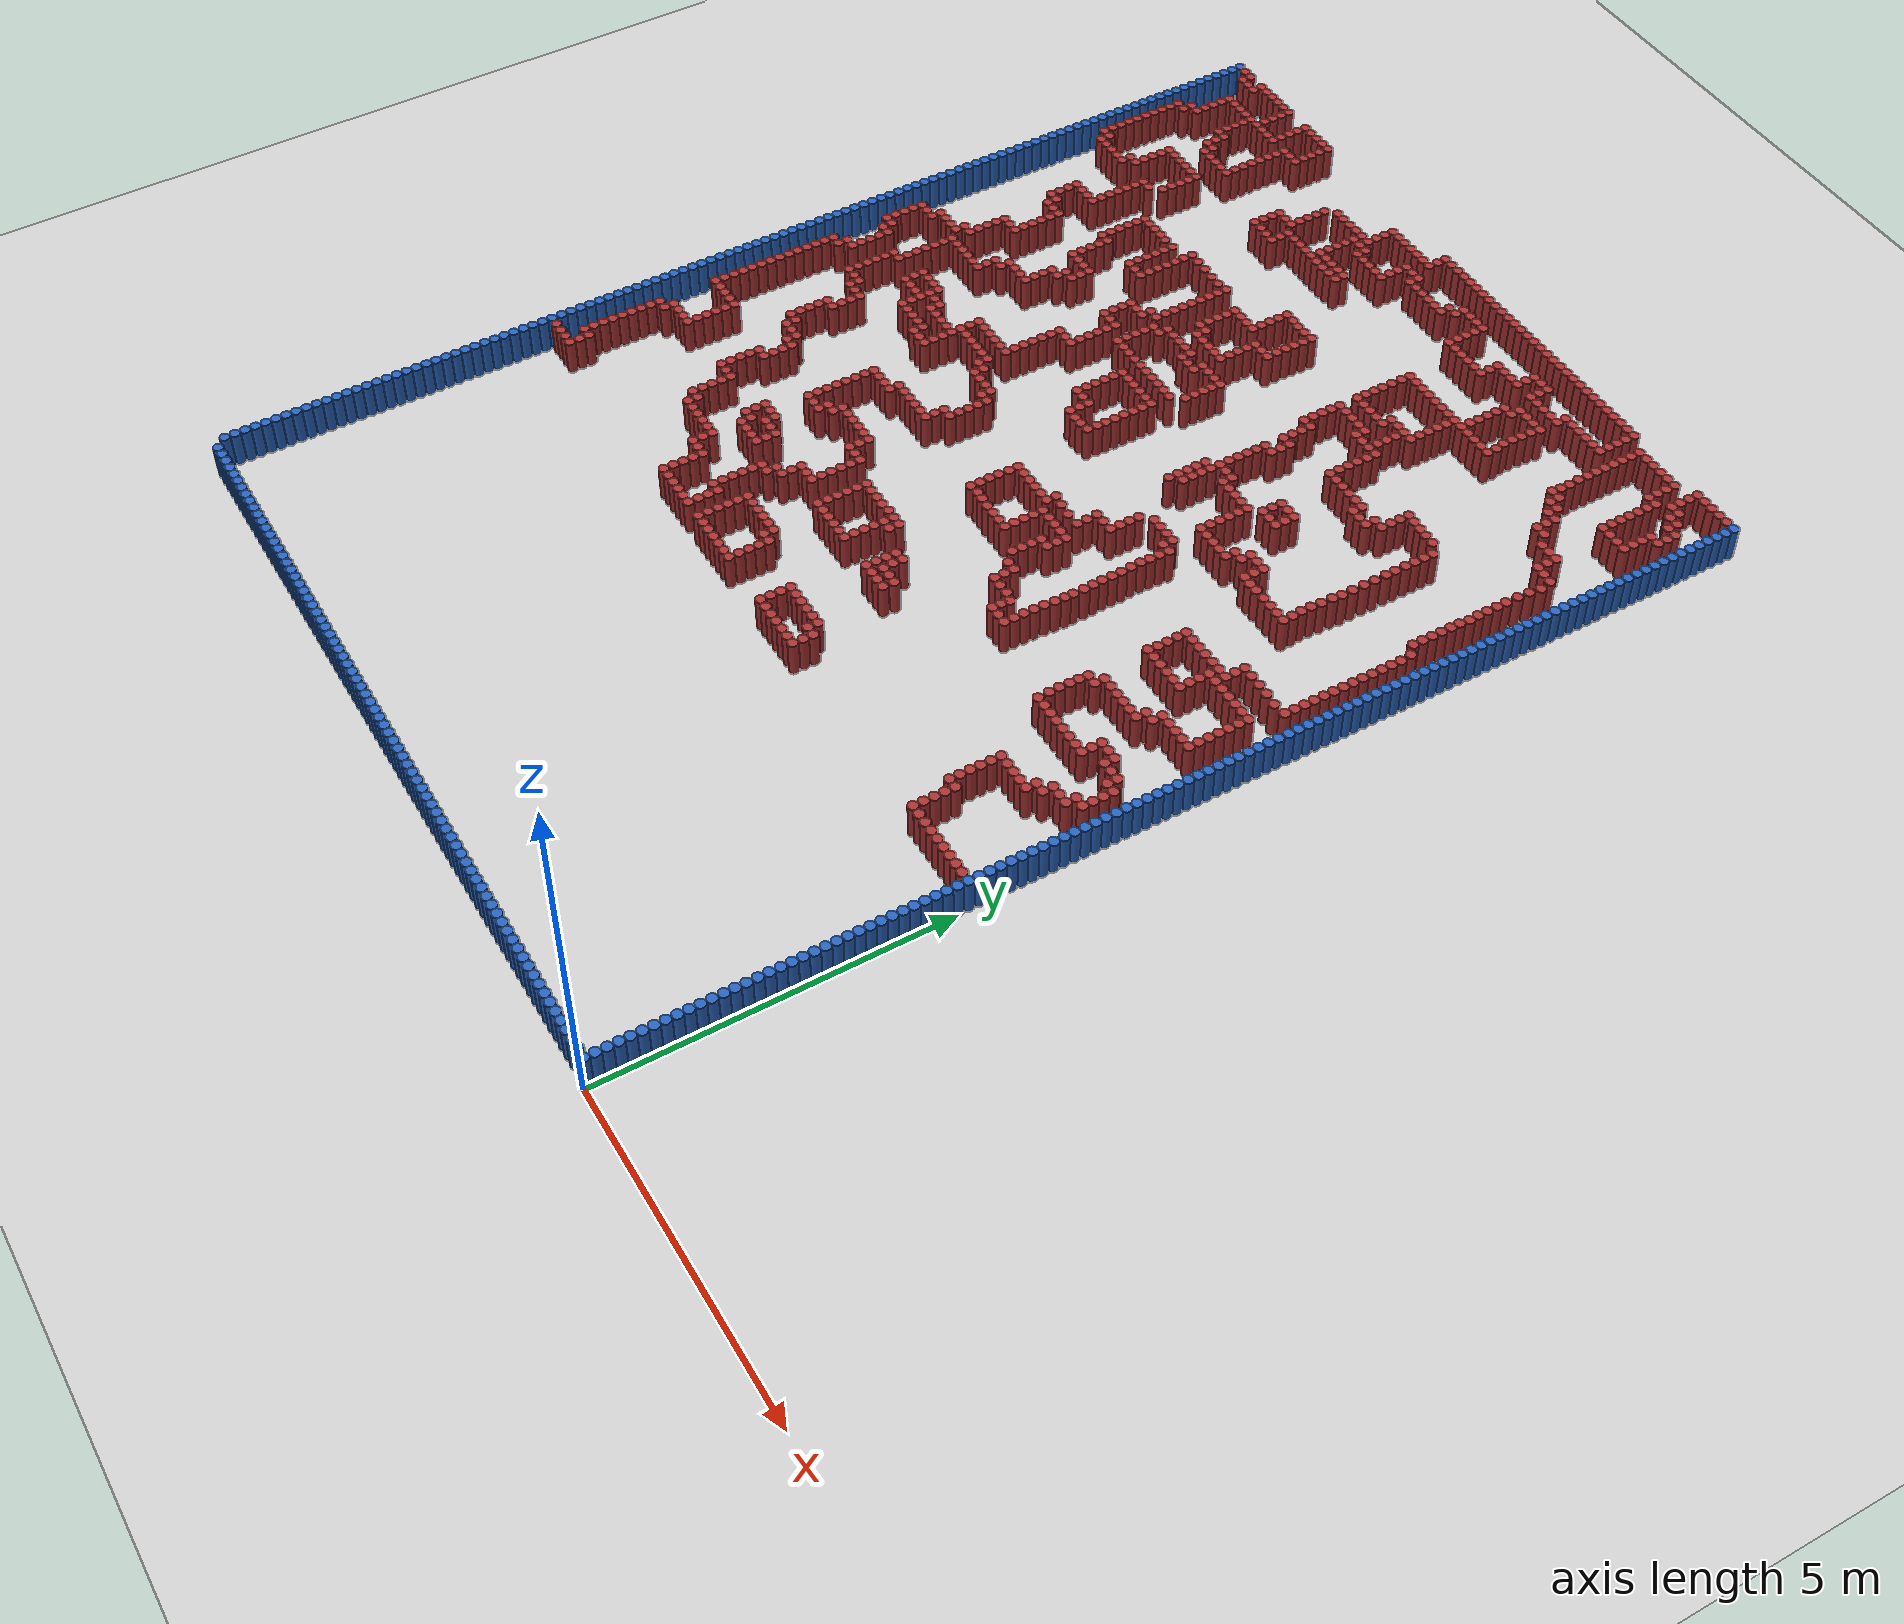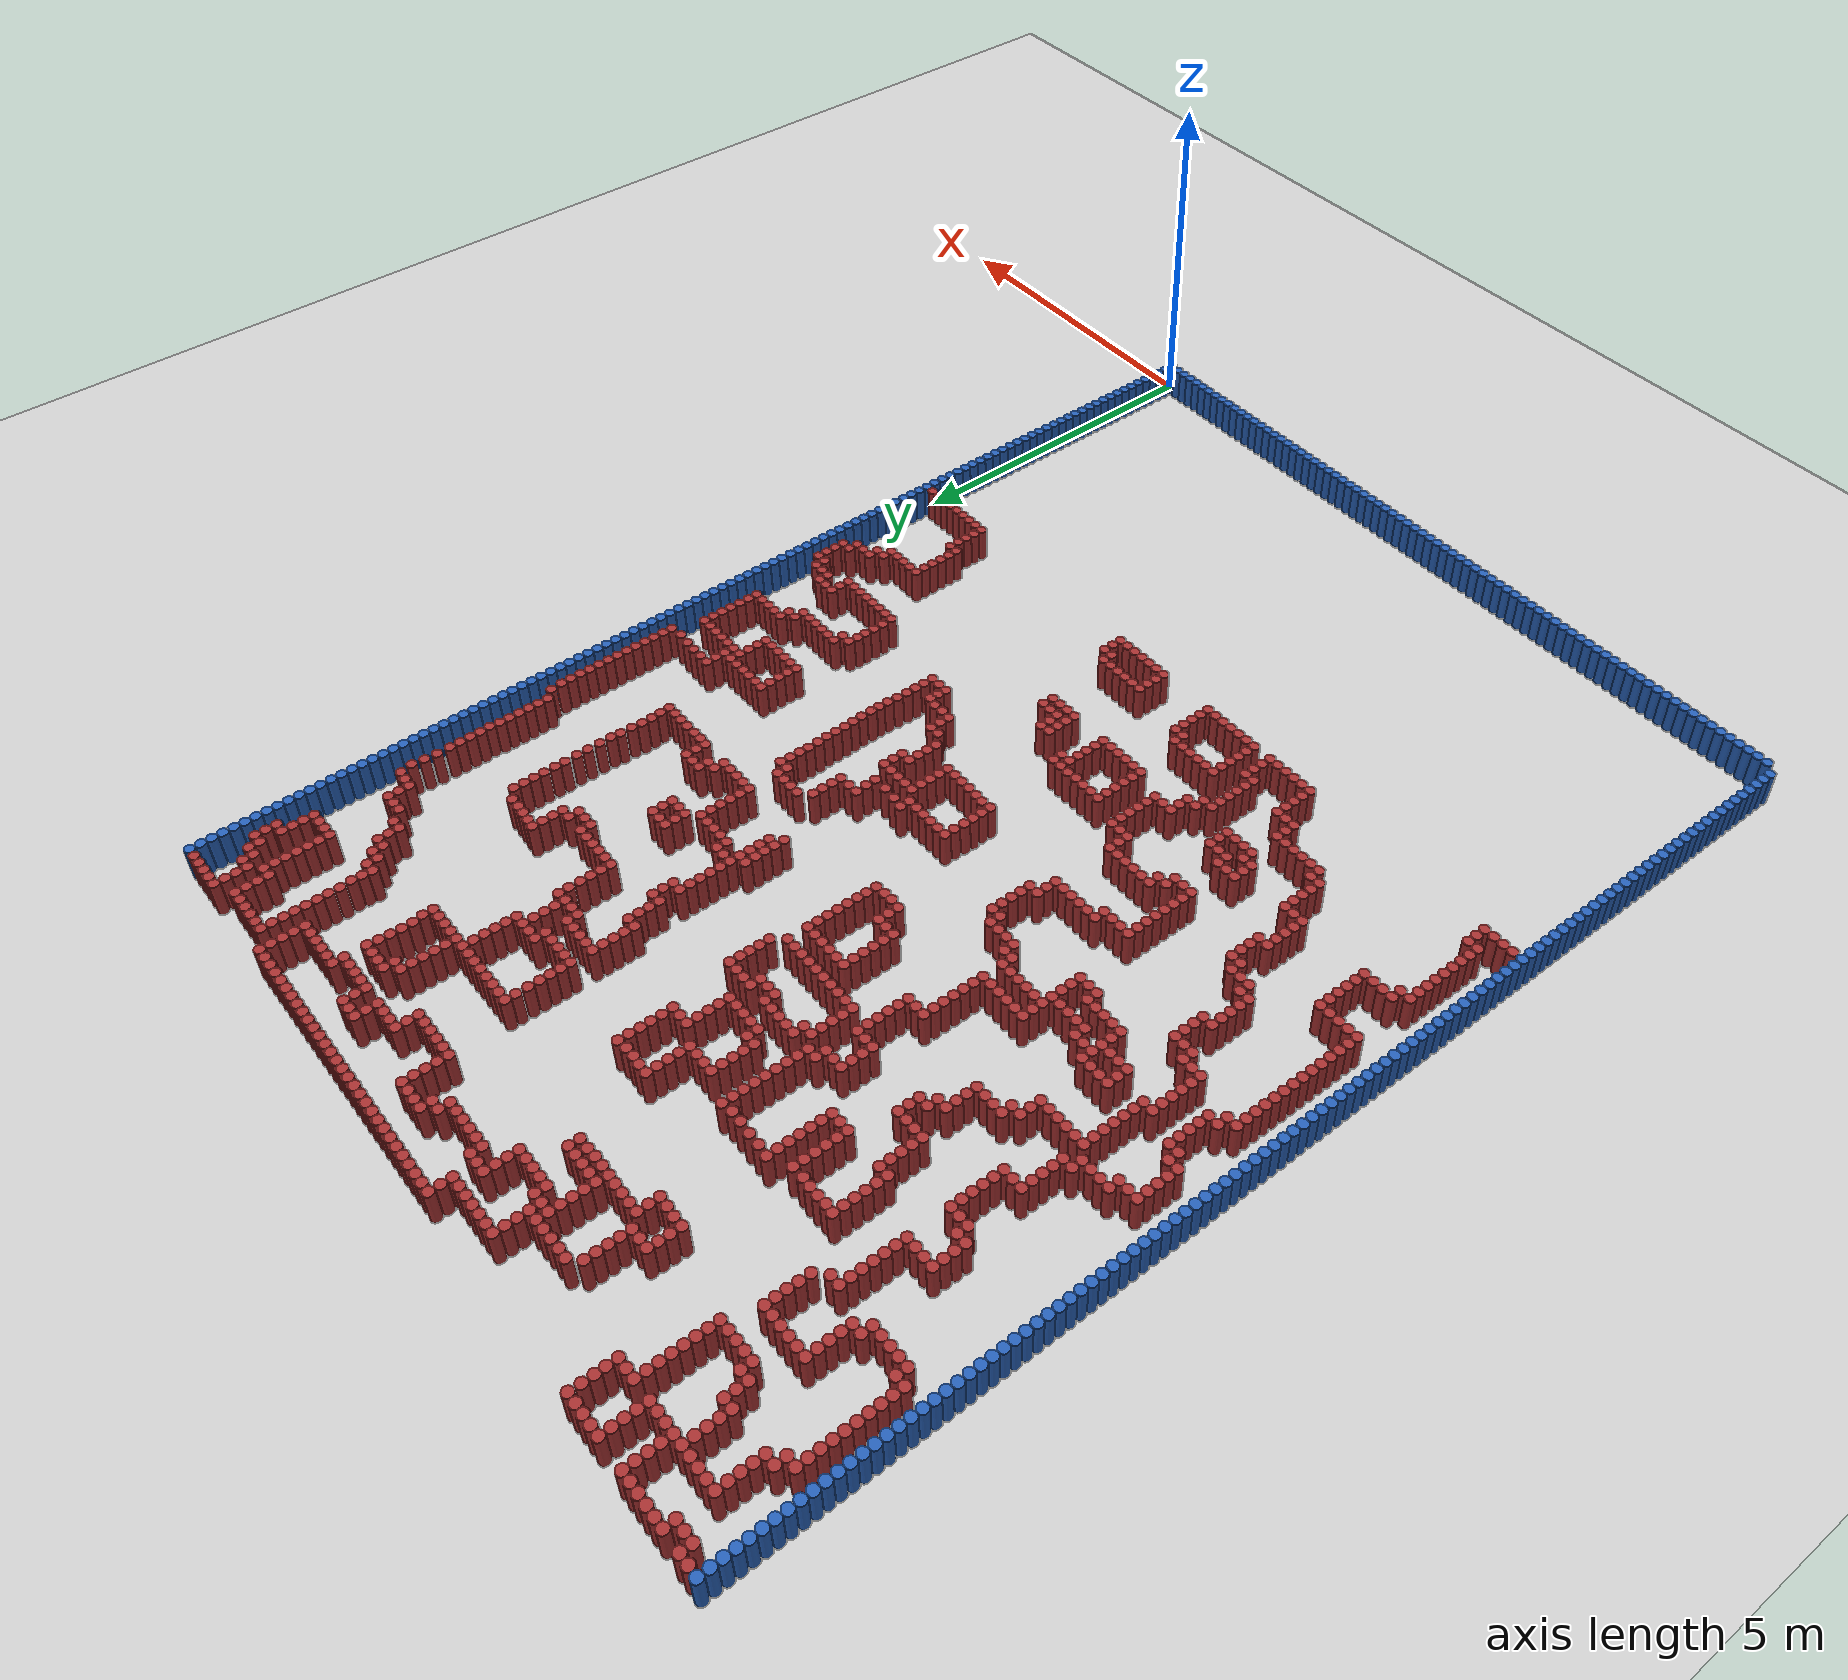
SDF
<sdf version="1.6">
 <world name="default">
  <light name="sun" type="directional">
   <pose>0 0 10 0 -0 0</pose>
   <diffuse>0.8 0.8 0.8 1</diffuse>
   <specular>0.1 0.1 0.1 1</specular>
   <attenuation>
    <range>1000</range>
    <constant>0.9</constant>
    <linear>0.01</linear>
    <quadratic>0.001</quadratic>
   </attenuation>
   <direction>-0.5 0.5 -1</direction>
  </light>
  <model name="ground_plane">
   <static>1</static>
   <link name="link">
    <collision name="collision">
     <geometry><plane><normal>0 0 1</normal><size>100 100</size></plane></geometry>
     <surface><friction><ode><mu>100</mu><mu2>50</mu2></ode></friction></surface>
    </collision>
    <visual name="visual">
     <cast_shadows>0</cast_shadows>
     <geometry><plane><normal>0 0 1</normal><size>100 100</size></plane></geometry>
     <material>
      <script><uri>file://media/materials/scripts/gazebo.material</uri><name>Gazebo/Grey</name></script>
     </material>
    </visual>
   </link>
  </model>
  <gravity>0 0 -9.8</gravity>
  <magnetic_field>6e-06 2.3e-05 -4.2e-05</magnetic_field>
  <atmosphere type="adiabatic"/>
  <physics name="default_physics" default="0" type="ode">
   <max_step_size>0.001</max_step_size>
   <real_time_factor>1</real_time_factor>
   <real_time_update_rate>1000</real_time_update_rate>
  </physics>
  <scene><ambient>0.4 0.4 0.4 1</ambient><background>0.7 0.7 0.7 1</background><shadows>1</shadows></scene>
  <spherical_coordinates>
   <surface_model>EARTH_WGS84</surface_model>
   <latitude_deg>0</latitude_deg>
   <longitude_deg>0</longitude_deg>
   <elevation>0</elevation>
   <heading_deg>0</heading_deg>
  </spherical_coordinates>
  <model name="unit_cylinder_0">
   <static>1</static>
   <pose>-0.075 0.075 0 0 -0 0</pose>
   <link name="link">
    <inertial>
     <mass>1</mass>
     <inertia><ixx>0.145833</ixx><ixy>0</ixy><ixz>0</ixz><iyy>0.145833</iyy><iyz>0</iyz><izz>0.125</izz></inertia>
    </inertial>
    <collision name="collision">
     <geometry><cylinder><radius>0.075</radius><length>1</length></cylinder></geometry>
    </collision>
    <visual name="visual">
     <geometry><cylinder><radius>0.075</radius><length>1</length></cylinder></geometry>
     <material><ambient>0.152 0.379 0.72 1</ambient><diffuse>0.152 0.379 0.72 1</diffuse></material>
     <material>
      <script><name>Gazebo/Grey</name><uri>file://media/materials/scripts/gazebo.material</uri></script>
     </material>
    </visual>
   </link>
  </model>
  <model name="unit_cylinder_1">
   <static>1</static>
   <pose>-0.225 0.075 0 0 -0 0</pose>
   <link name="link">
    <inertial>
     <mass>1</mass>
     <inertia><ixx>0.145833</ixx><ixy>0</ixy><ixz>0</ixz><iyy>0.145833</iyy><iyz>0</iyz><izz>0.125</izz></inertia>
    </inertial>
    <collision name="collision">
     <geometry><cylinder><radius>0.075</radius><length>1</length></cylinder></geometry>
    </collision>
    <visual name="visual">
     <geometry><cylinder><radius>0.075</radius><length>1</length></cylinder></geometry>
     <material><ambient>0.152 0.379 0.72 1</ambient><diffuse>0.152 0.379 0.72 1</diffuse></material>
     <material>
      <script><name>Gazebo/Grey</name><uri>file://media/materials/scripts/gazebo.material</uri></script>
     </material>
    </visual>
   </link>
  </model>
  <model name="unit_cylinder_2">
   <static>1</static>
   <pose>-0.375 0.075 0 0 -0 0</pose>
   <link name="link">
    <inertial>
     <mass>1</mass>
     <inertia><ixx>0.145833</ixx><ixy>0</ixy><ixz>0</ixz><iyy>0.145833</iyy><iyz>0</iyz><izz>0.125</izz></inertia>
    </inertial>
    <collision name="collision">
     <geometry><cylinder><radius>0.075</radius><length>1</length></cylinder></geometry>
    </collision>
    <visual name="visual">
     <geometry><cylinder><radius>0.075</radius><length>1</length></cylinder></geometry>
     <material><ambient>0.152 0.379 0.72 1</ambient><diffuse>0.152 0.379 0.72 1</diffuse></material>
     <material>
      <script><name>Gazebo/Grey</name><uri>file://media/materials/scripts/gazebo.material</uri></script>
     </material>
    </visual>
   </link>
  </model>
  <model name="unit_cylinder_3">
   <static>1</static>
   <pose>-0.525 0.075 0 0 -0 0</pose>
   <link name="link">
    <inertial>
     <mass>1</mass>
     <inertia><ixx>0.145833</ixx><ixy>0</ixy><ixz>0</ixz><iyy>0.145833</iyy><iyz>0</iyz><izz>0.125</izz></inertia>
    </inertial>
    <collision name="collision">
     <geometry><cylinder><radius>0.075</radius><length>1</length></cylinder></geometry>
    </collision>
    <visual name="visual">
     <geometry><cylinder><radius>0.075</radius><length>1</length></cylinder></geometry>
     <material><ambient>0.152 0.379 0.72 1</ambient><diffuse>0.152 0.379 0.72 1</diffuse></material>
     <material>
      <script><name>Gazebo/Grey</name><uri>file://media/materials/scripts/gazebo.material</uri></script>
     </material>
    </visual>
   </link>
  </model>
  <model name="unit_cylinder_4">
   <static>1</static>
   <pose>-0.675 0.075 0 0 -0 0</pose>
   <link name="link">
    <inertial>
     <mass>1</mass>
     <inertia><ixx>0.145833</ixx><ixy>0</ixy><ixz>0</ixz><iyy>0.145833</iyy><iyz>0</iyz><izz>0.125</izz></inertia>
    </inertial>
    <collision name="collision">
     <geometry><cylinder><radius>0.075</radius><length>1</length></cylinder></geometry>
    </collision>
    <visual name="visual">
     <geometry><cylinder><radius>0.075</radius><length>1</length></cylinder></geometry>
     <material><ambient>0.152 0.379 0.72 1</ambient><diffuse>0.152 0.379 0.72 1</diffuse></material>
     <material>
      <script><name>Gazebo/Grey</name><uri>file://media/materials/scripts/gazebo.material</uri></script>
     </material>
    </visual>
   </link>
  </model>
  <model name="unit_cylinder_5">
   <static>1</static>
   <pose>-0.825 0.075 0 0 -0 0</pose>
   <link name="link">
    <inertial>
     <mass>1</mass>
     <inertia><ixx>0.145833</ixx><ixy>0</ixy><ixz>0</ixz><iyy>0.145833</iyy><iyz>0</iyz><izz>0.125</izz></inertia>
    </inertial>
    <collision name="collision">
     <geometry><cylinder><radius>0.075</radius><length>1</length></cylinder></geometry>
    </collision>
    <visual name="visual">
     <geometry><cylinder><radius>0.075</radius><length>1</length></cylinder></geometry>
     <material><ambient>0.152 0.379 0.72 1</ambient><diffuse>0.152 0.379 0.72 1</diffuse></material>
     <material>
      <script><name>Gazebo/Grey</name><uri>file://media/materials/scripts/gazebo.material</uri></script>
     </material>
    </visual>
   </link>
  </model>
  <model name="unit_cylinder_6">
   <static>1</static>
   <pose>-0.975 0.075 0 0 -0 0</pose>
   <link name="link">
    <inertial>
     <mass>1</mass>
     <inertia><ixx>0.145833</ixx><ixy>0</ixy><ixz>0</ixz><iyy>0.145833</iyy><iyz>0</iyz><izz>0.125</izz></inertia>
    </inertial>
    <collision name="collision">
     <geometry><cylinder><radius>0.075</radius><length>1</length></cylinder></geometry>
    </collision>
    <visual name="visual">
     <geometry><cylinder><radius>0.075</radius><length>1</length></cylinder></geometry>
     <material><ambient>0.152 0.379 0.72 1</ambient><diffuse>0.152 0.379 0.72 1</diffuse></material>
     <material>
      <script><name>Gazebo/Grey</name><uri>file://media/materials/scripts/gazebo.material</uri></script>
     </material>
    </visual>
   </link>
  </model>
  <model name="unit_cylinder_7">
   <static>1</static>
   <pose>-1.125 0.075 0 0 -0 0</pose>
   <link name="link">
    <inertial>
     <mass>1</mass>
     <inertia><ixx>0.145833</ixx><ixy>0</ixy><ixz>0</ixz><iyy>0.145833</iyy><iyz>0</iyz><izz>0.125</izz></inertia>
    </inertial>
    <collision name="collision">
     <geometry><cylinder><radius>0.075</radius><length>1</length></cylinder></geometry>
    </collision>
    <visual name="visual">
     <geometry><cylinder><radius>0.075</radius><length>1</length></cylinder></geometry>
     <material><ambient>0.152 0.379 0.72 1</ambient><diffuse>0.152 0.379 0.72 1</diffuse></material>
     <material>
      <script><name>Gazebo/Grey</name><uri>file://media/materials/scripts/gazebo.material</uri></script>
     </material>
    </visual>
   </link>
  </model>
  <model name="unit_cylinder_8">
   <static>1</static>
   <pose>-1.275 0.075 0 0 -0 0</pose>
   <link name="link">
    <inertial>
     <mass>1</mass>
     <inertia><ixx>0.145833</ixx><ixy>0</ixy><ixz>0</ixz><iyy>0.145833</iyy><iyz>0</iyz><izz>0.125</izz></inertia>
    </inertial>
    <collision name="collision">
     <geometry><cylinder><radius>0.075</radius><length>1</length></cylinder></geometry>
    </collision>
    <visual name="visual">
     <geometry><cylinder><radius>0.075</radius><length>1</length></cylinder></geometry>
     <material><ambient>0.152 0.379 0.72 1</ambient><diffuse>0.152 0.379 0.72 1</diffuse></material>
     <material>
      <script><name>Gazebo/Grey</name><uri>file://media/materials/scripts/gazebo.material</uri></script>
     </material>
    </visual>
   </link>
  </model>
  <model name="unit_cylinder_9">
   <static>1</static>
   <pose>-1.425 0.075 0 0 -0 0</pose>
   <link name="link">
    <inertial>
     <mass>1</mass>
     <inertia><ixx>0.145833</ixx><ixy>0</ixy><ixz>0</ixz><iyy>0.145833</iyy><iyz>0</iyz><izz>0.125</izz></inertia>
    </inertial>
    <collision name="collision">
     <geometry><cylinder><radius>0.075</radius><length>1</length></cylinder></geometry>
    </collision>
    <visual name="visual">
     <geometry><cylinder><radius>0.075</radius><length>1</length></cylinder></geometry>
     <material><ambient>0.152 0.379 0.72 1</ambient><diffuse>0.152 0.379 0.72 1</diffuse></material>
     <material>
      <script><name>Gazebo/Grey</name><uri>file://media/materials/scripts/gazebo.material</uri></script>
     </material>
    </visual>
   </link>
  </model>
  <model name="unit_cylinder_10">
   <static>1</static>
   <pose>-1.575 0.075 0 0 -0 0</pose>
   <link name="link">
    <inertial>
     <mass>1</mass>
     <inertia><ixx>0.145833</ixx><ixy>0</ixy><ixz>0</ixz><iyy>0.145833</iyy><iyz>0</iyz><izz>0.125</izz></inertia>
    </inertial>
    <collision name="collision">
     <geometry><cylinder><radius>0.075</radius><length>1</length></cylinder></geometry>
    </collision>
    <visual name="visual">
     <geometry><cylinder><radius>0.075</radius><length>1</length></cylinder></geometry>
     <material><ambient>0.152 0.379 0.72 1</ambient><diffuse>0.152 0.379 0.72 1</diffuse></material>
     <material>
      <script><name>Gazebo/Grey</name><uri>file://media/materials/scripts/gazebo.material</uri></script>
     </material>
    </visual>
   </link>
  </model>
  <model name="unit_cylinder_11">
   <static>1</static>
   <pose>-1.725 0.075 0 0 -0 0</pose>
   <link name="link">
    <inertial>
     <mass>1</mass>
     <inertia><ixx>0.145833</ixx><ixy>0</ixy><ixz>0</ixz><iyy>0.145833</iyy><iyz>0</iyz><izz>0.125</izz></inertia>
    </inertial>
    <collision name="collision">
     <geometry><cylinder><radius>0.075</radius><length>1</length></cylinder></geometry>
    </collision>
    <visual name="visual">
     <geometry><cylinder><radius>0.075</radius><length>1</length></cylinder></geometry>
     <material><ambient>0.152 0.379 0.72 1</ambient><diffuse>0.152 0.379 0.72 1</diffuse></material>
     <material>
      <script><name>Gazebo/Grey</name><uri>file://media/materials/scripts/gazebo.material</uri></script>
     </material>
    </visual>
   </link>
  </model>
  <model name="unit_cylinder_12">
   <static>1</static>
   <pose>-1.875 0.075 0 0 -0 0</pose>
   <link name="link">
    <inertial>
     <mass>1</mass>
     <inertia><ixx>0.145833</ixx><ixy>0</ixy><ixz>0</ixz><iyy>0.145833</iyy><iyz>0</iyz><izz>0.125</izz></inertia>
    </inertial>
    <collision name="collision">
     <geometry><cylinder><radius>0.075</radius><length>1</length></cylinder></geometry>
    </collision>
    <visual name="visual">
     <geometry><cylinder><radius>0.075</radius><length>1</length></cylinder></geometry>
     <material><ambient>0.152 0.379 0.72 1</ambient><diffuse>0.152 0.379 0.72 1</diffuse></material>
     <material>
      <script><name>Gazebo/Grey</name><uri>file://media/materials/scripts/gazebo.material</uri></script>
     </material>
    </visual>
   </link>
  </model>
  <model name="unit_cylinder_13">
   <static>1</static>
   <pose>-2.025 0.075 0 0 -0 0</pose>
   <link name="link">
    <inertial>
     <mass>1</mass>
     <inertia><ixx>0.145833</ixx><ixy>0</ixy><ixz>0</ixz><iyy>0.145833</iyy><iyz>0</iyz><izz>0.125</izz></inertia>
    </inertial>
    <collision name="collision">
     <geometry><cylinder><radius>0.075</radius><length>1</length></cylinder></geometry>
    </collision>
    <visual name="visual">
     <geometry><cylinder><radius>0.075</radius><length>1</length></cylinder></geometry>
     <material><ambient>0.152 0.379 0.72 1</ambient><diffuse>0.152 0.379 0.72 1</diffuse></material>
     <material>
      <script><name>Gazebo/Grey</name><uri>file://media/materials/scripts/gazebo.material</uri></script>
     </material>
    </visual>
   </link>
  </model>
  <model name="unit_cylinder_14">
   <static>1</static>
   <pose>-2.175 0.075 0 0 -0 0</pose>
   <link name="link">
    <inertial>
     <mass>1</mass>
     <inertia><ixx>0.145833</ixx><ixy>0</ixy><ixz>0</ixz><iyy>0.145833</iyy><iyz>0</iyz><izz>0.125</izz></inertia>
    </inertial>
    <collision name="collision">
     <geometry><cylinder><radius>0.075</radius><length>1</length></cylinder></geometry>
    </collision>
    <visual name="visual">
     <geometry><cylinder><radius>0.075</radius><length>1</length></cylinder></geometry>
     <material><ambient>0.152 0.379 0.72 1</ambient><diffuse>0.152 0.379 0.72 1</diffuse></material>
     <material>
      <script><name>Gazebo/Grey</name><uri>file://media/materials/scripts/gazebo.material</uri></script>
     </material>
    </visual>
   </link>
  </model>
  <model name="unit_cylinder_15">
   <static>1</static>
   <pose>-2.325 0.075 0 0 -0 0</pose>
   <link name="link">
    <inertial>
     <mass>1</mass>
     <inertia><ixx>0.145833</ixx><ixy>0</ixy><ixz>0</ixz><iyy>0.145833</iyy><iyz>0</iyz><izz>0.125</izz></inertia>
    </inertial>
    <collision name="collision">
     <geometry><cylinder><radius>0.075</radius><length>1</length></cylinder></geometry>
    </collision>
    <visual name="visual">
     <geometry><cylinder><radius>0.075</radius><length>1</length></cylinder></geometry>
     <material><ambient>0.152 0.379 0.72 1</ambient><diffuse>0.152 0.379 0.72 1</diffuse></material>
     <material>
      <script><name>Gazebo/Grey</name><uri>file://media/materials/scripts/gazebo.material</uri></script>
     </material>
    </visual>
   </link>
  </model>
  <model name="unit_cylinder_16">
   <static>1</static>
   <pose>-2.475 0.075 0 0 -0 0</pose>
   <link name="link">
    <inertial>
     <mass>1</mass>
     <inertia><ixx>0.145833</ixx><ixy>0</ixy><ixz>0</ixz><iyy>0.145833</iyy><iyz>0</iyz><izz>0.125</izz></inertia>
    </inertial>
    <collision name="collision">
     <geometry><cylinder><radius>0.075</radius><length>1</length></cylinder></geometry>
    </collision>
    <visual name="visual">
     <geometry><cylinder><radius>0.075</radius><length>1</length></cylinder></geometry>
     <material><ambient>0.152 0.379 0.72 1</ambient><diffuse>0.152 0.379 0.72 1</diffuse></material>
     <material>
      <script><name>Gazebo/Grey</name><uri>file://media/materials/scripts/gazebo.material</uri></script>
     </material>
    </visual>
   </link>
  </model>
  <model name="unit_cylinder_17">
   <static>1</static>
   <pose>-2.625 0.075 0 0 -0 0</pose>
   <link name="link">
    <inertial>
     <mass>1</mass>
     <inertia><ixx>0.145833</ixx><ixy>0</ixy><ixz>0</ixz><iyy>0.145833</iyy><iyz>0</iyz><izz>0.125</izz></inertia>
    </inertial>
    <collision name="collision">
     <geometry><cylinder><radius>0.075</radius><length>1</length></cylinder></geometry>
    </collision>
    <visual name="visual">
     <geometry><cylinder><radius>0.075</radius><length>1</length></cylinder></geometry>
     <material><ambient>0.152 0.379 0.72 1</ambient><diffuse>0.152 0.379 0.72 1</diffuse></material>
     <material>
      <script><name>Gazebo/Grey</name><uri>file://media/materials/scripts/gazebo.material</uri></script>
     </material>
    </visual>
   </link>
  </model>
  <model name="unit_cylinder_18">
   <static>1</static>
   <pose>-2.775 0.075 0 0 -0 0</pose>
   <link name="link">
    <inertial>
     <mass>1</mass>
     <inertia><ixx>0.145833</ixx><ixy>0</ixy><ixz>0</ixz><iyy>0.145833</iyy><iyz>0</iyz><izz>0.125</izz></inertia>
    </inertial>
    <collision name="collision">
     <geometry><cylinder><radius>0.075</radius><length>1</length></cylinder></geometry>
    </collision>
    <visual name="visual">
     <geometry><cylinder><radius>0.075</radius><length>1</length></cylinder></geometry>
     <material><ambient>0.152 0.379 0.72 1</ambient><diffuse>0.152 0.379 0.72 1</diffuse></material>
     <material>
      <script><name>Gazebo/Grey</name><uri>file://media/materials/scripts/gazebo.material</uri></script>
     </material>
    </visual>
   </link>
  </model>
  <model name="unit_cylinder_19">
   <static>1</static>
   <pose>-2.925 0.075 0 0 -0 0</pose>
   <link name="link">
    <inertial>
     <mass>1</mass>
     <inertia><ixx>0.145833</ixx><ixy>0</ixy><ixz>0</ixz><iyy>0.145833</iyy><iyz>0</iyz><izz>0.125</izz></inertia>
    </inertial>
    <collision name="collision">
     <geometry><cylinder><radius>0.075</radius><length>1</length></cylinder></geometry>
    </collision>
    <visual name="visual">
     <geometry><cylinder><radius>0.075</radius><length>1</length></cylinder></geometry>
     <material><ambient>0.152 0.379 0.72 1</ambient><diffuse>0.152 0.379 0.72 1</diffuse></material>
     <material>
      <script><name>Gazebo/Grey</name><uri>file://media/materials/scripts/gazebo.material</uri></script>
     </material>
    </visual>
   </link>
  </model>
  <model name="unit_cylinder_20">
   <static>1</static>
   <pose>-3.075 0.075 0 0 -0 0</pose>
   <link name="link">
    <inertial>
     <mass>1</mass>
     <inertia><ixx>0.145833</ixx><ixy>0</ixy><ixz>0</ixz><iyy>0.145833</iyy><iyz>0</iyz><izz>0.125</izz></inertia>
    </inertial>
    <collision name="collision">
     <geometry><cylinder><radius>0.075</radius><length>1</length></cylinder></geometry>
    </collision>
    <visual name="visual">
     <geometry><cylinder><radius>0.075</radius><length>1</length></cylinder></geometry>
     <material><ambient>0.152 0.379 0.72 1</ambient><diffuse>0.152 0.379 0.72 1</diffuse></material>
     <material>
      <script><name>Gazebo/Grey</name><uri>file://media/materials/scripts/gazebo.material</uri></script>
     </material>
    </visual>
   </link>
  </model>
  <model name="unit_cylinder_21">
   <static>1</static>
   <pose>-3.225 0.075 0 0 -0 0</pose>
   <link name="link">
    <inertial>
     <mass>1</mass>
     <inertia><ixx>0.145833</ixx><ixy>0</ixy><ixz>0</ixz><iyy>0.145833</iyy><iyz>0</iyz><izz>0.125</izz></inertia>
    </inertial>
    <collision name="collision">
     <geometry><cylinder><radius>0.075</radius><length>1</length></cylinder></geometry>
    </collision>
    <visual name="visual">
     <geometry><cylinder><radius>0.075</radius><length>1</length></cylinder></geometry>
     <material><ambient>0.152 0.379 0.72 1</ambient><diffuse>0.152 0.379 0.72 1</diffuse></material>
     <material>
      <script><name>Gazebo/Grey</name><uri>file://media/materials/scripts/gazebo.material</uri></script>
     </material>
    </visual>
   </link>
  </model>
  <model name="unit_cylinder_22">
   <static>1</static>
   <pose>-3.375 0.075 0 0 -0 0</pose>
   <link name="link">
    <inertial>
     <mass>1</mass>
     <inertia><ixx>0.145833</ixx><ixy>0</ixy><ixz>0</ixz><iyy>0.145833</iyy><iyz>0</iyz><izz>0.125</izz></inertia>
    </inertial>
    <collision name="collision">
     <geometry><cylinder><radius>0.075</radius><length>1</length></cylinder></geometry>
    </collision>
    <visual name="visual">
     <geometry><cylinder><radius>0.075</radius><length>1</length></cylinder></geometry>
     <material><ambient>0.152 0.379 0.72 1</ambient><diffuse>0.152 0.379 0.72 1</diffuse></material>
     <material>
      <script><name>Gazebo/Grey</name><uri>file://media/materials/scripts/gazebo.material</uri></script>
     </material>
    </visual>
   </link>
  </model>
  <model name="unit_cylinder_23">
   <static>1</static>
   <pose>-3.525 0.075 0 0 -0 0</pose>
   <link name="link">
    <inertial>
     <mass>1</mass>
     <inertia><ixx>0.145833</ixx><ixy>0</ixy><ixz>0</ixz><iyy>0.145833</iyy><iyz>0</iyz><izz>0.125</izz></inertia>
    </inertial>
    <collision name="collision">
     <geometry><cylinder><radius>0.075</radius><length>1</length></cylinder></geometry>
    </collision>
    <visual name="visual">
     <geometry><cylinder><radius>0.075</radius><length>1</length></cylinder></geometry>
     <material><ambient>0.152 0.379 0.72 1</ambient><diffuse>0.152 0.379 0.72 1</diffuse></material>
     <material>
      <script><name>Gazebo/Grey</name><uri>file://media/materials/scripts/gazebo.material</uri></script>
     </material>
    </visual>
   </link>
  </model>
  <model name="unit_cylinder_24">
   <static>1</static>
   <pose>-3.675 0.075 0 0 -0 0</pose>
   <link name="link">
    <inertial>
     <mass>1</mass>
     <inertia><ixx>0.145833</ixx><ixy>0</ixy><ixz>0</ixz><iyy>0.145833</iyy><iyz>0</iyz><izz>0.125</izz></inertia>
    </inertial>
    <collision name="collision">
     <geometry><cylinder><radius>0.075</radius><length>1</length></cylinder></geometry>
    </collision>
    <visual name="visual">
     <geometry><cylinder><radius>0.075</radius><length>1</length></cylinder></geometry>
     <material><ambient>0.152 0.379 0.72 1</ambient><diffuse>0.152 0.379 0.72 1</diffuse></material>
     <material>
      <script><name>Gazebo/Grey</name><uri>file://media/materials/scripts/gazebo.material</uri></script>
     </material>
    </visual>
   </link>
  </model>
  <model name="unit_cylinder_25">
   <static>1</static>
   <pose>-3.825 0.075 0 0 -0 0</pose>
   <link name="link">
    <inertial>
     <mass>1</mass>
     <inertia><ixx>0.145833</ixx><ixy>0</ixy><ixz>0</ixz><iyy>0.145833</iyy><iyz>0</iyz><izz>0.125</izz></inertia>
    </inertial>
    <collision name="collision">
     <geometry><cylinder><radius>0.075</radius><length>1</length></cylinder></geometry>
    </collision>
    <visual name="visual">
     <geometry><cylinder><radius>0.075</radius><length>1</length></cylinder></geometry>
     <material><ambient>0.152 0.379 0.72 1</ambient><diffuse>0.152 0.379 0.72 1</diffuse></material>
     <material>
      <script><name>Gazebo/Grey</name><uri>file://media/materials/scripts/gazebo.material</uri></script>
     </material>
    </visual>
   </link>
  </model>
  <model name="unit_cylinder_26">
   <static>1</static>
   <pose>-3.975 0.075 0 0 -0 0</pose>
   <link name="link">
    <inertial>
     <mass>1</mass>
     <inertia><ixx>0.145833</ixx><ixy>0</ixy><ixz>0</ixz><iyy>0.145833</iyy><iyz>0</iyz><izz>0.125</izz></inertia>
    </inertial>
    <collision name="collision">
     <geometry><cylinder><radius>0.075</radius><length>1</length></cylinder></geometry>
    </collision>
    <visual name="visual">
     <geometry><cylinder><radius>0.075</radius><length>1</length></cylinder></geometry>
     <material><ambient>0.152 0.379 0.72 1</ambient><diffuse>0.152 0.379 0.72 1</diffuse></material>
     <material>
      <script><name>Gazebo/Grey</name><uri>file://media/materials/scripts/gazebo.material</uri></script>
     </material>
    </visual>
   </link>
  </model>
  <model name="unit_cylinder_27">
   <static>1</static>
   <pose>-4.125 0.075 0 0 -0 0</pose>
   <link name="link">
    <inertial>
     <mass>1</mass>
     <inertia><ixx>0.145833</ixx><ixy>0</ixy><ixz>0</ixz><iyy>0.145833</iyy><iyz>0</iyz><izz>0.125</izz></inertia>
    </inertial>
    <collision name="collision">
     <geometry><cylinder><radius>0.075</radius><length>1</length></cylinder></geometry>
    </collision>
    <visual name="visual">
     <geometry><cylinder><radius>0.075</radius><length>1</length></cylinder></geometry>
     <material><ambient>0.152 0.379 0.72 1</ambient><diffuse>0.152 0.379 0.72 1</diffuse></material>
     <material>
      <script><name>Gazebo/Grey</name><uri>file://media/materials/scripts/gazebo.material</uri></script>
     </material>
    </visual>
   </link>
  </model>
  <model name="unit_cylinder_28">
   <static>1</static>
   <pose>-4.275 0.075 0 0 -0 0</pose>
   <link name="link">
    <inertial>
     <mass>1</mass>
     <inertia><ixx>0.145833</ixx><ixy>0</ixy><ixz>0</ixz><iyy>0.145833</iyy><iyz>0</iyz><izz>0.125</izz></inertia>
    </inertial>
    <collision name="collision">
     <geometry><cylinder><radius>0.075</radius><length>1</length></cylinder></geometry>
    </collision>
    <visual name="visual">
     <geometry><cylinder><radius>0.075</radius><length>1</length></cylinder></geometry>
     <material><ambient>0.152 0.379 0.72 1</ambient><diffuse>0.152 0.379 0.72 1</diffuse></material>
     <material>
      <script><name>Gazebo/Grey</name><uri>file://media/materials/scripts/gazebo.material</uri></script>
     </material>
    </visual>
   </link>
  </model>
  <model name="unit_cylinder_29">
   <static>1</static>
   <pose>-4.425 0.075 0 0 -0 0</pose>
   <link name="link">
    <inertial>
     <mass>1</mass>
     <inertia><ixx>0.145833</ixx><ixy>0</ixy><ixz>0</ixz><iyy>0.145833</iyy><iyz>0</iyz><izz>0.125</izz></inertia>
    </inertial>
    <collision name="collision">
     <geometry><cylinder><radius>0.075</radius><length>1</length></cylinder></geometry>
    </collision>
    <visual name="visual">
     <geometry><cylinder><radius>0.075</radius><length>1</length></cylinder></geometry>
     <material><ambient>0.152 0.379 0.72 1</ambient><diffuse>0.152 0.379 0.72 1</diffuse></material>
     <material>
      <script><name>Gazebo/Grey</name><uri>file://media/materials/scripts/gazebo.material</uri></script>
     </material>
    </visual>
   </link>
  </model>
  <model name="unit_cylinder_30">
   <static>1</static>
   <pose>-4.575 0.075 0 0 -0 0</pose>
   <link name="link">
    <inertial>
     <mass>1</mass>
     <inertia><ixx>0.145833</ixx><ixy>0</ixy><ixz>0</ixz><iyy>0.145833</iyy><iyz>0</iyz><izz>0.125</izz></inertia>
    </inertial>
    <collision name="collision">
     <geometry><cylinder><radius>0.075</radius><length>1</length></cylinder></geometry>
    </collision>
    <visual name="visual">
     <geometry><cylinder><radius>0.075</radius><length>1</length></cylinder></geometry>
     <material><ambient>0.152 0.379 0.72 1</ambient><diffuse>0.152 0.379 0.72 1</diffuse></material>
     <material>
      <script><name>Gazebo/Grey</name><uri>file://media/materials/scripts/gazebo.material</uri></script>
     </material>
    </visual>
   </link>
  </model>
  <model name="unit_cylinder_31">
   <static>1</static>
   <pose>-4.725 0.075 0 0 -0 0</pose>
   <link name="link">
    <inertial>
     <mass>1</mass>
     <inertia><ixx>0.145833</ixx><ixy>0</ixy><ixz>0</ixz><iyy>0.145833</iyy><iyz>0</iyz><izz>0.125</izz></inertia>
    </inertial>
    <collision name="collision">
     <geometry><cylinder><radius>0.075</radius><length>1</length></cylinder></geometry>
    </collision>
    <visual name="visual">
     <geometry><cylinder><radius>0.075</radius><length>1</length></cylinder></geometry>
     <material><ambient>0.152 0.379 0.72 1</ambient><diffuse>0.152 0.379 0.72 1</diffuse></material>
     <material>
      <script><name>Gazebo/Grey</name><uri>file://media/materials/scripts/gazebo.material</uri></script>
     </material>
    </visual>
   </link>
  </model>
  <model name="unit_cylinder_32">
   <static>1</static>
   <pose>-4.875 0.075 0 0 -0 0</pose>
   <link name="link">
    <inertial>
     <mass>1</mass>
     <inertia><ixx>0.145833</ixx><ixy>0</ixy><ixz>0</ixz><iyy>0.145833</iyy><iyz>0</iyz><izz>0.125</izz></inertia>
    </inertial>
    <collision name="collision">
     <geometry><cylinder><radius>0.075</radius><length>1</length></cylinder></geometry>
    </collision>
    <visual name="visual">
     <geometry><cylinder><radius>0.075</radius><length>1</length></cylinder></geometry>
     <material><ambient>0.152 0.379 0.72 1</ambient><diffuse>0.152 0.379 0.72 1</diffuse></material>
     <material>
      <script><name>Gazebo/Grey</name><uri>file://media/materials/scripts/gazebo.material</uri></script>
     </material>
    </visual>
   </link>
  </model>
  <model name="unit_cylinder_33">
   <static>1</static>
   <pose>-5.025 0.075 0 0 -0 0</pose>
   <link name="link">
    <inertial>
     <mass>1</mass>
     <inertia><ixx>0.145833</ixx><ixy>0</ixy><ixz>0</ixz><iyy>0.145833</iyy><iyz>0</iyz><izz>0.125</izz></inertia>
    </inertial>
    <collision name="collision">
     <geometry><cylinder><radius>0.075</radius><length>1</length></cylinder></geometry>
    </collision>
    <visual name="visual">
     <geometry><cylinder><radius>0.075</radius><length>1</length></cylinder></geometry>
     <material><ambient>0.152 0.379 0.72 1</ambient><diffuse>0.152 0.379 0.72 1</diffuse></material>
     <material>
      <script><name>Gazebo/Grey</name><uri>file://media/materials/scripts/gazebo.material</uri></script>
     </material>
    </visual>
   </link>
  </model>
  <model name="unit_cylinder_34">
   <static>1</static>
   <pose>-5.175 0.075 0 0 -0 0</pose>
   <link name="link">
    <inertial>
     <mass>1</mass>
     <inertia><ixx>0.145833</ixx><ixy>0</ixy><ixz>0</ixz><iyy>0.145833</iyy><iyz>0</iyz><izz>0.125</izz></inertia>
    </inertial>
    <collision name="collision">
     <geometry><cylinder><radius>0.075</radius><length>1</length></cylinder></geometry>
    </collision>
    <visual name="visual">
     <geometry><cylinder><radius>0.075</radius><length>1</length></cylinder></geometry>
     <material><ambient>0.152 0.379 0.72 1</ambient><diffuse>0.152 0.379 0.72 1</diffuse></material>
     <material>
      <script><name>Gazebo/Grey</name><uri>file://media/materials/scripts/gazebo.material</uri></script>
     </material>
    </visual>
   </link>
  </model>
  <model name="unit_cylinder_35">
   <static>1</static>
   <pose>-5.325 0.075 0 0 -0 0</pose>
   <link name="link">
    <inertial>
     <mass>1</mass>
     <inertia><ixx>0.145833</ixx><ixy>0</ixy><ixz>0</ixz><iyy>0.145833</iyy><iyz>0</iyz><izz>0.125</izz></inertia>
    </inertial>
    <collision name="collision">
     <geometry><cylinder><radius>0.075</radius><length>1</length></cylinder></geometry>
    </collision>
    <visual name="visual">
     <geometry><cylinder><radius>0.075</radius><length>1</length></cylinder></geometry>
     <material><ambient>0.152 0.379 0.72 1</ambient><diffuse>0.152 0.379 0.72 1</diffuse></material>
     <material>
      <script><name>Gazebo/Grey</name><uri>file://media/materials/scripts/gazebo.material</uri></script>
     </material>
    </visual>
   </link>
  </model>
  <model name="unit_cylinder_36">
   <static>1</static>
   <pose>-5.475 0.075 0 0 -0 0</pose>
   <link name="link">
    <inertial>
     <mass>1</mass>
     <inertia><ixx>0.145833</ixx><ixy>0</ixy><ixz>0</ixz><iyy>0.145833</iyy><iyz>0</iyz><izz>0.125</izz></inertia>
    </inertial>
    <collision name="collision">
     <geometry><cylinder><radius>0.075</radius><length>1</length></cylinder></geometry>
    </collision>
    <visual name="visual">
     <geometry><cylinder><radius>0.075</radius><length>1</length></cylinder></geometry>
     <material><ambient>0.152 0.379 0.72 1</ambient><diffuse>0.152 0.379 0.72 1</diffuse></material>
     <material>
      <script><name>Gazebo/Grey</name><uri>file://media/materials/scripts/gazebo.material</uri></script>
     </material>
    </visual>
   </link>
  </model>
  <model name="unit_cylinder_37">
   <static>1</static>
   <pose>-5.625 0.075 0 0 -0 0</pose>
   <link name="link">
    <inertial>
     <mass>1</mass>
     <inertia><ixx>0.145833</ixx><ixy>0</ixy><ixz>0</ixz><iyy>0.145833</iyy><iyz>0</iyz><izz>0.125</izz></inertia>
    </inertial>
    <collision name="collision">
     <geometry><cylinder><radius>0.075</radius><length>1</length></cylinder></geometry>
    </collision>
    <visual name="visual">
     <geometry><cylinder><radius>0.075</radius><length>1</length></cylinder></geometry>
     <material><ambient>0.152 0.379 0.72 1</ambient><diffuse>0.152 0.379 0.72 1</diffuse></material>
     <material>
      <script><name>Gazebo/Grey</name><uri>file://media/materials/scripts/gazebo.material</uri></script>
     </material>
    </visual>
   </link>
  </model>
  <model name="unit_cylinder_38">
   <static>1</static>
   <pose>-5.775 0.075 0 0 -0 0</pose>
   <link name="link">
    <inertial>
     <mass>1</mass>
     <inertia><ixx>0.145833</ixx><ixy>0</ixy><ixz>0</ixz><iyy>0.145833</iyy><iyz>0</iyz><izz>0.125</izz></inertia>
    </inertial>
    <collision name="collision">
     <geometry><cylinder><radius>0.075</radius><length>1</length></cylinder></geometry>
    </collision>
    <visual name="visual">
     <geometry><cylinder><radius>0.075</radius><length>1</length></cylinder></geometry>
     <material><ambient>0.152 0.379 0.72 1</ambient><diffuse>0.152 0.379 0.72 1</diffuse></material>
     <material>
      <script><name>Gazebo/Grey</name><uri>file://media/materials/scripts/gazebo.material</uri></script>
     </material>
    </visual>
   </link>
  </model>
  <model name="unit_cylinder_39">
   <static>1</static>
   <pose>-5.925 0.075 0 0 -0 0</pose>
   <link name="link">
    <inertial>
     <mass>1</mass>
     <inertia><ixx>0.145833</ixx><ixy>0</ixy><ixz>0</ixz><iyy>0.145833</iyy><iyz>0</iyz><izz>0.125</izz></inertia>
    </inertial>
    <collision name="collision">
     <geometry><cylinder><radius>0.075</radius><length>1</length></cylinder></geometry>
    </collision>
    <visual name="visual">
     <geometry><cylinder><radius>0.075</radius><length>1</length></cylinder></geometry>
     <material><ambient>0.152 0.379 0.72 1</ambient><diffuse>0.152 0.379 0.72 1</diffuse></material>
     <material>
      <script><name>Gazebo/Grey</name><uri>file://media/materials/scripts/gazebo.material</uri></script>
     </material>
    </visual>
   </link>
  </model>
  <model name="unit_cylinder_40">
   <static>1</static>
   <pose>-6.075 0.075 0 0 -0 0</pose>
   <link name="link">
    <inertial>
     <mass>1</mass>
     <inertia><ixx>0.145833</ixx><ixy>0</ixy><ixz>0</ixz><iyy>0.145833</iyy><iyz>0</iyz><izz>0.125</izz></inertia>
    </inertial>
    <collision name="collision">
     <geometry><cylinder><radius>0.075</radius><length>1</length></cylinder></geometry>
    </collision>
    <visual name="visual">
     <geometry><cylinder><radius>0.075</radius><length>1</length></cylinder></geometry>
     <material><ambient>0.152 0.379 0.72 1</ambient><diffuse>0.152 0.379 0.72 1</diffuse></material>
     <material>
      <script><name>Gazebo/Grey</name><uri>file://media/materials/scripts/gazebo.material</uri></script>
     </material>
    </visual>
   </link>
  </model>
  <model name="unit_cylinder_41">
   <static>1</static>
   <pose>-6.225 0.075 0 0 -0 0</pose>
   <link name="link">
    <inertial>
     <mass>1</mass>
     <inertia><ixx>0.145833</ixx><ixy>0</ixy><ixz>0</ixz><iyy>0.145833</iyy><iyz>0</iyz><izz>0.125</izz></inertia>
    </inertial>
    <collision name="collision">
     <geometry><cylinder><radius>0.075</radius><length>1</length></cylinder></geometry>
    </collision>
    <visual name="visual">
     <geometry><cylinder><radius>0.075</radius><length>1</length></cylinder></geometry>
     <material><ambient>0.152 0.379 0.72 1</ambient><diffuse>0.152 0.379 0.72 1</diffuse></material>
     <material>
      <script><name>Gazebo/Grey</name><uri>file://media/materials/scripts/gazebo.material</uri></script>
     </material>
    </visual>
   </link>
  </model>
  <model name="unit_cylinder_42">
   <static>1</static>
   <pose>-6.375 0.075 0 0 -0 0</pose>
   <link name="link">
    <inertial>
     <mass>1</mass>
     <inertia><ixx>0.145833</ixx><ixy>0</ixy><ixz>0</ixz><iyy>0.145833</iyy><iyz>0</iyz><izz>0.125</izz></inertia>
    </inertial>
    <collision name="collision">
     <geometry><cylinder><radius>0.075</radius><length>1</length></cylinder></geometry>
    </collision>
    <visual name="visual">
     <geometry><cylinder><radius>0.075</radius><length>1</length></cylinder></geometry>
     <material><ambient>0.152 0.379 0.72 1</ambient><diffuse>0.152 0.379 0.72 1</diffuse></material>
     <material>
      <script><name>Gazebo/Grey</name><uri>file://media/materials/scripts/gazebo.material</uri></script>
     </material>
    </visual>
   </link>
  </model>
  <model name="unit_cylinder_43">
   <static>1</static>
   <pose>-6.525 0.075 0 0 -0 0</pose>
   <link name="link">
    <inertial>
     <mass>1</mass>
     <inertia><ixx>0.145833</ixx><ixy>0</ixy><ixz>0</ixz><iyy>0.145833</iyy><iyz>0</iyz><izz>0.125</izz></inertia>
    </inertial>
    <collision name="collision">
     <geometry><cylinder><radius>0.075</radius><length>1</length></cylinder></geometry>
    </collision>
    <visual name="visual">
     <geometry><cylinder><radius>0.075</radius><length>1</length></cylinder></geometry>
     <material><ambient>0.152 0.379 0.72 1</ambient><diffuse>0.152 0.379 0.72 1</diffuse></material>
     <material>
      <script><name>Gazebo/Grey</name><uri>file://media/materials/scripts/gazebo.material</uri></script>
     </material>
    </visual>
   </link>
  </model>
  <model name="unit_cylinder_44">
   <static>1</static>
   <pose>-6.675 0.075 0 0 -0 0</pose>
   <link name="link">
    <inertial>
     <mass>1</mass>
     <inertia><ixx>0.145833</ixx><ixy>0</ixy><ixz>0</ixz><iyy>0.145833</iyy><iyz>0</iyz><izz>0.125</izz></inertia>
    </inertial>
    <collision name="collision">
     <geometry><cylinder><radius>0.075</radius><length>1</length></cylinder></geometry>
    </collision>
    <visual name="visual">
     <geometry><cylinder><radius>0.075</radius><length>1</length></cylinder></geometry>
     <material><ambient>0.152 0.379 0.72 1</ambient><diffuse>0.152 0.379 0.72 1</diffuse></material>
     <material>
      <script><name>Gazebo/Grey</name><uri>file://media/materials/scripts/gazebo.material</uri></script>
     </material>
    </visual>
   </link>
  </model>
  <model name="unit_cylinder_45">
   <static>1</static>
   <pose>-6.825 0.075 0 0 -0 0</pose>
   <link name="link">
    <inertial>
     <mass>1</mass>
     <inertia><ixx>0.145833</ixx><ixy>0</ixy><ixz>0</ixz><iyy>0.145833</iyy><iyz>0</iyz><izz>0.125</izz></inertia>
    </inertial>
    <collision name="collision">
     <geometry><cylinder><radius>0.075</radius><length>1</length></cylinder></geometry>
    </collision>
    <visual name="visual">
     <geometry><cylinder><radius>0.075</radius><length>1</length></cylinder></geometry>
     <material><ambient>0.152 0.379 0.72 1</ambient><diffuse>0.152 0.379 0.72 1</diffuse></material>
     <material>
      <script><name>Gazebo/Grey</name><uri>file://media/materials/scripts/gazebo.material</uri></script>
     </material>
    </visual>
   </link>
  </model>
  <model name="unit_cylinder_46">
   <static>1</static>
   <pose>-6.975 0.075 0 0 -0 0</pose>
   <link name="link">
    <inertial>
     <mass>1</mass>
     <inertia><ixx>0.145833</ixx><ixy>0</ixy><ixz>0</ixz><iyy>0.145833</iyy><iyz>0</iyz><izz>0.125</izz></inertia>
    </inertial>
    <collision name="collision">
     <geometry><cylinder><radius>0.075</radius><length>1</length></cylinder></geometry>
    </collision>
    <visual name="visual">
     <geometry><cylinder><radius>0.075</radius><length>1</length></cylinder></geometry>
     <material><ambient>0.152 0.379 0.72 1</ambient><diffuse>0.152 0.379 0.72 1</diffuse></material>
     <material>
      <script><name>Gazebo/Grey</name><uri>file://media/materials/scripts/gazebo.material</uri></script>
     </material>
    </visual>
   </link>
  </model>
  <model name="unit_cylinder_47">
   <static>1</static>
   <pose>-7.125 0.075 0 0 -0 0</pose>
   <link name="link">
    <inertial>
     <mass>1</mass>
     <inertia><ixx>0.145833</ixx><ixy>0</ixy><ixz>0</ixz><iyy>0.145833</iyy><iyz>0</iyz><izz>0.125</izz></inertia>
    </inertial>
    <collision name="collision">
     <geometry><cylinder><radius>0.075</radius><length>1</length></cylinder></geometry>
    </collision>
    <visual name="visual">
     <geometry><cylinder><radius>0.075</radius><length>1</length></cylinder></geometry>
     <material><ambient>0.152 0.379 0.72 1</ambient><diffuse>0.152 0.379 0.72 1</diffuse></material>
     <material>
      <script><name>Gazebo/Grey</name><uri>file://media/materials/scripts/gazebo.material</uri></script>
     </material>
    </visual>
   </link>
  </model>
  <model name="unit_cylinder_48">
   <static>1</static>
   <pose>-7.275 0.075 0 0 -0 0</pose>
   <link name="link">
    <inertial>
     <mass>1</mass>
     <inertia><ixx>0.145833</ixx><ixy>0</ixy><ixz>0</ixz><iyy>0.145833</iyy><iyz>0</iyz><izz>0.125</izz></inertia>
    </inertial>
    <collision name="collision">
     <geometry><cylinder><radius>0.075</radius><length>1</length></cylinder></geometry>
    </collision>
    <visual name="visual">
     <geometry><cylinder><radius>0.075</radius><length>1</length></cylinder></geometry>
     <material><ambient>0.152 0.379 0.72 1</ambient><diffuse>0.152 0.379 0.72 1</diffuse></material>
     <material>
      <script><name>Gazebo/Grey</name><uri>file://media/materials/scripts/gazebo.material</uri></script>
     </material>
    </visual>
   </link>
  </model>
  <model name="unit_cylinder_49">
   <static>1</static>
   <pose>-7.425 0.075 0 0 -0 0</pose>
   <link name="link">
    <inertial>
     <mass>1</mass>
     <inertia><ixx>0.145833</ixx><ixy>0</ixy><ixz>0</ixz><iyy>0.145833</iyy><iyz>0</iyz><izz>0.125</izz></inertia>
    </inertial>
    <collision name="collision">
     <geometry><cylinder><radius>0.075</radius><length>1</length></cylinder></geometry>
    </collision>
    <visual name="visual">
     <geometry><cylinder><radius>0.075</radius><length>1</length></cylinder></geometry>
     <material><ambient>0.152 0.379 0.72 1</ambient><diffuse>0.152 0.379 0.72 1</diffuse></material>
     <material>
      <script><name>Gazebo/Grey</name><uri>file://media/materials/scripts/gazebo.material</uri></script>
     </material>
    </visual>
   </link>
  </model>
  <model name="unit_cylinder_50">
   <static>1</static>
   <pose>-7.575 0.075 0 0 -0 0</pose>
   <link name="link">
    <inertial>
     <mass>1</mass>
     <inertia><ixx>0.145833</ixx><ixy>0</ixy><ixz>0</ixz><iyy>0.145833</iyy><iyz>0</iyz><izz>0.125</izz></inertia>
    </inertial>
    <collision name="collision">
     <geometry><cylinder><radius>0.075</radius><length>1</length></cylinder></geometry>
    </collision>
    <visual name="visual">
     <geometry><cylinder><radius>0.075</radius><length>1</length></cylinder></geometry>
     <material><ambient>0.152 0.379 0.72 1</ambient><diffuse>0.152 0.379 0.72 1</diffuse></material>
     <material>
      <script><name>Gazebo/Grey</name><uri>file://media/materials/scripts/gazebo.material</uri></script>
     </material>
    </visual>
   </link>
  </model>
  <model name="unit_cylinder_51">
   <static>1</static>
   <pose>-7.725 0.075 0 0 -0 0</pose>
   <link name="link">
    <inertial>
     <mass>1</mass>
     <inertia><ixx>0.145833</ixx><ixy>0</ixy><ixz>0</ixz><iyy>0.145833</iyy><iyz>0</iyz><izz>0.125</izz></inertia>
    </inertial>
    <collision name="collision">
     <geometry><cylinder><radius>0.075</radius><length>1</length></cylinder></geometry>
    </collision>
    <visual name="visual">
     <geometry><cylinder><radius>0.075</radius><length>1</length></cylinder></geometry>
     <material><ambient>0.152 0.379 0.72 1</ambient><diffuse>0.152 0.379 0.72 1</diffuse></material>
     <material>
      <script><name>Gazebo/Grey</name><uri>file://media/materials/scripts/gazebo.material</uri></script>
     </material>
    </visual>
   </link>
  </model>
  <model name="unit_cylinder_52">
   <static>1</static>
   <pose>-7.875 0.075 0 0 -0 0</pose>
   <link name="link">
    <inertial>
     <mass>1</mass>
     <inertia><ixx>0.145833</ixx><ixy>0</ixy><ixz>0</ixz><iyy>0.145833</iyy><iyz>0</iyz><izz>0.125</izz></inertia>
    </inertial>
    <collision name="collision">
     <geometry><cylinder><radius>0.075</radius><length>1</length></cylinder></geometry>
    </collision>
    <visual name="visual">
     <geometry><cylinder><radius>0.075</radius><length>1</length></cylinder></geometry>
     <material><ambient>0.152 0.379 0.72 1</ambient><diffuse>0.152 0.379 0.72 1</diffuse></material>
     <material>
      <script><name>Gazebo/Grey</name><uri>file://media/materials/scripts/gazebo.material</uri></script>
     </material>
    </visual>
   </link>
  </model>
  <model name="unit_cylinder_53">
   <static>1</static>
   <pose>-8.025 0.075 0 0 -0 0</pose>
   <link name="link">
    <inertial>
     <mass>1</mass>
     <inertia><ixx>0.145833</ixx><ixy>0</ixy><ixz>0</ixz><iyy>0.145833</iyy><iyz>0</iyz><izz>0.125</izz></inertia>
    </inertial>
    <collision name="collision">
     <geometry><cylinder><radius>0.075</radius><length>1</length></cylinder></geometry>
    </collision>
    <visual name="visual">
     <geometry><cylinder><radius>0.075</radius><length>1</length></cylinder></geometry>
     <material><ambient>0.152 0.379 0.72 1</ambient><diffuse>0.152 0.379 0.72 1</diffuse></material>
     <material>
      <script><name>Gazebo/Grey</name><uri>file://media/materials/scripts/gazebo.material</uri></script>
     </material>
    </visual>
   </link>
  </model>
  <model name="unit_cylinder_54">
   <static>1</static>
   <pose>-8.175 0.075 0 0 -0 0</pose>
   <link name="link">
    <inertial>
     <mass>1</mass>
     <inertia><ixx>0.145833</ixx><ixy>0</ixy><ixz>0</ixz><iyy>0.145833</iyy><iyz>0</iyz><izz>0.125</izz></inertia>
    </inertial>
    <collision name="collision">
     <geometry><cylinder><radius>0.075</radius><length>1</length></cylinder></geometry>
    </collision>
    <visual name="visual">
     <geometry><cylinder><radius>0.075</radius><length>1</length></cylinder></geometry>
     <material><ambient>0.152 0.379 0.72 1</ambient><diffuse>0.152 0.379 0.72 1</diffuse></material>
     <material>
      <script><name>Gazebo/Grey</name><uri>file://media/materials/scripts/gazebo.material</uri></script>
     </material>
    </visual>
   </link>
  </model>
  <model name="unit_cylinder_55">
   <static>1</static>
   <pose>-8.325 0.075 0 0 -0 0</pose>
   <link name="link">
    <inertial>
     <mass>1</mass>
     <inertia><ixx>0.145833</ixx><ixy>0</ixy><ixz>0</ixz><iyy>0.145833</iyy><iyz>0</iyz><izz>0.125</izz></inertia>
    </inertial>
    <collision name="collision">
     <geometry><cylinder><radius>0.075</radius><length>1</length></cylinder></geometry>
    </collision>
    <visual name="visual">
     <geometry><cylinder><radius>0.075</radius><length>1</length></cylinder></geometry>
     <material><ambient>0.152 0.379 0.72 1</ambient><diffuse>0.152 0.379 0.72 1</diffuse></material>
     <material>
      <script><name>Gazebo/Grey</name><uri>file://media/materials/scripts/gazebo.material</uri></script>
     </material>
    </visual>
   </link>
  </model>
  <model name="unit_cylinder_56">
   <static>1</static>
   <pose>-8.475 0.075 0 0 -0 0</pose>
   <link name="link">
    <inertial>
     <mass>1</mass>
     <inertia><ixx>0.145833</ixx><ixy>0</ixy><ixz>0</ixz><iyy>0.145833</iyy><iyz>0</iyz><izz>0.125</izz></inertia>
    </inertial>
    <collision name="collision">
     <geometry><cylinder><radius>0.075</radius><length>1</length></cylinder></geometry>
    </collision>
    <visual name="visual">
     <geometry><cylinder><radius>0.075</radius><length>1</length></cylinder></geometry>
     <material><ambient>0.152 0.379 0.72 1</ambient><diffuse>0.152 0.379 0.72 1</diffuse></material>
     <material>
      <script><name>Gazebo/Grey</name><uri>file://media/materials/scripts/gazebo.material</uri></script>
     </material>
    </visual>
   </link>
  </model>
  <model name="unit_cylinder_57">
   <static>1</static>
   <pose>-8.625 0.075 0 0 -0 0</pose>
   <link name="link">
    <inertial>
     <mass>1</mass>
     <inertia><ixx>0.145833</ixx><ixy>0</ixy><ixz>0</ixz><iyy>0.145833</iyy><iyz>0</iyz><izz>0.125</izz></inertia>
    </inertial>
    <collision name="collision">
     <geometry><cylinder><radius>0.075</radius><length>1</length></cylinder></geometry>
    </collision>
    <visual name="visual">
     <geometry><cylinder><radius>0.075</radius><length>1</length></cylinder></geometry>
     <material><ambient>0.152 0.379 0.72 1</ambient><diffuse>0.152 0.379 0.72 1</diffuse></material>
     <material>
      <script><name>Gazebo/Grey</name><uri>file://media/materials/scripts/gazebo.material</uri></script>
     </material>
    </visual>
   </link>
  </model>
  <model name="unit_cylinder_58">
   <static>1</static>
   <pose>-8.775 0.075 0 0 -0 0</pose>
   <link name="link">
    <inertial>
     <mass>1</mass>
     <inertia><ixx>0.145833</ixx><ixy>0</ixy><ixz>0</ixz><iyy>0.145833</iyy><iyz>0</iyz><izz>0.125</izz></inertia>
    </inertial>
    <collision name="collision">
     <geometry><cylinder><radius>0.075</radius><length>1</length></cylinder></geometry>
    </collision>
    <visual name="visual">
     <geometry><cylinder><radius>0.075</radius><length>1</length></cylinder></geometry>
     <material><ambient>0.152 0.379 0.72 1</ambient><diffuse>0.152 0.379 0.72 1</diffuse></material>
     <material>
      <script><name>Gazebo/Grey</name><uri>file://media/materials/scripts/gazebo.material</uri></script>
     </material>
    </visual>
   </link>
  </model>
  <model name="unit_cylinder_59">
   <static>1</static>
   <pose>-8.925 0.075 0 0 -0 0</pose>
   <link name="link">
    <inertial>
     <mass>1</mass>
     <inertia><ixx>0.145833</ixx><ixy>0</ixy><ixz>0</ixz><iyy>0.145833</iyy><iyz>0</iyz><izz>0.125</izz></inertia>
    </inertial>
    <collision name="collision">
     <geometry><cylinder><radius>0.075</radius><length>1</length></cylinder></geometry>
    </collision>
    <visual name="visual">
     <geometry><cylinder><radius>0.075</radius><length>1</length></cylinder></geometry>
     <material><ambient>0.152 0.379 0.72 1</ambient><diffuse>0.152 0.379 0.72 1</diffuse></material>
     <material>
      <script><name>Gazebo/Grey</name><uri>file://media/materials/scripts/gazebo.material</uri></script>
     </material>
    </visual>
   </link>
  </model>
  <model name="unit_cylinder_60">
   <static>1</static>
   <pose>-9.075 0.075 0 0 -0 0</pose>
   <link name="link">
    <inertial>
     <mass>1</mass>
     <inertia><ixx>0.145833</ixx><ixy>0</ixy><ixz>0</ixz><iyy>0.145833</iyy><iyz>0</iyz><izz>0.125</izz></inertia>
    </inertial>
    <collision name="collision">
     <geometry><cylinder><radius>0.075</radius><length>1</length></cylinder></geometry>
    </collision>
    <visual name="visual">
     <geometry><cylinder><radius>0.075</radius><length>1</length></cylinder></geometry>
     <material><ambient>0.152 0.379 0.72 1</ambient><diffuse>0.152 0.379 0.72 1</diffuse></material>
     <material>
      <script><name>Gazebo/Grey</name><uri>file://media/materials/scripts/gazebo.material</uri></script>
     </material>
    </visual>
   </link>
  </model>
  <model name="unit_cylinder_61">
   <static>1</static>
   <pose>-9.225 0.075 0 0 -0 0</pose>
   <link name="link">
    <inertial>
     <mass>1</mass>
     <inertia><ixx>0.145833</ixx><ixy>0</ixy><ixz>0</ixz><iyy>0.145833</iyy><iyz>0</iyz><izz>0.125</izz></inertia>
    </inertial>
    <collision name="collision">
     <geometry><cylinder><radius>0.075</radius><length>1</length></cylinder></geometry>
    </collision>
    <visual name="visual">
     <geometry><cylinder><radius>0.075</radius><length>1</length></cylinder></geometry>
     <material><ambient>0.152 0.379 0.72 1</ambient><diffuse>0.152 0.379 0.72 1</diffuse></material>
     <material>
      <script><name>Gazebo/Grey</name><uri>file://media/materials/scripts/gazebo.material</uri></script>
     </material>
    </visual>
   </link>
  </model>
  <model name="unit_cylinder_62">
   <static>1</static>
   <pose>-9.375 0.075 0 0 -0 0</pose>
   <link name="link">
    <inertial>
     <mass>1</mass>
     <inertia><ixx>0.145833</ixx><ixy>0</ixy><ixz>0</ixz><iyy>0.145833</iyy><iyz>0</iyz><izz>0.125</izz></inertia>
    </inertial>
    <collision name="collision">
     <geometry><cylinder><radius>0.075</radius><length>1</length></cylinder></geometry>
    </collision>
    <visual name="visual">
     <geometry><cylinder><radius>0.075</radius><length>1</length></cylinder></geometry>
     <material><ambient>0.152 0.379 0.72 1</ambient><diffuse>0.152 0.379 0.72 1</diffuse></material>
     <material>
      <script><name>Gazebo/Grey</name><uri>file://media/materials/scripts/gazebo.material</uri></script>
     </material>
    </visual>
   </link>
  </model>
  <model name="unit_cylinder_63">
   <static>1</static>
   <pose>-9.525 0.075 0 0 -0 0</pose>
   <link name="link">
    <inertial>
     <mass>1</mass>
     <inertia><ixx>0.145833</ixx><ixy>0</ixy><ixz>0</ixz><iyy>0.145833</iyy><iyz>0</iyz><izz>0.125</izz></inertia>
    </inertial>
    <collision name="collision">
     <geometry><cylinder><radius>0.075</radius><length>1</length></cylinder></geometry>
    </collision>
    <visual name="visual">
     <geometry><cylinder><radius>0.075</radius><length>1</length></cylinder></geometry>
     <material><ambient>0.152 0.379 0.72 1</ambient><diffuse>0.152 0.379 0.72 1</diffuse></material>
     <material>
      <script><name>Gazebo/Grey</name><uri>file://media/materials/scripts/gazebo.material</uri></script>
     </material>
    </visual>
   </link>
  </model>
  <model name="unit_cylinder_64">
   <static>1</static>
   <pose>-9.675 0.075 0 0 -0 0</pose>
   <link name="link">
    <inertial>
     <mass>1</mass>
     <inertia><ixx>0.145833</ixx><ixy>0</ixy><ixz>0</ixz><iyy>0.145833</iyy><iyz>0</iyz><izz>0.125</izz></inertia>
    </inertial>
    <collision name="collision">
     <geometry><cylinder><radius>0.075</radius><length>1</length></cylinder></geometry>
    </collision>
    <visual name="visual">
     <geometry><cylinder><radius>0.075</radius><length>1</length></cylinder></geometry>
     <material><ambient>0.152 0.379 0.72 1</ambient><diffuse>0.152 0.379 0.72 1</diffuse></material>
     <material>
      <script><name>Gazebo/Grey</name><uri>file://media/materials/scripts/gazebo.material</uri></script>
     </material>
    </visual>
   </link>
  </model>
  <model name="unit_cylinder_65">
   <static>1</static>
   <pose>-9.825 0.075 0 0 -0 0</pose>
   <link name="link">
    <inertial>
     <mass>1</mass>
     <inertia><ixx>0.145833</ixx><ixy>0</ixy><ixz>0</ixz><iyy>0.145833</iyy><iyz>0</iyz><izz>0.125</izz></inertia>
    </inertial>
    <collision name="collision">
     <geometry><cylinder><radius>0.075</radius><length>1</length></cylinder></geometry>
    </collision>
    <visual name="visual">
     <geometry><cylinder><radius>0.075</radius><length>1</length></cylinder></geometry>
     <material><ambient>0.152 0.379 0.72 1</ambient><diffuse>0.152 0.379 0.72 1</diffuse></material>
     <material>
      <script><name>Gazebo/Grey</name><uri>file://media/materials/scripts/gazebo.material</uri></script>
     </material>
    </visual>
   </link>
  </model>
  <model name="unit_cylinder_66">
   <static>1</static>
   <pose>-9.975 0.075 0 0 -0 0</pose>
   <link name="link">
    <inertial>
     <mass>1</mass>
     <inertia><ixx>0.145833</ixx><ixy>0</ixy><ixz>0</ixz><iyy>0.145833</iyy><iyz>0</iyz><izz>0.125</izz></inertia>
    </inertial>
    <collision name="collision">
     <geometry><cylinder><radius>0.075</radius><length>1</length></cylinder></geometry>
    </collision>
    <visual name="visual">
     <geometry><cylinder><radius>0.075</radius><length>1</length></cylinder></geometry>
     <material><ambient>0.152 0.379 0.72 1</ambient><diffuse>0.152 0.379 0.72 1</diffuse></material>
     <material>
      <script><name>Gazebo/Grey</name><uri>file://media/materials/scripts/gazebo.material</uri></script>
     </material>
    </visual>
   </link>
  </model>
  <model name="unit_cylinder_67">
   <static>1</static>
   <pose>-10.125 0.075 0 0 -0 0</pose>
   <link name="link">
    <inertial>
     <mass>1</mass>
     <inertia><ixx>0.145833</ixx><ixy>0</ixy><ixz>0</ixz><iyy>0.145833</iyy><iyz>0</iyz><izz>0.125</izz></inertia>
    </inertial>
    <collision name="collision">
     <geometry><cylinder><radius>0.075</radius><length>1</length></cylinder></geometry>
    </collision>
    <visual name="visual">
     <geometry><cylinder><radius>0.075</radius><length>1</length></cylinder></geometry>
     <material><ambient>0.152 0.379 0.72 1</ambient><diffuse>0.152 0.379 0.72 1</diffuse></material>
     <material>
      <script><name>Gazebo/Grey</name><uri>file://media/materials/scripts/gazebo.material</uri></script>
     </material>
    </visual>
   </link>
  </model>
  <model name="unit_cylinder_68">
   <static>1</static>
   <pose>-10.275 0.075 0 0 -0 0</pose>
   <link name="link">
    <inertial>
     <mass>1</mass>
     <inertia><ixx>0.145833</ixx><ixy>0</ixy><ixz>0</ixz><iyy>0.145833</iyy><iyz>0</iyz><izz>0.125</izz></inertia>
    </inertial>
    <collision name="collision">
     <geometry><cylinder><radius>0.075</radius><length>1</length></cylinder></geometry>
    </collision>
    <visual name="visual">
     <geometry><cylinder><radius>0.075</radius><length>1</length></cylinder></geometry>
     <material><ambient>0.152 0.379 0.72 1</ambient><diffuse>0.152 0.379 0.72 1</diffuse></material>
     <material>
      <script><name>Gazebo/Grey</name><uri>file://media/materials/scripts/gazebo.material</uri></script>
     </material>
    </visual>
   </link>
  </model>
  <model name="unit_cylinder_69">
   <static>1</static>
   <pose>-10.425 0.075 0 0 -0 0</pose>
   <link name="link">
    <inertial>
     <mass>1</mass>
     <inertia><ixx>0.145833</ixx><ixy>0</ixy><ixz>0</ixz><iyy>0.145833</iyy><iyz>0</iyz><izz>0.125</izz></inertia>
    </inertial>
    <collision name="collision">
     <geometry><cylinder><radius>0.075</radius><length>1</length></cylinder></geometry>
    </collision>
    <visual name="visual">
     <geometry><cylinder><radius>0.075</radius><length>1</length></cylinder></geometry>
     <material><ambient>0.152 0.379 0.72 1</ambient><diffuse>0.152 0.379 0.72 1</diffuse></material>
     <material>
      <script><name>Gazebo/Grey</name><uri>file://media/materials/scripts/gazebo.material</uri></script>
     </material>
    </visual>
   </link>
  </model>
  <model name="unit_cylinder_70">
   <static>1</static>
   <pose>-10.575 0.075 0 0 -0 0</pose>
   <link name="link">
    <inertial>
     <mass>1</mass>
     <inertia><ixx>0.145833</ixx><ixy>0</ixy><ixz>0</ixz><iyy>0.145833</iyy><iyz>0</iyz><izz>0.125</izz></inertia>
    </inertial>
    <collision name="collision">
     <geometry><cylinder><radius>0.075</radius><length>1</length></cylinder></geometry>
    </collision>
    <visual name="visual">
     <geometry><cylinder><radius>0.075</radius><length>1</length></cylinder></geometry>
     <material><ambient>0.152 0.379 0.72 1</ambient><diffuse>0.152 0.379 0.72 1</diffuse></material>
     <material>
      <script><name>Gazebo/Grey</name><uri>file://media/materials/scripts/gazebo.material</uri></script>
     </material>
    </visual>
   </link>
  </model>
  <model name="unit_cylinder_71">
   <static>1</static>
   <pose>-10.725 0.075 0 0 -0 0</pose>
   <link name="link">
    <inertial>
     <mass>1</mass>
     <inertia><ixx>0.145833</ixx><ixy>0</ixy><ixz>0</ixz><iyy>0.145833</iyy><iyz>0</iyz><izz>0.125</izz></inertia>
    </inertial>
    <collision name="collision">
     <geometry><cylinder><radius>0.075</radius><length>1</length></cylinder></geometry>
    </collision>
    <visual name="visual">
     <geometry><cylinder><radius>0.075</radius><length>1</length></cylinder></geometry>
     <material><ambient>0.152 0.379 0.72 1</ambient><diffuse>0.152 0.379 0.72 1</diffuse></material>
     <material>
      <script><name>Gazebo/Grey</name><uri>file://media/materials/scripts/gazebo.material</uri></script>
     </material>
    </visual>
   </link>
  </model>
  <model name="unit_cylinder_72">
   <static>1</static>
   <pose>-10.875 0.075 0 0 -0 0</pose>
   <link name="link">
    <inertial>
     <mass>1</mass>
     <inertia><ixx>0.145833</ixx><ixy>0</ixy><ixz>0</ixz><iyy>0.145833</iyy><iyz>0</iyz><izz>0.125</izz></inertia>
    </inertial>
    <collision name="collision">
     <geometry><cylinder><radius>0.075</radius><length>1</length></cylinder></geometry>
    </collision>
    <visual name="visual">
     <geometry><cylinder><radius>0.075</radius><length>1</length></cylinder></geometry>
     <material><ambient>0.152 0.379 0.72 1</ambient><diffuse>0.152 0.379 0.72 1</diffuse></material>
     <material>
      <script><name>Gazebo/Grey</name><uri>file://media/materials/scripts/gazebo.material</uri></script>
     </material>
    </visual>
   </link>
  </model>
  <model name="unit_cylinder_73">
   <static>1</static>
   <pose>-11.025 0.075 0 0 -0 0</pose>
   <link name="link">
    <inertial>
     <mass>1</mass>
     <inertia><ixx>0.145833</ixx><ixy>0</ixy><ixz>0</ixz><iyy>0.145833</iyy><iyz>0</iyz><izz>0.125</izz></inertia>
    </inertial>
    <collision name="collision">
     <geometry><cylinder><radius>0.075</radius><length>1</length></cylinder></geometry>
    </collision>
    <visual name="visual">
     <geometry><cylinder><radius>0.075</radius><length>1</length></cylinder></geometry>
     <material><ambient>0.152 0.379 0.72 1</ambient><diffuse>0.152 0.379 0.72 1</diffuse></material>
     <material>
      <script><name>Gazebo/Grey</name><uri>file://media/materials/scripts/gazebo.material</uri></script>
     </material>
    </visual>
   </link>
  </model>
  <model name="unit_cylinder_74">
   <static>1</static>
   <pose>-11.175 0.075 0 0 -0 0</pose>
   <link name="link">
    <inertial>
     <mass>1</mass>
     <inertia><ixx>0.145833</ixx><ixy>0</ixy><ixz>0</ixz><iyy>0.145833</iyy><iyz>0</iyz><izz>0.125</izz></inertia>
    </inertial>
    <collision name="collision">
     <geometry><cylinder><radius>0.075</radius><length>1</length></cylinder></geometry>
    </collision>
    <visual name="visual">
     <geometry><cylinder><radius>0.075</radius><length>1</length></cylinder></geometry>
     <material><ambient>0.152 0.379 0.72 1</ambient><diffuse>0.152 0.379 0.72 1</diffuse></material>
     <material>
      <script><name>Gazebo/Grey</name><uri>file://media/materials/scripts/gazebo.material</uri></script>
     </material>
    </visual>
   </link>
  </model>
  <model name="unit_cylinder_75">
   <static>1</static>
   <pose>-11.325 0.075 0 0 -0 0</pose>
   <link name="link">
    <inertial>
     <mass>1</mass>
     <inertia><ixx>0.145833</ixx><ixy>0</ixy><ixz>0</ixz><iyy>0.145833</iyy><iyz>0</iyz><izz>0.125</izz></inertia>
    </inertial>
    <collision name="collision">
     <geometry><cylinder><radius>0.075</radius><length>1</length></cylinder></geometry>
    </collision>
    <visual name="visual">
     <geometry><cylinder><radius>0.075</radius><length>1</length></cylinder></geometry>
     <material><ambient>0.152 0.379 0.72 1</ambient><diffuse>0.152 0.379 0.72 1</diffuse></material>
     <material>
      <script><name>Gazebo/Grey</name><uri>file://media/materials/scripts/gazebo.material</uri></script>
     </material>
    </visual>
   </link>
  </model>
  <model name="unit_cylinder_76">
   <static>1</static>
   <pose>-11.475 0.075 0 0 -0 0</pose>
   <link name="link">
    <inertial>
     <mass>1</mass>
     <inertia><ixx>0.145833</ixx><ixy>0</ixy><ixz>0</ixz><iyy>0.145833</iyy><iyz>0</iyz><izz>0.125</izz></inertia>
    </inertial>
    <collision name="collision">
     <geometry><cylinder><radius>0.075</radius><length>1</length></cylinder></geometry>
    </collision>
    <visual name="visual">
     <geometry><cylinder><radius>0.075</radius><length>1</length></cylinder></geometry>
     <material><ambient>0.152 0.379 0.72 1</ambient><diffuse>0.152 0.379 0.72 1</diffuse></material>
     <material>
      <script><name>Gazebo/Grey</name><uri>file://media/materials/scripts/gazebo.material</uri></script>
     </material>
    </visual>
   </link>
  </model>
  <model name="unit_cylinder_77">
   <static>1</static>
   <pose>-11.625 0.075 0 0 -0 0</pose>
   <link name="link">
    <inertial>
     <mass>1</mass>
     <inertia><ixx>0.145833</ixx><ixy>0</ixy><ixz>0</ixz><iyy>0.145833</iyy><iyz>0</iyz><izz>0.125</izz></inertia>
    </inertial>
    <collision name="collision">
     <geometry><cylinder><radius>0.075</radius><length>1</length></cylinder></geometry>
    </collision>
    <visual name="visual">
     <geometry><cylinder><radius>0.075</radius><length>1</length></cylinder></geometry>
     <material><ambient>0.152 0.379 0.72 1</ambient><diffuse>0.152 0.379 0.72 1</diffuse></material>
     <material>
      <script><name>Gazebo/Grey</name><uri>file://media/materials/scripts/gazebo.material</uri></script>
     </material>
    </visual>
   </link>
  </model>
  <model name="unit_cylinder_78">
   <static>1</static>
   <pose>-11.775 0.075 0 0 -0 0</pose>
   <link name="link">
    <inertial>
     <mass>1</mass>
     <inertia><ixx>0.145833</ixx><ixy>0</ixy><ixz>0</ixz><iyy>0.145833</iyy><iyz>0</iyz><izz>0.125</izz></inertia>
    </inertial>
    <collision name="collision">
     <geometry><cylinder><radius>0.075</radius><length>1</length></cylinder></geometry>
    </collision>
    <visual name="visual">
     <geometry><cylinder><radius>0.075</radius><length>1</length></cylinder></geometry>
     <material><ambient>0.152 0.379 0.72 1</ambient><diffuse>0.152 0.379 0.72 1</diffuse></material>
     <material>
      <script><name>Gazebo/Grey</name><uri>file://media/materials/scripts/gazebo.material</uri></script>
     </material>
    </visual>
   </link>
  </model>
  <model name="unit_cylinder_79">
   <static>1</static>
   <pose>-0.075 0.225 0 0 -0 0</pose>
   <link name="link">
    <inertial>
     <mass>1</mass>
     <inertia><ixx>0.145833</ixx><ixy>0</ixy><ixz>0</ixz><iyy>0.145833</iyy><iyz>0</iyz><izz>0.125</izz></inertia>
    </inertial>
    <collision name="collision">
     <geometry><cylinder><radius>0.075</radius><length>1</length></cylinder></geometry>
    </collision>
    <visual name="visual">
     <geometry><cylinder><radius>0.075</radius><length>1</length></cylinder></geometry>
     <material><ambient>0.152 0.379 0.72 1</ambient><diffuse>0.152 0.379 0.72 1</diffuse></material>
     <material>
      <script><name>Gazebo/Grey</name><uri>file://media/materials/scripts/gazebo.material</uri></script>
     </material>
    </visual>
   </link>
  </model>
  <model name="unit_cylinder_80">
   <static>1</static>
   <pose>-11.925 0.225 0 0 -0 0</pose>
   <link name="link">
    <inertial>
     <mass>1</mass>
     <inertia><ixx>0.145833</ixx><ixy>0</ixy><ixz>0</ixz><iyy>0.145833</iyy><iyz>0</iyz><izz>0.125</izz></inertia>
    </inertial>
    <collision name="collision">
     <geometry><cylinder><radius>0.075</radius><length>1</length></cylinder></geometry>
    </collision>
    <visual name="visual">
     <geometry><cylinder><radius>0.075</radius><length>1</length></cylinder></geometry>
     <material><ambient>0.152 0.379 0.72 1</ambient><diffuse>0.152 0.379 0.72 1</diffuse></material>
     <material>
      <script><name>Gazebo/Grey</name><uri>file://media/materials/scripts/gazebo.material</uri></script>
     </material>
    </visual>
   </link>
  </model>
  <model name="unit_cylinder_81">
   <static>1</static>
   <pose>-0.075 0.375 0 0 -0 0</pose>
   <link name="link">
    <inertial>
     <mass>1</mass>
     <inertia><ixx>0.145833</ixx><ixy>0</ixy><ixz>0</ixz><iyy>0.145833</iyy><iyz>0</iyz><izz>0.125</izz></inertia>
    </inertial>
    <collision name="collision">
     <geometry><cylinder><radius>0.075</radius><length>1</length></cylinder></geometry>
    </collision>
    <visual name="visual">
     <geometry><cylinder><radius>0.075</radius><length>1</length></cylinder></geometry>
     <material><ambient>0.152 0.379 0.72 1</ambient><diffuse>0.152 0.379 0.72 1</diffuse></material>
     <material>
      <script><name>Gazebo/Grey</name><uri>file://media/materials/scripts/gazebo.material</uri></script>
     </material>
    </visual>
   </link>
  </model>
  <model name="unit_cylinder_82">
   <static>1</static>
   <pose>-11.925 0.375 0 0 -0 0</pose>
   <link name="link">
    <inertial>
     <mass>1</mass>
     <inertia><ixx>0.145833</ixx><ixy>0</ixy><ixz>0</ixz><iyy>0.145833</iyy><iyz>0</iyz><izz>0.125</izz></inertia>
    </inertial>
    <collision name="collision">
     <geometry><cylinder><radius>0.075</radius><length>1</length></cylinder></geometry>
    </collision>
    <visual name="visual">
     <geometry><cylinder><radius>0.075</radius><length>1</length></cylinder></geometry>
     <material><ambient>0.152 0.379 0.72 1</ambient><diffuse>0.152 0.379 0.72 1</diffuse></material>
     <material>
      <script><name>Gazebo/Grey</name><uri>file://media/materials/scripts/gazebo.material</uri></script>
     </material>
    </visual>
   </link>
  </model>
  <model name="unit_cylinder_83">
   <static>1</static>
   <pose>-0.075 0.525 0 0 -0 0</pose>
   <link name="link">
    <inertial>
     <mass>1</mass>
     <inertia><ixx>0.145833</ixx><ixy>0</ixy><ixz>0</ixz><iyy>0.145833</iyy><iyz>0</iyz><izz>0.125</izz></inertia>
    </inertial>
    <collision name="collision">
     <geometry><cylinder><radius>0.075</radius><length>1</length></cylinder></geometry>
    </collision>
    <visual name="visual">
     <geometry><cylinder><radius>0.075</radius><length>1</length></cylinder></geometry>
     <material><ambient>0.152 0.379 0.72 1</ambient><diffuse>0.152 0.379 0.72 1</diffuse></material>
     <material>
      <script><name>Gazebo/Grey</name><uri>file://media/materials/scripts/gazebo.material</uri></script>
     </material>
    </visual>
   </link>
  </model>
  <model name="unit_cylinder_84">
   <static>1</static>
   <pose>-11.925 0.525 0 0 -0 0</pose>
   <link name="link">
    <inertial>
     <mass>1</mass>
     <inertia><ixx>0.145833</ixx><ixy>0</ixy><ixz>0</ixz><iyy>0.145833</iyy><iyz>0</iyz><izz>0.125</izz></inertia>
    </inertial>
    <collision name="collision">
     <geometry><cylinder><radius>0.075</radius><length>1</length></cylinder></geometry>
    </collision>
    <visual name="visual">
     <geometry><cylinder><radius>0.075</radius><length>1</length></cylinder></geometry>
     <material><ambient>0.152 0.379 0.72 1</ambient><diffuse>0.152 0.379 0.72 1</diffuse></material>
     <material>
      <script><name>Gazebo/Grey</name><uri>file://media/materials/scripts/gazebo.material</uri></script>
     </material>
    </visual>
   </link>
  </model>
  <model name="unit_cylinder_85">
   <static>1</static>
   <pose>-0.075 0.675 0 0 -0 0</pose>
   <link name="link">
    <inertial>
     <mass>1</mass>
     <inertia><ixx>0.145833</ixx><ixy>0</ixy><ixz>0</ixz><iyy>0.145833</iyy><iyz>0</iyz><izz>0.125</izz></inertia>
    </inertial>
    <collision name="collision">
     <geometry><cylinder><radius>0.075</radius><length>1</length></cylinder></geometry>
    </collision>
    <visual name="visual">
     <geometry><cylinder><radius>0.075</radius><length>1</length></cylinder></geometry>
     <material><ambient>0.152 0.379 0.72 1</ambient><diffuse>0.152 0.379 0.72 1</diffuse></material>
     <material>
      <script><name>Gazebo/Grey</name><uri>file://media/materials/scripts/gazebo.material</uri></script>
     </material>
    </visual>
   </link>
  </model>
  <model name="unit_cylinder_86">
   <static>1</static>
   <pose>-11.925 0.675 0 0 -0 0</pose>
   <link name="link">
    <inertial>
     <mass>1</mass>
     <inertia><ixx>0.145833</ixx><ixy>0</ixy><ixz>0</ixz><iyy>0.145833</iyy><iyz>0</iyz><izz>0.125</izz></inertia>
    </inertial>
    <collision name="collision">
     <geometry><cylinder><radius>0.075</radius><length>1</length></cylinder></geometry>
    </collision>
    <visual name="visual">
     <geometry><cylinder><radius>0.075</radius><length>1</length></cylinder></geometry>
     <material><ambient>0.152 0.379 0.72 1</ambient><diffuse>0.152 0.379 0.72 1</diffuse></material>
     <material>
      <script><name>Gazebo/Grey</name><uri>file://media/materials/scripts/gazebo.material</uri></script>
     </material>
    </visual>
   </link>
  </model>
  <model name="unit_cylinder_87">
   <static>1</static>
   <pose>-0.075 0.825 0 0 -0 0</pose>
   <link name="link">
    <inertial>
     <mass>1</mass>
     <inertia><ixx>0.145833</ixx><ixy>0</ixy><ixz>0</ixz><iyy>0.145833</iyy><iyz>0</iyz><izz>0.125</izz></inertia>
    </inertial>
    <collision name="collision">
     <geometry><cylinder><radius>0.075</radius><length>1</length></cylinder></geometry>
    </collision>
    <visual name="visual">
     <geometry><cylinder><radius>0.075</radius><length>1</length></cylinder></geometry>
     <material><ambient>0.152 0.379 0.72 1</ambient><diffuse>0.152 0.379 0.72 1</diffuse></material>
     <material>
      <script><name>Gazebo/Grey</name><uri>file://media/materials/scripts/gazebo.material</uri></script>
     </material>
    </visual>
   </link>
  </model>
  <model name="unit_cylinder_88">
   <static>1</static>
   <pose>-11.925 0.825 0 0 -0 0</pose>
   <link name="link">
    <inertial>
     <mass>1</mass>
     <inertia><ixx>0.145833</ixx><ixy>0</ixy><ixz>0</ixz><iyy>0.145833</iyy><iyz>0</iyz><izz>0.125</izz></inertia>
    </inertial>
    <collision name="collision">
     <geometry><cylinder><radius>0.075</radius><length>1</length></cylinder></geometry>
    </collision>
    <visual name="visual">
     <geometry><cylinder><radius>0.075</radius><length>1</length></cylinder></geometry>
     <material><ambient>0.152 0.379 0.72 1</ambient><diffuse>0.152 0.379 0.72 1</diffuse></material>
     <material>
      <script><name>Gazebo/Grey</name><uri>file://media/materials/scripts/gazebo.material</uri></script>
     </material>
    </visual>
   </link>
  </model>
  <model name="unit_cylinder_89">
   <static>1</static>
   <pose>-0.075 0.975 0 0 -0 0</pose>
   <link name="link">
    <inertial>
     <mass>1</mass>
     <inertia><ixx>0.145833</ixx><ixy>0</ixy><ixz>0</ixz><iyy>0.145833</iyy><iyz>0</iyz><izz>0.125</izz></inertia>
    </inertial>
    <collision name="collision">
     <geometry><cylinder><radius>0.075</radius><length>1</length></cylinder></geometry>
    </collision>
    <visual name="visual">
     <geometry><cylinder><radius>0.075</radius><length>1</length></cylinder></geometry>
     <material><ambient>0.152 0.379 0.72 1</ambient><diffuse>0.152 0.379 0.72 1</diffuse></material>
     <material>
      <script><name>Gazebo/Grey</name><uri>file://media/materials/scripts/gazebo.material</uri></script>
     </material>
    </visual>
   </link>
  </model>
  <model name="unit_cylinder_90">
   <static>1</static>
   <pose>-11.925 0.975 0 0 -0 0</pose>
   <link name="link">
    <inertial>
     <mass>1</mass>
     <inertia><ixx>0.145833</ixx><ixy>0</ixy><ixz>0</ixz><iyy>0.145833</iyy><iyz>0</iyz><izz>0.125</izz></inertia>
    </inertial>
    <collision name="collision">
     <geometry><cylinder><radius>0.075</radius><length>1</length></cylinder></geometry>
    </collision>
    <visual name="visual">
     <geometry><cylinder><radius>0.075</radius><length>1</length></cylinder></geometry>
     <material><ambient>0.152 0.379 0.72 1</ambient><diffuse>0.152 0.379 0.72 1</diffuse></material>
     <material>
      <script><name>Gazebo/Grey</name><uri>file://media/materials/scripts/gazebo.material</uri></script>
     </material>
    </visual>
   </link>
  </model>
  <model name="unit_cylinder_91">
   <static>1</static>
   <pose>-0.075 1.125 0 0 -0 0</pose>
   <link name="link">
    <inertial>
     <mass>1</mass>
     <inertia><ixx>0.145833</ixx><ixy>0</ixy><ixz>0</ixz><iyy>0.145833</iyy><iyz>0</iyz><izz>0.125</izz></inertia>
    </inertial>
    <collision name="collision">
     <geometry><cylinder><radius>0.075</radius><length>1</length></cylinder></geometry>
    </collision>
    <visual name="visual">
     <geometry><cylinder><radius>0.075</radius><length>1</length></cylinder></geometry>
     <material><ambient>0.152 0.379 0.72 1</ambient><diffuse>0.152 0.379 0.72 1</diffuse></material>
     <material>
      <script><name>Gazebo/Grey</name><uri>file://media/materials/scripts/gazebo.material</uri></script>
     </material>
    </visual>
   </link>
  </model>
  <model name="unit_cylinder_92">
   <static>1</static>
   <pose>-11.925 1.125 0 0 -0 0</pose>
   <link name="link">
    <inertial>
     <mass>1</mass>
     <inertia><ixx>0.145833</ixx><ixy>0</ixy><ixz>0</ixz><iyy>0.145833</iyy><iyz>0</iyz><izz>0.125</izz></inertia>
    </inertial>
    <collision name="collision">
     <geometry><cylinder><radius>0.075</radius><length>1</length></cylinder></geometry>
    </collision>
    <visual name="visual">
     <geometry><cylinder><radius>0.075</radius><length>1</length></cylinder></geometry>
     <material><ambient>0.152 0.379 0.72 1</ambient><diffuse>0.152 0.379 0.72 1</diffuse></material>
     <material>
      <script><name>Gazebo/Grey</name><uri>file://media/materials/scripts/gazebo.material</uri></script>
     </material>
    </visual>
   </link>
  </model>
  <model name="unit_cylinder_93">
   <static>1</static>
   <pose>-0.075 1.275 0 0 -0 0</pose>
   <link name="link">
    <inertial>
     <mass>1</mass>
     <inertia><ixx>0.145833</ixx><ixy>0</ixy><ixz>0</ixz><iyy>0.145833</iyy><iyz>0</iyz><izz>0.125</izz></inertia>
    </inertial>
    <collision name="collision">
     <geometry><cylinder><radius>0.075</radius><length>1</length></cylinder></geometry>
    </collision>
    <visual name="visual">
     <geometry><cylinder><radius>0.075</radius><length>1</length></cylinder></geometry>
     <material><ambient>0.152 0.379 0.72 1</ambient><diffuse>0.152 0.379 0.72 1</diffuse></material>
     <material>
      <script><name>Gazebo/Grey</name><uri>file://media/materials/scripts/gazebo.material</uri></script>
     </material>
    </visual>
   </link>
  </model>
  <model name="unit_cylinder_94">
   <static>1</static>
   <pose>-11.925 1.275 0 0 -0 0</pose>
   <link name="link">
    <inertial>
     <mass>1</mass>
     <inertia><ixx>0.145833</ixx><ixy>0</ixy><ixz>0</ixz><iyy>0.145833</iyy><iyz>0</iyz><izz>0.125</izz></inertia>
    </inertial>
    <collision name="collision">
     <geometry><cylinder><radius>0.075</radius><length>1</length></cylinder></geometry>
    </collision>
    <visual name="visual">
     <geometry><cylinder><radius>0.075</radius><length>1</length></cylinder></geometry>
     <material><ambient>0.152 0.379 0.72 1</ambient><diffuse>0.152 0.379 0.72 1</diffuse></material>
     <material>
      <script><name>Gazebo/Grey</name><uri>file://media/materials/scripts/gazebo.material</uri></script>
     </material>
    </visual>
   </link>
  </model>
  <model name="unit_cylinder_95">
   <static>1</static>
   <pose>-0.075 1.425 0 0 -0 0</pose>
   <link name="link">
    <inertial>
     <mass>1</mass>
     <inertia><ixx>0.145833</ixx><ixy>0</ixy><ixz>0</ixz><iyy>0.145833</iyy><iyz>0</iyz><izz>0.125</izz></inertia>
    </inertial>
    <collision name="collision">
     <geometry><cylinder><radius>0.075</radius><length>1</length></cylinder></geometry>
    </collision>
    <visual name="visual">
     <geometry><cylinder><radius>0.075</radius><length>1</length></cylinder></geometry>
     <material><ambient>0.152 0.379 0.72 1</ambient><diffuse>0.152 0.379 0.72 1</diffuse></material>
     <material>
      <script><name>Gazebo/Grey</name><uri>file://media/materials/scripts/gazebo.material</uri></script>
     </material>
    </visual>
   </link>
  </model>
  <model name="unit_cylinder_96">
   <static>1</static>
   <pose>-11.925 1.425 0 0 -0 0</pose>
   <link name="link">
    <inertial>
     <mass>1</mass>
     <inertia><ixx>0.145833</ixx><ixy>0</ixy><ixz>0</ixz><iyy>0.145833</iyy><iyz>0</iyz><izz>0.125</izz></inertia>
    </inertial>
    <collision name="collision">
     <geometry><cylinder><radius>0.075</radius><length>1</length></cylinder></geometry>
    </collision>
    <visual name="visual">
     <geometry><cylinder><radius>0.075</radius><length>1</length></cylinder></geometry>
     <material><ambient>0.152 0.379 0.72 1</ambient><diffuse>0.152 0.379 0.72 1</diffuse></material>
     <material>
      <script><name>Gazebo/Grey</name><uri>file://media/materials/scripts/gazebo.material</uri></script>
     </material>
    </visual>
   </link>
  </model>
  <model name="unit_cylinder_97">
   <static>1</static>
   <pose>-0.075 1.575 0 0 -0 0</pose>
   <link name="link">
    <inertial>
     <mass>1</mass>
     <inertia><ixx>0.145833</ixx><ixy>0</ixy><ixz>0</ixz><iyy>0.145833</iyy><iyz>0</iyz><izz>0.125</izz></inertia>
    </inertial>
    <collision name="collision">
     <geometry><cylinder><radius>0.075</radius><length>1</length></cylinder></geometry>
    </collision>
    <visual name="visual">
     <geometry><cylinder><radius>0.075</radius><length>1</length></cylinder></geometry>
     <material><ambient>0.152 0.379 0.72 1</ambient><diffuse>0.152 0.379 0.72 1</diffuse></material>
     <material>
      <script><name>Gazebo/Grey</name><uri>file://media/materials/scripts/gazebo.material</uri></script>
     </material>
    </visual>
   </link>
  </model>
  <model name="unit_cylinder_98">
   <static>1</static>
   <pose>-11.925 1.575 0 0 -0 0</pose>
   <link name="link">
    <inertial>
     <mass>1</mass>
     <inertia><ixx>0.145833</ixx><ixy>0</ixy><ixz>0</ixz><iyy>0.145833</iyy><iyz>0</iyz><izz>0.125</izz></inertia>
    </inertial>
    <collision name="collision">
     <geometry><cylinder><radius>0.075</radius><length>1</length></cylinder></geometry>
    </collision>
    <visual name="visual">
     <geometry><cylinder><radius>0.075</radius><length>1</length></cylinder></geometry>
     <material><ambient>0.152 0.379 0.72 1</ambient><diffuse>0.152 0.379 0.72 1</diffuse></material>
     <material>
      <script><name>Gazebo/Grey</name><uri>file://media/materials/scripts/gazebo.material</uri></script>
     </material>
    </visual>
   </link>
  </model>
  <model name="unit_cylinder_99">
   <static>1</static>
   <pose>-0.075 1.725 0 0 -0 0</pose>
   <link name="link">
    <inertial>
     <mass>1</mass>
     <inertia><ixx>0.145833</ixx><ixy>0</ixy><ixz>0</ixz><iyy>0.145833</iyy><iyz>0</iyz><izz>0.125</izz></inertia>
    </inertial>
    <collision name="collision">
     <geometry><cylinder><radius>0.075</radius><length>1</length></cylinder></geometry>
    </collision>
    <visual name="visual">
     <geometry><cylinder><radius>0.075</radius><length>1</length></cylinder></geometry>
     <material><ambient>0.152 0.379 0.72 1</ambient><diffuse>0.152 0.379 0.72 1</diffuse></material>
     <material>
      <script><name>Gazebo/Grey</name><uri>file://media/materials/scripts/gazebo.material</uri></script>
     </material>
    </visual>
   </link>
  </model>
  <model name="unit_cylinder_100">
   <static>1</static>
   <pose>-11.925 1.725 0 0 -0 0</pose>
   <link name="link">
    <inertial>
     <mass>1</mass>
     <inertia><ixx>0.145833</ixx><ixy>0</ixy><ixz>0</ixz><iyy>0.145833</iyy><iyz>0</iyz><izz>0.125</izz></inertia>
    </inertial>
    <collision name="collision">
     <geometry><cylinder><radius>0.075</radius><length>1</length></cylinder></geometry>
    </collision>
    <visual name="visual">
     <geometry><cylinder><radius>0.075</radius><length>1</length></cylinder></geometry>
     <material><ambient>0.152 0.379 0.72 1</ambient><diffuse>0.152 0.379 0.72 1</diffuse></material>
     <material>
      <script><name>Gazebo/Grey</name><uri>file://media/materials/scripts/gazebo.material</uri></script>
     </material>
    </visual>
   </link>
  </model>
  <model name="unit_cylinder_101">
   <static>1</static>
   <pose>-0.075 1.875 0 0 -0 0</pose>
   <link name="link">
    <inertial>
     <mass>1</mass>
     <inertia><ixx>0.145833</ixx><ixy>0</ixy><ixz>0</ixz><iyy>0.145833</iyy><iyz>0</iyz><izz>0.125</izz></inertia>
    </inertial>
    <collision name="collision">
     <geometry><cylinder><radius>0.075</radius><length>1</length></cylinder></geometry>
    </collision>
    <visual name="visual">
     <geometry><cylinder><radius>0.075</radius><length>1</length></cylinder></geometry>
     <material><ambient>0.152 0.379 0.72 1</ambient><diffuse>0.152 0.379 0.72 1</diffuse></material>
     <material>
      <script><name>Gazebo/Grey</name><uri>file://media/materials/scripts/gazebo.material</uri></script>
     </material>
    </visual>
   </link>
  </model>
  <model name="unit_cylinder_102">
   <static>1</static>
   <pose>-11.925 1.875 0 0 -0 0</pose>
   <link name="link">
    <inertial>
     <mass>1</mass>
     <inertia><ixx>0.145833</ixx><ixy>0</ixy><ixz>0</ixz><iyy>0.145833</iyy><iyz>0</iyz><izz>0.125</izz></inertia>
    </inertial>
    <collision name="collision">
     <geometry><cylinder><radius>0.075</radius><length>1</length></cylinder></geometry>
    </collision>
    <visual name="visual">
     <geometry><cylinder><radius>0.075</radius><length>1</length></cylinder></geometry>
     <material><ambient>0.152 0.379 0.72 1</ambient><diffuse>0.152 0.379 0.72 1</diffuse></material>
     <material>
      <script><name>Gazebo/Grey</name><uri>file://media/materials/scripts/gazebo.material</uri></script>
     </material>
    </visual>
   </link>
  </model>
  <model name="unit_cylinder_103">
   <static>1</static>
   <pose>-0.075 2.025 0 0 -0 0</pose>
   <link name="link">
    <inertial>
     <mass>1</mass>
     <inertia><ixx>0.145833</ixx><ixy>0</ixy><ixz>0</ixz><iyy>0.145833</iyy><iyz>0</iyz><izz>0.125</izz></inertia>
    </inertial>
    <collision name="collision">
     <geometry><cylinder><radius>0.075</radius><length>1</length></cylinder></geometry>
    </collision>
    <visual name="visual">
     <geometry><cylinder><radius>0.075</radius><length>1</length></cylinder></geometry>
     <material><ambient>0.152 0.379 0.72 1</ambient><diffuse>0.152 0.379 0.72 1</diffuse></material>
     <material>
      <script><name>Gazebo/Grey</name><uri>file://media/materials/scripts/gazebo.material</uri></script>
     </material>
    </visual>
   </link>
  </model>
  <model name="unit_cylinder_104">
   <static>1</static>
   <pose>-11.925 2.025 0 0 -0 0</pose>
   <link name="link">
    <inertial>
     <mass>1</mass>
     <inertia><ixx>0.145833</ixx><ixy>0</ixy><ixz>0</ixz><iyy>0.145833</iyy><iyz>0</iyz><izz>0.125</izz></inertia>
    </inertial>
    <collision name="collision">
     <geometry><cylinder><radius>0.075</radius><length>1</length></cylinder></geometry>
    </collision>
    <visual name="visual">
     <geometry><cylinder><radius>0.075</radius><length>1</length></cylinder></geometry>
     <material><ambient>0.152 0.379 0.72 1</ambient><diffuse>0.152 0.379 0.72 1</diffuse></material>
     <material>
      <script><name>Gazebo/Grey</name><uri>file://media/materials/scripts/gazebo.material</uri></script>
     </material>
    </visual>
   </link>
  </model>
  <model name="unit_cylinder_105">
   <static>1</static>
   <pose>-0.075 2.175 0 0 -0 0</pose>
   <link name="link">
    <inertial>
     <mass>1</mass>
     <inertia><ixx>0.145833</ixx><ixy>0</ixy><ixz>0</ixz><iyy>0.145833</iyy><iyz>0</iyz><izz>0.125</izz></inertia>
    </inertial>
    <collision name="collision">
     <geometry><cylinder><radius>0.075</radius><length>1</length></cylinder></geometry>
    </collision>
    <visual name="visual">
     <geometry><cylinder><radius>0.075</radius><length>1</length></cylinder></geometry>
     <material><ambient>0.152 0.379 0.72 1</ambient><diffuse>0.152 0.379 0.72 1</diffuse></material>
     <material>
      <script><name>Gazebo/Grey</name><uri>file://media/materials/scripts/gazebo.material</uri></script>
     </material>
    </visual>
   </link>
  </model>
  <model name="unit_cylinder_106">
   <static>1</static>
   <pose>-11.925 2.175 0 0 -0 0</pose>
   <link name="link">
    <inertial>
     <mass>1</mass>
     <inertia><ixx>0.145833</ixx><ixy>0</ixy><ixz>0</ixz><iyy>0.145833</iyy><iyz>0</iyz><izz>0.125</izz></inertia>
    </inertial>
    <collision name="collision">
     <geometry><cylinder><radius>0.075</radius><length>1</length></cylinder></geometry>
    </collision>
    <visual name="visual">
     <geometry><cylinder><radius>0.075</radius><length>1</length></cylinder></geometry>
     <material><ambient>0.152 0.379 0.72 1</ambient><diffuse>0.152 0.379 0.72 1</diffuse></material>
     <material>
      <script><name>Gazebo/Grey</name><uri>file://media/materials/scripts/gazebo.material</uri></script>
     </material>
    </visual>
   </link>
  </model>
  <model name="unit_cylinder_107">
   <static>1</static>
   <pose>-0.075 2.325 0 0 -0 0</pose>
   <link name="link">
    <inertial>
     <mass>1</mass>
     <inertia><ixx>0.145833</ixx><ixy>0</ixy><ixz>0</ixz><iyy>0.145833</iyy><iyz>0</iyz><izz>0.125</izz></inertia>
    </inertial>
    <collision name="collision">
     <geometry><cylinder><radius>0.075</radius><length>1</length></cylinder></geometry>
    </collision>
    <visual name="visual">
     <geometry><cylinder><radius>0.075</radius><length>1</length></cylinder></geometry>
     <material><ambient>0.152 0.379 0.72 1</ambient><diffuse>0.152 0.379 0.72 1</diffuse></material>
     <material>
      <script><name>Gazebo/Grey</name><uri>file://media/materials/scripts/gazebo.material</uri></script>
     </material>
    </visual>
   </link>
  </model>
  <model name="unit_cylinder_108">
   <static>1</static>
   <pose>-11.925 2.325 0 0 -0 0</pose>
   <link name="link">
    <inertial>
     <mass>1</mass>
     <inertia><ixx>0.145833</ixx><ixy>0</ixy><ixz>0</ixz><iyy>0.145833</iyy><iyz>0</iyz><izz>0.125</izz></inertia>
    </inertial>
    <collision name="collision">
     <geometry><cylinder><radius>0.075</radius><length>1</length></cylinder></geometry>
    </collision>
    <visual name="visual">
     <geometry><cylinder><radius>0.075</radius><length>1</length></cylinder></geometry>
     <material><ambient>0.152 0.379 0.72 1</ambient><diffuse>0.152 0.379 0.72 1</diffuse></material>
     <material>
      <script><name>Gazebo/Grey</name><uri>file://media/materials/scripts/gazebo.material</uri></script>
     </material>
    </visual>
   </link>
  </model>
  <model name="unit_cylinder_109">
   <static>1</static>
   <pose>-0.075 2.475 0 0 -0 0</pose>
   <link name="link">
    <inertial>
     <mass>1</mass>
     <inertia><ixx>0.145833</ixx><ixy>0</ixy><ixz>0</ixz><iyy>0.145833</iyy><iyz>0</iyz><izz>0.125</izz></inertia>
    </inertial>
    <collision name="collision">
     <geometry><cylinder><radius>0.075</radius><length>1</length></cylinder></geometry>
    </collision>
    <visual name="visual">
     <geometry><cylinder><radius>0.075</radius><length>1</length></cylinder></geometry>
     <material><ambient>0.152 0.379 0.72 1</ambient><diffuse>0.152 0.379 0.72 1</diffuse></material>
     <material>
      <script><name>Gazebo/Grey</name><uri>file://media/materials/scripts/gazebo.material</uri></script>
     </material>
    </visual>
   </link>
  </model>
  <model name="unit_cylinder_110">
   <static>1</static>
   <pose>-11.925 2.475 0 0 -0 0</pose>
   <link name="link">
    <inertial>
     <mass>1</mass>
     <inertia><ixx>0.145833</ixx><ixy>0</ixy><ixz>0</ixz><iyy>0.145833</iyy><iyz>0</iyz><izz>0.125</izz></inertia>
    </inertial>
    <collision name="collision">
     <geometry><cylinder><radius>0.075</radius><length>1</length></cylinder></geometry>
    </collision>
    <visual name="visual">
     <geometry><cylinder><radius>0.075</radius><length>1</length></cylinder></geometry>
     <material><ambient>0.152 0.379 0.72 1</ambient><diffuse>0.152 0.379 0.72 1</diffuse></material>
     <material>
      <script><name>Gazebo/Grey</name><uri>file://media/materials/scripts/gazebo.material</uri></script>
     </material>
    </visual>
   </link>
  </model>
  <model name="unit_cylinder_111">
   <static>1</static>
   <pose>-0.075 2.625 0 0 -0 0</pose>
   <link name="link">
    <inertial>
     <mass>1</mass>
     <inertia><ixx>0.145833</ixx><ixy>0</ixy><ixz>0</ixz><iyy>0.145833</iyy><iyz>0</iyz><izz>0.125</izz></inertia>
    </inertial>
    <collision name="collision">
     <geometry><cylinder><radius>0.075</radius><length>1</length></cylinder></geometry>
    </collision>
    <visual name="visual">
     <geometry><cylinder><radius>0.075</radius><length>1</length></cylinder></geometry>
     <material><ambient>0.152 0.379 0.72 1</ambient><diffuse>0.152 0.379 0.72 1</diffuse></material>
     <material>
      <script><name>Gazebo/Grey</name><uri>file://media/materials/scripts/gazebo.material</uri></script>
     </material>
    </visual>
   </link>
  </model>
  <model name="unit_cylinder_112">
   <static>1</static>
   <pose>-11.925 2.625 0 0 -0 0</pose>
   <link name="link">
    <inertial>
     <mass>1</mass>
     <inertia><ixx>0.145833</ixx><ixy>0</ixy><ixz>0</ixz><iyy>0.145833</iyy><iyz>0</iyz><izz>0.125</izz></inertia>
    </inertial>
    <collision name="collision">
     <geometry><cylinder><radius>0.075</radius><length>1</length></cylinder></geometry>
    </collision>
    <visual name="visual">
     <geometry><cylinder><radius>0.075</radius><length>1</length></cylinder></geometry>
     <material><ambient>0.152 0.379 0.72 1</ambient><diffuse>0.152 0.379 0.72 1</diffuse></material>
     <material>
      <script><name>Gazebo/Grey</name><uri>file://media/materials/scripts/gazebo.material</uri></script>
     </material>
    </visual>
   </link>
  </model>
  <model name="unit_cylinder_113">
   <static>1</static>
   <pose>-0.075 2.775 0 0 -0 0</pose>
   <link name="link">
    <inertial>
     <mass>1</mass>
     <inertia><ixx>0.145833</ixx><ixy>0</ixy><ixz>0</ixz><iyy>0.145833</iyy><iyz>0</iyz><izz>0.125</izz></inertia>
    </inertial>
    <collision name="collision">
     <geometry><cylinder><radius>0.075</radius><length>1</length></cylinder></geometry>
    </collision>
    <visual name="visual">
     <geometry><cylinder><radius>0.075</radius><length>1</length></cylinder></geometry>
     <material><ambient>0.152 0.379 0.72 1</ambient><diffuse>0.152 0.379 0.72 1</diffuse></material>
     <material>
      <script><name>Gazebo/Grey</name><uri>file://media/materials/scripts/gazebo.material</uri></script>
     </material>
    </visual>
   </link>
  </model>
  <model name="unit_cylinder_114">
   <static>1</static>
   <pose>-11.925 2.775 0 0 -0 0</pose>
   <link name="link">
    <inertial>
     <mass>1</mass>
     <inertia><ixx>0.145833</ixx><ixy>0</ixy><ixz>0</ixz><iyy>0.145833</iyy><iyz>0</iyz><izz>0.125</izz></inertia>
    </inertial>
    <collision name="collision">
     <geometry><cylinder><radius>0.075</radius><length>1</length></cylinder></geometry>
    </collision>
    <visual name="visual">
     <geometry><cylinder><radius>0.075</radius><length>1</length></cylinder></geometry>
     <material><ambient>0.152 0.379 0.72 1</ambient><diffuse>0.152 0.379 0.72 1</diffuse></material>
     <material>
      <script><name>Gazebo/Grey</name><uri>file://media/materials/scripts/gazebo.material</uri></script>
     </material>
    </visual>
   </link>
  </model>
  <model name="unit_cylinder_115">
   <static>1</static>
   <pose>-0.075 2.925 0 0 -0 0</pose>
   <link name="link">
    <inertial>
     <mass>1</mass>
     <inertia><ixx>0.145833</ixx><ixy>0</ixy><ixz>0</ixz><iyy>0.145833</iyy><iyz>0</iyz><izz>0.125</izz></inertia>
    </inertial>
    <collision name="collision">
     <geometry><cylinder><radius>0.075</radius><length>1</length></cylinder></geometry>
    </collision>
    <visual name="visual">
     <geometry><cylinder><radius>0.075</radius><length>1</length></cylinder></geometry>
     <material><ambient>0.152 0.379 0.72 1</ambient><diffuse>0.152 0.379 0.72 1</diffuse></material>
     <material>
      <script><name>Gazebo/Grey</name><uri>file://media/materials/scripts/gazebo.material</uri></script>
     </material>
    </visual>
   </link>
  </model>
  <model name="unit_cylinder_116">
   <static>1</static>
   <pose>-11.925 2.925 0 0 -0 0</pose>
   <link name="link">
    <inertial>
     <mass>1</mass>
     <inertia><ixx>0.145833</ixx><ixy>0</ixy><ixz>0</ixz><iyy>0.145833</iyy><iyz>0</iyz><izz>0.125</izz></inertia>
    </inertial>
    <collision name="collision">
     <geometry><cylinder><radius>0.075</radius><length>1</length></cylinder></geometry>
    </collision>
    <visual name="visual">
     <geometry><cylinder><radius>0.075</radius><length>1</length></cylinder></geometry>
     <material><ambient>0.152 0.379 0.72 1</ambient><diffuse>0.152 0.379 0.72 1</diffuse></material>
     <material>
      <script><name>Gazebo/Grey</name><uri>file://media/materials/scripts/gazebo.material</uri></script>
     </material>
    </visual>
   </link>
  </model>
  <model name="unit_cylinder_117">
   <static>1</static>
   <pose>-0.075 3.075 0 0 -0 0</pose>
   <link name="link">
    <inertial>
     <mass>1</mass>
     <inertia><ixx>0.145833</ixx><ixy>0</ixy><ixz>0</ixz><iyy>0.145833</iyy><iyz>0</iyz><izz>0.125</izz></inertia>
    </inertial>
    <collision name="collision">
     <geometry><cylinder><radius>0.075</radius><length>1</length></cylinder></geometry>
    </collision>
    <visual name="visual">
     <geometry><cylinder><radius>0.075</radius><length>1</length></cylinder></geometry>
     <material><ambient>0.152 0.379 0.72 1</ambient><diffuse>0.152 0.379 0.72 1</diffuse></material>
     <material>
      <script><name>Gazebo/Grey</name><uri>file://media/materials/scripts/gazebo.material</uri></script>
     </material>
    </visual>
   </link>
  </model>
  <model name="unit_cylinder_118">
   <static>1</static>
   <pose>-11.925 3.075 0 0 -0 0</pose>
   <link name="link">
    <inertial>
     <mass>1</mass>
     <inertia><ixx>0.145833</ixx><ixy>0</ixy><ixz>0</ixz><iyy>0.145833</iyy><iyz>0</iyz><izz>0.125</izz></inertia>
    </inertial>
    <collision name="collision">
     <geometry><cylinder><radius>0.075</radius><length>1</length></cylinder></geometry>
    </collision>
    <visual name="visual">
     <geometry><cylinder><radius>0.075</radius><length>1</length></cylinder></geometry>
     <material><ambient>0.152 0.379 0.72 1</ambient><diffuse>0.152 0.379 0.72 1</diffuse></material>
     <material>
      <script><name>Gazebo/Grey</name><uri>file://media/materials/scripts/gazebo.material</uri></script>
     </material>
    </visual>
   </link>
  </model>
  <model name="unit_cylinder_119">
   <static>1</static>
   <pose>-0.075 3.225 0 0 -0 0</pose>
   <link name="link">
    <inertial>
     <mass>1</mass>
     <inertia><ixx>0.145833</ixx><ixy>0</ixy><ixz>0</ixz><iyy>0.145833</iyy><iyz>0</iyz><izz>0.125</izz></inertia>
    </inertial>
    <collision name="collision">
     <geometry><cylinder><radius>0.075</radius><length>1</length></cylinder></geometry>
    </collision>
    <visual name="visual">
     <geometry><cylinder><radius>0.075</radius><length>1</length></cylinder></geometry>
     <material><ambient>0.152 0.379 0.72 1</ambient><diffuse>0.152 0.379 0.72 1</diffuse></material>
     <material>
      <script><name>Gazebo/Grey</name><uri>file://media/materials/scripts/gazebo.material</uri></script>
     </material>
    </visual>
   </link>
  </model>
  <model name="unit_cylinder_120">
   <static>1</static>
   <pose>-11.925 3.225 0 0 -0 0</pose>
   <link name="link">
    <inertial>
     <mass>1</mass>
     <inertia><ixx>0.145833</ixx><ixy>0</ixy><ixz>0</ixz><iyy>0.145833</iyy><iyz>0</iyz><izz>0.125</izz></inertia>
    </inertial>
    <collision name="collision">
     <geometry><cylinder><radius>0.075</radius><length>1</length></cylinder></geometry>
    </collision>
    <visual name="visual">
     <geometry><cylinder><radius>0.075</radius><length>1</length></cylinder></geometry>
     <material><ambient>0.152 0.379 0.72 1</ambient><diffuse>0.152 0.379 0.72 1</diffuse></material>
     <material>
      <script><name>Gazebo/Grey</name><uri>file://media/materials/scripts/gazebo.material</uri></script>
     </material>
    </visual>
   </link>
  </model>
  <model name="unit_cylinder_121">
   <static>1</static>
   <pose>-0.075 3.375 0 0 -0 0</pose>
   <link name="link">
    <inertial>
     <mass>1</mass>
     <inertia><ixx>0.145833</ixx><ixy>0</ixy><ixz>0</ixz><iyy>0.145833</iyy><iyz>0</iyz><izz>0.125</izz></inertia>
    </inertial>
    <collision name="collision">
     <geometry><cylinder><radius>0.075</radius><length>1</length></cylinder></geometry>
    </collision>
    <visual name="visual">
     <geometry><cylinder><radius>0.075</radius><length>1</length></cylinder></geometry>
     <material><ambient>0.152 0.379 0.72 1</ambient><diffuse>0.152 0.379 0.72 1</diffuse></material>
     <material>
      <script><name>Gazebo/Grey</name><uri>file://media/materials/scripts/gazebo.material</uri></script>
     </material>
    </visual>
   </link>
  </model>
  <model name="unit_cylinder_122">
   <static>1</static>
   <pose>-11.925 3.375 0 0 -0 0</pose>
   <link name="link">
    <inertial>
     <mass>1</mass>
     <inertia><ixx>0.145833</ixx><ixy>0</ixy><ixz>0</ixz><iyy>0.145833</iyy><iyz>0</iyz><izz>0.125</izz></inertia>
    </inertial>
    <collision name="collision">
     <geometry><cylinder><radius>0.075</radius><length>1</length></cylinder></geometry>
    </collision>
    <visual name="visual">
     <geometry><cylinder><radius>0.075</radius><length>1</length></cylinder></geometry>
     <material><ambient>0.152 0.379 0.72 1</ambient><diffuse>0.152 0.379 0.72 1</diffuse></material>
     <material>
      <script><name>Gazebo/Grey</name><uri>file://media/materials/scripts/gazebo.material</uri></script>
     </material>
    </visual>
   </link>
  </model>
  <model name="unit_cylinder_123">
   <static>1</static>
   <pose>-0.075 3.525 0 0 -0 0</pose>
   <link name="link">
    <inertial>
     <mass>1</mass>
     <inertia><ixx>0.145833</ixx><ixy>0</ixy><ixz>0</ixz><iyy>0.145833</iyy><iyz>0</iyz><izz>0.125</izz></inertia>
    </inertial>
    <collision name="collision">
     <geometry><cylinder><radius>0.075</radius><length>1</length></cylinder></geometry>
    </collision>
    <visual name="visual">
     <geometry><cylinder><radius>0.075</radius><length>1</length></cylinder></geometry>
     <material><ambient>0.152 0.379 0.72 1</ambient><diffuse>0.152 0.379 0.72 1</diffuse></material>
     <material>
      <script><name>Gazebo/Grey</name><uri>file://media/materials/scripts/gazebo.material</uri></script>
     </material>
    </visual>
   </link>
  </model>
  <model name="unit_cylinder_124">
   <static>1</static>
   <pose>-11.925 3.525 0 0 -0 0</pose>
   <link name="link">
    <inertial>
     <mass>1</mass>
     <inertia><ixx>0.145833</ixx><ixy>0</ixy><ixz>0</ixz><iyy>0.145833</iyy><iyz>0</iyz><izz>0.125</izz></inertia>
    </inertial>
    <collision name="collision">
     <geometry><cylinder><radius>0.075</radius><length>1</length></cylinder></geometry>
    </collision>
    <visual name="visual">
     <geometry><cylinder><radius>0.075</radius><length>1</length></cylinder></geometry>
     <material><ambient>0.152 0.379 0.72 1</ambient><diffuse>0.152 0.379 0.72 1</diffuse></material>
     <material>
      <script><name>Gazebo/Grey</name><uri>file://media/materials/scripts/gazebo.material</uri></script>
     </material>
    </visual>
   </link>
  </model>
  <model name="unit_cylinder_125">
   <static>1</static>
   <pose>-0.075 3.675 0 0 -0 0</pose>
   <link name="link">
    <inertial>
     <mass>1</mass>
     <inertia><ixx>0.145833</ixx><ixy>0</ixy><ixz>0</ixz><iyy>0.145833</iyy><iyz>0</iyz><izz>0.125</izz></inertia>
    </inertial>
    <collision name="collision">
     <geometry><cylinder><radius>0.075</radius><length>1</length></cylinder></geometry>
    </collision>
    <visual name="visual">
     <geometry><cylinder><radius>0.075</radius><length>1</length></cylinder></geometry>
     <material><ambient>0.152 0.379 0.72 1</ambient><diffuse>0.152 0.379 0.72 1</diffuse></material>
     <material>
      <script><name>Gazebo/Grey</name><uri>file://media/materials/scripts/gazebo.material</uri></script>
     </material>
    </visual>
   </link>
  </model>
  <model name="unit_cylinder_126">
   <static>1</static>
   <pose>-11.925 3.675 0 0 -0 0</pose>
   <link name="link">
    <inertial>
     <mass>1</mass>
     <inertia><ixx>0.145833</ixx><ixy>0</ixy><ixz>0</ixz><iyy>0.145833</iyy><iyz>0</iyz><izz>0.125</izz></inertia>
    </inertial>
    <collision name="collision">
     <geometry><cylinder><radius>0.075</radius><length>1</length></cylinder></geometry>
    </collision>
    <visual name="visual">
     <geometry><cylinder><radius>0.075</radius><length>1</length></cylinder></geometry>
     <material><ambient>0.152 0.379 0.72 1</ambient><diffuse>0.152 0.379 0.72 1</diffuse></material>
     <material>
      <script><name>Gazebo/Grey</name><uri>file://media/materials/scripts/gazebo.material</uri></script>
     </material>
    </visual>
   </link>
  </model>
  <model name="unit_cylinder_127">
   <static>1</static>
   <pose>-0.075 3.825 0 0 -0 0</pose>
   <link name="link">
    <inertial>
     <mass>1</mass>
     <inertia><ixx>0.145833</ixx><ixy>0</ixy><ixz>0</ixz><iyy>0.145833</iyy><iyz>0</iyz><izz>0.125</izz></inertia>
    </inertial>
    <collision name="collision">
     <geometry><cylinder><radius>0.075</radius><length>1</length></cylinder></geometry>
    </collision>
    <visual name="visual">
     <geometry><cylinder><radius>0.075</radius><length>1</length></cylinder></geometry>
     <material><ambient>0.152 0.379 0.72 1</ambient><diffuse>0.152 0.379 0.72 1</diffuse></material>
     <material>
      <script><name>Gazebo/Grey</name><uri>file://media/materials/scripts/gazebo.material</uri></script>
     </material>
    </visual>
   </link>
  </model>
  <model name="unit_cylinder_128">
   <static>1</static>
   <pose>-11.925 3.825 0 0 -0 0</pose>
   <link name="link">
    <inertial>
     <mass>1</mass>
     <inertia><ixx>0.145833</ixx><ixy>0</ixy><ixz>0</ixz><iyy>0.145833</iyy><iyz>0</iyz><izz>0.125</izz></inertia>
    </inertial>
    <collision name="collision">
     <geometry><cylinder><radius>0.075</radius><length>1</length></cylinder></geometry>
    </collision>
    <visual name="visual">
     <geometry><cylinder><radius>0.075</radius><length>1</length></cylinder></geometry>
     <material><ambient>0.152 0.379 0.72 1</ambient><diffuse>0.152 0.379 0.72 1</diffuse></material>
     <material>
      <script><name>Gazebo/Grey</name><uri>file://media/materials/scripts/gazebo.material</uri></script>
     </material>
    </visual>
   </link>
  </model>
  <model name="unit_cylinder_129">
   <static>1</static>
   <pose>-0.075 3.975 0 0 -0 0</pose>
   <link name="link">
    <inertial>
     <mass>1</mass>
     <inertia><ixx>0.145833</ixx><ixy>0</ixy><ixz>0</ixz><iyy>0.145833</iyy><iyz>0</iyz><izz>0.125</izz></inertia>
    </inertial>
    <collision name="collision">
     <geometry><cylinder><radius>0.075</radius><length>1</length></cylinder></geometry>
    </collision>
    <visual name="visual">
     <geometry><cylinder><radius>0.075</radius><length>1</length></cylinder></geometry>
     <material><ambient>0.152 0.379 0.72 1</ambient><diffuse>0.152 0.379 0.72 1</diffuse></material>
     <material>
      <script><name>Gazebo/Grey</name><uri>file://media/materials/scripts/gazebo.material</uri></script>
     </material>
    </visual>
   </link>
  </model>
  <model name="unit_cylinder_130">
   <static>1</static>
   <pose>-11.925 3.975 0 0 -0 0</pose>
   <link name="link">
    <inertial>
     <mass>1</mass>
     <inertia><ixx>0.145833</ixx><ixy>0</ixy><ixz>0</ixz><iyy>0.145833</iyy><iyz>0</iyz><izz>0.125</izz></inertia>
    </inertial>
    <collision name="collision">
     <geometry><cylinder><radius>0.075</radius><length>1</length></cylinder></geometry>
    </collision>
    <visual name="visual">
     <geometry><cylinder><radius>0.075</radius><length>1</length></cylinder></geometry>
     <material><ambient>0.152 0.379 0.72 1</ambient><diffuse>0.152 0.379 0.72 1</diffuse></material>
     <material>
      <script><name>Gazebo/Grey</name><uri>file://media/materials/scripts/gazebo.material</uri></script>
     </material>
    </visual>
   </link>
  </model>
  <model name="unit_cylinder_131">
   <static>1</static>
   <pose>-0.075 4.125 0 0 -0 0</pose>
   <link name="link">
    <inertial>
     <mass>1</mass>
     <inertia><ixx>0.145833</ixx><ixy>0</ixy><ixz>0</ixz><iyy>0.145833</iyy><iyz>0</iyz><izz>0.125</izz></inertia>
    </inertial>
    <collision name="collision">
     <geometry><cylinder><radius>0.075</radius><length>1</length></cylinder></geometry>
    </collision>
    <visual name="visual">
     <geometry><cylinder><radius>0.075</radius><length>1</length></cylinder></geometry>
     <material><ambient>0.152 0.379 0.72 1</ambient><diffuse>0.152 0.379 0.72 1</diffuse></material>
     <material>
      <script><name>Gazebo/Grey</name><uri>file://media/materials/scripts/gazebo.material</uri></script>
     </material>
    </visual>
   </link>
  </model>
  <model name="unit_cylinder_132">
   <static>1</static>
   <pose>-11.925 4.125 0 0 -0 0</pose>
   <link name="link">
    <inertial>
     <mass>1</mass>
     <inertia><ixx>0.145833</ixx><ixy>0</ixy><ixz>0</ixz><iyy>0.145833</iyy><iyz>0</iyz><izz>0.125</izz></inertia>
    </inertial>
    <collision name="collision">
     <geometry><cylinder><radius>0.075</radius><length>1</length></cylinder></geometry>
    </collision>
    <visual name="visual">
     <geometry><cylinder><radius>0.075</radius><length>1</length></cylinder></geometry>
     <material><ambient>0.152 0.379 0.72 1</ambient><diffuse>0.152 0.379 0.72 1</diffuse></material>
     <material>
      <script><name>Gazebo/Grey</name><uri>file://media/materials/scripts/gazebo.material</uri></script>
     </material>
    </visual>
   </link>
  </model>
  <model name="unit_cylinder_133">
   <static>1</static>
   <pose>-0.075 4.275 0 0 -0 0</pose>
   <link name="link">
    <inertial>
     <mass>1</mass>
     <inertia><ixx>0.145833</ixx><ixy>0</ixy><ixz>0</ixz><iyy>0.145833</iyy><iyz>0</iyz><izz>0.125</izz></inertia>
    </inertial>
    <collision name="collision">
     <geometry><cylinder><radius>0.075</radius><length>1</length></cylinder></geometry>
    </collision>
    <visual name="visual">
     <geometry><cylinder><radius>0.075</radius><length>1</length></cylinder></geometry>
     <material><ambient>0.152 0.379 0.72 1</ambient><diffuse>0.152 0.379 0.72 1</diffuse></material>
     <material>
      <script><name>Gazebo/Grey</name><uri>file://media/materials/scripts/gazebo.material</uri></script>
     </material>
    </visual>
   </link>
  </model>
  <model name="unit_cylinder_134">
   <static>1</static>
   <pose>-11.925 4.275 0 0 -0 0</pose>
   <link name="link">
    <inertial>
     <mass>1</mass>
     <inertia><ixx>0.145833</ixx><ixy>0</ixy><ixz>0</ixz><iyy>0.145833</iyy><iyz>0</iyz><izz>0.125</izz></inertia>
    </inertial>
    <collision name="collision">
     <geometry><cylinder><radius>0.075</radius><length>1</length></cylinder></geometry>
    </collision>
    <visual name="visual">
     <geometry><cylinder><radius>0.075</radius><length>1</length></cylinder></geometry>
     <material><ambient>0.152 0.379 0.72 1</ambient><diffuse>0.152 0.379 0.72 1</diffuse></material>
     <material>
      <script><name>Gazebo/Grey</name><uri>file://media/materials/scripts/gazebo.material</uri></script>
     </material>
    </visual>
   </link>
  </model>
  <model name="unit_cylinder_135">
   <static>1</static>
   <pose>-0.075 4.425 0 0 -0 0</pose>
   <link name="link">
    <inertial>
     <mass>1</mass>
     <inertia><ixx>0.145833</ixx><ixy>0</ixy><ixz>0</ixz><iyy>0.145833</iyy><iyz>0</iyz><izz>0.125</izz></inertia>
    </inertial>
    <collision name="collision">
     <geometry><cylinder><radius>0.075</radius><length>1</length></cylinder></geometry>
    </collision>
    <visual name="visual">
     <geometry><cylinder><radius>0.075</radius><length>1</length></cylinder></geometry>
     <material><ambient>0.152 0.379 0.72 1</ambient><diffuse>0.152 0.379 0.72 1</diffuse></material>
     <material>
      <script><name>Gazebo/Grey</name><uri>file://media/materials/scripts/gazebo.material</uri></script>
     </material>
    </visual>
   </link>
  </model>
  <model name="unit_cylinder_136">
   <static>1</static>
   <pose>-11.925 4.425 0 0 -0 0</pose>
   <link name="link">
    <inertial>
     <mass>1</mass>
     <inertia><ixx>0.145833</ixx><ixy>0</ixy><ixz>0</ixz><iyy>0.145833</iyy><iyz>0</iyz><izz>0.125</izz></inertia>
    </inertial>
    <collision name="collision">
     <geometry><cylinder><radius>0.075</radius><length>1</length></cylinder></geometry>
    </collision>
    <visual name="visual">
     <geometry><cylinder><radius>0.075</radius><length>1</length></cylinder></geometry>
     <material><ambient>0.152 0.379 0.72 1</ambient><diffuse>0.152 0.379 0.72 1</diffuse></material>
     <material>
      <script><name>Gazebo/Grey</name><uri>file://media/materials/scripts/gazebo.material</uri></script>
     </material>
    </visual>
   </link>
  </model>
  <model name="unit_cylinder_137">
   <static>1</static>
   <pose>-0.075 4.575 0 0 -0 0</pose>
   <link name="link">
    <inertial>
     <mass>1</mass>
     <inertia><ixx>0.145833</ixx><ixy>0</ixy><ixz>0</ixz><iyy>0.145833</iyy><iyz>0</iyz><izz>0.125</izz></inertia>
    </inertial>
    <collision name="collision">
     <geometry><cylinder><radius>0.075</radius><length>1</length></cylinder></geometry>
    </collision>
    <visual name="visual">
     <geometry><cylinder><radius>0.075</radius><length>1</length></cylinder></geometry>
     <material><ambient>0.152 0.379 0.72 1</ambient><diffuse>0.152 0.379 0.72 1</diffuse></material>
     <material>
      <script><name>Gazebo/Grey</name><uri>file://media/materials/scripts/gazebo.material</uri></script>
     </material>
    </visual>
   </link>
  </model>
  <model name="unit_cylinder_138">
   <static>1</static>
   <pose>-11.925 4.575 0 0 -0 0</pose>
   <link name="link">
    <inertial>
     <mass>1</mass>
     <inertia><ixx>0.145833</ixx><ixy>0</ixy><ixz>0</ixz><iyy>0.145833</iyy><iyz>0</iyz><izz>0.125</izz></inertia>
    </inertial>
    <collision name="collision">
     <geometry><cylinder><radius>0.075</radius><length>1</length></cylinder></geometry>
    </collision>
    <visual name="visual">
     <geometry><cylinder><radius>0.075</radius><length>1</length></cylinder></geometry>
     <material><ambient>0.152 0.379 0.72 1</ambient><diffuse>0.152 0.379 0.72 1</diffuse></material>
     <material>
      <script><name>Gazebo/Grey</name><uri>file://media/materials/scripts/gazebo.material</uri></script>
     </material>
    </visual>
   </link>
  </model>
  <model name="unit_cylinder_139">
   <static>1</static>
   <pose>-0.075 4.725 0 0 -0 0</pose>
   <link name="link">
    <inertial>
     <mass>1</mass>
     <inertia><ixx>0.145833</ixx><ixy>0</ixy><ixz>0</ixz><iyy>0.145833</iyy><iyz>0</iyz><izz>0.125</izz></inertia>
    </inertial>
    <collision name="collision">
     <geometry><cylinder><radius>0.075</radius><length>1</length></cylinder></geometry>
    </collision>
    <visual name="visual">
     <geometry><cylinder><radius>0.075</radius><length>1</length></cylinder></geometry>
     <material><ambient>0.152 0.379 0.72 1</ambient><diffuse>0.152 0.379 0.72 1</diffuse></material>
     <material>
      <script><name>Gazebo/Grey</name><uri>file://media/materials/scripts/gazebo.material</uri></script>
     </material>
    </visual>
   </link>
  </model>
  <model name="unit_cylinder_140">
   <static>1</static>
   <pose>-11.925 4.725 0 0 -0 0</pose>
   <link name="link">
    <inertial>
     <mass>1</mass>
     <inertia><ixx>0.145833</ixx><ixy>0</ixy><ixz>0</ixz><iyy>0.145833</iyy><iyz>0</iyz><izz>0.125</izz></inertia>
    </inertial>
    <collision name="collision">
     <geometry><cylinder><radius>0.075</radius><length>1</length></cylinder></geometry>
    </collision>
    <visual name="visual">
     <geometry><cylinder><radius>0.075</radius><length>1</length></cylinder></geometry>
     <material><ambient>0.152 0.379 0.72 1</ambient><diffuse>0.152 0.379 0.72 1</diffuse></material>
     <material>
      <script><name>Gazebo/Grey</name><uri>file://media/materials/scripts/gazebo.material</uri></script>
     </material>
    </visual>
   </link>
  </model>
  <model name="unit_cylinder_141">
   <static>1</static>
   <pose>-0.075 4.875 0 0 -0 0</pose>
   <link name="link">
    <inertial>
     <mass>1</mass>
     <inertia><ixx>0.145833</ixx><ixy>0</ixy><ixz>0</ixz><iyy>0.145833</iyy><iyz>0</iyz><izz>0.125</izz></inertia>
    </inertial>
    <collision name="collision">
     <geometry><cylinder><radius>0.075</radius><length>1</length></cylinder></geometry>
    </collision>
    <visual name="visual">
     <geometry><cylinder><radius>0.075</radius><length>1</length></cylinder></geometry>
     <material><ambient>0.152 0.379 0.72 1</ambient><diffuse>0.152 0.379 0.72 1</diffuse></material>
     <material>
      <script><name>Gazebo/Grey</name><uri>file://media/materials/scripts/gazebo.material</uri></script>
     </material>
    </visual>
   </link>
  </model>
  <model name="unit_cylinder_142">
   <static>1</static>
   <pose>-11.925 4.875 0 0 -0 0</pose>
   <link name="link">
    <inertial>
     <mass>1</mass>
     <inertia><ixx>0.145833</ixx><ixy>0</ixy><ixz>0</ixz><iyy>0.145833</iyy><iyz>0</iyz><izz>0.125</izz></inertia>
    </inertial>
    <collision name="collision">
     <geometry><cylinder><radius>0.075</radius><length>1</length></cylinder></geometry>
    </collision>
    <visual name="visual">
     <geometry><cylinder><radius>0.075</radius><length>1</length></cylinder></geometry>
     <material><ambient>0.152 0.379 0.72 1</ambient><diffuse>0.152 0.379 0.72 1</diffuse></material>
     <material>
      <script><name>Gazebo/Grey</name><uri>file://media/materials/scripts/gazebo.material</uri></script>
     </material>
    </visual>
   </link>
  </model>
  <model name="unit_cylinder_143">
   <static>1</static>
   <pose>-0.075 5.025 0 0 -0 0</pose>
   <link name="link">
    <inertial>
     <mass>1</mass>
     <inertia><ixx>0.145833</ixx><ixy>0</ixy><ixz>0</ixz><iyy>0.145833</iyy><iyz>0</iyz><izz>0.125</izz></inertia>
    </inertial>
    <collision name="collision">
     <geometry><cylinder><radius>0.075</radius><length>1</length></cylinder></geometry>
    </collision>
    <visual name="visual">
     <geometry><cylinder><radius>0.075</radius><length>1</length></cylinder></geometry>
     <material><ambient>0.152 0.379 0.72 1</ambient><diffuse>0.152 0.379 0.72 1</diffuse></material>
     <material>
      <script><name>Gazebo/Grey</name><uri>file://media/materials/scripts/gazebo.material</uri></script>
     </material>
    </visual>
   </link>
  </model>
  <model name="unit_cylinder_144">
   <static>1</static>
   <pose>-11.925 5.025 0 0 -0 0</pose>
   <link name="link">
    <inertial>
     <mass>1</mass>
     <inertia><ixx>0.145833</ixx><ixy>0</ixy><ixz>0</ixz><iyy>0.145833</iyy><iyz>0</iyz><izz>0.125</izz></inertia>
    </inertial>
    <collision name="collision">
     <geometry><cylinder><radius>0.075</radius><length>1</length></cylinder></geometry>
    </collision>
    <visual name="visual">
     <geometry><cylinder><radius>0.075</radius><length>1</length></cylinder></geometry>
     <material><ambient>0.152 0.379 0.72 1</ambient><diffuse>0.152 0.379 0.72 1</diffuse></material>
     <material>
      <script><name>Gazebo/Grey</name><uri>file://media/materials/scripts/gazebo.material</uri></script>
     </material>
    </visual>
   </link>
  </model>
  <model name="unit_cylinder_145">
   <static>1</static>
   <pose>-11.925 5.175 0 0 -0 0</pose>
   <link name="link">
    <inertial>
     <mass>1</mass>
     <inertia><ixx>0.145833</ixx><ixy>0</ixy><ixz>0</ixz><iyy>0.145833</iyy><iyz>0</iyz><izz>0.125</izz></inertia>
    </inertial>
    <collision name="collision">
     <geometry><cylinder><radius>0.075</radius><length>1</length></cylinder></geometry>
    </collision>
    <visual name="visual">
     <geometry><cylinder><radius>0.075</radius><length>1</length></cylinder></geometry>
     <material><ambient>0.152 0.379 0.72 1</ambient><diffuse>0.152 0.379 0.72 1</diffuse></material>
     <material>
      <script><name>Gazebo/Grey</name><uri>file://media/materials/scripts/gazebo.material</uri></script>
     </material>
    </visual>
   </link>
  </model>
  <model name="unit_cylinder_146">
   <static>1</static>
   <pose>-11.925 5.325 0 0 -0 0</pose>
   <link name="link">
    <inertial>
     <mass>1</mass>
     <inertia><ixx>0.145833</ixx><ixy>0</ixy><ixz>0</ixz><iyy>0.145833</iyy><iyz>0</iyz><izz>0.125</izz></inertia>
    </inertial>
    <collision name="collision">
     <geometry><cylinder><radius>0.075</radius><length>1</length></cylinder></geometry>
    </collision>
    <visual name="visual">
     <geometry><cylinder><radius>0.075</radius><length>1</length></cylinder></geometry>
     <material><ambient>0.152 0.379 0.72 1</ambient><diffuse>0.152 0.379 0.72 1</diffuse></material>
     <material>
      <script><name>Gazebo/Grey</name><uri>file://media/materials/scripts/gazebo.material</uri></script>
     </material>
    </visual>
   </link>
  </model>
  <model name="unit_cylinder_147">
   <static>1</static>
   <pose>-11.925 5.475 0 0 -0 0</pose>
   <link name="link">
    <inertial>
     <mass>1</mass>
     <inertia><ixx>0.145833</ixx><ixy>0</ixy><ixz>0</ixz><iyy>0.145833</iyy><iyz>0</iyz><izz>0.125</izz></inertia>
    </inertial>
    <collision name="collision">
     <geometry><cylinder><radius>0.075</radius><length>1</length></cylinder></geometry>
    </collision>
    <visual name="visual">
     <geometry><cylinder><radius>0.075</radius><length>1</length></cylinder></geometry>
     <material><ambient>0.152 0.379 0.72 1</ambient><diffuse>0.152 0.379 0.72 1</diffuse></material>
     <material>
      <script><name>Gazebo/Grey</name><uri>file://media/materials/scripts/gazebo.material</uri></script>
     </material>
    </visual>
   </link>
  </model>
  <model name="unit_cylinder_148">
   <static>1</static>
   <pose>-11.925 5.625 0 0 -0 0</pose>
   <link name="link">
    <inertial>
     <mass>1</mass>
     <inertia><ixx>0.145833</ixx><ixy>0</ixy><ixz>0</ixz><iyy>0.145833</iyy><iyz>0</iyz><izz>0.125</izz></inertia>
    </inertial>
    <collision name="collision">
     <geometry><cylinder><radius>0.075</radius><length>1</length></cylinder></geometry>
    </collision>
    <visual name="visual">
     <geometry><cylinder><radius>0.075</radius><length>1</length></cylinder></geometry>
     <material><ambient>0.152 0.379 0.72 1</ambient><diffuse>0.152 0.379 0.72 1</diffuse></material>
     <material>
      <script><name>Gazebo/Grey</name><uri>file://media/materials/scripts/gazebo.material</uri></script>
     </material>
    </visual>
   </link>
  </model>
  <model name="unit_cylinder_149">
   <static>1</static>
   <pose>-11.925 5.775 0 0 -0 0</pose>
   <link name="link">
    <inertial>
     <mass>1</mass>
     <inertia><ixx>0.145833</ixx><ixy>0</ixy><ixz>0</ixz><iyy>0.145833</iyy><iyz>0</iyz><izz>0.125</izz></inertia>
    </inertial>
    <collision name="collision">
     <geometry><cylinder><radius>0.075</radius><length>1</length></cylinder></geometry>
    </collision>
    <visual name="visual">
     <geometry><cylinder><radius>0.075</radius><length>1</length></cylinder></geometry>
     <material><ambient>0.152 0.379 0.72 1</ambient><diffuse>0.152 0.379 0.72 1</diffuse></material>
     <material>
      <script><name>Gazebo/Grey</name><uri>file://media/materials/scripts/gazebo.material</uri></script>
     </material>
    </visual>
   </link>
  </model>
  <model name="unit_cylinder_150">
   <static>1</static>
   <pose>-11.925 5.925 0 0 -0 0</pose>
   <link name="link">
    <inertial>
     <mass>1</mass>
     <inertia><ixx>0.145833</ixx><ixy>0</ixy><ixz>0</ixz><iyy>0.145833</iyy><iyz>0</iyz><izz>0.125</izz></inertia>
    </inertial>
    <collision name="collision">
     <geometry><cylinder><radius>0.075</radius><length>1</length></cylinder></geometry>
    </collision>
    <visual name="visual">
     <geometry><cylinder><radius>0.075</radius><length>1</length></cylinder></geometry>
     <material><ambient>0.152 0.379 0.72 1</ambient><diffuse>0.152 0.379 0.72 1</diffuse></material>
     <material>
      <script><name>Gazebo/Grey</name><uri>file://media/materials/scripts/gazebo.material</uri></script>
     </material>
    </visual>
   </link>
  </model>
  <model name="unit_cylinder_151">
   <static>1</static>
   <pose>-11.925 6.075 0 0 -0 0</pose>
   <link name="link">
    <inertial>
     <mass>1</mass>
     <inertia><ixx>0.145833</ixx><ixy>0</ixy><ixz>0</ixz><iyy>0.145833</iyy><iyz>0</iyz><izz>0.125</izz></inertia>
    </inertial>
    <collision name="collision">
     <geometry><cylinder><radius>0.075</radius><length>1</length></cylinder></geometry>
    </collision>
    <visual name="visual">
     <geometry><cylinder><radius>0.075</radius><length>1</length></cylinder></geometry>
     <material><ambient>0.152 0.379 0.72 1</ambient><diffuse>0.152 0.379 0.72 1</diffuse></material>
     <material>
      <script><name>Gazebo/Grey</name><uri>file://media/materials/scripts/gazebo.material</uri></script>
     </material>
    </visual>
   </link>
  </model>
  <model name="unit_cylinder_152">
   <static>1</static>
   <pose>-11.925 6.225 0 0 -0 0</pose>
   <link name="link">
    <inertial>
     <mass>1</mass>
     <inertia><ixx>0.145833</ixx><ixy>0</ixy><ixz>0</ixz><iyy>0.145833</iyy><iyz>0</iyz><izz>0.125</izz></inertia>
    </inertial>
    <collision name="collision">
     <geometry><cylinder><radius>0.075</radius><length>1</length></cylinder></geometry>
    </collision>
    <visual name="visual">
     <geometry><cylinder><radius>0.075</radius><length>1</length></cylinder></geometry>
     <material><ambient>0.152 0.379 0.72 1</ambient><diffuse>0.152 0.379 0.72 1</diffuse></material>
     <material>
      <script><name>Gazebo/Grey</name><uri>file://media/materials/scripts/gazebo.material</uri></script>
     </material>
    </visual>
   </link>
  </model>
  <model name="unit_cylinder_153">
   <static>1</static>
   <pose>-11.925 6.375 0 0 -0 0</pose>
   <link name="link">
    <inertial>
     <mass>1</mass>
     <inertia><ixx>0.145833</ixx><ixy>0</ixy><ixz>0</ixz><iyy>0.145833</iyy><iyz>0</iyz><izz>0.125</izz></inertia>
    </inertial>
    <collision name="collision">
     <geometry><cylinder><radius>0.075</radius><length>1</length></cylinder></geometry>
    </collision>
    <visual name="visual">
     <geometry><cylinder><radius>0.075</radius><length>1</length></cylinder></geometry>
     <material><ambient>0.152 0.379 0.72 1</ambient><diffuse>0.152 0.379 0.72 1</diffuse></material>
     <material>
      <script><name>Gazebo/Grey</name><uri>file://media/materials/scripts/gazebo.material</uri></script>
     </material>
    </visual>
   </link>
  </model>
  <model name="unit_cylinder_154">
   <static>1</static>
   <pose>-11.925 6.525 0 0 -0 0</pose>
   <link name="link">
    <inertial>
     <mass>1</mass>
     <inertia><ixx>0.145833</ixx><ixy>0</ixy><ixz>0</ixz><iyy>0.145833</iyy><iyz>0</iyz><izz>0.125</izz></inertia>
    </inertial>
    <collision name="collision">
     <geometry><cylinder><radius>0.075</radius><length>1</length></cylinder></geometry>
    </collision>
    <visual name="visual">
     <geometry><cylinder><radius>0.075</radius><length>1</length></cylinder></geometry>
     <material><ambient>0.152 0.379 0.72 1</ambient><diffuse>0.152 0.379 0.72 1</diffuse></material>
     <material>
      <script><name>Gazebo/Grey</name><uri>file://media/materials/scripts/gazebo.material</uri></script>
     </material>
    </visual>
   </link>
  </model>
  <model name="unit_cylinder_155">
   <static>1</static>
   <pose>-11.925 6.675 0 0 -0 0</pose>
   <link name="link">
    <inertial>
     <mass>1</mass>
     <inertia><ixx>0.145833</ixx><ixy>0</ixy><ixz>0</ixz><iyy>0.145833</iyy><iyz>0</iyz><izz>0.125</izz></inertia>
    </inertial>
    <collision name="collision">
     <geometry><cylinder><radius>0.075</radius><length>1</length></cylinder></geometry>
    </collision>
    <visual name="visual">
     <geometry><cylinder><radius>0.075</radius><length>1</length></cylinder></geometry>
     <material><ambient>0.152 0.379 0.72 1</ambient><diffuse>0.152 0.379 0.72 1</diffuse></material>
     <material>
      <script><name>Gazebo/Grey</name><uri>file://media/materials/scripts/gazebo.material</uri></script>
     </material>
    </visual>
   </link>
  </model>
  <model name="unit_cylinder_156">
   <static>1</static>
   <pose>-11.925 6.825 0 0 -0 0</pose>
   <link name="link">
    <inertial>
     <mass>1</mass>
     <inertia><ixx>0.145833</ixx><ixy>0</ixy><ixz>0</ixz><iyy>0.145833</iyy><iyz>0</iyz><izz>0.125</izz></inertia>
    </inertial>
    <collision name="collision">
     <geometry><cylinder><radius>0.075</radius><length>1</length></cylinder></geometry>
    </collision>
    <visual name="visual">
     <geometry><cylinder><radius>0.075</radius><length>1</length></cylinder></geometry>
     <material><ambient>0.152 0.379 0.72 1</ambient><diffuse>0.152 0.379 0.72 1</diffuse></material>
     <material>
      <script><name>Gazebo/Grey</name><uri>file://media/materials/scripts/gazebo.material</uri></script>
     </material>
    </visual>
   </link>
  </model>
  <model name="unit_cylinder_157">
   <static>1</static>
   <pose>-11.925 6.975 0 0 -0 0</pose>
   <link name="link">
    <inertial>
     <mass>1</mass>
     <inertia><ixx>0.145833</ixx><ixy>0</ixy><ixz>0</ixz><iyy>0.145833</iyy><iyz>0</iyz><izz>0.125</izz></inertia>
    </inertial>
    <collision name="collision">
     <geometry><cylinder><radius>0.075</radius><length>1</length></cylinder></geometry>
    </collision>
    <visual name="visual">
     <geometry><cylinder><radius>0.075</radius><length>1</length></cylinder></geometry>
     <material><ambient>0.152 0.379 0.72 1</ambient><diffuse>0.152 0.379 0.72 1</diffuse></material>
     <material>
      <script><name>Gazebo/Grey</name><uri>file://media/materials/scripts/gazebo.material</uri></script>
     </material>
    </visual>
   </link>
  </model>
  <model name="unit_cylinder_158">
   <static>1</static>
   <pose>-11.925 7.125 0 0 -0 0</pose>
   <link name="link">
    <inertial>
     <mass>1</mass>
     <inertia><ixx>0.145833</ixx><ixy>0</ixy><ixz>0</ixz><iyy>0.145833</iyy><iyz>0</iyz><izz>0.125</izz></inertia>
    </inertial>
    <collision name="collision">
     <geometry><cylinder><radius>0.075</radius><length>1</length></cylinder></geometry>
    </collision>
    <visual name="visual">
     <geometry><cylinder><radius>0.075</radius><length>1</length></cylinder></geometry>
     <material><ambient>0.152 0.379 0.72 1</ambient><diffuse>0.152 0.379 0.72 1</diffuse></material>
     <material>
      <script><name>Gazebo/Grey</name><uri>file://media/materials/scripts/gazebo.material</uri></script>
     </material>
    </visual>
   </link>
  </model>
  <model name="unit_cylinder_159">
   <static>1</static>
   <pose>-11.925 7.275 0 0 -0 0</pose>
   <link name="link">
    <inertial>
     <mass>1</mass>
     <inertia><ixx>0.145833</ixx><ixy>0</ixy><ixz>0</ixz><iyy>0.145833</iyy><iyz>0</iyz><izz>0.125</izz></inertia>
    </inertial>
    <collision name="collision">
     <geometry><cylinder><radius>0.075</radius><length>1</length></cylinder></geometry>
    </collision>
    <visual name="visual">
     <geometry><cylinder><radius>0.075</radius><length>1</length></cylinder></geometry>
     <material><ambient>0.152 0.379 0.72 1</ambient><diffuse>0.152 0.379 0.72 1</diffuse></material>
     <material>
      <script><name>Gazebo/Grey</name><uri>file://media/materials/scripts/gazebo.material</uri></script>
     </material>
    </visual>
   </link>
  </model>
  <model name="unit_cylinder_160">
   <static>1</static>
   <pose>-11.925 7.425 0 0 -0 0</pose>
   <link name="link">
    <inertial>
     <mass>1</mass>
     <inertia><ixx>0.145833</ixx><ixy>0</ixy><ixz>0</ixz><iyy>0.145833</iyy><iyz>0</iyz><izz>0.125</izz></inertia>
    </inertial>
    <collision name="collision">
     <geometry><cylinder><radius>0.075</radius><length>1</length></cylinder></geometry>
    </collision>
    <visual name="visual">
     <geometry><cylinder><radius>0.075</radius><length>1</length></cylinder></geometry>
     <material><ambient>0.152 0.379 0.72 1</ambient><diffuse>0.152 0.379 0.72 1</diffuse></material>
     <material>
      <script><name>Gazebo/Grey</name><uri>file://media/materials/scripts/gazebo.material</uri></script>
     </material>
    </visual>
   </link>
  </model>
  <model name="unit_cylinder_161">
   <static>1</static>
   <pose>-11.925 7.575 0 0 -0 0</pose>
   <link name="link">
    <inertial>
     <mass>1</mass>
     <inertia><ixx>0.145833</ixx><ixy>0</ixy><ixz>0</ixz><iyy>0.145833</iyy><iyz>0</iyz><izz>0.125</izz></inertia>
    </inertial>
    <collision name="collision">
     <geometry><cylinder><radius>0.075</radius><length>1</length></cylinder></geometry>
    </collision>
    <visual name="visual">
     <geometry><cylinder><radius>0.075</radius><length>1</length></cylinder></geometry>
     <material><ambient>0.152 0.379 0.72 1</ambient><diffuse>0.152 0.379 0.72 1</diffuse></material>
     <material>
      <script><name>Gazebo/Grey</name><uri>file://media/materials/scripts/gazebo.material</uri></script>
     </material>
    </visual>
   </link>
  </model>
  <model name="unit_cylinder_162">
   <static>1</static>
   <pose>-11.925 7.725 0 0 -0 0</pose>
   <link name="link">
    <inertial>
     <mass>1</mass>
     <inertia><ixx>0.145833</ixx><ixy>0</ixy><ixz>0</ixz><iyy>0.145833</iyy><iyz>0</iyz><izz>0.125</izz></inertia>
    </inertial>
    <collision name="collision">
     <geometry><cylinder><radius>0.075</radius><length>1</length></cylinder></geometry>
    </collision>
    <visual name="visual">
     <geometry><cylinder><radius>0.075</radius><length>1</length></cylinder></geometry>
     <material><ambient>0.152 0.379 0.72 1</ambient><diffuse>0.152 0.379 0.72 1</diffuse></material>
     <material>
      <script><name>Gazebo/Grey</name><uri>file://media/materials/scripts/gazebo.material</uri></script>
     </material>
    </visual>
   </link>
  </model>
  <model name="unit_cylinder_163">
   <static>1</static>
   <pose>-11.925 7.875 0 0 -0 0</pose>
   <link name="link">
    <inertial>
     <mass>1</mass>
     <inertia><ixx>0.145833</ixx><ixy>0</ixy><ixz>0</ixz><iyy>0.145833</iyy><iyz>0</iyz><izz>0.125</izz></inertia>
    </inertial>
    <collision name="collision">
     <geometry><cylinder><radius>0.075</radius><length>1</length></cylinder></geometry>
    </collision>
    <visual name="visual">
     <geometry><cylinder><radius>0.075</radius><length>1</length></cylinder></geometry>
     <material><ambient>0.152 0.379 0.72 1</ambient><diffuse>0.152 0.379 0.72 1</diffuse></material>
     <material>
      <script><name>Gazebo/Grey</name><uri>file://media/materials/scripts/gazebo.material</uri></script>
     </material>
    </visual>
   </link>
  </model>
  <model name="unit_cylinder_164">
   <static>1</static>
   <pose>-11.925 8.025 0 0 -0 0</pose>
   <link name="link">
    <inertial>
     <mass>1</mass>
     <inertia><ixx>0.145833</ixx><ixy>0</ixy><ixz>0</ixz><iyy>0.145833</iyy><iyz>0</iyz><izz>0.125</izz></inertia>
    </inertial>
    <collision name="collision">
     <geometry><cylinder><radius>0.075</radius><length>1</length></cylinder></geometry>
    </collision>
    <visual name="visual">
     <geometry><cylinder><radius>0.075</radius><length>1</length></cylinder></geometry>
     <material><ambient>0.152 0.379 0.72 1</ambient><diffuse>0.152 0.379 0.72 1</diffuse></material>
     <material>
      <script><name>Gazebo/Grey</name><uri>file://media/materials/scripts/gazebo.material</uri></script>
     </material>
    </visual>
   </link>
  </model>
  <model name="unit_cylinder_165">
   <static>1</static>
   <pose>-11.925 8.175 0 0 -0 0</pose>
   <link name="link">
    <inertial>
     <mass>1</mass>
     <inertia><ixx>0.145833</ixx><ixy>0</ixy><ixz>0</ixz><iyy>0.145833</iyy><iyz>0</iyz><izz>0.125</izz></inertia>
    </inertial>
    <collision name="collision">
     <geometry><cylinder><radius>0.075</radius><length>1</length></cylinder></geometry>
    </collision>
    <visual name="visual">
     <geometry><cylinder><radius>0.075</radius><length>1</length></cylinder></geometry>
     <material><ambient>0.152 0.379 0.72 1</ambient><diffuse>0.152 0.379 0.72 1</diffuse></material>
     <material>
      <script><name>Gazebo/Grey</name><uri>file://media/materials/scripts/gazebo.material</uri></script>
     </material>
    </visual>
   </link>
  </model>
  <model name="unit_cylinder_166">
   <static>1</static>
   <pose>-11.925 8.325 0 0 -0 0</pose>
   <link name="link">
    <inertial>
     <mass>1</mass>
     <inertia><ixx>0.145833</ixx><ixy>0</ixy><ixz>0</ixz><iyy>0.145833</iyy><iyz>0</iyz><izz>0.125</izz></inertia>
    </inertial>
    <collision name="collision">
     <geometry><cylinder><radius>0.075</radius><length>1</length></cylinder></geometry>
    </collision>
    <visual name="visual">
     <geometry><cylinder><radius>0.075</radius><length>1</length></cylinder></geometry>
     <material><ambient>0.152 0.379 0.72 1</ambient><diffuse>0.152 0.379 0.72 1</diffuse></material>
     <material>
      <script><name>Gazebo/Grey</name><uri>file://media/materials/scripts/gazebo.material</uri></script>
     </material>
    </visual>
   </link>
  </model>
  <model name="unit_cylinder_167">
   <static>1</static>
   <pose>-11.925 8.475 0 0 -0 0</pose>
   <link name="link">
    <inertial>
     <mass>1</mass>
     <inertia><ixx>0.145833</ixx><ixy>0</ixy><ixz>0</ixz><iyy>0.145833</iyy><iyz>0</iyz><izz>0.125</izz></inertia>
    </inertial>
    <collision name="collision">
     <geometry><cylinder><radius>0.075</radius><length>1</length></cylinder></geometry>
    </collision>
    <visual name="visual">
     <geometry><cylinder><radius>0.075</radius><length>1</length></cylinder></geometry>
     <material><ambient>0.152 0.379 0.72 1</ambient><diffuse>0.152 0.379 0.72 1</diffuse></material>
     <material>
      <script><name>Gazebo/Grey</name><uri>file://media/materials/scripts/gazebo.material</uri></script>
     </material>
    </visual>
   </link>
  </model>
  <model name="unit_cylinder_168">
   <static>1</static>
   <pose>-11.925 8.625 0 0 -0 0</pose>
   <link name="link">
    <inertial>
     <mass>1</mass>
     <inertia><ixx>0.145833</ixx><ixy>0</ixy><ixz>0</ixz><iyy>0.145833</iyy><iyz>0</iyz><izz>0.125</izz></inertia>
    </inertial>
    <collision name="collision">
     <geometry><cylinder><radius>0.075</radius><length>1</length></cylinder></geometry>
    </collision>
    <visual name="visual">
     <geometry><cylinder><radius>0.075</radius><length>1</length></cylinder></geometry>
     <material><ambient>0.152 0.379 0.72 1</ambient><diffuse>0.152 0.379 0.72 1</diffuse></material>
     <material>
      <script><name>Gazebo/Grey</name><uri>file://media/materials/scripts/gazebo.material</uri></script>
     </material>
    </visual>
   </link>
  </model>
  <model name="unit_cylinder_169">
   <static>1</static>
   <pose>-11.925 8.775 0 0 -0 0</pose>
   <link name="link">
    <inertial>
     <mass>1</mass>
     <inertia><ixx>0.145833</ixx><ixy>0</ixy><ixz>0</ixz><iyy>0.145833</iyy><iyz>0</iyz><izz>0.125</izz></inertia>
    </inertial>
    <collision name="collision">
     <geometry><cylinder><radius>0.075</radius><length>1</length></cylinder></geometry>
    </collision>
    <visual name="visual">
     <geometry><cylinder><radius>0.075</radius><length>1</length></cylinder></geometry>
     <material><ambient>0.152 0.379 0.72 1</ambient><diffuse>0.152 0.379 0.72 1</diffuse></material>
     <material>
      <script><name>Gazebo/Grey</name><uri>file://media/materials/scripts/gazebo.material</uri></script>
     </material>
    </visual>
   </link>
  </model>
  <model name="unit_cylinder_170">
   <static>1</static>
   <pose>-11.925 8.925 0 0 -0 0</pose>
   <link name="link">
    <inertial>
     <mass>1</mass>
     <inertia><ixx>0.145833</ixx><ixy>0</ixy><ixz>0</ixz><iyy>0.145833</iyy><iyz>0</iyz><izz>0.125</izz></inertia>
    </inertial>
    <collision name="collision">
     <geometry><cylinder><radius>0.075</radius><length>1</length></cylinder></geometry>
    </collision>
    <visual name="visual">
     <geometry><cylinder><radius>0.075</radius><length>1</length></cylinder></geometry>
     <material><ambient>0.152 0.379 0.72 1</ambient><diffuse>0.152 0.379 0.72 1</diffuse></material>
     <material>
      <script><name>Gazebo/Grey</name><uri>file://media/materials/scripts/gazebo.material</uri></script>
     </material>
    </visual>
   </link>
  </model>
  <model name="unit_cylinder_171">
   <static>1</static>
   <pose>-11.925 9.075 0 0 -0 0</pose>
   <link name="link">
    <inertial>
     <mass>1</mass>
     <inertia><ixx>0.145833</ixx><ixy>0</ixy><ixz>0</ixz><iyy>0.145833</iyy><iyz>0</iyz><izz>0.125</izz></inertia>
    </inertial>
    <collision name="collision">
     <geometry><cylinder><radius>0.075</radius><length>1</length></cylinder></geometry>
    </collision>
    <visual name="visual">
     <geometry><cylinder><radius>0.075</radius><length>1</length></cylinder></geometry>
     <material><ambient>0.152 0.379 0.72 1</ambient><diffuse>0.152 0.379 0.72 1</diffuse></material>
     <material>
      <script><name>Gazebo/Grey</name><uri>file://media/materials/scripts/gazebo.material</uri></script>
     </material>
    </visual>
   </link>
  </model>
  <model name="unit_cylinder_172">
   <static>1</static>
   <pose>-11.925 9.225 0 0 -0 0</pose>
   <link name="link">
    <inertial>
     <mass>1</mass>
     <inertia><ixx>0.145833</ixx><ixy>0</ixy><ixz>0</ixz><iyy>0.145833</iyy><iyz>0</iyz><izz>0.125</izz></inertia>
    </inertial>
    <collision name="collision">
     <geometry><cylinder><radius>0.075</radius><length>1</length></cylinder></geometry>
    </collision>
    <visual name="visual">
     <geometry><cylinder><radius>0.075</radius><length>1</length></cylinder></geometry>
     <material><ambient>0.152 0.379 0.72 1</ambient><diffuse>0.152 0.379 0.72 1</diffuse></material>
     <material>
      <script><name>Gazebo/Grey</name><uri>file://media/materials/scripts/gazebo.material</uri></script>
     </material>
    </visual>
   </link>
  </model>
  <model name="unit_cylinder_173">
   <static>1</static>
   <pose>-11.925 9.375 0 0 -0 0</pose>
   <link name="link">
    <inertial>
     <mass>1</mass>
     <inertia><ixx>0.145833</ixx><ixy>0</ixy><ixz>0</ixz><iyy>0.145833</iyy><iyz>0</iyz><izz>0.125</izz></inertia>
    </inertial>
    <collision name="collision">
     <geometry><cylinder><radius>0.075</radius><length>1</length></cylinder></geometry>
    </collision>
    <visual name="visual">
     <geometry><cylinder><radius>0.075</radius><length>1</length></cylinder></geometry>
     <material><ambient>0.152 0.379 0.72 1</ambient><diffuse>0.152 0.379 0.72 1</diffuse></material>
     <material>
      <script><name>Gazebo/Grey</name><uri>file://media/materials/scripts/gazebo.material</uri></script>
     </material>
    </visual>
   </link>
  </model>
  <model name="unit_cylinder_174">
   <static>1</static>
   <pose>-11.925 9.525 0 0 -0 0</pose>
   <link name="link">
    <inertial>
     <mass>1</mass>
     <inertia><ixx>0.145833</ixx><ixy>0</ixy><ixz>0</ixz><iyy>0.145833</iyy><iyz>0</iyz><izz>0.125</izz></inertia>
    </inertial>
    <collision name="collision">
     <geometry><cylinder><radius>0.075</radius><length>1</length></cylinder></geometry>
    </collision>
    <visual name="visual">
     <geometry><cylinder><radius>0.075</radius><length>1</length></cylinder></geometry>
     <material><ambient>0.152 0.379 0.72 1</ambient><diffuse>0.152 0.379 0.72 1</diffuse></material>
     <material>
      <script><name>Gazebo/Grey</name><uri>file://media/materials/scripts/gazebo.material</uri></script>
     </material>
    </visual>
   </link>
  </model>
  <model name="unit_cylinder_175">
   <static>1</static>
   <pose>-11.925 9.675 0 0 -0 0</pose>
   <link name="link">
    <inertial>
     <mass>1</mass>
     <inertia><ixx>0.145833</ixx><ixy>0</ixy><ixz>0</ixz><iyy>0.145833</iyy><iyz>0</iyz><izz>0.125</izz></inertia>
    </inertial>
    <collision name="collision">
     <geometry><cylinder><radius>0.075</radius><length>1</length></cylinder></geometry>
    </collision>
    <visual name="visual">
     <geometry><cylinder><radius>0.075</radius><length>1</length></cylinder></geometry>
     <material><ambient>0.152 0.379 0.72 1</ambient><diffuse>0.152 0.379 0.72 1</diffuse></material>
     <material>
      <script><name>Gazebo/Grey</name><uri>file://media/materials/scripts/gazebo.material</uri></script>
     </material>
    </visual>
   </link>
  </model>
  <model name="unit_cylinder_176">
   <static>1</static>
   <pose>-11.925 9.825 0 0 -0 0</pose>
   <link name="link">
    <inertial>
     <mass>1</mass>
     <inertia><ixx>0.145833</ixx><ixy>0</ixy><ixz>0</ixz><iyy>0.145833</iyy><iyz>0</iyz><izz>0.125</izz></inertia>
    </inertial>
    <collision name="collision">
     <geometry><cylinder><radius>0.075</radius><length>1</length></cylinder></geometry>
    </collision>
    <visual name="visual">
     <geometry><cylinder><radius>0.075</radius><length>1</length></cylinder></geometry>
     <material><ambient>0.152 0.379 0.72 1</ambient><diffuse>0.152 0.379 0.72 1</diffuse></material>
     <material>
      <script><name>Gazebo/Grey</name><uri>file://media/materials/scripts/gazebo.material</uri></script>
     </material>
    </visual>
   </link>
  </model>
  <model name="unit_cylinder_177">
   <static>1</static>
   <pose>-11.925 9.975 0 0 -0 0</pose>
   <link name="link">
    <inertial>
     <mass>1</mass>
     <inertia><ixx>0.145833</ixx><ixy>0</ixy><ixz>0</ixz><iyy>0.145833</iyy><iyz>0</iyz><izz>0.125</izz></inertia>
    </inertial>
    <collision name="collision">
     <geometry><cylinder><radius>0.075</radius><length>1</length></cylinder></geometry>
    </collision>
    <visual name="visual">
     <geometry><cylinder><radius>0.075</radius><length>1</length></cylinder></geometry>
     <material><ambient>0.152 0.379 0.72 1</ambient><diffuse>0.152 0.379 0.72 1</diffuse></material>
     <material>
      <script><name>Gazebo/Grey</name><uri>file://media/materials/scripts/gazebo.material</uri></script>
     </material>
    </visual>
   </link>
  </model>
  <model name="unit_cylinder_178">
   <static>1</static>
   <pose>-11.925 10.125 0 0 -0 0</pose>
   <link name="link">
    <inertial>
     <mass>1</mass>
     <inertia><ixx>0.145833</ixx><ixy>0</ixy><ixz>0</ixz><iyy>0.145833</iyy><iyz>0</iyz><izz>0.125</izz></inertia>
    </inertial>
    <collision name="collision">
     <geometry><cylinder><radius>0.075</radius><length>1</length></cylinder></geometry>
    </collision>
    <visual name="visual">
     <geometry><cylinder><radius>0.075</radius><length>1</length></cylinder></geometry>
     <material><ambient>0.152 0.379 0.72 1</ambient><diffuse>0.152 0.379 0.72 1</diffuse></material>
     <material>
      <script><name>Gazebo/Grey</name><uri>file://media/materials/scripts/gazebo.material</uri></script>
     </material>
    </visual>
   </link>
  </model>
  <model name="unit_cylinder_179">
   <static>1</static>
   <pose>-11.925 10.275 0 0 -0 0</pose>
   <link name="link">
    <inertial>
     <mass>1</mass>
     <inertia><ixx>0.145833</ixx><ixy>0</ixy><ixz>0</ixz><iyy>0.145833</iyy><iyz>0</iyz><izz>0.125</izz></inertia>
    </inertial>
    <collision name="collision">
     <geometry><cylinder><radius>0.075</radius><length>1</length></cylinder></geometry>
    </collision>
    <visual name="visual">
     <geometry><cylinder><radius>0.075</radius><length>1</length></cylinder></geometry>
     <material><ambient>0.152 0.379 0.72 1</ambient><diffuse>0.152 0.379 0.72 1</diffuse></material>
     <material>
      <script><name>Gazebo/Grey</name><uri>file://media/materials/scripts/gazebo.material</uri></script>
     </material>
    </visual>
   </link>
  </model>
  <model name="unit_cylinder_180">
   <static>1</static>
   <pose>-11.925 10.425 0 0 -0 0</pose>
   <link name="link">
    <inertial>
     <mass>1</mass>
     <inertia><ixx>0.145833</ixx><ixy>0</ixy><ixz>0</ixz><iyy>0.145833</iyy><iyz>0</iyz><izz>0.125</izz></inertia>
    </inertial>
    <collision name="collision">
     <geometry><cylinder><radius>0.075</radius><length>1</length></cylinder></geometry>
    </collision>
    <visual name="visual">
     <geometry><cylinder><radius>0.075</radius><length>1</length></cylinder></geometry>
     <material><ambient>0.152 0.379 0.72 1</ambient><diffuse>0.152 0.379 0.72 1</diffuse></material>
     <material>
      <script><name>Gazebo/Grey</name><uri>file://media/materials/scripts/gazebo.material</uri></script>
     </material>
    </visual>
   </link>
  </model>
  <model name="unit_cylinder_181">
   <static>1</static>
   <pose>-11.925 10.575 0 0 -0 0</pose>
   <link name="link">
    <inertial>
     <mass>1</mass>
     <inertia><ixx>0.145833</ixx><ixy>0</ixy><ixz>0</ixz><iyy>0.145833</iyy><iyz>0</iyz><izz>0.125</izz></inertia>
    </inertial>
    <collision name="collision">
     <geometry><cylinder><radius>0.075</radius><length>1</length></cylinder></geometry>
    </collision>
    <visual name="visual">
     <geometry><cylinder><radius>0.075</radius><length>1</length></cylinder></geometry>
     <material><ambient>0.152 0.379 0.72 1</ambient><diffuse>0.152 0.379 0.72 1</diffuse></material>
     <material>
      <script><name>Gazebo/Grey</name><uri>file://media/materials/scripts/gazebo.material</uri></script>
     </material>
    </visual>
   </link>
  </model>
  <model name="unit_cylinder_182">
   <static>1</static>
   <pose>-11.925 10.725 0 0 -0 0</pose>
   <link name="link">
    <inertial>
     <mass>1</mass>
     <inertia><ixx>0.145833</ixx><ixy>0</ixy><ixz>0</ixz><iyy>0.145833</iyy><iyz>0</iyz><izz>0.125</izz></inertia>
    </inertial>
    <collision name="collision">
     <geometry><cylinder><radius>0.075</radius><length>1</length></cylinder></geometry>
    </collision>
    <visual name="visual">
     <geometry><cylinder><radius>0.075</radius><length>1</length></cylinder></geometry>
     <material><ambient>0.152 0.379 0.72 1</ambient><diffuse>0.152 0.379 0.72 1</diffuse></material>
     <material>
      <script><name>Gazebo/Grey</name><uri>file://media/materials/scripts/gazebo.material</uri></script>
     </material>
    </visual>
   </link>
  </model>
  <model name="unit_cylinder_183">
   <static>1</static>
   <pose>-11.925 10.875 0 0 -0 0</pose>
   <link name="link">
    <inertial>
     <mass>1</mass>
     <inertia><ixx>0.145833</ixx><ixy>0</ixy><ixz>0</ixz><iyy>0.145833</iyy><iyz>0</iyz><izz>0.125</izz></inertia>
    </inertial>
    <collision name="collision">
     <geometry><cylinder><radius>0.075</radius><length>1</length></cylinder></geometry>
    </collision>
    <visual name="visual">
     <geometry><cylinder><radius>0.075</radius><length>1</length></cylinder></geometry>
     <material><ambient>0.152 0.379 0.72 1</ambient><diffuse>0.152 0.379 0.72 1</diffuse></material>
     <material>
      <script><name>Gazebo/Grey</name><uri>file://media/materials/scripts/gazebo.material</uri></script>
     </material>
    </visual>
   </link>
  </model>
  <model name="unit_cylinder_184">
   <static>1</static>
   <pose>-11.925 11.025 0 0 -0 0</pose>
   <link name="link">
    <inertial>
     <mass>1</mass>
     <inertia><ixx>0.145833</ixx><ixy>0</ixy><ixz>0</ixz><iyy>0.145833</iyy><iyz>0</iyz><izz>0.125</izz></inertia>
    </inertial>
    <collision name="collision">
     <geometry><cylinder><radius>0.075</radius><length>1</length></cylinder></geometry>
    </collision>
    <visual name="visual">
     <geometry><cylinder><radius>0.075</radius><length>1</length></cylinder></geometry>
     <material><ambient>0.152 0.379 0.72 1</ambient><diffuse>0.152 0.379 0.72 1</diffuse></material>
     <material>
      <script><name>Gazebo/Grey</name><uri>file://media/materials/scripts/gazebo.material</uri></script>
     </material>
    </visual>
   </link>
  </model>
  <model name="unit_cylinder_185">
   <static>1</static>
   <pose>-11.925 11.175 0 0 -0 0</pose>
   <link name="link">
    <inertial>
     <mass>1</mass>
     <inertia><ixx>0.145833</ixx><ixy>0</ixy><ixz>0</ixz><iyy>0.145833</iyy><iyz>0</iyz><izz>0.125</izz></inertia>
    </inertial>
    <collision name="collision">
     <geometry><cylinder><radius>0.075</radius><length>1</length></cylinder></geometry>
    </collision>
    <visual name="visual">
     <geometry><cylinder><radius>0.075</radius><length>1</length></cylinder></geometry>
     <material><ambient>0.152 0.379 0.72 1</ambient><diffuse>0.152 0.379 0.72 1</diffuse></material>
     <material>
      <script><name>Gazebo/Grey</name><uri>file://media/materials/scripts/gazebo.material</uri></script>
     </material>
    </visual>
   </link>
  </model>
  <model name="unit_cylinder_186">
   <static>1</static>
   <pose>-11.925 11.325 0 0 -0 0</pose>
   <link name="link">
    <inertial>
     <mass>1</mass>
     <inertia><ixx>0.145833</ixx><ixy>0</ixy><ixz>0</ixz><iyy>0.145833</iyy><iyz>0</iyz><izz>0.125</izz></inertia>
    </inertial>
    <collision name="collision">
     <geometry><cylinder><radius>0.075</radius><length>1</length></cylinder></geometry>
    </collision>
    <visual name="visual">
     <geometry><cylinder><radius>0.075</radius><length>1</length></cylinder></geometry>
     <material><ambient>0.152 0.379 0.72 1</ambient><diffuse>0.152 0.379 0.72 1</diffuse></material>
     <material>
      <script><name>Gazebo/Grey</name><uri>file://media/materials/scripts/gazebo.material</uri></script>
     </material>
    </visual>
   </link>
  </model>
  <model name="unit_cylinder_187">
   <static>1</static>
   <pose>-11.925 11.475 0 0 -0 0</pose>
   <link name="link">
    <inertial>
     <mass>1</mass>
     <inertia><ixx>0.145833</ixx><ixy>0</ixy><ixz>0</ixz><iyy>0.145833</iyy><iyz>0</iyz><izz>0.125</izz></inertia>
    </inertial>
    <collision name="collision">
     <geometry><cylinder><radius>0.075</radius><length>1</length></cylinder></geometry>
    </collision>
    <visual name="visual">
     <geometry><cylinder><radius>0.075</radius><length>1</length></cylinder></geometry>
     <material><ambient>0.152 0.379 0.72 1</ambient><diffuse>0.152 0.379 0.72 1</diffuse></material>
     <material>
      <script><name>Gazebo/Grey</name><uri>file://media/materials/scripts/gazebo.material</uri></script>
     </material>
    </visual>
   </link>
  </model>
  <model name="unit_cylinder_188">
   <static>1</static>
   <pose>-11.925 11.625 0 0 -0 0</pose>
   <link name="link">
    <inertial>
     <mass>1</mass>
     <inertia><ixx>0.145833</ixx><ixy>0</ixy><ixz>0</ixz><iyy>0.145833</iyy><iyz>0</iyz><izz>0.125</izz></inertia>
    </inertial>
    <collision name="collision">
     <geometry><cylinder><radius>0.075</radius><length>1</length></cylinder></geometry>
    </collision>
    <visual name="visual">
     <geometry><cylinder><radius>0.075</radius><length>1</length></cylinder></geometry>
     <material><ambient>0.152 0.379 0.72 1</ambient><diffuse>0.152 0.379 0.72 1</diffuse></material>
     <material>
      <script><name>Gazebo/Grey</name><uri>file://media/materials/scripts/gazebo.material</uri></script>
     </material>
    </visual>
   </link>
  </model>
  <model name="unit_cylinder_189">
   <static>1</static>
   <pose>-11.925 11.775 0 0 -0 0</pose>
   <link name="link">
    <inertial>
     <mass>1</mass>
     <inertia><ixx>0.145833</ixx><ixy>0</ixy><ixz>0</ixz><iyy>0.145833</iyy><iyz>0</iyz><izz>0.125</izz></inertia>
    </inertial>
    <collision name="collision">
     <geometry><cylinder><radius>0.075</radius><length>1</length></cylinder></geometry>
    </collision>
    <visual name="visual">
     <geometry><cylinder><radius>0.075</radius><length>1</length></cylinder></geometry>
     <material><ambient>0.152 0.379 0.72 1</ambient><diffuse>0.152 0.379 0.72 1</diffuse></material>
     <material>
      <script><name>Gazebo/Grey</name><uri>file://media/materials/scripts/gazebo.material</uri></script>
     </material>
    </visual>
   </link>
  </model>
  <model name="unit_cylinder_190">
   <static>1</static>
   <pose>-11.925 11.925 0 0 -0 0</pose>
   <link name="link">
    <inertial>
     <mass>1</mass>
     <inertia><ixx>0.145833</ixx><ixy>0</ixy><ixz>0</ixz><iyy>0.145833</iyy><iyz>0</iyz><izz>0.125</izz></inertia>
    </inertial>
    <collision name="collision">
     <geometry><cylinder><radius>0.075</radius><length>1</length></cylinder></geometry>
    </collision>
    <visual name="visual">
     <geometry><cylinder><radius>0.075</radius><length>1</length></cylinder></geometry>
     <material><ambient>0.152 0.379 0.72 1</ambient><diffuse>0.152 0.379 0.72 1</diffuse></material>
     <material>
      <script><name>Gazebo/Grey</name><uri>file://media/materials/scripts/gazebo.material</uri></script>
     </material>
    </visual>
   </link>
  </model>
  <model name="unit_cylinder_191">
   <static>1</static>
   <pose>-11.925 12.075 0 0 -0 0</pose>
   <link name="link">
    <inertial>
     <mass>1</mass>
     <inertia><ixx>0.145833</ixx><ixy>0</ixy><ixz>0</ixz><iyy>0.145833</iyy><iyz>0</iyz><izz>0.125</izz></inertia>
    </inertial>
    <collision name="collision">
     <geometry><cylinder><radius>0.075</radius><length>1</length></cylinder></geometry>
    </collision>
    <visual name="visual">
     <geometry><cylinder><radius>0.075</radius><length>1</length></cylinder></geometry>
     <material><ambient>0.152 0.379 0.72 1</ambient><diffuse>0.152 0.379 0.72 1</diffuse></material>
     <material>
      <script><name>Gazebo/Grey</name><uri>file://media/materials/scripts/gazebo.material</uri></script>
     </material>
    </visual>
   </link>
  </model>
  <model name="unit_cylinder_192">
   <static>1</static>
   <pose>-11.925 12.225 0 0 -0 0</pose>
   <link name="link">
    <inertial>
     <mass>1</mass>
     <inertia><ixx>0.145833</ixx><ixy>0</ixy><ixz>0</ixz><iyy>0.145833</iyy><iyz>0</iyz><izz>0.125</izz></inertia>
    </inertial>
    <collision name="collision">
     <geometry><cylinder><radius>0.075</radius><length>1</length></cylinder></geometry>
    </collision>
    <visual name="visual">
     <geometry><cylinder><radius>0.075</radius><length>1</length></cylinder></geometry>
     <material><ambient>0.152 0.379 0.72 1</ambient><diffuse>0.152 0.379 0.72 1</diffuse></material>
     <material>
      <script><name>Gazebo/Grey</name><uri>file://media/materials/scripts/gazebo.material</uri></script>
     </material>
    </visual>
   </link>
  </model>
  <model name="unit_cylinder_193">
   <static>1</static>
   <pose>-11.925 12.375 0 0 -0 0</pose>
   <link name="link">
    <inertial>
     <mass>1</mass>
     <inertia><ixx>0.145833</ixx><ixy>0</ixy><ixz>0</ixz><iyy>0.145833</iyy><iyz>0</iyz><izz>0.125</izz></inertia>
    </inertial>
    <collision name="collision">
     <geometry><cylinder><radius>0.075</radius><length>1</length></cylinder></geometry>
    </collision>
    <visual name="visual">
     <geometry><cylinder><radius>0.075</radius><length>1</length></cylinder></geometry>
     <material><ambient>0.152 0.379 0.72 1</ambient><diffuse>0.152 0.379 0.72 1</diffuse></material>
     <material>
      <script><name>Gazebo/Grey</name><uri>file://media/materials/scripts/gazebo.material</uri></script>
     </material>
    </visual>
   </link>
  </model>
  <model name="unit_cylinder_194">
   <static>1</static>
   <pose>-11.925 12.525 0 0 -0 0</pose>
   <link name="link">
    <inertial>
     <mass>1</mass>
     <inertia><ixx>0.145833</ixx><ixy>0</ixy><ixz>0</ixz><iyy>0.145833</iyy><iyz>0</iyz><izz>0.125</izz></inertia>
    </inertial>
    <collision name="collision">
     <geometry><cylinder><radius>0.075</radius><length>1</length></cylinder></geometry>
    </collision>
    <visual name="visual">
     <geometry><cylinder><radius>0.075</radius><length>1</length></cylinder></geometry>
     <material><ambient>0.152 0.379 0.72 1</ambient><diffuse>0.152 0.379 0.72 1</diffuse></material>
     <material>
      <script><name>Gazebo/Grey</name><uri>file://media/materials/scripts/gazebo.material</uri></script>
     </material>
    </visual>
   </link>
  </model>
  <model name="unit_cylinder_195">
   <static>1</static>
   <pose>-11.925 12.675 0 0 -0 0</pose>
   <link name="link">
    <inertial>
     <mass>1</mass>
     <inertia><ixx>0.145833</ixx><ixy>0</ixy><ixz>0</ixz><iyy>0.145833</iyy><iyz>0</iyz><izz>0.125</izz></inertia>
    </inertial>
    <collision name="collision">
     <geometry><cylinder><radius>0.075</radius><length>1</length></cylinder></geometry>
    </collision>
    <visual name="visual">
     <geometry><cylinder><radius>0.075</radius><length>1</length></cylinder></geometry>
     <material><ambient>0.152 0.379 0.72 1</ambient><diffuse>0.152 0.379 0.72 1</diffuse></material>
     <material>
      <script><name>Gazebo/Grey</name><uri>file://media/materials/scripts/gazebo.material</uri></script>
     </material>
    </visual>
   </link>
  </model>
  <model name="unit_cylinder_196">
   <static>1</static>
   <pose>-11.925 12.825 0 0 -0 0</pose>
   <link name="link">
    <inertial>
     <mass>1</mass>
     <inertia><ixx>0.145833</ixx><ixy>0</ixy><ixz>0</ixz><iyy>0.145833</iyy><iyz>0</iyz><izz>0.125</izz></inertia>
    </inertial>
    <collision name="collision">
     <geometry><cylinder><radius>0.075</radius><length>1</length></cylinder></geometry>
    </collision>
    <visual name="visual">
     <geometry><cylinder><radius>0.075</radius><length>1</length></cylinder></geometry>
     <material><ambient>0.152 0.379 0.72 1</ambient><diffuse>0.152 0.379 0.72 1</diffuse></material>
     <material>
      <script><name>Gazebo/Grey</name><uri>file://media/materials/scripts/gazebo.material</uri></script>
     </material>
    </visual>
   </link>
  </model>
  <model name="unit_cylinder_197">
   <static>1</static>
   <pose>-11.925 12.975 0 0 -0 0</pose>
   <link name="link">
    <inertial>
     <mass>1</mass>
     <inertia><ixx>0.145833</ixx><ixy>0</ixy><ixz>0</ixz><iyy>0.145833</iyy><iyz>0</iyz><izz>0.125</izz></inertia>
    </inertial>
    <collision name="collision">
     <geometry><cylinder><radius>0.075</radius><length>1</length></cylinder></geometry>
    </collision>
    <visual name="visual">
     <geometry><cylinder><radius>0.075</radius><length>1</length></cylinder></geometry>
     <material><ambient>0.152 0.379 0.72 1</ambient><diffuse>0.152 0.379 0.72 1</diffuse></material>
     <material>
      <script><name>Gazebo/Grey</name><uri>file://media/materials/scripts/gazebo.material</uri></script>
     </material>
    </visual>
   </link>
  </model>
  <model name="unit_cylinder_198">
   <static>1</static>
   <pose>-11.925 13.125 0 0 -0 0</pose>
   <link name="link">
    <inertial>
     <mass>1</mass>
     <inertia><ixx>0.145833</ixx><ixy>0</ixy><ixz>0</ixz><iyy>0.145833</iyy><iyz>0</iyz><izz>0.125</izz></inertia>
    </inertial>
    <collision name="collision">
     <geometry><cylinder><radius>0.075</radius><length>1</length></cylinder></geometry>
    </collision>
    <visual name="visual">
     <geometry><cylinder><radius>0.075</radius><length>1</length></cylinder></geometry>
     <material><ambient>0.152 0.379 0.72 1</ambient><diffuse>0.152 0.379 0.72 1</diffuse></material>
     <material>
      <script><name>Gazebo/Grey</name><uri>file://media/materials/scripts/gazebo.material</uri></script>
     </material>
    </visual>
   </link>
  </model>
  <model name="unit_cylinder_199">
   <static>1</static>
   <pose>-11.925 13.275 0 0 -0 0</pose>
   <link name="link">
    <inertial>
     <mass>1</mass>
     <inertia><ixx>0.145833</ixx><ixy>0</ixy><ixz>0</ixz><iyy>0.145833</iyy><iyz>0</iyz><izz>0.125</izz></inertia>
    </inertial>
    <collision name="collision">
     <geometry><cylinder><radius>0.075</radius><length>1</length></cylinder></geometry>
    </collision>
    <visual name="visual">
     <geometry><cylinder><radius>0.075</radius><length>1</length></cylinder></geometry>
     <material><ambient>0.152 0.379 0.72 1</ambient><diffuse>0.152 0.379 0.72 1</diffuse></material>
     <material>
      <script><name>Gazebo/Grey</name><uri>file://media/materials/scripts/gazebo.material</uri></script>
     </material>
    </visual>
   </link>
  </model>
  <model name="unit_cylinder_200">
   <static>1</static>
   <pose>-11.925 13.425 0 0 -0 0</pose>
   <link name="link">
    <inertial>
     <mass>1</mass>
     <inertia><ixx>0.145833</ixx><ixy>0</ixy><ixz>0</ixz><iyy>0.145833</iyy><iyz>0</iyz><izz>0.125</izz></inertia>
    </inertial>
    <collision name="collision">
     <geometry><cylinder><radius>0.075</radius><length>1</length></cylinder></geometry>
    </collision>
    <visual name="visual">
     <geometry><cylinder><radius>0.075</radius><length>1</length></cylinder></geometry>
     <material><ambient>0.152 0.379 0.72 1</ambient><diffuse>0.152 0.379 0.72 1</diffuse></material>
     <material>
      <script><name>Gazebo/Grey</name><uri>file://media/materials/scripts/gazebo.material</uri></script>
     </material>
    </visual>
   </link>
  </model>
  <model name="unit_cylinder_201">
   <static>1</static>
   <pose>-11.925 13.575 0 0 -0 0</pose>
   <link name="link">
    <inertial>
     <mass>1</mass>
     <inertia><ixx>0.145833</ixx><ixy>0</ixy><ixz>0</ixz><iyy>0.145833</iyy><iyz>0</iyz><izz>0.125</izz></inertia>
    </inertial>
    <collision name="collision">
     <geometry><cylinder><radius>0.075</radius><length>1</length></cylinder></geometry>
    </collision>
    <visual name="visual">
     <geometry><cylinder><radius>0.075</radius><length>1</length></cylinder></geometry>
     <material><ambient>0.152 0.379 0.72 1</ambient><diffuse>0.152 0.379 0.72 1</diffuse></material>
     <material>
      <script><name>Gazebo/Grey</name><uri>file://media/materials/scripts/gazebo.material</uri></script>
     </material>
    </visual>
   </link>
  </model>
  <model name="unit_cylinder_202">
   <static>1</static>
   <pose>-11.925 13.725 0 0 -0 0</pose>
   <link name="link">
    <inertial>
     <mass>1</mass>
     <inertia><ixx>0.145833</ixx><ixy>0</ixy><ixz>0</ixz><iyy>0.145833</iyy><iyz>0</iyz><izz>0.125</izz></inertia>
    </inertial>
    <collision name="collision">
     <geometry><cylinder><radius>0.075</radius><length>1</length></cylinder></geometry>
    </collision>
    <visual name="visual">
     <geometry><cylinder><radius>0.075</radius><length>1</length></cylinder></geometry>
     <material><ambient>0.152 0.379 0.72 1</ambient><diffuse>0.152 0.379 0.72 1</diffuse></material>
     <material>
      <script><name>Gazebo/Grey</name><uri>file://media/materials/scripts/gazebo.material</uri></script>
     </material>
    </visual>
   </link>
  </model>
  <model name="unit_cylinder_203">
   <static>1</static>
   <pose>-11.925 13.875 0 0 -0 0</pose>
   <link name="link">
    <inertial>
     <mass>1</mass>
     <inertia><ixx>0.145833</ixx><ixy>0</ixy><ixz>0</ixz><iyy>0.145833</iyy><iyz>0</iyz><izz>0.125</izz></inertia>
    </inertial>
    <collision name="collision">
     <geometry><cylinder><radius>0.075</radius><length>1</length></cylinder></geometry>
    </collision>
    <visual name="visual">
     <geometry><cylinder><radius>0.075</radius><length>1</length></cylinder></geometry>
     <material><ambient>0.152 0.379 0.72 1</ambient><diffuse>0.152 0.379 0.72 1</diffuse></material>
     <material>
      <script><name>Gazebo/Grey</name><uri>file://media/materials/scripts/gazebo.material</uri></script>
     </material>
    </visual>
   </link>
  </model>
  <model name="unit_cylinder_204">
   <static>1</static>
   <pose>-11.925 14.025 0 0 -0 0</pose>
   <link name="link">
    <inertial>
     <mass>1</mass>
     <inertia><ixx>0.145833</ixx><ixy>0</ixy><ixz>0</ixz><iyy>0.145833</iyy><iyz>0</iyz><izz>0.125</izz></inertia>
    </inertial>
    <collision name="collision">
     <geometry><cylinder><radius>0.075</radius><length>1</length></cylinder></geometry>
    </collision>
    <visual name="visual">
     <geometry><cylinder><radius>0.075</radius><length>1</length></cylinder></geometry>
     <material><ambient>0.152 0.379 0.72 1</ambient><diffuse>0.152 0.379 0.72 1</diffuse></material>
     <material>
      <script><name>Gazebo/Grey</name><uri>file://media/materials/scripts/gazebo.material</uri></script>
     </material>
    </visual>
   </link>
  </model>
  <model name="unit_cylinder_205">
   <static>1</static>
   <pose>-11.925 14.175 0 0 -0 0</pose>
   <link name="link">
    <inertial>
     <mass>1</mass>
     <inertia><ixx>0.145833</ixx><ixy>0</ixy><ixz>0</ixz><iyy>0.145833</iyy><iyz>0</iyz><izz>0.125</izz></inertia>
    </inertial>
    <collision name="collision">
     <geometry><cylinder><radius>0.075</radius><length>1</length></cylinder></geometry>
    </collision>
    <visual name="visual">
     <geometry><cylinder><radius>0.075</radius><length>1</length></cylinder></geometry>
     <material><ambient>0.152 0.379 0.72 1</ambient><diffuse>0.152 0.379 0.72 1</diffuse></material>
     <material>
      <script><name>Gazebo/Grey</name><uri>file://media/materials/scripts/gazebo.material</uri></script>
     </material>
    </visual>
   </link>
  </model>
  <model name="unit_cylinder_206">
   <static>1</static>
   <pose>-11.925 14.325 0 0 -0 0</pose>
   <link name="link">
    <inertial>
     <mass>1</mass>
     <inertia><ixx>0.145833</ixx><ixy>0</ixy><ixz>0</ixz><iyy>0.145833</iyy><iyz>0</iyz><izz>0.125</izz></inertia>
    </inertial>
    <collision name="collision">
     <geometry><cylinder><radius>0.075</radius><length>1</length></cylinder></geometry>
    </collision>
    <visual name="visual">
     <geometry><cylinder><radius>0.075</radius><length>1</length></cylinder></geometry>
     <material><ambient>0.152 0.379 0.72 1</ambient><diffuse>0.152 0.379 0.72 1</diffuse></material>
     <material>
      <script><name>Gazebo/Grey</name><uri>file://media/materials/scripts/gazebo.material</uri></script>
     </material>
    </visual>
   </link>
  </model>
  <model name="unit_cylinder_207">
   <static>1</static>
   <pose>-11.925 14.475 0 0 -0 0</pose>
   <link name="link">
    <inertial>
     <mass>1</mass>
     <inertia><ixx>0.145833</ixx><ixy>0</ixy><ixz>0</ixz><iyy>0.145833</iyy><iyz>0</iyz><izz>0.125</izz></inertia>
    </inertial>
    <collision name="collision">
     <geometry><cylinder><radius>0.075</radius><length>1</length></cylinder></geometry>
    </collision>
    <visual name="visual">
     <geometry><cylinder><radius>0.075</radius><length>1</length></cylinder></geometry>
     <material><ambient>0.152 0.379 0.72 1</ambient><diffuse>0.152 0.379 0.72 1</diffuse></material>
     <material>
      <script><name>Gazebo/Grey</name><uri>file://media/materials/scripts/gazebo.material</uri></script>
     </material>
    </visual>
   </link>
  </model>
  <model name="unit_cylinder_208">
   <static>1</static>
   <pose>-11.925 14.625 0 0 -0 0</pose>
   <link name="link">
    <inertial>
     <mass>1</mass>
     <inertia><ixx>0.145833</ixx><ixy>0</ixy><ixz>0</ixz><iyy>0.145833</iyy><iyz>0</iyz><izz>0.125</izz></inertia>
    </inertial>
    <collision name="collision">
     <geometry><cylinder><radius>0.075</radius><length>1</length></cylinder></geometry>
    </collision>
    <visual name="visual">
     <geometry><cylinder><radius>0.075</radius><length>1</length></cylinder></geometry>
     <material><ambient>0.152 0.379 0.72 1</ambient><diffuse>0.152 0.379 0.72 1</diffuse></material>
     <material>
      <script><name>Gazebo/Grey</name><uri>file://media/materials/scripts/gazebo.material</uri></script>
     </material>
    </visual>
   </link>
  </model>
  <model name="unit_cylinder_209">
   <static>1</static>
   <pose>-11.925 14.775 0 0 -0 0</pose>
   <link name="link">
    <inertial>
     <mass>1</mass>
     <inertia><ixx>0.145833</ixx><ixy>0</ixy><ixz>0</ixz><iyy>0.145833</iyy><iyz>0</iyz><izz>0.125</izz></inertia>
    </inertial>
    <collision name="collision">
     <geometry><cylinder><radius>0.075</radius><length>1</length></cylinder></geometry>
    </collision>
    <visual name="visual">
     <geometry><cylinder><radius>0.075</radius><length>1</length></cylinder></geometry>
     <material><ambient>0.152 0.379 0.72 1</ambient><diffuse>0.152 0.379 0.72 1</diffuse></material>
     <material>
      <script><name>Gazebo/Grey</name><uri>file://media/materials/scripts/gazebo.material</uri></script>
     </material>
    </visual>
   </link>
  </model>
  <model name="unit_cylinder_210">
   <static>1</static>
   <pose>-11.925 14.925 0 0 -0 0</pose>
   <link name="link">
    <inertial>
     <mass>1</mass>
     <inertia><ixx>0.145833</ixx><ixy>0</ixy><ixz>0</ixz><iyy>0.145833</iyy><iyz>0</iyz><izz>0.125</izz></inertia>
    </inertial>
    <collision name="collision">
     <geometry><cylinder><radius>0.075</radius><length>1</length></cylinder></geometry>
    </collision>
    <visual name="visual">
     <geometry><cylinder><radius>0.075</radius><length>1</length></cylinder></geometry>
     <material><ambient>0.152 0.379 0.72 1</ambient><diffuse>0.152 0.379 0.72 1</diffuse></material>
     <material>
      <script><name>Gazebo/Grey</name><uri>file://media/materials/scripts/gazebo.material</uri></script>
     </material>
    </visual>
   </link>
  </model>
  <model name="unit_cylinder_211">
   <static>1</static>
   <pose>-11.925 15.075 0 0 -0 0</pose>
   <link name="link">
    <inertial>
     <mass>1</mass>
     <inertia><ixx>0.145833</ixx><ixy>0</ixy><ixz>0</ixz><iyy>0.145833</iyy><iyz>0</iyz><izz>0.125</izz></inertia>
    </inertial>
    <collision name="collision">
     <geometry><cylinder><radius>0.075</radius><length>1</length></cylinder></geometry>
    </collision>
    <visual name="visual">
     <geometry><cylinder><radius>0.075</radius><length>1</length></cylinder></geometry>
     <material><ambient>0.152 0.379 0.72 1</ambient><diffuse>0.152 0.379 0.72 1</diffuse></material>
     <material>
      <script><name>Gazebo/Grey</name><uri>file://media/materials/scripts/gazebo.material</uri></script>
     </material>
    </visual>
   </link>
  </model>
  <model name="unit_cylinder_212">
   <static>1</static>
   <pose>-11.925 15.225 0 0 -0 0</pose>
   <link name="link">
    <inertial>
     <mass>1</mass>
     <inertia><ixx>0.145833</ixx><ixy>0</ixy><ixz>0</ixz><iyy>0.145833</iyy><iyz>0</iyz><izz>0.125</izz></inertia>
    </inertial>
    <collision name="collision">
     <geometry><cylinder><radius>0.075</radius><length>1</length></cylinder></geometry>
    </collision>
    <visual name="visual">
     <geometry><cylinder><radius>0.075</radius><length>1</length></cylinder></geometry>
     <material><ambient>0.152 0.379 0.72 1</ambient><diffuse>0.152 0.379 0.72 1</diffuse></material>
     <material>
      <script><name>Gazebo/Grey</name><uri>file://media/materials/scripts/gazebo.material</uri></script>
     </material>
    </visual>
   </link>
  </model>
  <model name="unit_cylinder_213">
   <static>1</static>
   <pose>-11.925 15.375 0 0 -0 0</pose>
   <link name="link">
    <inertial>
     <mass>1</mass>
     <inertia><ixx>0.145833</ixx><ixy>0</ixy><ixz>0</ixz><iyy>0.145833</iyy><iyz>0</iyz><izz>0.125</izz></inertia>
    </inertial>
    <collision name="collision">
     <geometry><cylinder><radius>0.075</radius><length>1</length></cylinder></geometry>
    </collision>
    <visual name="visual">
     <geometry><cylinder><radius>0.075</radius><length>1</length></cylinder></geometry>
     <material><ambient>0.152 0.379 0.72 1</ambient><diffuse>0.152 0.379 0.72 1</diffuse></material>
     <material>
      <script><name>Gazebo/Grey</name><uri>file://media/materials/scripts/gazebo.material</uri></script>
     </material>
    </visual>
   </link>
  </model>
  <model name="unit_cylinder_214">
   <static>1</static>
   <pose>-11.925 15.525 0 0 -0 0</pose>
   <link name="link">
    <inertial>
     <mass>1</mass>
     <inertia><ixx>0.145833</ixx><ixy>0</ixy><ixz>0</ixz><iyy>0.145833</iyy><iyz>0</iyz><izz>0.125</izz></inertia>
    </inertial>
    <collision name="collision">
     <geometry><cylinder><radius>0.075</radius><length>1</length></cylinder></geometry>
    </collision>
    <visual name="visual">
     <geometry><cylinder><radius>0.075</radius><length>1</length></cylinder></geometry>
     <material><ambient>0.152 0.379 0.72 1</ambient><diffuse>0.152 0.379 0.72 1</diffuse></material>
     <material>
      <script><name>Gazebo/Grey</name><uri>file://media/materials/scripts/gazebo.material</uri></script>
     </material>
    </visual>
   </link>
  </model>
  <model name="unit_cylinder_215">
   <static>1</static>
   <pose>-11.925 15.675 0 0 -0 0</pose>
   <link name="link">
    <inertial>
     <mass>1</mass>
     <inertia><ixx>0.145833</ixx><ixy>0</ixy><ixz>0</ixz><iyy>0.145833</iyy><iyz>0</iyz><izz>0.125</izz></inertia>
    </inertial>
    <collision name="collision">
     <geometry><cylinder><radius>0.075</radius><length>1</length></cylinder></geometry>
    </collision>
    <visual name="visual">
     <geometry><cylinder><radius>0.075</radius><length>1</length></cylinder></geometry>
     <material><ambient>0.152 0.379 0.72 1</ambient><diffuse>0.152 0.379 0.72 1</diffuse></material>
     <material>
      <script><name>Gazebo/Grey</name><uri>file://media/materials/scripts/gazebo.material</uri></script>
     </material>
    </visual>
   </link>
  </model>
  <model name="unit_cylinder_216">
   <static>1</static>
   <pose>-11.925 15.825 0 0 -0 0</pose>
   <link name="link">
    <inertial>
     <mass>1</mass>
     <inertia><ixx>0.145833</ixx><ixy>0</ixy><ixz>0</ixz><iyy>0.145833</iyy><iyz>0</iyz><izz>0.125</izz></inertia>
    </inertial>
    <collision name="collision">
     <geometry><cylinder><radius>0.075</radius><length>1</length></cylinder></geometry>
    </collision>
    <visual name="visual">
     <geometry><cylinder><radius>0.075</radius><length>1</length></cylinder></geometry>
     <material><ambient>0.152 0.379 0.72 1</ambient><diffuse>0.152 0.379 0.72 1</diffuse></material>
     <material>
      <script><name>Gazebo/Grey</name><uri>file://media/materials/scripts/gazebo.material</uri></script>
     </material>
    </visual>
   </link>
  </model>
  <model name="unit_cylinder_217">
   <static>1</static>
   <pose>-11.925 15.975 0 0 -0 0</pose>
   <link name="link">
    <inertial>
     <mass>1</mass>
     <inertia><ixx>0.145833</ixx><ixy>0</ixy><ixz>0</ixz><iyy>0.145833</iyy><iyz>0</iyz><izz>0.125</izz></inertia>
    </inertial>
    <collision name="collision">
     <geometry><cylinder><radius>0.075</radius><length>1</length></cylinder></geometry>
    </collision>
    <visual name="visual">
     <geometry><cylinder><radius>0.075</radius><length>1</length></cylinder></geometry>
     <material><ambient>0.152 0.379 0.72 1</ambient><diffuse>0.152 0.379 0.72 1</diffuse></material>
     <material>
      <script><name>Gazebo/Grey</name><uri>file://media/materials/scripts/gazebo.material</uri></script>
     </material>
    </visual>
   </link>
  </model>
  <model name="unit_cylinder_218">
   <static>1</static>
   <pose>-11.925 16.125 0 0 -0 0</pose>
   <link name="link">
    <inertial>
     <mass>1</mass>
     <inertia><ixx>0.145833</ixx><ixy>0</ixy><ixz>0</ixz><iyy>0.145833</iyy><iyz>0</iyz><izz>0.125</izz></inertia>
    </inertial>
    <collision name="collision">
     <geometry><cylinder><radius>0.075</radius><length>1</length></cylinder></geometry>
    </collision>
    <visual name="visual">
     <geometry><cylinder><radius>0.075</radius><length>1</length></cylinder></geometry>
     <material><ambient>0.152 0.379 0.72 1</ambient><diffuse>0.152 0.379 0.72 1</diffuse></material>
     <material>
      <script><name>Gazebo/Grey</name><uri>file://media/materials/scripts/gazebo.material</uri></script>
     </material>
    </visual>
   </link>
  </model>
  <model name="unit_cylinder_219">
   <static>1</static>
   <pose>-11.925 16.275 0 0 -0 0</pose>
   <link name="link">
    <inertial>
     <mass>1</mass>
     <inertia><ixx>0.145833</ixx><ixy>0</ixy><ixz>0</ixz><iyy>0.145833</iyy><iyz>0</iyz><izz>0.125</izz></inertia>
    </inertial>
    <collision name="collision">
     <geometry><cylinder><radius>0.075</radius><length>1</length></cylinder></geometry>
    </collision>
    <visual name="visual">
     <geometry><cylinder><radius>0.075</radius><length>1</length></cylinder></geometry>
     <material><ambient>0.152 0.379 0.72 1</ambient><diffuse>0.152 0.379 0.72 1</diffuse></material>
     <material>
      <script><name>Gazebo/Grey</name><uri>file://media/materials/scripts/gazebo.material</uri></script>
     </material>
    </visual>
   </link>
  </model>
  <model name="unit_cylinder_220">
   <static>1</static>
   <pose>-11.925 16.425 0 0 -0 0</pose>
   <link name="link">
    <inertial>
     <mass>1</mass>
     <inertia><ixx>0.145833</ixx><ixy>0</ixy><ixz>0</ixz><iyy>0.145833</iyy><iyz>0</iyz><izz>0.125</izz></inertia>
    </inertial>
    <collision name="collision">
     <geometry><cylinder><radius>0.075</radius><length>1</length></cylinder></geometry>
    </collision>
    <visual name="visual">
     <geometry><cylinder><radius>0.075</radius><length>1</length></cylinder></geometry>
     <material><ambient>0.152 0.379 0.72 1</ambient><diffuse>0.152 0.379 0.72 1</diffuse></material>
     <material>
      <script><name>Gazebo/Grey</name><uri>file://media/materials/scripts/gazebo.material</uri></script>
     </material>
    </visual>
   </link>
  </model>
  <model name="unit_cylinder_221">
   <static>1</static>
   <pose>-11.925 16.575 0 0 -0 0</pose>
   <link name="link">
    <inertial>
     <mass>1</mass>
     <inertia><ixx>0.145833</ixx><ixy>0</ixy><ixz>0</ixz><iyy>0.145833</iyy><iyz>0</iyz><izz>0.125</izz></inertia>
    </inertial>
    <collision name="collision">
     <geometry><cylinder><radius>0.075</radius><length>1</length></cylinder></geometry>
    </collision>
    <visual name="visual">
     <geometry><cylinder><radius>0.075</radius><length>1</length></cylinder></geometry>
     <material><ambient>0.152 0.379 0.72 1</ambient><diffuse>0.152 0.379 0.72 1</diffuse></material>
     <material>
      <script><name>Gazebo/Grey</name><uri>file://media/materials/scripts/gazebo.material</uri></script>
     </material>
    </visual>
   </link>
  </model>
  <model name="unit_cylinder_222">
   <static>1</static>
   <pose>-11.925 16.725 0 0 -0 0</pose>
   <link name="link">
    <inertial>
     <mass>1</mass>
     <inertia><ixx>0.145833</ixx><ixy>0</ixy><ixz>0</ixz><iyy>0.145833</iyy><iyz>0</iyz><izz>0.125</izz></inertia>
    </inertial>
    <collision name="collision">
     <geometry><cylinder><radius>0.075</radius><length>1</length></cylinder></geometry>
    </collision>
    <visual name="visual">
     <geometry><cylinder><radius>0.075</radius><length>1</length></cylinder></geometry>
     <material><ambient>0.152 0.379 0.72 1</ambient><diffuse>0.152 0.379 0.72 1</diffuse></material>
     <material>
      <script><name>Gazebo/Grey</name><uri>file://media/materials/scripts/gazebo.material</uri></script>
     </material>
    </visual>
   </link>
  </model>
  <model name="unit_cylinder_223">
   <static>1</static>
   <pose>-11.925 16.875 0 0 -0 0</pose>
   <link name="link">
    <inertial>
     <mass>1</mass>
     <inertia><ixx>0.145833</ixx><ixy>0</ixy><ixz>0</ixz><iyy>0.145833</iyy><iyz>0</iyz><izz>0.125</izz></inertia>
    </inertial>
    <collision name="collision">
     <geometry><cylinder><radius>0.075</radius><length>1</length></cylinder></geometry>
    </collision>
    <visual name="visual">
     <geometry><cylinder><radius>0.075</radius><length>1</length></cylinder></geometry>
     <material><ambient>0.152 0.379 0.72 1</ambient><diffuse>0.152 0.379 0.72 1</diffuse></material>
     <material>
      <script><name>Gazebo/Grey</name><uri>file://media/materials/scripts/gazebo.material</uri></script>
     </material>
    </visual>
   </link>
  </model>
  <model name="unit_cylinder_224">
   <static>1</static>
   <pose>-11.925 17.025 0 0 -0 0</pose>
   <link name="link">
    <inertial>
     <mass>1</mass>
     <inertia><ixx>0.145833</ixx><ixy>0</ixy><ixz>0</ixz><iyy>0.145833</iyy><iyz>0</iyz><izz>0.125</izz></inertia>
    </inertial>
    <collision name="collision">
     <geometry><cylinder><radius>0.075</radius><length>1</length></cylinder></geometry>
    </collision>
    <visual name="visual">
     <geometry><cylinder><radius>0.075</radius><length>1</length></cylinder></geometry>
     <material><ambient>0.152 0.379 0.72 1</ambient><diffuse>0.152 0.379 0.72 1</diffuse></material>
     <material>
      <script><name>Gazebo/Grey</name><uri>file://media/materials/scripts/gazebo.material</uri></script>
     </material>
    </visual>
   </link>
  </model>
  <model name="unit_cylinder_225">
   <static>1</static>
   <pose>-11.775 5.175 0 0 -0 0</pose>
   <link name="link">
    <inertial>
     <mass>1</mass>
     <inertia><ixx>0.145833</ixx><ixy>0</ixy><ixz>0</ixz><iyy>0.145833</iyy><iyz>0</iyz><izz>0.125</izz></inertia>
    </inertial>
    <collision name="collision">
     <geometry><cylinder><radius>0.075</radius><length>1</length></cylinder></geometry>
    </collision>
    <visual name="visual">
     <geometry><cylinder><radius>0.075</radius><length>1</length></cylinder></geometry>
     <material><ambient>0.648 0.192 0.192 1</ambient><diffuse>0.648 0.192 0.192 1</diffuse></material>
     <material>
      <script><name>Gazebo/Grey</name><uri>file://media/materials/scripts/gazebo.material</uri></script>
     </material>
    </visual>
   </link>
  </model>
  <model name="unit_cylinder_226">
   <static>1</static>
   <pose>-11.775 17.025 0 0 -0 0</pose>
   <link name="link">
    <inertial>
     <mass>1</mass>
     <inertia><ixx>0.145833</ixx><ixy>0</ixy><ixz>0</ixz><iyy>0.145833</iyy><iyz>0</iyz><izz>0.125</izz></inertia>
    </inertial>
    <collision name="collision">
     <geometry><cylinder><radius>0.075</radius><length>1</length></cylinder></geometry>
    </collision>
    <visual name="visual">
     <geometry><cylinder><radius>0.075</radius><length>1</length></cylinder></geometry>
     <material><ambient>0.648 0.192 0.192 1</ambient><diffuse>0.648 0.192 0.192 1</diffuse></material>
     <material>
      <script><name>Gazebo/Grey</name><uri>file://media/materials/scripts/gazebo.material</uri></script>
     </material>
    </visual>
   </link>
  </model>
  <model name="unit_cylinder_227">
   <static>1</static>
   <pose>-11.625 5.175 0 0 -0 0</pose>
   <link name="link">
    <inertial>
     <mass>1</mass>
     <inertia><ixx>0.145833</ixx><ixy>0</ixy><ixz>0</ixz><iyy>0.145833</iyy><iyz>0</iyz><izz>0.125</izz></inertia>
    </inertial>
    <collision name="collision">
     <geometry><cylinder><radius>0.075</radius><length>1</length></cylinder></geometry>
    </collision>
    <visual name="visual">
     <geometry><cylinder><radius>0.075</radius><length>1</length></cylinder></geometry>
     <material><ambient>0.648 0.192 0.192 1</ambient><diffuse>0.648 0.192 0.192 1</diffuse></material>
     <material>
      <script><name>Gazebo/Grey</name><uri>file://media/materials/scripts/gazebo.material</uri></script>
     </material>
    </visual>
   </link>
  </model>
  <model name="unit_cylinder_228">
   <static>1</static>
   <pose>-11.625 14.325 0 0 -0 0</pose>
   <link name="link">
    <inertial>
     <mass>1</mass>
     <inertia><ixx>0.145833</ixx><ixy>0</ixy><ixz>0</ixz><iyy>0.145833</iyy><iyz>0</iyz><izz>0.125</izz></inertia>
    </inertial>
    <collision name="collision">
     <geometry><cylinder><radius>0.075</radius><length>1</length></cylinder></geometry>
    </collision>
    <visual name="visual">
     <geometry><cylinder><radius>0.075</radius><length>1</length></cylinder></geometry>
     <material><ambient>0.648 0.192 0.192 1</ambient><diffuse>0.648 0.192 0.192 1</diffuse></material>
     <material>
      <script><name>Gazebo/Grey</name><uri>file://media/materials/scripts/gazebo.material</uri></script>
     </material>
    </visual>
   </link>
  </model>
  <model name="unit_cylinder_229">
   <static>1</static>
   <pose>-11.625 14.475 0 0 -0 0</pose>
   <link name="link">
    <inertial>
     <mass>1</mass>
     <inertia><ixx>0.145833</ixx><ixy>0</ixy><ixz>0</ixz><iyy>0.145833</iyy><iyz>0</iyz><izz>0.125</izz></inertia>
    </inertial>
    <collision name="collision">
     <geometry><cylinder><radius>0.075</radius><length>1</length></cylinder></geometry>
    </collision>
    <visual name="visual">
     <geometry><cylinder><radius>0.075</radius><length>1</length></cylinder></geometry>
     <material><ambient>0.648 0.192 0.192 1</ambient><diffuse>0.648 0.192 0.192 1</diffuse></material>
     <material>
      <script><name>Gazebo/Grey</name><uri>file://media/materials/scripts/gazebo.material</uri></script>
     </material>
    </visual>
   </link>
  </model>
  <model name="unit_cylinder_230">
   <static>1</static>
   <pose>-11.625 14.625 0 0 -0 0</pose>
   <link name="link">
    <inertial>
     <mass>1</mass>
     <inertia><ixx>0.145833</ixx><ixy>0</ixy><ixz>0</ixz><iyy>0.145833</iyy><iyz>0</iyz><izz>0.125</izz></inertia>
    </inertial>
    <collision name="collision">
     <geometry><cylinder><radius>0.075</radius><length>1</length></cylinder></geometry>
    </collision>
    <visual name="visual">
     <geometry><cylinder><radius>0.075</radius><length>1</length></cylinder></geometry>
     <material><ambient>0.648 0.192 0.192 1</ambient><diffuse>0.648 0.192 0.192 1</diffuse></material>
     <material>
      <script><name>Gazebo/Grey</name><uri>file://media/materials/scripts/gazebo.material</uri></script>
     </material>
    </visual>
   </link>
  </model>
  <model name="unit_cylinder_231">
   <static>1</static>
   <pose>-11.625 14.775 0 0 -0 0</pose>
   <link name="link">
    <inertial>
     <mass>1</mass>
     <inertia><ixx>0.145833</ixx><ixy>0</ixy><ixz>0</ixz><iyy>0.145833</iyy><iyz>0</iyz><izz>0.125</izz></inertia>
    </inertial>
    <collision name="collision">
     <geometry><cylinder><radius>0.075</radius><length>1</length></cylinder></geometry>
    </collision>
    <visual name="visual">
     <geometry><cylinder><radius>0.075</radius><length>1</length></cylinder></geometry>
     <material><ambient>0.648 0.192 0.192 1</ambient><diffuse>0.648 0.192 0.192 1</diffuse></material>
     <material>
      <script><name>Gazebo/Grey</name><uri>file://media/materials/scripts/gazebo.material</uri></script>
     </material>
    </visual>
   </link>
  </model>
  <model name="unit_cylinder_232">
   <static>1</static>
   <pose>-11.625 14.925 0 0 -0 0</pose>
   <link name="link">
    <inertial>
     <mass>1</mass>
     <inertia><ixx>0.145833</ixx><ixy>0</ixy><ixz>0</ixz><iyy>0.145833</iyy><iyz>0</iyz><izz>0.125</izz></inertia>
    </inertial>
    <collision name="collision">
     <geometry><cylinder><radius>0.075</radius><length>1</length></cylinder></geometry>
    </collision>
    <visual name="visual">
     <geometry><cylinder><radius>0.075</radius><length>1</length></cylinder></geometry>
     <material><ambient>0.648 0.192 0.192 1</ambient><diffuse>0.648 0.192 0.192 1</diffuse></material>
     <material>
      <script><name>Gazebo/Grey</name><uri>file://media/materials/scripts/gazebo.material</uri></script>
     </material>
    </visual>
   </link>
  </model>
  <model name="unit_cylinder_233">
   <static>1</static>
   <pose>-11.625 15.075 0 0 -0 0</pose>
   <link name="link">
    <inertial>
     <mass>1</mass>
     <inertia><ixx>0.145833</ixx><ixy>0</ixy><ixz>0</ixz><iyy>0.145833</iyy><iyz>0</iyz><izz>0.125</izz></inertia>
    </inertial>
    <collision name="collision">
     <geometry><cylinder><radius>0.075</radius><length>1</length></cylinder></geometry>
    </collision>
    <visual name="visual">
     <geometry><cylinder><radius>0.075</radius><length>1</length></cylinder></geometry>
     <material><ambient>0.648 0.192 0.192 1</ambient><diffuse>0.648 0.192 0.192 1</diffuse></material>
     <material>
      <script><name>Gazebo/Grey</name><uri>file://media/materials/scripts/gazebo.material</uri></script>
     </material>
    </visual>
   </link>
  </model>
  <model name="unit_cylinder_234">
   <static>1</static>
   <pose>-11.625 15.225 0 0 -0 0</pose>
   <link name="link">
    <inertial>
     <mass>1</mass>
     <inertia><ixx>0.145833</ixx><ixy>0</ixy><ixz>0</ixz><iyy>0.145833</iyy><iyz>0</iyz><izz>0.125</izz></inertia>
    </inertial>
    <collision name="collision">
     <geometry><cylinder><radius>0.075</radius><length>1</length></cylinder></geometry>
    </collision>
    <visual name="visual">
     <geometry><cylinder><radius>0.075</radius><length>1</length></cylinder></geometry>
     <material><ambient>0.648 0.192 0.192 1</ambient><diffuse>0.648 0.192 0.192 1</diffuse></material>
     <material>
      <script><name>Gazebo/Grey</name><uri>file://media/materials/scripts/gazebo.material</uri></script>
     </material>
    </visual>
   </link>
  </model>
  <model name="unit_cylinder_235">
   <static>1</static>
   <pose>-11.625 15.375 0 0 -0 0</pose>
   <link name="link">
    <inertial>
     <mass>1</mass>
     <inertia><ixx>0.145833</ixx><ixy>0</ixy><ixz>0</ixz><iyy>0.145833</iyy><iyz>0</iyz><izz>0.125</izz></inertia>
    </inertial>
    <collision name="collision">
     <geometry><cylinder><radius>0.075</radius><length>1</length></cylinder></geometry>
    </collision>
    <visual name="visual">
     <geometry><cylinder><radius>0.075</radius><length>1</length></cylinder></geometry>
     <material><ambient>0.648 0.192 0.192 1</ambient><diffuse>0.648 0.192 0.192 1</diffuse></material>
     <material>
      <script><name>Gazebo/Grey</name><uri>file://media/materials/scripts/gazebo.material</uri></script>
     </material>
    </visual>
   </link>
  </model>
  <model name="unit_cylinder_236">
   <static>1</static>
   <pose>-11.625 15.525 0 0 -0 0</pose>
   <link name="link">
    <inertial>
     <mass>1</mass>
     <inertia><ixx>0.145833</ixx><ixy>0</ixy><ixz>0</ixz><iyy>0.145833</iyy><iyz>0</iyz><izz>0.125</izz></inertia>
    </inertial>
    <collision name="collision">
     <geometry><cylinder><radius>0.075</radius><length>1</length></cylinder></geometry>
    </collision>
    <visual name="visual">
     <geometry><cylinder><radius>0.075</radius><length>1</length></cylinder></geometry>
     <material><ambient>0.648 0.192 0.192 1</ambient><diffuse>0.648 0.192 0.192 1</diffuse></material>
     <material>
      <script><name>Gazebo/Grey</name><uri>file://media/materials/scripts/gazebo.material</uri></script>
     </material>
    </visual>
   </link>
  </model>
  <model name="unit_cylinder_237">
   <static>1</static>
   <pose>-11.625 15.675 0 0 -0 0</pose>
   <link name="link">
    <inertial>
     <mass>1</mass>
     <inertia><ixx>0.145833</ixx><ixy>0</ixy><ixz>0</ixz><iyy>0.145833</iyy><iyz>0</iyz><izz>0.125</izz></inertia>
    </inertial>
    <collision name="collision">
     <geometry><cylinder><radius>0.075</radius><length>1</length></cylinder></geometry>
    </collision>
    <visual name="visual">
     <geometry><cylinder><radius>0.075</radius><length>1</length></cylinder></geometry>
     <material><ambient>0.648 0.192 0.192 1</ambient><diffuse>0.648 0.192 0.192 1</diffuse></material>
     <material>
      <script><name>Gazebo/Grey</name><uri>file://media/materials/scripts/gazebo.material</uri></script>
     </material>
    </visual>
   </link>
  </model>
  <model name="unit_cylinder_238">
   <static>1</static>
   <pose>-11.625 16.875 0 0 -0 0</pose>
   <link name="link">
    <inertial>
     <mass>1</mass>
     <inertia><ixx>0.145833</ixx><ixy>0</ixy><ixz>0</ixz><iyy>0.145833</iyy><iyz>0</iyz><izz>0.125</izz></inertia>
    </inertial>
    <collision name="collision">
     <geometry><cylinder><radius>0.075</radius><length>1</length></cylinder></geometry>
    </collision>
    <visual name="visual">
     <geometry><cylinder><radius>0.075</radius><length>1</length></cylinder></geometry>
     <material><ambient>0.648 0.192 0.192 1</ambient><diffuse>0.648 0.192 0.192 1</diffuse></material>
     <material>
      <script><name>Gazebo/Grey</name><uri>file://media/materials/scripts/gazebo.material</uri></script>
     </material>
    </visual>
   </link>
  </model>
  <model name="unit_cylinder_239">
   <static>1</static>
   <pose>-11.625 17.025 0 0 -0 0</pose>
   <link name="link">
    <inertial>
     <mass>1</mass>
     <inertia><ixx>0.145833</ixx><ixy>0</ixy><ixz>0</ixz><iyy>0.145833</iyy><iyz>0</iyz><izz>0.125</izz></inertia>
    </inertial>
    <collision name="collision">
     <geometry><cylinder><radius>0.075</radius><length>1</length></cylinder></geometry>
    </collision>
    <visual name="visual">
     <geometry><cylinder><radius>0.075</radius><length>1</length></cylinder></geometry>
     <material><ambient>0.648 0.192 0.192 1</ambient><diffuse>0.648 0.192 0.192 1</diffuse></material>
     <material>
      <script><name>Gazebo/Grey</name><uri>file://media/materials/scripts/gazebo.material</uri></script>
     </material>
    </visual>
   </link>
  </model>
  <model name="unit_cylinder_240">
   <static>1</static>
   <pose>-11.475 5.175 0 0 -0 0</pose>
   <link name="link">
    <inertial>
     <mass>1</mass>
     <inertia><ixx>0.145833</ixx><ixy>0</ixy><ixz>0</ixz><iyy>0.145833</iyy><iyz>0</iyz><izz>0.125</izz></inertia>
    </inertial>
    <collision name="collision">
     <geometry><cylinder><radius>0.075</radius><length>1</length></cylinder></geometry>
    </collision>
    <visual name="visual">
     <geometry><cylinder><radius>0.075</radius><length>1</length></cylinder></geometry>
     <material><ambient>0.648 0.192 0.192 1</ambient><diffuse>0.648 0.192 0.192 1</diffuse></material>
     <material>
      <script><name>Gazebo/Grey</name><uri>file://media/materials/scripts/gazebo.material</uri></script>
     </material>
    </visual>
   </link>
  </model>
  <model name="unit_cylinder_241">
   <static>1</static>
   <pose>-11.475 5.475 0 0 -0 0</pose>
   <link name="link">
    <inertial>
     <mass>1</mass>
     <inertia><ixx>0.145833</ixx><ixy>0</ixy><ixz>0</ixz><iyy>0.145833</iyy><iyz>0</iyz><izz>0.125</izz></inertia>
    </inertial>
    <collision name="collision">
     <geometry><cylinder><radius>0.075</radius><length>1</length></cylinder></geometry>
    </collision>
    <visual name="visual">
     <geometry><cylinder><radius>0.075</radius><length>1</length></cylinder></geometry>
     <material><ambient>0.648 0.192 0.192 1</ambient><diffuse>0.648 0.192 0.192 1</diffuse></material>
     <material>
      <script><name>Gazebo/Grey</name><uri>file://media/materials/scripts/gazebo.material</uri></script>
     </material>
    </visual>
   </link>
  </model>
  <model name="unit_cylinder_242">
   <static>1</static>
   <pose>-11.475 5.625 0 0 -0 0</pose>
   <link name="link">
    <inertial>
     <mass>1</mass>
     <inertia><ixx>0.145833</ixx><ixy>0</ixy><ixz>0</ixz><iyy>0.145833</iyy><iyz>0</iyz><izz>0.125</izz></inertia>
    </inertial>
    <collision name="collision">
     <geometry><cylinder><radius>0.075</radius><length>1</length></cylinder></geometry>
    </collision>
    <visual name="visual">
     <geometry><cylinder><radius>0.075</radius><length>1</length></cylinder></geometry>
     <material><ambient>0.648 0.192 0.192 1</ambient><diffuse>0.648 0.192 0.192 1</diffuse></material>
     <material>
      <script><name>Gazebo/Grey</name><uri>file://media/materials/scripts/gazebo.material</uri></script>
     </material>
    </visual>
   </link>
  </model>
  <model name="unit_cylinder_243">
   <static>1</static>
   <pose>-11.475 5.775 0 0 -0 0</pose>
   <link name="link">
    <inertial>
     <mass>1</mass>
     <inertia><ixx>0.145833</ixx><ixy>0</ixy><ixz>0</ixz><iyy>0.145833</iyy><iyz>0</iyz><izz>0.125</izz></inertia>
    </inertial>
    <collision name="collision">
     <geometry><cylinder><radius>0.075</radius><length>1</length></cylinder></geometry>
    </collision>
    <visual name="visual">
     <geometry><cylinder><radius>0.075</radius><length>1</length></cylinder></geometry>
     <material><ambient>0.648 0.192 0.192 1</ambient><diffuse>0.648 0.192 0.192 1</diffuse></material>
     <material>
      <script><name>Gazebo/Grey</name><uri>file://media/materials/scripts/gazebo.material</uri></script>
     </material>
    </visual>
   </link>
  </model>
  <model name="unit_cylinder_244">
   <static>1</static>
   <pose>-11.475 5.925 0 0 -0 0</pose>
   <link name="link">
    <inertial>
     <mass>1</mass>
     <inertia><ixx>0.145833</ixx><ixy>0</ixy><ixz>0</ixz><iyy>0.145833</iyy><iyz>0</iyz><izz>0.125</izz></inertia>
    </inertial>
    <collision name="collision">
     <geometry><cylinder><radius>0.075</radius><length>1</length></cylinder></geometry>
    </collision>
    <visual name="visual">
     <geometry><cylinder><radius>0.075</radius><length>1</length></cylinder></geometry>
     <material><ambient>0.648 0.192 0.192 1</ambient><diffuse>0.648 0.192 0.192 1</diffuse></material>
     <material>
      <script><name>Gazebo/Grey</name><uri>file://media/materials/scripts/gazebo.material</uri></script>
     </material>
    </visual>
   </link>
  </model>
  <model name="unit_cylinder_245">
   <static>1</static>
   <pose>-11.475 6.075 0 0 -0 0</pose>
   <link name="link">
    <inertial>
     <mass>1</mass>
     <inertia><ixx>0.145833</ixx><ixy>0</ixy><ixz>0</ixz><iyy>0.145833</iyy><iyz>0</iyz><izz>0.125</izz></inertia>
    </inertial>
    <collision name="collision">
     <geometry><cylinder><radius>0.075</radius><length>1</length></cylinder></geometry>
    </collision>
    <visual name="visual">
     <geometry><cylinder><radius>0.075</radius><length>1</length></cylinder></geometry>
     <material><ambient>0.648 0.192 0.192 1</ambient><diffuse>0.648 0.192 0.192 1</diffuse></material>
     <material>
      <script><name>Gazebo/Grey</name><uri>file://media/materials/scripts/gazebo.material</uri></script>
     </material>
    </visual>
   </link>
  </model>
  <model name="unit_cylinder_246">
   <static>1</static>
   <pose>-11.475 6.225 0 0 -0 0</pose>
   <link name="link">
    <inertial>
     <mass>1</mass>
     <inertia><ixx>0.145833</ixx><ixy>0</ixy><ixz>0</ixz><iyy>0.145833</iyy><iyz>0</iyz><izz>0.125</izz></inertia>
    </inertial>
    <collision name="collision">
     <geometry><cylinder><radius>0.075</radius><length>1</length></cylinder></geometry>
    </collision>
    <visual name="visual">
     <geometry><cylinder><radius>0.075</radius><length>1</length></cylinder></geometry>
     <material><ambient>0.648 0.192 0.192 1</ambient><diffuse>0.648 0.192 0.192 1</diffuse></material>
     <material>
      <script><name>Gazebo/Grey</name><uri>file://media/materials/scripts/gazebo.material</uri></script>
     </material>
    </visual>
   </link>
  </model>
  <model name="unit_cylinder_247">
   <static>1</static>
   <pose>-11.475 6.375 0 0 -0 0</pose>
   <link name="link">
    <inertial>
     <mass>1</mass>
     <inertia><ixx>0.145833</ixx><ixy>0</ixy><ixz>0</ixz><iyy>0.145833</iyy><iyz>0</iyz><izz>0.125</izz></inertia>
    </inertial>
    <collision name="collision">
     <geometry><cylinder><radius>0.075</radius><length>1</length></cylinder></geometry>
    </collision>
    <visual name="visual">
     <geometry><cylinder><radius>0.075</radius><length>1</length></cylinder></geometry>
     <material><ambient>0.648 0.192 0.192 1</ambient><diffuse>0.648 0.192 0.192 1</diffuse></material>
     <material>
      <script><name>Gazebo/Grey</name><uri>file://media/materials/scripts/gazebo.material</uri></script>
     </material>
    </visual>
   </link>
  </model>
  <model name="unit_cylinder_248">
   <static>1</static>
   <pose>-11.475 6.525 0 0 -0 0</pose>
   <link name="link">
    <inertial>
     <mass>1</mass>
     <inertia><ixx>0.145833</ixx><ixy>0</ixy><ixz>0</ixz><iyy>0.145833</iyy><iyz>0</iyz><izz>0.125</izz></inertia>
    </inertial>
    <collision name="collision">
     <geometry><cylinder><radius>0.075</radius><length>1</length></cylinder></geometry>
    </collision>
    <visual name="visual">
     <geometry><cylinder><radius>0.075</radius><length>1</length></cylinder></geometry>
     <material><ambient>0.648 0.192 0.192 1</ambient><diffuse>0.648 0.192 0.192 1</diffuse></material>
     <material>
      <script><name>Gazebo/Grey</name><uri>file://media/materials/scripts/gazebo.material</uri></script>
     </material>
    </visual>
   </link>
  </model>
  <model name="unit_cylinder_249">
   <static>1</static>
   <pose>-11.475 6.675 0 0 -0 0</pose>
   <link name="link">
    <inertial>
     <mass>1</mass>
     <inertia><ixx>0.145833</ixx><ixy>0</ixy><ixz>0</ixz><iyy>0.145833</iyy><iyz>0</iyz><izz>0.125</izz></inertia>
    </inertial>
    <collision name="collision">
     <geometry><cylinder><radius>0.075</radius><length>1</length></cylinder></geometry>
    </collision>
    <visual name="visual">
     <geometry><cylinder><radius>0.075</radius><length>1</length></cylinder></geometry>
     <material><ambient>0.648 0.192 0.192 1</ambient><diffuse>0.648 0.192 0.192 1</diffuse></material>
     <material>
      <script><name>Gazebo/Grey</name><uri>file://media/materials/scripts/gazebo.material</uri></script>
     </material>
    </visual>
   </link>
  </model>
  <model name="unit_cylinder_250">
   <static>1</static>
   <pose>-11.475 7.575 0 0 -0 0</pose>
   <link name="link">
    <inertial>
     <mass>1</mass>
     <inertia><ixx>0.145833</ixx><ixy>0</ixy><ixz>0</ixz><iyy>0.145833</iyy><iyz>0</iyz><izz>0.125</izz></inertia>
    </inertial>
    <collision name="collision">
     <geometry><cylinder><radius>0.075</radius><length>1</length></cylinder></geometry>
    </collision>
    <visual name="visual">
     <geometry><cylinder><radius>0.075</radius><length>1</length></cylinder></geometry>
     <material><ambient>0.648 0.192 0.192 1</ambient><diffuse>0.648 0.192 0.192 1</diffuse></material>
     <material>
      <script><name>Gazebo/Grey</name><uri>file://media/materials/scripts/gazebo.material</uri></script>
     </material>
    </visual>
   </link>
  </model>
  <model name="unit_cylinder_251">
   <static>1</static>
   <pose>-11.475 7.725 0 0 -0 0</pose>
   <link name="link">
    <inertial>
     <mass>1</mass>
     <inertia><ixx>0.145833</ixx><ixy>0</ixy><ixz>0</ixz><iyy>0.145833</iyy><iyz>0</iyz><izz>0.125</izz></inertia>
    </inertial>
    <collision name="collision">
     <geometry><cylinder><radius>0.075</radius><length>1</length></cylinder></geometry>
    </collision>
    <visual name="visual">
     <geometry><cylinder><radius>0.075</radius><length>1</length></cylinder></geometry>
     <material><ambient>0.648 0.192 0.192 1</ambient><diffuse>0.648 0.192 0.192 1</diffuse></material>
     <material>
      <script><name>Gazebo/Grey</name><uri>file://media/materials/scripts/gazebo.material</uri></script>
     </material>
    </visual>
   </link>
  </model>
  <model name="unit_cylinder_252">
   <static>1</static>
   <pose>-11.475 7.875 0 0 -0 0</pose>
   <link name="link">
    <inertial>
     <mass>1</mass>
     <inertia><ixx>0.145833</ixx><ixy>0</ixy><ixz>0</ixz><iyy>0.145833</iyy><iyz>0</iyz><izz>0.125</izz></inertia>
    </inertial>
    <collision name="collision">
     <geometry><cylinder><radius>0.075</radius><length>1</length></cylinder></geometry>
    </collision>
    <visual name="visual">
     <geometry><cylinder><radius>0.075</radius><length>1</length></cylinder></geometry>
     <material><ambient>0.648 0.192 0.192 1</ambient><diffuse>0.648 0.192 0.192 1</diffuse></material>
     <material>
      <script><name>Gazebo/Grey</name><uri>file://media/materials/scripts/gazebo.material</uri></script>
     </material>
    </visual>
   </link>
  </model>
  <model name="unit_cylinder_253">
   <static>1</static>
   <pose>-11.475 8.025 0 0 -0 0</pose>
   <link name="link">
    <inertial>
     <mass>1</mass>
     <inertia><ixx>0.145833</ixx><ixy>0</ixy><ixz>0</ixz><iyy>0.145833</iyy><iyz>0</iyz><izz>0.125</izz></inertia>
    </inertial>
    <collision name="collision">
     <geometry><cylinder><radius>0.075</radius><length>1</length></cylinder></geometry>
    </collision>
    <visual name="visual">
     <geometry><cylinder><radius>0.075</radius><length>1</length></cylinder></geometry>
     <material><ambient>0.648 0.192 0.192 1</ambient><diffuse>0.648 0.192 0.192 1</diffuse></material>
     <material>
      <script><name>Gazebo/Grey</name><uri>file://media/materials/scripts/gazebo.material</uri></script>
     </material>
    </visual>
   </link>
  </model>
  <model name="unit_cylinder_254">
   <static>1</static>
   <pose>-11.475 8.175 0 0 -0 0</pose>
   <link name="link">
    <inertial>
     <mass>1</mass>
     <inertia><ixx>0.145833</ixx><ixy>0</ixy><ixz>0</ixz><iyy>0.145833</iyy><iyz>0</iyz><izz>0.125</izz></inertia>
    </inertial>
    <collision name="collision">
     <geometry><cylinder><radius>0.075</radius><length>1</length></cylinder></geometry>
    </collision>
    <visual name="visual">
     <geometry><cylinder><radius>0.075</radius><length>1</length></cylinder></geometry>
     <material><ambient>0.648 0.192 0.192 1</ambient><diffuse>0.648 0.192 0.192 1</diffuse></material>
     <material>
      <script><name>Gazebo/Grey</name><uri>file://media/materials/scripts/gazebo.material</uri></script>
     </material>
    </visual>
   </link>
  </model>
  <model name="unit_cylinder_255">
   <static>1</static>
   <pose>-11.475 8.325 0 0 -0 0</pose>
   <link name="link">
    <inertial>
     <mass>1</mass>
     <inertia><ixx>0.145833</ixx><ixy>0</ixy><ixz>0</ixz><iyy>0.145833</iyy><iyz>0</iyz><izz>0.125</izz></inertia>
    </inertial>
    <collision name="collision">
     <geometry><cylinder><radius>0.075</radius><length>1</length></cylinder></geometry>
    </collision>
    <visual name="visual">
     <geometry><cylinder><radius>0.075</radius><length>1</length></cylinder></geometry>
     <material><ambient>0.648 0.192 0.192 1</ambient><diffuse>0.648 0.192 0.192 1</diffuse></material>
     <material>
      <script><name>Gazebo/Grey</name><uri>file://media/materials/scripts/gazebo.material</uri></script>
     </material>
    </visual>
   </link>
  </model>
  <model name="unit_cylinder_256">
   <static>1</static>
   <pose>-11.475 8.475 0 0 -0 0</pose>
   <link name="link">
    <inertial>
     <mass>1</mass>
     <inertia><ixx>0.145833</ixx><ixy>0</ixy><ixz>0</ixz><iyy>0.145833</iyy><iyz>0</iyz><izz>0.125</izz></inertia>
    </inertial>
    <collision name="collision">
     <geometry><cylinder><radius>0.075</radius><length>1</length></cylinder></geometry>
    </collision>
    <visual name="visual">
     <geometry><cylinder><radius>0.075</radius><length>1</length></cylinder></geometry>
     <material><ambient>0.648 0.192 0.192 1</ambient><diffuse>0.648 0.192 0.192 1</diffuse></material>
     <material>
      <script><name>Gazebo/Grey</name><uri>file://media/materials/scripts/gazebo.material</uri></script>
     </material>
    </visual>
   </link>
  </model>
  <model name="unit_cylinder_257">
   <static>1</static>
   <pose>-11.475 8.625 0 0 -0 0</pose>
   <link name="link">
    <inertial>
     <mass>1</mass>
     <inertia><ixx>0.145833</ixx><ixy>0</ixy><ixz>0</ixz><iyy>0.145833</iyy><iyz>0</iyz><izz>0.125</izz></inertia>
    </inertial>
    <collision name="collision">
     <geometry><cylinder><radius>0.075</radius><length>1</length></cylinder></geometry>
    </collision>
    <visual name="visual">
     <geometry><cylinder><radius>0.075</radius><length>1</length></cylinder></geometry>
     <material><ambient>0.648 0.192 0.192 1</ambient><diffuse>0.648 0.192 0.192 1</diffuse></material>
     <material>
      <script><name>Gazebo/Grey</name><uri>file://media/materials/scripts/gazebo.material</uri></script>
     </material>
    </visual>
   </link>
  </model>
  <model name="unit_cylinder_258">
   <static>1</static>
   <pose>-11.475 8.775 0 0 -0 0</pose>
   <link name="link">
    <inertial>
     <mass>1</mass>
     <inertia><ixx>0.145833</ixx><ixy>0</ixy><ixz>0</ixz><iyy>0.145833</iyy><iyz>0</iyz><izz>0.125</izz></inertia>
    </inertial>
    <collision name="collision">
     <geometry><cylinder><radius>0.075</radius><length>1</length></cylinder></geometry>
    </collision>
    <visual name="visual">
     <geometry><cylinder><radius>0.075</radius><length>1</length></cylinder></geometry>
     <material><ambient>0.648 0.192 0.192 1</ambient><diffuse>0.648 0.192 0.192 1</diffuse></material>
     <material>
      <script><name>Gazebo/Grey</name><uri>file://media/materials/scripts/gazebo.material</uri></script>
     </material>
    </visual>
   </link>
  </model>
  <model name="unit_cylinder_259">
   <static>1</static>
   <pose>-11.475 8.925 0 0 -0 0</pose>
   <link name="link">
    <inertial>
     <mass>1</mass>
     <inertia><ixx>0.145833</ixx><ixy>0</ixy><ixz>0</ixz><iyy>0.145833</iyy><iyz>0</iyz><izz>0.125</izz></inertia>
    </inertial>
    <collision name="collision">
     <geometry><cylinder><radius>0.075</radius><length>1</length></cylinder></geometry>
    </collision>
    <visual name="visual">
     <geometry><cylinder><radius>0.075</radius><length>1</length></cylinder></geometry>
     <material><ambient>0.648 0.192 0.192 1</ambient><diffuse>0.648 0.192 0.192 1</diffuse></material>
     <material>
      <script><name>Gazebo/Grey</name><uri>file://media/materials/scripts/gazebo.material</uri></script>
     </material>
    </visual>
   </link>
  </model>
  <model name="unit_cylinder_260">
   <static>1</static>
   <pose>-11.475 9.075 0 0 -0 0</pose>
   <link name="link">
    <inertial>
     <mass>1</mass>
     <inertia><ixx>0.145833</ixx><ixy>0</ixy><ixz>0</ixz><iyy>0.145833</iyy><iyz>0</iyz><izz>0.125</izz></inertia>
    </inertial>
    <collision name="collision">
     <geometry><cylinder><radius>0.075</radius><length>1</length></cylinder></geometry>
    </collision>
    <visual name="visual">
     <geometry><cylinder><radius>0.075</radius><length>1</length></cylinder></geometry>
     <material><ambient>0.648 0.192 0.192 1</ambient><diffuse>0.648 0.192 0.192 1</diffuse></material>
     <material>
      <script><name>Gazebo/Grey</name><uri>file://media/materials/scripts/gazebo.material</uri></script>
     </material>
    </visual>
   </link>
  </model>
  <model name="unit_cylinder_261">
   <static>1</static>
   <pose>-11.475 9.225 0 0 -0 0</pose>
   <link name="link">
    <inertial>
     <mass>1</mass>
     <inertia><ixx>0.145833</ixx><ixy>0</ixy><ixz>0</ixz><iyy>0.145833</iyy><iyz>0</iyz><izz>0.125</izz></inertia>
    </inertial>
    <collision name="collision">
     <geometry><cylinder><radius>0.075</radius><length>1</length></cylinder></geometry>
    </collision>
    <visual name="visual">
     <geometry><cylinder><radius>0.075</radius><length>1</length></cylinder></geometry>
     <material><ambient>0.648 0.192 0.192 1</ambient><diffuse>0.648 0.192 0.192 1</diffuse></material>
     <material>
      <script><name>Gazebo/Grey</name><uri>file://media/materials/scripts/gazebo.material</uri></script>
     </material>
    </visual>
   </link>
  </model>
  <model name="unit_cylinder_262">
   <static>1</static>
   <pose>-11.475 9.375 0 0 -0 0</pose>
   <link name="link">
    <inertial>
     <mass>1</mass>
     <inertia><ixx>0.145833</ixx><ixy>0</ixy><ixz>0</ixz><iyy>0.145833</iyy><iyz>0</iyz><izz>0.125</izz></inertia>
    </inertial>
    <collision name="collision">
     <geometry><cylinder><radius>0.075</radius><length>1</length></cylinder></geometry>
    </collision>
    <visual name="visual">
     <geometry><cylinder><radius>0.075</radius><length>1</length></cylinder></geometry>
     <material><ambient>0.648 0.192 0.192 1</ambient><diffuse>0.648 0.192 0.192 1</diffuse></material>
     <material>
      <script><name>Gazebo/Grey</name><uri>file://media/materials/scripts/gazebo.material</uri></script>
     </material>
    </visual>
   </link>
  </model>
  <model name="unit_cylinder_263">
   <static>1</static>
   <pose>-11.475 9.525 0 0 -0 0</pose>
   <link name="link">
    <inertial>
     <mass>1</mass>
     <inertia><ixx>0.145833</ixx><ixy>0</ixy><ixz>0</ixz><iyy>0.145833</iyy><iyz>0</iyz><izz>0.125</izz></inertia>
    </inertial>
    <collision name="collision">
     <geometry><cylinder><radius>0.075</radius><length>1</length></cylinder></geometry>
    </collision>
    <visual name="visual">
     <geometry><cylinder><radius>0.075</radius><length>1</length></cylinder></geometry>
     <material><ambient>0.648 0.192 0.192 1</ambient><diffuse>0.648 0.192 0.192 1</diffuse></material>
     <material>
      <script><name>Gazebo/Grey</name><uri>file://media/materials/scripts/gazebo.material</uri></script>
     </material>
    </visual>
   </link>
  </model>
  <model name="unit_cylinder_264">
   <static>1</static>
   <pose>-11.475 10.425 0 0 -0 0</pose>
   <link name="link">
    <inertial>
     <mass>1</mass>
     <inertia><ixx>0.145833</ixx><ixy>0</ixy><ixz>0</ixz><iyy>0.145833</iyy><iyz>0</iyz><izz>0.125</izz></inertia>
    </inertial>
    <collision name="collision">
     <geometry><cylinder><radius>0.075</radius><length>1</length></cylinder></geometry>
    </collision>
    <visual name="visual">
     <geometry><cylinder><radius>0.075</radius><length>1</length></cylinder></geometry>
     <material><ambient>0.648 0.192 0.192 1</ambient><diffuse>0.648 0.192 0.192 1</diffuse></material>
     <material>
      <script><name>Gazebo/Grey</name><uri>file://media/materials/scripts/gazebo.material</uri></script>
     </material>
    </visual>
   </link>
  </model>
  <model name="unit_cylinder_265">
   <static>1</static>
   <pose>-11.475 10.575 0 0 -0 0</pose>
   <link name="link">
    <inertial>
     <mass>1</mass>
     <inertia><ixx>0.145833</ixx><ixy>0</ixy><ixz>0</ixz><iyy>0.145833</iyy><iyz>0</iyz><izz>0.125</izz></inertia>
    </inertial>
    <collision name="collision">
     <geometry><cylinder><radius>0.075</radius><length>1</length></cylinder></geometry>
    </collision>
    <visual name="visual">
     <geometry><cylinder><radius>0.075</radius><length>1</length></cylinder></geometry>
     <material><ambient>0.648 0.192 0.192 1</ambient><diffuse>0.648 0.192 0.192 1</diffuse></material>
     <material>
      <script><name>Gazebo/Grey</name><uri>file://media/materials/scripts/gazebo.material</uri></script>
     </material>
    </visual>
   </link>
  </model>
  <model name="unit_cylinder_266">
   <static>1</static>
   <pose>-11.475 10.725 0 0 -0 0</pose>
   <link name="link">
    <inertial>
     <mass>1</mass>
     <inertia><ixx>0.145833</ixx><ixy>0</ixy><ixz>0</ixz><iyy>0.145833</iyy><iyz>0</iyz><izz>0.125</izz></inertia>
    </inertial>
    <collision name="collision">
     <geometry><cylinder><radius>0.075</radius><length>1</length></cylinder></geometry>
    </collision>
    <visual name="visual">
     <geometry><cylinder><radius>0.075</radius><length>1</length></cylinder></geometry>
     <material><ambient>0.648 0.192 0.192 1</ambient><diffuse>0.648 0.192 0.192 1</diffuse></material>
     <material>
      <script><name>Gazebo/Grey</name><uri>file://media/materials/scripts/gazebo.material</uri></script>
     </material>
    </visual>
   </link>
  </model>
  <model name="unit_cylinder_267">
   <static>1</static>
   <pose>-11.475 10.875 0 0 -0 0</pose>
   <link name="link">
    <inertial>
     <mass>1</mass>
     <inertia><ixx>0.145833</ixx><ixy>0</ixy><ixz>0</ixz><iyy>0.145833</iyy><iyz>0</iyz><izz>0.125</izz></inertia>
    </inertial>
    <collision name="collision">
     <geometry><cylinder><radius>0.075</radius><length>1</length></cylinder></geometry>
    </collision>
    <visual name="visual">
     <geometry><cylinder><radius>0.075</radius><length>1</length></cylinder></geometry>
     <material><ambient>0.648 0.192 0.192 1</ambient><diffuse>0.648 0.192 0.192 1</diffuse></material>
     <material>
      <script><name>Gazebo/Grey</name><uri>file://media/materials/scripts/gazebo.material</uri></script>
     </material>
    </visual>
   </link>
  </model>
  <model name="unit_cylinder_268">
   <static>1</static>
   <pose>-11.475 11.025 0 0 -0 0</pose>
   <link name="link">
    <inertial>
     <mass>1</mass>
     <inertia><ixx>0.145833</ixx><ixy>0</ixy><ixz>0</ixz><iyy>0.145833</iyy><iyz>0</iyz><izz>0.125</izz></inertia>
    </inertial>
    <collision name="collision">
     <geometry><cylinder><radius>0.075</radius><length>1</length></cylinder></geometry>
    </collision>
    <visual name="visual">
     <geometry><cylinder><radius>0.075</radius><length>1</length></cylinder></geometry>
     <material><ambient>0.648 0.192 0.192 1</ambient><diffuse>0.648 0.192 0.192 1</diffuse></material>
     <material>
      <script><name>Gazebo/Grey</name><uri>file://media/materials/scripts/gazebo.material</uri></script>
     </material>
    </visual>
   </link>
  </model>
  <model name="unit_cylinder_269">
   <static>1</static>
   <pose>-11.475 14.175 0 0 -0 0</pose>
   <link name="link">
    <inertial>
     <mass>1</mass>
     <inertia><ixx>0.145833</ixx><ixy>0</ixy><ixz>0</ixz><iyy>0.145833</iyy><iyz>0</iyz><izz>0.125</izz></inertia>
    </inertial>
    <collision name="collision">
     <geometry><cylinder><radius>0.075</radius><length>1</length></cylinder></geometry>
    </collision>
    <visual name="visual">
     <geometry><cylinder><radius>0.075</radius><length>1</length></cylinder></geometry>
     <material><ambient>0.648 0.192 0.192 1</ambient><diffuse>0.648 0.192 0.192 1</diffuse></material>
     <material>
      <script><name>Gazebo/Grey</name><uri>file://media/materials/scripts/gazebo.material</uri></script>
     </material>
    </visual>
   </link>
  </model>
  <model name="unit_cylinder_270">
   <static>1</static>
   <pose>-11.475 14.325 0 0 -0 0</pose>
   <link name="link">
    <inertial>
     <mass>1</mass>
     <inertia><ixx>0.145833</ixx><ixy>0</ixy><ixz>0</ixz><iyy>0.145833</iyy><iyz>0</iyz><izz>0.125</izz></inertia>
    </inertial>
    <collision name="collision">
     <geometry><cylinder><radius>0.075</radius><length>1</length></cylinder></geometry>
    </collision>
    <visual name="visual">
     <geometry><cylinder><radius>0.075</radius><length>1</length></cylinder></geometry>
     <material><ambient>0.648 0.192 0.192 1</ambient><diffuse>0.648 0.192 0.192 1</diffuse></material>
     <material>
      <script><name>Gazebo/Grey</name><uri>file://media/materials/scripts/gazebo.material</uri></script>
     </material>
    </visual>
   </link>
  </model>
  <model name="unit_cylinder_271">
   <static>1</static>
   <pose>-11.475 15.675 0 0 -0 0</pose>
   <link name="link">
    <inertial>
     <mass>1</mass>
     <inertia><ixx>0.145833</ixx><ixy>0</ixy><ixz>0</ixz><iyy>0.145833</iyy><iyz>0</iyz><izz>0.125</izz></inertia>
    </inertial>
    <collision name="collision">
     <geometry><cylinder><radius>0.075</radius><length>1</length></cylinder></geometry>
    </collision>
    <visual name="visual">
     <geometry><cylinder><radius>0.075</radius><length>1</length></cylinder></geometry>
     <material><ambient>0.648 0.192 0.192 1</ambient><diffuse>0.648 0.192 0.192 1</diffuse></material>
     <material>
      <script><name>Gazebo/Grey</name><uri>file://media/materials/scripts/gazebo.material</uri></script>
     </material>
    </visual>
   </link>
  </model>
  <model name="unit_cylinder_272">
   <static>1</static>
   <pose>-11.475 15.825 0 0 -0 0</pose>
   <link name="link">
    <inertial>
     <mass>1</mass>
     <inertia><ixx>0.145833</ixx><ixy>0</ixy><ixz>0</ixz><iyy>0.145833</iyy><iyz>0</iyz><izz>0.125</izz></inertia>
    </inertial>
    <collision name="collision">
     <geometry><cylinder><radius>0.075</radius><length>1</length></cylinder></geometry>
    </collision>
    <visual name="visual">
     <geometry><cylinder><radius>0.075</radius><length>1</length></cylinder></geometry>
     <material><ambient>0.648 0.192 0.192 1</ambient><diffuse>0.648 0.192 0.192 1</diffuse></material>
     <material>
      <script><name>Gazebo/Grey</name><uri>file://media/materials/scripts/gazebo.material</uri></script>
     </material>
    </visual>
   </link>
  </model>
  <model name="unit_cylinder_273">
   <static>1</static>
   <pose>-11.475 16.875 0 0 -0 0</pose>
   <link name="link">
    <inertial>
     <mass>1</mass>
     <inertia><ixx>0.145833</ixx><ixy>0</ixy><ixz>0</ixz><iyy>0.145833</iyy><iyz>0</iyz><izz>0.125</izz></inertia>
    </inertial>
    <collision name="collision">
     <geometry><cylinder><radius>0.075</radius><length>1</length></cylinder></geometry>
    </collision>
    <visual name="visual">
     <geometry><cylinder><radius>0.075</radius><length>1</length></cylinder></geometry>
     <material><ambient>0.648 0.192 0.192 1</ambient><diffuse>0.648 0.192 0.192 1</diffuse></material>
     <material>
      <script><name>Gazebo/Grey</name><uri>file://media/materials/scripts/gazebo.material</uri></script>
     </material>
    </visual>
   </link>
  </model>
  <model name="unit_cylinder_274">
   <static>1</static>
   <pose>-11.325 5.175 0 0 -0 0</pose>
   <link name="link">
    <inertial>
     <mass>1</mass>
     <inertia><ixx>0.145833</ixx><ixy>0</ixy><ixz>0</ixz><iyy>0.145833</iyy><iyz>0</iyz><izz>0.125</izz></inertia>
    </inertial>
    <collision name="collision">
     <geometry><cylinder><radius>0.075</radius><length>1</length></cylinder></geometry>
    </collision>
    <visual name="visual">
     <geometry><cylinder><radius>0.075</radius><length>1</length></cylinder></geometry>
     <material><ambient>0.648 0.192 0.192 1</ambient><diffuse>0.648 0.192 0.192 1</diffuse></material>
     <material>
      <script><name>Gazebo/Grey</name><uri>file://media/materials/scripts/gazebo.material</uri></script>
     </material>
    </visual>
   </link>
  </model>
  <model name="unit_cylinder_275">
   <static>1</static>
   <pose>-11.325 5.325 0 0 -0 0</pose>
   <link name="link">
    <inertial>
     <mass>1</mass>
     <inertia><ixx>0.145833</ixx><ixy>0</ixy><ixz>0</ixz><iyy>0.145833</iyy><iyz>0</iyz><izz>0.125</izz></inertia>
    </inertial>
    <collision name="collision">
     <geometry><cylinder><radius>0.075</radius><length>1</length></cylinder></geometry>
    </collision>
    <visual name="visual">
     <geometry><cylinder><radius>0.075</radius><length>1</length></cylinder></geometry>
     <material><ambient>0.648 0.192 0.192 1</ambient><diffuse>0.648 0.192 0.192 1</diffuse></material>
     <material>
      <script><name>Gazebo/Grey</name><uri>file://media/materials/scripts/gazebo.material</uri></script>
     </material>
    </visual>
   </link>
  </model>
  <model name="unit_cylinder_276">
   <static>1</static>
   <pose>-11.325 5.475 0 0 -0 0</pose>
   <link name="link">
    <inertial>
     <mass>1</mass>
     <inertia><ixx>0.145833</ixx><ixy>0</ixy><ixz>0</ixz><iyy>0.145833</iyy><iyz>0</iyz><izz>0.125</izz></inertia>
    </inertial>
    <collision name="collision">
     <geometry><cylinder><radius>0.075</radius><length>1</length></cylinder></geometry>
    </collision>
    <visual name="visual">
     <geometry><cylinder><radius>0.075</radius><length>1</length></cylinder></geometry>
     <material><ambient>0.648 0.192 0.192 1</ambient><diffuse>0.648 0.192 0.192 1</diffuse></material>
     <material>
      <script><name>Gazebo/Grey</name><uri>file://media/materials/scripts/gazebo.material</uri></script>
     </material>
    </visual>
   </link>
  </model>
  <model name="unit_cylinder_277">
   <static>1</static>
   <pose>-11.325 6.675 0 0 -0 0</pose>
   <link name="link">
    <inertial>
     <mass>1</mass>
     <inertia><ixx>0.145833</ixx><ixy>0</ixy><ixz>0</ixz><iyy>0.145833</iyy><iyz>0</iyz><izz>0.125</izz></inertia>
    </inertial>
    <collision name="collision">
     <geometry><cylinder><radius>0.075</radius><length>1</length></cylinder></geometry>
    </collision>
    <visual name="visual">
     <geometry><cylinder><radius>0.075</radius><length>1</length></cylinder></geometry>
     <material><ambient>0.648 0.192 0.192 1</ambient><diffuse>0.648 0.192 0.192 1</diffuse></material>
     <material>
      <script><name>Gazebo/Grey</name><uri>file://media/materials/scripts/gazebo.material</uri></script>
     </material>
    </visual>
   </link>
  </model>
  <model name="unit_cylinder_278">
   <static>1</static>
   <pose>-11.325 6.825 0 0 -0 0</pose>
   <link name="link">
    <inertial>
     <mass>1</mass>
     <inertia><ixx>0.145833</ixx><ixy>0</ixy><ixz>0</ixz><iyy>0.145833</iyy><iyz>0</iyz><izz>0.125</izz></inertia>
    </inertial>
    <collision name="collision">
     <geometry><cylinder><radius>0.075</radius><length>1</length></cylinder></geometry>
    </collision>
    <visual name="visual">
     <geometry><cylinder><radius>0.075</radius><length>1</length></cylinder></geometry>
     <material><ambient>0.648 0.192 0.192 1</ambient><diffuse>0.648 0.192 0.192 1</diffuse></material>
     <material>
      <script><name>Gazebo/Grey</name><uri>file://media/materials/scripts/gazebo.material</uri></script>
     </material>
    </visual>
   </link>
  </model>
  <model name="unit_cylinder_279">
   <static>1</static>
   <pose>-11.325 7.575 0 0 -0 0</pose>
   <link name="link">
    <inertial>
     <mass>1</mass>
     <inertia><ixx>0.145833</ixx><ixy>0</ixy><ixz>0</ixz><iyy>0.145833</iyy><iyz>0</iyz><izz>0.125</izz></inertia>
    </inertial>
    <collision name="collision">
     <geometry><cylinder><radius>0.075</radius><length>1</length></cylinder></geometry>
    </collision>
    <visual name="visual">
     <geometry><cylinder><radius>0.075</radius><length>1</length></cylinder></geometry>
     <material><ambient>0.648 0.192 0.192 1</ambient><diffuse>0.648 0.192 0.192 1</diffuse></material>
     <material>
      <script><name>Gazebo/Grey</name><uri>file://media/materials/scripts/gazebo.material</uri></script>
     </material>
    </visual>
   </link>
  </model>
  <model name="unit_cylinder_280">
   <static>1</static>
   <pose>-11.325 9.525 0 0 -0 0</pose>
   <link name="link">
    <inertial>
     <mass>1</mass>
     <inertia><ixx>0.145833</ixx><ixy>0</ixy><ixz>0</ixz><iyy>0.145833</iyy><iyz>0</iyz><izz>0.125</izz></inertia>
    </inertial>
    <collision name="collision">
     <geometry><cylinder><radius>0.075</radius><length>1</length></cylinder></geometry>
    </collision>
    <visual name="visual">
     <geometry><cylinder><radius>0.075</radius><length>1</length></cylinder></geometry>
     <material><ambient>0.648 0.192 0.192 1</ambient><diffuse>0.648 0.192 0.192 1</diffuse></material>
     <material>
      <script><name>Gazebo/Grey</name><uri>file://media/materials/scripts/gazebo.material</uri></script>
     </material>
    </visual>
   </link>
  </model>
  <model name="unit_cylinder_281">
   <static>1</static>
   <pose>-11.325 9.675 0 0 -0 0</pose>
   <link name="link">
    <inertial>
     <mass>1</mass>
     <inertia><ixx>0.145833</ixx><ixy>0</ixy><ixz>0</ixz><iyy>0.145833</iyy><iyz>0</iyz><izz>0.125</izz></inertia>
    </inertial>
    <collision name="collision">
     <geometry><cylinder><radius>0.075</radius><length>1</length></cylinder></geometry>
    </collision>
    <visual name="visual">
     <geometry><cylinder><radius>0.075</radius><length>1</length></cylinder></geometry>
     <material><ambient>0.648 0.192 0.192 1</ambient><diffuse>0.648 0.192 0.192 1</diffuse></material>
     <material>
      <script><name>Gazebo/Grey</name><uri>file://media/materials/scripts/gazebo.material</uri></script>
     </material>
    </visual>
   </link>
  </model>
  <model name="unit_cylinder_282">
   <static>1</static>
   <pose>-11.325 10.275 0 0 -0 0</pose>
   <link name="link">
    <inertial>
     <mass>1</mass>
     <inertia><ixx>0.145833</ixx><ixy>0</ixy><ixz>0</ixz><iyy>0.145833</iyy><iyz>0</iyz><izz>0.125</izz></inertia>
    </inertial>
    <collision name="collision">
     <geometry><cylinder><radius>0.075</radius><length>1</length></cylinder></geometry>
    </collision>
    <visual name="visual">
     <geometry><cylinder><radius>0.075</radius><length>1</length></cylinder></geometry>
     <material><ambient>0.648 0.192 0.192 1</ambient><diffuse>0.648 0.192 0.192 1</diffuse></material>
     <material>
      <script><name>Gazebo/Grey</name><uri>file://media/materials/scripts/gazebo.material</uri></script>
     </material>
    </visual>
   </link>
  </model>
  <model name="unit_cylinder_283">
   <static>1</static>
   <pose>-11.325 10.425 0 0 -0 0</pose>
   <link name="link">
    <inertial>
     <mass>1</mass>
     <inertia><ixx>0.145833</ixx><ixy>0</ixy><ixz>0</ixz><iyy>0.145833</iyy><iyz>0</iyz><izz>0.125</izz></inertia>
    </inertial>
    <collision name="collision">
     <geometry><cylinder><radius>0.075</radius><length>1</length></cylinder></geometry>
    </collision>
    <visual name="visual">
     <geometry><cylinder><radius>0.075</radius><length>1</length></cylinder></geometry>
     <material><ambient>0.648 0.192 0.192 1</ambient><diffuse>0.648 0.192 0.192 1</diffuse></material>
     <material>
      <script><name>Gazebo/Grey</name><uri>file://media/materials/scripts/gazebo.material</uri></script>
     </material>
    </visual>
   </link>
  </model>
  <model name="unit_cylinder_284">
   <static>1</static>
   <pose>-11.325 11.025 0 0 -0 0</pose>
   <link name="link">
    <inertial>
     <mass>1</mass>
     <inertia><ixx>0.145833</ixx><ixy>0</ixy><ixz>0</ixz><iyy>0.145833</iyy><iyz>0</iyz><izz>0.125</izz></inertia>
    </inertial>
    <collision name="collision">
     <geometry><cylinder><radius>0.075</radius><length>1</length></cylinder></geometry>
    </collision>
    <visual name="visual">
     <geometry><cylinder><radius>0.075</radius><length>1</length></cylinder></geometry>
     <material><ambient>0.648 0.192 0.192 1</ambient><diffuse>0.648 0.192 0.192 1</diffuse></material>
     <material>
      <script><name>Gazebo/Grey</name><uri>file://media/materials/scripts/gazebo.material</uri></script>
     </material>
    </visual>
   </link>
  </model>
  <model name="unit_cylinder_285">
   <static>1</static>
   <pose>-11.325 14.175 0 0 -0 0</pose>
   <link name="link">
    <inertial>
     <mass>1</mass>
     <inertia><ixx>0.145833</ixx><ixy>0</ixy><ixz>0</ixz><iyy>0.145833</iyy><iyz>0</iyz><izz>0.125</izz></inertia>
    </inertial>
    <collision name="collision">
     <geometry><cylinder><radius>0.075</radius><length>1</length></cylinder></geometry>
    </collision>
    <visual name="visual">
     <geometry><cylinder><radius>0.075</radius><length>1</length></cylinder></geometry>
     <material><ambient>0.648 0.192 0.192 1</ambient><diffuse>0.648 0.192 0.192 1</diffuse></material>
     <material>
      <script><name>Gazebo/Grey</name><uri>file://media/materials/scripts/gazebo.material</uri></script>
     </material>
    </visual>
   </link>
  </model>
  <model name="unit_cylinder_286">
   <static>1</static>
   <pose>-11.325 15.825 0 0 -0 0</pose>
   <link name="link">
    <inertial>
     <mass>1</mass>
     <inertia><ixx>0.145833</ixx><ixy>0</ixy><ixz>0</ixz><iyy>0.145833</iyy><iyz>0</iyz><izz>0.125</izz></inertia>
    </inertial>
    <collision name="collision">
     <geometry><cylinder><radius>0.075</radius><length>1</length></cylinder></geometry>
    </collision>
    <visual name="visual">
     <geometry><cylinder><radius>0.075</radius><length>1</length></cylinder></geometry>
     <material><ambient>0.648 0.192 0.192 1</ambient><diffuse>0.648 0.192 0.192 1</diffuse></material>
     <material>
      <script><name>Gazebo/Grey</name><uri>file://media/materials/scripts/gazebo.material</uri></script>
     </material>
    </visual>
   </link>
  </model>
  <model name="unit_cylinder_287">
   <static>1</static>
   <pose>-11.325 15.975 0 0 -0 0</pose>
   <link name="link">
    <inertial>
     <mass>1</mass>
     <inertia><ixx>0.145833</ixx><ixy>0</ixy><ixz>0</ixz><iyy>0.145833</iyy><iyz>0</iyz><izz>0.125</izz></inertia>
    </inertial>
    <collision name="collision">
     <geometry><cylinder><radius>0.075</radius><length>1</length></cylinder></geometry>
    </collision>
    <visual name="visual">
     <geometry><cylinder><radius>0.075</radius><length>1</length></cylinder></geometry>
     <material><ambient>0.648 0.192 0.192 1</ambient><diffuse>0.648 0.192 0.192 1</diffuse></material>
     <material>
      <script><name>Gazebo/Grey</name><uri>file://media/materials/scripts/gazebo.material</uri></script>
     </material>
    </visual>
   </link>
  </model>
  <model name="unit_cylinder_288">
   <static>1</static>
   <pose>-11.325 16.125 0 0 -0 0</pose>
   <link name="link">
    <inertial>
     <mass>1</mass>
     <inertia><ixx>0.145833</ixx><ixy>0</ixy><ixz>0</ixz><iyy>0.145833</iyy><iyz>0</iyz><izz>0.125</izz></inertia>
    </inertial>
    <collision name="collision">
     <geometry><cylinder><radius>0.075</radius><length>1</length></cylinder></geometry>
    </collision>
    <visual name="visual">
     <geometry><cylinder><radius>0.075</radius><length>1</length></cylinder></geometry>
     <material><ambient>0.648 0.192 0.192 1</ambient><diffuse>0.648 0.192 0.192 1</diffuse></material>
     <material>
      <script><name>Gazebo/Grey</name><uri>file://media/materials/scripts/gazebo.material</uri></script>
     </material>
    </visual>
   </link>
  </model>
  <model name="unit_cylinder_289">
   <static>1</static>
   <pose>-11.325 16.275 0 0 -0 0</pose>
   <link name="link">
    <inertial>
     <mass>1</mass>
     <inertia><ixx>0.145833</ixx><ixy>0</ixy><ixz>0</ixz><iyy>0.145833</iyy><iyz>0</iyz><izz>0.125</izz></inertia>
    </inertial>
    <collision name="collision">
     <geometry><cylinder><radius>0.075</radius><length>1</length></cylinder></geometry>
    </collision>
    <visual name="visual">
     <geometry><cylinder><radius>0.075</radius><length>1</length></cylinder></geometry>
     <material><ambient>0.648 0.192 0.192 1</ambient><diffuse>0.648 0.192 0.192 1</diffuse></material>
     <material>
      <script><name>Gazebo/Grey</name><uri>file://media/materials/scripts/gazebo.material</uri></script>
     </material>
    </visual>
   </link>
  </model>
  <model name="unit_cylinder_290">
   <static>1</static>
   <pose>-11.325 16.425 0 0 -0 0</pose>
   <link name="link">
    <inertial>
     <mass>1</mass>
     <inertia><ixx>0.145833</ixx><ixy>0</ixy><ixz>0</ixz><iyy>0.145833</iyy><iyz>0</iyz><izz>0.125</izz></inertia>
    </inertial>
    <collision name="collision">
     <geometry><cylinder><radius>0.075</radius><length>1</length></cylinder></geometry>
    </collision>
    <visual name="visual">
     <geometry><cylinder><radius>0.075</radius><length>1</length></cylinder></geometry>
     <material><ambient>0.648 0.192 0.192 1</ambient><diffuse>0.648 0.192 0.192 1</diffuse></material>
     <material>
      <script><name>Gazebo/Grey</name><uri>file://media/materials/scripts/gazebo.material</uri></script>
     </material>
    </visual>
   </link>
  </model>
  <model name="unit_cylinder_291">
   <static>1</static>
   <pose>-11.325 16.875 0 0 -0 0</pose>
   <link name="link">
    <inertial>
     <mass>1</mass>
     <inertia><ixx>0.145833</ixx><ixy>0</ixy><ixz>0</ixz><iyy>0.145833</iyy><iyz>0</iyz><izz>0.125</izz></inertia>
    </inertial>
    <collision name="collision">
     <geometry><cylinder><radius>0.075</radius><length>1</length></cylinder></geometry>
    </collision>
    <visual name="visual">
     <geometry><cylinder><radius>0.075</radius><length>1</length></cylinder></geometry>
     <material><ambient>0.648 0.192 0.192 1</ambient><diffuse>0.648 0.192 0.192 1</diffuse></material>
     <material>
      <script><name>Gazebo/Grey</name><uri>file://media/materials/scripts/gazebo.material</uri></script>
     </material>
    </visual>
   </link>
  </model>
  <model name="unit_cylinder_292">
   <static>1</static>
   <pose>-11.325 17.025 0 0 -0 0</pose>
   <link name="link">
    <inertial>
     <mass>1</mass>
     <inertia><ixx>0.145833</ixx><ixy>0</ixy><ixz>0</ixz><iyy>0.145833</iyy><iyz>0</iyz><izz>0.125</izz></inertia>
    </inertial>
    <collision name="collision">
     <geometry><cylinder><radius>0.075</radius><length>1</length></cylinder></geometry>
    </collision>
    <visual name="visual">
     <geometry><cylinder><radius>0.075</radius><length>1</length></cylinder></geometry>
     <material><ambient>0.648 0.192 0.192 1</ambient><diffuse>0.648 0.192 0.192 1</diffuse></material>
     <material>
      <script><name>Gazebo/Grey</name><uri>file://media/materials/scripts/gazebo.material</uri></script>
     </material>
    </visual>
   </link>
  </model>
  <model name="unit_cylinder_293">
   <static>1</static>
   <pose>-11.175 6.825 0 0 -0 0</pose>
   <link name="link">
    <inertial>
     <mass>1</mass>
     <inertia><ixx>0.145833</ixx><ixy>0</ixy><ixz>0</ixz><iyy>0.145833</iyy><iyz>0</iyz><izz>0.125</izz></inertia>
    </inertial>
    <collision name="collision">
     <geometry><cylinder><radius>0.075</radius><length>1</length></cylinder></geometry>
    </collision>
    <visual name="visual">
     <geometry><cylinder><radius>0.075</radius><length>1</length></cylinder></geometry>
     <material><ambient>0.648 0.192 0.192 1</ambient><diffuse>0.648 0.192 0.192 1</diffuse></material>
     <material>
      <script><name>Gazebo/Grey</name><uri>file://media/materials/scripts/gazebo.material</uri></script>
     </material>
    </visual>
   </link>
  </model>
  <model name="unit_cylinder_294">
   <static>1</static>
   <pose>-11.175 7.575 0 0 -0 0</pose>
   <link name="link">
    <inertial>
     <mass>1</mass>
     <inertia><ixx>0.145833</ixx><ixy>0</ixy><ixz>0</ixz><iyy>0.145833</iyy><iyz>0</iyz><izz>0.125</izz></inertia>
    </inertial>
    <collision name="collision">
     <geometry><cylinder><radius>0.075</radius><length>1</length></cylinder></geometry>
    </collision>
    <visual name="visual">
     <geometry><cylinder><radius>0.075</radius><length>1</length></cylinder></geometry>
     <material><ambient>0.648 0.192 0.192 1</ambient><diffuse>0.648 0.192 0.192 1</diffuse></material>
     <material>
      <script><name>Gazebo/Grey</name><uri>file://media/materials/scripts/gazebo.material</uri></script>
     </material>
    </visual>
   </link>
  </model>
  <model name="unit_cylinder_295">
   <static>1</static>
   <pose>-11.175 9.675 0 0 -0 0</pose>
   <link name="link">
    <inertial>
     <mass>1</mass>
     <inertia><ixx>0.145833</ixx><ixy>0</ixy><ixz>0</ixz><iyy>0.145833</iyy><iyz>0</iyz><izz>0.125</izz></inertia>
    </inertial>
    <collision name="collision">
     <geometry><cylinder><radius>0.075</radius><length>1</length></cylinder></geometry>
    </collision>
    <visual name="visual">
     <geometry><cylinder><radius>0.075</radius><length>1</length></cylinder></geometry>
     <material><ambient>0.648 0.192 0.192 1</ambient><diffuse>0.648 0.192 0.192 1</diffuse></material>
     <material>
      <script><name>Gazebo/Grey</name><uri>file://media/materials/scripts/gazebo.material</uri></script>
     </material>
    </visual>
   </link>
  </model>
  <model name="unit_cylinder_296">
   <static>1</static>
   <pose>-11.175 9.825 0 0 -0 0</pose>
   <link name="link">
    <inertial>
     <mass>1</mass>
     <inertia><ixx>0.145833</ixx><ixy>0</ixy><ixz>0</ixz><iyy>0.145833</iyy><iyz>0</iyz><izz>0.125</izz></inertia>
    </inertial>
    <collision name="collision">
     <geometry><cylinder><radius>0.075</radius><length>1</length></cylinder></geometry>
    </collision>
    <visual name="visual">
     <geometry><cylinder><radius>0.075</radius><length>1</length></cylinder></geometry>
     <material><ambient>0.648 0.192 0.192 1</ambient><diffuse>0.648 0.192 0.192 1</diffuse></material>
     <material>
      <script><name>Gazebo/Grey</name><uri>file://media/materials/scripts/gazebo.material</uri></script>
     </material>
    </visual>
   </link>
  </model>
  <model name="unit_cylinder_297">
   <static>1</static>
   <pose>-11.175 9.975 0 0 -0 0</pose>
   <link name="link">
    <inertial>
     <mass>1</mass>
     <inertia><ixx>0.145833</ixx><ixy>0</ixy><ixz>0</ixz><iyy>0.145833</iyy><iyz>0</iyz><izz>0.125</izz></inertia>
    </inertial>
    <collision name="collision">
     <geometry><cylinder><radius>0.075</radius><length>1</length></cylinder></geometry>
    </collision>
    <visual name="visual">
     <geometry><cylinder><radius>0.075</radius><length>1</length></cylinder></geometry>
     <material><ambient>0.648 0.192 0.192 1</ambient><diffuse>0.648 0.192 0.192 1</diffuse></material>
     <material>
      <script><name>Gazebo/Grey</name><uri>file://media/materials/scripts/gazebo.material</uri></script>
     </material>
    </visual>
   </link>
  </model>
  <model name="unit_cylinder_298">
   <static>1</static>
   <pose>-11.175 10.125 0 0 -0 0</pose>
   <link name="link">
    <inertial>
     <mass>1</mass>
     <inertia><ixx>0.145833</ixx><ixy>0</ixy><ixz>0</ixz><iyy>0.145833</iyy><iyz>0</iyz><izz>0.125</izz></inertia>
    </inertial>
    <collision name="collision">
     <geometry><cylinder><radius>0.075</radius><length>1</length></cylinder></geometry>
    </collision>
    <visual name="visual">
     <geometry><cylinder><radius>0.075</radius><length>1</length></cylinder></geometry>
     <material><ambient>0.648 0.192 0.192 1</ambient><diffuse>0.648 0.192 0.192 1</diffuse></material>
     <material>
      <script><name>Gazebo/Grey</name><uri>file://media/materials/scripts/gazebo.material</uri></script>
     </material>
    </visual>
   </link>
  </model>
  <model name="unit_cylinder_299">
   <static>1</static>
   <pose>-11.175 10.275 0 0 -0 0</pose>
   <link name="link">
    <inertial>
     <mass>1</mass>
     <inertia><ixx>0.145833</ixx><ixy>0</ixy><ixz>0</ixz><iyy>0.145833</iyy><iyz>0</iyz><izz>0.125</izz></inertia>
    </inertial>
    <collision name="collision">
     <geometry><cylinder><radius>0.075</radius><length>1</length></cylinder></geometry>
    </collision>
    <visual name="visual">
     <geometry><cylinder><radius>0.075</radius><length>1</length></cylinder></geometry>
     <material><ambient>0.648 0.192 0.192 1</ambient><diffuse>0.648 0.192 0.192 1</diffuse></material>
     <material>
      <script><name>Gazebo/Grey</name><uri>file://media/materials/scripts/gazebo.material</uri></script>
     </material>
    </visual>
   </link>
  </model>
  <model name="unit_cylinder_300">
   <static>1</static>
   <pose>-11.175 11.025 0 0 -0 0</pose>
   <link name="link">
    <inertial>
     <mass>1</mass>
     <inertia><ixx>0.145833</ixx><ixy>0</ixy><ixz>0</ixz><iyy>0.145833</iyy><iyz>0</iyz><izz>0.125</izz></inertia>
    </inertial>
    <collision name="collision">
     <geometry><cylinder><radius>0.075</radius><length>1</length></cylinder></geometry>
    </collision>
    <visual name="visual">
     <geometry><cylinder><radius>0.075</radius><length>1</length></cylinder></geometry>
     <material><ambient>0.648 0.192 0.192 1</ambient><diffuse>0.648 0.192 0.192 1</diffuse></material>
     <material>
      <script><name>Gazebo/Grey</name><uri>file://media/materials/scripts/gazebo.material</uri></script>
     </material>
    </visual>
   </link>
  </model>
  <model name="unit_cylinder_301">
   <static>1</static>
   <pose>-11.175 11.175 0 0 -0 0</pose>
   <link name="link">
    <inertial>
     <mass>1</mass>
     <inertia><ixx>0.145833</ixx><ixy>0</ixy><ixz>0</ixz><iyy>0.145833</iyy><iyz>0</iyz><izz>0.125</izz></inertia>
    </inertial>
    <collision name="collision">
     <geometry><cylinder><radius>0.075</radius><length>1</length></cylinder></geometry>
    </collision>
    <visual name="visual">
     <geometry><cylinder><radius>0.075</radius><length>1</length></cylinder></geometry>
     <material><ambient>0.648 0.192 0.192 1</ambient><diffuse>0.648 0.192 0.192 1</diffuse></material>
     <material>
      <script><name>Gazebo/Grey</name><uri>file://media/materials/scripts/gazebo.material</uri></script>
     </material>
    </visual>
   </link>
  </model>
  <model name="unit_cylinder_302">
   <static>1</static>
   <pose>-11.175 14.175 0 0 -0 0</pose>
   <link name="link">
    <inertial>
     <mass>1</mass>
     <inertia><ixx>0.145833</ixx><ixy>0</ixy><ixz>0</ixz><iyy>0.145833</iyy><iyz>0</iyz><izz>0.125</izz></inertia>
    </inertial>
    <collision name="collision">
     <geometry><cylinder><radius>0.075</radius><length>1</length></cylinder></geometry>
    </collision>
    <visual name="visual">
     <geometry><cylinder><radius>0.075</radius><length>1</length></cylinder></geometry>
     <material><ambient>0.648 0.192 0.192 1</ambient><diffuse>0.648 0.192 0.192 1</diffuse></material>
     <material>
      <script><name>Gazebo/Grey</name><uri>file://media/materials/scripts/gazebo.material</uri></script>
     </material>
    </visual>
   </link>
  </model>
  <model name="unit_cylinder_303">
   <static>1</static>
   <pose>-11.175 16.425 0 0 -0 0</pose>
   <link name="link">
    <inertial>
     <mass>1</mass>
     <inertia><ixx>0.145833</ixx><ixy>0</ixy><ixz>0</ixz><iyy>0.145833</iyy><iyz>0</iyz><izz>0.125</izz></inertia>
    </inertial>
    <collision name="collision">
     <geometry><cylinder><radius>0.075</radius><length>1</length></cylinder></geometry>
    </collision>
    <visual name="visual">
     <geometry><cylinder><radius>0.075</radius><length>1</length></cylinder></geometry>
     <material><ambient>0.648 0.192 0.192 1</ambient><diffuse>0.648 0.192 0.192 1</diffuse></material>
     <material>
      <script><name>Gazebo/Grey</name><uri>file://media/materials/scripts/gazebo.material</uri></script>
     </material>
    </visual>
   </link>
  </model>
  <model name="unit_cylinder_304">
   <static>1</static>
   <pose>-11.175 17.025 0 0 -0 0</pose>
   <link name="link">
    <inertial>
     <mass>1</mass>
     <inertia><ixx>0.145833</ixx><ixy>0</ixy><ixz>0</ixz><iyy>0.145833</iyy><iyz>0</iyz><izz>0.125</izz></inertia>
    </inertial>
    <collision name="collision">
     <geometry><cylinder><radius>0.075</radius><length>1</length></cylinder></geometry>
    </collision>
    <visual name="visual">
     <geometry><cylinder><radius>0.075</radius><length>1</length></cylinder></geometry>
     <material><ambient>0.648 0.192 0.192 1</ambient><diffuse>0.648 0.192 0.192 1</diffuse></material>
     <material>
      <script><name>Gazebo/Grey</name><uri>file://media/materials/scripts/gazebo.material</uri></script>
     </material>
    </visual>
   </link>
  </model>
  <model name="unit_cylinder_305">
   <static>1</static>
   <pose>-11.025 6.825 0 0 -0 0</pose>
   <link name="link">
    <inertial>
     <mass>1</mass>
     <inertia><ixx>0.145833</ixx><ixy>0</ixy><ixz>0</ixz><iyy>0.145833</iyy><iyz>0</iyz><izz>0.125</izz></inertia>
    </inertial>
    <collision name="collision">
     <geometry><cylinder><radius>0.075</radius><length>1</length></cylinder></geometry>
    </collision>
    <visual name="visual">
     <geometry><cylinder><radius>0.075</radius><length>1</length></cylinder></geometry>
     <material><ambient>0.648 0.192 0.192 1</ambient><diffuse>0.648 0.192 0.192 1</diffuse></material>
     <material>
      <script><name>Gazebo/Grey</name><uri>file://media/materials/scripts/gazebo.material</uri></script>
     </material>
    </visual>
   </link>
  </model>
  <model name="unit_cylinder_306">
   <static>1</static>
   <pose>-11.025 7.575 0 0 -0 0</pose>
   <link name="link">
    <inertial>
     <mass>1</mass>
     <inertia><ixx>0.145833</ixx><ixy>0</ixy><ixz>0</ixz><iyy>0.145833</iyy><iyz>0</iyz><izz>0.125</izz></inertia>
    </inertial>
    <collision name="collision">
     <geometry><cylinder><radius>0.075</radius><length>1</length></cylinder></geometry>
    </collision>
    <visual name="visual">
     <geometry><cylinder><radius>0.075</radius><length>1</length></cylinder></geometry>
     <material><ambient>0.648 0.192 0.192 1</ambient><diffuse>0.648 0.192 0.192 1</diffuse></material>
     <material>
      <script><name>Gazebo/Grey</name><uri>file://media/materials/scripts/gazebo.material</uri></script>
     </material>
    </visual>
   </link>
  </model>
  <model name="unit_cylinder_307">
   <static>1</static>
   <pose>-11.025 11.175 0 0 -0 0</pose>
   <link name="link">
    <inertial>
     <mass>1</mass>
     <inertia><ixx>0.145833</ixx><ixy>0</ixy><ixz>0</ixz><iyy>0.145833</iyy><iyz>0</iyz><izz>0.125</izz></inertia>
    </inertial>
    <collision name="collision">
     <geometry><cylinder><radius>0.075</radius><length>1</length></cylinder></geometry>
    </collision>
    <visual name="visual">
     <geometry><cylinder><radius>0.075</radius><length>1</length></cylinder></geometry>
     <material><ambient>0.648 0.192 0.192 1</ambient><diffuse>0.648 0.192 0.192 1</diffuse></material>
     <material>
      <script><name>Gazebo/Grey</name><uri>file://media/materials/scripts/gazebo.material</uri></script>
     </material>
    </visual>
   </link>
  </model>
  <model name="unit_cylinder_308">
   <static>1</static>
   <pose>-11.025 14.175 0 0 -0 0</pose>
   <link name="link">
    <inertial>
     <mass>1</mass>
     <inertia><ixx>0.145833</ixx><ixy>0</ixy><ixz>0</ixz><iyy>0.145833</iyy><iyz>0</iyz><izz>0.125</izz></inertia>
    </inertial>
    <collision name="collision">
     <geometry><cylinder><radius>0.075</radius><length>1</length></cylinder></geometry>
    </collision>
    <visual name="visual">
     <geometry><cylinder><radius>0.075</radius><length>1</length></cylinder></geometry>
     <material><ambient>0.648 0.192 0.192 1</ambient><diffuse>0.648 0.192 0.192 1</diffuse></material>
     <material>
      <script><name>Gazebo/Grey</name><uri>file://media/materials/scripts/gazebo.material</uri></script>
     </material>
    </visual>
   </link>
  </model>
  <model name="unit_cylinder_309">
   <static>1</static>
   <pose>-11.025 16.425 0 0 -0 0</pose>
   <link name="link">
    <inertial>
     <mass>1</mass>
     <inertia><ixx>0.145833</ixx><ixy>0</ixy><ixz>0</ixz><iyy>0.145833</iyy><iyz>0</iyz><izz>0.125</izz></inertia>
    </inertial>
    <collision name="collision">
     <geometry><cylinder><radius>0.075</radius><length>1</length></cylinder></geometry>
    </collision>
    <visual name="visual">
     <geometry><cylinder><radius>0.075</radius><length>1</length></cylinder></geometry>
     <material><ambient>0.648 0.192 0.192 1</ambient><diffuse>0.648 0.192 0.192 1</diffuse></material>
     <material>
      <script><name>Gazebo/Grey</name><uri>file://media/materials/scripts/gazebo.material</uri></script>
     </material>
    </visual>
   </link>
  </model>
  <model name="unit_cylinder_310">
   <static>1</static>
   <pose>-11.025 17.025 0 0 -0 0</pose>
   <link name="link">
    <inertial>
     <mass>1</mass>
     <inertia><ixx>0.145833</ixx><ixy>0</ixy><ixz>0</ixz><iyy>0.145833</iyy><iyz>0</iyz><izz>0.125</izz></inertia>
    </inertial>
    <collision name="collision">
     <geometry><cylinder><radius>0.075</radius><length>1</length></cylinder></geometry>
    </collision>
    <visual name="visual">
     <geometry><cylinder><radius>0.075</radius><length>1</length></cylinder></geometry>
     <material><ambient>0.648 0.192 0.192 1</ambient><diffuse>0.648 0.192 0.192 1</diffuse></material>
     <material>
      <script><name>Gazebo/Grey</name><uri>file://media/materials/scripts/gazebo.material</uri></script>
     </material>
    </visual>
   </link>
  </model>
  <model name="unit_cylinder_311">
   <static>1</static>
   <pose>-10.875 6.825 0 0 -0 0</pose>
   <link name="link">
    <inertial>
     <mass>1</mass>
     <inertia><ixx>0.145833</ixx><ixy>0</ixy><ixz>0</ixz><iyy>0.145833</iyy><iyz>0</iyz><izz>0.125</izz></inertia>
    </inertial>
    <collision name="collision">
     <geometry><cylinder><radius>0.075</radius><length>1</length></cylinder></geometry>
    </collision>
    <visual name="visual">
     <geometry><cylinder><radius>0.075</radius><length>1</length></cylinder></geometry>
     <material><ambient>0.648 0.192 0.192 1</ambient><diffuse>0.648 0.192 0.192 1</diffuse></material>
     <material>
      <script><name>Gazebo/Grey</name><uri>file://media/materials/scripts/gazebo.material</uri></script>
     </material>
    </visual>
   </link>
  </model>
  <model name="unit_cylinder_312">
   <static>1</static>
   <pose>-10.875 6.975 0 0 -0 0</pose>
   <link name="link">
    <inertial>
     <mass>1</mass>
     <inertia><ixx>0.145833</ixx><ixy>0</ixy><ixz>0</ixz><iyy>0.145833</iyy><iyz>0</iyz><izz>0.125</izz></inertia>
    </inertial>
    <collision name="collision">
     <geometry><cylinder><radius>0.075</radius><length>1</length></cylinder></geometry>
    </collision>
    <visual name="visual">
     <geometry><cylinder><radius>0.075</radius><length>1</length></cylinder></geometry>
     <material><ambient>0.648 0.192 0.192 1</ambient><diffuse>0.648 0.192 0.192 1</diffuse></material>
     <material>
      <script><name>Gazebo/Grey</name><uri>file://media/materials/scripts/gazebo.material</uri></script>
     </material>
    </visual>
   </link>
  </model>
  <model name="unit_cylinder_313">
   <static>1</static>
   <pose>-10.875 7.125 0 0 -0 0</pose>
   <link name="link">
    <inertial>
     <mass>1</mass>
     <inertia><ixx>0.145833</ixx><ixy>0</ixy><ixz>0</ixz><iyy>0.145833</iyy><iyz>0</iyz><izz>0.125</izz></inertia>
    </inertial>
    <collision name="collision">
     <geometry><cylinder><radius>0.075</radius><length>1</length></cylinder></geometry>
    </collision>
    <visual name="visual">
     <geometry><cylinder><radius>0.075</radius><length>1</length></cylinder></geometry>
     <material><ambient>0.648 0.192 0.192 1</ambient><diffuse>0.648 0.192 0.192 1</diffuse></material>
     <material>
      <script><name>Gazebo/Grey</name><uri>file://media/materials/scripts/gazebo.material</uri></script>
     </material>
    </visual>
   </link>
  </model>
  <model name="unit_cylinder_314">
   <static>1</static>
   <pose>-10.875 7.275 0 0 -0 0</pose>
   <link name="link">
    <inertial>
     <mass>1</mass>
     <inertia><ixx>0.145833</ixx><ixy>0</ixy><ixz>0</ixz><iyy>0.145833</iyy><iyz>0</iyz><izz>0.125</izz></inertia>
    </inertial>
    <collision name="collision">
     <geometry><cylinder><radius>0.075</radius><length>1</length></cylinder></geometry>
    </collision>
    <visual name="visual">
     <geometry><cylinder><radius>0.075</radius><length>1</length></cylinder></geometry>
     <material><ambient>0.648 0.192 0.192 1</ambient><diffuse>0.648 0.192 0.192 1</diffuse></material>
     <material>
      <script><name>Gazebo/Grey</name><uri>file://media/materials/scripts/gazebo.material</uri></script>
     </material>
    </visual>
   </link>
  </model>
  <model name="unit_cylinder_315">
   <static>1</static>
   <pose>-10.875 7.425 0 0 -0 0</pose>
   <link name="link">
    <inertial>
     <mass>1</mass>
     <inertia><ixx>0.145833</ixx><ixy>0</ixy><ixz>0</ixz><iyy>0.145833</iyy><iyz>0</iyz><izz>0.125</izz></inertia>
    </inertial>
    <collision name="collision">
     <geometry><cylinder><radius>0.075</radius><length>1</length></cylinder></geometry>
    </collision>
    <visual name="visual">
     <geometry><cylinder><radius>0.075</radius><length>1</length></cylinder></geometry>
     <material><ambient>0.648 0.192 0.192 1</ambient><diffuse>0.648 0.192 0.192 1</diffuse></material>
     <material>
      <script><name>Gazebo/Grey</name><uri>file://media/materials/scripts/gazebo.material</uri></script>
     </material>
    </visual>
   </link>
  </model>
  <model name="unit_cylinder_316">
   <static>1</static>
   <pose>-10.875 7.575 0 0 -0 0</pose>
   <link name="link">
    <inertial>
     <mass>1</mass>
     <inertia><ixx>0.145833</ixx><ixy>0</ixy><ixz>0</ixz><iyy>0.145833</iyy><iyz>0</iyz><izz>0.125</izz></inertia>
    </inertial>
    <collision name="collision">
     <geometry><cylinder><radius>0.075</radius><length>1</length></cylinder></geometry>
    </collision>
    <visual name="visual">
     <geometry><cylinder><radius>0.075</radius><length>1</length></cylinder></geometry>
     <material><ambient>0.648 0.192 0.192 1</ambient><diffuse>0.648 0.192 0.192 1</diffuse></material>
     <material>
      <script><name>Gazebo/Grey</name><uri>file://media/materials/scripts/gazebo.material</uri></script>
     </material>
    </visual>
   </link>
  </model>
  <model name="unit_cylinder_317">
   <static>1</static>
   <pose>-10.875 11.175 0 0 -0 0</pose>
   <link name="link">
    <inertial>
     <mass>1</mass>
     <inertia><ixx>0.145833</ixx><ixy>0</ixy><ixz>0</ixz><iyy>0.145833</iyy><iyz>0</iyz><izz>0.125</izz></inertia>
    </inertial>
    <collision name="collision">
     <geometry><cylinder><radius>0.075</radius><length>1</length></cylinder></geometry>
    </collision>
    <visual name="visual">
     <geometry><cylinder><radius>0.075</radius><length>1</length></cylinder></geometry>
     <material><ambient>0.648 0.192 0.192 1</ambient><diffuse>0.648 0.192 0.192 1</diffuse></material>
     <material>
      <script><name>Gazebo/Grey</name><uri>file://media/materials/scripts/gazebo.material</uri></script>
     </material>
    </visual>
   </link>
  </model>
  <model name="unit_cylinder_318">
   <static>1</static>
   <pose>-10.875 14.175 0 0 -0 0</pose>
   <link name="link">
    <inertial>
     <mass>1</mass>
     <inertia><ixx>0.145833</ixx><ixy>0</ixy><ixz>0</ixz><iyy>0.145833</iyy><iyz>0</iyz><izz>0.125</izz></inertia>
    </inertial>
    <collision name="collision">
     <geometry><cylinder><radius>0.075</radius><length>1</length></cylinder></geometry>
    </collision>
    <visual name="visual">
     <geometry><cylinder><radius>0.075</radius><length>1</length></cylinder></geometry>
     <material><ambient>0.648 0.192 0.192 1</ambient><diffuse>0.648 0.192 0.192 1</diffuse></material>
     <material>
      <script><name>Gazebo/Grey</name><uri>file://media/materials/scripts/gazebo.material</uri></script>
     </material>
    </visual>
   </link>
  </model>
  <model name="unit_cylinder_319">
   <static>1</static>
   <pose>-10.875 14.325 0 0 -0 0</pose>
   <link name="link">
    <inertial>
     <mass>1</mass>
     <inertia><ixx>0.145833</ixx><ixy>0</ixy><ixz>0</ixz><iyy>0.145833</iyy><iyz>0</iyz><izz>0.125</izz></inertia>
    </inertial>
    <collision name="collision">
     <geometry><cylinder><radius>0.075</radius><length>1</length></cylinder></geometry>
    </collision>
    <visual name="visual">
     <geometry><cylinder><radius>0.075</radius><length>1</length></cylinder></geometry>
     <material><ambient>0.648 0.192 0.192 1</ambient><diffuse>0.648 0.192 0.192 1</diffuse></material>
     <material>
      <script><name>Gazebo/Grey</name><uri>file://media/materials/scripts/gazebo.material</uri></script>
     </material>
    </visual>
   </link>
  </model>
  <model name="unit_cylinder_320">
   <static>1</static>
   <pose>-10.875 16.425 0 0 -0 0</pose>
   <link name="link">
    <inertial>
     <mass>1</mass>
     <inertia><ixx>0.145833</ixx><ixy>0</ixy><ixz>0</ixz><iyy>0.145833</iyy><iyz>0</iyz><izz>0.125</izz></inertia>
    </inertial>
    <collision name="collision">
     <geometry><cylinder><radius>0.075</radius><length>1</length></cylinder></geometry>
    </collision>
    <visual name="visual">
     <geometry><cylinder><radius>0.075</radius><length>1</length></cylinder></geometry>
     <material><ambient>0.648 0.192 0.192 1</ambient><diffuse>0.648 0.192 0.192 1</diffuse></material>
     <material>
      <script><name>Gazebo/Grey</name><uri>file://media/materials/scripts/gazebo.material</uri></script>
     </material>
    </visual>
   </link>
  </model>
  <model name="unit_cylinder_321">
   <static>1</static>
   <pose>-10.875 17.025 0 0 -0 0</pose>
   <link name="link">
    <inertial>
     <mass>1</mass>
     <inertia><ixx>0.145833</ixx><ixy>0</ixy><ixz>0</ixz><iyy>0.145833</iyy><iyz>0</iyz><izz>0.125</izz></inertia>
    </inertial>
    <collision name="collision">
     <geometry><cylinder><radius>0.075</radius><length>1</length></cylinder></geometry>
    </collision>
    <visual name="visual">
     <geometry><cylinder><radius>0.075</radius><length>1</length></cylinder></geometry>
     <material><ambient>0.648 0.192 0.192 1</ambient><diffuse>0.648 0.192 0.192 1</diffuse></material>
     <material>
      <script><name>Gazebo/Grey</name><uri>file://media/materials/scripts/gazebo.material</uri></script>
     </material>
    </visual>
   </link>
  </model>
  <model name="unit_cylinder_322">
   <static>1</static>
   <pose>-10.725 9.375 0 0 -0 0</pose>
   <link name="link">
    <inertial>
     <mass>1</mass>
     <inertia><ixx>0.145833</ixx><ixy>0</ixy><ixz>0</ixz><iyy>0.145833</iyy><iyz>0</iyz><izz>0.125</izz></inertia>
    </inertial>
    <collision name="collision">
     <geometry><cylinder><radius>0.075</radius><length>1</length></cylinder></geometry>
    </collision>
    <visual name="visual">
     <geometry><cylinder><radius>0.075</radius><length>1</length></cylinder></geometry>
     <material><ambient>0.648 0.192 0.192 1</ambient><diffuse>0.648 0.192 0.192 1</diffuse></material>
     <material>
      <script><name>Gazebo/Grey</name><uri>file://media/materials/scripts/gazebo.material</uri></script>
     </material>
    </visual>
   </link>
  </model>
  <model name="unit_cylinder_323">
   <static>1</static>
   <pose>-10.725 9.525 0 0 -0 0</pose>
   <link name="link">
    <inertial>
     <mass>1</mass>
     <inertia><ixx>0.145833</ixx><ixy>0</ixy><ixz>0</ixz><iyy>0.145833</iyy><iyz>0</iyz><izz>0.125</izz></inertia>
    </inertial>
    <collision name="collision">
     <geometry><cylinder><radius>0.075</radius><length>1</length></cylinder></geometry>
    </collision>
    <visual name="visual">
     <geometry><cylinder><radius>0.075</radius><length>1</length></cylinder></geometry>
     <material><ambient>0.648 0.192 0.192 1</ambient><diffuse>0.648 0.192 0.192 1</diffuse></material>
     <material>
      <script><name>Gazebo/Grey</name><uri>file://media/materials/scripts/gazebo.material</uri></script>
     </material>
    </visual>
   </link>
  </model>
  <model name="unit_cylinder_324">
   <static>1</static>
   <pose>-10.725 9.675 0 0 -0 0</pose>
   <link name="link">
    <inertial>
     <mass>1</mass>
     <inertia><ixx>0.145833</ixx><ixy>0</ixy><ixz>0</ixz><iyy>0.145833</iyy><iyz>0</iyz><izz>0.125</izz></inertia>
    </inertial>
    <collision name="collision">
     <geometry><cylinder><radius>0.075</radius><length>1</length></cylinder></geometry>
    </collision>
    <visual name="visual">
     <geometry><cylinder><radius>0.075</radius><length>1</length></cylinder></geometry>
     <material><ambient>0.648 0.192 0.192 1</ambient><diffuse>0.648 0.192 0.192 1</diffuse></material>
     <material>
      <script><name>Gazebo/Grey</name><uri>file://media/materials/scripts/gazebo.material</uri></script>
     </material>
    </visual>
   </link>
  </model>
  <model name="unit_cylinder_325">
   <static>1</static>
   <pose>-10.725 9.825 0 0 -0 0</pose>
   <link name="link">
    <inertial>
     <mass>1</mass>
     <inertia><ixx>0.145833</ixx><ixy>0</ixy><ixz>0</ixz><iyy>0.145833</iyy><iyz>0</iyz><izz>0.125</izz></inertia>
    </inertial>
    <collision name="collision">
     <geometry><cylinder><radius>0.075</radius><length>1</length></cylinder></geometry>
    </collision>
    <visual name="visual">
     <geometry><cylinder><radius>0.075</radius><length>1</length></cylinder></geometry>
     <material><ambient>0.648 0.192 0.192 1</ambient><diffuse>0.648 0.192 0.192 1</diffuse></material>
     <material>
      <script><name>Gazebo/Grey</name><uri>file://media/materials/scripts/gazebo.material</uri></script>
     </material>
    </visual>
   </link>
  </model>
  <model name="unit_cylinder_326">
   <static>1</static>
   <pose>-10.725 9.975 0 0 -0 0</pose>
   <link name="link">
    <inertial>
     <mass>1</mass>
     <inertia><ixx>0.145833</ixx><ixy>0</ixy><ixz>0</ixz><iyy>0.145833</iyy><iyz>0</iyz><izz>0.125</izz></inertia>
    </inertial>
    <collision name="collision">
     <geometry><cylinder><radius>0.075</radius><length>1</length></cylinder></geometry>
    </collision>
    <visual name="visual">
     <geometry><cylinder><radius>0.075</radius><length>1</length></cylinder></geometry>
     <material><ambient>0.648 0.192 0.192 1</ambient><diffuse>0.648 0.192 0.192 1</diffuse></material>
     <material>
      <script><name>Gazebo/Grey</name><uri>file://media/materials/scripts/gazebo.material</uri></script>
     </material>
    </visual>
   </link>
  </model>
  <model name="unit_cylinder_327">
   <static>1</static>
   <pose>-10.725 10.125 0 0 -0 0</pose>
   <link name="link">
    <inertial>
     <mass>1</mass>
     <inertia><ixx>0.145833</ixx><ixy>0</ixy><ixz>0</ixz><iyy>0.145833</iyy><iyz>0</iyz><izz>0.125</izz></inertia>
    </inertial>
    <collision name="collision">
     <geometry><cylinder><radius>0.075</radius><length>1</length></cylinder></geometry>
    </collision>
    <visual name="visual">
     <geometry><cylinder><radius>0.075</radius><length>1</length></cylinder></geometry>
     <material><ambient>0.648 0.192 0.192 1</ambient><diffuse>0.648 0.192 0.192 1</diffuse></material>
     <material>
      <script><name>Gazebo/Grey</name><uri>file://media/materials/scripts/gazebo.material</uri></script>
     </material>
    </visual>
   </link>
  </model>
  <model name="unit_cylinder_328">
   <static>1</static>
   <pose>-10.725 11.175 0 0 -0 0</pose>
   <link name="link">
    <inertial>
     <mass>1</mass>
     <inertia><ixx>0.145833</ixx><ixy>0</ixy><ixz>0</ixz><iyy>0.145833</iyy><iyz>0</iyz><izz>0.125</izz></inertia>
    </inertial>
    <collision name="collision">
     <geometry><cylinder><radius>0.075</radius><length>1</length></cylinder></geometry>
    </collision>
    <visual name="visual">
     <geometry><cylinder><radius>0.075</radius><length>1</length></cylinder></geometry>
     <material><ambient>0.648 0.192 0.192 1</ambient><diffuse>0.648 0.192 0.192 1</diffuse></material>
     <material>
      <script><name>Gazebo/Grey</name><uri>file://media/materials/scripts/gazebo.material</uri></script>
     </material>
    </visual>
   </link>
  </model>
  <model name="unit_cylinder_329">
   <static>1</static>
   <pose>-10.725 11.325 0 0 -0 0</pose>
   <link name="link">
    <inertial>
     <mass>1</mass>
     <inertia><ixx>0.145833</ixx><ixy>0</ixy><ixz>0</ixz><iyy>0.145833</iyy><iyz>0</iyz><izz>0.125</izz></inertia>
    </inertial>
    <collision name="collision">
     <geometry><cylinder><radius>0.075</radius><length>1</length></cylinder></geometry>
    </collision>
    <visual name="visual">
     <geometry><cylinder><radius>0.075</radius><length>1</length></cylinder></geometry>
     <material><ambient>0.648 0.192 0.192 1</ambient><diffuse>0.648 0.192 0.192 1</diffuse></material>
     <material>
      <script><name>Gazebo/Grey</name><uri>file://media/materials/scripts/gazebo.material</uri></script>
     </material>
    </visual>
   </link>
  </model>
  <model name="unit_cylinder_330">
   <static>1</static>
   <pose>-10.725 12.825 0 0 -0 0</pose>
   <link name="link">
    <inertial>
     <mass>1</mass>
     <inertia><ixx>0.145833</ixx><ixy>0</ixy><ixz>0</ixz><iyy>0.145833</iyy><iyz>0</iyz><izz>0.125</izz></inertia>
    </inertial>
    <collision name="collision">
     <geometry><cylinder><radius>0.075</radius><length>1</length></cylinder></geometry>
    </collision>
    <visual name="visual">
     <geometry><cylinder><radius>0.075</radius><length>1</length></cylinder></geometry>
     <material><ambient>0.648 0.192 0.192 1</ambient><diffuse>0.648 0.192 0.192 1</diffuse></material>
     <material>
      <script><name>Gazebo/Grey</name><uri>file://media/materials/scripts/gazebo.material</uri></script>
     </material>
    </visual>
   </link>
  </model>
  <model name="unit_cylinder_331">
   <static>1</static>
   <pose>-10.725 12.975 0 0 -0 0</pose>
   <link name="link">
    <inertial>
     <mass>1</mass>
     <inertia><ixx>0.145833</ixx><ixy>0</ixy><ixz>0</ixz><iyy>0.145833</iyy><iyz>0</iyz><izz>0.125</izz></inertia>
    </inertial>
    <collision name="collision">
     <geometry><cylinder><radius>0.075</radius><length>1</length></cylinder></geometry>
    </collision>
    <visual name="visual">
     <geometry><cylinder><radius>0.075</radius><length>1</length></cylinder></geometry>
     <material><ambient>0.648 0.192 0.192 1</ambient><diffuse>0.648 0.192 0.192 1</diffuse></material>
     <material>
      <script><name>Gazebo/Grey</name><uri>file://media/materials/scripts/gazebo.material</uri></script>
     </material>
    </visual>
   </link>
  </model>
  <model name="unit_cylinder_332">
   <static>1</static>
   <pose>-10.725 13.125 0 0 -0 0</pose>
   <link name="link">
    <inertial>
     <mass>1</mass>
     <inertia><ixx>0.145833</ixx><ixy>0</ixy><ixz>0</ixz><iyy>0.145833</iyy><iyz>0</iyz><izz>0.125</izz></inertia>
    </inertial>
    <collision name="collision">
     <geometry><cylinder><radius>0.075</radius><length>1</length></cylinder></geometry>
    </collision>
    <visual name="visual">
     <geometry><cylinder><radius>0.075</radius><length>1</length></cylinder></geometry>
     <material><ambient>0.648 0.192 0.192 1</ambient><diffuse>0.648 0.192 0.192 1</diffuse></material>
     <material>
      <script><name>Gazebo/Grey</name><uri>file://media/materials/scripts/gazebo.material</uri></script>
     </material>
    </visual>
   </link>
  </model>
  <model name="unit_cylinder_333">
   <static>1</static>
   <pose>-10.725 13.275 0 0 -0 0</pose>
   <link name="link">
    <inertial>
     <mass>1</mass>
     <inertia><ixx>0.145833</ixx><ixy>0</ixy><ixz>0</ixz><iyy>0.145833</iyy><iyz>0</iyz><izz>0.125</izz></inertia>
    </inertial>
    <collision name="collision">
     <geometry><cylinder><radius>0.075</radius><length>1</length></cylinder></geometry>
    </collision>
    <visual name="visual">
     <geometry><cylinder><radius>0.075</radius><length>1</length></cylinder></geometry>
     <material><ambient>0.648 0.192 0.192 1</ambient><diffuse>0.648 0.192 0.192 1</diffuse></material>
     <material>
      <script><name>Gazebo/Grey</name><uri>file://media/materials/scripts/gazebo.material</uri></script>
     </material>
    </visual>
   </link>
  </model>
  <model name="unit_cylinder_334">
   <static>1</static>
   <pose>-10.725 14.325 0 0 -0 0</pose>
   <link name="link">
    <inertial>
     <mass>1</mass>
     <inertia><ixx>0.145833</ixx><ixy>0</ixy><ixz>0</ixz><iyy>0.145833</iyy><iyz>0</iyz><izz>0.125</izz></inertia>
    </inertial>
    <collision name="collision">
     <geometry><cylinder><radius>0.075</radius><length>1</length></cylinder></geometry>
    </collision>
    <visual name="visual">
     <geometry><cylinder><radius>0.075</radius><length>1</length></cylinder></geometry>
     <material><ambient>0.648 0.192 0.192 1</ambient><diffuse>0.648 0.192 0.192 1</diffuse></material>
     <material>
      <script><name>Gazebo/Grey</name><uri>file://media/materials/scripts/gazebo.material</uri></script>
     </material>
    </visual>
   </link>
  </model>
  <model name="unit_cylinder_335">
   <static>1</static>
   <pose>-10.725 14.475 0 0 -0 0</pose>
   <link name="link">
    <inertial>
     <mass>1</mass>
     <inertia><ixx>0.145833</ixx><ixy>0</ixy><ixz>0</ixz><iyy>0.145833</iyy><iyz>0</iyz><izz>0.125</izz></inertia>
    </inertial>
    <collision name="collision">
     <geometry><cylinder><radius>0.075</radius><length>1</length></cylinder></geometry>
    </collision>
    <visual name="visual">
     <geometry><cylinder><radius>0.075</radius><length>1</length></cylinder></geometry>
     <material><ambient>0.648 0.192 0.192 1</ambient><diffuse>0.648 0.192 0.192 1</diffuse></material>
     <material>
      <script><name>Gazebo/Grey</name><uri>file://media/materials/scripts/gazebo.material</uri></script>
     </material>
    </visual>
   </link>
  </model>
  <model name="unit_cylinder_336">
   <static>1</static>
   <pose>-10.725 14.625 0 0 -0 0</pose>
   <link name="link">
    <inertial>
     <mass>1</mass>
     <inertia><ixx>0.145833</ixx><ixy>0</ixy><ixz>0</ixz><iyy>0.145833</iyy><iyz>0</iyz><izz>0.125</izz></inertia>
    </inertial>
    <collision name="collision">
     <geometry><cylinder><radius>0.075</radius><length>1</length></cylinder></geometry>
    </collision>
    <visual name="visual">
     <geometry><cylinder><radius>0.075</radius><length>1</length></cylinder></geometry>
     <material><ambient>0.648 0.192 0.192 1</ambient><diffuse>0.648 0.192 0.192 1</diffuse></material>
     <material>
      <script><name>Gazebo/Grey</name><uri>file://media/materials/scripts/gazebo.material</uri></script>
     </material>
    </visual>
   </link>
  </model>
  <model name="unit_cylinder_337">
   <static>1</static>
   <pose>-10.725 14.775 0 0 -0 0</pose>
   <link name="link">
    <inertial>
     <mass>1</mass>
     <inertia><ixx>0.145833</ixx><ixy>0</ixy><ixz>0</ixz><iyy>0.145833</iyy><iyz>0</iyz><izz>0.125</izz></inertia>
    </inertial>
    <collision name="collision">
     <geometry><cylinder><radius>0.075</radius><length>1</length></cylinder></geometry>
    </collision>
    <visual name="visual">
     <geometry><cylinder><radius>0.075</radius><length>1</length></cylinder></geometry>
     <material><ambient>0.648 0.192 0.192 1</ambient><diffuse>0.648 0.192 0.192 1</diffuse></material>
     <material>
      <script><name>Gazebo/Grey</name><uri>file://media/materials/scripts/gazebo.material</uri></script>
     </material>
    </visual>
   </link>
  </model>
  <model name="unit_cylinder_338">
   <static>1</static>
   <pose>-10.725 14.925 0 0 -0 0</pose>
   <link name="link">
    <inertial>
     <mass>1</mass>
     <inertia><ixx>0.145833</ixx><ixy>0</ixy><ixz>0</ixz><iyy>0.145833</iyy><iyz>0</iyz><izz>0.125</izz></inertia>
    </inertial>
    <collision name="collision">
     <geometry><cylinder><radius>0.075</radius><length>1</length></cylinder></geometry>
    </collision>
    <visual name="visual">
     <geometry><cylinder><radius>0.075</radius><length>1</length></cylinder></geometry>
     <material><ambient>0.648 0.192 0.192 1</ambient><diffuse>0.648 0.192 0.192 1</diffuse></material>
     <material>
      <script><name>Gazebo/Grey</name><uri>file://media/materials/scripts/gazebo.material</uri></script>
     </material>
    </visual>
   </link>
  </model>
  <model name="unit_cylinder_339">
   <static>1</static>
   <pose>-10.725 15.825 0 0 -0 0</pose>
   <link name="link">
    <inertial>
     <mass>1</mass>
     <inertia><ixx>0.145833</ixx><ixy>0</ixy><ixz>0</ixz><iyy>0.145833</iyy><iyz>0</iyz><izz>0.125</izz></inertia>
    </inertial>
    <collision name="collision">
     <geometry><cylinder><radius>0.075</radius><length>1</length></cylinder></geometry>
    </collision>
    <visual name="visual">
     <geometry><cylinder><radius>0.075</radius><length>1</length></cylinder></geometry>
     <material><ambient>0.648 0.192 0.192 1</ambient><diffuse>0.648 0.192 0.192 1</diffuse></material>
     <material>
      <script><name>Gazebo/Grey</name><uri>file://media/materials/scripts/gazebo.material</uri></script>
     </material>
    </visual>
   </link>
  </model>
  <model name="unit_cylinder_340">
   <static>1</static>
   <pose>-10.725 15.975 0 0 -0 0</pose>
   <link name="link">
    <inertial>
     <mass>1</mass>
     <inertia><ixx>0.145833</ixx><ixy>0</ixy><ixz>0</ixz><iyy>0.145833</iyy><iyz>0</iyz><izz>0.125</izz></inertia>
    </inertial>
    <collision name="collision">
     <geometry><cylinder><radius>0.075</radius><length>1</length></cylinder></geometry>
    </collision>
    <visual name="visual">
     <geometry><cylinder><radius>0.075</radius><length>1</length></cylinder></geometry>
     <material><ambient>0.648 0.192 0.192 1</ambient><diffuse>0.648 0.192 0.192 1</diffuse></material>
     <material>
      <script><name>Gazebo/Grey</name><uri>file://media/materials/scripts/gazebo.material</uri></script>
     </material>
    </visual>
   </link>
  </model>
  <model name="unit_cylinder_341">
   <static>1</static>
   <pose>-10.725 16.125 0 0 -0 0</pose>
   <link name="link">
    <inertial>
     <mass>1</mass>
     <inertia><ixx>0.145833</ixx><ixy>0</ixy><ixz>0</ixz><iyy>0.145833</iyy><iyz>0</iyz><izz>0.125</izz></inertia>
    </inertial>
    <collision name="collision">
     <geometry><cylinder><radius>0.075</radius><length>1</length></cylinder></geometry>
    </collision>
    <visual name="visual">
     <geometry><cylinder><radius>0.075</radius><length>1</length></cylinder></geometry>
     <material><ambient>0.648 0.192 0.192 1</ambient><diffuse>0.648 0.192 0.192 1</diffuse></material>
     <material>
      <script><name>Gazebo/Grey</name><uri>file://media/materials/scripts/gazebo.material</uri></script>
     </material>
    </visual>
   </link>
  </model>
  <model name="unit_cylinder_342">
   <static>1</static>
   <pose>-10.725 16.275 0 0 -0 0</pose>
   <link name="link">
    <inertial>
     <mass>1</mass>
     <inertia><ixx>0.145833</ixx><ixy>0</ixy><ixz>0</ixz><iyy>0.145833</iyy><iyz>0</iyz><izz>0.125</izz></inertia>
    </inertial>
    <collision name="collision">
     <geometry><cylinder><radius>0.075</radius><length>1</length></cylinder></geometry>
    </collision>
    <visual name="visual">
     <geometry><cylinder><radius>0.075</radius><length>1</length></cylinder></geometry>
     <material><ambient>0.648 0.192 0.192 1</ambient><diffuse>0.648 0.192 0.192 1</diffuse></material>
     <material>
      <script><name>Gazebo/Grey</name><uri>file://media/materials/scripts/gazebo.material</uri></script>
     </material>
    </visual>
   </link>
  </model>
  <model name="unit_cylinder_343">
   <static>1</static>
   <pose>-10.725 16.425 0 0 -0 0</pose>
   <link name="link">
    <inertial>
     <mass>1</mass>
     <inertia><ixx>0.145833</ixx><ixy>0</ixy><ixz>0</ixz><iyy>0.145833</iyy><iyz>0</iyz><izz>0.125</izz></inertia>
    </inertial>
    <collision name="collision">
     <geometry><cylinder><radius>0.075</radius><length>1</length></cylinder></geometry>
    </collision>
    <visual name="visual">
     <geometry><cylinder><radius>0.075</radius><length>1</length></cylinder></geometry>
     <material><ambient>0.648 0.192 0.192 1</ambient><diffuse>0.648 0.192 0.192 1</diffuse></material>
     <material>
      <script><name>Gazebo/Grey</name><uri>file://media/materials/scripts/gazebo.material</uri></script>
     </material>
    </visual>
   </link>
  </model>
  <model name="unit_cylinder_344">
   <static>1</static>
   <pose>-10.725 17.025 0 0 -0 0</pose>
   <link name="link">
    <inertial>
     <mass>1</mass>
     <inertia><ixx>0.145833</ixx><ixy>0</ixy><ixz>0</ixz><iyy>0.145833</iyy><iyz>0</iyz><izz>0.125</izz></inertia>
    </inertial>
    <collision name="collision">
     <geometry><cylinder><radius>0.075</radius><length>1</length></cylinder></geometry>
    </collision>
    <visual name="visual">
     <geometry><cylinder><radius>0.075</radius><length>1</length></cylinder></geometry>
     <material><ambient>0.648 0.192 0.192 1</ambient><diffuse>0.648 0.192 0.192 1</diffuse></material>
     <material>
      <script><name>Gazebo/Grey</name><uri>file://media/materials/scripts/gazebo.material</uri></script>
     </material>
    </visual>
   </link>
  </model>
  <model name="unit_cylinder_345">
   <static>1</static>
   <pose>-10.575 9.375 0 0 -0 0</pose>
   <link name="link">
    <inertial>
     <mass>1</mass>
     <inertia><ixx>0.145833</ixx><ixy>0</ixy><ixz>0</ixz><iyy>0.145833</iyy><iyz>0</iyz><izz>0.125</izz></inertia>
    </inertial>
    <collision name="collision">
     <geometry><cylinder><radius>0.075</radius><length>1</length></cylinder></geometry>
    </collision>
    <visual name="visual">
     <geometry><cylinder><radius>0.075</radius><length>1</length></cylinder></geometry>
     <material><ambient>0.648 0.192 0.192 1</ambient><diffuse>0.648 0.192 0.192 1</diffuse></material>
     <material>
      <script><name>Gazebo/Grey</name><uri>file://media/materials/scripts/gazebo.material</uri></script>
     </material>
    </visual>
   </link>
  </model>
  <model name="unit_cylinder_346">
   <static>1</static>
   <pose>-10.575 10.125 0 0 -0 0</pose>
   <link name="link">
    <inertial>
     <mass>1</mass>
     <inertia><ixx>0.145833</ixx><ixy>0</ixy><ixz>0</ixz><iyy>0.145833</iyy><iyz>0</iyz><izz>0.125</izz></inertia>
    </inertial>
    <collision name="collision">
     <geometry><cylinder><radius>0.075</radius><length>1</length></cylinder></geometry>
    </collision>
    <visual name="visual">
     <geometry><cylinder><radius>0.075</radius><length>1</length></cylinder></geometry>
     <material><ambient>0.648 0.192 0.192 1</ambient><diffuse>0.648 0.192 0.192 1</diffuse></material>
     <material>
      <script><name>Gazebo/Grey</name><uri>file://media/materials/scripts/gazebo.material</uri></script>
     </material>
    </visual>
   </link>
  </model>
  <model name="unit_cylinder_347">
   <static>1</static>
   <pose>-10.575 10.275 0 0 -0 0</pose>
   <link name="link">
    <inertial>
     <mass>1</mass>
     <inertia><ixx>0.145833</ixx><ixy>0</ixy><ixz>0</ixz><iyy>0.145833</iyy><iyz>0</iyz><izz>0.125</izz></inertia>
    </inertial>
    <collision name="collision">
     <geometry><cylinder><radius>0.075</radius><length>1</length></cylinder></geometry>
    </collision>
    <visual name="visual">
     <geometry><cylinder><radius>0.075</radius><length>1</length></cylinder></geometry>
     <material><ambient>0.648 0.192 0.192 1</ambient><diffuse>0.648 0.192 0.192 1</diffuse></material>
     <material>
      <script><name>Gazebo/Grey</name><uri>file://media/materials/scripts/gazebo.material</uri></script>
     </material>
    </visual>
   </link>
  </model>
  <model name="unit_cylinder_348">
   <static>1</static>
   <pose>-10.575 10.425 0 0 -0 0</pose>
   <link name="link">
    <inertial>
     <mass>1</mass>
     <inertia><ixx>0.145833</ixx><ixy>0</ixy><ixz>0</ixz><iyy>0.145833</iyy><iyz>0</iyz><izz>0.125</izz></inertia>
    </inertial>
    <collision name="collision">
     <geometry><cylinder><radius>0.075</radius><length>1</length></cylinder></geometry>
    </collision>
    <visual name="visual">
     <geometry><cylinder><radius>0.075</radius><length>1</length></cylinder></geometry>
     <material><ambient>0.648 0.192 0.192 1</ambient><diffuse>0.648 0.192 0.192 1</diffuse></material>
     <material>
      <script><name>Gazebo/Grey</name><uri>file://media/materials/scripts/gazebo.material</uri></script>
     </material>
    </visual>
   </link>
  </model>
  <model name="unit_cylinder_349">
   <static>1</static>
   <pose>-10.575 10.575 0 0 -0 0</pose>
   <link name="link">
    <inertial>
     <mass>1</mass>
     <inertia><ixx>0.145833</ixx><ixy>0</ixy><ixz>0</ixz><iyy>0.145833</iyy><iyz>0</iyz><izz>0.125</izz></inertia>
    </inertial>
    <collision name="collision">
     <geometry><cylinder><radius>0.075</radius><length>1</length></cylinder></geometry>
    </collision>
    <visual name="visual">
     <geometry><cylinder><radius>0.075</radius><length>1</length></cylinder></geometry>
     <material><ambient>0.648 0.192 0.192 1</ambient><diffuse>0.648 0.192 0.192 1</diffuse></material>
     <material>
      <script><name>Gazebo/Grey</name><uri>file://media/materials/scripts/gazebo.material</uri></script>
     </material>
    </visual>
   </link>
  </model>
  <model name="unit_cylinder_350">
   <static>1</static>
   <pose>-10.575 10.725 0 0 -0 0</pose>
   <link name="link">
    <inertial>
     <mass>1</mass>
     <inertia><ixx>0.145833</ixx><ixy>0</ixy><ixz>0</ixz><iyy>0.145833</iyy><iyz>0</iyz><izz>0.125</izz></inertia>
    </inertial>
    <collision name="collision">
     <geometry><cylinder><radius>0.075</radius><length>1</length></cylinder></geometry>
    </collision>
    <visual name="visual">
     <geometry><cylinder><radius>0.075</radius><length>1</length></cylinder></geometry>
     <material><ambient>0.648 0.192 0.192 1</ambient><diffuse>0.648 0.192 0.192 1</diffuse></material>
     <material>
      <script><name>Gazebo/Grey</name><uri>file://media/materials/scripts/gazebo.material</uri></script>
     </material>
    </visual>
   </link>
  </model>
  <model name="unit_cylinder_351">
   <static>1</static>
   <pose>-10.575 10.875 0 0 -0 0</pose>
   <link name="link">
    <inertial>
     <mass>1</mass>
     <inertia><ixx>0.145833</ixx><ixy>0</ixy><ixz>0</ixz><iyy>0.145833</iyy><iyz>0</iyz><izz>0.125</izz></inertia>
    </inertial>
    <collision name="collision">
     <geometry><cylinder><radius>0.075</radius><length>1</length></cylinder></geometry>
    </collision>
    <visual name="visual">
     <geometry><cylinder><radius>0.075</radius><length>1</length></cylinder></geometry>
     <material><ambient>0.648 0.192 0.192 1</ambient><diffuse>0.648 0.192 0.192 1</diffuse></material>
     <material>
      <script><name>Gazebo/Grey</name><uri>file://media/materials/scripts/gazebo.material</uri></script>
     </material>
    </visual>
   </link>
  </model>
  <model name="unit_cylinder_352">
   <static>1</static>
   <pose>-10.575 11.025 0 0 -0 0</pose>
   <link name="link">
    <inertial>
     <mass>1</mass>
     <inertia><ixx>0.145833</ixx><ixy>0</ixy><ixz>0</ixz><iyy>0.145833</iyy><iyz>0</iyz><izz>0.125</izz></inertia>
    </inertial>
    <collision name="collision">
     <geometry><cylinder><radius>0.075</radius><length>1</length></cylinder></geometry>
    </collision>
    <visual name="visual">
     <geometry><cylinder><radius>0.075</radius><length>1</length></cylinder></geometry>
     <material><ambient>0.648 0.192 0.192 1</ambient><diffuse>0.648 0.192 0.192 1</diffuse></material>
     <material>
      <script><name>Gazebo/Grey</name><uri>file://media/materials/scripts/gazebo.material</uri></script>
     </material>
    </visual>
   </link>
  </model>
  <model name="unit_cylinder_353">
   <static>1</static>
   <pose>-10.575 11.325 0 0 -0 0</pose>
   <link name="link">
    <inertial>
     <mass>1</mass>
     <inertia><ixx>0.145833</ixx><ixy>0</ixy><ixz>0</ixz><iyy>0.145833</iyy><iyz>0</iyz><izz>0.125</izz></inertia>
    </inertial>
    <collision name="collision">
     <geometry><cylinder><radius>0.075</radius><length>1</length></cylinder></geometry>
    </collision>
    <visual name="visual">
     <geometry><cylinder><radius>0.075</radius><length>1</length></cylinder></geometry>
     <material><ambient>0.648 0.192 0.192 1</ambient><diffuse>0.648 0.192 0.192 1</diffuse></material>
     <material>
      <script><name>Gazebo/Grey</name><uri>file://media/materials/scripts/gazebo.material</uri></script>
     </material>
    </visual>
   </link>
  </model>
  <model name="unit_cylinder_354">
   <static>1</static>
   <pose>-10.575 11.475 0 0 -0 0</pose>
   <link name="link">
    <inertial>
     <mass>1</mass>
     <inertia><ixx>0.145833</ixx><ixy>0</ixy><ixz>0</ixz><iyy>0.145833</iyy><iyz>0</iyz><izz>0.125</izz></inertia>
    </inertial>
    <collision name="collision">
     <geometry><cylinder><radius>0.075</radius><length>1</length></cylinder></geometry>
    </collision>
    <visual name="visual">
     <geometry><cylinder><radius>0.075</radius><length>1</length></cylinder></geometry>
     <material><ambient>0.648 0.192 0.192 1</ambient><diffuse>0.648 0.192 0.192 1</diffuse></material>
     <material>
      <script><name>Gazebo/Grey</name><uri>file://media/materials/scripts/gazebo.material</uri></script>
     </material>
    </visual>
   </link>
  </model>
  <model name="unit_cylinder_355">
   <static>1</static>
   <pose>-10.575 11.625 0 0 -0 0</pose>
   <link name="link">
    <inertial>
     <mass>1</mass>
     <inertia><ixx>0.145833</ixx><ixy>0</ixy><ixz>0</ixz><iyy>0.145833</iyy><iyz>0</iyz><izz>0.125</izz></inertia>
    </inertial>
    <collision name="collision">
     <geometry><cylinder><radius>0.075</radius><length>1</length></cylinder></geometry>
    </collision>
    <visual name="visual">
     <geometry><cylinder><radius>0.075</radius><length>1</length></cylinder></geometry>
     <material><ambient>0.648 0.192 0.192 1</ambient><diffuse>0.648 0.192 0.192 1</diffuse></material>
     <material>
      <script><name>Gazebo/Grey</name><uri>file://media/materials/scripts/gazebo.material</uri></script>
     </material>
    </visual>
   </link>
  </model>
  <model name="unit_cylinder_356">
   <static>1</static>
   <pose>-10.575 11.775 0 0 -0 0</pose>
   <link name="link">
    <inertial>
     <mass>1</mass>
     <inertia><ixx>0.145833</ixx><ixy>0</ixy><ixz>0</ixz><iyy>0.145833</iyy><iyz>0</iyz><izz>0.125</izz></inertia>
    </inertial>
    <collision name="collision">
     <geometry><cylinder><radius>0.075</radius><length>1</length></cylinder></geometry>
    </collision>
    <visual name="visual">
     <geometry><cylinder><radius>0.075</radius><length>1</length></cylinder></geometry>
     <material><ambient>0.648 0.192 0.192 1</ambient><diffuse>0.648 0.192 0.192 1</diffuse></material>
     <material>
      <script><name>Gazebo/Grey</name><uri>file://media/materials/scripts/gazebo.material</uri></script>
     </material>
    </visual>
   </link>
  </model>
  <model name="unit_cylinder_357">
   <static>1</static>
   <pose>-10.575 11.925 0 0 -0 0</pose>
   <link name="link">
    <inertial>
     <mass>1</mass>
     <inertia><ixx>0.145833</ixx><ixy>0</ixy><ixz>0</ixz><iyy>0.145833</iyy><iyz>0</iyz><izz>0.125</izz></inertia>
    </inertial>
    <collision name="collision">
     <geometry><cylinder><radius>0.075</radius><length>1</length></cylinder></geometry>
    </collision>
    <visual name="visual">
     <geometry><cylinder><radius>0.075</radius><length>1</length></cylinder></geometry>
     <material><ambient>0.648 0.192 0.192 1</ambient><diffuse>0.648 0.192 0.192 1</diffuse></material>
     <material>
      <script><name>Gazebo/Grey</name><uri>file://media/materials/scripts/gazebo.material</uri></script>
     </material>
    </visual>
   </link>
  </model>
  <model name="unit_cylinder_358">
   <static>1</static>
   <pose>-10.575 12.675 0 0 -0 0</pose>
   <link name="link">
    <inertial>
     <mass>1</mass>
     <inertia><ixx>0.145833</ixx><ixy>0</ixy><ixz>0</ixz><iyy>0.145833</iyy><iyz>0</iyz><izz>0.125</izz></inertia>
    </inertial>
    <collision name="collision">
     <geometry><cylinder><radius>0.075</radius><length>1</length></cylinder></geometry>
    </collision>
    <visual name="visual">
     <geometry><cylinder><radius>0.075</radius><length>1</length></cylinder></geometry>
     <material><ambient>0.648 0.192 0.192 1</ambient><diffuse>0.648 0.192 0.192 1</diffuse></material>
     <material>
      <script><name>Gazebo/Grey</name><uri>file://media/materials/scripts/gazebo.material</uri></script>
     </material>
    </visual>
   </link>
  </model>
  <model name="unit_cylinder_359">
   <static>1</static>
   <pose>-10.575 12.825 0 0 -0 0</pose>
   <link name="link">
    <inertial>
     <mass>1</mass>
     <inertia><ixx>0.145833</ixx><ixy>0</ixy><ixz>0</ixz><iyy>0.145833</iyy><iyz>0</iyz><izz>0.125</izz></inertia>
    </inertial>
    <collision name="collision">
     <geometry><cylinder><radius>0.075</radius><length>1</length></cylinder></geometry>
    </collision>
    <visual name="visual">
     <geometry><cylinder><radius>0.075</radius><length>1</length></cylinder></geometry>
     <material><ambient>0.648 0.192 0.192 1</ambient><diffuse>0.648 0.192 0.192 1</diffuse></material>
     <material>
      <script><name>Gazebo/Grey</name><uri>file://media/materials/scripts/gazebo.material</uri></script>
     </material>
    </visual>
   </link>
  </model>
  <model name="unit_cylinder_360">
   <static>1</static>
   <pose>-10.575 13.275 0 0 -0 0</pose>
   <link name="link">
    <inertial>
     <mass>1</mass>
     <inertia><ixx>0.145833</ixx><ixy>0</ixy><ixz>0</ixz><iyy>0.145833</iyy><iyz>0</iyz><izz>0.125</izz></inertia>
    </inertial>
    <collision name="collision">
     <geometry><cylinder><radius>0.075</radius><length>1</length></cylinder></geometry>
    </collision>
    <visual name="visual">
     <geometry><cylinder><radius>0.075</radius><length>1</length></cylinder></geometry>
     <material><ambient>0.648 0.192 0.192 1</ambient><diffuse>0.648 0.192 0.192 1</diffuse></material>
     <material>
      <script><name>Gazebo/Grey</name><uri>file://media/materials/scripts/gazebo.material</uri></script>
     </material>
    </visual>
   </link>
  </model>
  <model name="unit_cylinder_361">
   <static>1</static>
   <pose>-10.575 14.925 0 0 -0 0</pose>
   <link name="link">
    <inertial>
     <mass>1</mass>
     <inertia><ixx>0.145833</ixx><ixy>0</ixy><ixz>0</ixz><iyy>0.145833</iyy><iyz>0</iyz><izz>0.125</izz></inertia>
    </inertial>
    <collision name="collision">
     <geometry><cylinder><radius>0.075</radius><length>1</length></cylinder></geometry>
    </collision>
    <visual name="visual">
     <geometry><cylinder><radius>0.075</radius><length>1</length></cylinder></geometry>
     <material><ambient>0.648 0.192 0.192 1</ambient><diffuse>0.648 0.192 0.192 1</diffuse></material>
     <material>
      <script><name>Gazebo/Grey</name><uri>file://media/materials/scripts/gazebo.material</uri></script>
     </material>
    </visual>
   </link>
  </model>
  <model name="unit_cylinder_362">
   <static>1</static>
   <pose>-10.575 15.525 0 0 -0 0</pose>
   <link name="link">
    <inertial>
     <mass>1</mass>
     <inertia><ixx>0.145833</ixx><ixy>0</ixy><ixz>0</ixz><iyy>0.145833</iyy><iyz>0</iyz><izz>0.125</izz></inertia>
    </inertial>
    <collision name="collision">
     <geometry><cylinder><radius>0.075</radius><length>1</length></cylinder></geometry>
    </collision>
    <visual name="visual">
     <geometry><cylinder><radius>0.075</radius><length>1</length></cylinder></geometry>
     <material><ambient>0.648 0.192 0.192 1</ambient><diffuse>0.648 0.192 0.192 1</diffuse></material>
     <material>
      <script><name>Gazebo/Grey</name><uri>file://media/materials/scripts/gazebo.material</uri></script>
     </material>
    </visual>
   </link>
  </model>
  <model name="unit_cylinder_363">
   <static>1</static>
   <pose>-10.575 15.675 0 0 -0 0</pose>
   <link name="link">
    <inertial>
     <mass>1</mass>
     <inertia><ixx>0.145833</ixx><ixy>0</ixy><ixz>0</ixz><iyy>0.145833</iyy><iyz>0</iyz><izz>0.125</izz></inertia>
    </inertial>
    <collision name="collision">
     <geometry><cylinder><radius>0.075</radius><length>1</length></cylinder></geometry>
    </collision>
    <visual name="visual">
     <geometry><cylinder><radius>0.075</radius><length>1</length></cylinder></geometry>
     <material><ambient>0.648 0.192 0.192 1</ambient><diffuse>0.648 0.192 0.192 1</diffuse></material>
     <material>
      <script><name>Gazebo/Grey</name><uri>file://media/materials/scripts/gazebo.material</uri></script>
     </material>
    </visual>
   </link>
  </model>
  <model name="unit_cylinder_364">
   <static>1</static>
   <pose>-10.575 15.825 0 0 -0 0</pose>
   <link name="link">
    <inertial>
     <mass>1</mass>
     <inertia><ixx>0.145833</ixx><ixy>0</ixy><ixz>0</ixz><iyy>0.145833</iyy><iyz>0</iyz><izz>0.125</izz></inertia>
    </inertial>
    <collision name="collision">
     <geometry><cylinder><radius>0.075</radius><length>1</length></cylinder></geometry>
    </collision>
    <visual name="visual">
     <geometry><cylinder><radius>0.075</radius><length>1</length></cylinder></geometry>
     <material><ambient>0.648 0.192 0.192 1</ambient><diffuse>0.648 0.192 0.192 1</diffuse></material>
     <material>
      <script><name>Gazebo/Grey</name><uri>file://media/materials/scripts/gazebo.material</uri></script>
     </material>
    </visual>
   </link>
  </model>
  <model name="unit_cylinder_365">
   <static>1</static>
   <pose>-10.575 16.425 0 0 -0 0</pose>
   <link name="link">
    <inertial>
     <mass>1</mass>
     <inertia><ixx>0.145833</ixx><ixy>0</ixy><ixz>0</ixz><iyy>0.145833</iyy><iyz>0</iyz><izz>0.125</izz></inertia>
    </inertial>
    <collision name="collision">
     <geometry><cylinder><radius>0.075</radius><length>1</length></cylinder></geometry>
    </collision>
    <visual name="visual">
     <geometry><cylinder><radius>0.075</radius><length>1</length></cylinder></geometry>
     <material><ambient>0.648 0.192 0.192 1</ambient><diffuse>0.648 0.192 0.192 1</diffuse></material>
     <material>
      <script><name>Gazebo/Grey</name><uri>file://media/materials/scripts/gazebo.material</uri></script>
     </material>
    </visual>
   </link>
  </model>
  <model name="unit_cylinder_366">
   <static>1</static>
   <pose>-10.575 16.575 0 0 -0 0</pose>
   <link name="link">
    <inertial>
     <mass>1</mass>
     <inertia><ixx>0.145833</ixx><ixy>0</ixy><ixz>0</ixz><iyy>0.145833</iyy><iyz>0</iyz><izz>0.125</izz></inertia>
    </inertial>
    <collision name="collision">
     <geometry><cylinder><radius>0.075</radius><length>1</length></cylinder></geometry>
    </collision>
    <visual name="visual">
     <geometry><cylinder><radius>0.075</radius><length>1</length></cylinder></geometry>
     <material><ambient>0.648 0.192 0.192 1</ambient><diffuse>0.648 0.192 0.192 1</diffuse></material>
     <material>
      <script><name>Gazebo/Grey</name><uri>file://media/materials/scripts/gazebo.material</uri></script>
     </material>
    </visual>
   </link>
  </model>
  <model name="unit_cylinder_367">
   <static>1</static>
   <pose>-10.575 16.725 0 0 -0 0</pose>
   <link name="link">
    <inertial>
     <mass>1</mass>
     <inertia><ixx>0.145833</ixx><ixy>0</ixy><ixz>0</ixz><iyy>0.145833</iyy><iyz>0</iyz><izz>0.125</izz></inertia>
    </inertial>
    <collision name="collision">
     <geometry><cylinder><radius>0.075</radius><length>1</length></cylinder></geometry>
    </collision>
    <visual name="visual">
     <geometry><cylinder><radius>0.075</radius><length>1</length></cylinder></geometry>
     <material><ambient>0.648 0.192 0.192 1</ambient><diffuse>0.648 0.192 0.192 1</diffuse></material>
     <material>
      <script><name>Gazebo/Grey</name><uri>file://media/materials/scripts/gazebo.material</uri></script>
     </material>
    </visual>
   </link>
  </model>
  <model name="unit_cylinder_368">
   <static>1</static>
   <pose>-10.575 16.875 0 0 -0 0</pose>
   <link name="link">
    <inertial>
     <mass>1</mass>
     <inertia><ixx>0.145833</ixx><ixy>0</ixy><ixz>0</ixz><iyy>0.145833</iyy><iyz>0</iyz><izz>0.125</izz></inertia>
    </inertial>
    <collision name="collision">
     <geometry><cylinder><radius>0.075</radius><length>1</length></cylinder></geometry>
    </collision>
    <visual name="visual">
     <geometry><cylinder><radius>0.075</radius><length>1</length></cylinder></geometry>
     <material><ambient>0.648 0.192 0.192 1</ambient><diffuse>0.648 0.192 0.192 1</diffuse></material>
     <material>
      <script><name>Gazebo/Grey</name><uri>file://media/materials/scripts/gazebo.material</uri></script>
     </material>
    </visual>
   </link>
  </model>
  <model name="unit_cylinder_369">
   <static>1</static>
   <pose>-10.575 17.025 0 0 -0 0</pose>
   <link name="link">
    <inertial>
     <mass>1</mass>
     <inertia><ixx>0.145833</ixx><ixy>0</ixy><ixz>0</ixz><iyy>0.145833</iyy><iyz>0</iyz><izz>0.125</izz></inertia>
    </inertial>
    <collision name="collision">
     <geometry><cylinder><radius>0.075</radius><length>1</length></cylinder></geometry>
    </collision>
    <visual name="visual">
     <geometry><cylinder><radius>0.075</radius><length>1</length></cylinder></geometry>
     <material><ambient>0.648 0.192 0.192 1</ambient><diffuse>0.648 0.192 0.192 1</diffuse></material>
     <material>
      <script><name>Gazebo/Grey</name><uri>file://media/materials/scripts/gazebo.material</uri></script>
     </material>
    </visual>
   </link>
  </model>
  <model name="unit_cylinder_370">
   <static>1</static>
   <pose>-10.425 9.225 0 0 -0 0</pose>
   <link name="link">
    <inertial>
     <mass>1</mass>
     <inertia><ixx>0.145833</ixx><ixy>0</ixy><ixz>0</ixz><iyy>0.145833</iyy><iyz>0</iyz><izz>0.125</izz></inertia>
    </inertial>
    <collision name="collision">
     <geometry><cylinder><radius>0.075</radius><length>1</length></cylinder></geometry>
    </collision>
    <visual name="visual">
     <geometry><cylinder><radius>0.075</radius><length>1</length></cylinder></geometry>
     <material><ambient>0.648 0.192 0.192 1</ambient><diffuse>0.648 0.192 0.192 1</diffuse></material>
     <material>
      <script><name>Gazebo/Grey</name><uri>file://media/materials/scripts/gazebo.material</uri></script>
     </material>
    </visual>
   </link>
  </model>
  <model name="unit_cylinder_371">
   <static>1</static>
   <pose>-10.425 9.375 0 0 -0 0</pose>
   <link name="link">
    <inertial>
     <mass>1</mass>
     <inertia><ixx>0.145833</ixx><ixy>0</ixy><ixz>0</ixz><iyy>0.145833</iyy><iyz>0</iyz><izz>0.125</izz></inertia>
    </inertial>
    <collision name="collision">
     <geometry><cylinder><radius>0.075</radius><length>1</length></cylinder></geometry>
    </collision>
    <visual name="visual">
     <geometry><cylinder><radius>0.075</radius><length>1</length></cylinder></geometry>
     <material><ambient>0.648 0.192 0.192 1</ambient><diffuse>0.648 0.192 0.192 1</diffuse></material>
     <material>
      <script><name>Gazebo/Grey</name><uri>file://media/materials/scripts/gazebo.material</uri></script>
     </material>
    </visual>
   </link>
  </model>
  <model name="unit_cylinder_372">
   <static>1</static>
   <pose>-10.425 11.025 0 0 -0 0</pose>
   <link name="link">
    <inertial>
     <mass>1</mass>
     <inertia><ixx>0.145833</ixx><ixy>0</ixy><ixz>0</ixz><iyy>0.145833</iyy><iyz>0</iyz><izz>0.125</izz></inertia>
    </inertial>
    <collision name="collision">
     <geometry><cylinder><radius>0.075</radius><length>1</length></cylinder></geometry>
    </collision>
    <visual name="visual">
     <geometry><cylinder><radius>0.075</radius><length>1</length></cylinder></geometry>
     <material><ambient>0.648 0.192 0.192 1</ambient><diffuse>0.648 0.192 0.192 1</diffuse></material>
     <material>
      <script><name>Gazebo/Grey</name><uri>file://media/materials/scripts/gazebo.material</uri></script>
     </material>
    </visual>
   </link>
  </model>
  <model name="unit_cylinder_373">
   <static>1</static>
   <pose>-10.425 11.925 0 0 -0 0</pose>
   <link name="link">
    <inertial>
     <mass>1</mass>
     <inertia><ixx>0.145833</ixx><ixy>0</ixy><ixz>0</ixz><iyy>0.145833</iyy><iyz>0</iyz><izz>0.125</izz></inertia>
    </inertial>
    <collision name="collision">
     <geometry><cylinder><radius>0.075</radius><length>1</length></cylinder></geometry>
    </collision>
    <visual name="visual">
     <geometry><cylinder><radius>0.075</radius><length>1</length></cylinder></geometry>
     <material><ambient>0.648 0.192 0.192 1</ambient><diffuse>0.648 0.192 0.192 1</diffuse></material>
     <material>
      <script><name>Gazebo/Grey</name><uri>file://media/materials/scripts/gazebo.material</uri></script>
     </material>
    </visual>
   </link>
  </model>
  <model name="unit_cylinder_374">
   <static>1</static>
   <pose>-10.425 12.675 0 0 -0 0</pose>
   <link name="link">
    <inertial>
     <mass>1</mass>
     <inertia><ixx>0.145833</ixx><ixy>0</ixy><ixz>0</ixz><iyy>0.145833</iyy><iyz>0</iyz><izz>0.125</izz></inertia>
    </inertial>
    <collision name="collision">
     <geometry><cylinder><radius>0.075</radius><length>1</length></cylinder></geometry>
    </collision>
    <visual name="visual">
     <geometry><cylinder><radius>0.075</radius><length>1</length></cylinder></geometry>
     <material><ambient>0.648 0.192 0.192 1</ambient><diffuse>0.648 0.192 0.192 1</diffuse></material>
     <material>
      <script><name>Gazebo/Grey</name><uri>file://media/materials/scripts/gazebo.material</uri></script>
     </material>
    </visual>
   </link>
  </model>
  <model name="unit_cylinder_375">
   <static>1</static>
   <pose>-10.425 13.275 0 0 -0 0</pose>
   <link name="link">
    <inertial>
     <mass>1</mass>
     <inertia><ixx>0.145833</ixx><ixy>0</ixy><ixz>0</ixz><iyy>0.145833</iyy><iyz>0</iyz><izz>0.125</izz></inertia>
    </inertial>
    <collision name="collision">
     <geometry><cylinder><radius>0.075</radius><length>1</length></cylinder></geometry>
    </collision>
    <visual name="visual">
     <geometry><cylinder><radius>0.075</radius><length>1</length></cylinder></geometry>
     <material><ambient>0.648 0.192 0.192 1</ambient><diffuse>0.648 0.192 0.192 1</diffuse></material>
     <material>
      <script><name>Gazebo/Grey</name><uri>file://media/materials/scripts/gazebo.material</uri></script>
     </material>
    </visual>
   </link>
  </model>
  <model name="unit_cylinder_376">
   <static>1</static>
   <pose>-10.425 14.925 0 0 -0 0</pose>
   <link name="link">
    <inertial>
     <mass>1</mass>
     <inertia><ixx>0.145833</ixx><ixy>0</ixy><ixz>0</ixz><iyy>0.145833</iyy><iyz>0</iyz><izz>0.125</izz></inertia>
    </inertial>
    <collision name="collision">
     <geometry><cylinder><radius>0.075</radius><length>1</length></cylinder></geometry>
    </collision>
    <visual name="visual">
     <geometry><cylinder><radius>0.075</radius><length>1</length></cylinder></geometry>
     <material><ambient>0.648 0.192 0.192 1</ambient><diffuse>0.648 0.192 0.192 1</diffuse></material>
     <material>
      <script><name>Gazebo/Grey</name><uri>file://media/materials/scripts/gazebo.material</uri></script>
     </material>
    </visual>
   </link>
  </model>
  <model name="unit_cylinder_377">
   <static>1</static>
   <pose>-10.425 15.375 0 0 -0 0</pose>
   <link name="link">
    <inertial>
     <mass>1</mass>
     <inertia><ixx>0.145833</ixx><ixy>0</ixy><ixz>0</ixz><iyy>0.145833</iyy><iyz>0</iyz><izz>0.125</izz></inertia>
    </inertial>
    <collision name="collision">
     <geometry><cylinder><radius>0.075</radius><length>1</length></cylinder></geometry>
    </collision>
    <visual name="visual">
     <geometry><cylinder><radius>0.075</radius><length>1</length></cylinder></geometry>
     <material><ambient>0.648 0.192 0.192 1</ambient><diffuse>0.648 0.192 0.192 1</diffuse></material>
     <material>
      <script><name>Gazebo/Grey</name><uri>file://media/materials/scripts/gazebo.material</uri></script>
     </material>
    </visual>
   </link>
  </model>
  <model name="unit_cylinder_378">
   <static>1</static>
   <pose>-10.425 15.525 0 0 -0 0</pose>
   <link name="link">
    <inertial>
     <mass>1</mass>
     <inertia><ixx>0.145833</ixx><ixy>0</ixy><ixz>0</ixz><iyy>0.145833</iyy><iyz>0</iyz><izz>0.125</izz></inertia>
    </inertial>
    <collision name="collision">
     <geometry><cylinder><radius>0.075</radius><length>1</length></cylinder></geometry>
    </collision>
    <visual name="visual">
     <geometry><cylinder><radius>0.075</radius><length>1</length></cylinder></geometry>
     <material><ambient>0.648 0.192 0.192 1</ambient><diffuse>0.648 0.192 0.192 1</diffuse></material>
     <material>
      <script><name>Gazebo/Grey</name><uri>file://media/materials/scripts/gazebo.material</uri></script>
     </material>
    </visual>
   </link>
  </model>
  <model name="unit_cylinder_379">
   <static>1</static>
   <pose>-10.425 16.425 0 0 -0 0</pose>
   <link name="link">
    <inertial>
     <mass>1</mass>
     <inertia><ixx>0.145833</ixx><ixy>0</ixy><ixz>0</ixz><iyy>0.145833</iyy><iyz>0</iyz><izz>0.125</izz></inertia>
    </inertial>
    <collision name="collision">
     <geometry><cylinder><radius>0.075</radius><length>1</length></cylinder></geometry>
    </collision>
    <visual name="visual">
     <geometry><cylinder><radius>0.075</radius><length>1</length></cylinder></geometry>
     <material><ambient>0.648 0.192 0.192 1</ambient><diffuse>0.648 0.192 0.192 1</diffuse></material>
     <material>
      <script><name>Gazebo/Grey</name><uri>file://media/materials/scripts/gazebo.material</uri></script>
     </material>
    </visual>
   </link>
  </model>
  <model name="unit_cylinder_380">
   <static>1</static>
   <pose>-10.275 8.175 0 0 -0 0</pose>
   <link name="link">
    <inertial>
     <mass>1</mass>
     <inertia><ixx>0.145833</ixx><ixy>0</ixy><ixz>0</ixz><iyy>0.145833</iyy><iyz>0</iyz><izz>0.125</izz></inertia>
    </inertial>
    <collision name="collision">
     <geometry><cylinder><radius>0.075</radius><length>1</length></cylinder></geometry>
    </collision>
    <visual name="visual">
     <geometry><cylinder><radius>0.075</radius><length>1</length></cylinder></geometry>
     <material><ambient>0.648 0.192 0.192 1</ambient><diffuse>0.648 0.192 0.192 1</diffuse></material>
     <material>
      <script><name>Gazebo/Grey</name><uri>file://media/materials/scripts/gazebo.material</uri></script>
     </material>
    </visual>
   </link>
  </model>
  <model name="unit_cylinder_381">
   <static>1</static>
   <pose>-10.275 8.325 0 0 -0 0</pose>
   <link name="link">
    <inertial>
     <mass>1</mass>
     <inertia><ixx>0.145833</ixx><ixy>0</ixy><ixz>0</ixz><iyy>0.145833</iyy><iyz>0</iyz><izz>0.125</izz></inertia>
    </inertial>
    <collision name="collision">
     <geometry><cylinder><radius>0.075</radius><length>1</length></cylinder></geometry>
    </collision>
    <visual name="visual">
     <geometry><cylinder><radius>0.075</radius><length>1</length></cylinder></geometry>
     <material><ambient>0.648 0.192 0.192 1</ambient><diffuse>0.648 0.192 0.192 1</diffuse></material>
     <material>
      <script><name>Gazebo/Grey</name><uri>file://media/materials/scripts/gazebo.material</uri></script>
     </material>
    </visual>
   </link>
  </model>
  <model name="unit_cylinder_382">
   <static>1</static>
   <pose>-10.275 8.475 0 0 -0 0</pose>
   <link name="link">
    <inertial>
     <mass>1</mass>
     <inertia><ixx>0.145833</ixx><ixy>0</ixy><ixz>0</ixz><iyy>0.145833</iyy><iyz>0</iyz><izz>0.125</izz></inertia>
    </inertial>
    <collision name="collision">
     <geometry><cylinder><radius>0.075</radius><length>1</length></cylinder></geometry>
    </collision>
    <visual name="visual">
     <geometry><cylinder><radius>0.075</radius><length>1</length></cylinder></geometry>
     <material><ambient>0.648 0.192 0.192 1</ambient><diffuse>0.648 0.192 0.192 1</diffuse></material>
     <material>
      <script><name>Gazebo/Grey</name><uri>file://media/materials/scripts/gazebo.material</uri></script>
     </material>
    </visual>
   </link>
  </model>
  <model name="unit_cylinder_383">
   <static>1</static>
   <pose>-10.275 8.625 0 0 -0 0</pose>
   <link name="link">
    <inertial>
     <mass>1</mass>
     <inertia><ixx>0.145833</ixx><ixy>0</ixy><ixz>0</ixz><iyy>0.145833</iyy><iyz>0</iyz><izz>0.125</izz></inertia>
    </inertial>
    <collision name="collision">
     <geometry><cylinder><radius>0.075</radius><length>1</length></cylinder></geometry>
    </collision>
    <visual name="visual">
     <geometry><cylinder><radius>0.075</radius><length>1</length></cylinder></geometry>
     <material><ambient>0.648 0.192 0.192 1</ambient><diffuse>0.648 0.192 0.192 1</diffuse></material>
     <material>
      <script><name>Gazebo/Grey</name><uri>file://media/materials/scripts/gazebo.material</uri></script>
     </material>
    </visual>
   </link>
  </model>
  <model name="unit_cylinder_384">
   <static>1</static>
   <pose>-10.275 8.775 0 0 -0 0</pose>
   <link name="link">
    <inertial>
     <mass>1</mass>
     <inertia><ixx>0.145833</ixx><ixy>0</ixy><ixz>0</ixz><iyy>0.145833</iyy><iyz>0</iyz><izz>0.125</izz></inertia>
    </inertial>
    <collision name="collision">
     <geometry><cylinder><radius>0.075</radius><length>1</length></cylinder></geometry>
    </collision>
    <visual name="visual">
     <geometry><cylinder><radius>0.075</radius><length>1</length></cylinder></geometry>
     <material><ambient>0.648 0.192 0.192 1</ambient><diffuse>0.648 0.192 0.192 1</diffuse></material>
     <material>
      <script><name>Gazebo/Grey</name><uri>file://media/materials/scripts/gazebo.material</uri></script>
     </material>
    </visual>
   </link>
  </model>
  <model name="unit_cylinder_385">
   <static>1</static>
   <pose>-10.275 9.225 0 0 -0 0</pose>
   <link name="link">
    <inertial>
     <mass>1</mass>
     <inertia><ixx>0.145833</ixx><ixy>0</ixy><ixz>0</ixz><iyy>0.145833</iyy><iyz>0</iyz><izz>0.125</izz></inertia>
    </inertial>
    <collision name="collision">
     <geometry><cylinder><radius>0.075</radius><length>1</length></cylinder></geometry>
    </collision>
    <visual name="visual">
     <geometry><cylinder><radius>0.075</radius><length>1</length></cylinder></geometry>
     <material><ambient>0.648 0.192 0.192 1</ambient><diffuse>0.648 0.192 0.192 1</diffuse></material>
     <material>
      <script><name>Gazebo/Grey</name><uri>file://media/materials/scripts/gazebo.material</uri></script>
     </material>
    </visual>
   </link>
  </model>
  <model name="unit_cylinder_386">
   <static>1</static>
   <pose>-10.275 11.025 0 0 -0 0</pose>
   <link name="link">
    <inertial>
     <mass>1</mass>
     <inertia><ixx>0.145833</ixx><ixy>0</ixy><ixz>0</ixz><iyy>0.145833</iyy><iyz>0</iyz><izz>0.125</izz></inertia>
    </inertial>
    <collision name="collision">
     <geometry><cylinder><radius>0.075</radius><length>1</length></cylinder></geometry>
    </collision>
    <visual name="visual">
     <geometry><cylinder><radius>0.075</radius><length>1</length></cylinder></geometry>
     <material><ambient>0.648 0.192 0.192 1</ambient><diffuse>0.648 0.192 0.192 1</diffuse></material>
     <material>
      <script><name>Gazebo/Grey</name><uri>file://media/materials/scripts/gazebo.material</uri></script>
     </material>
    </visual>
   </link>
  </model>
  <model name="unit_cylinder_387">
   <static>1</static>
   <pose>-10.275 11.925 0 0 -0 0</pose>
   <link name="link">
    <inertial>
     <mass>1</mass>
     <inertia><ixx>0.145833</ixx><ixy>0</ixy><ixz>0</ixz><iyy>0.145833</iyy><iyz>0</iyz><izz>0.125</izz></inertia>
    </inertial>
    <collision name="collision">
     <geometry><cylinder><radius>0.075</radius><length>1</length></cylinder></geometry>
    </collision>
    <visual name="visual">
     <geometry><cylinder><radius>0.075</radius><length>1</length></cylinder></geometry>
     <material><ambient>0.648 0.192 0.192 1</ambient><diffuse>0.648 0.192 0.192 1</diffuse></material>
     <material>
      <script><name>Gazebo/Grey</name><uri>file://media/materials/scripts/gazebo.material</uri></script>
     </material>
    </visual>
   </link>
  </model>
  <model name="unit_cylinder_388">
   <static>1</static>
   <pose>-10.275 12.075 0 0 -0 0</pose>
   <link name="link">
    <inertial>
     <mass>1</mass>
     <inertia><ixx>0.145833</ixx><ixy>0</ixy><ixz>0</ixz><iyy>0.145833</iyy><iyz>0</iyz><izz>0.125</izz></inertia>
    </inertial>
    <collision name="collision">
     <geometry><cylinder><radius>0.075</radius><length>1</length></cylinder></geometry>
    </collision>
    <visual name="visual">
     <geometry><cylinder><radius>0.075</radius><length>1</length></cylinder></geometry>
     <material><ambient>0.648 0.192 0.192 1</ambient><diffuse>0.648 0.192 0.192 1</diffuse></material>
     <material>
      <script><name>Gazebo/Grey</name><uri>file://media/materials/scripts/gazebo.material</uri></script>
     </material>
    </visual>
   </link>
  </model>
  <model name="unit_cylinder_389">
   <static>1</static>
   <pose>-10.275 12.225 0 0 -0 0</pose>
   <link name="link">
    <inertial>
     <mass>1</mass>
     <inertia><ixx>0.145833</ixx><ixy>0</ixy><ixz>0</ixz><iyy>0.145833</iyy><iyz>0</iyz><izz>0.125</izz></inertia>
    </inertial>
    <collision name="collision">
     <geometry><cylinder><radius>0.075</radius><length>1</length></cylinder></geometry>
    </collision>
    <visual name="visual">
     <geometry><cylinder><radius>0.075</radius><length>1</length></cylinder></geometry>
     <material><ambient>0.648 0.192 0.192 1</ambient><diffuse>0.648 0.192 0.192 1</diffuse></material>
     <material>
      <script><name>Gazebo/Grey</name><uri>file://media/materials/scripts/gazebo.material</uri></script>
     </material>
    </visual>
   </link>
  </model>
  <model name="unit_cylinder_390">
   <static>1</static>
   <pose>-10.275 12.375 0 0 -0 0</pose>
   <link name="link">
    <inertial>
     <mass>1</mass>
     <inertia><ixx>0.145833</ixx><ixy>0</ixy><ixz>0</ixz><iyy>0.145833</iyy><iyz>0</iyz><izz>0.125</izz></inertia>
    </inertial>
    <collision name="collision">
     <geometry><cylinder><radius>0.075</radius><length>1</length></cylinder></geometry>
    </collision>
    <visual name="visual">
     <geometry><cylinder><radius>0.075</radius><length>1</length></cylinder></geometry>
     <material><ambient>0.648 0.192 0.192 1</ambient><diffuse>0.648 0.192 0.192 1</diffuse></material>
     <material>
      <script><name>Gazebo/Grey</name><uri>file://media/materials/scripts/gazebo.material</uri></script>
     </material>
    </visual>
   </link>
  </model>
  <model name="unit_cylinder_391">
   <static>1</static>
   <pose>-10.275 12.525 0 0 -0 0</pose>
   <link name="link">
    <inertial>
     <mass>1</mass>
     <inertia><ixx>0.145833</ixx><ixy>0</ixy><ixz>0</ixz><iyy>0.145833</iyy><iyz>0</iyz><izz>0.125</izz></inertia>
    </inertial>
    <collision name="collision">
     <geometry><cylinder><radius>0.075</radius><length>1</length></cylinder></geometry>
    </collision>
    <visual name="visual">
     <geometry><cylinder><radius>0.075</radius><length>1</length></cylinder></geometry>
     <material><ambient>0.648 0.192 0.192 1</ambient><diffuse>0.648 0.192 0.192 1</diffuse></material>
     <material>
      <script><name>Gazebo/Grey</name><uri>file://media/materials/scripts/gazebo.material</uri></script>
     </material>
    </visual>
   </link>
  </model>
  <model name="unit_cylinder_392">
   <static>1</static>
   <pose>-10.275 12.675 0 0 -0 0</pose>
   <link name="link">
    <inertial>
     <mass>1</mass>
     <inertia><ixx>0.145833</ixx><ixy>0</ixy><ixz>0</ixz><iyy>0.145833</iyy><iyz>0</iyz><izz>0.125</izz></inertia>
    </inertial>
    <collision name="collision">
     <geometry><cylinder><radius>0.075</radius><length>1</length></cylinder></geometry>
    </collision>
    <visual name="visual">
     <geometry><cylinder><radius>0.075</radius><length>1</length></cylinder></geometry>
     <material><ambient>0.648 0.192 0.192 1</ambient><diffuse>0.648 0.192 0.192 1</diffuse></material>
     <material>
      <script><name>Gazebo/Grey</name><uri>file://media/materials/scripts/gazebo.material</uri></script>
     </material>
    </visual>
   </link>
  </model>
  <model name="unit_cylinder_393">
   <static>1</static>
   <pose>-10.275 13.275 0 0 -0 0</pose>
   <link name="link">
    <inertial>
     <mass>1</mass>
     <inertia><ixx>0.145833</ixx><ixy>0</ixy><ixz>0</ixz><iyy>0.145833</iyy><iyz>0</iyz><izz>0.125</izz></inertia>
    </inertial>
    <collision name="collision">
     <geometry><cylinder><radius>0.075</radius><length>1</length></cylinder></geometry>
    </collision>
    <visual name="visual">
     <geometry><cylinder><radius>0.075</radius><length>1</length></cylinder></geometry>
     <material><ambient>0.648 0.192 0.192 1</ambient><diffuse>0.648 0.192 0.192 1</diffuse></material>
     <material>
      <script><name>Gazebo/Grey</name><uri>file://media/materials/scripts/gazebo.material</uri></script>
     </material>
    </visual>
   </link>
  </model>
  <model name="unit_cylinder_394">
   <static>1</static>
   <pose>-10.275 13.425 0 0 -0 0</pose>
   <link name="link">
    <inertial>
     <mass>1</mass>
     <inertia><ixx>0.145833</ixx><ixy>0</ixy><ixz>0</ixz><iyy>0.145833</iyy><iyz>0</iyz><izz>0.125</izz></inertia>
    </inertial>
    <collision name="collision">
     <geometry><cylinder><radius>0.075</radius><length>1</length></cylinder></geometry>
    </collision>
    <visual name="visual">
     <geometry><cylinder><radius>0.075</radius><length>1</length></cylinder></geometry>
     <material><ambient>0.648 0.192 0.192 1</ambient><diffuse>0.648 0.192 0.192 1</diffuse></material>
     <material>
      <script><name>Gazebo/Grey</name><uri>file://media/materials/scripts/gazebo.material</uri></script>
     </material>
    </visual>
   </link>
  </model>
  <model name="unit_cylinder_395">
   <static>1</static>
   <pose>-10.275 13.575 0 0 -0 0</pose>
   <link name="link">
    <inertial>
     <mass>1</mass>
     <inertia><ixx>0.145833</ixx><ixy>0</ixy><ixz>0</ixz><iyy>0.145833</iyy><iyz>0</iyz><izz>0.125</izz></inertia>
    </inertial>
    <collision name="collision">
     <geometry><cylinder><radius>0.075</radius><length>1</length></cylinder></geometry>
    </collision>
    <visual name="visual">
     <geometry><cylinder><radius>0.075</radius><length>1</length></cylinder></geometry>
     <material><ambient>0.648 0.192 0.192 1</ambient><diffuse>0.648 0.192 0.192 1</diffuse></material>
     <material>
      <script><name>Gazebo/Grey</name><uri>file://media/materials/scripts/gazebo.material</uri></script>
     </material>
    </visual>
   </link>
  </model>
  <model name="unit_cylinder_396">
   <static>1</static>
   <pose>-10.275 13.725 0 0 -0 0</pose>
   <link name="link">
    <inertial>
     <mass>1</mass>
     <inertia><ixx>0.145833</ixx><ixy>0</ixy><ixz>0</ixz><iyy>0.145833</iyy><iyz>0</iyz><izz>0.125</izz></inertia>
    </inertial>
    <collision name="collision">
     <geometry><cylinder><radius>0.075</radius><length>1</length></cylinder></geometry>
    </collision>
    <visual name="visual">
     <geometry><cylinder><radius>0.075</radius><length>1</length></cylinder></geometry>
     <material><ambient>0.648 0.192 0.192 1</ambient><diffuse>0.648 0.192 0.192 1</diffuse></material>
     <material>
      <script><name>Gazebo/Grey</name><uri>file://media/materials/scripts/gazebo.material</uri></script>
     </material>
    </visual>
   </link>
  </model>
  <model name="unit_cylinder_397">
   <static>1</static>
   <pose>-10.275 13.875 0 0 -0 0</pose>
   <link name="link">
    <inertial>
     <mass>1</mass>
     <inertia><ixx>0.145833</ixx><ixy>0</ixy><ixz>0</ixz><iyy>0.145833</iyy><iyz>0</iyz><izz>0.125</izz></inertia>
    </inertial>
    <collision name="collision">
     <geometry><cylinder><radius>0.075</radius><length>1</length></cylinder></geometry>
    </collision>
    <visual name="visual">
     <geometry><cylinder><radius>0.075</radius><length>1</length></cylinder></geometry>
     <material><ambient>0.648 0.192 0.192 1</ambient><diffuse>0.648 0.192 0.192 1</diffuse></material>
     <material>
      <script><name>Gazebo/Grey</name><uri>file://media/materials/scripts/gazebo.material</uri></script>
     </material>
    </visual>
   </link>
  </model>
  <model name="unit_cylinder_398">
   <static>1</static>
   <pose>-10.275 14.025 0 0 -0 0</pose>
   <link name="link">
    <inertial>
     <mass>1</mass>
     <inertia><ixx>0.145833</ixx><ixy>0</ixy><ixz>0</ixz><iyy>0.145833</iyy><iyz>0</iyz><izz>0.125</izz></inertia>
    </inertial>
    <collision name="collision">
     <geometry><cylinder><radius>0.075</radius><length>1</length></cylinder></geometry>
    </collision>
    <visual name="visual">
     <geometry><cylinder><radius>0.075</radius><length>1</length></cylinder></geometry>
     <material><ambient>0.648 0.192 0.192 1</ambient><diffuse>0.648 0.192 0.192 1</diffuse></material>
     <material>
      <script><name>Gazebo/Grey</name><uri>file://media/materials/scripts/gazebo.material</uri></script>
     </material>
    </visual>
   </link>
  </model>
  <model name="unit_cylinder_399">
   <static>1</static>
   <pose>-10.275 14.175 0 0 -0 0</pose>
   <link name="link">
    <inertial>
     <mass>1</mass>
     <inertia><ixx>0.145833</ixx><ixy>0</ixy><ixz>0</ixz><iyy>0.145833</iyy><iyz>0</iyz><izz>0.125</izz></inertia>
    </inertial>
    <collision name="collision">
     <geometry><cylinder><radius>0.075</radius><length>1</length></cylinder></geometry>
    </collision>
    <visual name="visual">
     <geometry><cylinder><radius>0.075</radius><length>1</length></cylinder></geometry>
     <material><ambient>0.648 0.192 0.192 1</ambient><diffuse>0.648 0.192 0.192 1</diffuse></material>
     <material>
      <script><name>Gazebo/Grey</name><uri>file://media/materials/scripts/gazebo.material</uri></script>
     </material>
    </visual>
   </link>
  </model>
  <model name="unit_cylinder_400">
   <static>1</static>
   <pose>-10.275 14.925 0 0 -0 0</pose>
   <link name="link">
    <inertial>
     <mass>1</mass>
     <inertia><ixx>0.145833</ixx><ixy>0</ixy><ixz>0</ixz><iyy>0.145833</iyy><iyz>0</iyz><izz>0.125</izz></inertia>
    </inertial>
    <collision name="collision">
     <geometry><cylinder><radius>0.075</radius><length>1</length></cylinder></geometry>
    </collision>
    <visual name="visual">
     <geometry><cylinder><radius>0.075</radius><length>1</length></cylinder></geometry>
     <material><ambient>0.648 0.192 0.192 1</ambient><diffuse>0.648 0.192 0.192 1</diffuse></material>
     <material>
      <script><name>Gazebo/Grey</name><uri>file://media/materials/scripts/gazebo.material</uri></script>
     </material>
    </visual>
   </link>
  </model>
  <model name="unit_cylinder_401">
   <static>1</static>
   <pose>-10.275 15.375 0 0 -0 0</pose>
   <link name="link">
    <inertial>
     <mass>1</mass>
     <inertia><ixx>0.145833</ixx><ixy>0</ixy><ixz>0</ixz><iyy>0.145833</iyy><iyz>0</iyz><izz>0.125</izz></inertia>
    </inertial>
    <collision name="collision">
     <geometry><cylinder><radius>0.075</radius><length>1</length></cylinder></geometry>
    </collision>
    <visual name="visual">
     <geometry><cylinder><radius>0.075</radius><length>1</length></cylinder></geometry>
     <material><ambient>0.648 0.192 0.192 1</ambient><diffuse>0.648 0.192 0.192 1</diffuse></material>
     <material>
      <script><name>Gazebo/Grey</name><uri>file://media/materials/scripts/gazebo.material</uri></script>
     </material>
    </visual>
   </link>
  </model>
  <model name="unit_cylinder_402">
   <static>1</static>
   <pose>-10.275 16.425 0 0 -0 0</pose>
   <link name="link">
    <inertial>
     <mass>1</mass>
     <inertia><ixx>0.145833</ixx><ixy>0</ixy><ixz>0</ixz><iyy>0.145833</iyy><iyz>0</iyz><izz>0.125</izz></inertia>
    </inertial>
    <collision name="collision">
     <geometry><cylinder><radius>0.075</radius><length>1</length></cylinder></geometry>
    </collision>
    <visual name="visual">
     <geometry><cylinder><radius>0.075</radius><length>1</length></cylinder></geometry>
     <material><ambient>0.648 0.192 0.192 1</ambient><diffuse>0.648 0.192 0.192 1</diffuse></material>
     <material>
      <script><name>Gazebo/Grey</name><uri>file://media/materials/scripts/gazebo.material</uri></script>
     </material>
    </visual>
   </link>
  </model>
  <model name="unit_cylinder_403">
   <static>1</static>
   <pose>-10.125 8.025 0 0 -0 0</pose>
   <link name="link">
    <inertial>
     <mass>1</mass>
     <inertia><ixx>0.145833</ixx><ixy>0</ixy><ixz>0</ixz><iyy>0.145833</iyy><iyz>0</iyz><izz>0.125</izz></inertia>
    </inertial>
    <collision name="collision">
     <geometry><cylinder><radius>0.075</radius><length>1</length></cylinder></geometry>
    </collision>
    <visual name="visual">
     <geometry><cylinder><radius>0.075</radius><length>1</length></cylinder></geometry>
     <material><ambient>0.648 0.192 0.192 1</ambient><diffuse>0.648 0.192 0.192 1</diffuse></material>
     <material>
      <script><name>Gazebo/Grey</name><uri>file://media/materials/scripts/gazebo.material</uri></script>
     </material>
    </visual>
   </link>
  </model>
  <model name="unit_cylinder_404">
   <static>1</static>
   <pose>-10.125 8.175 0 0 -0 0</pose>
   <link name="link">
    <inertial>
     <mass>1</mass>
     <inertia><ixx>0.145833</ixx><ixy>0</ixy><ixz>0</ixz><iyy>0.145833</iyy><iyz>0</iyz><izz>0.125</izz></inertia>
    </inertial>
    <collision name="collision">
     <geometry><cylinder><radius>0.075</radius><length>1</length></cylinder></geometry>
    </collision>
    <visual name="visual">
     <geometry><cylinder><radius>0.075</radius><length>1</length></cylinder></geometry>
     <material><ambient>0.648 0.192 0.192 1</ambient><diffuse>0.648 0.192 0.192 1</diffuse></material>
     <material>
      <script><name>Gazebo/Grey</name><uri>file://media/materials/scripts/gazebo.material</uri></script>
     </material>
    </visual>
   </link>
  </model>
  <model name="unit_cylinder_405">
   <static>1</static>
   <pose>-10.125 8.775 0 0 -0 0</pose>
   <link name="link">
    <inertial>
     <mass>1</mass>
     <inertia><ixx>0.145833</ixx><ixy>0</ixy><ixz>0</ixz><iyy>0.145833</iyy><iyz>0</iyz><izz>0.125</izz></inertia>
    </inertial>
    <collision name="collision">
     <geometry><cylinder><radius>0.075</radius><length>1</length></cylinder></geometry>
    </collision>
    <visual name="visual">
     <geometry><cylinder><radius>0.075</radius><length>1</length></cylinder></geometry>
     <material><ambient>0.648 0.192 0.192 1</ambient><diffuse>0.648 0.192 0.192 1</diffuse></material>
     <material>
      <script><name>Gazebo/Grey</name><uri>file://media/materials/scripts/gazebo.material</uri></script>
     </material>
    </visual>
   </link>
  </model>
  <model name="unit_cylinder_406">
   <static>1</static>
   <pose>-10.125 8.925 0 0 -0 0</pose>
   <link name="link">
    <inertial>
     <mass>1</mass>
     <inertia><ixx>0.145833</ixx><ixy>0</ixy><ixz>0</ixz><iyy>0.145833</iyy><iyz>0</iyz><izz>0.125</izz></inertia>
    </inertial>
    <collision name="collision">
     <geometry><cylinder><radius>0.075</radius><length>1</length></cylinder></geometry>
    </collision>
    <visual name="visual">
     <geometry><cylinder><radius>0.075</radius><length>1</length></cylinder></geometry>
     <material><ambient>0.648 0.192 0.192 1</ambient><diffuse>0.648 0.192 0.192 1</diffuse></material>
     <material>
      <script><name>Gazebo/Grey</name><uri>file://media/materials/scripts/gazebo.material</uri></script>
     </material>
    </visual>
   </link>
  </model>
  <model name="unit_cylinder_407">
   <static>1</static>
   <pose>-10.125 9.075 0 0 -0 0</pose>
   <link name="link">
    <inertial>
     <mass>1</mass>
     <inertia><ixx>0.145833</ixx><ixy>0</ixy><ixz>0</ixz><iyy>0.145833</iyy><iyz>0</iyz><izz>0.125</izz></inertia>
    </inertial>
    <collision name="collision">
     <geometry><cylinder><radius>0.075</radius><length>1</length></cylinder></geometry>
    </collision>
    <visual name="visual">
     <geometry><cylinder><radius>0.075</radius><length>1</length></cylinder></geometry>
     <material><ambient>0.648 0.192 0.192 1</ambient><diffuse>0.648 0.192 0.192 1</diffuse></material>
     <material>
      <script><name>Gazebo/Grey</name><uri>file://media/materials/scripts/gazebo.material</uri></script>
     </material>
    </visual>
   </link>
  </model>
  <model name="unit_cylinder_408">
   <static>1</static>
   <pose>-10.125 9.225 0 0 -0 0</pose>
   <link name="link">
    <inertial>
     <mass>1</mass>
     <inertia><ixx>0.145833</ixx><ixy>0</ixy><ixz>0</ixz><iyy>0.145833</iyy><iyz>0</iyz><izz>0.125</izz></inertia>
    </inertial>
    <collision name="collision">
     <geometry><cylinder><radius>0.075</radius><length>1</length></cylinder></geometry>
    </collision>
    <visual name="visual">
     <geometry><cylinder><radius>0.075</radius><length>1</length></cylinder></geometry>
     <material><ambient>0.648 0.192 0.192 1</ambient><diffuse>0.648 0.192 0.192 1</diffuse></material>
     <material>
      <script><name>Gazebo/Grey</name><uri>file://media/materials/scripts/gazebo.material</uri></script>
     </material>
    </visual>
   </link>
  </model>
  <model name="unit_cylinder_409">
   <static>1</static>
   <pose>-10.125 9.975 0 0 -0 0</pose>
   <link name="link">
    <inertial>
     <mass>1</mass>
     <inertia><ixx>0.145833</ixx><ixy>0</ixy><ixz>0</ixz><iyy>0.145833</iyy><iyz>0</iyz><izz>0.125</izz></inertia>
    </inertial>
    <collision name="collision">
     <geometry><cylinder><radius>0.075</radius><length>1</length></cylinder></geometry>
    </collision>
    <visual name="visual">
     <geometry><cylinder><radius>0.075</radius><length>1</length></cylinder></geometry>
     <material><ambient>0.648 0.192 0.192 1</ambient><diffuse>0.648 0.192 0.192 1</diffuse></material>
     <material>
      <script><name>Gazebo/Grey</name><uri>file://media/materials/scripts/gazebo.material</uri></script>
     </material>
    </visual>
   </link>
  </model>
  <model name="unit_cylinder_410">
   <static>1</static>
   <pose>-10.125 10.125 0 0 -0 0</pose>
   <link name="link">
    <inertial>
     <mass>1</mass>
     <inertia><ixx>0.145833</ixx><ixy>0</ixy><ixz>0</ixz><iyy>0.145833</iyy><iyz>0</iyz><izz>0.125</izz></inertia>
    </inertial>
    <collision name="collision">
     <geometry><cylinder><radius>0.075</radius><length>1</length></cylinder></geometry>
    </collision>
    <visual name="visual">
     <geometry><cylinder><radius>0.075</radius><length>1</length></cylinder></geometry>
     <material><ambient>0.648 0.192 0.192 1</ambient><diffuse>0.648 0.192 0.192 1</diffuse></material>
     <material>
      <script><name>Gazebo/Grey</name><uri>file://media/materials/scripts/gazebo.material</uri></script>
     </material>
    </visual>
   </link>
  </model>
  <model name="unit_cylinder_411">
   <static>1</static>
   <pose>-10.125 10.275 0 0 -0 0</pose>
   <link name="link">
    <inertial>
     <mass>1</mass>
     <inertia><ixx>0.145833</ixx><ixy>0</ixy><ixz>0</ixz><iyy>0.145833</iyy><iyz>0</iyz><izz>0.125</izz></inertia>
    </inertial>
    <collision name="collision">
     <geometry><cylinder><radius>0.075</radius><length>1</length></cylinder></geometry>
    </collision>
    <visual name="visual">
     <geometry><cylinder><radius>0.075</radius><length>1</length></cylinder></geometry>
     <material><ambient>0.648 0.192 0.192 1</ambient><diffuse>0.648 0.192 0.192 1</diffuse></material>
     <material>
      <script><name>Gazebo/Grey</name><uri>file://media/materials/scripts/gazebo.material</uri></script>
     </material>
    </visual>
   </link>
  </model>
  <model name="unit_cylinder_412">
   <static>1</static>
   <pose>-10.125 11.025 0 0 -0 0</pose>
   <link name="link">
    <inertial>
     <mass>1</mass>
     <inertia><ixx>0.145833</ixx><ixy>0</ixy><ixz>0</ixz><iyy>0.145833</iyy><iyz>0</iyz><izz>0.125</izz></inertia>
    </inertial>
    <collision name="collision">
     <geometry><cylinder><radius>0.075</radius><length>1</length></cylinder></geometry>
    </collision>
    <visual name="visual">
     <geometry><cylinder><radius>0.075</radius><length>1</length></cylinder></geometry>
     <material><ambient>0.648 0.192 0.192 1</ambient><diffuse>0.648 0.192 0.192 1</diffuse></material>
     <material>
      <script><name>Gazebo/Grey</name><uri>file://media/materials/scripts/gazebo.material</uri></script>
     </material>
    </visual>
   </link>
  </model>
  <model name="unit_cylinder_413">
   <static>1</static>
   <pose>-10.125 14.175 0 0 -0 0</pose>
   <link name="link">
    <inertial>
     <mass>1</mass>
     <inertia><ixx>0.145833</ixx><ixy>0</ixy><ixz>0</ixz><iyy>0.145833</iyy><iyz>0</iyz><izz>0.125</izz></inertia>
    </inertial>
    <collision name="collision">
     <geometry><cylinder><radius>0.075</radius><length>1</length></cylinder></geometry>
    </collision>
    <visual name="visual">
     <geometry><cylinder><radius>0.075</radius><length>1</length></cylinder></geometry>
     <material><ambient>0.648 0.192 0.192 1</ambient><diffuse>0.648 0.192 0.192 1</diffuse></material>
     <material>
      <script><name>Gazebo/Grey</name><uri>file://media/materials/scripts/gazebo.material</uri></script>
     </material>
    </visual>
   </link>
  </model>
  <model name="unit_cylinder_414">
   <static>1</static>
   <pose>-10.125 14.925 0 0 -0 0</pose>
   <link name="link">
    <inertial>
     <mass>1</mass>
     <inertia><ixx>0.145833</ixx><ixy>0</ixy><ixz>0</ixz><iyy>0.145833</iyy><iyz>0</iyz><izz>0.125</izz></inertia>
    </inertial>
    <collision name="collision">
     <geometry><cylinder><radius>0.075</radius><length>1</length></cylinder></geometry>
    </collision>
    <visual name="visual">
     <geometry><cylinder><radius>0.075</radius><length>1</length></cylinder></geometry>
     <material><ambient>0.648 0.192 0.192 1</ambient><diffuse>0.648 0.192 0.192 1</diffuse></material>
     <material>
      <script><name>Gazebo/Grey</name><uri>file://media/materials/scripts/gazebo.material</uri></script>
     </material>
    </visual>
   </link>
  </model>
  <model name="unit_cylinder_415">
   <static>1</static>
   <pose>-10.125 15.375 0 0 -0 0</pose>
   <link name="link">
    <inertial>
     <mass>1</mass>
     <inertia><ixx>0.145833</ixx><ixy>0</ixy><ixz>0</ixz><iyy>0.145833</iyy><iyz>0</iyz><izz>0.125</izz></inertia>
    </inertial>
    <collision name="collision">
     <geometry><cylinder><radius>0.075</radius><length>1</length></cylinder></geometry>
    </collision>
    <visual name="visual">
     <geometry><cylinder><radius>0.075</radius><length>1</length></cylinder></geometry>
     <material><ambient>0.648 0.192 0.192 1</ambient><diffuse>0.648 0.192 0.192 1</diffuse></material>
     <material>
      <script><name>Gazebo/Grey</name><uri>file://media/materials/scripts/gazebo.material</uri></script>
     </material>
    </visual>
   </link>
  </model>
  <model name="unit_cylinder_416">
   <static>1</static>
   <pose>-10.125 16.425 0 0 -0 0</pose>
   <link name="link">
    <inertial>
     <mass>1</mass>
     <inertia><ixx>0.145833</ixx><ixy>0</ixy><ixz>0</ixz><iyy>0.145833</iyy><iyz>0</iyz><izz>0.125</izz></inertia>
    </inertial>
    <collision name="collision">
     <geometry><cylinder><radius>0.075</radius><length>1</length></cylinder></geometry>
    </collision>
    <visual name="visual">
     <geometry><cylinder><radius>0.075</radius><length>1</length></cylinder></geometry>
     <material><ambient>0.648 0.192 0.192 1</ambient><diffuse>0.648 0.192 0.192 1</diffuse></material>
     <material>
      <script><name>Gazebo/Grey</name><uri>file://media/materials/scripts/gazebo.material</uri></script>
     </material>
    </visual>
   </link>
  </model>
  <model name="unit_cylinder_417">
   <static>1</static>
   <pose>-10.125 16.575 0 0 -0 0</pose>
   <link name="link">
    <inertial>
     <mass>1</mass>
     <inertia><ixx>0.145833</ixx><ixy>0</ixy><ixz>0</ixz><iyy>0.145833</iyy><iyz>0</iyz><izz>0.125</izz></inertia>
    </inertial>
    <collision name="collision">
     <geometry><cylinder><radius>0.075</radius><length>1</length></cylinder></geometry>
    </collision>
    <visual name="visual">
     <geometry><cylinder><radius>0.075</radius><length>1</length></cylinder></geometry>
     <material><ambient>0.648 0.192 0.192 1</ambient><diffuse>0.648 0.192 0.192 1</diffuse></material>
     <material>
      <script><name>Gazebo/Grey</name><uri>file://media/materials/scripts/gazebo.material</uri></script>
     </material>
    </visual>
   </link>
  </model>
  <model name="unit_cylinder_418">
   <static>1</static>
   <pose>-10.125 16.725 0 0 -0 0</pose>
   <link name="link">
    <inertial>
     <mass>1</mass>
     <inertia><ixx>0.145833</ixx><ixy>0</ixy><ixz>0</ixz><iyy>0.145833</iyy><iyz>0</iyz><izz>0.125</izz></inertia>
    </inertial>
    <collision name="collision">
     <geometry><cylinder><radius>0.075</radius><length>1</length></cylinder></geometry>
    </collision>
    <visual name="visual">
     <geometry><cylinder><radius>0.075</radius><length>1</length></cylinder></geometry>
     <material><ambient>0.648 0.192 0.192 1</ambient><diffuse>0.648 0.192 0.192 1</diffuse></material>
     <material>
      <script><name>Gazebo/Grey</name><uri>file://media/materials/scripts/gazebo.material</uri></script>
     </material>
    </visual>
   </link>
  </model>
  <model name="unit_cylinder_419">
   <static>1</static>
   <pose>-10.125 16.875 0 0 -0 0</pose>
   <link name="link">
    <inertial>
     <mass>1</mass>
     <inertia><ixx>0.145833</ixx><ixy>0</ixy><ixz>0</ixz><iyy>0.145833</iyy><iyz>0</iyz><izz>0.125</izz></inertia>
    </inertial>
    <collision name="collision">
     <geometry><cylinder><radius>0.075</radius><length>1</length></cylinder></geometry>
    </collision>
    <visual name="visual">
     <geometry><cylinder><radius>0.075</radius><length>1</length></cylinder></geometry>
     <material><ambient>0.648 0.192 0.192 1</ambient><diffuse>0.648 0.192 0.192 1</diffuse></material>
     <material>
      <script><name>Gazebo/Grey</name><uri>file://media/materials/scripts/gazebo.material</uri></script>
     </material>
    </visual>
   </link>
  </model>
  <model name="unit_cylinder_420">
   <static>1</static>
   <pose>-10.125 17.025 0 0 -0 0</pose>
   <link name="link">
    <inertial>
     <mass>1</mass>
     <inertia><ixx>0.145833</ixx><ixy>0</ixy><ixz>0</ixz><iyy>0.145833</iyy><iyz>0</iyz><izz>0.125</izz></inertia>
    </inertial>
    <collision name="collision">
     <geometry><cylinder><radius>0.075</radius><length>1</length></cylinder></geometry>
    </collision>
    <visual name="visual">
     <geometry><cylinder><radius>0.075</radius><length>1</length></cylinder></geometry>
     <material><ambient>0.648 0.192 0.192 1</ambient><diffuse>0.648 0.192 0.192 1</diffuse></material>
     <material>
      <script><name>Gazebo/Grey</name><uri>file://media/materials/scripts/gazebo.material</uri></script>
     </material>
    </visual>
   </link>
  </model>
  <model name="unit_cylinder_421">
   <static>1</static>
   <pose>-9.975 8.025 0 0 -0 0</pose>
   <link name="link">
    <inertial>
     <mass>1</mass>
     <inertia><ixx>0.145833</ixx><ixy>0</ixy><ixz>0</ixz><iyy>0.145833</iyy><iyz>0</iyz><izz>0.125</izz></inertia>
    </inertial>
    <collision name="collision">
     <geometry><cylinder><radius>0.075</radius><length>1</length></cylinder></geometry>
    </collision>
    <visual name="visual">
     <geometry><cylinder><radius>0.075</radius><length>1</length></cylinder></geometry>
     <material><ambient>0.648 0.192 0.192 1</ambient><diffuse>0.648 0.192 0.192 1</diffuse></material>
     <material>
      <script><name>Gazebo/Grey</name><uri>file://media/materials/scripts/gazebo.material</uri></script>
     </material>
    </visual>
   </link>
  </model>
  <model name="unit_cylinder_422">
   <static>1</static>
   <pose>-9.975 9.975 0 0 -0 0</pose>
   <link name="link">
    <inertial>
     <mass>1</mass>
     <inertia><ixx>0.145833</ixx><ixy>0</ixy><ixz>0</ixz><iyy>0.145833</iyy><iyz>0</iyz><izz>0.125</izz></inertia>
    </inertial>
    <collision name="collision">
     <geometry><cylinder><radius>0.075</radius><length>1</length></cylinder></geometry>
    </collision>
    <visual name="visual">
     <geometry><cylinder><radius>0.075</radius><length>1</length></cylinder></geometry>
     <material><ambient>0.648 0.192 0.192 1</ambient><diffuse>0.648 0.192 0.192 1</diffuse></material>
     <material>
      <script><name>Gazebo/Grey</name><uri>file://media/materials/scripts/gazebo.material</uri></script>
     </material>
    </visual>
   </link>
  </model>
  <model name="unit_cylinder_423">
   <static>1</static>
   <pose>-9.975 10.275 0 0 -0 0</pose>
   <link name="link">
    <inertial>
     <mass>1</mass>
     <inertia><ixx>0.145833</ixx><ixy>0</ixy><ixz>0</ixz><iyy>0.145833</iyy><iyz>0</iyz><izz>0.125</izz></inertia>
    </inertial>
    <collision name="collision">
     <geometry><cylinder><radius>0.075</radius><length>1</length></cylinder></geometry>
    </collision>
    <visual name="visual">
     <geometry><cylinder><radius>0.075</radius><length>1</length></cylinder></geometry>
     <material><ambient>0.648 0.192 0.192 1</ambient><diffuse>0.648 0.192 0.192 1</diffuse></material>
     <material>
      <script><name>Gazebo/Grey</name><uri>file://media/materials/scripts/gazebo.material</uri></script>
     </material>
    </visual>
   </link>
  </model>
  <model name="unit_cylinder_424">
   <static>1</static>
   <pose>-9.975 11.025 0 0 -0 0</pose>
   <link name="link">
    <inertial>
     <mass>1</mass>
     <inertia><ixx>0.145833</ixx><ixy>0</ixy><ixz>0</ixz><iyy>0.145833</iyy><iyz>0</iyz><izz>0.125</izz></inertia>
    </inertial>
    <collision name="collision">
     <geometry><cylinder><radius>0.075</radius><length>1</length></cylinder></geometry>
    </collision>
    <visual name="visual">
     <geometry><cylinder><radius>0.075</radius><length>1</length></cylinder></geometry>
     <material><ambient>0.648 0.192 0.192 1</ambient><diffuse>0.648 0.192 0.192 1</diffuse></material>
     <material>
      <script><name>Gazebo/Grey</name><uri>file://media/materials/scripts/gazebo.material</uri></script>
     </material>
    </visual>
   </link>
  </model>
  <model name="unit_cylinder_426">
   <static>1</static>
   <pose>-9.975 14.325 0 0 -0 0</pose>
   <link name="link">
    <inertial>
     <mass>1</mass>
     <inertia><ixx>0.145833</ixx><ixy>0</ixy><ixz>0</ixz><iyy>0.145833</iyy><iyz>0</iyz><izz>0.125</izz></inertia>
    </inertial>
    <collision name="collision">
     <geometry><cylinder><radius>0.075</radius><length>1</length></cylinder></geometry>
    </collision>
    <visual name="visual">
     <geometry><cylinder><radius>0.075</radius><length>1</length></cylinder></geometry>
     <material><ambient>0.648 0.192 0.192 1</ambient><diffuse>0.648 0.192 0.192 1</diffuse></material>
     <material>
      <script><name>Gazebo/Grey</name><uri>file://media/materials/scripts/gazebo.material</uri></script>
     </material>
    </visual>
   </link>
  </model>
  <model name="unit_cylinder_427">
   <static>1</static>
   <pose>-9.975 14.925 0 0 -0 0</pose>
   <link name="link">
    <inertial>
     <mass>1</mass>
     <inertia><ixx>0.145833</ixx><ixy>0</ixy><ixz>0</ixz><iyy>0.145833</iyy><iyz>0</iyz><izz>0.125</izz></inertia>
    </inertial>
    <collision name="collision">
     <geometry><cylinder><radius>0.075</radius><length>1</length></cylinder></geometry>
    </collision>
    <visual name="visual">
     <geometry><cylinder><radius>0.075</radius><length>1</length></cylinder></geometry>
     <material><ambient>0.648 0.192 0.192 1</ambient><diffuse>0.648 0.192 0.192 1</diffuse></material>
     <material>
      <script><name>Gazebo/Grey</name><uri>file://media/materials/scripts/gazebo.material</uri></script>
     </material>
    </visual>
   </link>
  </model>
  <model name="unit_cylinder_428">
   <static>1</static>
   <pose>-9.975 15.375 0 0 -0 0</pose>
   <link name="link">
    <inertial>
     <mass>1</mass>
     <inertia><ixx>0.145833</ixx><ixy>0</ixy><ixz>0</ixz><iyy>0.145833</iyy><iyz>0</iyz><izz>0.125</izz></inertia>
    </inertial>
    <collision name="collision">
     <geometry><cylinder><radius>0.075</radius><length>1</length></cylinder></geometry>
    </collision>
    <visual name="visual">
     <geometry><cylinder><radius>0.075</radius><length>1</length></cylinder></geometry>
     <material><ambient>0.648 0.192 0.192 1</ambient><diffuse>0.648 0.192 0.192 1</diffuse></material>
     <material>
      <script><name>Gazebo/Grey</name><uri>file://media/materials/scripts/gazebo.material</uri></script>
     </material>
    </visual>
   </link>
  </model>
  <model name="unit_cylinder_429">
   <static>1</static>
   <pose>-9.975 17.025 0 0 -0 0</pose>
   <link name="link">
    <inertial>
     <mass>1</mass>
     <inertia><ixx>0.145833</ixx><ixy>0</ixy><ixz>0</ixz><iyy>0.145833</iyy><iyz>0</iyz><izz>0.125</izz></inertia>
    </inertial>
    <collision name="collision">
     <geometry><cylinder><radius>0.075</radius><length>1</length></cylinder></geometry>
    </collision>
    <visual name="visual">
     <geometry><cylinder><radius>0.075</radius><length>1</length></cylinder></geometry>
     <material><ambient>0.648 0.192 0.192 1</ambient><diffuse>0.648 0.192 0.192 1</diffuse></material>
     <material>
      <script><name>Gazebo/Grey</name><uri>file://media/materials/scripts/gazebo.material</uri></script>
     </material>
    </visual>
   </link>
  </model>
  <model name="unit_cylinder_430">
   <static>1</static>
   <pose>-9.825 6.825 0 0 -0 0</pose>
   <link name="link">
    <inertial>
     <mass>1</mass>
     <inertia><ixx>0.145833</ixx><ixy>0</ixy><ixz>0</ixz><iyy>0.145833</iyy><iyz>0</iyz><izz>0.125</izz></inertia>
    </inertial>
    <collision name="collision">
     <geometry><cylinder><radius>0.075</radius><length>1</length></cylinder></geometry>
    </collision>
    <visual name="visual">
     <geometry><cylinder><radius>0.075</radius><length>1</length></cylinder></geometry>
     <material><ambient>0.648 0.192 0.192 1</ambient><diffuse>0.648 0.192 0.192 1</diffuse></material>
     <material>
      <script><name>Gazebo/Grey</name><uri>file://media/materials/scripts/gazebo.material</uri></script>
     </material>
    </visual>
   </link>
  </model>
  <model name="unit_cylinder_431">
   <static>1</static>
   <pose>-9.825 6.975 0 0 -0 0</pose>
   <link name="link">
    <inertial>
     <mass>1</mass>
     <inertia><ixx>0.145833</ixx><ixy>0</ixy><ixz>0</ixz><iyy>0.145833</iyy><iyz>0</iyz><izz>0.125</izz></inertia>
    </inertial>
    <collision name="collision">
     <geometry><cylinder><radius>0.075</radius><length>1</length></cylinder></geometry>
    </collision>
    <visual name="visual">
     <geometry><cylinder><radius>0.075</radius><length>1</length></cylinder></geometry>
     <material><ambient>0.648 0.192 0.192 1</ambient><diffuse>0.648 0.192 0.192 1</diffuse></material>
     <material>
      <script><name>Gazebo/Grey</name><uri>file://media/materials/scripts/gazebo.material</uri></script>
     </material>
    </visual>
   </link>
  </model>
  <model name="unit_cylinder_432">
   <static>1</static>
   <pose>-9.825 7.125 0 0 -0 0</pose>
   <link name="link">
    <inertial>
     <mass>1</mass>
     <inertia><ixx>0.145833</ixx><ixy>0</ixy><ixz>0</ixz><iyy>0.145833</iyy><iyz>0</iyz><izz>0.125</izz></inertia>
    </inertial>
    <collision name="collision">
     <geometry><cylinder><radius>0.075</radius><length>1</length></cylinder></geometry>
    </collision>
    <visual name="visual">
     <geometry><cylinder><radius>0.075</radius><length>1</length></cylinder></geometry>
     <material><ambient>0.648 0.192 0.192 1</ambient><diffuse>0.648 0.192 0.192 1</diffuse></material>
     <material>
      <script><name>Gazebo/Grey</name><uri>file://media/materials/scripts/gazebo.material</uri></script>
     </material>
    </visual>
   </link>
  </model>
  <model name="unit_cylinder_433">
   <static>1</static>
   <pose>-9.825 7.275 0 0 -0 0</pose>
   <link name="link">
    <inertial>
     <mass>1</mass>
     <inertia><ixx>0.145833</ixx><ixy>0</ixy><ixz>0</ixz><iyy>0.145833</iyy><iyz>0</iyz><izz>0.125</izz></inertia>
    </inertial>
    <collision name="collision">
     <geometry><cylinder><radius>0.075</radius><length>1</length></cylinder></geometry>
    </collision>
    <visual name="visual">
     <geometry><cylinder><radius>0.075</radius><length>1</length></cylinder></geometry>
     <material><ambient>0.648 0.192 0.192 1</ambient><diffuse>0.648 0.192 0.192 1</diffuse></material>
     <material>
      <script><name>Gazebo/Grey</name><uri>file://media/materials/scripts/gazebo.material</uri></script>
     </material>
    </visual>
   </link>
  </model>
  <model name="unit_cylinder_434">
   <static>1</static>
   <pose>-9.825 7.425 0 0 -0 0</pose>
   <link name="link">
    <inertial>
     <mass>1</mass>
     <inertia><ixx>0.145833</ixx><ixy>0</ixy><ixz>0</ixz><iyy>0.145833</iyy><iyz>0</iyz><izz>0.125</izz></inertia>
    </inertial>
    <collision name="collision">
     <geometry><cylinder><radius>0.075</radius><length>1</length></cylinder></geometry>
    </collision>
    <visual name="visual">
     <geometry><cylinder><radius>0.075</radius><length>1</length></cylinder></geometry>
     <material><ambient>0.648 0.192 0.192 1</ambient><diffuse>0.648 0.192 0.192 1</diffuse></material>
     <material>
      <script><name>Gazebo/Grey</name><uri>file://media/materials/scripts/gazebo.material</uri></script>
     </material>
    </visual>
   </link>
  </model>
  <model name="unit_cylinder_435">
   <static>1</static>
   <pose>-9.825 7.875 0 0 -0 0</pose>
   <link name="link">
    <inertial>
     <mass>1</mass>
     <inertia><ixx>0.145833</ixx><ixy>0</ixy><ixz>0</ixz><iyy>0.145833</iyy><iyz>0</iyz><izz>0.125</izz></inertia>
    </inertial>
    <collision name="collision">
     <geometry><cylinder><radius>0.075</radius><length>1</length></cylinder></geometry>
    </collision>
    <visual name="visual">
     <geometry><cylinder><radius>0.075</radius><length>1</length></cylinder></geometry>
     <material><ambient>0.648 0.192 0.192 1</ambient><diffuse>0.648 0.192 0.192 1</diffuse></material>
     <material>
      <script><name>Gazebo/Grey</name><uri>file://media/materials/scripts/gazebo.material</uri></script>
     </material>
    </visual>
   </link>
  </model>
  <model name="unit_cylinder_436">
   <static>1</static>
   <pose>-9.825 8.025 0 0 -0 0</pose>
   <link name="link">
    <inertial>
     <mass>1</mass>
     <inertia><ixx>0.145833</ixx><ixy>0</ixy><ixz>0</ixz><iyy>0.145833</iyy><iyz>0</iyz><izz>0.125</izz></inertia>
    </inertial>
    <collision name="collision">
     <geometry><cylinder><radius>0.075</radius><length>1</length></cylinder></geometry>
    </collision>
    <visual name="visual">
     <geometry><cylinder><radius>0.075</radius><length>1</length></cylinder></geometry>
     <material><ambient>0.648 0.192 0.192 1</ambient><diffuse>0.648 0.192 0.192 1</diffuse></material>
     <material>
      <script><name>Gazebo/Grey</name><uri>file://media/materials/scripts/gazebo.material</uri></script>
     </material>
    </visual>
   </link>
  </model>
  <model name="unit_cylinder_437">
   <static>1</static>
   <pose>-9.825 9.975 0 0 -0 0</pose>
   <link name="link">
    <inertial>
     <mass>1</mass>
     <inertia><ixx>0.145833</ixx><ixy>0</ixy><ixz>0</ixz><iyy>0.145833</iyy><iyz>0</iyz><izz>0.125</izz></inertia>
    </inertial>
    <collision name="collision">
     <geometry><cylinder><radius>0.075</radius><length>1</length></cylinder></geometry>
    </collision>
    <visual name="visual">
     <geometry><cylinder><radius>0.075</radius><length>1</length></cylinder></geometry>
     <material><ambient>0.648 0.192 0.192 1</ambient><diffuse>0.648 0.192 0.192 1</diffuse></material>
     <material>
      <script><name>Gazebo/Grey</name><uri>file://media/materials/scripts/gazebo.material</uri></script>
     </material>
    </visual>
   </link>
  </model>
  <model name="unit_cylinder_438">
   <static>1</static>
   <pose>-9.825 10.275 0 0 -0 0</pose>
   <link name="link">
    <inertial>
     <mass>1</mass>
     <inertia><ixx>0.145833</ixx><ixy>0</ixy><ixz>0</ixz><iyy>0.145833</iyy><iyz>0</iyz><izz>0.125</izz></inertia>
    </inertial>
    <collision name="collision">
     <geometry><cylinder><radius>0.075</radius><length>1</length></cylinder></geometry>
    </collision>
    <visual name="visual">
     <geometry><cylinder><radius>0.075</radius><length>1</length></cylinder></geometry>
     <material><ambient>0.648 0.192 0.192 1</ambient><diffuse>0.648 0.192 0.192 1</diffuse></material>
     <material>
      <script><name>Gazebo/Grey</name><uri>file://media/materials/scripts/gazebo.material</uri></script>
     </material>
    </visual>
   </link>
  </model>
  <model name="unit_cylinder_439">
   <static>1</static>
   <pose>-9.825 11.025 0 0 -0 0</pose>
   <link name="link">
    <inertial>
     <mass>1</mass>
     <inertia><ixx>0.145833</ixx><ixy>0</ixy><ixz>0</ixz><iyy>0.145833</iyy><iyz>0</iyz><izz>0.125</izz></inertia>
    </inertial>
    <collision name="collision">
     <geometry><cylinder><radius>0.075</radius><length>1</length></cylinder></geometry>
    </collision>
    <visual name="visual">
     <geometry><cylinder><radius>0.075</radius><length>1</length></cylinder></geometry>
     <material><ambient>0.648 0.192 0.192 1</ambient><diffuse>0.648 0.192 0.192 1</diffuse></material>
     <material>
      <script><name>Gazebo/Grey</name><uri>file://media/materials/scripts/gazebo.material</uri></script>
     </material>
    </visual>
   </link>
  </model>
  <model name="unit_cylinder_440">
   <static>1</static>
   <pose>-9.825 11.175 0 0 -0 0</pose>
   <link name="link">
    <inertial>
     <mass>1</mass>
     <inertia><ixx>0.145833</ixx><ixy>0</ixy><ixz>0</ixz><iyy>0.145833</iyy><iyz>0</iyz><izz>0.125</izz></inertia>
    </inertial>
    <collision name="collision">
     <geometry><cylinder><radius>0.075</radius><length>1</length></cylinder></geometry>
    </collision>
    <visual name="visual">
     <geometry><cylinder><radius>0.075</radius><length>1</length></cylinder></geometry>
     <material><ambient>0.648 0.192 0.192 1</ambient><diffuse>0.648 0.192 0.192 1</diffuse></material>
     <material>
      <script><name>Gazebo/Grey</name><uri>file://media/materials/scripts/gazebo.material</uri></script>
     </material>
    </visual>
   </link>
  </model>
  <model name="unit_cylinder_441">
   <static>1</static>
   <pose>-9.825 11.325 0 0 -0 0</pose>
   <link name="link">
    <inertial>
     <mass>1</mass>
     <inertia><ixx>0.145833</ixx><ixy>0</ixy><ixz>0</ixz><iyy>0.145833</iyy><iyz>0</iyz><izz>0.125</izz></inertia>
    </inertial>
    <collision name="collision">
     <geometry><cylinder><radius>0.075</radius><length>1</length></cylinder></geometry>
    </collision>
    <visual name="visual">
     <geometry><cylinder><radius>0.075</radius><length>1</length></cylinder></geometry>
     <material><ambient>0.648 0.192 0.192 1</ambient><diffuse>0.648 0.192 0.192 1</diffuse></material>
     <material>
      <script><name>Gazebo/Grey</name><uri>file://media/materials/scripts/gazebo.material</uri></script>
     </material>
    </visual>
   </link>
  </model>
  <model name="unit_cylinder_447">
   <static>1</static>
   <pose>-9.825 15.375 0 0 -0 0</pose>
   <link name="link">
    <inertial>
     <mass>1</mass>
     <inertia><ixx>0.145833</ixx><ixy>0</ixy><ixz>0</ixz><iyy>0.145833</iyy><iyz>0</iyz><izz>0.125</izz></inertia>
    </inertial>
    <collision name="collision">
     <geometry><cylinder><radius>0.075</radius><length>1</length></cylinder></geometry>
    </collision>
    <visual name="visual">
     <geometry><cylinder><radius>0.075</radius><length>1</length></cylinder></geometry>
     <material><ambient>0.648 0.192 0.192 1</ambient><diffuse>0.648 0.192 0.192 1</diffuse></material>
     <material>
      <script><name>Gazebo/Grey</name><uri>file://media/materials/scripts/gazebo.material</uri></script>
     </material>
    </visual>
   </link>
  </model>
  <model name="unit_cylinder_448">
   <static>1</static>
   <pose>-9.825 15.525 0 0 -0 0</pose>
   <link name="link">
    <inertial>
     <mass>1</mass>
     <inertia><ixx>0.145833</ixx><ixy>0</ixy><ixz>0</ixz><iyy>0.145833</iyy><iyz>0</iyz><izz>0.125</izz></inertia>
    </inertial>
    <collision name="collision">
     <geometry><cylinder><radius>0.075</radius><length>1</length></cylinder></geometry>
    </collision>
    <visual name="visual">
     <geometry><cylinder><radius>0.075</radius><length>1</length></cylinder></geometry>
     <material><ambient>0.648 0.192 0.192 1</ambient><diffuse>0.648 0.192 0.192 1</diffuse></material>
     <material>
      <script><name>Gazebo/Grey</name><uri>file://media/materials/scripts/gazebo.material</uri></script>
     </material>
    </visual>
   </link>
  </model>
  <model name="unit_cylinder_449">
   <static>1</static>
   <pose>-9.825 15.675 0 0 -0 0</pose>
   <link name="link">
    <inertial>
     <mass>1</mass>
     <inertia><ixx>0.145833</ixx><ixy>0</ixy><ixz>0</ixz><iyy>0.145833</iyy><iyz>0</iyz><izz>0.125</izz></inertia>
    </inertial>
    <collision name="collision">
     <geometry><cylinder><radius>0.075</radius><length>1</length></cylinder></geometry>
    </collision>
    <visual name="visual">
     <geometry><cylinder><radius>0.075</radius><length>1</length></cylinder></geometry>
     <material><ambient>0.648 0.192 0.192 1</ambient><diffuse>0.648 0.192 0.192 1</diffuse></material>
     <material>
      <script><name>Gazebo/Grey</name><uri>file://media/materials/scripts/gazebo.material</uri></script>
     </material>
    </visual>
   </link>
  </model>
  <model name="unit_cylinder_450">
   <static>1</static>
   <pose>-9.825 15.825 0 0 -0 0</pose>
   <link name="link">
    <inertial>
     <mass>1</mass>
     <inertia><ixx>0.145833</ixx><ixy>0</ixy><ixz>0</ixz><iyy>0.145833</iyy><iyz>0</iyz><izz>0.125</izz></inertia>
    </inertial>
    <collision name="collision">
     <geometry><cylinder><radius>0.075</radius><length>1</length></cylinder></geometry>
    </collision>
    <visual name="visual">
     <geometry><cylinder><radius>0.075</radius><length>1</length></cylinder></geometry>
     <material><ambient>0.648 0.192 0.192 1</ambient><diffuse>0.648 0.192 0.192 1</diffuse></material>
     <material>
      <script><name>Gazebo/Grey</name><uri>file://media/materials/scripts/gazebo.material</uri></script>
     </material>
    </visual>
   </link>
  </model>
  <model name="unit_cylinder_451">
   <static>1</static>
   <pose>-9.825 15.975 0 0 -0 0</pose>
   <link name="link">
    <inertial>
     <mass>1</mass>
     <inertia><ixx>0.145833</ixx><ixy>0</ixy><ixz>0</ixz><iyy>0.145833</iyy><iyz>0</iyz><izz>0.125</izz></inertia>
    </inertial>
    <collision name="collision">
     <geometry><cylinder><radius>0.075</radius><length>1</length></cylinder></geometry>
    </collision>
    <visual name="visual">
     <geometry><cylinder><radius>0.075</radius><length>1</length></cylinder></geometry>
     <material><ambient>0.648 0.192 0.192 1</ambient><diffuse>0.648 0.192 0.192 1</diffuse></material>
     <material>
      <script><name>Gazebo/Grey</name><uri>file://media/materials/scripts/gazebo.material</uri></script>
     </material>
    </visual>
   </link>
  </model>
  <model name="unit_cylinder_452">
   <static>1</static>
   <pose>-9.825 16.125 0 0 -0 0</pose>
   <link name="link">
    <inertial>
     <mass>1</mass>
     <inertia><ixx>0.145833</ixx><ixy>0</ixy><ixz>0</ixz><iyy>0.145833</iyy><iyz>0</iyz><izz>0.125</izz></inertia>
    </inertial>
    <collision name="collision">
     <geometry><cylinder><radius>0.075</radius><length>1</length></cylinder></geometry>
    </collision>
    <visual name="visual">
     <geometry><cylinder><radius>0.075</radius><length>1</length></cylinder></geometry>
     <material><ambient>0.648 0.192 0.192 1</ambient><diffuse>0.648 0.192 0.192 1</diffuse></material>
     <material>
      <script><name>Gazebo/Grey</name><uri>file://media/materials/scripts/gazebo.material</uri></script>
     </material>
    </visual>
   </link>
  </model>
  <model name="unit_cylinder_453">
   <static>1</static>
   <pose>-9.825 16.275 0 0 -0 0</pose>
   <link name="link">
    <inertial>
     <mass>1</mass>
     <inertia><ixx>0.145833</ixx><ixy>0</ixy><ixz>0</ixz><iyy>0.145833</iyy><iyz>0</iyz><izz>0.125</izz></inertia>
    </inertial>
    <collision name="collision">
     <geometry><cylinder><radius>0.075</radius><length>1</length></cylinder></geometry>
    </collision>
    <visual name="visual">
     <geometry><cylinder><radius>0.075</radius><length>1</length></cylinder></geometry>
     <material><ambient>0.648 0.192 0.192 1</ambient><diffuse>0.648 0.192 0.192 1</diffuse></material>
     <material>
      <script><name>Gazebo/Grey</name><uri>file://media/materials/scripts/gazebo.material</uri></script>
     </material>
    </visual>
   </link>
  </model>
  <model name="unit_cylinder_454">
   <static>1</static>
   <pose>-9.825 16.425 0 0 -0 0</pose>
   <link name="link">
    <inertial>
     <mass>1</mass>
     <inertia><ixx>0.145833</ixx><ixy>0</ixy><ixz>0</ixz><iyy>0.145833</iyy><iyz>0</iyz><izz>0.125</izz></inertia>
    </inertial>
    <collision name="collision">
     <geometry><cylinder><radius>0.075</radius><length>1</length></cylinder></geometry>
    </collision>
    <visual name="visual">
     <geometry><cylinder><radius>0.075</radius><length>1</length></cylinder></geometry>
     <material><ambient>0.648 0.192 0.192 1</ambient><diffuse>0.648 0.192 0.192 1</diffuse></material>
     <material>
      <script><name>Gazebo/Grey</name><uri>file://media/materials/scripts/gazebo.material</uri></script>
     </material>
    </visual>
   </link>
  </model>
  <model name="unit_cylinder_455">
   <static>1</static>
   <pose>-9.825 17.025 0 0 -0 0</pose>
   <link name="link">
    <inertial>
     <mass>1</mass>
     <inertia><ixx>0.145833</ixx><ixy>0</ixy><ixz>0</ixz><iyy>0.145833</iyy><iyz>0</iyz><izz>0.125</izz></inertia>
    </inertial>
    <collision name="collision">
     <geometry><cylinder><radius>0.075</radius><length>1</length></cylinder></geometry>
    </collision>
    <visual name="visual">
     <geometry><cylinder><radius>0.075</radius><length>1</length></cylinder></geometry>
     <material><ambient>0.648 0.192 0.192 1</ambient><diffuse>0.648 0.192 0.192 1</diffuse></material>
     <material>
      <script><name>Gazebo/Grey</name><uri>file://media/materials/scripts/gazebo.material</uri></script>
     </material>
    </visual>
   </link>
  </model>
  <model name="unit_cylinder_456">
   <static>1</static>
   <pose>-9.675 6.825 0 0 -0 0</pose>
   <link name="link">
    <inertial>
     <mass>1</mass>
     <inertia><ixx>0.145833</ixx><ixy>0</ixy><ixz>0</ixz><iyy>0.145833</iyy><iyz>0</iyz><izz>0.125</izz></inertia>
    </inertial>
    <collision name="collision">
     <geometry><cylinder><radius>0.075</radius><length>1</length></cylinder></geometry>
    </collision>
    <visual name="visual">
     <geometry><cylinder><radius>0.075</radius><length>1</length></cylinder></geometry>
     <material><ambient>0.648 0.192 0.192 1</ambient><diffuse>0.648 0.192 0.192 1</diffuse></material>
     <material>
      <script><name>Gazebo/Grey</name><uri>file://media/materials/scripts/gazebo.material</uri></script>
     </material>
    </visual>
   </link>
  </model>
  <model name="unit_cylinder_457">
   <static>1</static>
   <pose>-9.675 7.425 0 0 -0 0</pose>
   <link name="link">
    <inertial>
     <mass>1</mass>
     <inertia><ixx>0.145833</ixx><ixy>0</ixy><ixz>0</ixz><iyy>0.145833</iyy><iyz>0</iyz><izz>0.125</izz></inertia>
    </inertial>
    <collision name="collision">
     <geometry><cylinder><radius>0.075</radius><length>1</length></cylinder></geometry>
    </collision>
    <visual name="visual">
     <geometry><cylinder><radius>0.075</radius><length>1</length></cylinder></geometry>
     <material><ambient>0.648 0.192 0.192 1</ambient><diffuse>0.648 0.192 0.192 1</diffuse></material>
     <material>
      <script><name>Gazebo/Grey</name><uri>file://media/materials/scripts/gazebo.material</uri></script>
     </material>
    </visual>
   </link>
  </model>
  <model name="unit_cylinder_458">
   <static>1</static>
   <pose>-9.675 7.575 0 0 -0 0</pose>
   <link name="link">
    <inertial>
     <mass>1</mass>
     <inertia><ixx>0.145833</ixx><ixy>0</ixy><ixz>0</ixz><iyy>0.145833</iyy><iyz>0</iyz><izz>0.125</izz></inertia>
    </inertial>
    <collision name="collision">
     <geometry><cylinder><radius>0.075</radius><length>1</length></cylinder></geometry>
    </collision>
    <visual name="visual">
     <geometry><cylinder><radius>0.075</radius><length>1</length></cylinder></geometry>
     <material><ambient>0.648 0.192 0.192 1</ambient><diffuse>0.648 0.192 0.192 1</diffuse></material>
     <material>
      <script><name>Gazebo/Grey</name><uri>file://media/materials/scripts/gazebo.material</uri></script>
     </material>
    </visual>
   </link>
  </model>
  <model name="unit_cylinder_459">
   <static>1</static>
   <pose>-9.675 7.725 0 0 -0 0</pose>
   <link name="link">
    <inertial>
     <mass>1</mass>
     <inertia><ixx>0.145833</ixx><ixy>0</ixy><ixz>0</ixz><iyy>0.145833</iyy><iyz>0</iyz><izz>0.125</izz></inertia>
    </inertial>
    <collision name="collision">
     <geometry><cylinder><radius>0.075</radius><length>1</length></cylinder></geometry>
    </collision>
    <visual name="visual">
     <geometry><cylinder><radius>0.075</radius><length>1</length></cylinder></geometry>
     <material><ambient>0.648 0.192 0.192 1</ambient><diffuse>0.648 0.192 0.192 1</diffuse></material>
     <material>
      <script><name>Gazebo/Grey</name><uri>file://media/materials/scripts/gazebo.material</uri></script>
     </material>
    </visual>
   </link>
  </model>
  <model name="unit_cylinder_460">
   <static>1</static>
   <pose>-9.675 7.875 0 0 -0 0</pose>
   <link name="link">
    <inertial>
     <mass>1</mass>
     <inertia><ixx>0.145833</ixx><ixy>0</ixy><ixz>0</ixz><iyy>0.145833</iyy><iyz>0</iyz><izz>0.125</izz></inertia>
    </inertial>
    <collision name="collision">
     <geometry><cylinder><radius>0.075</radius><length>1</length></cylinder></geometry>
    </collision>
    <visual name="visual">
     <geometry><cylinder><radius>0.075</radius><length>1</length></cylinder></geometry>
     <material><ambient>0.648 0.192 0.192 1</ambient><diffuse>0.648 0.192 0.192 1</diffuse></material>
     <material>
      <script><name>Gazebo/Grey</name><uri>file://media/materials/scripts/gazebo.material</uri></script>
     </material>
    </visual>
   </link>
  </model>
  <model name="unit_cylinder_461">
   <static>1</static>
   <pose>-9.675 9.675 0 0 -0 0</pose>
   <link name="link">
    <inertial>
     <mass>1</mass>
     <inertia><ixx>0.145833</ixx><ixy>0</ixy><ixz>0</ixz><iyy>0.145833</iyy><iyz>0</iyz><izz>0.125</izz></inertia>
    </inertial>
    <collision name="collision">
     <geometry><cylinder><radius>0.075</radius><length>1</length></cylinder></geometry>
    </collision>
    <visual name="visual">
     <geometry><cylinder><radius>0.075</radius><length>1</length></cylinder></geometry>
     <material><ambient>0.648 0.192 0.192 1</ambient><diffuse>0.648 0.192 0.192 1</diffuse></material>
     <material>
      <script><name>Gazebo/Grey</name><uri>file://media/materials/scripts/gazebo.material</uri></script>
     </material>
    </visual>
   </link>
  </model>
  <model name="unit_cylinder_462">
   <static>1</static>
   <pose>-9.675 9.825 0 0 -0 0</pose>
   <link name="link">
    <inertial>
     <mass>1</mass>
     <inertia><ixx>0.145833</ixx><ixy>0</ixy><ixz>0</ixz><iyy>0.145833</iyy><iyz>0</iyz><izz>0.125</izz></inertia>
    </inertial>
    <collision name="collision">
     <geometry><cylinder><radius>0.075</radius><length>1</length></cylinder></geometry>
    </collision>
    <visual name="visual">
     <geometry><cylinder><radius>0.075</radius><length>1</length></cylinder></geometry>
     <material><ambient>0.648 0.192 0.192 1</ambient><diffuse>0.648 0.192 0.192 1</diffuse></material>
     <material>
      <script><name>Gazebo/Grey</name><uri>file://media/materials/scripts/gazebo.material</uri></script>
     </material>
    </visual>
   </link>
  </model>
  <model name="unit_cylinder_463">
   <static>1</static>
   <pose>-9.675 9.975 0 0 -0 0</pose>
   <link name="link">
    <inertial>
     <mass>1</mass>
     <inertia><ixx>0.145833</ixx><ixy>0</ixy><ixz>0</ixz><iyy>0.145833</iyy><iyz>0</iyz><izz>0.125</izz></inertia>
    </inertial>
    <collision name="collision">
     <geometry><cylinder><radius>0.075</radius><length>1</length></cylinder></geometry>
    </collision>
    <visual name="visual">
     <geometry><cylinder><radius>0.075</radius><length>1</length></cylinder></geometry>
     <material><ambient>0.648 0.192 0.192 1</ambient><diffuse>0.648 0.192 0.192 1</diffuse></material>
     <material>
      <script><name>Gazebo/Grey</name><uri>file://media/materials/scripts/gazebo.material</uri></script>
     </material>
    </visual>
   </link>
  </model>
  <model name="unit_cylinder_464">
   <static>1</static>
   <pose>-9.675 10.125 0 0 -0 0</pose>
   <link name="link">
    <inertial>
     <mass>1</mass>
     <inertia><ixx>0.145833</ixx><ixy>0</ixy><ixz>0</ixz><iyy>0.145833</iyy><iyz>0</iyz><izz>0.125</izz></inertia>
    </inertial>
    <collision name="collision">
     <geometry><cylinder><radius>0.075</radius><length>1</length></cylinder></geometry>
    </collision>
    <visual name="visual">
     <geometry><cylinder><radius>0.075</radius><length>1</length></cylinder></geometry>
     <material><ambient>0.648 0.192 0.192 1</ambient><diffuse>0.648 0.192 0.192 1</diffuse></material>
     <material>
      <script><name>Gazebo/Grey</name><uri>file://media/materials/scripts/gazebo.material</uri></script>
     </material>
    </visual>
   </link>
  </model>
  <model name="unit_cylinder_465">
   <static>1</static>
   <pose>-9.675 10.275 0 0 -0 0</pose>
   <link name="link">
    <inertial>
     <mass>1</mass>
     <inertia><ixx>0.145833</ixx><ixy>0</ixy><ixz>0</ixz><iyy>0.145833</iyy><iyz>0</iyz><izz>0.125</izz></inertia>
    </inertial>
    <collision name="collision">
     <geometry><cylinder><radius>0.075</radius><length>1</length></cylinder></geometry>
    </collision>
    <visual name="visual">
     <geometry><cylinder><radius>0.075</radius><length>1</length></cylinder></geometry>
     <material><ambient>0.648 0.192 0.192 1</ambient><diffuse>0.648 0.192 0.192 1</diffuse></material>
     <material>
      <script><name>Gazebo/Grey</name><uri>file://media/materials/scripts/gazebo.material</uri></script>
     </material>
    </visual>
   </link>
  </model>
  <model name="unit_cylinder_466">
   <static>1</static>
   <pose>-9.675 11.325 0 0 -0 0</pose>
   <link name="link">
    <inertial>
     <mass>1</mass>
     <inertia><ixx>0.145833</ixx><ixy>0</ixy><ixz>0</ixz><iyy>0.145833</iyy><iyz>0</iyz><izz>0.125</izz></inertia>
    </inertial>
    <collision name="collision">
     <geometry><cylinder><radius>0.075</radius><length>1</length></cylinder></geometry>
    </collision>
    <visual name="visual">
     <geometry><cylinder><radius>0.075</radius><length>1</length></cylinder></geometry>
     <material><ambient>0.648 0.192 0.192 1</ambient><diffuse>0.648 0.192 0.192 1</diffuse></material>
     <material>
      <script><name>Gazebo/Grey</name><uri>file://media/materials/scripts/gazebo.material</uri></script>
     </material>
    </visual>
   </link>
  </model>
  <model name="unit_cylinder_467">
   <static>1</static>
   <pose>-9.675 11.475 0 0 -0 0</pose>
   <link name="link">
    <inertial>
     <mass>1</mass>
     <inertia><ixx>0.145833</ixx><ixy>0</ixy><ixz>0</ixz><iyy>0.145833</iyy><iyz>0</iyz><izz>0.125</izz></inertia>
    </inertial>
    <collision name="collision">
     <geometry><cylinder><radius>0.075</radius><length>1</length></cylinder></geometry>
    </collision>
    <visual name="visual">
     <geometry><cylinder><radius>0.075</radius><length>1</length></cylinder></geometry>
     <material><ambient>0.648 0.192 0.192 1</ambient><diffuse>0.648 0.192 0.192 1</diffuse></material>
     <material>
      <script><name>Gazebo/Grey</name><uri>file://media/materials/scripts/gazebo.material</uri></script>
     </material>
    </visual>
   </link>
  </model>
  <model name="unit_cylinder_468">
   <static>1</static>
   <pose>-9.675 16.425 0 0 -0 0</pose>
   <link name="link">
    <inertial>
     <mass>1</mass>
     <inertia><ixx>0.145833</ixx><ixy>0</ixy><ixz>0</ixz><iyy>0.145833</iyy><iyz>0</iyz><izz>0.125</izz></inertia>
    </inertial>
    <collision name="collision">
     <geometry><cylinder><radius>0.075</radius><length>1</length></cylinder></geometry>
    </collision>
    <visual name="visual">
     <geometry><cylinder><radius>0.075</radius><length>1</length></cylinder></geometry>
     <material><ambient>0.648 0.192 0.192 1</ambient><diffuse>0.648 0.192 0.192 1</diffuse></material>
     <material>
      <script><name>Gazebo/Grey</name><uri>file://media/materials/scripts/gazebo.material</uri></script>
     </material>
    </visual>
   </link>
  </model>
  <model name="unit_cylinder_469">
   <static>1</static>
   <pose>-9.675 17.025 0 0 -0 0</pose>
   <link name="link">
    <inertial>
     <mass>1</mass>
     <inertia><ixx>0.145833</ixx><ixy>0</ixy><ixz>0</ixz><iyy>0.145833</iyy><iyz>0</iyz><izz>0.125</izz></inertia>
    </inertial>
    <collision name="collision">
     <geometry><cylinder><radius>0.075</radius><length>1</length></cylinder></geometry>
    </collision>
    <visual name="visual">
     <geometry><cylinder><radius>0.075</radius><length>1</length></cylinder></geometry>
     <material><ambient>0.648 0.192 0.192 1</ambient><diffuse>0.648 0.192 0.192 1</diffuse></material>
     <material>
      <script><name>Gazebo/Grey</name><uri>file://media/materials/scripts/gazebo.material</uri></script>
     </material>
    </visual>
   </link>
  </model>
  <model name="unit_cylinder_470">
   <static>1</static>
   <pose>-9.525 6.225 0 0 -0 0</pose>
   <link name="link">
    <inertial>
     <mass>1</mass>
     <inertia><ixx>0.145833</ixx><ixy>0</ixy><ixz>0</ixz><iyy>0.145833</iyy><iyz>0</iyz><izz>0.125</izz></inertia>
    </inertial>
    <collision name="collision">
     <geometry><cylinder><radius>0.075</radius><length>1</length></cylinder></geometry>
    </collision>
    <visual name="visual">
     <geometry><cylinder><radius>0.075</radius><length>1</length></cylinder></geometry>
     <material><ambient>0.648 0.192 0.192 1</ambient><diffuse>0.648 0.192 0.192 1</diffuse></material>
     <material>
      <script><name>Gazebo/Grey</name><uri>file://media/materials/scripts/gazebo.material</uri></script>
     </material>
    </visual>
   </link>
  </model>
  <model name="unit_cylinder_471">
   <static>1</static>
   <pose>-9.525 6.375 0 0 -0 0</pose>
   <link name="link">
    <inertial>
     <mass>1</mass>
     <inertia><ixx>0.145833</ixx><ixy>0</ixy><ixz>0</ixz><iyy>0.145833</iyy><iyz>0</iyz><izz>0.125</izz></inertia>
    </inertial>
    <collision name="collision">
     <geometry><cylinder><radius>0.075</radius><length>1</length></cylinder></geometry>
    </collision>
    <visual name="visual">
     <geometry><cylinder><radius>0.075</radius><length>1</length></cylinder></geometry>
     <material><ambient>0.648 0.192 0.192 1</ambient><diffuse>0.648 0.192 0.192 1</diffuse></material>
     <material>
      <script><name>Gazebo/Grey</name><uri>file://media/materials/scripts/gazebo.material</uri></script>
     </material>
    </visual>
   </link>
  </model>
  <model name="unit_cylinder_472">
   <static>1</static>
   <pose>-9.525 6.525 0 0 -0 0</pose>
   <link name="link">
    <inertial>
     <mass>1</mass>
     <inertia><ixx>0.145833</ixx><ixy>0</ixy><ixz>0</ixz><iyy>0.145833</iyy><iyz>0</iyz><izz>0.125</izz></inertia>
    </inertial>
    <collision name="collision">
     <geometry><cylinder><radius>0.075</radius><length>1</length></cylinder></geometry>
    </collision>
    <visual name="visual">
     <geometry><cylinder><radius>0.075</radius><length>1</length></cylinder></geometry>
     <material><ambient>0.648 0.192 0.192 1</ambient><diffuse>0.648 0.192 0.192 1</diffuse></material>
     <material>
      <script><name>Gazebo/Grey</name><uri>file://media/materials/scripts/gazebo.material</uri></script>
     </material>
    </visual>
   </link>
  </model>
  <model name="unit_cylinder_473">
   <static>1</static>
   <pose>-9.525 6.675 0 0 -0 0</pose>
   <link name="link">
    <inertial>
     <mass>1</mass>
     <inertia><ixx>0.145833</ixx><ixy>0</ixy><ixz>0</ixz><iyy>0.145833</iyy><iyz>0</iyz><izz>0.125</izz></inertia>
    </inertial>
    <collision name="collision">
     <geometry><cylinder><radius>0.075</radius><length>1</length></cylinder></geometry>
    </collision>
    <visual name="visual">
     <geometry><cylinder><radius>0.075</radius><length>1</length></cylinder></geometry>
     <material><ambient>0.648 0.192 0.192 1</ambient><diffuse>0.648 0.192 0.192 1</diffuse></material>
     <material>
      <script><name>Gazebo/Grey</name><uri>file://media/materials/scripts/gazebo.material</uri></script>
     </material>
    </visual>
   </link>
  </model>
  <model name="unit_cylinder_474">
   <static>1</static>
   <pose>-9.525 6.825 0 0 -0 0</pose>
   <link name="link">
    <inertial>
     <mass>1</mass>
     <inertia><ixx>0.145833</ixx><ixy>0</ixy><ixz>0</ixz><iyy>0.145833</iyy><iyz>0</iyz><izz>0.125</izz></inertia>
    </inertial>
    <collision name="collision">
     <geometry><cylinder><radius>0.075</radius><length>1</length></cylinder></geometry>
    </collision>
    <visual name="visual">
     <geometry><cylinder><radius>0.075</radius><length>1</length></cylinder></geometry>
     <material><ambient>0.648 0.192 0.192 1</ambient><diffuse>0.648 0.192 0.192 1</diffuse></material>
     <material>
      <script><name>Gazebo/Grey</name><uri>file://media/materials/scripts/gazebo.material</uri></script>
     </material>
    </visual>
   </link>
  </model>
  <model name="unit_cylinder_475">
   <static>1</static>
   <pose>-9.525 9.675 0 0 -0 0</pose>
   <link name="link">
    <inertial>
     <mass>1</mass>
     <inertia><ixx>0.145833</ixx><ixy>0</ixy><ixz>0</ixz><iyy>0.145833</iyy><iyz>0</iyz><izz>0.125</izz></inertia>
    </inertial>
    <collision name="collision">
     <geometry><cylinder><radius>0.075</radius><length>1</length></cylinder></geometry>
    </collision>
    <visual name="visual">
     <geometry><cylinder><radius>0.075</radius><length>1</length></cylinder></geometry>
     <material><ambient>0.648 0.192 0.192 1</ambient><diffuse>0.648 0.192 0.192 1</diffuse></material>
     <material>
      <script><name>Gazebo/Grey</name><uri>file://media/materials/scripts/gazebo.material</uri></script>
     </material>
    </visual>
   </link>
  </model>
  <model name="unit_cylinder_476">
   <static>1</static>
   <pose>-9.525 10.125 0 0 -0 0</pose>
   <link name="link">
    <inertial>
     <mass>1</mass>
     <inertia><ixx>0.145833</ixx><ixy>0</ixy><ixz>0</ixz><iyy>0.145833</iyy><iyz>0</iyz><izz>0.125</izz></inertia>
    </inertial>
    <collision name="collision">
     <geometry><cylinder><radius>0.075</radius><length>1</length></cylinder></geometry>
    </collision>
    <visual name="visual">
     <geometry><cylinder><radius>0.075</radius><length>1</length></cylinder></geometry>
     <material><ambient>0.648 0.192 0.192 1</ambient><diffuse>0.648 0.192 0.192 1</diffuse></material>
     <material>
      <script><name>Gazebo/Grey</name><uri>file://media/materials/scripts/gazebo.material</uri></script>
     </material>
    </visual>
   </link>
  </model>
  <model name="unit_cylinder_477">
   <static>1</static>
   <pose>-9.525 11.475 0 0 -0 0</pose>
   <link name="link">
    <inertial>
     <mass>1</mass>
     <inertia><ixx>0.145833</ixx><ixy>0</ixy><ixz>0</ixz><iyy>0.145833</iyy><iyz>0</iyz><izz>0.125</izz></inertia>
    </inertial>
    <collision name="collision">
     <geometry><cylinder><radius>0.075</radius><length>1</length></cylinder></geometry>
    </collision>
    <visual name="visual">
     <geometry><cylinder><radius>0.075</radius><length>1</length></cylinder></geometry>
     <material><ambient>0.648 0.192 0.192 1</ambient><diffuse>0.648 0.192 0.192 1</diffuse></material>
     <material>
      <script><name>Gazebo/Grey</name><uri>file://media/materials/scripts/gazebo.material</uri></script>
     </material>
    </visual>
   </link>
  </model>
  <model name="unit_cylinder_478">
   <static>1</static>
   <pose>-9.525 12.975 0 0 -0 0</pose>
   <link name="link">
    <inertial>
     <mass>1</mass>
     <inertia><ixx>0.145833</ixx><ixy>0</ixy><ixz>0</ixz><iyy>0.145833</iyy><iyz>0</iyz><izz>0.125</izz></inertia>
    </inertial>
    <collision name="collision">
     <geometry><cylinder><radius>0.075</radius><length>1</length></cylinder></geometry>
    </collision>
    <visual name="visual">
     <geometry><cylinder><radius>0.075</radius><length>1</length></cylinder></geometry>
     <material><ambient>0.648 0.192 0.192 1</ambient><diffuse>0.648 0.192 0.192 1</diffuse></material>
     <material>
      <script><name>Gazebo/Grey</name><uri>file://media/materials/scripts/gazebo.material</uri></script>
     </material>
    </visual>
   </link>
  </model>
  <model name="unit_cylinder_479">
   <static>1</static>
   <pose>-9.525 13.125 0 0 -0 0</pose>
   <link name="link">
    <inertial>
     <mass>1</mass>
     <inertia><ixx>0.145833</ixx><ixy>0</ixy><ixz>0</ixz><iyy>0.145833</iyy><iyz>0</iyz><izz>0.125</izz></inertia>
    </inertial>
    <collision name="collision">
     <geometry><cylinder><radius>0.075</radius><length>1</length></cylinder></geometry>
    </collision>
    <visual name="visual">
     <geometry><cylinder><radius>0.075</radius><length>1</length></cylinder></geometry>
     <material><ambient>0.648 0.192 0.192 1</ambient><diffuse>0.648 0.192 0.192 1</diffuse></material>
     <material>
      <script><name>Gazebo/Grey</name><uri>file://media/materials/scripts/gazebo.material</uri></script>
     </material>
    </visual>
   </link>
  </model>
  <model name="unit_cylinder_480">
   <static>1</static>
   <pose>-9.525 13.275 0 0 -0 0</pose>
   <link name="link">
    <inertial>
     <mass>1</mass>
     <inertia><ixx>0.145833</ixx><ixy>0</ixy><ixz>0</ixz><iyy>0.145833</iyy><iyz>0</iyz><izz>0.125</izz></inertia>
    </inertial>
    <collision name="collision">
     <geometry><cylinder><radius>0.075</radius><length>1</length></cylinder></geometry>
    </collision>
    <visual name="visual">
     <geometry><cylinder><radius>0.075</radius><length>1</length></cylinder></geometry>
     <material><ambient>0.648 0.192 0.192 1</ambient><diffuse>0.648 0.192 0.192 1</diffuse></material>
     <material>
      <script><name>Gazebo/Grey</name><uri>file://media/materials/scripts/gazebo.material</uri></script>
     </material>
    </visual>
   </link>
  </model>
  <model name="unit_cylinder_481">
   <static>1</static>
   <pose>-9.525 13.425 0 0 -0 0</pose>
   <link name="link">
    <inertial>
     <mass>1</mass>
     <inertia><ixx>0.145833</ixx><ixy>0</ixy><ixz>0</ixz><iyy>0.145833</iyy><iyz>0</iyz><izz>0.125</izz></inertia>
    </inertial>
    <collision name="collision">
     <geometry><cylinder><radius>0.075</radius><length>1</length></cylinder></geometry>
    </collision>
    <visual name="visual">
     <geometry><cylinder><radius>0.075</radius><length>1</length></cylinder></geometry>
     <material><ambient>0.648 0.192 0.192 1</ambient><diffuse>0.648 0.192 0.192 1</diffuse></material>
     <material>
      <script><name>Gazebo/Grey</name><uri>file://media/materials/scripts/gazebo.material</uri></script>
     </material>
    </visual>
   </link>
  </model>
  <model name="unit_cylinder_482">
   <static>1</static>
   <pose>-9.525 13.575 0 0 -0 0</pose>
   <link name="link">
    <inertial>
     <mass>1</mass>
     <inertia><ixx>0.145833</ixx><ixy>0</ixy><ixz>0</ixz><iyy>0.145833</iyy><iyz>0</iyz><izz>0.125</izz></inertia>
    </inertial>
    <collision name="collision">
     <geometry><cylinder><radius>0.075</radius><length>1</length></cylinder></geometry>
    </collision>
    <visual name="visual">
     <geometry><cylinder><radius>0.075</radius><length>1</length></cylinder></geometry>
     <material><ambient>0.648 0.192 0.192 1</ambient><diffuse>0.648 0.192 0.192 1</diffuse></material>
     <material>
      <script><name>Gazebo/Grey</name><uri>file://media/materials/scripts/gazebo.material</uri></script>
     </material>
    </visual>
   </link>
  </model>
  <model name="unit_cylinder_483">
   <static>1</static>
   <pose>-9.525 13.725 0 0 -0 0</pose>
   <link name="link">
    <inertial>
     <mass>1</mass>
     <inertia><ixx>0.145833</ixx><ixy>0</ixy><ixz>0</ixz><iyy>0.145833</iyy><iyz>0</iyz><izz>0.125</izz></inertia>
    </inertial>
    <collision name="collision">
     <geometry><cylinder><radius>0.075</radius><length>1</length></cylinder></geometry>
    </collision>
    <visual name="visual">
     <geometry><cylinder><radius>0.075</radius><length>1</length></cylinder></geometry>
     <material><ambient>0.648 0.192 0.192 1</ambient><diffuse>0.648 0.192 0.192 1</diffuse></material>
     <material>
      <script><name>Gazebo/Grey</name><uri>file://media/materials/scripts/gazebo.material</uri></script>
     </material>
    </visual>
   </link>
  </model>
  <model name="unit_cylinder_486">
   <static>1</static>
   <pose>-9.525 16.425 0 0 -0 0</pose>
   <link name="link">
    <inertial>
     <mass>1</mass>
     <inertia><ixx>0.145833</ixx><ixy>0</ixy><ixz>0</ixz><iyy>0.145833</iyy><iyz>0</iyz><izz>0.125</izz></inertia>
    </inertial>
    <collision name="collision">
     <geometry><cylinder><radius>0.075</radius><length>1</length></cylinder></geometry>
    </collision>
    <visual name="visual">
     <geometry><cylinder><radius>0.075</radius><length>1</length></cylinder></geometry>
     <material><ambient>0.648 0.192 0.192 1</ambient><diffuse>0.648 0.192 0.192 1</diffuse></material>
     <material>
      <script><name>Gazebo/Grey</name><uri>file://media/materials/scripts/gazebo.material</uri></script>
     </material>
    </visual>
   </link>
  </model>
  <model name="unit_cylinder_487">
   <static>1</static>
   <pose>-9.525 16.575 0 0 -0 0</pose>
   <link name="link">
    <inertial>
     <mass>1</mass>
     <inertia><ixx>0.145833</ixx><ixy>0</ixy><ixz>0</ixz><iyy>0.145833</iyy><iyz>0</iyz><izz>0.125</izz></inertia>
    </inertial>
    <collision name="collision">
     <geometry><cylinder><radius>0.075</radius><length>1</length></cylinder></geometry>
    </collision>
    <visual name="visual">
     <geometry><cylinder><radius>0.075</radius><length>1</length></cylinder></geometry>
     <material><ambient>0.648 0.192 0.192 1</ambient><diffuse>0.648 0.192 0.192 1</diffuse></material>
     <material>
      <script><name>Gazebo/Grey</name><uri>file://media/materials/scripts/gazebo.material</uri></script>
     </material>
    </visual>
   </link>
  </model>
  <model name="unit_cylinder_488">
   <static>1</static>
   <pose>-9.525 17.025 0 0 -0 0</pose>
   <link name="link">
    <inertial>
     <mass>1</mass>
     <inertia><ixx>0.145833</ixx><ixy>0</ixy><ixz>0</ixz><iyy>0.145833</iyy><iyz>0</iyz><izz>0.125</izz></inertia>
    </inertial>
    <collision name="collision">
     <geometry><cylinder><radius>0.075</radius><length>1</length></cylinder></geometry>
    </collision>
    <visual name="visual">
     <geometry><cylinder><radius>0.075</radius><length>1</length></cylinder></geometry>
     <material><ambient>0.648 0.192 0.192 1</ambient><diffuse>0.648 0.192 0.192 1</diffuse></material>
     <material>
      <script><name>Gazebo/Grey</name><uri>file://media/materials/scripts/gazebo.material</uri></script>
     </material>
    </visual>
   </link>
  </model>
  <model name="unit_cylinder_489">
   <static>1</static>
   <pose>-9.375 6.075 0 0 -0 0</pose>
   <link name="link">
    <inertial>
     <mass>1</mass>
     <inertia><ixx>0.145833</ixx><ixy>0</ixy><ixz>0</ixz><iyy>0.145833</iyy><iyz>0</iyz><izz>0.125</izz></inertia>
    </inertial>
    <collision name="collision">
     <geometry><cylinder><radius>0.075</radius><length>1</length></cylinder></geometry>
    </collision>
    <visual name="visual">
     <geometry><cylinder><radius>0.075</radius><length>1</length></cylinder></geometry>
     <material><ambient>0.648 0.192 0.192 1</ambient><diffuse>0.648 0.192 0.192 1</diffuse></material>
     <material>
      <script><name>Gazebo/Grey</name><uri>file://media/materials/scripts/gazebo.material</uri></script>
     </material>
    </visual>
   </link>
  </model>
  <model name="unit_cylinder_490">
   <static>1</static>
   <pose>-9.375 6.225 0 0 -0 0</pose>
   <link name="link">
    <inertial>
     <mass>1</mass>
     <inertia><ixx>0.145833</ixx><ixy>0</ixy><ixz>0</ixz><iyy>0.145833</iyy><iyz>0</iyz><izz>0.125</izz></inertia>
    </inertial>
    <collision name="collision">
     <geometry><cylinder><radius>0.075</radius><length>1</length></cylinder></geometry>
    </collision>
    <visual name="visual">
     <geometry><cylinder><radius>0.075</radius><length>1</length></cylinder></geometry>
     <material><ambient>0.648 0.192 0.192 1</ambient><diffuse>0.648 0.192 0.192 1</diffuse></material>
     <material>
      <script><name>Gazebo/Grey</name><uri>file://media/materials/scripts/gazebo.material</uri></script>
     </material>
    </visual>
   </link>
  </model>
  <model name="unit_cylinder_491">
   <static>1</static>
   <pose>-9.375 9.675 0 0 -0 0</pose>
   <link name="link">
    <inertial>
     <mass>1</mass>
     <inertia><ixx>0.145833</ixx><ixy>0</ixy><ixz>0</ixz><iyy>0.145833</iyy><iyz>0</iyz><izz>0.125</izz></inertia>
    </inertial>
    <collision name="collision">
     <geometry><cylinder><radius>0.075</radius><length>1</length></cylinder></geometry>
    </collision>
    <visual name="visual">
     <geometry><cylinder><radius>0.075</radius><length>1</length></cylinder></geometry>
     <material><ambient>0.648 0.192 0.192 1</ambient><diffuse>0.648 0.192 0.192 1</diffuse></material>
     <material>
      <script><name>Gazebo/Grey</name><uri>file://media/materials/scripts/gazebo.material</uri></script>
     </material>
    </visual>
   </link>
  </model>
  <model name="unit_cylinder_492">
   <static>1</static>
   <pose>-9.375 9.975 0 0 -0 0</pose>
   <link name="link">
    <inertial>
     <mass>1</mass>
     <inertia><ixx>0.145833</ixx><ixy>0</ixy><ixz>0</ixz><iyy>0.145833</iyy><iyz>0</iyz><izz>0.125</izz></inertia>
    </inertial>
    <collision name="collision">
     <geometry><cylinder><radius>0.075</radius><length>1</length></cylinder></geometry>
    </collision>
    <visual name="visual">
     <geometry><cylinder><radius>0.075</radius><length>1</length></cylinder></geometry>
     <material><ambient>0.648 0.192 0.192 1</ambient><diffuse>0.648 0.192 0.192 1</diffuse></material>
     <material>
      <script><name>Gazebo/Grey</name><uri>file://media/materials/scripts/gazebo.material</uri></script>
     </material>
    </visual>
   </link>
  </model>
  <model name="unit_cylinder_493">
   <static>1</static>
   <pose>-9.375 10.125 0 0 -0 0</pose>
   <link name="link">
    <inertial>
     <mass>1</mass>
     <inertia><ixx>0.145833</ixx><ixy>0</ixy><ixz>0</ixz><iyy>0.145833</iyy><iyz>0</iyz><izz>0.125</izz></inertia>
    </inertial>
    <collision name="collision">
     <geometry><cylinder><radius>0.075</radius><length>1</length></cylinder></geometry>
    </collision>
    <visual name="visual">
     <geometry><cylinder><radius>0.075</radius><length>1</length></cylinder></geometry>
     <material><ambient>0.648 0.192 0.192 1</ambient><diffuse>0.648 0.192 0.192 1</diffuse></material>
     <material>
      <script><name>Gazebo/Grey</name><uri>file://media/materials/scripts/gazebo.material</uri></script>
     </material>
    </visual>
   </link>
  </model>
  <model name="unit_cylinder_494">
   <static>1</static>
   <pose>-9.375 11.475 0 0 -0 0</pose>
   <link name="link">
    <inertial>
     <mass>1</mass>
     <inertia><ixx>0.145833</ixx><ixy>0</ixy><ixz>0</ixz><iyy>0.145833</iyy><iyz>0</iyz><izz>0.125</izz></inertia>
    </inertial>
    <collision name="collision">
     <geometry><cylinder><radius>0.075</radius><length>1</length></cylinder></geometry>
    </collision>
    <visual name="visual">
     <geometry><cylinder><radius>0.075</radius><length>1</length></cylinder></geometry>
     <material><ambient>0.648 0.192 0.192 1</ambient><diffuse>0.648 0.192 0.192 1</diffuse></material>
     <material>
      <script><name>Gazebo/Grey</name><uri>file://media/materials/scripts/gazebo.material</uri></script>
     </material>
    </visual>
   </link>
  </model>
  <model name="unit_cylinder_495">
   <static>1</static>
   <pose>-9.375 12.375 0 0 -0 0</pose>
   <link name="link">
    <inertial>
     <mass>1</mass>
     <inertia><ixx>0.145833</ixx><ixy>0</ixy><ixz>0</ixz><iyy>0.145833</iyy><iyz>0</iyz><izz>0.125</izz></inertia>
    </inertial>
    <collision name="collision">
     <geometry><cylinder><radius>0.075</radius><length>1</length></cylinder></geometry>
    </collision>
    <visual name="visual">
     <geometry><cylinder><radius>0.075</radius><length>1</length></cylinder></geometry>
     <material><ambient>0.648 0.192 0.192 1</ambient><diffuse>0.648 0.192 0.192 1</diffuse></material>
     <material>
      <script><name>Gazebo/Grey</name><uri>file://media/materials/scripts/gazebo.material</uri></script>
     </material>
    </visual>
   </link>
  </model>
  <model name="unit_cylinder_496">
   <static>1</static>
   <pose>-9.375 12.525 0 0 -0 0</pose>
   <link name="link">
    <inertial>
     <mass>1</mass>
     <inertia><ixx>0.145833</ixx><ixy>0</ixy><ixz>0</ixz><iyy>0.145833</iyy><iyz>0</iyz><izz>0.125</izz></inertia>
    </inertial>
    <collision name="collision">
     <geometry><cylinder><radius>0.075</radius><length>1</length></cylinder></geometry>
    </collision>
    <visual name="visual">
     <geometry><cylinder><radius>0.075</radius><length>1</length></cylinder></geometry>
     <material><ambient>0.648 0.192 0.192 1</ambient><diffuse>0.648 0.192 0.192 1</diffuse></material>
     <material>
      <script><name>Gazebo/Grey</name><uri>file://media/materials/scripts/gazebo.material</uri></script>
     </material>
    </visual>
   </link>
  </model>
  <model name="unit_cylinder_497">
   <static>1</static>
   <pose>-9.375 12.675 0 0 -0 0</pose>
   <link name="link">
    <inertial>
     <mass>1</mass>
     <inertia><ixx>0.145833</ixx><ixy>0</ixy><ixz>0</ixz><iyy>0.145833</iyy><iyz>0</iyz><izz>0.125</izz></inertia>
    </inertial>
    <collision name="collision">
     <geometry><cylinder><radius>0.075</radius><length>1</length></cylinder></geometry>
    </collision>
    <visual name="visual">
     <geometry><cylinder><radius>0.075</radius><length>1</length></cylinder></geometry>
     <material><ambient>0.648 0.192 0.192 1</ambient><diffuse>0.648 0.192 0.192 1</diffuse></material>
     <material>
      <script><name>Gazebo/Grey</name><uri>file://media/materials/scripts/gazebo.material</uri></script>
     </material>
    </visual>
   </link>
  </model>
  <model name="unit_cylinder_498">
   <static>1</static>
   <pose>-9.375 12.825 0 0 -0 0</pose>
   <link name="link">
    <inertial>
     <mass>1</mass>
     <inertia><ixx>0.145833</ixx><ixy>0</ixy><ixz>0</ixz><iyy>0.145833</iyy><iyz>0</iyz><izz>0.125</izz></inertia>
    </inertial>
    <collision name="collision">
     <geometry><cylinder><radius>0.075</radius><length>1</length></cylinder></geometry>
    </collision>
    <visual name="visual">
     <geometry><cylinder><radius>0.075</radius><length>1</length></cylinder></geometry>
     <material><ambient>0.648 0.192 0.192 1</ambient><diffuse>0.648 0.192 0.192 1</diffuse></material>
     <material>
      <script><name>Gazebo/Grey</name><uri>file://media/materials/scripts/gazebo.material</uri></script>
     </material>
    </visual>
   </link>
  </model>
  <model name="unit_cylinder_499">
   <static>1</static>
   <pose>-9.375 12.975 0 0 -0 0</pose>
   <link name="link">
    <inertial>
     <mass>1</mass>
     <inertia><ixx>0.145833</ixx><ixy>0</ixy><ixz>0</ixz><iyy>0.145833</iyy><iyz>0</iyz><izz>0.125</izz></inertia>
    </inertial>
    <collision name="collision">
     <geometry><cylinder><radius>0.075</radius><length>1</length></cylinder></geometry>
    </collision>
    <visual name="visual">
     <geometry><cylinder><radius>0.075</radius><length>1</length></cylinder></geometry>
     <material><ambient>0.648 0.192 0.192 1</ambient><diffuse>0.648 0.192 0.192 1</diffuse></material>
     <material>
      <script><name>Gazebo/Grey</name><uri>file://media/materials/scripts/gazebo.material</uri></script>
     </material>
    </visual>
   </link>
  </model>
  <model name="unit_cylinder_505">
   <static>1</static>
   <pose>-9.225 6.075 0 0 -0 0</pose>
   <link name="link">
    <inertial>
     <mass>1</mass>
     <inertia><ixx>0.145833</ixx><ixy>0</ixy><ixz>0</ixz><iyy>0.145833</iyy><iyz>0</iyz><izz>0.125</izz></inertia>
    </inertial>
    <collision name="collision">
     <geometry><cylinder><radius>0.075</radius><length>1</length></cylinder></geometry>
    </collision>
    <visual name="visual">
     <geometry><cylinder><radius>0.075</radius><length>1</length></cylinder></geometry>
     <material><ambient>0.648 0.192 0.192 1</ambient><diffuse>0.648 0.192 0.192 1</diffuse></material>
     <material>
      <script><name>Gazebo/Grey</name><uri>file://media/materials/scripts/gazebo.material</uri></script>
     </material>
    </visual>
   </link>
  </model>
  <model name="unit_cylinder_506">
   <static>1</static>
   <pose>-9.225 9.675 0 0 -0 0</pose>
   <link name="link">
    <inertial>
     <mass>1</mass>
     <inertia><ixx>0.145833</ixx><ixy>0</ixy><ixz>0</ixz><iyy>0.145833</iyy><iyz>0</iyz><izz>0.125</izz></inertia>
    </inertial>
    <collision name="collision">
     <geometry><cylinder><radius>0.075</radius><length>1</length></cylinder></geometry>
    </collision>
    <visual name="visual">
     <geometry><cylinder><radius>0.075</radius><length>1</length></cylinder></geometry>
     <material><ambient>0.648 0.192 0.192 1</ambient><diffuse>0.648 0.192 0.192 1</diffuse></material>
     <material>
      <script><name>Gazebo/Grey</name><uri>file://media/materials/scripts/gazebo.material</uri></script>
     </material>
    </visual>
   </link>
  </model>
  <model name="unit_cylinder_507">
   <static>1</static>
   <pose>-9.225 9.975 0 0 -0 0</pose>
   <link name="link">
    <inertial>
     <mass>1</mass>
     <inertia><ixx>0.145833</ixx><ixy>0</ixy><ixz>0</ixz><iyy>0.145833</iyy><iyz>0</iyz><izz>0.125</izz></inertia>
    </inertial>
    <collision name="collision">
     <geometry><cylinder><radius>0.075</radius><length>1</length></cylinder></geometry>
    </collision>
    <visual name="visual">
     <geometry><cylinder><radius>0.075</radius><length>1</length></cylinder></geometry>
     <material><ambient>0.648 0.192 0.192 1</ambient><diffuse>0.648 0.192 0.192 1</diffuse></material>
     <material>
      <script><name>Gazebo/Grey</name><uri>file://media/materials/scripts/gazebo.material</uri></script>
     </material>
    </visual>
   </link>
  </model>
  <model name="unit_cylinder_508">
   <static>1</static>
   <pose>-9.225 11.475 0 0 -0 0</pose>
   <link name="link">
    <inertial>
     <mass>1</mass>
     <inertia><ixx>0.145833</ixx><ixy>0</ixy><ixz>0</ixz><iyy>0.145833</iyy><iyz>0</iyz><izz>0.125</izz></inertia>
    </inertial>
    <collision name="collision">
     <geometry><cylinder><radius>0.075</radius><length>1</length></cylinder></geometry>
    </collision>
    <visual name="visual">
     <geometry><cylinder><radius>0.075</radius><length>1</length></cylinder></geometry>
     <material><ambient>0.648 0.192 0.192 1</ambient><diffuse>0.648 0.192 0.192 1</diffuse></material>
     <material>
      <script><name>Gazebo/Grey</name><uri>file://media/materials/scripts/gazebo.material</uri></script>
     </material>
    </visual>
   </link>
  </model>
  <model name="unit_cylinder_509">
   <static>1</static>
   <pose>-9.225 11.625 0 0 -0 0</pose>
   <link name="link">
    <inertial>
     <mass>1</mass>
     <inertia><ixx>0.145833</ixx><ixy>0</ixy><ixz>0</ixz><iyy>0.145833</iyy><iyz>0</iyz><izz>0.125</izz></inertia>
    </inertial>
    <collision name="collision">
     <geometry><cylinder><radius>0.075</radius><length>1</length></cylinder></geometry>
    </collision>
    <visual name="visual">
     <geometry><cylinder><radius>0.075</radius><length>1</length></cylinder></geometry>
     <material><ambient>0.648 0.192 0.192 1</ambient><diffuse>0.648 0.192 0.192 1</diffuse></material>
     <material>
      <script><name>Gazebo/Grey</name><uri>file://media/materials/scripts/gazebo.material</uri></script>
     </material>
    </visual>
   </link>
  </model>
  <model name="unit_cylinder_510">
   <static>1</static>
   <pose>-9.225 11.775 0 0 -0 0</pose>
   <link name="link">
    <inertial>
     <mass>1</mass>
     <inertia><ixx>0.145833</ixx><ixy>0</ixy><ixz>0</ixz><iyy>0.145833</iyy><iyz>0</iyz><izz>0.125</izz></inertia>
    </inertial>
    <collision name="collision">
     <geometry><cylinder><radius>0.075</radius><length>1</length></cylinder></geometry>
    </collision>
    <visual name="visual">
     <geometry><cylinder><radius>0.075</radius><length>1</length></cylinder></geometry>
     <material><ambient>0.648 0.192 0.192 1</ambient><diffuse>0.648 0.192 0.192 1</diffuse></material>
     <material>
      <script><name>Gazebo/Grey</name><uri>file://media/materials/scripts/gazebo.material</uri></script>
     </material>
    </visual>
   </link>
  </model>
  <model name="unit_cylinder_511">
   <static>1</static>
   <pose>-9.225 11.925 0 0 -0 0</pose>
   <link name="link">
    <inertial>
     <mass>1</mass>
     <inertia><ixx>0.145833</ixx><ixy>0</ixy><ixz>0</ixz><iyy>0.145833</iyy><iyz>0</iyz><izz>0.125</izz></inertia>
    </inertial>
    <collision name="collision">
     <geometry><cylinder><radius>0.075</radius><length>1</length></cylinder></geometry>
    </collision>
    <visual name="visual">
     <geometry><cylinder><radius>0.075</radius><length>1</length></cylinder></geometry>
     <material><ambient>0.648 0.192 0.192 1</ambient><diffuse>0.648 0.192 0.192 1</diffuse></material>
     <material>
      <script><name>Gazebo/Grey</name><uri>file://media/materials/scripts/gazebo.material</uri></script>
     </material>
    </visual>
   </link>
  </model>
  <model name="unit_cylinder_512">
   <static>1</static>
   <pose>-9.225 12.375 0 0 -0 0</pose>
   <link name="link">
    <inertial>
     <mass>1</mass>
     <inertia><ixx>0.145833</ixx><ixy>0</ixy><ixz>0</ixz><iyy>0.145833</iyy><iyz>0</iyz><izz>0.125</izz></inertia>
    </inertial>
    <collision name="collision">
     <geometry><cylinder><radius>0.075</radius><length>1</length></cylinder></geometry>
    </collision>
    <visual name="visual">
     <geometry><cylinder><radius>0.075</radius><length>1</length></cylinder></geometry>
     <material><ambient>0.648 0.192 0.192 1</ambient><diffuse>0.648 0.192 0.192 1</diffuse></material>
     <material>
      <script><name>Gazebo/Grey</name><uri>file://media/materials/scripts/gazebo.material</uri></script>
     </material>
    </visual>
   </link>
  </model>
  <model name="unit_cylinder_514">
   <static>1</static>
   <pose>-9.075 6.075 0 0 -0 0</pose>
   <link name="link">
    <inertial>
     <mass>1</mass>
     <inertia><ixx>0.145833</ixx><ixy>0</ixy><ixz>0</ixz><iyy>0.145833</iyy><iyz>0</iyz><izz>0.125</izz></inertia>
    </inertial>
    <collision name="collision">
     <geometry><cylinder><radius>0.075</radius><length>1</length></cylinder></geometry>
    </collision>
    <visual name="visual">
     <geometry><cylinder><radius>0.075</radius><length>1</length></cylinder></geometry>
     <material><ambient>0.648 0.192 0.192 1</ambient><diffuse>0.648 0.192 0.192 1</diffuse></material>
     <material>
      <script><name>Gazebo/Grey</name><uri>file://media/materials/scripts/gazebo.material</uri></script>
     </material>
    </visual>
   </link>
  </model>
  <model name="unit_cylinder_515">
   <static>1</static>
   <pose>-9.075 9.525 0 0 -0 0</pose>
   <link name="link">
    <inertial>
     <mass>1</mass>
     <inertia><ixx>0.145833</ixx><ixy>0</ixy><ixz>0</ixz><iyy>0.145833</iyy><iyz>0</iyz><izz>0.125</izz></inertia>
    </inertial>
    <collision name="collision">
     <geometry><cylinder><radius>0.075</radius><length>1</length></cylinder></geometry>
    </collision>
    <visual name="visual">
     <geometry><cylinder><radius>0.075</radius><length>1</length></cylinder></geometry>
     <material><ambient>0.648 0.192 0.192 1</ambient><diffuse>0.648 0.192 0.192 1</diffuse></material>
     <material>
      <script><name>Gazebo/Grey</name><uri>file://media/materials/scripts/gazebo.material</uri></script>
     </material>
    </visual>
   </link>
  </model>
  <model name="unit_cylinder_516">
   <static>1</static>
   <pose>-9.075 9.675 0 0 -0 0</pose>
   <link name="link">
    <inertial>
     <mass>1</mass>
     <inertia><ixx>0.145833</ixx><ixy>0</ixy><ixz>0</ixz><iyy>0.145833</iyy><iyz>0</iyz><izz>0.125</izz></inertia>
    </inertial>
    <collision name="collision">
     <geometry><cylinder><radius>0.075</radius><length>1</length></cylinder></geometry>
    </collision>
    <visual name="visual">
     <geometry><cylinder><radius>0.075</radius><length>1</length></cylinder></geometry>
     <material><ambient>0.648 0.192 0.192 1</ambient><diffuse>0.648 0.192 0.192 1</diffuse></material>
     <material>
      <script><name>Gazebo/Grey</name><uri>file://media/materials/scripts/gazebo.material</uri></script>
     </material>
    </visual>
   </link>
  </model>
  <model name="unit_cylinder_517">
   <static>1</static>
   <pose>-9.075 9.975 0 0 -0 0</pose>
   <link name="link">
    <inertial>
     <mass>1</mass>
     <inertia><ixx>0.145833</ixx><ixy>0</ixy><ixz>0</ixz><iyy>0.145833</iyy><iyz>0</iyz><izz>0.125</izz></inertia>
    </inertial>
    <collision name="collision">
     <geometry><cylinder><radius>0.075</radius><length>1</length></cylinder></geometry>
    </collision>
    <visual name="visual">
     <geometry><cylinder><radius>0.075</radius><length>1</length></cylinder></geometry>
     <material><ambient>0.648 0.192 0.192 1</ambient><diffuse>0.648 0.192 0.192 1</diffuse></material>
     <material>
      <script><name>Gazebo/Grey</name><uri>file://media/materials/scripts/gazebo.material</uri></script>
     </material>
    </visual>
   </link>
  </model>
  <model name="unit_cylinder_518">
   <static>1</static>
   <pose>-9.075 11.925 0 0 -0 0</pose>
   <link name="link">
    <inertial>
     <mass>1</mass>
     <inertia><ixx>0.145833</ixx><ixy>0</ixy><ixz>0</ixz><iyy>0.145833</iyy><iyz>0</iyz><izz>0.125</izz></inertia>
    </inertial>
    <collision name="collision">
     <geometry><cylinder><radius>0.075</radius><length>1</length></cylinder></geometry>
    </collision>
    <visual name="visual">
     <geometry><cylinder><radius>0.075</radius><length>1</length></cylinder></geometry>
     <material><ambient>0.648 0.192 0.192 1</ambient><diffuse>0.648 0.192 0.192 1</diffuse></material>
     <material>
      <script><name>Gazebo/Grey</name><uri>file://media/materials/scripts/gazebo.material</uri></script>
     </material>
    </visual>
   </link>
  </model>
  <model name="unit_cylinder_519">
   <static>1</static>
   <pose>-9.075 12.075 0 0 -0 0</pose>
   <link name="link">
    <inertial>
     <mass>1</mass>
     <inertia><ixx>0.145833</ixx><ixy>0</ixy><ixz>0</ixz><iyy>0.145833</iyy><iyz>0</iyz><izz>0.125</izz></inertia>
    </inertial>
    <collision name="collision">
     <geometry><cylinder><radius>0.075</radius><length>1</length></cylinder></geometry>
    </collision>
    <visual name="visual">
     <geometry><cylinder><radius>0.075</radius><length>1</length></cylinder></geometry>
     <material><ambient>0.648 0.192 0.192 1</ambient><diffuse>0.648 0.192 0.192 1</diffuse></material>
     <material>
      <script><name>Gazebo/Grey</name><uri>file://media/materials/scripts/gazebo.material</uri></script>
     </material>
    </visual>
   </link>
  </model>
  <model name="unit_cylinder_520">
   <static>1</static>
   <pose>-9.075 12.375 0 0 -0 0</pose>
   <link name="link">
    <inertial>
     <mass>1</mass>
     <inertia><ixx>0.145833</ixx><ixy>0</ixy><ixz>0</ixz><iyy>0.145833</iyy><iyz>0</iyz><izz>0.125</izz></inertia>
    </inertial>
    <collision name="collision">
     <geometry><cylinder><radius>0.075</radius><length>1</length></cylinder></geometry>
    </collision>
    <visual name="visual">
     <geometry><cylinder><radius>0.075</radius><length>1</length></cylinder></geometry>
     <material><ambient>0.648 0.192 0.192 1</ambient><diffuse>0.648 0.192 0.192 1</diffuse></material>
     <material>
      <script><name>Gazebo/Grey</name><uri>file://media/materials/scripts/gazebo.material</uri></script>
     </material>
    </visual>
   </link>
  </model>
  <model name="unit_cylinder_522">
   <static>1</static>
   <pose>-8.925 6.075 0 0 -0 0</pose>
   <link name="link">
    <inertial>
     <mass>1</mass>
     <inertia><ixx>0.145833</ixx><ixy>0</ixy><ixz>0</ixz><iyy>0.145833</iyy><iyz>0</iyz><izz>0.125</izz></inertia>
    </inertial>
    <collision name="collision">
     <geometry><cylinder><radius>0.075</radius><length>1</length></cylinder></geometry>
    </collision>
    <visual name="visual">
     <geometry><cylinder><radius>0.075</radius><length>1</length></cylinder></geometry>
     <material><ambient>0.648 0.192 0.192 1</ambient><diffuse>0.648 0.192 0.192 1</diffuse></material>
     <material>
      <script><name>Gazebo/Grey</name><uri>file://media/materials/scripts/gazebo.material</uri></script>
     </material>
    </visual>
   </link>
  </model>
  <model name="unit_cylinder_523">
   <static>1</static>
   <pose>-8.925 9.525 0 0 -0 0</pose>
   <link name="link">
    <inertial>
     <mass>1</mass>
     <inertia><ixx>0.145833</ixx><ixy>0</ixy><ixz>0</ixz><iyy>0.145833</iyy><iyz>0</iyz><izz>0.125</izz></inertia>
    </inertial>
    <collision name="collision">
     <geometry><cylinder><radius>0.075</radius><length>1</length></cylinder></geometry>
    </collision>
    <visual name="visual">
     <geometry><cylinder><radius>0.075</radius><length>1</length></cylinder></geometry>
     <material><ambient>0.648 0.192 0.192 1</ambient><diffuse>0.648 0.192 0.192 1</diffuse></material>
     <material>
      <script><name>Gazebo/Grey</name><uri>file://media/materials/scripts/gazebo.material</uri></script>
     </material>
    </visual>
   </link>
  </model>
  <model name="unit_cylinder_524">
   <static>1</static>
   <pose>-8.925 9.975 0 0 -0 0</pose>
   <link name="link">
    <inertial>
     <mass>1</mass>
     <inertia><ixx>0.145833</ixx><ixy>0</ixy><ixz>0</ixz><iyy>0.145833</iyy><iyz>0</iyz><izz>0.125</izz></inertia>
    </inertial>
    <collision name="collision">
     <geometry><cylinder><radius>0.075</radius><length>1</length></cylinder></geometry>
    </collision>
    <visual name="visual">
     <geometry><cylinder><radius>0.075</radius><length>1</length></cylinder></geometry>
     <material><ambient>0.648 0.192 0.192 1</ambient><diffuse>0.648 0.192 0.192 1</diffuse></material>
     <material>
      <script><name>Gazebo/Grey</name><uri>file://media/materials/scripts/gazebo.material</uri></script>
     </material>
    </visual>
   </link>
  </model>
  <model name="unit_cylinder_525">
   <static>1</static>
   <pose>-8.925 12.075 0 0 -0 0</pose>
   <link name="link">
    <inertial>
     <mass>1</mass>
     <inertia><ixx>0.145833</ixx><ixy>0</ixy><ixz>0</ixz><iyy>0.145833</iyy><iyz>0</iyz><izz>0.125</izz></inertia>
    </inertial>
    <collision name="collision">
     <geometry><cylinder><radius>0.075</radius><length>1</length></cylinder></geometry>
    </collision>
    <visual name="visual">
     <geometry><cylinder><radius>0.075</radius><length>1</length></cylinder></geometry>
     <material><ambient>0.648 0.192 0.192 1</ambient><diffuse>0.648 0.192 0.192 1</diffuse></material>
     <material>
      <script><name>Gazebo/Grey</name><uri>file://media/materials/scripts/gazebo.material</uri></script>
     </material>
    </visual>
   </link>
  </model>
  <model name="unit_cylinder_526">
   <static>1</static>
   <pose>-8.925 12.225 0 0 -0 0</pose>
   <link name="link">
    <inertial>
     <mass>1</mass>
     <inertia><ixx>0.145833</ixx><ixy>0</ixy><ixz>0</ixz><iyy>0.145833</iyy><iyz>0</iyz><izz>0.125</izz></inertia>
    </inertial>
    <collision name="collision">
     <geometry><cylinder><radius>0.075</radius><length>1</length></cylinder></geometry>
    </collision>
    <visual name="visual">
     <geometry><cylinder><radius>0.075</radius><length>1</length></cylinder></geometry>
     <material><ambient>0.648 0.192 0.192 1</ambient><diffuse>0.648 0.192 0.192 1</diffuse></material>
     <material>
      <script><name>Gazebo/Grey</name><uri>file://media/materials/scripts/gazebo.material</uri></script>
     </material>
    </visual>
   </link>
  </model>
  <model name="unit_cylinder_527">
   <static>1</static>
   <pose>-8.925 12.375 0 0 -0 0</pose>
   <link name="link">
    <inertial>
     <mass>1</mass>
     <inertia><ixx>0.145833</ixx><ixy>0</ixy><ixz>0</ixz><iyy>0.145833</iyy><iyz>0</iyz><izz>0.125</izz></inertia>
    </inertial>
    <collision name="collision">
     <geometry><cylinder><radius>0.075</radius><length>1</length></cylinder></geometry>
    </collision>
    <visual name="visual">
     <geometry><cylinder><radius>0.075</radius><length>1</length></cylinder></geometry>
     <material><ambient>0.648 0.192 0.192 1</ambient><diffuse>0.648 0.192 0.192 1</diffuse></material>
     <material>
      <script><name>Gazebo/Grey</name><uri>file://media/materials/scripts/gazebo.material</uri></script>
     </material>
    </visual>
   </link>
  </model>
  <model name="unit_cylinder_535">
   <static>1</static>
   <pose>-8.775 6.075 0 0 -0 0</pose>
   <link name="link">
    <inertial>
     <mass>1</mass>
     <inertia><ixx>0.145833</ixx><ixy>0</ixy><ixz>0</ixz><iyy>0.145833</iyy><iyz>0</iyz><izz>0.125</izz></inertia>
    </inertial>
    <collision name="collision">
     <geometry><cylinder><radius>0.075</radius><length>1</length></cylinder></geometry>
    </collision>
    <visual name="visual">
     <geometry><cylinder><radius>0.075</radius><length>1</length></cylinder></geometry>
     <material><ambient>0.648 0.192 0.192 1</ambient><diffuse>0.648 0.192 0.192 1</diffuse></material>
     <material>
      <script><name>Gazebo/Grey</name><uri>file://media/materials/scripts/gazebo.material</uri></script>
     </material>
    </visual>
   </link>
  </model>
  <model name="unit_cylinder_536">
   <static>1</static>
   <pose>-8.775 6.675 0 0 -0 0</pose>
   <link name="link">
    <inertial>
     <mass>1</mass>
     <inertia><ixx>0.145833</ixx><ixy>0</ixy><ixz>0</ixz><iyy>0.145833</iyy><iyz>0</iyz><izz>0.125</izz></inertia>
    </inertial>
    <collision name="collision">
     <geometry><cylinder><radius>0.075</radius><length>1</length></cylinder></geometry>
    </collision>
    <visual name="visual">
     <geometry><cylinder><radius>0.075</radius><length>1</length></cylinder></geometry>
     <material><ambient>0.648 0.192 0.192 1</ambient><diffuse>0.648 0.192 0.192 1</diffuse></material>
     <material>
      <script><name>Gazebo/Grey</name><uri>file://media/materials/scripts/gazebo.material</uri></script>
     </material>
    </visual>
   </link>
  </model>
  <model name="unit_cylinder_537">
   <static>1</static>
   <pose>-8.775 6.825 0 0 -0 0</pose>
   <link name="link">
    <inertial>
     <mass>1</mass>
     <inertia><ixx>0.145833</ixx><ixy>0</ixy><ixz>0</ixz><iyy>0.145833</iyy><iyz>0</iyz><izz>0.125</izz></inertia>
    </inertial>
    <collision name="collision">
     <geometry><cylinder><radius>0.075</radius><length>1</length></cylinder></geometry>
    </collision>
    <visual name="visual">
     <geometry><cylinder><radius>0.075</radius><length>1</length></cylinder></geometry>
     <material><ambient>0.648 0.192 0.192 1</ambient><diffuse>0.648 0.192 0.192 1</diffuse></material>
     <material>
      <script><name>Gazebo/Grey</name><uri>file://media/materials/scripts/gazebo.material</uri></script>
     </material>
    </visual>
   </link>
  </model>
  <model name="unit_cylinder_538">
   <static>1</static>
   <pose>-8.775 6.975 0 0 -0 0</pose>
   <link name="link">
    <inertial>
     <mass>1</mass>
     <inertia><ixx>0.145833</ixx><ixy>0</ixy><ixz>0</ixz><iyy>0.145833</iyy><iyz>0</iyz><izz>0.125</izz></inertia>
    </inertial>
    <collision name="collision">
     <geometry><cylinder><radius>0.075</radius><length>1</length></cylinder></geometry>
    </collision>
    <visual name="visual">
     <geometry><cylinder><radius>0.075</radius><length>1</length></cylinder></geometry>
     <material><ambient>0.648 0.192 0.192 1</ambient><diffuse>0.648 0.192 0.192 1</diffuse></material>
     <material>
      <script><name>Gazebo/Grey</name><uri>file://media/materials/scripts/gazebo.material</uri></script>
     </material>
    </visual>
   </link>
  </model>
  <model name="unit_cylinder_539">
   <static>1</static>
   <pose>-8.775 9.525 0 0 -0 0</pose>
   <link name="link">
    <inertial>
     <mass>1</mass>
     <inertia><ixx>0.145833</ixx><ixy>0</ixy><ixz>0</ixz><iyy>0.145833</iyy><iyz>0</iyz><izz>0.125</izz></inertia>
    </inertial>
    <collision name="collision">
     <geometry><cylinder><radius>0.075</radius><length>1</length></cylinder></geometry>
    </collision>
    <visual name="visual">
     <geometry><cylinder><radius>0.075</radius><length>1</length></cylinder></geometry>
     <material><ambient>0.648 0.192 0.192 1</ambient><diffuse>0.648 0.192 0.192 1</diffuse></material>
     <material>
      <script><name>Gazebo/Grey</name><uri>file://media/materials/scripts/gazebo.material</uri></script>
     </material>
    </visual>
   </link>
  </model>
  <model name="unit_cylinder_540">
   <static>1</static>
   <pose>-8.775 9.675 0 0 -0 0</pose>
   <link name="link">
    <inertial>
     <mass>1</mass>
     <inertia><ixx>0.145833</ixx><ixy>0</ixy><ixz>0</ixz><iyy>0.145833</iyy><iyz>0</iyz><izz>0.125</izz></inertia>
    </inertial>
    <collision name="collision">
     <geometry><cylinder><radius>0.075</radius><length>1</length></cylinder></geometry>
    </collision>
    <visual name="visual">
     <geometry><cylinder><radius>0.075</radius><length>1</length></cylinder></geometry>
     <material><ambient>0.648 0.192 0.192 1</ambient><diffuse>0.648 0.192 0.192 1</diffuse></material>
     <material>
      <script><name>Gazebo/Grey</name><uri>file://media/materials/scripts/gazebo.material</uri></script>
     </material>
    </visual>
   </link>
  </model>
  <model name="unit_cylinder_541">
   <static>1</static>
   <pose>-8.775 9.825 0 0 -0 0</pose>
   <link name="link">
    <inertial>
     <mass>1</mass>
     <inertia><ixx>0.145833</ixx><ixy>0</ixy><ixz>0</ixz><iyy>0.145833</iyy><iyz>0</iyz><izz>0.125</izz></inertia>
    </inertial>
    <collision name="collision">
     <geometry><cylinder><radius>0.075</radius><length>1</length></cylinder></geometry>
    </collision>
    <visual name="visual">
     <geometry><cylinder><radius>0.075</radius><length>1</length></cylinder></geometry>
     <material><ambient>0.648 0.192 0.192 1</ambient><diffuse>0.648 0.192 0.192 1</diffuse></material>
     <material>
      <script><name>Gazebo/Grey</name><uri>file://media/materials/scripts/gazebo.material</uri></script>
     </material>
    </visual>
   </link>
  </model>
  <model name="unit_cylinder_542">
   <static>1</static>
   <pose>-8.775 9.975 0 0 -0 0</pose>
   <link name="link">
    <inertial>
     <mass>1</mass>
     <inertia><ixx>0.145833</ixx><ixy>0</ixy><ixz>0</ixz><iyy>0.145833</iyy><iyz>0</iyz><izz>0.125</izz></inertia>
    </inertial>
    <collision name="collision">
     <geometry><cylinder><radius>0.075</radius><length>1</length></cylinder></geometry>
    </collision>
    <visual name="visual">
     <geometry><cylinder><radius>0.075</radius><length>1</length></cylinder></geometry>
     <material><ambient>0.648 0.192 0.192 1</ambient><diffuse>0.648 0.192 0.192 1</diffuse></material>
     <material>
      <script><name>Gazebo/Grey</name><uri>file://media/materials/scripts/gazebo.material</uri></script>
     </material>
    </visual>
   </link>
  </model>
  <model name="unit_cylinder_543">
   <static>1</static>
   <pose>-8.775 10.125 0 0 -0 0</pose>
   <link name="link">
    <inertial>
     <mass>1</mass>
     <inertia><ixx>0.145833</ixx><ixy>0</ixy><ixz>0</ixz><iyy>0.145833</iyy><iyz>0</iyz><izz>0.125</izz></inertia>
    </inertial>
    <collision name="collision">
     <geometry><cylinder><radius>0.075</radius><length>1</length></cylinder></geometry>
    </collision>
    <visual name="visual">
     <geometry><cylinder><radius>0.075</radius><length>1</length></cylinder></geometry>
     <material><ambient>0.648 0.192 0.192 1</ambient><diffuse>0.648 0.192 0.192 1</diffuse></material>
     <material>
      <script><name>Gazebo/Grey</name><uri>file://media/materials/scripts/gazebo.material</uri></script>
     </material>
    </visual>
   </link>
  </model>
  <model name="unit_cylinder_544">
   <static>1</static>
   <pose>-8.775 10.275 0 0 -0 0</pose>
   <link name="link">
    <inertial>
     <mass>1</mass>
     <inertia><ixx>0.145833</ixx><ixy>0</ixy><ixz>0</ixz><iyy>0.145833</iyy><iyz>0</iyz><izz>0.125</izz></inertia>
    </inertial>
    <collision name="collision">
     <geometry><cylinder><radius>0.075</radius><length>1</length></cylinder></geometry>
    </collision>
    <visual name="visual">
     <geometry><cylinder><radius>0.075</radius><length>1</length></cylinder></geometry>
     <material><ambient>0.648 0.192 0.192 1</ambient><diffuse>0.648 0.192 0.192 1</diffuse></material>
     <material>
      <script><name>Gazebo/Grey</name><uri>file://media/materials/scripts/gazebo.material</uri></script>
     </material>
    </visual>
   </link>
  </model>
  <model name="unit_cylinder_545">
   <static>1</static>
   <pose>-8.775 10.425 0 0 -0 0</pose>
   <link name="link">
    <inertial>
     <mass>1</mass>
     <inertia><ixx>0.145833</ixx><ixy>0</ixy><ixz>0</ixz><iyy>0.145833</iyy><iyz>0</iyz><izz>0.125</izz></inertia>
    </inertial>
    <collision name="collision">
     <geometry><cylinder><radius>0.075</radius><length>1</length></cylinder></geometry>
    </collision>
    <visual name="visual">
     <geometry><cylinder><radius>0.075</radius><length>1</length></cylinder></geometry>
     <material><ambient>0.648 0.192 0.192 1</ambient><diffuse>0.648 0.192 0.192 1</diffuse></material>
     <material>
      <script><name>Gazebo/Grey</name><uri>file://media/materials/scripts/gazebo.material</uri></script>
     </material>
    </visual>
   </link>
  </model>
  <model name="unit_cylinder_546">
   <static>1</static>
   <pose>-8.775 12.975 0 0 -0 0</pose>
   <link name="link">
    <inertial>
     <mass>1</mass>
     <inertia><ixx>0.145833</ixx><ixy>0</ixy><ixz>0</ixz><iyy>0.145833</iyy><iyz>0</iyz><izz>0.125</izz></inertia>
    </inertial>
    <collision name="collision">
     <geometry><cylinder><radius>0.075</radius><length>1</length></cylinder></geometry>
    </collision>
    <visual name="visual">
     <geometry><cylinder><radius>0.075</radius><length>1</length></cylinder></geometry>
     <material><ambient>0.648 0.192 0.192 1</ambient><diffuse>0.648 0.192 0.192 1</diffuse></material>
     <material>
      <script><name>Gazebo/Grey</name><uri>file://media/materials/scripts/gazebo.material</uri></script>
     </material>
    </visual>
   </link>
  </model>
  <model name="unit_cylinder_547">
   <static>1</static>
   <pose>-8.775 13.125 0 0 -0 0</pose>
   <link name="link">
    <inertial>
     <mass>1</mass>
     <inertia><ixx>0.145833</ixx><ixy>0</ixy><ixz>0</ixz><iyy>0.145833</iyy><iyz>0</iyz><izz>0.125</izz></inertia>
    </inertial>
    <collision name="collision">
     <geometry><cylinder><radius>0.075</radius><length>1</length></cylinder></geometry>
    </collision>
    <visual name="visual">
     <geometry><cylinder><radius>0.075</radius><length>1</length></cylinder></geometry>
     <material><ambient>0.648 0.192 0.192 1</ambient><diffuse>0.648 0.192 0.192 1</diffuse></material>
     <material>
      <script><name>Gazebo/Grey</name><uri>file://media/materials/scripts/gazebo.material</uri></script>
     </material>
    </visual>
   </link>
  </model>
  <model name="unit_cylinder_548">
   <static>1</static>
   <pose>-8.775 13.275 0 0 -0 0</pose>
   <link name="link">
    <inertial>
     <mass>1</mass>
     <inertia><ixx>0.145833</ixx><ixy>0</ixy><ixz>0</ixz><iyy>0.145833</iyy><iyz>0</iyz><izz>0.125</izz></inertia>
    </inertial>
    <collision name="collision">
     <geometry><cylinder><radius>0.075</radius><length>1</length></cylinder></geometry>
    </collision>
    <visual name="visual">
     <geometry><cylinder><radius>0.075</radius><length>1</length></cylinder></geometry>
     <material><ambient>0.648 0.192 0.192 1</ambient><diffuse>0.648 0.192 0.192 1</diffuse></material>
     <material>
      <script><name>Gazebo/Grey</name><uri>file://media/materials/scripts/gazebo.material</uri></script>
     </material>
    </visual>
   </link>
  </model>
  <model name="unit_cylinder_549">
   <static>1</static>
   <pose>-8.775 13.425 0 0 -0 0</pose>
   <link name="link">
    <inertial>
     <mass>1</mass>
     <inertia><ixx>0.145833</ixx><ixy>0</ixy><ixz>0</ixz><iyy>0.145833</iyy><iyz>0</iyz><izz>0.125</izz></inertia>
    </inertial>
    <collision name="collision">
     <geometry><cylinder><radius>0.075</radius><length>1</length></cylinder></geometry>
    </collision>
    <visual name="visual">
     <geometry><cylinder><radius>0.075</radius><length>1</length></cylinder></geometry>
     <material><ambient>0.648 0.192 0.192 1</ambient><diffuse>0.648 0.192 0.192 1</diffuse></material>
     <material>
      <script><name>Gazebo/Grey</name><uri>file://media/materials/scripts/gazebo.material</uri></script>
     </material>
    </visual>
   </link>
  </model>
  <model name="unit_cylinder_550">
   <static>1</static>
   <pose>-8.775 13.575 0 0 -0 0</pose>
   <link name="link">
    <inertial>
     <mass>1</mass>
     <inertia><ixx>0.145833</ixx><ixy>0</ixy><ixz>0</ixz><iyy>0.145833</iyy><iyz>0</iyz><izz>0.125</izz></inertia>
    </inertial>
    <collision name="collision">
     <geometry><cylinder><radius>0.075</radius><length>1</length></cylinder></geometry>
    </collision>
    <visual name="visual">
     <geometry><cylinder><radius>0.075</radius><length>1</length></cylinder></geometry>
     <material><ambient>0.648 0.192 0.192 1</ambient><diffuse>0.648 0.192 0.192 1</diffuse></material>
     <material>
      <script><name>Gazebo/Grey</name><uri>file://media/materials/scripts/gazebo.material</uri></script>
     </material>
    </visual>
   </link>
  </model>
  <model name="unit_cylinder_551">
   <static>1</static>
   <pose>-8.775 13.725 0 0 -0 0</pose>
   <link name="link">
    <inertial>
     <mass>1</mass>
     <inertia><ixx>0.145833</ixx><ixy>0</ixy><ixz>0</ixz><iyy>0.145833</iyy><iyz>0</iyz><izz>0.125</izz></inertia>
    </inertial>
    <collision name="collision">
     <geometry><cylinder><radius>0.075</radius><length>1</length></cylinder></geometry>
    </collision>
    <visual name="visual">
     <geometry><cylinder><radius>0.075</radius><length>1</length></cylinder></geometry>
     <material><ambient>0.648 0.192 0.192 1</ambient><diffuse>0.648 0.192 0.192 1</diffuse></material>
     <material>
      <script><name>Gazebo/Grey</name><uri>file://media/materials/scripts/gazebo.material</uri></script>
     </material>
    </visual>
   </link>
  </model>
  <model name="unit_cylinder_556">
   <static>1</static>
   <pose>-8.625 5.775 0 0 -0 0</pose>
   <link name="link">
    <inertial>
     <mass>1</mass>
     <inertia><ixx>0.145833</ixx><ixy>0</ixy><ixz>0</ixz><iyy>0.145833</iyy><iyz>0</iyz><izz>0.125</izz></inertia>
    </inertial>
    <collision name="collision">
     <geometry><cylinder><radius>0.075</radius><length>1</length></cylinder></geometry>
    </collision>
    <visual name="visual">
     <geometry><cylinder><radius>0.075</radius><length>1</length></cylinder></geometry>
     <material><ambient>0.648 0.192 0.192 1</ambient><diffuse>0.648 0.192 0.192 1</diffuse></material>
     <material>
      <script><name>Gazebo/Grey</name><uri>file://media/materials/scripts/gazebo.material</uri></script>
     </material>
    </visual>
   </link>
  </model>
  <model name="unit_cylinder_557">
   <static>1</static>
   <pose>-8.625 5.925 0 0 -0 0</pose>
   <link name="link">
    <inertial>
     <mass>1</mass>
     <inertia><ixx>0.145833</ixx><ixy>0</ixy><ixz>0</ixz><iyy>0.145833</iyy><iyz>0</iyz><izz>0.125</izz></inertia>
    </inertial>
    <collision name="collision">
     <geometry><cylinder><radius>0.075</radius><length>1</length></cylinder></geometry>
    </collision>
    <visual name="visual">
     <geometry><cylinder><radius>0.075</radius><length>1</length></cylinder></geometry>
     <material><ambient>0.648 0.192 0.192 1</ambient><diffuse>0.648 0.192 0.192 1</diffuse></material>
     <material>
      <script><name>Gazebo/Grey</name><uri>file://media/materials/scripts/gazebo.material</uri></script>
     </material>
    </visual>
   </link>
  </model>
  <model name="unit_cylinder_558">
   <static>1</static>
   <pose>-8.625 6.075 0 0 -0 0</pose>
   <link name="link">
    <inertial>
     <mass>1</mass>
     <inertia><ixx>0.145833</ixx><ixy>0</ixy><ixz>0</ixz><iyy>0.145833</iyy><iyz>0</iyz><izz>0.125</izz></inertia>
    </inertial>
    <collision name="collision">
     <geometry><cylinder><radius>0.075</radius><length>1</length></cylinder></geometry>
    </collision>
    <visual name="visual">
     <geometry><cylinder><radius>0.075</radius><length>1</length></cylinder></geometry>
     <material><ambient>0.648 0.192 0.192 1</ambient><diffuse>0.648 0.192 0.192 1</diffuse></material>
     <material>
      <script><name>Gazebo/Grey</name><uri>file://media/materials/scripts/gazebo.material</uri></script>
     </material>
    </visual>
   </link>
  </model>
  <model name="unit_cylinder_559">
   <static>1</static>
   <pose>-8.625 6.525 0 0 -0 0</pose>
   <link name="link">
    <inertial>
     <mass>1</mass>
     <inertia><ixx>0.145833</ixx><ixy>0</ixy><ixz>0</ixz><iyy>0.145833</iyy><iyz>0</iyz><izz>0.125</izz></inertia>
    </inertial>
    <collision name="collision">
     <geometry><cylinder><radius>0.075</radius><length>1</length></cylinder></geometry>
    </collision>
    <visual name="visual">
     <geometry><cylinder><radius>0.075</radius><length>1</length></cylinder></geometry>
     <material><ambient>0.648 0.192 0.192 1</ambient><diffuse>0.648 0.192 0.192 1</diffuse></material>
     <material>
      <script><name>Gazebo/Grey</name><uri>file://media/materials/scripts/gazebo.material</uri></script>
     </material>
    </visual>
   </link>
  </model>
  <model name="unit_cylinder_560">
   <static>1</static>
   <pose>-8.625 6.675 0 0 -0 0</pose>
   <link name="link">
    <inertial>
     <mass>1</mass>
     <inertia><ixx>0.145833</ixx><ixy>0</ixy><ixz>0</ixz><iyy>0.145833</iyy><iyz>0</iyz><izz>0.125</izz></inertia>
    </inertial>
    <collision name="collision">
     <geometry><cylinder><radius>0.075</radius><length>1</length></cylinder></geometry>
    </collision>
    <visual name="visual">
     <geometry><cylinder><radius>0.075</radius><length>1</length></cylinder></geometry>
     <material><ambient>0.648 0.192 0.192 1</ambient><diffuse>0.648 0.192 0.192 1</diffuse></material>
     <material>
      <script><name>Gazebo/Grey</name><uri>file://media/materials/scripts/gazebo.material</uri></script>
     </material>
    </visual>
   </link>
  </model>
  <model name="unit_cylinder_561">
   <static>1</static>
   <pose>-8.625 6.975 0 0 -0 0</pose>
   <link name="link">
    <inertial>
     <mass>1</mass>
     <inertia><ixx>0.145833</ixx><ixy>0</ixy><ixz>0</ixz><iyy>0.145833</iyy><iyz>0</iyz><izz>0.125</izz></inertia>
    </inertial>
    <collision name="collision">
     <geometry><cylinder><radius>0.075</radius><length>1</length></cylinder></geometry>
    </collision>
    <visual name="visual">
     <geometry><cylinder><radius>0.075</radius><length>1</length></cylinder></geometry>
     <material><ambient>0.648 0.192 0.192 1</ambient><diffuse>0.648 0.192 0.192 1</diffuse></material>
     <material>
      <script><name>Gazebo/Grey</name><uri>file://media/materials/scripts/gazebo.material</uri></script>
     </material>
    </visual>
   </link>
  </model>
  <model name="unit_cylinder_562">
   <static>1</static>
   <pose>-8.625 7.575 0 0 -0 0</pose>
   <link name="link">
    <inertial>
     <mass>1</mass>
     <inertia><ixx>0.145833</ixx><ixy>0</ixy><ixz>0</ixz><iyy>0.145833</iyy><iyz>0</iyz><izz>0.125</izz></inertia>
    </inertial>
    <collision name="collision">
     <geometry><cylinder><radius>0.075</radius><length>1</length></cylinder></geometry>
    </collision>
    <visual name="visual">
     <geometry><cylinder><radius>0.075</radius><length>1</length></cylinder></geometry>
     <material><ambient>0.648 0.192 0.192 1</ambient><diffuse>0.648 0.192 0.192 1</diffuse></material>
     <material>
      <script><name>Gazebo/Grey</name><uri>file://media/materials/scripts/gazebo.material</uri></script>
     </material>
    </visual>
   </link>
  </model>
  <model name="unit_cylinder_563">
   <static>1</static>
   <pose>-8.625 7.725 0 0 -0 0</pose>
   <link name="link">
    <inertial>
     <mass>1</mass>
     <inertia><ixx>0.145833</ixx><ixy>0</ixy><ixz>0</ixz><iyy>0.145833</iyy><iyz>0</iyz><izz>0.125</izz></inertia>
    </inertial>
    <collision name="collision">
     <geometry><cylinder><radius>0.075</radius><length>1</length></cylinder></geometry>
    </collision>
    <visual name="visual">
     <geometry><cylinder><radius>0.075</radius><length>1</length></cylinder></geometry>
     <material><ambient>0.648 0.192 0.192 1</ambient><diffuse>0.648 0.192 0.192 1</diffuse></material>
     <material>
      <script><name>Gazebo/Grey</name><uri>file://media/materials/scripts/gazebo.material</uri></script>
     </material>
    </visual>
   </link>
  </model>
  <model name="unit_cylinder_564">
   <static>1</static>
   <pose>-8.625 7.875 0 0 -0 0</pose>
   <link name="link">
    <inertial>
     <mass>1</mass>
     <inertia><ixx>0.145833</ixx><ixy>0</ixy><ixz>0</ixz><iyy>0.145833</iyy><iyz>0</iyz><izz>0.125</izz></inertia>
    </inertial>
    <collision name="collision">
     <geometry><cylinder><radius>0.075</radius><length>1</length></cylinder></geometry>
    </collision>
    <visual name="visual">
     <geometry><cylinder><radius>0.075</radius><length>1</length></cylinder></geometry>
     <material><ambient>0.648 0.192 0.192 1</ambient><diffuse>0.648 0.192 0.192 1</diffuse></material>
     <material>
      <script><name>Gazebo/Grey</name><uri>file://media/materials/scripts/gazebo.material</uri></script>
     </material>
    </visual>
   </link>
  </model>
  <model name="unit_cylinder_565">
   <static>1</static>
   <pose>-8.625 8.025 0 0 -0 0</pose>
   <link name="link">
    <inertial>
     <mass>1</mass>
     <inertia><ixx>0.145833</ixx><ixy>0</ixy><ixz>0</ixz><iyy>0.145833</iyy><iyz>0</iyz><izz>0.125</izz></inertia>
    </inertial>
    <collision name="collision">
     <geometry><cylinder><radius>0.075</radius><length>1</length></cylinder></geometry>
    </collision>
    <visual name="visual">
     <geometry><cylinder><radius>0.075</radius><length>1</length></cylinder></geometry>
     <material><ambient>0.648 0.192 0.192 1</ambient><diffuse>0.648 0.192 0.192 1</diffuse></material>
     <material>
      <script><name>Gazebo/Grey</name><uri>file://media/materials/scripts/gazebo.material</uri></script>
     </material>
    </visual>
   </link>
  </model>
  <model name="unit_cylinder_566">
   <static>1</static>
   <pose>-8.625 8.175 0 0 -0 0</pose>
   <link name="link">
    <inertial>
     <mass>1</mass>
     <inertia><ixx>0.145833</ixx><ixy>0</ixy><ixz>0</ixz><iyy>0.145833</iyy><iyz>0</iyz><izz>0.125</izz></inertia>
    </inertial>
    <collision name="collision">
     <geometry><cylinder><radius>0.075</radius><length>1</length></cylinder></geometry>
    </collision>
    <visual name="visual">
     <geometry><cylinder><radius>0.075</radius><length>1</length></cylinder></geometry>
     <material><ambient>0.648 0.192 0.192 1</ambient><diffuse>0.648 0.192 0.192 1</diffuse></material>
     <material>
      <script><name>Gazebo/Grey</name><uri>file://media/materials/scripts/gazebo.material</uri></script>
     </material>
    </visual>
   </link>
  </model>
  <model name="unit_cylinder_567">
   <static>1</static>
   <pose>-8.625 8.325 0 0 -0 0</pose>
   <link name="link">
    <inertial>
     <mass>1</mass>
     <inertia><ixx>0.145833</ixx><ixy>0</ixy><ixz>0</ixz><iyy>0.145833</iyy><iyz>0</iyz><izz>0.125</izz></inertia>
    </inertial>
    <collision name="collision">
     <geometry><cylinder><radius>0.075</radius><length>1</length></cylinder></geometry>
    </collision>
    <visual name="visual">
     <geometry><cylinder><radius>0.075</radius><length>1</length></cylinder></geometry>
     <material><ambient>0.648 0.192 0.192 1</ambient><diffuse>0.648 0.192 0.192 1</diffuse></material>
     <material>
      <script><name>Gazebo/Grey</name><uri>file://media/materials/scripts/gazebo.material</uri></script>
     </material>
    </visual>
   </link>
  </model>
  <model name="unit_cylinder_568">
   <static>1</static>
   <pose>-8.625 8.475 0 0 -0 0</pose>
   <link name="link">
    <inertial>
     <mass>1</mass>
     <inertia><ixx>0.145833</ixx><ixy>0</ixy><ixz>0</ixz><iyy>0.145833</iyy><iyz>0</iyz><izz>0.125</izz></inertia>
    </inertial>
    <collision name="collision">
     <geometry><cylinder><radius>0.075</radius><length>1</length></cylinder></geometry>
    </collision>
    <visual name="visual">
     <geometry><cylinder><radius>0.075</radius><length>1</length></cylinder></geometry>
     <material><ambient>0.648 0.192 0.192 1</ambient><diffuse>0.648 0.192 0.192 1</diffuse></material>
     <material>
      <script><name>Gazebo/Grey</name><uri>file://media/materials/scripts/gazebo.material</uri></script>
     </material>
    </visual>
   </link>
  </model>
  <model name="unit_cylinder_569">
   <static>1</static>
   <pose>-8.625 8.625 0 0 -0 0</pose>
   <link name="link">
    <inertial>
     <mass>1</mass>
     <inertia><ixx>0.145833</ixx><ixy>0</ixy><ixz>0</ixz><iyy>0.145833</iyy><iyz>0</iyz><izz>0.125</izz></inertia>
    </inertial>
    <collision name="collision">
     <geometry><cylinder><radius>0.075</radius><length>1</length></cylinder></geometry>
    </collision>
    <visual name="visual">
     <geometry><cylinder><radius>0.075</radius><length>1</length></cylinder></geometry>
     <material><ambient>0.648 0.192 0.192 1</ambient><diffuse>0.648 0.192 0.192 1</diffuse></material>
     <material>
      <script><name>Gazebo/Grey</name><uri>file://media/materials/scripts/gazebo.material</uri></script>
     </material>
    </visual>
   </link>
  </model>
  <model name="unit_cylinder_570">
   <static>1</static>
   <pose>-8.625 10.125 0 0 -0 0</pose>
   <link name="link">
    <inertial>
     <mass>1</mass>
     <inertia><ixx>0.145833</ixx><ixy>0</ixy><ixz>0</ixz><iyy>0.145833</iyy><iyz>0</iyz><izz>0.125</izz></inertia>
    </inertial>
    <collision name="collision">
     <geometry><cylinder><radius>0.075</radius><length>1</length></cylinder></geometry>
    </collision>
    <visual name="visual">
     <geometry><cylinder><radius>0.075</radius><length>1</length></cylinder></geometry>
     <material><ambient>0.648 0.192 0.192 1</ambient><diffuse>0.648 0.192 0.192 1</diffuse></material>
     <material>
      <script><name>Gazebo/Grey</name><uri>file://media/materials/scripts/gazebo.material</uri></script>
     </material>
    </visual>
   </link>
  </model>
  <model name="unit_cylinder_571">
   <static>1</static>
   <pose>-8.625 10.425 0 0 -0 0</pose>
   <link name="link">
    <inertial>
     <mass>1</mass>
     <inertia><ixx>0.145833</ixx><ixy>0</ixy><ixz>0</ixz><iyy>0.145833</iyy><iyz>0</iyz><izz>0.125</izz></inertia>
    </inertial>
    <collision name="collision">
     <geometry><cylinder><radius>0.075</radius><length>1</length></cylinder></geometry>
    </collision>
    <visual name="visual">
     <geometry><cylinder><radius>0.075</radius><length>1</length></cylinder></geometry>
     <material><ambient>0.648 0.192 0.192 1</ambient><diffuse>0.648 0.192 0.192 1</diffuse></material>
     <material>
      <script><name>Gazebo/Grey</name><uri>file://media/materials/scripts/gazebo.material</uri></script>
     </material>
    </visual>
   </link>
  </model>
  <model name="unit_cylinder_572">
   <static>1</static>
   <pose>-8.625 12.975 0 0 -0 0</pose>
   <link name="link">
    <inertial>
     <mass>1</mass>
     <inertia><ixx>0.145833</ixx><ixy>0</ixy><ixz>0</ixz><iyy>0.145833</iyy><iyz>0</iyz><izz>0.125</izz></inertia>
    </inertial>
    <collision name="collision">
     <geometry><cylinder><radius>0.075</radius><length>1</length></cylinder></geometry>
    </collision>
    <visual name="visual">
     <geometry><cylinder><radius>0.075</radius><length>1</length></cylinder></geometry>
     <material><ambient>0.648 0.192 0.192 1</ambient><diffuse>0.648 0.192 0.192 1</diffuse></material>
     <material>
      <script><name>Gazebo/Grey</name><uri>file://media/materials/scripts/gazebo.material</uri></script>
     </material>
    </visual>
   </link>
  </model>
  <model name="unit_cylinder_574">
   <static>1</static>
   <pose>-8.625 15.525 0 0 -0 0</pose>
   <link name="link">
    <inertial>
     <mass>1</mass>
     <inertia><ixx>0.145833</ixx><ixy>0</ixy><ixz>0</ixz><iyy>0.145833</iyy><iyz>0</iyz><izz>0.125</izz></inertia>
    </inertial>
    <collision name="collision">
     <geometry><cylinder><radius>0.075</radius><length>1</length></cylinder></geometry>
    </collision>
    <visual name="visual">
     <geometry><cylinder><radius>0.075</radius><length>1</length></cylinder></geometry>
     <material><ambient>0.648 0.192 0.192 1</ambient><diffuse>0.648 0.192 0.192 1</diffuse></material>
     <material>
      <script><name>Gazebo/Grey</name><uri>file://media/materials/scripts/gazebo.material</uri></script>
     </material>
    </visual>
   </link>
  </model>
  <model name="unit_cylinder_575">
   <static>1</static>
   <pose>-8.475 5.775 0 0 -0 0</pose>
   <link name="link">
    <inertial>
     <mass>1</mass>
     <inertia><ixx>0.145833</ixx><ixy>0</ixy><ixz>0</ixz><iyy>0.145833</iyy><iyz>0</iyz><izz>0.125</izz></inertia>
    </inertial>
    <collision name="collision">
     <geometry><cylinder><radius>0.075</radius><length>1</length></cylinder></geometry>
    </collision>
    <visual name="visual">
     <geometry><cylinder><radius>0.075</radius><length>1</length></cylinder></geometry>
     <material><ambient>0.648 0.192 0.192 1</ambient><diffuse>0.648 0.192 0.192 1</diffuse></material>
     <material>
      <script><name>Gazebo/Grey</name><uri>file://media/materials/scripts/gazebo.material</uri></script>
     </material>
    </visual>
   </link>
  </model>
  <model name="unit_cylinder_576">
   <static>1</static>
   <pose>-8.475 6.525 0 0 -0 0</pose>
   <link name="link">
    <inertial>
     <mass>1</mass>
     <inertia><ixx>0.145833</ixx><ixy>0</ixy><ixz>0</ixz><iyy>0.145833</iyy><iyz>0</iyz><izz>0.125</izz></inertia>
    </inertial>
    <collision name="collision">
     <geometry><cylinder><radius>0.075</radius><length>1</length></cylinder></geometry>
    </collision>
    <visual name="visual">
     <geometry><cylinder><radius>0.075</radius><length>1</length></cylinder></geometry>
     <material><ambient>0.648 0.192 0.192 1</ambient><diffuse>0.648 0.192 0.192 1</diffuse></material>
     <material>
      <script><name>Gazebo/Grey</name><uri>file://media/materials/scripts/gazebo.material</uri></script>
     </material>
    </visual>
   </link>
  </model>
  <model name="unit_cylinder_577">
   <static>1</static>
   <pose>-8.475 6.825 0 0 -0 0</pose>
   <link name="link">
    <inertial>
     <mass>1</mass>
     <inertia><ixx>0.145833</ixx><ixy>0</ixy><ixz>0</ixz><iyy>0.145833</iyy><iyz>0</iyz><izz>0.125</izz></inertia>
    </inertial>
    <collision name="collision">
     <geometry><cylinder><radius>0.075</radius><length>1</length></cylinder></geometry>
    </collision>
    <visual name="visual">
     <geometry><cylinder><radius>0.075</radius><length>1</length></cylinder></geometry>
     <material><ambient>0.648 0.192 0.192 1</ambient><diffuse>0.648 0.192 0.192 1</diffuse></material>
     <material>
      <script><name>Gazebo/Grey</name><uri>file://media/materials/scripts/gazebo.material</uri></script>
     </material>
    </visual>
   </link>
  </model>
  <model name="unit_cylinder_578">
   <static>1</static>
   <pose>-8.475 6.975 0 0 -0 0</pose>
   <link name="link">
    <inertial>
     <mass>1</mass>
     <inertia><ixx>0.145833</ixx><ixy>0</ixy><ixz>0</ixz><iyy>0.145833</iyy><iyz>0</iyz><izz>0.125</izz></inertia>
    </inertial>
    <collision name="collision">
     <geometry><cylinder><radius>0.075</radius><length>1</length></cylinder></geometry>
    </collision>
    <visual name="visual">
     <geometry><cylinder><radius>0.075</radius><length>1</length></cylinder></geometry>
     <material><ambient>0.648 0.192 0.192 1</ambient><diffuse>0.648 0.192 0.192 1</diffuse></material>
     <material>
      <script><name>Gazebo/Grey</name><uri>file://media/materials/scripts/gazebo.material</uri></script>
     </material>
    </visual>
   </link>
  </model>
  <model name="unit_cylinder_579">
   <static>1</static>
   <pose>-8.475 7.575 0 0 -0 0</pose>
   <link name="link">
    <inertial>
     <mass>1</mass>
     <inertia><ixx>0.145833</ixx><ixy>0</ixy><ixz>0</ixz><iyy>0.145833</iyy><iyz>0</iyz><izz>0.125</izz></inertia>
    </inertial>
    <collision name="collision">
     <geometry><cylinder><radius>0.075</radius><length>1</length></cylinder></geometry>
    </collision>
    <visual name="visual">
     <geometry><cylinder><radius>0.075</radius><length>1</length></cylinder></geometry>
     <material><ambient>0.648 0.192 0.192 1</ambient><diffuse>0.648 0.192 0.192 1</diffuse></material>
     <material>
      <script><name>Gazebo/Grey</name><uri>file://media/materials/scripts/gazebo.material</uri></script>
     </material>
    </visual>
   </link>
  </model>
  <model name="unit_cylinder_580">
   <static>1</static>
   <pose>-8.475 8.625 0 0 -0 0</pose>
   <link name="link">
    <inertial>
     <mass>1</mass>
     <inertia><ixx>0.145833</ixx><ixy>0</ixy><ixz>0</ixz><iyy>0.145833</iyy><iyz>0</iyz><izz>0.125</izz></inertia>
    </inertial>
    <collision name="collision">
     <geometry><cylinder><radius>0.075</radius><length>1</length></cylinder></geometry>
    </collision>
    <visual name="visual">
     <geometry><cylinder><radius>0.075</radius><length>1</length></cylinder></geometry>
     <material><ambient>0.648 0.192 0.192 1</ambient><diffuse>0.648 0.192 0.192 1</diffuse></material>
     <material>
      <script><name>Gazebo/Grey</name><uri>file://media/materials/scripts/gazebo.material</uri></script>
     </material>
    </visual>
   </link>
  </model>
  <model name="unit_cylinder_581">
   <static>1</static>
   <pose>-8.475 10.125 0 0 -0 0</pose>
   <link name="link">
    <inertial>
     <mass>1</mass>
     <inertia><ixx>0.145833</ixx><ixy>0</ixy><ixz>0</ixz><iyy>0.145833</iyy><iyz>0</iyz><izz>0.125</izz></inertia>
    </inertial>
    <collision name="collision">
     <geometry><cylinder><radius>0.075</radius><length>1</length></cylinder></geometry>
    </collision>
    <visual name="visual">
     <geometry><cylinder><radius>0.075</radius><length>1</length></cylinder></geometry>
     <material><ambient>0.648 0.192 0.192 1</ambient><diffuse>0.648 0.192 0.192 1</diffuse></material>
     <material>
      <script><name>Gazebo/Grey</name><uri>file://media/materials/scripts/gazebo.material</uri></script>
     </material>
    </visual>
   </link>
  </model>
  <model name="unit_cylinder_582">
   <static>1</static>
   <pose>-8.475 10.425 0 0 -0 0</pose>
   <link name="link">
    <inertial>
     <mass>1</mass>
     <inertia><ixx>0.145833</ixx><ixy>0</ixy><ixz>0</ixz><iyy>0.145833</iyy><iyz>0</iyz><izz>0.125</izz></inertia>
    </inertial>
    <collision name="collision">
     <geometry><cylinder><radius>0.075</radius><length>1</length></cylinder></geometry>
    </collision>
    <visual name="visual">
     <geometry><cylinder><radius>0.075</radius><length>1</length></cylinder></geometry>
     <material><ambient>0.648 0.192 0.192 1</ambient><diffuse>0.648 0.192 0.192 1</diffuse></material>
     <material>
      <script><name>Gazebo/Grey</name><uri>file://media/materials/scripts/gazebo.material</uri></script>
     </material>
    </visual>
   </link>
  </model>
  <model name="unit_cylinder_583">
   <static>1</static>
   <pose>-8.475 12.975 0 0 -0 0</pose>
   <link name="link">
    <inertial>
     <mass>1</mass>
     <inertia><ixx>0.145833</ixx><ixy>0</ixy><ixz>0</ixz><iyy>0.145833</iyy><iyz>0</iyz><izz>0.125</izz></inertia>
    </inertial>
    <collision name="collision">
     <geometry><cylinder><radius>0.075</radius><length>1</length></cylinder></geometry>
    </collision>
    <visual name="visual">
     <geometry><cylinder><radius>0.075</radius><length>1</length></cylinder></geometry>
     <material><ambient>0.648 0.192 0.192 1</ambient><diffuse>0.648 0.192 0.192 1</diffuse></material>
     <material>
      <script><name>Gazebo/Grey</name><uri>file://media/materials/scripts/gazebo.material</uri></script>
     </material>
    </visual>
   </link>
  </model>
  <model name="unit_cylinder_584">
   <static>1</static>
   <pose>-8.475 13.125 0 0 -0 0</pose>
   <link name="link">
    <inertial>
     <mass>1</mass>
     <inertia><ixx>0.145833</ixx><ixy>0</ixy><ixz>0</ixz><iyy>0.145833</iyy><iyz>0</iyz><izz>0.125</izz></inertia>
    </inertial>
    <collision name="collision">
     <geometry><cylinder><radius>0.075</radius><length>1</length></cylinder></geometry>
    </collision>
    <visual name="visual">
     <geometry><cylinder><radius>0.075</radius><length>1</length></cylinder></geometry>
     <material><ambient>0.648 0.192 0.192 1</ambient><diffuse>0.648 0.192 0.192 1</diffuse></material>
     <material>
      <script><name>Gazebo/Grey</name><uri>file://media/materials/scripts/gazebo.material</uri></script>
     </material>
    </visual>
   </link>
  </model>
  <model name="unit_cylinder_585">
   <static>1</static>
   <pose>-8.475 13.275 0 0 -0 0</pose>
   <link name="link">
    <inertial>
     <mass>1</mass>
     <inertia><ixx>0.145833</ixx><ixy>0</ixy><ixz>0</ixz><iyy>0.145833</iyy><iyz>0</iyz><izz>0.125</izz></inertia>
    </inertial>
    <collision name="collision">
     <geometry><cylinder><radius>0.075</radius><length>1</length></cylinder></geometry>
    </collision>
    <visual name="visual">
     <geometry><cylinder><radius>0.075</radius><length>1</length></cylinder></geometry>
     <material><ambient>0.648 0.192 0.192 1</ambient><diffuse>0.648 0.192 0.192 1</diffuse></material>
     <material>
      <script><name>Gazebo/Grey</name><uri>file://media/materials/scripts/gazebo.material</uri></script>
     </material>
    </visual>
   </link>
  </model>
  <model name="unit_cylinder_586">
   <static>1</static>
   <pose>-8.475 13.425 0 0 -0 0</pose>
   <link name="link">
    <inertial>
     <mass>1</mass>
     <inertia><ixx>0.145833</ixx><ixy>0</ixy><ixz>0</ixz><iyy>0.145833</iyy><iyz>0</iyz><izz>0.125</izz></inertia>
    </inertial>
    <collision name="collision">
     <geometry><cylinder><radius>0.075</radius><length>1</length></cylinder></geometry>
    </collision>
    <visual name="visual">
     <geometry><cylinder><radius>0.075</radius><length>1</length></cylinder></geometry>
     <material><ambient>0.648 0.192 0.192 1</ambient><diffuse>0.648 0.192 0.192 1</diffuse></material>
     <material>
      <script><name>Gazebo/Grey</name><uri>file://media/materials/scripts/gazebo.material</uri></script>
     </material>
    </visual>
   </link>
  </model>
  <model name="unit_cylinder_587">
   <static>1</static>
   <pose>-8.475 13.575 0 0 -0 0</pose>
   <link name="link">
    <inertial>
     <mass>1</mass>
     <inertia><ixx>0.145833</ixx><ixy>0</ixy><ixz>0</ixz><iyy>0.145833</iyy><iyz>0</iyz><izz>0.125</izz></inertia>
    </inertial>
    <collision name="collision">
     <geometry><cylinder><radius>0.075</radius><length>1</length></cylinder></geometry>
    </collision>
    <visual name="visual">
     <geometry><cylinder><radius>0.075</radius><length>1</length></cylinder></geometry>
     <material><ambient>0.648 0.192 0.192 1</ambient><diffuse>0.648 0.192 0.192 1</diffuse></material>
     <material>
      <script><name>Gazebo/Grey</name><uri>file://media/materials/scripts/gazebo.material</uri></script>
     </material>
    </visual>
   </link>
  </model>
  <model name="unit_cylinder_588">
   <static>1</static>
   <pose>-8.475 13.725 0 0 -0 0</pose>
   <link name="link">
    <inertial>
     <mass>1</mass>
     <inertia><ixx>0.145833</ixx><ixy>0</ixy><ixz>0</ixz><iyy>0.145833</iyy><iyz>0</iyz><izz>0.125</izz></inertia>
    </inertial>
    <collision name="collision">
     <geometry><cylinder><radius>0.075</radius><length>1</length></cylinder></geometry>
    </collision>
    <visual name="visual">
     <geometry><cylinder><radius>0.075</radius><length>1</length></cylinder></geometry>
     <material><ambient>0.648 0.192 0.192 1</ambient><diffuse>0.648 0.192 0.192 1</diffuse></material>
     <material>
      <script><name>Gazebo/Grey</name><uri>file://media/materials/scripts/gazebo.material</uri></script>
     </material>
    </visual>
   </link>
  </model>
  <model name="unit_cylinder_589">
   <static>1</static>
   <pose>-8.475 13.875 0 0 -0 0</pose>
   <link name="link">
    <inertial>
     <mass>1</mass>
     <inertia><ixx>0.145833</ixx><ixy>0</ixy><ixz>0</ixz><iyy>0.145833</iyy><iyz>0</iyz><izz>0.125</izz></inertia>
    </inertial>
    <collision name="collision">
     <geometry><cylinder><radius>0.075</radius><length>1</length></cylinder></geometry>
    </collision>
    <visual name="visual">
     <geometry><cylinder><radius>0.075</radius><length>1</length></cylinder></geometry>
     <material><ambient>0.648 0.192 0.192 1</ambient><diffuse>0.648 0.192 0.192 1</diffuse></material>
     <material>
      <script><name>Gazebo/Grey</name><uri>file://media/materials/scripts/gazebo.material</uri></script>
     </material>
    </visual>
   </link>
  </model>
  <model name="unit_cylinder_593">
   <static>1</static>
   <pose>-8.475 15.525 0 0 -0 0</pose>
   <link name="link">
    <inertial>
     <mass>1</mass>
     <inertia><ixx>0.145833</ixx><ixy>0</ixy><ixz>0</ixz><iyy>0.145833</iyy><iyz>0</iyz><izz>0.125</izz></inertia>
    </inertial>
    <collision name="collision">
     <geometry><cylinder><radius>0.075</radius><length>1</length></cylinder></geometry>
    </collision>
    <visual name="visual">
     <geometry><cylinder><radius>0.075</radius><length>1</length></cylinder></geometry>
     <material><ambient>0.648 0.192 0.192 1</ambient><diffuse>0.648 0.192 0.192 1</diffuse></material>
     <material>
      <script><name>Gazebo/Grey</name><uri>file://media/materials/scripts/gazebo.material</uri></script>
     </material>
    </visual>
   </link>
  </model>
  <model name="unit_cylinder_594">
   <static>1</static>
   <pose>-8.325 5.175 0 0 -0 0</pose>
   <link name="link">
    <inertial>
     <mass>1</mass>
     <inertia><ixx>0.145833</ixx><ixy>0</ixy><ixz>0</ixz><iyy>0.145833</iyy><iyz>0</iyz><izz>0.125</izz></inertia>
    </inertial>
    <collision name="collision">
     <geometry><cylinder><radius>0.075</radius><length>1</length></cylinder></geometry>
    </collision>
    <visual name="visual">
     <geometry><cylinder><radius>0.075</radius><length>1</length></cylinder></geometry>
     <material><ambient>0.648 0.192 0.192 1</ambient><diffuse>0.648 0.192 0.192 1</diffuse></material>
     <material>
      <script><name>Gazebo/Grey</name><uri>file://media/materials/scripts/gazebo.material</uri></script>
     </material>
    </visual>
   </link>
  </model>
  <model name="unit_cylinder_595">
   <static>1</static>
   <pose>-8.325 5.325 0 0 -0 0</pose>
   <link name="link">
    <inertial>
     <mass>1</mass>
     <inertia><ixx>0.145833</ixx><ixy>0</ixy><ixz>0</ixz><iyy>0.145833</iyy><iyz>0</iyz><izz>0.125</izz></inertia>
    </inertial>
    <collision name="collision">
     <geometry><cylinder><radius>0.075</radius><length>1</length></cylinder></geometry>
    </collision>
    <visual name="visual">
     <geometry><cylinder><radius>0.075</radius><length>1</length></cylinder></geometry>
     <material><ambient>0.648 0.192 0.192 1</ambient><diffuse>0.648 0.192 0.192 1</diffuse></material>
     <material>
      <script><name>Gazebo/Grey</name><uri>file://media/materials/scripts/gazebo.material</uri></script>
     </material>
    </visual>
   </link>
  </model>
  <model name="unit_cylinder_596">
   <static>1</static>
   <pose>-8.325 5.475 0 0 -0 0</pose>
   <link name="link">
    <inertial>
     <mass>1</mass>
     <inertia><ixx>0.145833</ixx><ixy>0</ixy><ixz>0</ixz><iyy>0.145833</iyy><iyz>0</iyz><izz>0.125</izz></inertia>
    </inertial>
    <collision name="collision">
     <geometry><cylinder><radius>0.075</radius><length>1</length></cylinder></geometry>
    </collision>
    <visual name="visual">
     <geometry><cylinder><radius>0.075</radius><length>1</length></cylinder></geometry>
     <material><ambient>0.648 0.192 0.192 1</ambient><diffuse>0.648 0.192 0.192 1</diffuse></material>
     <material>
      <script><name>Gazebo/Grey</name><uri>file://media/materials/scripts/gazebo.material</uri></script>
     </material>
    </visual>
   </link>
  </model>
  <model name="unit_cylinder_597">
   <static>1</static>
   <pose>-8.325 5.625 0 0 -0 0</pose>
   <link name="link">
    <inertial>
     <mass>1</mass>
     <inertia><ixx>0.145833</ixx><ixy>0</ixy><ixz>0</ixz><iyy>0.145833</iyy><iyz>0</iyz><izz>0.125</izz></inertia>
    </inertial>
    <collision name="collision">
     <geometry><cylinder><radius>0.075</radius><length>1</length></cylinder></geometry>
    </collision>
    <visual name="visual">
     <geometry><cylinder><radius>0.075</radius><length>1</length></cylinder></geometry>
     <material><ambient>0.648 0.192 0.192 1</ambient><diffuse>0.648 0.192 0.192 1</diffuse></material>
     <material>
      <script><name>Gazebo/Grey</name><uri>file://media/materials/scripts/gazebo.material</uri></script>
     </material>
    </visual>
   </link>
  </model>
  <model name="unit_cylinder_598">
   <static>1</static>
   <pose>-8.325 5.775 0 0 -0 0</pose>
   <link name="link">
    <inertial>
     <mass>1</mass>
     <inertia><ixx>0.145833</ixx><ixy>0</ixy><ixz>0</ixz><iyy>0.145833</iyy><iyz>0</iyz><izz>0.125</izz></inertia>
    </inertial>
    <collision name="collision">
     <geometry><cylinder><radius>0.075</radius><length>1</length></cylinder></geometry>
    </collision>
    <visual name="visual">
     <geometry><cylinder><radius>0.075</radius><length>1</length></cylinder></geometry>
     <material><ambient>0.648 0.192 0.192 1</ambient><diffuse>0.648 0.192 0.192 1</diffuse></material>
     <material>
      <script><name>Gazebo/Grey</name><uri>file://media/materials/scripts/gazebo.material</uri></script>
     </material>
    </visual>
   </link>
  </model>
  <model name="unit_cylinder_599">
   <static>1</static>
   <pose>-8.325 6.525 0 0 -0 0</pose>
   <link name="link">
    <inertial>
     <mass>1</mass>
     <inertia><ixx>0.145833</ixx><ixy>0</ixy><ixz>0</ixz><iyy>0.145833</iyy><iyz>0</iyz><izz>0.125</izz></inertia>
    </inertial>
    <collision name="collision">
     <geometry><cylinder><radius>0.075</radius><length>1</length></cylinder></geometry>
    </collision>
    <visual name="visual">
     <geometry><cylinder><radius>0.075</radius><length>1</length></cylinder></geometry>
     <material><ambient>0.648 0.192 0.192 1</ambient><diffuse>0.648 0.192 0.192 1</diffuse></material>
     <material>
      <script><name>Gazebo/Grey</name><uri>file://media/materials/scripts/gazebo.material</uri></script>
     </material>
    </visual>
   </link>
  </model>
  <model name="unit_cylinder_600">
   <static>1</static>
   <pose>-8.325 6.825 0 0 -0 0</pose>
   <link name="link">
    <inertial>
     <mass>1</mass>
     <inertia><ixx>0.145833</ixx><ixy>0</ixy><ixz>0</ixz><iyy>0.145833</iyy><iyz>0</iyz><izz>0.125</izz></inertia>
    </inertial>
    <collision name="collision">
     <geometry><cylinder><radius>0.075</radius><length>1</length></cylinder></geometry>
    </collision>
    <visual name="visual">
     <geometry><cylinder><radius>0.075</radius><length>1</length></cylinder></geometry>
     <material><ambient>0.648 0.192 0.192 1</ambient><diffuse>0.648 0.192 0.192 1</diffuse></material>
     <material>
      <script><name>Gazebo/Grey</name><uri>file://media/materials/scripts/gazebo.material</uri></script>
     </material>
    </visual>
   </link>
  </model>
  <model name="unit_cylinder_601">
   <static>1</static>
   <pose>-8.325 7.575 0 0 -0 0</pose>
   <link name="link">
    <inertial>
     <mass>1</mass>
     <inertia><ixx>0.145833</ixx><ixy>0</ixy><ixz>0</ixz><iyy>0.145833</iyy><iyz>0</iyz><izz>0.125</izz></inertia>
    </inertial>
    <collision name="collision">
     <geometry><cylinder><radius>0.075</radius><length>1</length></cylinder></geometry>
    </collision>
    <visual name="visual">
     <geometry><cylinder><radius>0.075</radius><length>1</length></cylinder></geometry>
     <material><ambient>0.648 0.192 0.192 1</ambient><diffuse>0.648 0.192 0.192 1</diffuse></material>
     <material>
      <script><name>Gazebo/Grey</name><uri>file://media/materials/scripts/gazebo.material</uri></script>
     </material>
    </visual>
   </link>
  </model>
  <model name="unit_cylinder_602">
   <static>1</static>
   <pose>-8.325 7.725 0 0 -0 0</pose>
   <link name="link">
    <inertial>
     <mass>1</mass>
     <inertia><ixx>0.145833</ixx><ixy>0</ixy><ixz>0</ixz><iyy>0.145833</iyy><iyz>0</iyz><izz>0.125</izz></inertia>
    </inertial>
    <collision name="collision">
     <geometry><cylinder><radius>0.075</radius><length>1</length></cylinder></geometry>
    </collision>
    <visual name="visual">
     <geometry><cylinder><radius>0.075</radius><length>1</length></cylinder></geometry>
     <material><ambient>0.648 0.192 0.192 1</ambient><diffuse>0.648 0.192 0.192 1</diffuse></material>
     <material>
      <script><name>Gazebo/Grey</name><uri>file://media/materials/scripts/gazebo.material</uri></script>
     </material>
    </visual>
   </link>
  </model>
  <model name="unit_cylinder_603">
   <static>1</static>
   <pose>-8.325 8.625 0 0 -0 0</pose>
   <link name="link">
    <inertial>
     <mass>1</mass>
     <inertia><ixx>0.145833</ixx><ixy>0</ixy><ixz>0</ixz><iyy>0.145833</iyy><iyz>0</iyz><izz>0.125</izz></inertia>
    </inertial>
    <collision name="collision">
     <geometry><cylinder><radius>0.075</radius><length>1</length></cylinder></geometry>
    </collision>
    <visual name="visual">
     <geometry><cylinder><radius>0.075</radius><length>1</length></cylinder></geometry>
     <material><ambient>0.648 0.192 0.192 1</ambient><diffuse>0.648 0.192 0.192 1</diffuse></material>
     <material>
      <script><name>Gazebo/Grey</name><uri>file://media/materials/scripts/gazebo.material</uri></script>
     </material>
    </visual>
   </link>
  </model>
  <model name="unit_cylinder_604">
   <static>1</static>
   <pose>-8.325 10.125 0 0 -0 0</pose>
   <link name="link">
    <inertial>
     <mass>1</mass>
     <inertia><ixx>0.145833</ixx><ixy>0</ixy><ixz>0</ixz><iyy>0.145833</iyy><iyz>0</iyz><izz>0.125</izz></inertia>
    </inertial>
    <collision name="collision">
     <geometry><cylinder><radius>0.075</radius><length>1</length></cylinder></geometry>
    </collision>
    <visual name="visual">
     <geometry><cylinder><radius>0.075</radius><length>1</length></cylinder></geometry>
     <material><ambient>0.648 0.192 0.192 1</ambient><diffuse>0.648 0.192 0.192 1</diffuse></material>
     <material>
      <script><name>Gazebo/Grey</name><uri>file://media/materials/scripts/gazebo.material</uri></script>
     </material>
    </visual>
   </link>
  </model>
  <model name="unit_cylinder_605">
   <static>1</static>
   <pose>-8.325 10.425 0 0 -0 0</pose>
   <link name="link">
    <inertial>
     <mass>1</mass>
     <inertia><ixx>0.145833</ixx><ixy>0</ixy><ixz>0</ixz><iyy>0.145833</iyy><iyz>0</iyz><izz>0.125</izz></inertia>
    </inertial>
    <collision name="collision">
     <geometry><cylinder><radius>0.075</radius><length>1</length></cylinder></geometry>
    </collision>
    <visual name="visual">
     <geometry><cylinder><radius>0.075</radius><length>1</length></cylinder></geometry>
     <material><ambient>0.648 0.192 0.192 1</ambient><diffuse>0.648 0.192 0.192 1</diffuse></material>
     <material>
      <script><name>Gazebo/Grey</name><uri>file://media/materials/scripts/gazebo.material</uri></script>
     </material>
    </visual>
   </link>
  </model>
  <model name="unit_cylinder_609">
   <static>1</static>
   <pose>-8.325 15.525 0 0 -0 0</pose>
   <link name="link">
    <inertial>
     <mass>1</mass>
     <inertia><ixx>0.145833</ixx><ixy>0</ixy><ixz>0</ixz><iyy>0.145833</iyy><iyz>0</iyz><izz>0.125</izz></inertia>
    </inertial>
    <collision name="collision">
     <geometry><cylinder><radius>0.075</radius><length>1</length></cylinder></geometry>
    </collision>
    <visual name="visual">
     <geometry><cylinder><radius>0.075</radius><length>1</length></cylinder></geometry>
     <material><ambient>0.648 0.192 0.192 1</ambient><diffuse>0.648 0.192 0.192 1</diffuse></material>
     <material>
      <script><name>Gazebo/Grey</name><uri>file://media/materials/scripts/gazebo.material</uri></script>
     </material>
    </visual>
   </link>
  </model>
  <model name="unit_cylinder_610">
   <static>1</static>
   <pose>-8.325 15.675 0 0 -0 0</pose>
   <link name="link">
    <inertial>
     <mass>1</mass>
     <inertia><ixx>0.145833</ixx><ixy>0</ixy><ixz>0</ixz><iyy>0.145833</iyy><iyz>0</iyz><izz>0.125</izz></inertia>
    </inertial>
    <collision name="collision">
     <geometry><cylinder><radius>0.075</radius><length>1</length></cylinder></geometry>
    </collision>
    <visual name="visual">
     <geometry><cylinder><radius>0.075</radius><length>1</length></cylinder></geometry>
     <material><ambient>0.648 0.192 0.192 1</ambient><diffuse>0.648 0.192 0.192 1</diffuse></material>
     <material>
      <script><name>Gazebo/Grey</name><uri>file://media/materials/scripts/gazebo.material</uri></script>
     </material>
    </visual>
   </link>
  </model>
  <model name="unit_cylinder_611">
   <static>1</static>
   <pose>-8.325 15.825 0 0 -0 0</pose>
   <link name="link">
    <inertial>
     <mass>1</mass>
     <inertia><ixx>0.145833</ixx><ixy>0</ixy><ixz>0</ixz><iyy>0.145833</iyy><iyz>0</iyz><izz>0.125</izz></inertia>
    </inertial>
    <collision name="collision">
     <geometry><cylinder><radius>0.075</radius><length>1</length></cylinder></geometry>
    </collision>
    <visual name="visual">
     <geometry><cylinder><radius>0.075</radius><length>1</length></cylinder></geometry>
     <material><ambient>0.648 0.192 0.192 1</ambient><diffuse>0.648 0.192 0.192 1</diffuse></material>
     <material>
      <script><name>Gazebo/Grey</name><uri>file://media/materials/scripts/gazebo.material</uri></script>
     </material>
    </visual>
   </link>
  </model>
  <model name="unit_cylinder_612">
   <static>1</static>
   <pose>-8.325 15.975 0 0 -0 0</pose>
   <link name="link">
    <inertial>
     <mass>1</mass>
     <inertia><ixx>0.145833</ixx><ixy>0</ixy><ixz>0</ixz><iyy>0.145833</iyy><iyz>0</iyz><izz>0.125</izz></inertia>
    </inertial>
    <collision name="collision">
     <geometry><cylinder><radius>0.075</radius><length>1</length></cylinder></geometry>
    </collision>
    <visual name="visual">
     <geometry><cylinder><radius>0.075</radius><length>1</length></cylinder></geometry>
     <material><ambient>0.648 0.192 0.192 1</ambient><diffuse>0.648 0.192 0.192 1</diffuse></material>
     <material>
      <script><name>Gazebo/Grey</name><uri>file://media/materials/scripts/gazebo.material</uri></script>
     </material>
    </visual>
   </link>
  </model>
  <model name="unit_cylinder_613">
   <static>1</static>
   <pose>-8.325 16.125 0 0 -0 0</pose>
   <link name="link">
    <inertial>
     <mass>1</mass>
     <inertia><ixx>0.145833</ixx><ixy>0</ixy><ixz>0</ixz><iyy>0.145833</iyy><iyz>0</iyz><izz>0.125</izz></inertia>
    </inertial>
    <collision name="collision">
     <geometry><cylinder><radius>0.075</radius><length>1</length></cylinder></geometry>
    </collision>
    <visual name="visual">
     <geometry><cylinder><radius>0.075</radius><length>1</length></cylinder></geometry>
     <material><ambient>0.648 0.192 0.192 1</ambient><diffuse>0.648 0.192 0.192 1</diffuse></material>
     <material>
      <script><name>Gazebo/Grey</name><uri>file://media/materials/scripts/gazebo.material</uri></script>
     </material>
    </visual>
   </link>
  </model>
  <model name="unit_cylinder_616">
   <static>1</static>
   <pose>-8.175 5.175 0 0 -0 0</pose>
   <link name="link">
    <inertial>
     <mass>1</mass>
     <inertia><ixx>0.145833</ixx><ixy>0</ixy><ixz>0</ixz><iyy>0.145833</iyy><iyz>0</iyz><izz>0.125</izz></inertia>
    </inertial>
    <collision name="collision">
     <geometry><cylinder><radius>0.075</radius><length>1</length></cylinder></geometry>
    </collision>
    <visual name="visual">
     <geometry><cylinder><radius>0.075</radius><length>1</length></cylinder></geometry>
     <material><ambient>0.648 0.192 0.192 1</ambient><diffuse>0.648 0.192 0.192 1</diffuse></material>
     <material>
      <script><name>Gazebo/Grey</name><uri>file://media/materials/scripts/gazebo.material</uri></script>
     </material>
    </visual>
   </link>
  </model>
  <model name="unit_cylinder_617">
   <static>1</static>
   <pose>-8.175 6.525 0 0 -0 0</pose>
   <link name="link">
    <inertial>
     <mass>1</mass>
     <inertia><ixx>0.145833</ixx><ixy>0</ixy><ixz>0</ixz><iyy>0.145833</iyy><iyz>0</iyz><izz>0.125</izz></inertia>
    </inertial>
    <collision name="collision">
     <geometry><cylinder><radius>0.075</radius><length>1</length></cylinder></geometry>
    </collision>
    <visual name="visual">
     <geometry><cylinder><radius>0.075</radius><length>1</length></cylinder></geometry>
     <material><ambient>0.648 0.192 0.192 1</ambient><diffuse>0.648 0.192 0.192 1</diffuse></material>
     <material>
      <script><name>Gazebo/Grey</name><uri>file://media/materials/scripts/gazebo.material</uri></script>
     </material>
    </visual>
   </link>
  </model>
  <model name="unit_cylinder_618">
   <static>1</static>
   <pose>-8.175 6.675 0 0 -0 0</pose>
   <link name="link">
    <inertial>
     <mass>1</mass>
     <inertia><ixx>0.145833</ixx><ixy>0</ixy><ixz>0</ixz><iyy>0.145833</iyy><iyz>0</iyz><izz>0.125</izz></inertia>
    </inertial>
    <collision name="collision">
     <geometry><cylinder><radius>0.075</radius><length>1</length></cylinder></geometry>
    </collision>
    <visual name="visual">
     <geometry><cylinder><radius>0.075</radius><length>1</length></cylinder></geometry>
     <material><ambient>0.648 0.192 0.192 1</ambient><diffuse>0.648 0.192 0.192 1</diffuse></material>
     <material>
      <script><name>Gazebo/Grey</name><uri>file://media/materials/scripts/gazebo.material</uri></script>
     </material>
    </visual>
   </link>
  </model>
  <model name="unit_cylinder_619">
   <static>1</static>
   <pose>-8.175 6.825 0 0 -0 0</pose>
   <link name="link">
    <inertial>
     <mass>1</mass>
     <inertia><ixx>0.145833</ixx><ixy>0</ixy><ixz>0</ixz><iyy>0.145833</iyy><iyz>0</iyz><izz>0.125</izz></inertia>
    </inertial>
    <collision name="collision">
     <geometry><cylinder><radius>0.075</radius><length>1</length></cylinder></geometry>
    </collision>
    <visual name="visual">
     <geometry><cylinder><radius>0.075</radius><length>1</length></cylinder></geometry>
     <material><ambient>0.648 0.192 0.192 1</ambient><diffuse>0.648 0.192 0.192 1</diffuse></material>
     <material>
      <script><name>Gazebo/Grey</name><uri>file://media/materials/scripts/gazebo.material</uri></script>
     </material>
    </visual>
   </link>
  </model>
  <model name="unit_cylinder_620">
   <static>1</static>
   <pose>-8.175 7.725 0 0 -0 0</pose>
   <link name="link">
    <inertial>
     <mass>1</mass>
     <inertia><ixx>0.145833</ixx><ixy>0</ixy><ixz>0</ixz><iyy>0.145833</iyy><iyz>0</iyz><izz>0.125</izz></inertia>
    </inertial>
    <collision name="collision">
     <geometry><cylinder><radius>0.075</radius><length>1</length></cylinder></geometry>
    </collision>
    <visual name="visual">
     <geometry><cylinder><radius>0.075</radius><length>1</length></cylinder></geometry>
     <material><ambient>0.648 0.192 0.192 1</ambient><diffuse>0.648 0.192 0.192 1</diffuse></material>
     <material>
      <script><name>Gazebo/Grey</name><uri>file://media/materials/scripts/gazebo.material</uri></script>
     </material>
    </visual>
   </link>
  </model>
  <model name="unit_cylinder_621">
   <static>1</static>
   <pose>-8.175 7.875 0 0 -0 0</pose>
   <link name="link">
    <inertial>
     <mass>1</mass>
     <inertia><ixx>0.145833</ixx><ixy>0</ixy><ixz>0</ixz><iyy>0.145833</iyy><iyz>0</iyz><izz>0.125</izz></inertia>
    </inertial>
    <collision name="collision">
     <geometry><cylinder><radius>0.075</radius><length>1</length></cylinder></geometry>
    </collision>
    <visual name="visual">
     <geometry><cylinder><radius>0.075</radius><length>1</length></cylinder></geometry>
     <material><ambient>0.648 0.192 0.192 1</ambient><diffuse>0.648 0.192 0.192 1</diffuse></material>
     <material>
      <script><name>Gazebo/Grey</name><uri>file://media/materials/scripts/gazebo.material</uri></script>
     </material>
    </visual>
   </link>
  </model>
  <model name="unit_cylinder_622">
   <static>1</static>
   <pose>-8.175 8.625 0 0 -0 0</pose>
   <link name="link">
    <inertial>
     <mass>1</mass>
     <inertia><ixx>0.145833</ixx><ixy>0</ixy><ixz>0</ixz><iyy>0.145833</iyy><iyz>0</iyz><izz>0.125</izz></inertia>
    </inertial>
    <collision name="collision">
     <geometry><cylinder><radius>0.075</radius><length>1</length></cylinder></geometry>
    </collision>
    <visual name="visual">
     <geometry><cylinder><radius>0.075</radius><length>1</length></cylinder></geometry>
     <material><ambient>0.648 0.192 0.192 1</ambient><diffuse>0.648 0.192 0.192 1</diffuse></material>
     <material>
      <script><name>Gazebo/Grey</name><uri>file://media/materials/scripts/gazebo.material</uri></script>
     </material>
    </visual>
   </link>
  </model>
  <model name="unit_cylinder_623">
   <static>1</static>
   <pose>-8.175 8.775 0 0 -0 0</pose>
   <link name="link">
    <inertial>
     <mass>1</mass>
     <inertia><ixx>0.145833</ixx><ixy>0</ixy><ixz>0</ixz><iyy>0.145833</iyy><iyz>0</iyz><izz>0.125</izz></inertia>
    </inertial>
    <collision name="collision">
     <geometry><cylinder><radius>0.075</radius><length>1</length></cylinder></geometry>
    </collision>
    <visual name="visual">
     <geometry><cylinder><radius>0.075</radius><length>1</length></cylinder></geometry>
     <material><ambient>0.648 0.192 0.192 1</ambient><diffuse>0.648 0.192 0.192 1</diffuse></material>
     <material>
      <script><name>Gazebo/Grey</name><uri>file://media/materials/scripts/gazebo.material</uri></script>
     </material>
    </visual>
   </link>
  </model>
  <model name="unit_cylinder_624">
   <static>1</static>
   <pose>-8.175 10.125 0 0 -0 0</pose>
   <link name="link">
    <inertial>
     <mass>1</mass>
     <inertia><ixx>0.145833</ixx><ixy>0</ixy><ixz>0</ixz><iyy>0.145833</iyy><iyz>0</iyz><izz>0.125</izz></inertia>
    </inertial>
    <collision name="collision">
     <geometry><cylinder><radius>0.075</radius><length>1</length></cylinder></geometry>
    </collision>
    <visual name="visual">
     <geometry><cylinder><radius>0.075</radius><length>1</length></cylinder></geometry>
     <material><ambient>0.648 0.192 0.192 1</ambient><diffuse>0.648 0.192 0.192 1</diffuse></material>
     <material>
      <script><name>Gazebo/Grey</name><uri>file://media/materials/scripts/gazebo.material</uri></script>
     </material>
    </visual>
   </link>
  </model>
  <model name="unit_cylinder_625">
   <static>1</static>
   <pose>-8.175 10.425 0 0 -0 0</pose>
   <link name="link">
    <inertial>
     <mass>1</mass>
     <inertia><ixx>0.145833</ixx><ixy>0</ixy><ixz>0</ixz><iyy>0.145833</iyy><iyz>0</iyz><izz>0.125</izz></inertia>
    </inertial>
    <collision name="collision">
     <geometry><cylinder><radius>0.075</radius><length>1</length></cylinder></geometry>
    </collision>
    <visual name="visual">
     <geometry><cylinder><radius>0.075</radius><length>1</length></cylinder></geometry>
     <material><ambient>0.648 0.192 0.192 1</ambient><diffuse>0.648 0.192 0.192 1</diffuse></material>
     <material>
      <script><name>Gazebo/Grey</name><uri>file://media/materials/scripts/gazebo.material</uri></script>
     </material>
    </visual>
   </link>
  </model>
  <model name="unit_cylinder_629">
   <static>1</static>
   <pose>-8.175 15.075 0 0 -0 0</pose>
   <link name="link">
    <inertial>
     <mass>1</mass>
     <inertia><ixx>0.145833</ixx><ixy>0</ixy><ixz>0</ixz><iyy>0.145833</iyy><iyz>0</iyz><izz>0.125</izz></inertia>
    </inertial>
    <collision name="collision">
     <geometry><cylinder><radius>0.075</radius><length>1</length></cylinder></geometry>
    </collision>
    <visual name="visual">
     <geometry><cylinder><radius>0.075</radius><length>1</length></cylinder></geometry>
     <material><ambient>0.648 0.192 0.192 1</ambient><diffuse>0.648 0.192 0.192 1</diffuse></material>
     <material>
      <script><name>Gazebo/Grey</name><uri>file://media/materials/scripts/gazebo.material</uri></script>
     </material>
    </visual>
   </link>
  </model>
  <model name="unit_cylinder_630">
   <static>1</static>
   <pose>-8.175 15.225 0 0 -0 0</pose>
   <link name="link">
    <inertial>
     <mass>1</mass>
     <inertia><ixx>0.145833</ixx><ixy>0</ixy><ixz>0</ixz><iyy>0.145833</iyy><iyz>0</iyz><izz>0.125</izz></inertia>
    </inertial>
    <collision name="collision">
     <geometry><cylinder><radius>0.075</radius><length>1</length></cylinder></geometry>
    </collision>
    <visual name="visual">
     <geometry><cylinder><radius>0.075</radius><length>1</length></cylinder></geometry>
     <material><ambient>0.648 0.192 0.192 1</ambient><diffuse>0.648 0.192 0.192 1</diffuse></material>
     <material>
      <script><name>Gazebo/Grey</name><uri>file://media/materials/scripts/gazebo.material</uri></script>
     </material>
    </visual>
   </link>
  </model>
  <model name="unit_cylinder_631">
   <static>1</static>
   <pose>-8.175 15.375 0 0 -0 0</pose>
   <link name="link">
    <inertial>
     <mass>1</mass>
     <inertia><ixx>0.145833</ixx><ixy>0</ixy><ixz>0</ixz><iyy>0.145833</iyy><iyz>0</iyz><izz>0.125</izz></inertia>
    </inertial>
    <collision name="collision">
     <geometry><cylinder><radius>0.075</radius><length>1</length></cylinder></geometry>
    </collision>
    <visual name="visual">
     <geometry><cylinder><radius>0.075</radius><length>1</length></cylinder></geometry>
     <material><ambient>0.648 0.192 0.192 1</ambient><diffuse>0.648 0.192 0.192 1</diffuse></material>
     <material>
      <script><name>Gazebo/Grey</name><uri>file://media/materials/scripts/gazebo.material</uri></script>
     </material>
    </visual>
   </link>
  </model>
  <model name="unit_cylinder_633">
   <static>1</static>
   <pose>-8.025 5.175 0 0 -0 0</pose>
   <link name="link">
    <inertial>
     <mass>1</mass>
     <inertia><ixx>0.145833</ixx><ixy>0</ixy><ixz>0</ixz><iyy>0.145833</iyy><iyz>0</iyz><izz>0.125</izz></inertia>
    </inertial>
    <collision name="collision">
     <geometry><cylinder><radius>0.075</radius><length>1</length></cylinder></geometry>
    </collision>
    <visual name="visual">
     <geometry><cylinder><radius>0.075</radius><length>1</length></cylinder></geometry>
     <material><ambient>0.648 0.192 0.192 1</ambient><diffuse>0.648 0.192 0.192 1</diffuse></material>
     <material>
      <script><name>Gazebo/Grey</name><uri>file://media/materials/scripts/gazebo.material</uri></script>
     </material>
    </visual>
   </link>
  </model>
  <model name="unit_cylinder_634">
   <static>1</static>
   <pose>-8.025 7.875 0 0 -0 0</pose>
   <link name="link">
    <inertial>
     <mass>1</mass>
     <inertia><ixx>0.145833</ixx><ixy>0</ixy><ixz>0</ixz><iyy>0.145833</iyy><iyz>0</iyz><izz>0.125</izz></inertia>
    </inertial>
    <collision name="collision">
     <geometry><cylinder><radius>0.075</radius><length>1</length></cylinder></geometry>
    </collision>
    <visual name="visual">
     <geometry><cylinder><radius>0.075</radius><length>1</length></cylinder></geometry>
     <material><ambient>0.648 0.192 0.192 1</ambient><diffuse>0.648 0.192 0.192 1</diffuse></material>
     <material>
      <script><name>Gazebo/Grey</name><uri>file://media/materials/scripts/gazebo.material</uri></script>
     </material>
    </visual>
   </link>
  </model>
  <model name="unit_cylinder_635">
   <static>1</static>
   <pose>-8.025 8.775 0 0 -0 0</pose>
   <link name="link">
    <inertial>
     <mass>1</mass>
     <inertia><ixx>0.145833</ixx><ixy>0</ixy><ixz>0</ixz><iyy>0.145833</iyy><iyz>0</iyz><izz>0.125</izz></inertia>
    </inertial>
    <collision name="collision">
     <geometry><cylinder><radius>0.075</radius><length>1</length></cylinder></geometry>
    </collision>
    <visual name="visual">
     <geometry><cylinder><radius>0.075</radius><length>1</length></cylinder></geometry>
     <material><ambient>0.648 0.192 0.192 1</ambient><diffuse>0.648 0.192 0.192 1</diffuse></material>
     <material>
      <script><name>Gazebo/Grey</name><uri>file://media/materials/scripts/gazebo.material</uri></script>
     </material>
    </visual>
   </link>
  </model>
  <model name="unit_cylinder_636">
   <static>1</static>
   <pose>-8.025 9.975 0 0 -0 0</pose>
   <link name="link">
    <inertial>
     <mass>1</mass>
     <inertia><ixx>0.145833</ixx><ixy>0</ixy><ixz>0</ixz><iyy>0.145833</iyy><iyz>0</iyz><izz>0.125</izz></inertia>
    </inertial>
    <collision name="collision">
     <geometry><cylinder><radius>0.075</radius><length>1</length></cylinder></geometry>
    </collision>
    <visual name="visual">
     <geometry><cylinder><radius>0.075</radius><length>1</length></cylinder></geometry>
     <material><ambient>0.648 0.192 0.192 1</ambient><diffuse>0.648 0.192 0.192 1</diffuse></material>
     <material>
      <script><name>Gazebo/Grey</name><uri>file://media/materials/scripts/gazebo.material</uri></script>
     </material>
    </visual>
   </link>
  </model>
  <model name="unit_cylinder_637">
   <static>1</static>
   <pose>-8.025 10.125 0 0 -0 0</pose>
   <link name="link">
    <inertial>
     <mass>1</mass>
     <inertia><ixx>0.145833</ixx><ixy>0</ixy><ixz>0</ixz><iyy>0.145833</iyy><iyz>0</iyz><izz>0.125</izz></inertia>
    </inertial>
    <collision name="collision">
     <geometry><cylinder><radius>0.075</radius><length>1</length></cylinder></geometry>
    </collision>
    <visual name="visual">
     <geometry><cylinder><radius>0.075</radius><length>1</length></cylinder></geometry>
     <material><ambient>0.648 0.192 0.192 1</ambient><diffuse>0.648 0.192 0.192 1</diffuse></material>
     <material>
      <script><name>Gazebo/Grey</name><uri>file://media/materials/scripts/gazebo.material</uri></script>
     </material>
    </visual>
   </link>
  </model>
  <model name="unit_cylinder_638">
   <static>1</static>
   <pose>-8.025 10.425 0 0 -0 0</pose>
   <link name="link">
    <inertial>
     <mass>1</mass>
     <inertia><ixx>0.145833</ixx><ixy>0</ixy><ixz>0</ixz><iyy>0.145833</iyy><iyz>0</iyz><izz>0.125</izz></inertia>
    </inertial>
    <collision name="collision">
     <geometry><cylinder><radius>0.075</radius><length>1</length></cylinder></geometry>
    </collision>
    <visual name="visual">
     <geometry><cylinder><radius>0.075</radius><length>1</length></cylinder></geometry>
     <material><ambient>0.648 0.192 0.192 1</ambient><diffuse>0.648 0.192 0.192 1</diffuse></material>
     <material>
      <script><name>Gazebo/Grey</name><uri>file://media/materials/scripts/gazebo.material</uri></script>
     </material>
    </visual>
   </link>
  </model>
  <model name="unit_cylinder_639">
   <static>1</static>
   <pose>-8.025 10.575 0 0 -0 0</pose>
   <link name="link">
    <inertial>
     <mass>1</mass>
     <inertia><ixx>0.145833</ixx><ixy>0</ixy><ixz>0</ixz><iyy>0.145833</iyy><iyz>0</iyz><izz>0.125</izz></inertia>
    </inertial>
    <collision name="collision">
     <geometry><cylinder><radius>0.075</radius><length>1</length></cylinder></geometry>
    </collision>
    <visual name="visual">
     <geometry><cylinder><radius>0.075</radius><length>1</length></cylinder></geometry>
     <material><ambient>0.648 0.192 0.192 1</ambient><diffuse>0.648 0.192 0.192 1</diffuse></material>
     <material>
      <script><name>Gazebo/Grey</name><uri>file://media/materials/scripts/gazebo.material</uri></script>
     </material>
    </visual>
   </link>
  </model>
  <model name="unit_cylinder_640">
   <static>1</static>
   <pose>-8.025 10.725 0 0 -0 0</pose>
   <link name="link">
    <inertial>
     <mass>1</mass>
     <inertia><ixx>0.145833</ixx><ixy>0</ixy><ixz>0</ixz><iyy>0.145833</iyy><iyz>0</iyz><izz>0.125</izz></inertia>
    </inertial>
    <collision name="collision">
     <geometry><cylinder><radius>0.075</radius><length>1</length></cylinder></geometry>
    </collision>
    <visual name="visual">
     <geometry><cylinder><radius>0.075</radius><length>1</length></cylinder></geometry>
     <material><ambient>0.648 0.192 0.192 1</ambient><diffuse>0.648 0.192 0.192 1</diffuse></material>
     <material>
      <script><name>Gazebo/Grey</name><uri>file://media/materials/scripts/gazebo.material</uri></script>
     </material>
    </visual>
   </link>
  </model>
  <model name="unit_cylinder_641">
   <static>1</static>
   <pose>-8.025 10.875 0 0 -0 0</pose>
   <link name="link">
    <inertial>
     <mass>1</mass>
     <inertia><ixx>0.145833</ixx><ixy>0</ixy><ixz>0</ixz><iyy>0.145833</iyy><iyz>0</iyz><izz>0.125</izz></inertia>
    </inertial>
    <collision name="collision">
     <geometry><cylinder><radius>0.075</radius><length>1</length></cylinder></geometry>
    </collision>
    <visual name="visual">
     <geometry><cylinder><radius>0.075</radius><length>1</length></cylinder></geometry>
     <material><ambient>0.648 0.192 0.192 1</ambient><diffuse>0.648 0.192 0.192 1</diffuse></material>
     <material>
      <script><name>Gazebo/Grey</name><uri>file://media/materials/scripts/gazebo.material</uri></script>
     </material>
    </visual>
   </link>
  </model>
  <model name="unit_cylinder_642">
   <static>1</static>
   <pose>-8.025 11.025 0 0 -0 0</pose>
   <link name="link">
    <inertial>
     <mass>1</mass>
     <inertia><ixx>0.145833</ixx><ixy>0</ixy><ixz>0</ixz><iyy>0.145833</iyy><iyz>0</iyz><izz>0.125</izz></inertia>
    </inertial>
    <collision name="collision">
     <geometry><cylinder><radius>0.075</radius><length>1</length></cylinder></geometry>
    </collision>
    <visual name="visual">
     <geometry><cylinder><radius>0.075</radius><length>1</length></cylinder></geometry>
     <material><ambient>0.648 0.192 0.192 1</ambient><diffuse>0.648 0.192 0.192 1</diffuse></material>
     <material>
      <script><name>Gazebo/Grey</name><uri>file://media/materials/scripts/gazebo.material</uri></script>
     </material>
    </visual>
   </link>
  </model>
  <model name="unit_cylinder_643">
   <static>1</static>
   <pose>-8.025 11.175 0 0 -0 0</pose>
   <link name="link">
    <inertial>
     <mass>1</mass>
     <inertia><ixx>0.145833</ixx><ixy>0</ixy><ixz>0</ixz><iyy>0.145833</iyy><iyz>0</iyz><izz>0.125</izz></inertia>
    </inertial>
    <collision name="collision">
     <geometry><cylinder><radius>0.075</radius><length>1</length></cylinder></geometry>
    </collision>
    <visual name="visual">
     <geometry><cylinder><radius>0.075</radius><length>1</length></cylinder></geometry>
     <material><ambient>0.648 0.192 0.192 1</ambient><diffuse>0.648 0.192 0.192 1</diffuse></material>
     <material>
      <script><name>Gazebo/Grey</name><uri>file://media/materials/scripts/gazebo.material</uri></script>
     </material>
    </visual>
   </link>
  </model>
  <model name="unit_cylinder_644">
   <static>1</static>
   <pose>-8.025 11.325 0 0 -0 0</pose>
   <link name="link">
    <inertial>
     <mass>1</mass>
     <inertia><ixx>0.145833</ixx><ixy>0</ixy><ixz>0</ixz><iyy>0.145833</iyy><iyz>0</iyz><izz>0.125</izz></inertia>
    </inertial>
    <collision name="collision">
     <geometry><cylinder><radius>0.075</radius><length>1</length></cylinder></geometry>
    </collision>
    <visual name="visual">
     <geometry><cylinder><radius>0.075</radius><length>1</length></cylinder></geometry>
     <material><ambient>0.648 0.192 0.192 1</ambient><diffuse>0.648 0.192 0.192 1</diffuse></material>
     <material>
      <script><name>Gazebo/Grey</name><uri>file://media/materials/scripts/gazebo.material</uri></script>
     </material>
    </visual>
   </link>
  </model>
  <model name="unit_cylinder_645">
   <static>1</static>
   <pose>-8.025 12.075 0 0 -0 0</pose>
   <link name="link">
    <inertial>
     <mass>1</mass>
     <inertia><ixx>0.145833</ixx><ixy>0</ixy><ixz>0</ixz><iyy>0.145833</iyy><iyz>0</iyz><izz>0.125</izz></inertia>
    </inertial>
    <collision name="collision">
     <geometry><cylinder><radius>0.075</radius><length>1</length></cylinder></geometry>
    </collision>
    <visual name="visual">
     <geometry><cylinder><radius>0.075</radius><length>1</length></cylinder></geometry>
     <material><ambient>0.648 0.192 0.192 1</ambient><diffuse>0.648 0.192 0.192 1</diffuse></material>
     <material>
      <script><name>Gazebo/Grey</name><uri>file://media/materials/scripts/gazebo.material</uri></script>
     </material>
    </visual>
   </link>
  </model>
  <model name="unit_cylinder_646">
   <static>1</static>
   <pose>-8.025 12.225 0 0 -0 0</pose>
   <link name="link">
    <inertial>
     <mass>1</mass>
     <inertia><ixx>0.145833</ixx><ixy>0</ixy><ixz>0</ixz><iyy>0.145833</iyy><iyz>0</iyz><izz>0.125</izz></inertia>
    </inertial>
    <collision name="collision">
     <geometry><cylinder><radius>0.075</radius><length>1</length></cylinder></geometry>
    </collision>
    <visual name="visual">
     <geometry><cylinder><radius>0.075</radius><length>1</length></cylinder></geometry>
     <material><ambient>0.648 0.192 0.192 1</ambient><diffuse>0.648 0.192 0.192 1</diffuse></material>
     <material>
      <script><name>Gazebo/Grey</name><uri>file://media/materials/scripts/gazebo.material</uri></script>
     </material>
    </visual>
   </link>
  </model>
  <model name="unit_cylinder_647">
   <static>1</static>
   <pose>-8.025 12.375 0 0 -0 0</pose>
   <link name="link">
    <inertial>
     <mass>1</mass>
     <inertia><ixx>0.145833</ixx><ixy>0</ixy><ixz>0</ixz><iyy>0.145833</iyy><iyz>0</iyz><izz>0.125</izz></inertia>
    </inertial>
    <collision name="collision">
     <geometry><cylinder><radius>0.075</radius><length>1</length></cylinder></geometry>
    </collision>
    <visual name="visual">
     <geometry><cylinder><radius>0.075</radius><length>1</length></cylinder></geometry>
     <material><ambient>0.648 0.192 0.192 1</ambient><diffuse>0.648 0.192 0.192 1</diffuse></material>
     <material>
      <script><name>Gazebo/Grey</name><uri>file://media/materials/scripts/gazebo.material</uri></script>
     </material>
    </visual>
   </link>
  </model>
  <model name="unit_cylinder_648">
   <static>1</static>
   <pose>-8.025 12.525 0 0 -0 0</pose>
   <link name="link">
    <inertial>
     <mass>1</mass>
     <inertia><ixx>0.145833</ixx><ixy>0</ixy><ixz>0</ixz><iyy>0.145833</iyy><iyz>0</iyz><izz>0.125</izz></inertia>
    </inertial>
    <collision name="collision">
     <geometry><cylinder><radius>0.075</radius><length>1</length></cylinder></geometry>
    </collision>
    <visual name="visual">
     <geometry><cylinder><radius>0.075</radius><length>1</length></cylinder></geometry>
     <material><ambient>0.648 0.192 0.192 1</ambient><diffuse>0.648 0.192 0.192 1</diffuse></material>
     <material>
      <script><name>Gazebo/Grey</name><uri>file://media/materials/scripts/gazebo.material</uri></script>
     </material>
    </visual>
   </link>
  </model>
  <model name="unit_cylinder_650">
   <static>1</static>
   <pose>-8.025 15.375 0 0 -0 0</pose>
   <link name="link">
    <inertial>
     <mass>1</mass>
     <inertia><ixx>0.145833</ixx><ixy>0</ixy><ixz>0</ixz><iyy>0.145833</iyy><iyz>0</iyz><izz>0.125</izz></inertia>
    </inertial>
    <collision name="collision">
     <geometry><cylinder><radius>0.075</radius><length>1</length></cylinder></geometry>
    </collision>
    <visual name="visual">
     <geometry><cylinder><radius>0.075</radius><length>1</length></cylinder></geometry>
     <material><ambient>0.648 0.192 0.192 1</ambient><diffuse>0.648 0.192 0.192 1</diffuse></material>
     <material>
      <script><name>Gazebo/Grey</name><uri>file://media/materials/scripts/gazebo.material</uri></script>
     </material>
    </visual>
   </link>
  </model>
  <model name="unit_cylinder_652">
   <static>1</static>
   <pose>-7.875 5.175 0 0 -0 0</pose>
   <link name="link">
    <inertial>
     <mass>1</mass>
     <inertia><ixx>0.145833</ixx><ixy>0</ixy><ixz>0</ixz><iyy>0.145833</iyy><iyz>0</iyz><izz>0.125</izz></inertia>
    </inertial>
    <collision name="collision">
     <geometry><cylinder><radius>0.075</radius><length>1</length></cylinder></geometry>
    </collision>
    <visual name="visual">
     <geometry><cylinder><radius>0.075</radius><length>1</length></cylinder></geometry>
     <material><ambient>0.648 0.192 0.192 1</ambient><diffuse>0.648 0.192 0.192 1</diffuse></material>
     <material>
      <script><name>Gazebo/Grey</name><uri>file://media/materials/scripts/gazebo.material</uri></script>
     </material>
    </visual>
   </link>
  </model>
  <model name="unit_cylinder_653">
   <static>1</static>
   <pose>-7.875 7.875 0 0 -0 0</pose>
   <link name="link">
    <inertial>
     <mass>1</mass>
     <inertia><ixx>0.145833</ixx><ixy>0</ixy><ixz>0</ixz><iyy>0.145833</iyy><iyz>0</iyz><izz>0.125</izz></inertia>
    </inertial>
    <collision name="collision">
     <geometry><cylinder><radius>0.075</radius><length>1</length></cylinder></geometry>
    </collision>
    <visual name="visual">
     <geometry><cylinder><radius>0.075</radius><length>1</length></cylinder></geometry>
     <material><ambient>0.648 0.192 0.192 1</ambient><diffuse>0.648 0.192 0.192 1</diffuse></material>
     <material>
      <script><name>Gazebo/Grey</name><uri>file://media/materials/scripts/gazebo.material</uri></script>
     </material>
    </visual>
   </link>
  </model>
  <model name="unit_cylinder_654">
   <static>1</static>
   <pose>-7.875 8.775 0 0 -0 0</pose>
   <link name="link">
    <inertial>
     <mass>1</mass>
     <inertia><ixx>0.145833</ixx><ixy>0</ixy><ixz>0</ixz><iyy>0.145833</iyy><iyz>0</iyz><izz>0.125</izz></inertia>
    </inertial>
    <collision name="collision">
     <geometry><cylinder><radius>0.075</radius><length>1</length></cylinder></geometry>
    </collision>
    <visual name="visual">
     <geometry><cylinder><radius>0.075</radius><length>1</length></cylinder></geometry>
     <material><ambient>0.648 0.192 0.192 1</ambient><diffuse>0.648 0.192 0.192 1</diffuse></material>
     <material>
      <script><name>Gazebo/Grey</name><uri>file://media/materials/scripts/gazebo.material</uri></script>
     </material>
    </visual>
   </link>
  </model>
  <model name="unit_cylinder_655">
   <static>1</static>
   <pose>-7.875 9.825 0 0 -0 0</pose>
   <link name="link">
    <inertial>
     <mass>1</mass>
     <inertia><ixx>0.145833</ixx><ixy>0</ixy><ixz>0</ixz><iyy>0.145833</iyy><iyz>0</iyz><izz>0.125</izz></inertia>
    </inertial>
    <collision name="collision">
     <geometry><cylinder><radius>0.075</radius><length>1</length></cylinder></geometry>
    </collision>
    <visual name="visual">
     <geometry><cylinder><radius>0.075</radius><length>1</length></cylinder></geometry>
     <material><ambient>0.648 0.192 0.192 1</ambient><diffuse>0.648 0.192 0.192 1</diffuse></material>
     <material>
      <script><name>Gazebo/Grey</name><uri>file://media/materials/scripts/gazebo.material</uri></script>
     </material>
    </visual>
   </link>
  </model>
  <model name="unit_cylinder_656">
   <static>1</static>
   <pose>-7.875 9.975 0 0 -0 0</pose>
   <link name="link">
    <inertial>
     <mass>1</mass>
     <inertia><ixx>0.145833</ixx><ixy>0</ixy><ixz>0</ixz><iyy>0.145833</iyy><iyz>0</iyz><izz>0.125</izz></inertia>
    </inertial>
    <collision name="collision">
     <geometry><cylinder><radius>0.075</radius><length>1</length></cylinder></geometry>
    </collision>
    <visual name="visual">
     <geometry><cylinder><radius>0.075</radius><length>1</length></cylinder></geometry>
     <material><ambient>0.648 0.192 0.192 1</ambient><diffuse>0.648 0.192 0.192 1</diffuse></material>
     <material>
      <script><name>Gazebo/Grey</name><uri>file://media/materials/scripts/gazebo.material</uri></script>
     </material>
    </visual>
   </link>
  </model>
  <model name="unit_cylinder_657">
   <static>1</static>
   <pose>-7.875 11.325 0 0 -0 0</pose>
   <link name="link">
    <inertial>
     <mass>1</mass>
     <inertia><ixx>0.145833</ixx><ixy>0</ixy><ixz>0</ixz><iyy>0.145833</iyy><iyz>0</iyz><izz>0.125</izz></inertia>
    </inertial>
    <collision name="collision">
     <geometry><cylinder><radius>0.075</radius><length>1</length></cylinder></geometry>
    </collision>
    <visual name="visual">
     <geometry><cylinder><radius>0.075</radius><length>1</length></cylinder></geometry>
     <material><ambient>0.648 0.192 0.192 1</ambient><diffuse>0.648 0.192 0.192 1</diffuse></material>
     <material>
      <script><name>Gazebo/Grey</name><uri>file://media/materials/scripts/gazebo.material</uri></script>
     </material>
    </visual>
   </link>
  </model>
  <model name="unit_cylinder_658">
   <static>1</static>
   <pose>-7.875 12.075 0 0 -0 0</pose>
   <link name="link">
    <inertial>
     <mass>1</mass>
     <inertia><ixx>0.145833</ixx><ixy>0</ixy><ixz>0</ixz><iyy>0.145833</iyy><iyz>0</iyz><izz>0.125</izz></inertia>
    </inertial>
    <collision name="collision">
     <geometry><cylinder><radius>0.075</radius><length>1</length></cylinder></geometry>
    </collision>
    <visual name="visual">
     <geometry><cylinder><radius>0.075</radius><length>1</length></cylinder></geometry>
     <material><ambient>0.648 0.192 0.192 1</ambient><diffuse>0.648 0.192 0.192 1</diffuse></material>
     <material>
      <script><name>Gazebo/Grey</name><uri>file://media/materials/scripts/gazebo.material</uri></script>
     </material>
    </visual>
   </link>
  </model>
  <model name="unit_cylinder_659">
   <static>1</static>
   <pose>-7.875 12.525 0 0 -0 0</pose>
   <link name="link">
    <inertial>
     <mass>1</mass>
     <inertia><ixx>0.145833</ixx><ixy>0</ixy><ixz>0</ixz><iyy>0.145833</iyy><iyz>0</iyz><izz>0.125</izz></inertia>
    </inertial>
    <collision name="collision">
     <geometry><cylinder><radius>0.075</radius><length>1</length></cylinder></geometry>
    </collision>
    <visual name="visual">
     <geometry><cylinder><radius>0.075</radius><length>1</length></cylinder></geometry>
     <material><ambient>0.648 0.192 0.192 1</ambient><diffuse>0.648 0.192 0.192 1</diffuse></material>
     <material>
      <script><name>Gazebo/Grey</name><uri>file://media/materials/scripts/gazebo.material</uri></script>
     </material>
    </visual>
   </link>
  </model>
  <model name="unit_cylinder_661">
   <static>1</static>
   <pose>-7.875 15.375 0 0 -0 0</pose>
   <link name="link">
    <inertial>
     <mass>1</mass>
     <inertia><ixx>0.145833</ixx><ixy>0</ixy><ixz>0</ixz><iyy>0.145833</iyy><iyz>0</iyz><izz>0.125</izz></inertia>
    </inertial>
    <collision name="collision">
     <geometry><cylinder><radius>0.075</radius><length>1</length></cylinder></geometry>
    </collision>
    <visual name="visual">
     <geometry><cylinder><radius>0.075</radius><length>1</length></cylinder></geometry>
     <material><ambient>0.648 0.192 0.192 1</ambient><diffuse>0.648 0.192 0.192 1</diffuse></material>
     <material>
      <script><name>Gazebo/Grey</name><uri>file://media/materials/scripts/gazebo.material</uri></script>
     </material>
    </visual>
   </link>
  </model>
  <model name="unit_cylinder_663">
   <static>1</static>
   <pose>-7.725 5.175 0 0 -0 0</pose>
   <link name="link">
    <inertial>
     <mass>1</mass>
     <inertia><ixx>0.145833</ixx><ixy>0</ixy><ixz>0</ixz><iyy>0.145833</iyy><iyz>0</iyz><izz>0.125</izz></inertia>
    </inertial>
    <collision name="collision">
     <geometry><cylinder><radius>0.075</radius><length>1</length></cylinder></geometry>
    </collision>
    <visual name="visual">
     <geometry><cylinder><radius>0.075</radius><length>1</length></cylinder></geometry>
     <material><ambient>0.648 0.192 0.192 1</ambient><diffuse>0.648 0.192 0.192 1</diffuse></material>
     <material>
      <script><name>Gazebo/Grey</name><uri>file://media/materials/scripts/gazebo.material</uri></script>
     </material>
    </visual>
   </link>
  </model>
  <model name="unit_cylinder_664">
   <static>1</static>
   <pose>-7.725 5.625 0 0 -0 0</pose>
   <link name="link">
    <inertial>
     <mass>1</mass>
     <inertia><ixx>0.145833</ixx><ixy>0</ixy><ixz>0</ixz><iyy>0.145833</iyy><iyz>0</iyz><izz>0.125</izz></inertia>
    </inertial>
    <collision name="collision">
     <geometry><cylinder><radius>0.075</radius><length>1</length></cylinder></geometry>
    </collision>
    <visual name="visual">
     <geometry><cylinder><radius>0.075</radius><length>1</length></cylinder></geometry>
     <material><ambient>0.648 0.192 0.192 1</ambient><diffuse>0.648 0.192 0.192 1</diffuse></material>
     <material>
      <script><name>Gazebo/Grey</name><uri>file://media/materials/scripts/gazebo.material</uri></script>
     </material>
    </visual>
   </link>
  </model>
  <model name="unit_cylinder_665">
   <static>1</static>
   <pose>-7.725 5.775 0 0 -0 0</pose>
   <link name="link">
    <inertial>
     <mass>1</mass>
     <inertia><ixx>0.145833</ixx><ixy>0</ixy><ixz>0</ixz><iyy>0.145833</iyy><iyz>0</iyz><izz>0.125</izz></inertia>
    </inertial>
    <collision name="collision">
     <geometry><cylinder><radius>0.075</radius><length>1</length></cylinder></geometry>
    </collision>
    <visual name="visual">
     <geometry><cylinder><radius>0.075</radius><length>1</length></cylinder></geometry>
     <material><ambient>0.648 0.192 0.192 1</ambient><diffuse>0.648 0.192 0.192 1</diffuse></material>
     <material>
      <script><name>Gazebo/Grey</name><uri>file://media/materials/scripts/gazebo.material</uri></script>
     </material>
    </visual>
   </link>
  </model>
  <model name="unit_cylinder_666">
   <static>1</static>
   <pose>-7.725 5.925 0 0 -0 0</pose>
   <link name="link">
    <inertial>
     <mass>1</mass>
     <inertia><ixx>0.145833</ixx><ixy>0</ixy><ixz>0</ixz><iyy>0.145833</iyy><iyz>0</iyz><izz>0.125</izz></inertia>
    </inertial>
    <collision name="collision">
     <geometry><cylinder><radius>0.075</radius><length>1</length></cylinder></geometry>
    </collision>
    <visual name="visual">
     <geometry><cylinder><radius>0.075</radius><length>1</length></cylinder></geometry>
     <material><ambient>0.648 0.192 0.192 1</ambient><diffuse>0.648 0.192 0.192 1</diffuse></material>
     <material>
      <script><name>Gazebo/Grey</name><uri>file://media/materials/scripts/gazebo.material</uri></script>
     </material>
    </visual>
   </link>
  </model>
  <model name="unit_cylinder_667">
   <static>1</static>
   <pose>-7.725 6.075 0 0 -0 0</pose>
   <link name="link">
    <inertial>
     <mass>1</mass>
     <inertia><ixx>0.145833</ixx><ixy>0</ixy><ixz>0</ixz><iyy>0.145833</iyy><iyz>0</iyz><izz>0.125</izz></inertia>
    </inertial>
    <collision name="collision">
     <geometry><cylinder><radius>0.075</radius><length>1</length></cylinder></geometry>
    </collision>
    <visual name="visual">
     <geometry><cylinder><radius>0.075</radius><length>1</length></cylinder></geometry>
     <material><ambient>0.648 0.192 0.192 1</ambient><diffuse>0.648 0.192 0.192 1</diffuse></material>
     <material>
      <script><name>Gazebo/Grey</name><uri>file://media/materials/scripts/gazebo.material</uri></script>
     </material>
    </visual>
   </link>
  </model>
  <model name="unit_cylinder_668">
   <static>1</static>
   <pose>-7.725 6.225 0 0 -0 0</pose>
   <link name="link">
    <inertial>
     <mass>1</mass>
     <inertia><ixx>0.145833</ixx><ixy>0</ixy><ixz>0</ixz><iyy>0.145833</iyy><iyz>0</iyz><izz>0.125</izz></inertia>
    </inertial>
    <collision name="collision">
     <geometry><cylinder><radius>0.075</radius><length>1</length></cylinder></geometry>
    </collision>
    <visual name="visual">
     <geometry><cylinder><radius>0.075</radius><length>1</length></cylinder></geometry>
     <material><ambient>0.648 0.192 0.192 1</ambient><diffuse>0.648 0.192 0.192 1</diffuse></material>
     <material>
      <script><name>Gazebo/Grey</name><uri>file://media/materials/scripts/gazebo.material</uri></script>
     </material>
    </visual>
   </link>
  </model>
  <model name="unit_cylinder_669">
   <static>1</static>
   <pose>-7.725 6.375 0 0 -0 0</pose>
   <link name="link">
    <inertial>
     <mass>1</mass>
     <inertia><ixx>0.145833</ixx><ixy>0</ixy><ixz>0</ixz><iyy>0.145833</iyy><iyz>0</iyz><izz>0.125</izz></inertia>
    </inertial>
    <collision name="collision">
     <geometry><cylinder><radius>0.075</radius><length>1</length></cylinder></geometry>
    </collision>
    <visual name="visual">
     <geometry><cylinder><radius>0.075</radius><length>1</length></cylinder></geometry>
     <material><ambient>0.648 0.192 0.192 1</ambient><diffuse>0.648 0.192 0.192 1</diffuse></material>
     <material>
      <script><name>Gazebo/Grey</name><uri>file://media/materials/scripts/gazebo.material</uri></script>
     </material>
    </visual>
   </link>
  </model>
  <model name="unit_cylinder_670">
   <static>1</static>
   <pose>-7.725 7.875 0 0 -0 0</pose>
   <link name="link">
    <inertial>
     <mass>1</mass>
     <inertia><ixx>0.145833</ixx><ixy>0</ixy><ixz>0</ixz><iyy>0.145833</iyy><iyz>0</iyz><izz>0.125</izz></inertia>
    </inertial>
    <collision name="collision">
     <geometry><cylinder><radius>0.075</radius><length>1</length></cylinder></geometry>
    </collision>
    <visual name="visual">
     <geometry><cylinder><radius>0.075</radius><length>1</length></cylinder></geometry>
     <material><ambient>0.648 0.192 0.192 1</ambient><diffuse>0.648 0.192 0.192 1</diffuse></material>
     <material>
      <script><name>Gazebo/Grey</name><uri>file://media/materials/scripts/gazebo.material</uri></script>
     </material>
    </visual>
   </link>
  </model>
  <model name="unit_cylinder_671">
   <static>1</static>
   <pose>-7.725 8.775 0 0 -0 0</pose>
   <link name="link">
    <inertial>
     <mass>1</mass>
     <inertia><ixx>0.145833</ixx><ixy>0</ixy><ixz>0</ixz><iyy>0.145833</iyy><iyz>0</iyz><izz>0.125</izz></inertia>
    </inertial>
    <collision name="collision">
     <geometry><cylinder><radius>0.075</radius><length>1</length></cylinder></geometry>
    </collision>
    <visual name="visual">
     <geometry><cylinder><radius>0.075</radius><length>1</length></cylinder></geometry>
     <material><ambient>0.648 0.192 0.192 1</ambient><diffuse>0.648 0.192 0.192 1</diffuse></material>
     <material>
      <script><name>Gazebo/Grey</name><uri>file://media/materials/scripts/gazebo.material</uri></script>
     </material>
    </visual>
   </link>
  </model>
  <model name="unit_cylinder_672">
   <static>1</static>
   <pose>-7.725 9.825 0 0 -0 0</pose>
   <link name="link">
    <inertial>
     <mass>1</mass>
     <inertia><ixx>0.145833</ixx><ixy>0</ixy><ixz>0</ixz><iyy>0.145833</iyy><iyz>0</iyz><izz>0.125</izz></inertia>
    </inertial>
    <collision name="collision">
     <geometry><cylinder><radius>0.075</radius><length>1</length></cylinder></geometry>
    </collision>
    <visual name="visual">
     <geometry><cylinder><radius>0.075</radius><length>1</length></cylinder></geometry>
     <material><ambient>0.648 0.192 0.192 1</ambient><diffuse>0.648 0.192 0.192 1</diffuse></material>
     <material>
      <script><name>Gazebo/Grey</name><uri>file://media/materials/scripts/gazebo.material</uri></script>
     </material>
    </visual>
   </link>
  </model>
  <model name="unit_cylinder_673">
   <static>1</static>
   <pose>-7.725 11.325 0 0 -0 0</pose>
   <link name="link">
    <inertial>
     <mass>1</mass>
     <inertia><ixx>0.145833</ixx><ixy>0</ixy><ixz>0</ixz><iyy>0.145833</iyy><iyz>0</iyz><izz>0.125</izz></inertia>
    </inertial>
    <collision name="collision">
     <geometry><cylinder><radius>0.075</radius><length>1</length></cylinder></geometry>
    </collision>
    <visual name="visual">
     <geometry><cylinder><radius>0.075</radius><length>1</length></cylinder></geometry>
     <material><ambient>0.648 0.192 0.192 1</ambient><diffuse>0.648 0.192 0.192 1</diffuse></material>
     <material>
      <script><name>Gazebo/Grey</name><uri>file://media/materials/scripts/gazebo.material</uri></script>
     </material>
    </visual>
   </link>
  </model>
  <model name="unit_cylinder_674">
   <static>1</static>
   <pose>-7.725 11.475 0 0 -0 0</pose>
   <link name="link">
    <inertial>
     <mass>1</mass>
     <inertia><ixx>0.145833</ixx><ixy>0</ixy><ixz>0</ixz><iyy>0.145833</iyy><iyz>0</iyz><izz>0.125</izz></inertia>
    </inertial>
    <collision name="collision">
     <geometry><cylinder><radius>0.075</radius><length>1</length></cylinder></geometry>
    </collision>
    <visual name="visual">
     <geometry><cylinder><radius>0.075</radius><length>1</length></cylinder></geometry>
     <material><ambient>0.648 0.192 0.192 1</ambient><diffuse>0.648 0.192 0.192 1</diffuse></material>
     <material>
      <script><name>Gazebo/Grey</name><uri>file://media/materials/scripts/gazebo.material</uri></script>
     </material>
    </visual>
   </link>
  </model>
  <model name="unit_cylinder_675">
   <static>1</static>
   <pose>-7.725 11.625 0 0 -0 0</pose>
   <link name="link">
    <inertial>
     <mass>1</mass>
     <inertia><ixx>0.145833</ixx><ixy>0</ixy><ixz>0</ixz><iyy>0.145833</iyy><iyz>0</iyz><izz>0.125</izz></inertia>
    </inertial>
    <collision name="collision">
     <geometry><cylinder><radius>0.075</radius><length>1</length></cylinder></geometry>
    </collision>
    <visual name="visual">
     <geometry><cylinder><radius>0.075</radius><length>1</length></cylinder></geometry>
     <material><ambient>0.648 0.192 0.192 1</ambient><diffuse>0.648 0.192 0.192 1</diffuse></material>
     <material>
      <script><name>Gazebo/Grey</name><uri>file://media/materials/scripts/gazebo.material</uri></script>
     </material>
    </visual>
   </link>
  </model>
  <model name="unit_cylinder_676">
   <static>1</static>
   <pose>-7.725 11.775 0 0 -0 0</pose>
   <link name="link">
    <inertial>
     <mass>1</mass>
     <inertia><ixx>0.145833</ixx><ixy>0</ixy><ixz>0</ixz><iyy>0.145833</iyy><iyz>0</iyz><izz>0.125</izz></inertia>
    </inertial>
    <collision name="collision">
     <geometry><cylinder><radius>0.075</radius><length>1</length></cylinder></geometry>
    </collision>
    <visual name="visual">
     <geometry><cylinder><radius>0.075</radius><length>1</length></cylinder></geometry>
     <material><ambient>0.648 0.192 0.192 1</ambient><diffuse>0.648 0.192 0.192 1</diffuse></material>
     <material>
      <script><name>Gazebo/Grey</name><uri>file://media/materials/scripts/gazebo.material</uri></script>
     </material>
    </visual>
   </link>
  </model>
  <model name="unit_cylinder_677">
   <static>1</static>
   <pose>-7.725 11.925 0 0 -0 0</pose>
   <link name="link">
    <inertial>
     <mass>1</mass>
     <inertia><ixx>0.145833</ixx><ixy>0</ixy><ixz>0</ixz><iyy>0.145833</iyy><iyz>0</iyz><izz>0.125</izz></inertia>
    </inertial>
    <collision name="collision">
     <geometry><cylinder><radius>0.075</radius><length>1</length></cylinder></geometry>
    </collision>
    <visual name="visual">
     <geometry><cylinder><radius>0.075</radius><length>1</length></cylinder></geometry>
     <material><ambient>0.648 0.192 0.192 1</ambient><diffuse>0.648 0.192 0.192 1</diffuse></material>
     <material>
      <script><name>Gazebo/Grey</name><uri>file://media/materials/scripts/gazebo.material</uri></script>
     </material>
    </visual>
   </link>
  </model>
  <model name="unit_cylinder_678">
   <static>1</static>
   <pose>-7.725 12.075 0 0 -0 0</pose>
   <link name="link">
    <inertial>
     <mass>1</mass>
     <inertia><ixx>0.145833</ixx><ixy>0</ixy><ixz>0</ixz><iyy>0.145833</iyy><iyz>0</iyz><izz>0.125</izz></inertia>
    </inertial>
    <collision name="collision">
     <geometry><cylinder><radius>0.075</radius><length>1</length></cylinder></geometry>
    </collision>
    <visual name="visual">
     <geometry><cylinder><radius>0.075</radius><length>1</length></cylinder></geometry>
     <material><ambient>0.648 0.192 0.192 1</ambient><diffuse>0.648 0.192 0.192 1</diffuse></material>
     <material>
      <script><name>Gazebo/Grey</name><uri>file://media/materials/scripts/gazebo.material</uri></script>
     </material>
    </visual>
   </link>
  </model>
  <model name="unit_cylinder_679">
   <static>1</static>
   <pose>-7.725 12.525 0 0 -0 0</pose>
   <link name="link">
    <inertial>
     <mass>1</mass>
     <inertia><ixx>0.145833</ixx><ixy>0</ixy><ixz>0</ixz><iyy>0.145833</iyy><iyz>0</iyz><izz>0.125</izz></inertia>
    </inertial>
    <collision name="collision">
     <geometry><cylinder><radius>0.075</radius><length>1</length></cylinder></geometry>
    </collision>
    <visual name="visual">
     <geometry><cylinder><radius>0.075</radius><length>1</length></cylinder></geometry>
     <material><ambient>0.648 0.192 0.192 1</ambient><diffuse>0.648 0.192 0.192 1</diffuse></material>
     <material>
      <script><name>Gazebo/Grey</name><uri>file://media/materials/scripts/gazebo.material</uri></script>
     </material>
    </visual>
   </link>
  </model>
  <model name="unit_cylinder_680">
   <static>1</static>
   <pose>-7.725 12.675 0 0 -0 0</pose>
   <link name="link">
    <inertial>
     <mass>1</mass>
     <inertia><ixx>0.145833</ixx><ixy>0</ixy><ixz>0</ixz><iyy>0.145833</iyy><iyz>0</iyz><izz>0.125</izz></inertia>
    </inertial>
    <collision name="collision">
     <geometry><cylinder><radius>0.075</radius><length>1</length></cylinder></geometry>
    </collision>
    <visual name="visual">
     <geometry><cylinder><radius>0.075</radius><length>1</length></cylinder></geometry>
     <material><ambient>0.648 0.192 0.192 1</ambient><diffuse>0.648 0.192 0.192 1</diffuse></material>
     <material>
      <script><name>Gazebo/Grey</name><uri>file://media/materials/scripts/gazebo.material</uri></script>
     </material>
    </visual>
   </link>
  </model>
  <model name="unit_cylinder_687">
   <static>1</static>
   <pose>-7.725 15.375 0 0 -0 0</pose>
   <link name="link">
    <inertial>
     <mass>1</mass>
     <inertia><ixx>0.145833</ixx><ixy>0</ixy><ixz>0</ixz><iyy>0.145833</iyy><iyz>0</iyz><izz>0.125</izz></inertia>
    </inertial>
    <collision name="collision">
     <geometry><cylinder><radius>0.075</radius><length>1</length></cylinder></geometry>
    </collision>
    <visual name="visual">
     <geometry><cylinder><radius>0.075</radius><length>1</length></cylinder></geometry>
     <material><ambient>0.648 0.192 0.192 1</ambient><diffuse>0.648 0.192 0.192 1</diffuse></material>
     <material>
      <script><name>Gazebo/Grey</name><uri>file://media/materials/scripts/gazebo.material</uri></script>
     </material>
    </visual>
   </link>
  </model>
  <model name="unit_cylinder_688">
   <static>1</static>
   <pose>-7.725 16.275 0 0 -0 0</pose>
   <link name="link">
    <inertial>
     <mass>1</mass>
     <inertia><ixx>0.145833</ixx><ixy>0</ixy><ixz>0</ixz><iyy>0.145833</iyy><iyz>0</iyz><izz>0.125</izz></inertia>
    </inertial>
    <collision name="collision">
     <geometry><cylinder><radius>0.075</radius><length>1</length></cylinder></geometry>
    </collision>
    <visual name="visual">
     <geometry><cylinder><radius>0.075</radius><length>1</length></cylinder></geometry>
     <material><ambient>0.648 0.192 0.192 1</ambient><diffuse>0.648 0.192 0.192 1</diffuse></material>
     <material>
      <script><name>Gazebo/Grey</name><uri>file://media/materials/scripts/gazebo.material</uri></script>
     </material>
    </visual>
   </link>
  </model>
  <model name="unit_cylinder_690">
   <static>1</static>
   <pose>-7.575 5.175 0 0 -0 0</pose>
   <link name="link">
    <inertial>
     <mass>1</mass>
     <inertia><ixx>0.145833</ixx><ixy>0</ixy><ixz>0</ixz><iyy>0.145833</iyy><iyz>0</iyz><izz>0.125</izz></inertia>
    </inertial>
    <collision name="collision">
     <geometry><cylinder><radius>0.075</radius><length>1</length></cylinder></geometry>
    </collision>
    <visual name="visual">
     <geometry><cylinder><radius>0.075</radius><length>1</length></cylinder></geometry>
     <material><ambient>0.648 0.192 0.192 1</ambient><diffuse>0.648 0.192 0.192 1</diffuse></material>
     <material>
      <script><name>Gazebo/Grey</name><uri>file://media/materials/scripts/gazebo.material</uri></script>
     </material>
    </visual>
   </link>
  </model>
  <model name="unit_cylinder_691">
   <static>1</static>
   <pose>-7.575 5.325 0 0 -0 0</pose>
   <link name="link">
    <inertial>
     <mass>1</mass>
     <inertia><ixx>0.145833</ixx><ixy>0</ixy><ixz>0</ixz><iyy>0.145833</iyy><iyz>0</iyz><izz>0.125</izz></inertia>
    </inertial>
    <collision name="collision">
     <geometry><cylinder><radius>0.075</radius><length>1</length></cylinder></geometry>
    </collision>
    <visual name="visual">
     <geometry><cylinder><radius>0.075</radius><length>1</length></cylinder></geometry>
     <material><ambient>0.648 0.192 0.192 1</ambient><diffuse>0.648 0.192 0.192 1</diffuse></material>
     <material>
      <script><name>Gazebo/Grey</name><uri>file://media/materials/scripts/gazebo.material</uri></script>
     </material>
    </visual>
   </link>
  </model>
  <model name="unit_cylinder_692">
   <static>1</static>
   <pose>-7.575 5.475 0 0 -0 0</pose>
   <link name="link">
    <inertial>
     <mass>1</mass>
     <inertia><ixx>0.145833</ixx><ixy>0</ixy><ixz>0</ixz><iyy>0.145833</iyy><iyz>0</iyz><izz>0.125</izz></inertia>
    </inertial>
    <collision name="collision">
     <geometry><cylinder><radius>0.075</radius><length>1</length></cylinder></geometry>
    </collision>
    <visual name="visual">
     <geometry><cylinder><radius>0.075</radius><length>1</length></cylinder></geometry>
     <material><ambient>0.648 0.192 0.192 1</ambient><diffuse>0.648 0.192 0.192 1</diffuse></material>
     <material>
      <script><name>Gazebo/Grey</name><uri>file://media/materials/scripts/gazebo.material</uri></script>
     </material>
    </visual>
   </link>
  </model>
  <model name="unit_cylinder_693">
   <static>1</static>
   <pose>-7.575 5.625 0 0 -0 0</pose>
   <link name="link">
    <inertial>
     <mass>1</mass>
     <inertia><ixx>0.145833</ixx><ixy>0</ixy><ixz>0</ixz><iyy>0.145833</iyy><iyz>0</iyz><izz>0.125</izz></inertia>
    </inertial>
    <collision name="collision">
     <geometry><cylinder><radius>0.075</radius><length>1</length></cylinder></geometry>
    </collision>
    <visual name="visual">
     <geometry><cylinder><radius>0.075</radius><length>1</length></cylinder></geometry>
     <material><ambient>0.648 0.192 0.192 1</ambient><diffuse>0.648 0.192 0.192 1</diffuse></material>
     <material>
      <script><name>Gazebo/Grey</name><uri>file://media/materials/scripts/gazebo.material</uri></script>
     </material>
    </visual>
   </link>
  </model>
  <model name="unit_cylinder_694">
   <static>1</static>
   <pose>-7.575 6.375 0 0 -0 0</pose>
   <link name="link">
    <inertial>
     <mass>1</mass>
     <inertia><ixx>0.145833</ixx><ixy>0</ixy><ixz>0</ixz><iyy>0.145833</iyy><iyz>0</iyz><izz>0.125</izz></inertia>
    </inertial>
    <collision name="collision">
     <geometry><cylinder><radius>0.075</radius><length>1</length></cylinder></geometry>
    </collision>
    <visual name="visual">
     <geometry><cylinder><radius>0.075</radius><length>1</length></cylinder></geometry>
     <material><ambient>0.648 0.192 0.192 1</ambient><diffuse>0.648 0.192 0.192 1</diffuse></material>
     <material>
      <script><name>Gazebo/Grey</name><uri>file://media/materials/scripts/gazebo.material</uri></script>
     </material>
    </visual>
   </link>
  </model>
  <model name="unit_cylinder_695">
   <static>1</static>
   <pose>-7.575 6.525 0 0 -0 0</pose>
   <link name="link">
    <inertial>
     <mass>1</mass>
     <inertia><ixx>0.145833</ixx><ixy>0</ixy><ixz>0</ixz><iyy>0.145833</iyy><iyz>0</iyz><izz>0.125</izz></inertia>
    </inertial>
    <collision name="collision">
     <geometry><cylinder><radius>0.075</radius><length>1</length></cylinder></geometry>
    </collision>
    <visual name="visual">
     <geometry><cylinder><radius>0.075</radius><length>1</length></cylinder></geometry>
     <material><ambient>0.648 0.192 0.192 1</ambient><diffuse>0.648 0.192 0.192 1</diffuse></material>
     <material>
      <script><name>Gazebo/Grey</name><uri>file://media/materials/scripts/gazebo.material</uri></script>
     </material>
    </visual>
   </link>
  </model>
  <model name="unit_cylinder_696">
   <static>1</static>
   <pose>-7.575 7.875 0 0 -0 0</pose>
   <link name="link">
    <inertial>
     <mass>1</mass>
     <inertia><ixx>0.145833</ixx><ixy>0</ixy><ixz>0</ixz><iyy>0.145833</iyy><iyz>0</iyz><izz>0.125</izz></inertia>
    </inertial>
    <collision name="collision">
     <geometry><cylinder><radius>0.075</radius><length>1</length></cylinder></geometry>
    </collision>
    <visual name="visual">
     <geometry><cylinder><radius>0.075</radius><length>1</length></cylinder></geometry>
     <material><ambient>0.648 0.192 0.192 1</ambient><diffuse>0.648 0.192 0.192 1</diffuse></material>
     <material>
      <script><name>Gazebo/Grey</name><uri>file://media/materials/scripts/gazebo.material</uri></script>
     </material>
    </visual>
   </link>
  </model>
  <model name="unit_cylinder_697">
   <static>1</static>
   <pose>-7.575 8.775 0 0 -0 0</pose>
   <link name="link">
    <inertial>
     <mass>1</mass>
     <inertia><ixx>0.145833</ixx><ixy>0</ixy><ixz>0</ixz><iyy>0.145833</iyy><iyz>0</iyz><izz>0.125</izz></inertia>
    </inertial>
    <collision name="collision">
     <geometry><cylinder><radius>0.075</radius><length>1</length></cylinder></geometry>
    </collision>
    <visual name="visual">
     <geometry><cylinder><radius>0.075</radius><length>1</length></cylinder></geometry>
     <material><ambient>0.648 0.192 0.192 1</ambient><diffuse>0.648 0.192 0.192 1</diffuse></material>
     <material>
      <script><name>Gazebo/Grey</name><uri>file://media/materials/scripts/gazebo.material</uri></script>
     </material>
    </visual>
   </link>
  </model>
  <model name="unit_cylinder_698">
   <static>1</static>
   <pose>-7.575 9.825 0 0 -0 0</pose>
   <link name="link">
    <inertial>
     <mass>1</mass>
     <inertia><ixx>0.145833</ixx><ixy>0</ixy><ixz>0</ixz><iyy>0.145833</iyy><iyz>0</iyz><izz>0.125</izz></inertia>
    </inertial>
    <collision name="collision">
     <geometry><cylinder><radius>0.075</radius><length>1</length></cylinder></geometry>
    </collision>
    <visual name="visual">
     <geometry><cylinder><radius>0.075</radius><length>1</length></cylinder></geometry>
     <material><ambient>0.648 0.192 0.192 1</ambient><diffuse>0.648 0.192 0.192 1</diffuse></material>
     <material>
      <script><name>Gazebo/Grey</name><uri>file://media/materials/scripts/gazebo.material</uri></script>
     </material>
    </visual>
   </link>
  </model>
  <model name="unit_cylinder_699">
   <static>1</static>
   <pose>-7.575 12.675 0 0 -0 0</pose>
   <link name="link">
    <inertial>
     <mass>1</mass>
     <inertia><ixx>0.145833</ixx><ixy>0</ixy><ixz>0</ixz><iyy>0.145833</iyy><iyz>0</iyz><izz>0.125</izz></inertia>
    </inertial>
    <collision name="collision">
     <geometry><cylinder><radius>0.075</radius><length>1</length></cylinder></geometry>
    </collision>
    <visual name="visual">
     <geometry><cylinder><radius>0.075</radius><length>1</length></cylinder></geometry>
     <material><ambient>0.648 0.192 0.192 1</ambient><diffuse>0.648 0.192 0.192 1</diffuse></material>
     <material>
      <script><name>Gazebo/Grey</name><uri>file://media/materials/scripts/gazebo.material</uri></script>
     </material>
    </visual>
   </link>
  </model>
  <model name="unit_cylinder_700">
   <static>1</static>
   <pose>-7.575 12.825 0 0 -0 0</pose>
   <link name="link">
    <inertial>
     <mass>1</mass>
     <inertia><ixx>0.145833</ixx><ixy>0</ixy><ixz>0</ixz><iyy>0.145833</iyy><iyz>0</iyz><izz>0.125</izz></inertia>
    </inertial>
    <collision name="collision">
     <geometry><cylinder><radius>0.075</radius><length>1</length></cylinder></geometry>
    </collision>
    <visual name="visual">
     <geometry><cylinder><radius>0.075</radius><length>1</length></cylinder></geometry>
     <material><ambient>0.648 0.192 0.192 1</ambient><diffuse>0.648 0.192 0.192 1</diffuse></material>
     <material>
      <script><name>Gazebo/Grey</name><uri>file://media/materials/scripts/gazebo.material</uri></script>
     </material>
    </visual>
   </link>
  </model>
  <model name="unit_cylinder_701">
   <static>1</static>
   <pose>-7.575 12.975 0 0 -0 0</pose>
   <link name="link">
    <inertial>
     <mass>1</mass>
     <inertia><ixx>0.145833</ixx><ixy>0</ixy><ixz>0</ixz><iyy>0.145833</iyy><iyz>0</iyz><izz>0.125</izz></inertia>
    </inertial>
    <collision name="collision">
     <geometry><cylinder><radius>0.075</radius><length>1</length></cylinder></geometry>
    </collision>
    <visual name="visual">
     <geometry><cylinder><radius>0.075</radius><length>1</length></cylinder></geometry>
     <material><ambient>0.648 0.192 0.192 1</ambient><diffuse>0.648 0.192 0.192 1</diffuse></material>
     <material>
      <script><name>Gazebo/Grey</name><uri>file://media/materials/scripts/gazebo.material</uri></script>
     </material>
    </visual>
   </link>
  </model>
  <model name="unit_cylinder_702">
   <static>1</static>
   <pose>-7.575 13.125 0 0 -0 0</pose>
   <link name="link">
    <inertial>
     <mass>1</mass>
     <inertia><ixx>0.145833</ixx><ixy>0</ixy><ixz>0</ixz><iyy>0.145833</iyy><iyz>0</iyz><izz>0.125</izz></inertia>
    </inertial>
    <collision name="collision">
     <geometry><cylinder><radius>0.075</radius><length>1</length></cylinder></geometry>
    </collision>
    <visual name="visual">
     <geometry><cylinder><radius>0.075</radius><length>1</length></cylinder></geometry>
     <material><ambient>0.648 0.192 0.192 1</ambient><diffuse>0.648 0.192 0.192 1</diffuse></material>
     <material>
      <script><name>Gazebo/Grey</name><uri>file://media/materials/scripts/gazebo.material</uri></script>
     </material>
    </visual>
   </link>
  </model>
  <model name="unit_cylinder_703">
   <static>1</static>
   <pose>-7.575 13.275 0 0 -0 0</pose>
   <link name="link">
    <inertial>
     <mass>1</mass>
     <inertia><ixx>0.145833</ixx><ixy>0</ixy><ixz>0</ixz><iyy>0.145833</iyy><iyz>0</iyz><izz>0.125</izz></inertia>
    </inertial>
    <collision name="collision">
     <geometry><cylinder><radius>0.075</radius><length>1</length></cylinder></geometry>
    </collision>
    <visual name="visual">
     <geometry><cylinder><radius>0.075</radius><length>1</length></cylinder></geometry>
     <material><ambient>0.648 0.192 0.192 1</ambient><diffuse>0.648 0.192 0.192 1</diffuse></material>
     <material>
      <script><name>Gazebo/Grey</name><uri>file://media/materials/scripts/gazebo.material</uri></script>
     </material>
    </visual>
   </link>
  </model>
  <model name="unit_cylinder_704">
   <static>1</static>
   <pose>-7.575 13.425 0 0 -0 0</pose>
   <link name="link">
    <inertial>
     <mass>1</mass>
     <inertia><ixx>0.145833</ixx><ixy>0</ixy><ixz>0</ixz><iyy>0.145833</iyy><iyz>0</iyz><izz>0.125</izz></inertia>
    </inertial>
    <collision name="collision">
     <geometry><cylinder><radius>0.075</radius><length>1</length></cylinder></geometry>
    </collision>
    <visual name="visual">
     <geometry><cylinder><radius>0.075</radius><length>1</length></cylinder></geometry>
     <material><ambient>0.648 0.192 0.192 1</ambient><diffuse>0.648 0.192 0.192 1</diffuse></material>
     <material>
      <script><name>Gazebo/Grey</name><uri>file://media/materials/scripts/gazebo.material</uri></script>
     </material>
    </visual>
   </link>
  </model>
  <model name="unit_cylinder_705">
   <static>1</static>
   <pose>-7.575 13.575 0 0 -0 0</pose>
   <link name="link">
    <inertial>
     <mass>1</mass>
     <inertia><ixx>0.145833</ixx><ixy>0</ixy><ixz>0</ixz><iyy>0.145833</iyy><iyz>0</iyz><izz>0.125</izz></inertia>
    </inertial>
    <collision name="collision">
     <geometry><cylinder><radius>0.075</radius><length>1</length></cylinder></geometry>
    </collision>
    <visual name="visual">
     <geometry><cylinder><radius>0.075</radius><length>1</length></cylinder></geometry>
     <material><ambient>0.648 0.192 0.192 1</ambient><diffuse>0.648 0.192 0.192 1</diffuse></material>
     <material>
      <script><name>Gazebo/Grey</name><uri>file://media/materials/scripts/gazebo.material</uri></script>
     </material>
    </visual>
   </link>
  </model>
  <model name="unit_cylinder_706">
   <static>1</static>
   <pose>-7.575 13.725 0 0 -0 0</pose>
   <link name="link">
    <inertial>
     <mass>1</mass>
     <inertia><ixx>0.145833</ixx><ixy>0</ixy><ixz>0</ixz><iyy>0.145833</iyy><iyz>0</iyz><izz>0.125</izz></inertia>
    </inertial>
    <collision name="collision">
     <geometry><cylinder><radius>0.075</radius><length>1</length></cylinder></geometry>
    </collision>
    <visual name="visual">
     <geometry><cylinder><radius>0.075</radius><length>1</length></cylinder></geometry>
     <material><ambient>0.648 0.192 0.192 1</ambient><diffuse>0.648 0.192 0.192 1</diffuse></material>
     <material>
      <script><name>Gazebo/Grey</name><uri>file://media/materials/scripts/gazebo.material</uri></script>
     </material>
    </visual>
   </link>
  </model>
  <model name="unit_cylinder_707">
   <static>1</static>
   <pose>-7.575 13.875 0 0 -0 0</pose>
   <link name="link">
    <inertial>
     <mass>1</mass>
     <inertia><ixx>0.145833</ixx><ixy>0</ixy><ixz>0</ixz><iyy>0.145833</iyy><iyz>0</iyz><izz>0.125</izz></inertia>
    </inertial>
    <collision name="collision">
     <geometry><cylinder><radius>0.075</radius><length>1</length></cylinder></geometry>
    </collision>
    <visual name="visual">
     <geometry><cylinder><radius>0.075</radius><length>1</length></cylinder></geometry>
     <material><ambient>0.648 0.192 0.192 1</ambient><diffuse>0.648 0.192 0.192 1</diffuse></material>
     <material>
      <script><name>Gazebo/Grey</name><uri>file://media/materials/scripts/gazebo.material</uri></script>
     </material>
    </visual>
   </link>
  </model>
  <model name="unit_cylinder_711">
   <static>1</static>
   <pose>-7.575 15.525 0 0 -0 0</pose>
   <link name="link">
    <inertial>
     <mass>1</mass>
     <inertia><ixx>0.145833</ixx><ixy>0</ixy><ixz>0</ixz><iyy>0.145833</iyy><iyz>0</iyz><izz>0.125</izz></inertia>
    </inertial>
    <collision name="collision">
     <geometry><cylinder><radius>0.075</radius><length>1</length></cylinder></geometry>
    </collision>
    <visual name="visual">
     <geometry><cylinder><radius>0.075</radius><length>1</length></cylinder></geometry>
     <material><ambient>0.648 0.192 0.192 1</ambient><diffuse>0.648 0.192 0.192 1</diffuse></material>
     <material>
      <script><name>Gazebo/Grey</name><uri>file://media/materials/scripts/gazebo.material</uri></script>
     </material>
    </visual>
   </link>
  </model>
  <model name="unit_cylinder_712">
   <static>1</static>
   <pose>-7.575 15.675 0 0 -0 0</pose>
   <link name="link">
    <inertial>
     <mass>1</mass>
     <inertia><ixx>0.145833</ixx><ixy>0</ixy><ixz>0</ixz><iyy>0.145833</iyy><iyz>0</iyz><izz>0.125</izz></inertia>
    </inertial>
    <collision name="collision">
     <geometry><cylinder><radius>0.075</radius><length>1</length></cylinder></geometry>
    </collision>
    <visual name="visual">
     <geometry><cylinder><radius>0.075</radius><length>1</length></cylinder></geometry>
     <material><ambient>0.648 0.192 0.192 1</ambient><diffuse>0.648 0.192 0.192 1</diffuse></material>
     <material>
      <script><name>Gazebo/Grey</name><uri>file://media/materials/scripts/gazebo.material</uri></script>
     </material>
    </visual>
   </link>
  </model>
  <model name="unit_cylinder_713">
   <static>1</static>
   <pose>-7.575 15.825 0 0 -0 0</pose>
   <link name="link">
    <inertial>
     <mass>1</mass>
     <inertia><ixx>0.145833</ixx><ixy>0</ixy><ixz>0</ixz><iyy>0.145833</iyy><iyz>0</iyz><izz>0.125</izz></inertia>
    </inertial>
    <collision name="collision">
     <geometry><cylinder><radius>0.075</radius><length>1</length></cylinder></geometry>
    </collision>
    <visual name="visual">
     <geometry><cylinder><radius>0.075</radius><length>1</length></cylinder></geometry>
     <material><ambient>0.648 0.192 0.192 1</ambient><diffuse>0.648 0.192 0.192 1</diffuse></material>
     <material>
      <script><name>Gazebo/Grey</name><uri>file://media/materials/scripts/gazebo.material</uri></script>
     </material>
    </visual>
   </link>
  </model>
  <model name="unit_cylinder_714">
   <static>1</static>
   <pose>-7.575 15.975 0 0 -0 0</pose>
   <link name="link">
    <inertial>
     <mass>1</mass>
     <inertia><ixx>0.145833</ixx><ixy>0</ixy><ixz>0</ixz><iyy>0.145833</iyy><iyz>0</iyz><izz>0.125</izz></inertia>
    </inertial>
    <collision name="collision">
     <geometry><cylinder><radius>0.075</radius><length>1</length></cylinder></geometry>
    </collision>
    <visual name="visual">
     <geometry><cylinder><radius>0.075</radius><length>1</length></cylinder></geometry>
     <material><ambient>0.648 0.192 0.192 1</ambient><diffuse>0.648 0.192 0.192 1</diffuse></material>
     <material>
      <script><name>Gazebo/Grey</name><uri>file://media/materials/scripts/gazebo.material</uri></script>
     </material>
    </visual>
   </link>
  </model>
  <model name="unit_cylinder_715">
   <static>1</static>
   <pose>-7.575 16.125 0 0 -0 0</pose>
   <link name="link">
    <inertial>
     <mass>1</mass>
     <inertia><ixx>0.145833</ixx><ixy>0</ixy><ixz>0</ixz><iyy>0.145833</iyy><iyz>0</iyz><izz>0.125</izz></inertia>
    </inertial>
    <collision name="collision">
     <geometry><cylinder><radius>0.075</radius><length>1</length></cylinder></geometry>
    </collision>
    <visual name="visual">
     <geometry><cylinder><radius>0.075</radius><length>1</length></cylinder></geometry>
     <material><ambient>0.648 0.192 0.192 1</ambient><diffuse>0.648 0.192 0.192 1</diffuse></material>
     <material>
      <script><name>Gazebo/Grey</name><uri>file://media/materials/scripts/gazebo.material</uri></script>
     </material>
    </visual>
   </link>
  </model>
  <model name="unit_cylinder_716">
   <static>1</static>
   <pose>-7.575 16.275 0 0 -0 0</pose>
   <link name="link">
    <inertial>
     <mass>1</mass>
     <inertia><ixx>0.145833</ixx><ixy>0</ixy><ixz>0</ixz><iyy>0.145833</iyy><iyz>0</iyz><izz>0.125</izz></inertia>
    </inertial>
    <collision name="collision">
     <geometry><cylinder><radius>0.075</radius><length>1</length></cylinder></geometry>
    </collision>
    <visual name="visual">
     <geometry><cylinder><radius>0.075</radius><length>1</length></cylinder></geometry>
     <material><ambient>0.648 0.192 0.192 1</ambient><diffuse>0.648 0.192 0.192 1</diffuse></material>
     <material>
      <script><name>Gazebo/Grey</name><uri>file://media/materials/scripts/gazebo.material</uri></script>
     </material>
    </visual>
   </link>
  </model>
  <model name="unit_cylinder_717">
   <static>1</static>
   <pose>-7.425 6.525 0 0 -0 0</pose>
   <link name="link">
    <inertial>
     <mass>1</mass>
     <inertia><ixx>0.145833</ixx><ixy>0</ixy><ixz>0</ixz><iyy>0.145833</iyy><iyz>0</iyz><izz>0.125</izz></inertia>
    </inertial>
    <collision name="collision">
     <geometry><cylinder><radius>0.075</radius><length>1</length></cylinder></geometry>
    </collision>
    <visual name="visual">
     <geometry><cylinder><radius>0.075</radius><length>1</length></cylinder></geometry>
     <material><ambient>0.648 0.192 0.192 1</ambient><diffuse>0.648 0.192 0.192 1</diffuse></material>
     <material>
      <script><name>Gazebo/Grey</name><uri>file://media/materials/scripts/gazebo.material</uri></script>
     </material>
    </visual>
   </link>
  </model>
  <model name="unit_cylinder_718">
   <static>1</static>
   <pose>-7.425 6.675 0 0 -0 0</pose>
   <link name="link">
    <inertial>
     <mass>1</mass>
     <inertia><ixx>0.145833</ixx><ixy>0</ixy><ixz>0</ixz><iyy>0.145833</iyy><iyz>0</iyz><izz>0.125</izz></inertia>
    </inertial>
    <collision name="collision">
     <geometry><cylinder><radius>0.075</radius><length>1</length></cylinder></geometry>
    </collision>
    <visual name="visual">
     <geometry><cylinder><radius>0.075</radius><length>1</length></cylinder></geometry>
     <material><ambient>0.648 0.192 0.192 1</ambient><diffuse>0.648 0.192 0.192 1</diffuse></material>
     <material>
      <script><name>Gazebo/Grey</name><uri>file://media/materials/scripts/gazebo.material</uri></script>
     </material>
    </visual>
   </link>
  </model>
  <model name="unit_cylinder_719">
   <static>1</static>
   <pose>-7.425 6.825 0 0 -0 0</pose>
   <link name="link">
    <inertial>
     <mass>1</mass>
     <inertia><ixx>0.145833</ixx><ixy>0</ixy><ixz>0</ixz><iyy>0.145833</iyy><iyz>0</iyz><izz>0.125</izz></inertia>
    </inertial>
    <collision name="collision">
     <geometry><cylinder><radius>0.075</radius><length>1</length></cylinder></geometry>
    </collision>
    <visual name="visual">
     <geometry><cylinder><radius>0.075</radius><length>1</length></cylinder></geometry>
     <material><ambient>0.648 0.192 0.192 1</ambient><diffuse>0.648 0.192 0.192 1</diffuse></material>
     <material>
      <script><name>Gazebo/Grey</name><uri>file://media/materials/scripts/gazebo.material</uri></script>
     </material>
    </visual>
   </link>
  </model>
  <model name="unit_cylinder_720">
   <static>1</static>
   <pose>-7.425 7.575 0 0 -0 0</pose>
   <link name="link">
    <inertial>
     <mass>1</mass>
     <inertia><ixx>0.145833</ixx><ixy>0</ixy><ixz>0</ixz><iyy>0.145833</iyy><iyz>0</iyz><izz>0.125</izz></inertia>
    </inertial>
    <collision name="collision">
     <geometry><cylinder><radius>0.075</radius><length>1</length></cylinder></geometry>
    </collision>
    <visual name="visual">
     <geometry><cylinder><radius>0.075</radius><length>1</length></cylinder></geometry>
     <material><ambient>0.648 0.192 0.192 1</ambient><diffuse>0.648 0.192 0.192 1</diffuse></material>
     <material>
      <script><name>Gazebo/Grey</name><uri>file://media/materials/scripts/gazebo.material</uri></script>
     </material>
    </visual>
   </link>
  </model>
  <model name="unit_cylinder_721">
   <static>1</static>
   <pose>-7.425 7.725 0 0 -0 0</pose>
   <link name="link">
    <inertial>
     <mass>1</mass>
     <inertia><ixx>0.145833</ixx><ixy>0</ixy><ixz>0</ixz><iyy>0.145833</iyy><iyz>0</iyz><izz>0.125</izz></inertia>
    </inertial>
    <collision name="collision">
     <geometry><cylinder><radius>0.075</radius><length>1</length></cylinder></geometry>
    </collision>
    <visual name="visual">
     <geometry><cylinder><radius>0.075</radius><length>1</length></cylinder></geometry>
     <material><ambient>0.648 0.192 0.192 1</ambient><diffuse>0.648 0.192 0.192 1</diffuse></material>
     <material>
      <script><name>Gazebo/Grey</name><uri>file://media/materials/scripts/gazebo.material</uri></script>
     </material>
    </visual>
   </link>
  </model>
  <model name="unit_cylinder_722">
   <static>1</static>
   <pose>-7.425 7.875 0 0 -0 0</pose>
   <link name="link">
    <inertial>
     <mass>1</mass>
     <inertia><ixx>0.145833</ixx><ixy>0</ixy><ixz>0</ixz><iyy>0.145833</iyy><iyz>0</iyz><izz>0.125</izz></inertia>
    </inertial>
    <collision name="collision">
     <geometry><cylinder><radius>0.075</radius><length>1</length></cylinder></geometry>
    </collision>
    <visual name="visual">
     <geometry><cylinder><radius>0.075</radius><length>1</length></cylinder></geometry>
     <material><ambient>0.648 0.192 0.192 1</ambient><diffuse>0.648 0.192 0.192 1</diffuse></material>
     <material>
      <script><name>Gazebo/Grey</name><uri>file://media/materials/scripts/gazebo.material</uri></script>
     </material>
    </visual>
   </link>
  </model>
  <model name="unit_cylinder_723">
   <static>1</static>
   <pose>-7.425 8.775 0 0 -0 0</pose>
   <link name="link">
    <inertial>
     <mass>1</mass>
     <inertia><ixx>0.145833</ixx><ixy>0</ixy><ixz>0</ixz><iyy>0.145833</iyy><iyz>0</iyz><izz>0.125</izz></inertia>
    </inertial>
    <collision name="collision">
     <geometry><cylinder><radius>0.075</radius><length>1</length></cylinder></geometry>
    </collision>
    <visual name="visual">
     <geometry><cylinder><radius>0.075</radius><length>1</length></cylinder></geometry>
     <material><ambient>0.648 0.192 0.192 1</ambient><diffuse>0.648 0.192 0.192 1</diffuse></material>
     <material>
      <script><name>Gazebo/Grey</name><uri>file://media/materials/scripts/gazebo.material</uri></script>
     </material>
    </visual>
   </link>
  </model>
  <model name="unit_cylinder_724">
   <static>1</static>
   <pose>-7.425 8.925 0 0 -0 0</pose>
   <link name="link">
    <inertial>
     <mass>1</mass>
     <inertia><ixx>0.145833</ixx><ixy>0</ixy><ixz>0</ixz><iyy>0.145833</iyy><iyz>0</iyz><izz>0.125</izz></inertia>
    </inertial>
    <collision name="collision">
     <geometry><cylinder><radius>0.075</radius><length>1</length></cylinder></geometry>
    </collision>
    <visual name="visual">
     <geometry><cylinder><radius>0.075</radius><length>1</length></cylinder></geometry>
     <material><ambient>0.648 0.192 0.192 1</ambient><diffuse>0.648 0.192 0.192 1</diffuse></material>
     <material>
      <script><name>Gazebo/Grey</name><uri>file://media/materials/scripts/gazebo.material</uri></script>
     </material>
    </visual>
   </link>
  </model>
  <model name="unit_cylinder_725">
   <static>1</static>
   <pose>-7.425 9.075 0 0 -0 0</pose>
   <link name="link">
    <inertial>
     <mass>1</mass>
     <inertia><ixx>0.145833</ixx><ixy>0</ixy><ixz>0</ixz><iyy>0.145833</iyy><iyz>0</iyz><izz>0.125</izz></inertia>
    </inertial>
    <collision name="collision">
     <geometry><cylinder><radius>0.075</radius><length>1</length></cylinder></geometry>
    </collision>
    <visual name="visual">
     <geometry><cylinder><radius>0.075</radius><length>1</length></cylinder></geometry>
     <material><ambient>0.648 0.192 0.192 1</ambient><diffuse>0.648 0.192 0.192 1</diffuse></material>
     <material>
      <script><name>Gazebo/Grey</name><uri>file://media/materials/scripts/gazebo.material</uri></script>
     </material>
    </visual>
   </link>
  </model>
  <model name="unit_cylinder_726">
   <static>1</static>
   <pose>-7.425 9.675 0 0 -0 0</pose>
   <link name="link">
    <inertial>
     <mass>1</mass>
     <inertia><ixx>0.145833</ixx><ixy>0</ixy><ixz>0</ixz><iyy>0.145833</iyy><iyz>0</iyz><izz>0.125</izz></inertia>
    </inertial>
    <collision name="collision">
     <geometry><cylinder><radius>0.075</radius><length>1</length></cylinder></geometry>
    </collision>
    <visual name="visual">
     <geometry><cylinder><radius>0.075</radius><length>1</length></cylinder></geometry>
     <material><ambient>0.648 0.192 0.192 1</ambient><diffuse>0.648 0.192 0.192 1</diffuse></material>
     <material>
      <script><name>Gazebo/Grey</name><uri>file://media/materials/scripts/gazebo.material</uri></script>
     </material>
    </visual>
   </link>
  </model>
  <model name="unit_cylinder_727">
   <static>1</static>
   <pose>-7.425 9.825 0 0 -0 0</pose>
   <link name="link">
    <inertial>
     <mass>1</mass>
     <inertia><ixx>0.145833</ixx><ixy>0</ixy><ixz>0</ixz><iyy>0.145833</iyy><iyz>0</iyz><izz>0.125</izz></inertia>
    </inertial>
    <collision name="collision">
     <geometry><cylinder><radius>0.075</radius><length>1</length></cylinder></geometry>
    </collision>
    <visual name="visual">
     <geometry><cylinder><radius>0.075</radius><length>1</length></cylinder></geometry>
     <material><ambient>0.648 0.192 0.192 1</ambient><diffuse>0.648 0.192 0.192 1</diffuse></material>
     <material>
      <script><name>Gazebo/Grey</name><uri>file://media/materials/scripts/gazebo.material</uri></script>
     </material>
    </visual>
   </link>
  </model>
  <model name="unit_cylinder_728">
   <static>1</static>
   <pose>-7.425 11.925 0 0 -0 0</pose>
   <link name="link">
    <inertial>
     <mass>1</mass>
     <inertia><ixx>0.145833</ixx><ixy>0</ixy><ixz>0</ixz><iyy>0.145833</iyy><iyz>0</iyz><izz>0.125</izz></inertia>
    </inertial>
    <collision name="collision">
     <geometry><cylinder><radius>0.075</radius><length>1</length></cylinder></geometry>
    </collision>
    <visual name="visual">
     <geometry><cylinder><radius>0.075</radius><length>1</length></cylinder></geometry>
     <material><ambient>0.648 0.192 0.192 1</ambient><diffuse>0.648 0.192 0.192 1</diffuse></material>
     <material>
      <script><name>Gazebo/Grey</name><uri>file://media/materials/scripts/gazebo.material</uri></script>
     </material>
    </visual>
   </link>
  </model>
  <model name="unit_cylinder_729">
   <static>1</static>
   <pose>-7.425 12.075 0 0 -0 0</pose>
   <link name="link">
    <inertial>
     <mass>1</mass>
     <inertia><ixx>0.145833</ixx><ixy>0</ixy><ixz>0</ixz><iyy>0.145833</iyy><iyz>0</iyz><izz>0.125</izz></inertia>
    </inertial>
    <collision name="collision">
     <geometry><cylinder><radius>0.075</radius><length>1</length></cylinder></geometry>
    </collision>
    <visual name="visual">
     <geometry><cylinder><radius>0.075</radius><length>1</length></cylinder></geometry>
     <material><ambient>0.648 0.192 0.192 1</ambient><diffuse>0.648 0.192 0.192 1</diffuse></material>
     <material>
      <script><name>Gazebo/Grey</name><uri>file://media/materials/scripts/gazebo.material</uri></script>
     </material>
    </visual>
   </link>
  </model>
  <model name="unit_cylinder_730">
   <static>1</static>
   <pose>-7.425 12.225 0 0 -0 0</pose>
   <link name="link">
    <inertial>
     <mass>1</mass>
     <inertia><ixx>0.145833</ixx><ixy>0</ixy><ixz>0</ixz><iyy>0.145833</iyy><iyz>0</iyz><izz>0.125</izz></inertia>
    </inertial>
    <collision name="collision">
     <geometry><cylinder><radius>0.075</radius><length>1</length></cylinder></geometry>
    </collision>
    <visual name="visual">
     <geometry><cylinder><radius>0.075</radius><length>1</length></cylinder></geometry>
     <material><ambient>0.648 0.192 0.192 1</ambient><diffuse>0.648 0.192 0.192 1</diffuse></material>
     <material>
      <script><name>Gazebo/Grey</name><uri>file://media/materials/scripts/gazebo.material</uri></script>
     </material>
    </visual>
   </link>
  </model>
  <model name="unit_cylinder_731">
   <static>1</static>
   <pose>-7.425 12.375 0 0 -0 0</pose>
   <link name="link">
    <inertial>
     <mass>1</mass>
     <inertia><ixx>0.145833</ixx><ixy>0</ixy><ixz>0</ixz><iyy>0.145833</iyy><iyz>0</iyz><izz>0.125</izz></inertia>
    </inertial>
    <collision name="collision">
     <geometry><cylinder><radius>0.075</radius><length>1</length></cylinder></geometry>
    </collision>
    <visual name="visual">
     <geometry><cylinder><radius>0.075</radius><length>1</length></cylinder></geometry>
     <material><ambient>0.648 0.192 0.192 1</ambient><diffuse>0.648 0.192 0.192 1</diffuse></material>
     <material>
      <script><name>Gazebo/Grey</name><uri>file://media/materials/scripts/gazebo.material</uri></script>
     </material>
    </visual>
   </link>
  </model>
  <model name="unit_cylinder_732">
   <static>1</static>
   <pose>-7.425 12.525 0 0 -0 0</pose>
   <link name="link">
    <inertial>
     <mass>1</mass>
     <inertia><ixx>0.145833</ixx><ixy>0</ixy><ixz>0</ixz><iyy>0.145833</iyy><iyz>0</iyz><izz>0.125</izz></inertia>
    </inertial>
    <collision name="collision">
     <geometry><cylinder><radius>0.075</radius><length>1</length></cylinder></geometry>
    </collision>
    <visual name="visual">
     <geometry><cylinder><radius>0.075</radius><length>1</length></cylinder></geometry>
     <material><ambient>0.648 0.192 0.192 1</ambient><diffuse>0.648 0.192 0.192 1</diffuse></material>
     <material>
      <script><name>Gazebo/Grey</name><uri>file://media/materials/scripts/gazebo.material</uri></script>
     </material>
    </visual>
   </link>
  </model>
  <model name="unit_cylinder_734">
   <static>1</static>
   <pose>-7.425 15.525 0 0 -0 0</pose>
   <link name="link">
    <inertial>
     <mass>1</mass>
     <inertia><ixx>0.145833</ixx><ixy>0</ixy><ixz>0</ixz><iyy>0.145833</iyy><iyz>0</iyz><izz>0.125</izz></inertia>
    </inertial>
    <collision name="collision">
     <geometry><cylinder><radius>0.075</radius><length>1</length></cylinder></geometry>
    </collision>
    <visual name="visual">
     <geometry><cylinder><radius>0.075</radius><length>1</length></cylinder></geometry>
     <material><ambient>0.648 0.192 0.192 1</ambient><diffuse>0.648 0.192 0.192 1</diffuse></material>
     <material>
      <script><name>Gazebo/Grey</name><uri>file://media/materials/scripts/gazebo.material</uri></script>
     </material>
    </visual>
   </link>
  </model>
  <model name="unit_cylinder_735">
   <static>1</static>
   <pose>-7.425 16.125 0 0 -0 0</pose>
   <link name="link">
    <inertial>
     <mass>1</mass>
     <inertia><ixx>0.145833</ixx><ixy>0</ixy><ixz>0</ixz><iyy>0.145833</iyy><iyz>0</iyz><izz>0.125</izz></inertia>
    </inertial>
    <collision name="collision">
     <geometry><cylinder><radius>0.075</radius><length>1</length></cylinder></geometry>
    </collision>
    <visual name="visual">
     <geometry><cylinder><radius>0.075</radius><length>1</length></cylinder></geometry>
     <material><ambient>0.648 0.192 0.192 1</ambient><diffuse>0.648 0.192 0.192 1</diffuse></material>
     <material>
      <script><name>Gazebo/Grey</name><uri>file://media/materials/scripts/gazebo.material</uri></script>
     </material>
    </visual>
   </link>
  </model>
  <model name="unit_cylinder_736">
   <static>1</static>
   <pose>-7.425 16.275 0 0 -0 0</pose>
   <link name="link">
    <inertial>
     <mass>1</mass>
     <inertia><ixx>0.145833</ixx><ixy>0</ixy><ixz>0</ixz><iyy>0.145833</iyy><iyz>0</iyz><izz>0.125</izz></inertia>
    </inertial>
    <collision name="collision">
     <geometry><cylinder><radius>0.075</radius><length>1</length></cylinder></geometry>
    </collision>
    <visual name="visual">
     <geometry><cylinder><radius>0.075</radius><length>1</length></cylinder></geometry>
     <material><ambient>0.648 0.192 0.192 1</ambient><diffuse>0.648 0.192 0.192 1</diffuse></material>
     <material>
      <script><name>Gazebo/Grey</name><uri>file://media/materials/scripts/gazebo.material</uri></script>
     </material>
    </visual>
   </link>
  </model>
  <model name="unit_cylinder_737">
   <static>1</static>
   <pose>-7.425 16.425 0 0 -0 0</pose>
   <link name="link">
    <inertial>
     <mass>1</mass>
     <inertia><ixx>0.145833</ixx><ixy>0</ixy><ixz>0</ixz><iyy>0.145833</iyy><iyz>0</iyz><izz>0.125</izz></inertia>
    </inertial>
    <collision name="collision">
     <geometry><cylinder><radius>0.075</radius><length>1</length></cylinder></geometry>
    </collision>
    <visual name="visual">
     <geometry><cylinder><radius>0.075</radius><length>1</length></cylinder></geometry>
     <material><ambient>0.648 0.192 0.192 1</ambient><diffuse>0.648 0.192 0.192 1</diffuse></material>
     <material>
      <script><name>Gazebo/Grey</name><uri>file://media/materials/scripts/gazebo.material</uri></script>
     </material>
    </visual>
   </link>
  </model>
  <model name="unit_cylinder_738">
   <static>1</static>
   <pose>-7.425 16.575 0 0 -0 0</pose>
   <link name="link">
    <inertial>
     <mass>1</mass>
     <inertia><ixx>0.145833</ixx><ixy>0</ixy><ixz>0</ixz><iyy>0.145833</iyy><iyz>0</iyz><izz>0.125</izz></inertia>
    </inertial>
    <collision name="collision">
     <geometry><cylinder><radius>0.075</radius><length>1</length></cylinder></geometry>
    </collision>
    <visual name="visual">
     <geometry><cylinder><radius>0.075</radius><length>1</length></cylinder></geometry>
     <material><ambient>0.648 0.192 0.192 1</ambient><diffuse>0.648 0.192 0.192 1</diffuse></material>
     <material>
      <script><name>Gazebo/Grey</name><uri>file://media/materials/scripts/gazebo.material</uri></script>
     </material>
    </visual>
   </link>
  </model>
  <model name="unit_cylinder_739">
   <static>1</static>
   <pose>-7.425 16.725 0 0 -0 0</pose>
   <link name="link">
    <inertial>
     <mass>1</mass>
     <inertia><ixx>0.145833</ixx><ixy>0</ixy><ixz>0</ixz><iyy>0.145833</iyy><iyz>0</iyz><izz>0.125</izz></inertia>
    </inertial>
    <collision name="collision">
     <geometry><cylinder><radius>0.075</radius><length>1</length></cylinder></geometry>
    </collision>
    <visual name="visual">
     <geometry><cylinder><radius>0.075</radius><length>1</length></cylinder></geometry>
     <material><ambient>0.648 0.192 0.192 1</ambient><diffuse>0.648 0.192 0.192 1</diffuse></material>
     <material>
      <script><name>Gazebo/Grey</name><uri>file://media/materials/scripts/gazebo.material</uri></script>
     </material>
    </visual>
   </link>
  </model>
  <model name="unit_cylinder_740">
   <static>1</static>
   <pose>-7.275 5.175 0 0 -0 0</pose>
   <link name="link">
    <inertial>
     <mass>1</mass>
     <inertia><ixx>0.145833</ixx><ixy>0</ixy><ixz>0</ixz><iyy>0.145833</iyy><iyz>0</iyz><izz>0.125</izz></inertia>
    </inertial>
    <collision name="collision">
     <geometry><cylinder><radius>0.075</radius><length>1</length></cylinder></geometry>
    </collision>
    <visual name="visual">
     <geometry><cylinder><radius>0.075</radius><length>1</length></cylinder></geometry>
     <material><ambient>0.648 0.192 0.192 1</ambient><diffuse>0.648 0.192 0.192 1</diffuse></material>
     <material>
      <script><name>Gazebo/Grey</name><uri>file://media/materials/scripts/gazebo.material</uri></script>
     </material>
    </visual>
   </link>
  </model>
  <model name="unit_cylinder_741">
   <static>1</static>
   <pose>-7.275 5.325 0 0 -0 0</pose>
   <link name="link">
    <inertial>
     <mass>1</mass>
     <inertia><ixx>0.145833</ixx><ixy>0</ixy><ixz>0</ixz><iyy>0.145833</iyy><iyz>0</iyz><izz>0.125</izz></inertia>
    </inertial>
    <collision name="collision">
     <geometry><cylinder><radius>0.075</radius><length>1</length></cylinder></geometry>
    </collision>
    <visual name="visual">
     <geometry><cylinder><radius>0.075</radius><length>1</length></cylinder></geometry>
     <material><ambient>0.648 0.192 0.192 1</ambient><diffuse>0.648 0.192 0.192 1</diffuse></material>
     <material>
      <script><name>Gazebo/Grey</name><uri>file://media/materials/scripts/gazebo.material</uri></script>
     </material>
    </visual>
   </link>
  </model>
  <model name="unit_cylinder_742">
   <static>1</static>
   <pose>-7.275 5.475 0 0 -0 0</pose>
   <link name="link">
    <inertial>
     <mass>1</mass>
     <inertia><ixx>0.145833</ixx><ixy>0</ixy><ixz>0</ixz><iyy>0.145833</iyy><iyz>0</iyz><izz>0.125</izz></inertia>
    </inertial>
    <collision name="collision">
     <geometry><cylinder><radius>0.075</radius><length>1</length></cylinder></geometry>
    </collision>
    <visual name="visual">
     <geometry><cylinder><radius>0.075</radius><length>1</length></cylinder></geometry>
     <material><ambient>0.648 0.192 0.192 1</ambient><diffuse>0.648 0.192 0.192 1</diffuse></material>
     <material>
      <script><name>Gazebo/Grey</name><uri>file://media/materials/scripts/gazebo.material</uri></script>
     </material>
    </visual>
   </link>
  </model>
  <model name="unit_cylinder_743">
   <static>1</static>
   <pose>-7.275 5.625 0 0 -0 0</pose>
   <link name="link">
    <inertial>
     <mass>1</mass>
     <inertia><ixx>0.145833</ixx><ixy>0</ixy><ixz>0</ixz><iyy>0.145833</iyy><iyz>0</iyz><izz>0.125</izz></inertia>
    </inertial>
    <collision name="collision">
     <geometry><cylinder><radius>0.075</radius><length>1</length></cylinder></geometry>
    </collision>
    <visual name="visual">
     <geometry><cylinder><radius>0.075</radius><length>1</length></cylinder></geometry>
     <material><ambient>0.648 0.192 0.192 1</ambient><diffuse>0.648 0.192 0.192 1</diffuse></material>
     <material>
      <script><name>Gazebo/Grey</name><uri>file://media/materials/scripts/gazebo.material</uri></script>
     </material>
    </visual>
   </link>
  </model>
  <model name="unit_cylinder_744">
   <static>1</static>
   <pose>-7.275 5.775 0 0 -0 0</pose>
   <link name="link">
    <inertial>
     <mass>1</mass>
     <inertia><ixx>0.145833</ixx><ixy>0</ixy><ixz>0</ixz><iyy>0.145833</iyy><iyz>0</iyz><izz>0.125</izz></inertia>
    </inertial>
    <collision name="collision">
     <geometry><cylinder><radius>0.075</radius><length>1</length></cylinder></geometry>
    </collision>
    <visual name="visual">
     <geometry><cylinder><radius>0.075</radius><length>1</length></cylinder></geometry>
     <material><ambient>0.648 0.192 0.192 1</ambient><diffuse>0.648 0.192 0.192 1</diffuse></material>
     <material>
      <script><name>Gazebo/Grey</name><uri>file://media/materials/scripts/gazebo.material</uri></script>
     </material>
    </visual>
   </link>
  </model>
  <model name="unit_cylinder_745">
   <static>1</static>
   <pose>-7.275 5.925 0 0 -0 0</pose>
   <link name="link">
    <inertial>
     <mass>1</mass>
     <inertia><ixx>0.145833</ixx><ixy>0</ixy><ixz>0</ixz><iyy>0.145833</iyy><iyz>0</iyz><izz>0.125</izz></inertia>
    </inertial>
    <collision name="collision">
     <geometry><cylinder><radius>0.075</radius><length>1</length></cylinder></geometry>
    </collision>
    <visual name="visual">
     <geometry><cylinder><radius>0.075</radius><length>1</length></cylinder></geometry>
     <material><ambient>0.648 0.192 0.192 1</ambient><diffuse>0.648 0.192 0.192 1</diffuse></material>
     <material>
      <script><name>Gazebo/Grey</name><uri>file://media/materials/scripts/gazebo.material</uri></script>
     </material>
    </visual>
   </link>
  </model>
  <model name="unit_cylinder_746">
   <static>1</static>
   <pose>-7.275 6.825 0 0 -0 0</pose>
   <link name="link">
    <inertial>
     <mass>1</mass>
     <inertia><ixx>0.145833</ixx><ixy>0</ixy><ixz>0</ixz><iyy>0.145833</iyy><iyz>0</iyz><izz>0.125</izz></inertia>
    </inertial>
    <collision name="collision">
     <geometry><cylinder><radius>0.075</radius><length>1</length></cylinder></geometry>
    </collision>
    <visual name="visual">
     <geometry><cylinder><radius>0.075</radius><length>1</length></cylinder></geometry>
     <material><ambient>0.648 0.192 0.192 1</ambient><diffuse>0.648 0.192 0.192 1</diffuse></material>
     <material>
      <script><name>Gazebo/Grey</name><uri>file://media/materials/scripts/gazebo.material</uri></script>
     </material>
    </visual>
   </link>
  </model>
  <model name="unit_cylinder_747">
   <static>1</static>
   <pose>-7.275 7.575 0 0 -0 0</pose>
   <link name="link">
    <inertial>
     <mass>1</mass>
     <inertia><ixx>0.145833</ixx><ixy>0</ixy><ixz>0</ixz><iyy>0.145833</iyy><iyz>0</iyz><izz>0.125</izz></inertia>
    </inertial>
    <collision name="collision">
     <geometry><cylinder><radius>0.075</radius><length>1</length></cylinder></geometry>
    </collision>
    <visual name="visual">
     <geometry><cylinder><radius>0.075</radius><length>1</length></cylinder></geometry>
     <material><ambient>0.648 0.192 0.192 1</ambient><diffuse>0.648 0.192 0.192 1</diffuse></material>
     <material>
      <script><name>Gazebo/Grey</name><uri>file://media/materials/scripts/gazebo.material</uri></script>
     </material>
    </visual>
   </link>
  </model>
  <model name="unit_cylinder_748">
   <static>1</static>
   <pose>-7.275 9.075 0 0 -0 0</pose>
   <link name="link">
    <inertial>
     <mass>1</mass>
     <inertia><ixx>0.145833</ixx><ixy>0</ixy><ixz>0</ixz><iyy>0.145833</iyy><iyz>0</iyz><izz>0.125</izz></inertia>
    </inertial>
    <collision name="collision">
     <geometry><cylinder><radius>0.075</radius><length>1</length></cylinder></geometry>
    </collision>
    <visual name="visual">
     <geometry><cylinder><radius>0.075</radius><length>1</length></cylinder></geometry>
     <material><ambient>0.648 0.192 0.192 1</ambient><diffuse>0.648 0.192 0.192 1</diffuse></material>
     <material>
      <script><name>Gazebo/Grey</name><uri>file://media/materials/scripts/gazebo.material</uri></script>
     </material>
    </visual>
   </link>
  </model>
  <model name="unit_cylinder_749">
   <static>1</static>
   <pose>-7.275 9.225 0 0 -0 0</pose>
   <link name="link">
    <inertial>
     <mass>1</mass>
     <inertia><ixx>0.145833</ixx><ixy>0</ixy><ixz>0</ixz><iyy>0.145833</iyy><iyz>0</iyz><izz>0.125</izz></inertia>
    </inertial>
    <collision name="collision">
     <geometry><cylinder><radius>0.075</radius><length>1</length></cylinder></geometry>
    </collision>
    <visual name="visual">
     <geometry><cylinder><radius>0.075</radius><length>1</length></cylinder></geometry>
     <material><ambient>0.648 0.192 0.192 1</ambient><diffuse>0.648 0.192 0.192 1</diffuse></material>
     <material>
      <script><name>Gazebo/Grey</name><uri>file://media/materials/scripts/gazebo.material</uri></script>
     </material>
    </visual>
   </link>
  </model>
  <model name="unit_cylinder_750">
   <static>1</static>
   <pose>-7.275 9.375 0 0 -0 0</pose>
   <link name="link">
    <inertial>
     <mass>1</mass>
     <inertia><ixx>0.145833</ixx><ixy>0</ixy><ixz>0</ixz><iyy>0.145833</iyy><iyz>0</iyz><izz>0.125</izz></inertia>
    </inertial>
    <collision name="collision">
     <geometry><cylinder><radius>0.075</radius><length>1</length></cylinder></geometry>
    </collision>
    <visual name="visual">
     <geometry><cylinder><radius>0.075</radius><length>1</length></cylinder></geometry>
     <material><ambient>0.648 0.192 0.192 1</ambient><diffuse>0.648 0.192 0.192 1</diffuse></material>
     <material>
      <script><name>Gazebo/Grey</name><uri>file://media/materials/scripts/gazebo.material</uri></script>
     </material>
    </visual>
   </link>
  </model>
  <model name="unit_cylinder_751">
   <static>1</static>
   <pose>-7.275 9.525 0 0 -0 0</pose>
   <link name="link">
    <inertial>
     <mass>1</mass>
     <inertia><ixx>0.145833</ixx><ixy>0</ixy><ixz>0</ixz><iyy>0.145833</iyy><iyz>0</iyz><izz>0.125</izz></inertia>
    </inertial>
    <collision name="collision">
     <geometry><cylinder><radius>0.075</radius><length>1</length></cylinder></geometry>
    </collision>
    <visual name="visual">
     <geometry><cylinder><radius>0.075</radius><length>1</length></cylinder></geometry>
     <material><ambient>0.648 0.192 0.192 1</ambient><diffuse>0.648 0.192 0.192 1</diffuse></material>
     <material>
      <script><name>Gazebo/Grey</name><uri>file://media/materials/scripts/gazebo.material</uri></script>
     </material>
    </visual>
   </link>
  </model>
  <model name="unit_cylinder_752">
   <static>1</static>
   <pose>-7.275 9.675 0 0 -0 0</pose>
   <link name="link">
    <inertial>
     <mass>1</mass>
     <inertia><ixx>0.145833</ixx><ixy>0</ixy><ixz>0</ixz><iyy>0.145833</iyy><iyz>0</iyz><izz>0.125</izz></inertia>
    </inertial>
    <collision name="collision">
     <geometry><cylinder><radius>0.075</radius><length>1</length></cylinder></geometry>
    </collision>
    <visual name="visual">
     <geometry><cylinder><radius>0.075</radius><length>1</length></cylinder></geometry>
     <material><ambient>0.648 0.192 0.192 1</ambient><diffuse>0.648 0.192 0.192 1</diffuse></material>
     <material>
      <script><name>Gazebo/Grey</name><uri>file://media/materials/scripts/gazebo.material</uri></script>
     </material>
    </visual>
   </link>
  </model>
  <model name="unit_cylinder_753">
   <static>1</static>
   <pose>-7.275 11.925 0 0 -0 0</pose>
   <link name="link">
    <inertial>
     <mass>1</mass>
     <inertia><ixx>0.145833</ixx><ixy>0</ixy><ixz>0</ixz><iyy>0.145833</iyy><iyz>0</iyz><izz>0.125</izz></inertia>
    </inertial>
    <collision name="collision">
     <geometry><cylinder><radius>0.075</radius><length>1</length></cylinder></geometry>
    </collision>
    <visual name="visual">
     <geometry><cylinder><radius>0.075</radius><length>1</length></cylinder></geometry>
     <material><ambient>0.648 0.192 0.192 1</ambient><diffuse>0.648 0.192 0.192 1</diffuse></material>
     <material>
      <script><name>Gazebo/Grey</name><uri>file://media/materials/scripts/gazebo.material</uri></script>
     </material>
    </visual>
   </link>
  </model>
  <model name="unit_cylinder_754">
   <static>1</static>
   <pose>-7.275 12.525 0 0 -0 0</pose>
   <link name="link">
    <inertial>
     <mass>1</mass>
     <inertia><ixx>0.145833</ixx><ixy>0</ixy><ixz>0</ixz><iyy>0.145833</iyy><iyz>0</iyz><izz>0.125</izz></inertia>
    </inertial>
    <collision name="collision">
     <geometry><cylinder><radius>0.075</radius><length>1</length></cylinder></geometry>
    </collision>
    <visual name="visual">
     <geometry><cylinder><radius>0.075</radius><length>1</length></cylinder></geometry>
     <material><ambient>0.648 0.192 0.192 1</ambient><diffuse>0.648 0.192 0.192 1</diffuse></material>
     <material>
      <script><name>Gazebo/Grey</name><uri>file://media/materials/scripts/gazebo.material</uri></script>
     </material>
    </visual>
   </link>
  </model>
  <model name="unit_cylinder_755">
   <static>1</static>
   <pose>-7.275 12.675 0 0 -0 0</pose>
   <link name="link">
    <inertial>
     <mass>1</mass>
     <inertia><ixx>0.145833</ixx><ixy>0</ixy><ixz>0</ixz><iyy>0.145833</iyy><iyz>0</iyz><izz>0.125</izz></inertia>
    </inertial>
    <collision name="collision">
     <geometry><cylinder><radius>0.075</radius><length>1</length></cylinder></geometry>
    </collision>
    <visual name="visual">
     <geometry><cylinder><radius>0.075</radius><length>1</length></cylinder></geometry>
     <material><ambient>0.648 0.192 0.192 1</ambient><diffuse>0.648 0.192 0.192 1</diffuse></material>
     <material>
      <script><name>Gazebo/Grey</name><uri>file://media/materials/scripts/gazebo.material</uri></script>
     </material>
    </visual>
   </link>
  </model>
  <model name="unit_cylinder_757">
   <static>1</static>
   <pose>-7.275 15.525 0 0 -0 0</pose>
   <link name="link">
    <inertial>
     <mass>1</mass>
     <inertia><ixx>0.145833</ixx><ixy>0</ixy><ixz>0</ixz><iyy>0.145833</iyy><iyz>0</iyz><izz>0.125</izz></inertia>
    </inertial>
    <collision name="collision">
     <geometry><cylinder><radius>0.075</radius><length>1</length></cylinder></geometry>
    </collision>
    <visual name="visual">
     <geometry><cylinder><radius>0.075</radius><length>1</length></cylinder></geometry>
     <material><ambient>0.648 0.192 0.192 1</ambient><diffuse>0.648 0.192 0.192 1</diffuse></material>
     <material>
      <script><name>Gazebo/Grey</name><uri>file://media/materials/scripts/gazebo.material</uri></script>
     </material>
    </visual>
   </link>
  </model>
  <model name="unit_cylinder_758">
   <static>1</static>
   <pose>-7.275 15.975 0 0 -0 0</pose>
   <link name="link">
    <inertial>
     <mass>1</mass>
     <inertia><ixx>0.145833</ixx><ixy>0</ixy><ixz>0</ixz><iyy>0.145833</iyy><iyz>0</iyz><izz>0.125</izz></inertia>
    </inertial>
    <collision name="collision">
     <geometry><cylinder><radius>0.075</radius><length>1</length></cylinder></geometry>
    </collision>
    <visual name="visual">
     <geometry><cylinder><radius>0.075</radius><length>1</length></cylinder></geometry>
     <material><ambient>0.648 0.192 0.192 1</ambient><diffuse>0.648 0.192 0.192 1</diffuse></material>
     <material>
      <script><name>Gazebo/Grey</name><uri>file://media/materials/scripts/gazebo.material</uri></script>
     </material>
    </visual>
   </link>
  </model>
  <model name="unit_cylinder_759">
   <static>1</static>
   <pose>-7.275 16.125 0 0 -0 0</pose>
   <link name="link">
    <inertial>
     <mass>1</mass>
     <inertia><ixx>0.145833</ixx><ixy>0</ixy><ixz>0</ixz><iyy>0.145833</iyy><iyz>0</iyz><izz>0.125</izz></inertia>
    </inertial>
    <collision name="collision">
     <geometry><cylinder><radius>0.075</radius><length>1</length></cylinder></geometry>
    </collision>
    <visual name="visual">
     <geometry><cylinder><radius>0.075</radius><length>1</length></cylinder></geometry>
     <material><ambient>0.648 0.192 0.192 1</ambient><diffuse>0.648 0.192 0.192 1</diffuse></material>
     <material>
      <script><name>Gazebo/Grey</name><uri>file://media/materials/scripts/gazebo.material</uri></script>
     </material>
    </visual>
   </link>
  </model>
  <model name="unit_cylinder_760">
   <static>1</static>
   <pose>-7.275 16.725 0 0 -0 0</pose>
   <link name="link">
    <inertial>
     <mass>1</mass>
     <inertia><ixx>0.145833</ixx><ixy>0</ixy><ixz>0</ixz><iyy>0.145833</iyy><iyz>0</iyz><izz>0.125</izz></inertia>
    </inertial>
    <collision name="collision">
     <geometry><cylinder><radius>0.075</radius><length>1</length></cylinder></geometry>
    </collision>
    <visual name="visual">
     <geometry><cylinder><radius>0.075</radius><length>1</length></cylinder></geometry>
     <material><ambient>0.648 0.192 0.192 1</ambient><diffuse>0.648 0.192 0.192 1</diffuse></material>
     <material>
      <script><name>Gazebo/Grey</name><uri>file://media/materials/scripts/gazebo.material</uri></script>
     </material>
    </visual>
   </link>
  </model>
  <model name="unit_cylinder_761">
   <static>1</static>
   <pose>-7.125 5.175 0 0 -0 0</pose>
   <link name="link">
    <inertial>
     <mass>1</mass>
     <inertia><ixx>0.145833</ixx><ixy>0</ixy><ixz>0</ixz><iyy>0.145833</iyy><iyz>0</iyz><izz>0.125</izz></inertia>
    </inertial>
    <collision name="collision">
     <geometry><cylinder><radius>0.075</radius><length>1</length></cylinder></geometry>
    </collision>
    <visual name="visual">
     <geometry><cylinder><radius>0.075</radius><length>1</length></cylinder></geometry>
     <material><ambient>0.648 0.192 0.192 1</ambient><diffuse>0.648 0.192 0.192 1</diffuse></material>
     <material>
      <script><name>Gazebo/Grey</name><uri>file://media/materials/scripts/gazebo.material</uri></script>
     </material>
    </visual>
   </link>
  </model>
  <model name="unit_cylinder_762">
   <static>1</static>
   <pose>-7.125 5.925 0 0 -0 0</pose>
   <link name="link">
    <inertial>
     <mass>1</mass>
     <inertia><ixx>0.145833</ixx><ixy>0</ixy><ixz>0</ixz><iyy>0.145833</iyy><iyz>0</iyz><izz>0.125</izz></inertia>
    </inertial>
    <collision name="collision">
     <geometry><cylinder><radius>0.075</radius><length>1</length></cylinder></geometry>
    </collision>
    <visual name="visual">
     <geometry><cylinder><radius>0.075</radius><length>1</length></cylinder></geometry>
     <material><ambient>0.648 0.192 0.192 1</ambient><diffuse>0.648 0.192 0.192 1</diffuse></material>
     <material>
      <script><name>Gazebo/Grey</name><uri>file://media/materials/scripts/gazebo.material</uri></script>
     </material>
    </visual>
   </link>
  </model>
  <model name="unit_cylinder_763">
   <static>1</static>
   <pose>-7.125 6.825 0 0 -0 0</pose>
   <link name="link">
    <inertial>
     <mass>1</mass>
     <inertia><ixx>0.145833</ixx><ixy>0</ixy><ixz>0</ixz><iyy>0.145833</iyy><iyz>0</iyz><izz>0.125</izz></inertia>
    </inertial>
    <collision name="collision">
     <geometry><cylinder><radius>0.075</radius><length>1</length></cylinder></geometry>
    </collision>
    <visual name="visual">
     <geometry><cylinder><radius>0.075</radius><length>1</length></cylinder></geometry>
     <material><ambient>0.648 0.192 0.192 1</ambient><diffuse>0.648 0.192 0.192 1</diffuse></material>
     <material>
      <script><name>Gazebo/Grey</name><uri>file://media/materials/scripts/gazebo.material</uri></script>
     </material>
    </visual>
   </link>
  </model>
  <model name="unit_cylinder_764">
   <static>1</static>
   <pose>-7.125 6.975 0 0 -0 0</pose>
   <link name="link">
    <inertial>
     <mass>1</mass>
     <inertia><ixx>0.145833</ixx><ixy>0</ixy><ixz>0</ixz><iyy>0.145833</iyy><iyz>0</iyz><izz>0.125</izz></inertia>
    </inertial>
    <collision name="collision">
     <geometry><cylinder><radius>0.075</radius><length>1</length></cylinder></geometry>
    </collision>
    <visual name="visual">
     <geometry><cylinder><radius>0.075</radius><length>1</length></cylinder></geometry>
     <material><ambient>0.648 0.192 0.192 1</ambient><diffuse>0.648 0.192 0.192 1</diffuse></material>
     <material>
      <script><name>Gazebo/Grey</name><uri>file://media/materials/scripts/gazebo.material</uri></script>
     </material>
    </visual>
   </link>
  </model>
  <model name="unit_cylinder_765">
   <static>1</static>
   <pose>-7.125 7.125 0 0 -0 0</pose>
   <link name="link">
    <inertial>
     <mass>1</mass>
     <inertia><ixx>0.145833</ixx><ixy>0</ixy><ixz>0</ixz><iyy>0.145833</iyy><iyz>0</iyz><izz>0.125</izz></inertia>
    </inertial>
    <collision name="collision">
     <geometry><cylinder><radius>0.075</radius><length>1</length></cylinder></geometry>
    </collision>
    <visual name="visual">
     <geometry><cylinder><radius>0.075</radius><length>1</length></cylinder></geometry>
     <material><ambient>0.648 0.192 0.192 1</ambient><diffuse>0.648 0.192 0.192 1</diffuse></material>
     <material>
      <script><name>Gazebo/Grey</name><uri>file://media/materials/scripts/gazebo.material</uri></script>
     </material>
    </visual>
   </link>
  </model>
  <model name="unit_cylinder_766">
   <static>1</static>
   <pose>-7.125 7.275 0 0 -0 0</pose>
   <link name="link">
    <inertial>
     <mass>1</mass>
     <inertia><ixx>0.145833</ixx><ixy>0</ixy><ixz>0</ixz><iyy>0.145833</iyy><iyz>0</iyz><izz>0.125</izz></inertia>
    </inertial>
    <collision name="collision">
     <geometry><cylinder><radius>0.075</radius><length>1</length></cylinder></geometry>
    </collision>
    <visual name="visual">
     <geometry><cylinder><radius>0.075</radius><length>1</length></cylinder></geometry>
     <material><ambient>0.648 0.192 0.192 1</ambient><diffuse>0.648 0.192 0.192 1</diffuse></material>
     <material>
      <script><name>Gazebo/Grey</name><uri>file://media/materials/scripts/gazebo.material</uri></script>
     </material>
    </visual>
   </link>
  </model>
  <model name="unit_cylinder_767">
   <static>1</static>
   <pose>-7.125 7.425 0 0 -0 0</pose>
   <link name="link">
    <inertial>
     <mass>1</mass>
     <inertia><ixx>0.145833</ixx><ixy>0</ixy><ixz>0</ixz><iyy>0.145833</iyy><iyz>0</iyz><izz>0.125</izz></inertia>
    </inertial>
    <collision name="collision">
     <geometry><cylinder><radius>0.075</radius><length>1</length></cylinder></geometry>
    </collision>
    <visual name="visual">
     <geometry><cylinder><radius>0.075</radius><length>1</length></cylinder></geometry>
     <material><ambient>0.648 0.192 0.192 1</ambient><diffuse>0.648 0.192 0.192 1</diffuse></material>
     <material>
      <script><name>Gazebo/Grey</name><uri>file://media/materials/scripts/gazebo.material</uri></script>
     </material>
    </visual>
   </link>
  </model>
  <model name="unit_cylinder_768">
   <static>1</static>
   <pose>-7.125 7.575 0 0 -0 0</pose>
   <link name="link">
    <inertial>
     <mass>1</mass>
     <inertia><ixx>0.145833</ixx><ixy>0</ixy><ixz>0</ixz><iyy>0.145833</iyy><iyz>0</iyz><izz>0.125</izz></inertia>
    </inertial>
    <collision name="collision">
     <geometry><cylinder><radius>0.075</radius><length>1</length></cylinder></geometry>
    </collision>
    <visual name="visual">
     <geometry><cylinder><radius>0.075</radius><length>1</length></cylinder></geometry>
     <material><ambient>0.648 0.192 0.192 1</ambient><diffuse>0.648 0.192 0.192 1</diffuse></material>
     <material>
      <script><name>Gazebo/Grey</name><uri>file://media/materials/scripts/gazebo.material</uri></script>
     </material>
    </visual>
   </link>
  </model>
  <model name="unit_cylinder_769">
   <static>1</static>
   <pose>-7.125 11.925 0 0 -0 0</pose>
   <link name="link">
    <inertial>
     <mass>1</mass>
     <inertia><ixx>0.145833</ixx><ixy>0</ixy><ixz>0</ixz><iyy>0.145833</iyy><iyz>0</iyz><izz>0.125</izz></inertia>
    </inertial>
    <collision name="collision">
     <geometry><cylinder><radius>0.075</radius><length>1</length></cylinder></geometry>
    </collision>
    <visual name="visual">
     <geometry><cylinder><radius>0.075</radius><length>1</length></cylinder></geometry>
     <material><ambient>0.648 0.192 0.192 1</ambient><diffuse>0.648 0.192 0.192 1</diffuse></material>
     <material>
      <script><name>Gazebo/Grey</name><uri>file://media/materials/scripts/gazebo.material</uri></script>
     </material>
    </visual>
   </link>
  </model>
  <model name="unit_cylinder_770">
   <static>1</static>
   <pose>-7.125 12.675 0 0 -0 0</pose>
   <link name="link">
    <inertial>
     <mass>1</mass>
     <inertia><ixx>0.145833</ixx><ixy>0</ixy><ixz>0</ixz><iyy>0.145833</iyy><iyz>0</iyz><izz>0.125</izz></inertia>
    </inertial>
    <collision name="collision">
     <geometry><cylinder><radius>0.075</radius><length>1</length></cylinder></geometry>
    </collision>
    <visual name="visual">
     <geometry><cylinder><radius>0.075</radius><length>1</length></cylinder></geometry>
     <material><ambient>0.648 0.192 0.192 1</ambient><diffuse>0.648 0.192 0.192 1</diffuse></material>
     <material>
      <script><name>Gazebo/Grey</name><uri>file://media/materials/scripts/gazebo.material</uri></script>
     </material>
    </visual>
   </link>
  </model>
  <model name="unit_cylinder_771">
   <static>1</static>
   <pose>-7.125 13.125 0 0 -0 0</pose>
   <link name="link">
    <inertial>
     <mass>1</mass>
     <inertia><ixx>0.145833</ixx><ixy>0</ixy><ixz>0</ixz><iyy>0.145833</iyy><iyz>0</iyz><izz>0.125</izz></inertia>
    </inertial>
    <collision name="collision">
     <geometry><cylinder><radius>0.075</radius><length>1</length></cylinder></geometry>
    </collision>
    <visual name="visual">
     <geometry><cylinder><radius>0.075</radius><length>1</length></cylinder></geometry>
     <material><ambient>0.648 0.192 0.192 1</ambient><diffuse>0.648 0.192 0.192 1</diffuse></material>
     <material>
      <script><name>Gazebo/Grey</name><uri>file://media/materials/scripts/gazebo.material</uri></script>
     </material>
    </visual>
   </link>
  </model>
  <model name="unit_cylinder_772">
   <static>1</static>
   <pose>-7.125 13.275 0 0 -0 0</pose>
   <link name="link">
    <inertial>
     <mass>1</mass>
     <inertia><ixx>0.145833</ixx><ixy>0</ixy><ixz>0</ixz><iyy>0.145833</iyy><iyz>0</iyz><izz>0.125</izz></inertia>
    </inertial>
    <collision name="collision">
     <geometry><cylinder><radius>0.075</radius><length>1</length></cylinder></geometry>
    </collision>
    <visual name="visual">
     <geometry><cylinder><radius>0.075</radius><length>1</length></cylinder></geometry>
     <material><ambient>0.648 0.192 0.192 1</ambient><diffuse>0.648 0.192 0.192 1</diffuse></material>
     <material>
      <script><name>Gazebo/Grey</name><uri>file://media/materials/scripts/gazebo.material</uri></script>
     </material>
    </visual>
   </link>
  </model>
  <model name="unit_cylinder_773">
   <static>1</static>
   <pose>-7.125 13.425 0 0 -0 0</pose>
   <link name="link">
    <inertial>
     <mass>1</mass>
     <inertia><ixx>0.145833</ixx><ixy>0</ixy><ixz>0</ixz><iyy>0.145833</iyy><iyz>0</iyz><izz>0.125</izz></inertia>
    </inertial>
    <collision name="collision">
     <geometry><cylinder><radius>0.075</radius><length>1</length></cylinder></geometry>
    </collision>
    <visual name="visual">
     <geometry><cylinder><radius>0.075</radius><length>1</length></cylinder></geometry>
     <material><ambient>0.648 0.192 0.192 1</ambient><diffuse>0.648 0.192 0.192 1</diffuse></material>
     <material>
      <script><name>Gazebo/Grey</name><uri>file://media/materials/scripts/gazebo.material</uri></script>
     </material>
    </visual>
   </link>
  </model>
  <model name="unit_cylinder_774">
   <static>1</static>
   <pose>-7.125 13.575 0 0 -0 0</pose>
   <link name="link">
    <inertial>
     <mass>1</mass>
     <inertia><ixx>0.145833</ixx><ixy>0</ixy><ixz>0</ixz><iyy>0.145833</iyy><iyz>0</iyz><izz>0.125</izz></inertia>
    </inertial>
    <collision name="collision">
     <geometry><cylinder><radius>0.075</radius><length>1</length></cylinder></geometry>
    </collision>
    <visual name="visual">
     <geometry><cylinder><radius>0.075</radius><length>1</length></cylinder></geometry>
     <material><ambient>0.648 0.192 0.192 1</ambient><diffuse>0.648 0.192 0.192 1</diffuse></material>
     <material>
      <script><name>Gazebo/Grey</name><uri>file://media/materials/scripts/gazebo.material</uri></script>
     </material>
    </visual>
   </link>
  </model>
  <model name="unit_cylinder_775">
   <static>1</static>
   <pose>-7.125 13.725 0 0 -0 0</pose>
   <link name="link">
    <inertial>
     <mass>1</mass>
     <inertia><ixx>0.145833</ixx><ixy>0</ixy><ixz>0</ixz><iyy>0.145833</iyy><iyz>0</iyz><izz>0.125</izz></inertia>
    </inertial>
    <collision name="collision">
     <geometry><cylinder><radius>0.075</radius><length>1</length></cylinder></geometry>
    </collision>
    <visual name="visual">
     <geometry><cylinder><radius>0.075</radius><length>1</length></cylinder></geometry>
     <material><ambient>0.648 0.192 0.192 1</ambient><diffuse>0.648 0.192 0.192 1</diffuse></material>
     <material>
      <script><name>Gazebo/Grey</name><uri>file://media/materials/scripts/gazebo.material</uri></script>
     </material>
    </visual>
   </link>
  </model>
  <model name="unit_cylinder_778">
   <static>1</static>
   <pose>-7.125 15.525 0 0 -0 0</pose>
   <link name="link">
    <inertial>
     <mass>1</mass>
     <inertia><ixx>0.145833</ixx><ixy>0</ixy><ixz>0</ixz><iyy>0.145833</iyy><iyz>0</iyz><izz>0.125</izz></inertia>
    </inertial>
    <collision name="collision">
     <geometry><cylinder><radius>0.075</radius><length>1</length></cylinder></geometry>
    </collision>
    <visual name="visual">
     <geometry><cylinder><radius>0.075</radius><length>1</length></cylinder></geometry>
     <material><ambient>0.648 0.192 0.192 1</ambient><diffuse>0.648 0.192 0.192 1</diffuse></material>
     <material>
      <script><name>Gazebo/Grey</name><uri>file://media/materials/scripts/gazebo.material</uri></script>
     </material>
    </visual>
   </link>
  </model>
  <model name="unit_cylinder_779">
   <static>1</static>
   <pose>-7.125 15.975 0 0 -0 0</pose>
   <link name="link">
    <inertial>
     <mass>1</mass>
     <inertia><ixx>0.145833</ixx><ixy>0</ixy><ixz>0</ixz><iyy>0.145833</iyy><iyz>0</iyz><izz>0.125</izz></inertia>
    </inertial>
    <collision name="collision">
     <geometry><cylinder><radius>0.075</radius><length>1</length></cylinder></geometry>
    </collision>
    <visual name="visual">
     <geometry><cylinder><radius>0.075</radius><length>1</length></cylinder></geometry>
     <material><ambient>0.648 0.192 0.192 1</ambient><diffuse>0.648 0.192 0.192 1</diffuse></material>
     <material>
      <script><name>Gazebo/Grey</name><uri>file://media/materials/scripts/gazebo.material</uri></script>
     </material>
    </visual>
   </link>
  </model>
  <model name="unit_cylinder_780">
   <static>1</static>
   <pose>-7.125 16.725 0 0 -0 0</pose>
   <link name="link">
    <inertial>
     <mass>1</mass>
     <inertia><ixx>0.145833</ixx><ixy>0</ixy><ixz>0</ixz><iyy>0.145833</iyy><iyz>0</iyz><izz>0.125</izz></inertia>
    </inertial>
    <collision name="collision">
     <geometry><cylinder><radius>0.075</radius><length>1</length></cylinder></geometry>
    </collision>
    <visual name="visual">
     <geometry><cylinder><radius>0.075</radius><length>1</length></cylinder></geometry>
     <material><ambient>0.648 0.192 0.192 1</ambient><diffuse>0.648 0.192 0.192 1</diffuse></material>
     <material>
      <script><name>Gazebo/Grey</name><uri>file://media/materials/scripts/gazebo.material</uri></script>
     </material>
    </visual>
   </link>
  </model>
  <model name="unit_cylinder_781">
   <static>1</static>
   <pose>-6.975 5.175 0 0 -0 0</pose>
   <link name="link">
    <inertial>
     <mass>1</mass>
     <inertia><ixx>0.145833</ixx><ixy>0</ixy><ixz>0</ixz><iyy>0.145833</iyy><iyz>0</iyz><izz>0.125</izz></inertia>
    </inertial>
    <collision name="collision">
     <geometry><cylinder><radius>0.075</radius><length>1</length></cylinder></geometry>
    </collision>
    <visual name="visual">
     <geometry><cylinder><radius>0.075</radius><length>1</length></cylinder></geometry>
     <material><ambient>0.648 0.192 0.192 1</ambient><diffuse>0.648 0.192 0.192 1</diffuse></material>
     <material>
      <script><name>Gazebo/Grey</name><uri>file://media/materials/scripts/gazebo.material</uri></script>
     </material>
    </visual>
   </link>
  </model>
  <model name="unit_cylinder_782">
   <static>1</static>
   <pose>-6.975 5.925 0 0 -0 0</pose>
   <link name="link">
    <inertial>
     <mass>1</mass>
     <inertia><ixx>0.145833</ixx><ixy>0</ixy><ixz>0</ixz><iyy>0.145833</iyy><iyz>0</iyz><izz>0.125</izz></inertia>
    </inertial>
    <collision name="collision">
     <geometry><cylinder><radius>0.075</radius><length>1</length></cylinder></geometry>
    </collision>
    <visual name="visual">
     <geometry><cylinder><radius>0.075</radius><length>1</length></cylinder></geometry>
     <material><ambient>0.648 0.192 0.192 1</ambient><diffuse>0.648 0.192 0.192 1</diffuse></material>
     <material>
      <script><name>Gazebo/Grey</name><uri>file://media/materials/scripts/gazebo.material</uri></script>
     </material>
    </visual>
   </link>
  </model>
  <model name="unit_cylinder_783">
   <static>1</static>
   <pose>-6.975 11.925 0 0 -0 0</pose>
   <link name="link">
    <inertial>
     <mass>1</mass>
     <inertia><ixx>0.145833</ixx><ixy>0</ixy><ixz>0</ixz><iyy>0.145833</iyy><iyz>0</iyz><izz>0.125</izz></inertia>
    </inertial>
    <collision name="collision">
     <geometry><cylinder><radius>0.075</radius><length>1</length></cylinder></geometry>
    </collision>
    <visual name="visual">
     <geometry><cylinder><radius>0.075</radius><length>1</length></cylinder></geometry>
     <material><ambient>0.648 0.192 0.192 1</ambient><diffuse>0.648 0.192 0.192 1</diffuse></material>
     <material>
      <script><name>Gazebo/Grey</name><uri>file://media/materials/scripts/gazebo.material</uri></script>
     </material>
    </visual>
   </link>
  </model>
  <model name="unit_cylinder_784">
   <static>1</static>
   <pose>-6.975 12.675 0 0 -0 0</pose>
   <link name="link">
    <inertial>
     <mass>1</mass>
     <inertia><ixx>0.145833</ixx><ixy>0</ixy><ixz>0</ixz><iyy>0.145833</iyy><iyz>0</iyz><izz>0.125</izz></inertia>
    </inertial>
    <collision name="collision">
     <geometry><cylinder><radius>0.075</radius><length>1</length></cylinder></geometry>
    </collision>
    <visual name="visual">
     <geometry><cylinder><radius>0.075</radius><length>1</length></cylinder></geometry>
     <material><ambient>0.648 0.192 0.192 1</ambient><diffuse>0.648 0.192 0.192 1</diffuse></material>
     <material>
      <script><name>Gazebo/Grey</name><uri>file://media/materials/scripts/gazebo.material</uri></script>
     </material>
    </visual>
   </link>
  </model>
  <model name="unit_cylinder_785">
   <static>1</static>
   <pose>-6.975 12.975 0 0 -0 0</pose>
   <link name="link">
    <inertial>
     <mass>1</mass>
     <inertia><ixx>0.145833</ixx><ixy>0</ixy><ixz>0</ixz><iyy>0.145833</iyy><iyz>0</iyz><izz>0.125</izz></inertia>
    </inertial>
    <collision name="collision">
     <geometry><cylinder><radius>0.075</radius><length>1</length></cylinder></geometry>
    </collision>
    <visual name="visual">
     <geometry><cylinder><radius>0.075</radius><length>1</length></cylinder></geometry>
     <material><ambient>0.648 0.192 0.192 1</ambient><diffuse>0.648 0.192 0.192 1</diffuse></material>
     <material>
      <script><name>Gazebo/Grey</name><uri>file://media/materials/scripts/gazebo.material</uri></script>
     </material>
    </visual>
   </link>
  </model>
  <model name="unit_cylinder_786">
   <static>1</static>
   <pose>-6.975 13.125 0 0 -0 0</pose>
   <link name="link">
    <inertial>
     <mass>1</mass>
     <inertia><ixx>0.145833</ixx><ixy>0</ixy><ixz>0</ixz><iyy>0.145833</iyy><iyz>0</iyz><izz>0.125</izz></inertia>
    </inertial>
    <collision name="collision">
     <geometry><cylinder><radius>0.075</radius><length>1</length></cylinder></geometry>
    </collision>
    <visual name="visual">
     <geometry><cylinder><radius>0.075</radius><length>1</length></cylinder></geometry>
     <material><ambient>0.648 0.192 0.192 1</ambient><diffuse>0.648 0.192 0.192 1</diffuse></material>
     <material>
      <script><name>Gazebo/Grey</name><uri>file://media/materials/scripts/gazebo.material</uri></script>
     </material>
    </visual>
   </link>
  </model>
  <model name="unit_cylinder_787">
   <static>1</static>
   <pose>-6.975 13.725 0 0 -0 0</pose>
   <link name="link">
    <inertial>
     <mass>1</mass>
     <inertia><ixx>0.145833</ixx><ixy>0</ixy><ixz>0</ixz><iyy>0.145833</iyy><iyz>0</iyz><izz>0.125</izz></inertia>
    </inertial>
    <collision name="collision">
     <geometry><cylinder><radius>0.075</radius><length>1</length></cylinder></geometry>
    </collision>
    <visual name="visual">
     <geometry><cylinder><radius>0.075</radius><length>1</length></cylinder></geometry>
     <material><ambient>0.648 0.192 0.192 1</ambient><diffuse>0.648 0.192 0.192 1</diffuse></material>
     <material>
      <script><name>Gazebo/Grey</name><uri>file://media/materials/scripts/gazebo.material</uri></script>
     </material>
    </visual>
   </link>
  </model>
  <model name="unit_cylinder_791">
   <static>1</static>
   <pose>-6.975 15.375 0 0 -0 0</pose>
   <link name="link">
    <inertial>
     <mass>1</mass>
     <inertia><ixx>0.145833</ixx><ixy>0</ixy><ixz>0</ixz><iyy>0.145833</iyy><iyz>0</iyz><izz>0.125</izz></inertia>
    </inertial>
    <collision name="collision">
     <geometry><cylinder><radius>0.075</radius><length>1</length></cylinder></geometry>
    </collision>
    <visual name="visual">
     <geometry><cylinder><radius>0.075</radius><length>1</length></cylinder></geometry>
     <material><ambient>0.648 0.192 0.192 1</ambient><diffuse>0.648 0.192 0.192 1</diffuse></material>
     <material>
      <script><name>Gazebo/Grey</name><uri>file://media/materials/scripts/gazebo.material</uri></script>
     </material>
    </visual>
   </link>
  </model>
  <model name="unit_cylinder_792">
   <static>1</static>
   <pose>-6.975 15.525 0 0 -0 0</pose>
   <link name="link">
    <inertial>
     <mass>1</mass>
     <inertia><ixx>0.145833</ixx><ixy>0</ixy><ixz>0</ixz><iyy>0.145833</iyy><iyz>0</iyz><izz>0.125</izz></inertia>
    </inertial>
    <collision name="collision">
     <geometry><cylinder><radius>0.075</radius><length>1</length></cylinder></geometry>
    </collision>
    <visual name="visual">
     <geometry><cylinder><radius>0.075</radius><length>1</length></cylinder></geometry>
     <material><ambient>0.648 0.192 0.192 1</ambient><diffuse>0.648 0.192 0.192 1</diffuse></material>
     <material>
      <script><name>Gazebo/Grey</name><uri>file://media/materials/scripts/gazebo.material</uri></script>
     </material>
    </visual>
   </link>
  </model>
  <model name="unit_cylinder_793">
   <static>1</static>
   <pose>-6.975 15.975 0 0 -0 0</pose>
   <link name="link">
    <inertial>
     <mass>1</mass>
     <inertia><ixx>0.145833</ixx><ixy>0</ixy><ixz>0</ixz><iyy>0.145833</iyy><iyz>0</iyz><izz>0.125</izz></inertia>
    </inertial>
    <collision name="collision">
     <geometry><cylinder><radius>0.075</radius><length>1</length></cylinder></geometry>
    </collision>
    <visual name="visual">
     <geometry><cylinder><radius>0.075</radius><length>1</length></cylinder></geometry>
     <material><ambient>0.648 0.192 0.192 1</ambient><diffuse>0.648 0.192 0.192 1</diffuse></material>
     <material>
      <script><name>Gazebo/Grey</name><uri>file://media/materials/scripts/gazebo.material</uri></script>
     </material>
    </visual>
   </link>
  </model>
  <model name="unit_cylinder_794">
   <static>1</static>
   <pose>-6.975 16.725 0 0 -0 0</pose>
   <link name="link">
    <inertial>
     <mass>1</mass>
     <inertia><ixx>0.145833</ixx><ixy>0</ixy><ixz>0</ixz><iyy>0.145833</iyy><iyz>0</iyz><izz>0.125</izz></inertia>
    </inertial>
    <collision name="collision">
     <geometry><cylinder><radius>0.075</radius><length>1</length></cylinder></geometry>
    </collision>
    <visual name="visual">
     <geometry><cylinder><radius>0.075</radius><length>1</length></cylinder></geometry>
     <material><ambient>0.648 0.192 0.192 1</ambient><diffuse>0.648 0.192 0.192 1</diffuse></material>
     <material>
      <script><name>Gazebo/Grey</name><uri>file://media/materials/scripts/gazebo.material</uri></script>
     </material>
    </visual>
   </link>
  </model>
  <model name="unit_cylinder_795">
   <static>1</static>
   <pose>-6.825 5.175 0 0 -0 0</pose>
   <link name="link">
    <inertial>
     <mass>1</mass>
     <inertia><ixx>0.145833</ixx><ixy>0</ixy><ixz>0</ixz><iyy>0.145833</iyy><iyz>0</iyz><izz>0.125</izz></inertia>
    </inertial>
    <collision name="collision">
     <geometry><cylinder><radius>0.075</radius><length>1</length></cylinder></geometry>
    </collision>
    <visual name="visual">
     <geometry><cylinder><radius>0.075</radius><length>1</length></cylinder></geometry>
     <material><ambient>0.648 0.192 0.192 1</ambient><diffuse>0.648 0.192 0.192 1</diffuse></material>
     <material>
      <script><name>Gazebo/Grey</name><uri>file://media/materials/scripts/gazebo.material</uri></script>
     </material>
    </visual>
   </link>
  </model>
  <model name="unit_cylinder_796">
   <static>1</static>
   <pose>-6.825 5.925 0 0 -0 0</pose>
   <link name="link">
    <inertial>
     <mass>1</mass>
     <inertia><ixx>0.145833</ixx><ixy>0</ixy><ixz>0</ixz><iyy>0.145833</iyy><iyz>0</iyz><izz>0.125</izz></inertia>
    </inertial>
    <collision name="collision">
     <geometry><cylinder><radius>0.075</radius><length>1</length></cylinder></geometry>
    </collision>
    <visual name="visual">
     <geometry><cylinder><radius>0.075</radius><length>1</length></cylinder></geometry>
     <material><ambient>0.648 0.192 0.192 1</ambient><diffuse>0.648 0.192 0.192 1</diffuse></material>
     <material>
      <script><name>Gazebo/Grey</name><uri>file://media/materials/scripts/gazebo.material</uri></script>
     </material>
    </visual>
   </link>
  </model>
  <model name="unit_cylinder_797">
   <static>1</static>
   <pose>-6.825 10.875 0 0 -0 0</pose>
   <link name="link">
    <inertial>
     <mass>1</mass>
     <inertia><ixx>0.145833</ixx><ixy>0</ixy><ixz>0</ixz><iyy>0.145833</iyy><iyz>0</iyz><izz>0.125</izz></inertia>
    </inertial>
    <collision name="collision">
     <geometry><cylinder><radius>0.075</radius><length>1</length></cylinder></geometry>
    </collision>
    <visual name="visual">
     <geometry><cylinder><radius>0.075</radius><length>1</length></cylinder></geometry>
     <material><ambient>0.648 0.192 0.192 1</ambient><diffuse>0.648 0.192 0.192 1</diffuse></material>
     <material>
      <script><name>Gazebo/Grey</name><uri>file://media/materials/scripts/gazebo.material</uri></script>
     </material>
    </visual>
   </link>
  </model>
  <model name="unit_cylinder_798">
   <static>1</static>
   <pose>-6.825 11.025 0 0 -0 0</pose>
   <link name="link">
    <inertial>
     <mass>1</mass>
     <inertia><ixx>0.145833</ixx><ixy>0</ixy><ixz>0</ixz><iyy>0.145833</iyy><iyz>0</iyz><izz>0.125</izz></inertia>
    </inertial>
    <collision name="collision">
     <geometry><cylinder><radius>0.075</radius><length>1</length></cylinder></geometry>
    </collision>
    <visual name="visual">
     <geometry><cylinder><radius>0.075</radius><length>1</length></cylinder></geometry>
     <material><ambient>0.648 0.192 0.192 1</ambient><diffuse>0.648 0.192 0.192 1</diffuse></material>
     <material>
      <script><name>Gazebo/Grey</name><uri>file://media/materials/scripts/gazebo.material</uri></script>
     </material>
    </visual>
   </link>
  </model>
  <model name="unit_cylinder_799">
   <static>1</static>
   <pose>-6.825 11.175 0 0 -0 0</pose>
   <link name="link">
    <inertial>
     <mass>1</mass>
     <inertia><ixx>0.145833</ixx><ixy>0</ixy><ixz>0</ixz><iyy>0.145833</iyy><iyz>0</iyz><izz>0.125</izz></inertia>
    </inertial>
    <collision name="collision">
     <geometry><cylinder><radius>0.075</radius><length>1</length></cylinder></geometry>
    </collision>
    <visual name="visual">
     <geometry><cylinder><radius>0.075</radius><length>1</length></cylinder></geometry>
     <material><ambient>0.648 0.192 0.192 1</ambient><diffuse>0.648 0.192 0.192 1</diffuse></material>
     <material>
      <script><name>Gazebo/Grey</name><uri>file://media/materials/scripts/gazebo.material</uri></script>
     </material>
    </visual>
   </link>
  </model>
  <model name="unit_cylinder_800">
   <static>1</static>
   <pose>-6.825 11.325 0 0 -0 0</pose>
   <link name="link">
    <inertial>
     <mass>1</mass>
     <inertia><ixx>0.145833</ixx><ixy>0</ixy><ixz>0</ixz><iyy>0.145833</iyy><iyz>0</iyz><izz>0.125</izz></inertia>
    </inertial>
    <collision name="collision">
     <geometry><cylinder><radius>0.075</radius><length>1</length></cylinder></geometry>
    </collision>
    <visual name="visual">
     <geometry><cylinder><radius>0.075</radius><length>1</length></cylinder></geometry>
     <material><ambient>0.648 0.192 0.192 1</ambient><diffuse>0.648 0.192 0.192 1</diffuse></material>
     <material>
      <script><name>Gazebo/Grey</name><uri>file://media/materials/scripts/gazebo.material</uri></script>
     </material>
    </visual>
   </link>
  </model>
  <model name="unit_cylinder_801">
   <static>1</static>
   <pose>-6.825 11.475 0 0 -0 0</pose>
   <link name="link">
    <inertial>
     <mass>1</mass>
     <inertia><ixx>0.145833</ixx><ixy>0</ixy><ixz>0</ixz><iyy>0.145833</iyy><iyz>0</iyz><izz>0.125</izz></inertia>
    </inertial>
    <collision name="collision">
     <geometry><cylinder><radius>0.075</radius><length>1</length></cylinder></geometry>
    </collision>
    <visual name="visual">
     <geometry><cylinder><radius>0.075</radius><length>1</length></cylinder></geometry>
     <material><ambient>0.648 0.192 0.192 1</ambient><diffuse>0.648 0.192 0.192 1</diffuse></material>
     <material>
      <script><name>Gazebo/Grey</name><uri>file://media/materials/scripts/gazebo.material</uri></script>
     </material>
    </visual>
   </link>
  </model>
  <model name="unit_cylinder_802">
   <static>1</static>
   <pose>-6.825 11.625 0 0 -0 0</pose>
   <link name="link">
    <inertial>
     <mass>1</mass>
     <inertia><ixx>0.145833</ixx><ixy>0</ixy><ixz>0</ixz><iyy>0.145833</iyy><iyz>0</iyz><izz>0.125</izz></inertia>
    </inertial>
    <collision name="collision">
     <geometry><cylinder><radius>0.075</radius><length>1</length></cylinder></geometry>
    </collision>
    <visual name="visual">
     <geometry><cylinder><radius>0.075</radius><length>1</length></cylinder></geometry>
     <material><ambient>0.648 0.192 0.192 1</ambient><diffuse>0.648 0.192 0.192 1</diffuse></material>
     <material>
      <script><name>Gazebo/Grey</name><uri>file://media/materials/scripts/gazebo.material</uri></script>
     </material>
    </visual>
   </link>
  </model>
  <model name="unit_cylinder_803">
   <static>1</static>
   <pose>-6.825 11.925 0 0 -0 0</pose>
   <link name="link">
    <inertial>
     <mass>1</mass>
     <inertia><ixx>0.145833</ixx><ixy>0</ixy><ixz>0</ixz><iyy>0.145833</iyy><iyz>0</iyz><izz>0.125</izz></inertia>
    </inertial>
    <collision name="collision">
     <geometry><cylinder><radius>0.075</radius><length>1</length></cylinder></geometry>
    </collision>
    <visual name="visual">
     <geometry><cylinder><radius>0.075</radius><length>1</length></cylinder></geometry>
     <material><ambient>0.648 0.192 0.192 1</ambient><diffuse>0.648 0.192 0.192 1</diffuse></material>
     <material>
      <script><name>Gazebo/Grey</name><uri>file://media/materials/scripts/gazebo.material</uri></script>
     </material>
    </visual>
   </link>
  </model>
  <model name="unit_cylinder_804">
   <static>1</static>
   <pose>-6.825 12.675 0 0 -0 0</pose>
   <link name="link">
    <inertial>
     <mass>1</mass>
     <inertia><ixx>0.145833</ixx><ixy>0</ixy><ixz>0</ixz><iyy>0.145833</iyy><iyz>0</iyz><izz>0.125</izz></inertia>
    </inertial>
    <collision name="collision">
     <geometry><cylinder><radius>0.075</radius><length>1</length></cylinder></geometry>
    </collision>
    <visual name="visual">
     <geometry><cylinder><radius>0.075</radius><length>1</length></cylinder></geometry>
     <material><ambient>0.648 0.192 0.192 1</ambient><diffuse>0.648 0.192 0.192 1</diffuse></material>
     <material>
      <script><name>Gazebo/Grey</name><uri>file://media/materials/scripts/gazebo.material</uri></script>
     </material>
    </visual>
   </link>
  </model>
  <model name="unit_cylinder_805">
   <static>1</static>
   <pose>-6.825 12.975 0 0 -0 0</pose>
   <link name="link">
    <inertial>
     <mass>1</mass>
     <inertia><ixx>0.145833</ixx><ixy>0</ixy><ixz>0</ixz><iyy>0.145833</iyy><iyz>0</iyz><izz>0.125</izz></inertia>
    </inertial>
    <collision name="collision">
     <geometry><cylinder><radius>0.075</radius><length>1</length></cylinder></geometry>
    </collision>
    <visual name="visual">
     <geometry><cylinder><radius>0.075</radius><length>1</length></cylinder></geometry>
     <material><ambient>0.648 0.192 0.192 1</ambient><diffuse>0.648 0.192 0.192 1</diffuse></material>
     <material>
      <script><name>Gazebo/Grey</name><uri>file://media/materials/scripts/gazebo.material</uri></script>
     </material>
    </visual>
   </link>
  </model>
  <model name="unit_cylinder_806">
   <static>1</static>
   <pose>-6.825 13.725 0 0 -0 0</pose>
   <link name="link">
    <inertial>
     <mass>1</mass>
     <inertia><ixx>0.145833</ixx><ixy>0</ixy><ixz>0</ixz><iyy>0.145833</iyy><iyz>0</iyz><izz>0.125</izz></inertia>
    </inertial>
    <collision name="collision">
     <geometry><cylinder><radius>0.075</radius><length>1</length></cylinder></geometry>
    </collision>
    <visual name="visual">
     <geometry><cylinder><radius>0.075</radius><length>1</length></cylinder></geometry>
     <material><ambient>0.648 0.192 0.192 1</ambient><diffuse>0.648 0.192 0.192 1</diffuse></material>
     <material>
      <script><name>Gazebo/Grey</name><uri>file://media/materials/scripts/gazebo.material</uri></script>
     </material>
    </visual>
   </link>
  </model>
  <model name="unit_cylinder_807">
   <static>1</static>
   <pose>-6.825 15.975 0 0 -0 0</pose>
   <link name="link">
    <inertial>
     <mass>1</mass>
     <inertia><ixx>0.145833</ixx><ixy>0</ixy><ixz>0</ixz><iyy>0.145833</iyy><iyz>0</iyz><izz>0.125</izz></inertia>
    </inertial>
    <collision name="collision">
     <geometry><cylinder><radius>0.075</radius><length>1</length></cylinder></geometry>
    </collision>
    <visual name="visual">
     <geometry><cylinder><radius>0.075</radius><length>1</length></cylinder></geometry>
     <material><ambient>0.648 0.192 0.192 1</ambient><diffuse>0.648 0.192 0.192 1</diffuse></material>
     <material>
      <script><name>Gazebo/Grey</name><uri>file://media/materials/scripts/gazebo.material</uri></script>
     </material>
    </visual>
   </link>
  </model>
  <model name="unit_cylinder_808">
   <static>1</static>
   <pose>-6.825 16.725 0 0 -0 0</pose>
   <link name="link">
    <inertial>
     <mass>1</mass>
     <inertia><ixx>0.145833</ixx><ixy>0</ixy><ixz>0</ixz><iyy>0.145833</iyy><iyz>0</iyz><izz>0.125</izz></inertia>
    </inertial>
    <collision name="collision">
     <geometry><cylinder><radius>0.075</radius><length>1</length></cylinder></geometry>
    </collision>
    <visual name="visual">
     <geometry><cylinder><radius>0.075</radius><length>1</length></cylinder></geometry>
     <material><ambient>0.648 0.192 0.192 1</ambient><diffuse>0.648 0.192 0.192 1</diffuse></material>
     <material>
      <script><name>Gazebo/Grey</name><uri>file://media/materials/scripts/gazebo.material</uri></script>
     </material>
    </visual>
   </link>
  </model>
  <model name="unit_cylinder_809">
   <static>1</static>
   <pose>-6.675 5.175 0 0 -0 0</pose>
   <link name="link">
    <inertial>
     <mass>1</mass>
     <inertia><ixx>0.145833</ixx><ixy>0</ixy><ixz>0</ixz><iyy>0.145833</iyy><iyz>0</iyz><izz>0.125</izz></inertia>
    </inertial>
    <collision name="collision">
     <geometry><cylinder><radius>0.075</radius><length>1</length></cylinder></geometry>
    </collision>
    <visual name="visual">
     <geometry><cylinder><radius>0.075</radius><length>1</length></cylinder></geometry>
     <material><ambient>0.648 0.192 0.192 1</ambient><diffuse>0.648 0.192 0.192 1</diffuse></material>
     <material>
      <script><name>Gazebo/Grey</name><uri>file://media/materials/scripts/gazebo.material</uri></script>
     </material>
    </visual>
   </link>
  </model>
  <model name="unit_cylinder_810">
   <static>1</static>
   <pose>-6.675 5.925 0 0 -0 0</pose>
   <link name="link">
    <inertial>
     <mass>1</mass>
     <inertia><ixx>0.145833</ixx><ixy>0</ixy><ixz>0</ixz><iyy>0.145833</iyy><iyz>0</iyz><izz>0.125</izz></inertia>
    </inertial>
    <collision name="collision">
     <geometry><cylinder><radius>0.075</radius><length>1</length></cylinder></geometry>
    </collision>
    <visual name="visual">
     <geometry><cylinder><radius>0.075</radius><length>1</length></cylinder></geometry>
     <material><ambient>0.648 0.192 0.192 1</ambient><diffuse>0.648 0.192 0.192 1</diffuse></material>
     <material>
      <script><name>Gazebo/Grey</name><uri>file://media/materials/scripts/gazebo.material</uri></script>
     </material>
    </visual>
   </link>
  </model>
  <model name="unit_cylinder_811">
   <static>1</static>
   <pose>-6.675 6.675 0 0 -0 0</pose>
   <link name="link">
    <inertial>
     <mass>1</mass>
     <inertia><ixx>0.145833</ixx><ixy>0</ixy><ixz>0</ixz><iyy>0.145833</iyy><iyz>0</iyz><izz>0.125</izz></inertia>
    </inertial>
    <collision name="collision">
     <geometry><cylinder><radius>0.075</radius><length>1</length></cylinder></geometry>
    </collision>
    <visual name="visual">
     <geometry><cylinder><radius>0.075</radius><length>1</length></cylinder></geometry>
     <material><ambient>0.648 0.192 0.192 1</ambient><diffuse>0.648 0.192 0.192 1</diffuse></material>
     <material>
      <script><name>Gazebo/Grey</name><uri>file://media/materials/scripts/gazebo.material</uri></script>
     </material>
    </visual>
   </link>
  </model>
  <model name="unit_cylinder_812">
   <static>1</static>
   <pose>-6.675 6.825 0 0 -0 0</pose>
   <link name="link">
    <inertial>
     <mass>1</mass>
     <inertia><ixx>0.145833</ixx><ixy>0</ixy><ixz>0</ixz><iyy>0.145833</iyy><iyz>0</iyz><izz>0.125</izz></inertia>
    </inertial>
    <collision name="collision">
     <geometry><cylinder><radius>0.075</radius><length>1</length></cylinder></geometry>
    </collision>
    <visual name="visual">
     <geometry><cylinder><radius>0.075</radius><length>1</length></cylinder></geometry>
     <material><ambient>0.648 0.192 0.192 1</ambient><diffuse>0.648 0.192 0.192 1</diffuse></material>
     <material>
      <script><name>Gazebo/Grey</name><uri>file://media/materials/scripts/gazebo.material</uri></script>
     </material>
    </visual>
   </link>
  </model>
  <model name="unit_cylinder_813">
   <static>1</static>
   <pose>-6.675 6.975 0 0 -0 0</pose>
   <link name="link">
    <inertial>
     <mass>1</mass>
     <inertia><ixx>0.145833</ixx><ixy>0</ixy><ixz>0</ixz><iyy>0.145833</iyy><iyz>0</iyz><izz>0.125</izz></inertia>
    </inertial>
    <collision name="collision">
     <geometry><cylinder><radius>0.075</radius><length>1</length></cylinder></geometry>
    </collision>
    <visual name="visual">
     <geometry><cylinder><radius>0.075</radius><length>1</length></cylinder></geometry>
     <material><ambient>0.648 0.192 0.192 1</ambient><diffuse>0.648 0.192 0.192 1</diffuse></material>
     <material>
      <script><name>Gazebo/Grey</name><uri>file://media/materials/scripts/gazebo.material</uri></script>
     </material>
    </visual>
   </link>
  </model>
  <model name="unit_cylinder_814">
   <static>1</static>
   <pose>-6.675 7.125 0 0 -0 0</pose>
   <link name="link">
    <inertial>
     <mass>1</mass>
     <inertia><ixx>0.145833</ixx><ixy>0</ixy><ixz>0</ixz><iyy>0.145833</iyy><iyz>0</iyz><izz>0.125</izz></inertia>
    </inertial>
    <collision name="collision">
     <geometry><cylinder><radius>0.075</radius><length>1</length></cylinder></geometry>
    </collision>
    <visual name="visual">
     <geometry><cylinder><radius>0.075</radius><length>1</length></cylinder></geometry>
     <material><ambient>0.648 0.192 0.192 1</ambient><diffuse>0.648 0.192 0.192 1</diffuse></material>
     <material>
      <script><name>Gazebo/Grey</name><uri>file://media/materials/scripts/gazebo.material</uri></script>
     </material>
    </visual>
   </link>
  </model>
  <model name="unit_cylinder_815">
   <static>1</static>
   <pose>-6.675 7.275 0 0 -0 0</pose>
   <link name="link">
    <inertial>
     <mass>1</mass>
     <inertia><ixx>0.145833</ixx><ixy>0</ixy><ixz>0</ixz><iyy>0.145833</iyy><iyz>0</iyz><izz>0.125</izz></inertia>
    </inertial>
    <collision name="collision">
     <geometry><cylinder><radius>0.075</radius><length>1</length></cylinder></geometry>
    </collision>
    <visual name="visual">
     <geometry><cylinder><radius>0.075</radius><length>1</length></cylinder></geometry>
     <material><ambient>0.648 0.192 0.192 1</ambient><diffuse>0.648 0.192 0.192 1</diffuse></material>
     <material>
      <script><name>Gazebo/Grey</name><uri>file://media/materials/scripts/gazebo.material</uri></script>
     </material>
    </visual>
   </link>
  </model>
  <model name="unit_cylinder_816">
   <static>1</static>
   <pose>-6.675 7.425 0 0 -0 0</pose>
   <link name="link">
    <inertial>
     <mass>1</mass>
     <inertia><ixx>0.145833</ixx><ixy>0</ixy><ixz>0</ixz><iyy>0.145833</iyy><iyz>0</iyz><izz>0.125</izz></inertia>
    </inertial>
    <collision name="collision">
     <geometry><cylinder><radius>0.075</radius><length>1</length></cylinder></geometry>
    </collision>
    <visual name="visual">
     <geometry><cylinder><radius>0.075</radius><length>1</length></cylinder></geometry>
     <material><ambient>0.648 0.192 0.192 1</ambient><diffuse>0.648 0.192 0.192 1</diffuse></material>
     <material>
      <script><name>Gazebo/Grey</name><uri>file://media/materials/scripts/gazebo.material</uri></script>
     </material>
    </visual>
   </link>
  </model>
  <model name="unit_cylinder_819">
   <static>1</static>
   <pose>-6.675 10.875 0 0 -0 0</pose>
   <link name="link">
    <inertial>
     <mass>1</mass>
     <inertia><ixx>0.145833</ixx><ixy>0</ixy><ixz>0</ixz><iyy>0.145833</iyy><iyz>0</iyz><izz>0.125</izz></inertia>
    </inertial>
    <collision name="collision">
     <geometry><cylinder><radius>0.075</radius><length>1</length></cylinder></geometry>
    </collision>
    <visual name="visual">
     <geometry><cylinder><radius>0.075</radius><length>1</length></cylinder></geometry>
     <material><ambient>0.648 0.192 0.192 1</ambient><diffuse>0.648 0.192 0.192 1</diffuse></material>
     <material>
      <script><name>Gazebo/Grey</name><uri>file://media/materials/scripts/gazebo.material</uri></script>
     </material>
    </visual>
   </link>
  </model>
  <model name="unit_cylinder_820">
   <static>1</static>
   <pose>-6.675 11.625 0 0 -0 0</pose>
   <link name="link">
    <inertial>
     <mass>1</mass>
     <inertia><ixx>0.145833</ixx><ixy>0</ixy><ixz>0</ixz><iyy>0.145833</iyy><iyz>0</iyz><izz>0.125</izz></inertia>
    </inertial>
    <collision name="collision">
     <geometry><cylinder><radius>0.075</radius><length>1</length></cylinder></geometry>
    </collision>
    <visual name="visual">
     <geometry><cylinder><radius>0.075</radius><length>1</length></cylinder></geometry>
     <material><ambient>0.648 0.192 0.192 1</ambient><diffuse>0.648 0.192 0.192 1</diffuse></material>
     <material>
      <script><name>Gazebo/Grey</name><uri>file://media/materials/scripts/gazebo.material</uri></script>
     </material>
    </visual>
   </link>
  </model>
  <model name="unit_cylinder_821">
   <static>1</static>
   <pose>-6.675 11.925 0 0 -0 0</pose>
   <link name="link">
    <inertial>
     <mass>1</mass>
     <inertia><ixx>0.145833</ixx><ixy>0</ixy><ixz>0</ixz><iyy>0.145833</iyy><iyz>0</iyz><izz>0.125</izz></inertia>
    </inertial>
    <collision name="collision">
     <geometry><cylinder><radius>0.075</radius><length>1</length></cylinder></geometry>
    </collision>
    <visual name="visual">
     <geometry><cylinder><radius>0.075</radius><length>1</length></cylinder></geometry>
     <material><ambient>0.648 0.192 0.192 1</ambient><diffuse>0.648 0.192 0.192 1</diffuse></material>
     <material>
      <script><name>Gazebo/Grey</name><uri>file://media/materials/scripts/gazebo.material</uri></script>
     </material>
    </visual>
   </link>
  </model>
  <model name="unit_cylinder_822">
   <static>1</static>
   <pose>-6.675 12.525 0 0 -0 0</pose>
   <link name="link">
    <inertial>
     <mass>1</mass>
     <inertia><ixx>0.145833</ixx><ixy>0</ixy><ixz>0</ixz><iyy>0.145833</iyy><iyz>0</iyz><izz>0.125</izz></inertia>
    </inertial>
    <collision name="collision">
     <geometry><cylinder><radius>0.075</radius><length>1</length></cylinder></geometry>
    </collision>
    <visual name="visual">
     <geometry><cylinder><radius>0.075</radius><length>1</length></cylinder></geometry>
     <material><ambient>0.648 0.192 0.192 1</ambient><diffuse>0.648 0.192 0.192 1</diffuse></material>
     <material>
      <script><name>Gazebo/Grey</name><uri>file://media/materials/scripts/gazebo.material</uri></script>
     </material>
    </visual>
   </link>
  </model>
  <model name="unit_cylinder_823">
   <static>1</static>
   <pose>-6.675 12.675 0 0 -0 0</pose>
   <link name="link">
    <inertial>
     <mass>1</mass>
     <inertia><ixx>0.145833</ixx><ixy>0</ixy><ixz>0</ixz><iyy>0.145833</iyy><iyz>0</iyz><izz>0.125</izz></inertia>
    </inertial>
    <collision name="collision">
     <geometry><cylinder><radius>0.075</radius><length>1</length></cylinder></geometry>
    </collision>
    <visual name="visual">
     <geometry><cylinder><radius>0.075</radius><length>1</length></cylinder></geometry>
     <material><ambient>0.648 0.192 0.192 1</ambient><diffuse>0.648 0.192 0.192 1</diffuse></material>
     <material>
      <script><name>Gazebo/Grey</name><uri>file://media/materials/scripts/gazebo.material</uri></script>
     </material>
    </visual>
   </link>
  </model>
  <model name="unit_cylinder_824">
   <static>1</static>
   <pose>-6.675 12.975 0 0 -0 0</pose>
   <link name="link">
    <inertial>
     <mass>1</mass>
     <inertia><ixx>0.145833</ixx><ixy>0</ixy><ixz>0</ixz><iyy>0.145833</iyy><iyz>0</iyz><izz>0.125</izz></inertia>
    </inertial>
    <collision name="collision">
     <geometry><cylinder><radius>0.075</radius><length>1</length></cylinder></geometry>
    </collision>
    <visual name="visual">
     <geometry><cylinder><radius>0.075</radius><length>1</length></cylinder></geometry>
     <material><ambient>0.648 0.192 0.192 1</ambient><diffuse>0.648 0.192 0.192 1</diffuse></material>
     <material>
      <script><name>Gazebo/Grey</name><uri>file://media/materials/scripts/gazebo.material</uri></script>
     </material>
    </visual>
   </link>
  </model>
  <model name="unit_cylinder_825">
   <static>1</static>
   <pose>-6.675 13.725 0 0 -0 0</pose>
   <link name="link">
    <inertial>
     <mass>1</mass>
     <inertia><ixx>0.145833</ixx><ixy>0</ixy><ixz>0</ixz><iyy>0.145833</iyy><iyz>0</iyz><izz>0.125</izz></inertia>
    </inertial>
    <collision name="collision">
     <geometry><cylinder><radius>0.075</radius><length>1</length></cylinder></geometry>
    </collision>
    <visual name="visual">
     <geometry><cylinder><radius>0.075</radius><length>1</length></cylinder></geometry>
     <material><ambient>0.648 0.192 0.192 1</ambient><diffuse>0.648 0.192 0.192 1</diffuse></material>
     <material>
      <script><name>Gazebo/Grey</name><uri>file://media/materials/scripts/gazebo.material</uri></script>
     </material>
    </visual>
   </link>
  </model>
  <model name="unit_cylinder_826">
   <static>1</static>
   <pose>-6.675 13.875 0 0 -0 0</pose>
   <link name="link">
    <inertial>
     <mass>1</mass>
     <inertia><ixx>0.145833</ixx><ixy>0</ixy><ixz>0</ixz><iyy>0.145833</iyy><iyz>0</iyz><izz>0.125</izz></inertia>
    </inertial>
    <collision name="collision">
     <geometry><cylinder><radius>0.075</radius><length>1</length></cylinder></geometry>
    </collision>
    <visual name="visual">
     <geometry><cylinder><radius>0.075</radius><length>1</length></cylinder></geometry>
     <material><ambient>0.648 0.192 0.192 1</ambient><diffuse>0.648 0.192 0.192 1</diffuse></material>
     <material>
      <script><name>Gazebo/Grey</name><uri>file://media/materials/scripts/gazebo.material</uri></script>
     </material>
    </visual>
   </link>
  </model>
  <model name="unit_cylinder_827">
   <static>1</static>
   <pose>-6.675 14.025 0 0 -0 0</pose>
   <link name="link">
    <inertial>
     <mass>1</mass>
     <inertia><ixx>0.145833</ixx><ixy>0</ixy><ixz>0</ixz><iyy>0.145833</iyy><iyz>0</iyz><izz>0.125</izz></inertia>
    </inertial>
    <collision name="collision">
     <geometry><cylinder><radius>0.075</radius><length>1</length></cylinder></geometry>
    </collision>
    <visual name="visual">
     <geometry><cylinder><radius>0.075</radius><length>1</length></cylinder></geometry>
     <material><ambient>0.648 0.192 0.192 1</ambient><diffuse>0.648 0.192 0.192 1</diffuse></material>
     <material>
      <script><name>Gazebo/Grey</name><uri>file://media/materials/scripts/gazebo.material</uri></script>
     </material>
    </visual>
   </link>
  </model>
  <model name="unit_cylinder_828">
   <static>1</static>
   <pose>-6.675 14.175 0 0 -0 0</pose>
   <link name="link">
    <inertial>
     <mass>1</mass>
     <inertia><ixx>0.145833</ixx><ixy>0</ixy><ixz>0</ixz><iyy>0.145833</iyy><iyz>0</iyz><izz>0.125</izz></inertia>
    </inertial>
    <collision name="collision">
     <geometry><cylinder><radius>0.075</radius><length>1</length></cylinder></geometry>
    </collision>
    <visual name="visual">
     <geometry><cylinder><radius>0.075</radius><length>1</length></cylinder></geometry>
     <material><ambient>0.648 0.192 0.192 1</ambient><diffuse>0.648 0.192 0.192 1</diffuse></material>
     <material>
      <script><name>Gazebo/Grey</name><uri>file://media/materials/scripts/gazebo.material</uri></script>
     </material>
    </visual>
   </link>
  </model>
  <model name="unit_cylinder_829">
   <static>1</static>
   <pose>-6.675 14.325 0 0 -0 0</pose>
   <link name="link">
    <inertial>
     <mass>1</mass>
     <inertia><ixx>0.145833</ixx><ixy>0</ixy><ixz>0</ixz><iyy>0.145833</iyy><iyz>0</iyz><izz>0.125</izz></inertia>
    </inertial>
    <collision name="collision">
     <geometry><cylinder><radius>0.075</radius><length>1</length></cylinder></geometry>
    </collision>
    <visual name="visual">
     <geometry><cylinder><radius>0.075</radius><length>1</length></cylinder></geometry>
     <material><ambient>0.648 0.192 0.192 1</ambient><diffuse>0.648 0.192 0.192 1</diffuse></material>
     <material>
      <script><name>Gazebo/Grey</name><uri>file://media/materials/scripts/gazebo.material</uri></script>
     </material>
    </visual>
   </link>
  </model>
  <model name="unit_cylinder_830">
   <static>1</static>
   <pose>-6.675 15.975 0 0 -0 0</pose>
   <link name="link">
    <inertial>
     <mass>1</mass>
     <inertia><ixx>0.145833</ixx><ixy>0</ixy><ixz>0</ixz><iyy>0.145833</iyy><iyz>0</iyz><izz>0.125</izz></inertia>
    </inertial>
    <collision name="collision">
     <geometry><cylinder><radius>0.075</radius><length>1</length></cylinder></geometry>
    </collision>
    <visual name="visual">
     <geometry><cylinder><radius>0.075</radius><length>1</length></cylinder></geometry>
     <material><ambient>0.648 0.192 0.192 1</ambient><diffuse>0.648 0.192 0.192 1</diffuse></material>
     <material>
      <script><name>Gazebo/Grey</name><uri>file://media/materials/scripts/gazebo.material</uri></script>
     </material>
    </visual>
   </link>
  </model>
  <model name="unit_cylinder_831">
   <static>1</static>
   <pose>-6.675 16.125 0 0 -0 0</pose>
   <link name="link">
    <inertial>
     <mass>1</mass>
     <inertia><ixx>0.145833</ixx><ixy>0</ixy><ixz>0</ixz><iyy>0.145833</iyy><iyz>0</iyz><izz>0.125</izz></inertia>
    </inertial>
    <collision name="collision">
     <geometry><cylinder><radius>0.075</radius><length>1</length></cylinder></geometry>
    </collision>
    <visual name="visual">
     <geometry><cylinder><radius>0.075</radius><length>1</length></cylinder></geometry>
     <material><ambient>0.648 0.192 0.192 1</ambient><diffuse>0.648 0.192 0.192 1</diffuse></material>
     <material>
      <script><name>Gazebo/Grey</name><uri>file://media/materials/scripts/gazebo.material</uri></script>
     </material>
    </visual>
   </link>
  </model>
  <model name="unit_cylinder_832">
   <static>1</static>
   <pose>-6.675 16.275 0 0 -0 0</pose>
   <link name="link">
    <inertial>
     <mass>1</mass>
     <inertia><ixx>0.145833</ixx><ixy>0</ixy><ixz>0</ixz><iyy>0.145833</iyy><iyz>0</iyz><izz>0.125</izz></inertia>
    </inertial>
    <collision name="collision">
     <geometry><cylinder><radius>0.075</radius><length>1</length></cylinder></geometry>
    </collision>
    <visual name="visual">
     <geometry><cylinder><radius>0.075</radius><length>1</length></cylinder></geometry>
     <material><ambient>0.648 0.192 0.192 1</ambient><diffuse>0.648 0.192 0.192 1</diffuse></material>
     <material>
      <script><name>Gazebo/Grey</name><uri>file://media/materials/scripts/gazebo.material</uri></script>
     </material>
    </visual>
   </link>
  </model>
  <model name="unit_cylinder_833">
   <static>1</static>
   <pose>-6.675 16.425 0 0 -0 0</pose>
   <link name="link">
    <inertial>
     <mass>1</mass>
     <inertia><ixx>0.145833</ixx><ixy>0</ixy><ixz>0</ixz><iyy>0.145833</iyy><iyz>0</iyz><izz>0.125</izz></inertia>
    </inertial>
    <collision name="collision">
     <geometry><cylinder><radius>0.075</radius><length>1</length></cylinder></geometry>
    </collision>
    <visual name="visual">
     <geometry><cylinder><radius>0.075</radius><length>1</length></cylinder></geometry>
     <material><ambient>0.648 0.192 0.192 1</ambient><diffuse>0.648 0.192 0.192 1</diffuse></material>
     <material>
      <script><name>Gazebo/Grey</name><uri>file://media/materials/scripts/gazebo.material</uri></script>
     </material>
    </visual>
   </link>
  </model>
  <model name="unit_cylinder_834">
   <static>1</static>
   <pose>-6.675 16.725 0 0 -0 0</pose>
   <link name="link">
    <inertial>
     <mass>1</mass>
     <inertia><ixx>0.145833</ixx><ixy>0</ixy><ixz>0</ixz><iyy>0.145833</iyy><iyz>0</iyz><izz>0.125</izz></inertia>
    </inertial>
    <collision name="collision">
     <geometry><cylinder><radius>0.075</radius><length>1</length></cylinder></geometry>
    </collision>
    <visual name="visual">
     <geometry><cylinder><radius>0.075</radius><length>1</length></cylinder></geometry>
     <material><ambient>0.648 0.192 0.192 1</ambient><diffuse>0.648 0.192 0.192 1</diffuse></material>
     <material>
      <script><name>Gazebo/Grey</name><uri>file://media/materials/scripts/gazebo.material</uri></script>
     </material>
    </visual>
   </link>
  </model>
  <model name="unit_cylinder_835">
   <static>1</static>
   <pose>-6.525 5.175 0 0 -0 0</pose>
   <link name="link">
    <inertial>
     <mass>1</mass>
     <inertia><ixx>0.145833</ixx><ixy>0</ixy><ixz>0</ixz><iyy>0.145833</iyy><iyz>0</iyz><izz>0.125</izz></inertia>
    </inertial>
    <collision name="collision">
     <geometry><cylinder><radius>0.075</radius><length>1</length></cylinder></geometry>
    </collision>
    <visual name="visual">
     <geometry><cylinder><radius>0.075</radius><length>1</length></cylinder></geometry>
     <material><ambient>0.648 0.192 0.192 1</ambient><diffuse>0.648 0.192 0.192 1</diffuse></material>
     <material>
      <script><name>Gazebo/Grey</name><uri>file://media/materials/scripts/gazebo.material</uri></script>
     </material>
    </visual>
   </link>
  </model>
  <model name="unit_cylinder_836">
   <static>1</static>
   <pose>-6.525 5.775 0 0 -0 0</pose>
   <link name="link">
    <inertial>
     <mass>1</mass>
     <inertia><ixx>0.145833</ixx><ixy>0</ixy><ixz>0</ixz><iyy>0.145833</iyy><iyz>0</iyz><izz>0.125</izz></inertia>
    </inertial>
    <collision name="collision">
     <geometry><cylinder><radius>0.075</radius><length>1</length></cylinder></geometry>
    </collision>
    <visual name="visual">
     <geometry><cylinder><radius>0.075</radius><length>1</length></cylinder></geometry>
     <material><ambient>0.648 0.192 0.192 1</ambient><diffuse>0.648 0.192 0.192 1</diffuse></material>
     <material>
      <script><name>Gazebo/Grey</name><uri>file://media/materials/scripts/gazebo.material</uri></script>
     </material>
    </visual>
   </link>
  </model>
  <model name="unit_cylinder_837">
   <static>1</static>
   <pose>-6.525 5.925 0 0 -0 0</pose>
   <link name="link">
    <inertial>
     <mass>1</mass>
     <inertia><ixx>0.145833</ixx><ixy>0</ixy><ixz>0</ixz><iyy>0.145833</iyy><iyz>0</iyz><izz>0.125</izz></inertia>
    </inertial>
    <collision name="collision">
     <geometry><cylinder><radius>0.075</radius><length>1</length></cylinder></geometry>
    </collision>
    <visual name="visual">
     <geometry><cylinder><radius>0.075</radius><length>1</length></cylinder></geometry>
     <material><ambient>0.648 0.192 0.192 1</ambient><diffuse>0.648 0.192 0.192 1</diffuse></material>
     <material>
      <script><name>Gazebo/Grey</name><uri>file://media/materials/scripts/gazebo.material</uri></script>
     </material>
    </visual>
   </link>
  </model>
  <model name="unit_cylinder_838">
   <static>1</static>
   <pose>-6.525 6.675 0 0 -0 0</pose>
   <link name="link">
    <inertial>
     <mass>1</mass>
     <inertia><ixx>0.145833</ixx><ixy>0</ixy><ixz>0</ixz><iyy>0.145833</iyy><iyz>0</iyz><izz>0.125</izz></inertia>
    </inertial>
    <collision name="collision">
     <geometry><cylinder><radius>0.075</radius><length>1</length></cylinder></geometry>
    </collision>
    <visual name="visual">
     <geometry><cylinder><radius>0.075</radius><length>1</length></cylinder></geometry>
     <material><ambient>0.648 0.192 0.192 1</ambient><diffuse>0.648 0.192 0.192 1</diffuse></material>
     <material>
      <script><name>Gazebo/Grey</name><uri>file://media/materials/scripts/gazebo.material</uri></script>
     </material>
    </visual>
   </link>
  </model>
  <model name="unit_cylinder_845">
   <static>1</static>
   <pose>-6.525 10.575 0 0 -0 0</pose>
   <link name="link">
    <inertial>
     <mass>1</mass>
     <inertia><ixx>0.145833</ixx><ixy>0</ixy><ixz>0</ixz><iyy>0.145833</iyy><iyz>0</iyz><izz>0.125</izz></inertia>
    </inertial>
    <collision name="collision">
     <geometry><cylinder><radius>0.075</radius><length>1</length></cylinder></geometry>
    </collision>
    <visual name="visual">
     <geometry><cylinder><radius>0.075</radius><length>1</length></cylinder></geometry>
     <material><ambient>0.648 0.192 0.192 1</ambient><diffuse>0.648 0.192 0.192 1</diffuse></material>
     <material>
      <script><name>Gazebo/Grey</name><uri>file://media/materials/scripts/gazebo.material</uri></script>
     </material>
    </visual>
   </link>
  </model>
  <model name="unit_cylinder_846">
   <static>1</static>
   <pose>-6.525 10.725 0 0 -0 0</pose>
   <link name="link">
    <inertial>
     <mass>1</mass>
     <inertia><ixx>0.145833</ixx><ixy>0</ixy><ixz>0</ixz><iyy>0.145833</iyy><iyz>0</iyz><izz>0.125</izz></inertia>
    </inertial>
    <collision name="collision">
     <geometry><cylinder><radius>0.075</radius><length>1</length></cylinder></geometry>
    </collision>
    <visual name="visual">
     <geometry><cylinder><radius>0.075</radius><length>1</length></cylinder></geometry>
     <material><ambient>0.648 0.192 0.192 1</ambient><diffuse>0.648 0.192 0.192 1</diffuse></material>
     <material>
      <script><name>Gazebo/Grey</name><uri>file://media/materials/scripts/gazebo.material</uri></script>
     </material>
    </visual>
   </link>
  </model>
  <model name="unit_cylinder_847">
   <static>1</static>
   <pose>-6.525 10.875 0 0 -0 0</pose>
   <link name="link">
    <inertial>
     <mass>1</mass>
     <inertia><ixx>0.145833</ixx><ixy>0</ixy><ixz>0</ixz><iyy>0.145833</iyy><iyz>0</iyz><izz>0.125</izz></inertia>
    </inertial>
    <collision name="collision">
     <geometry><cylinder><radius>0.075</radius><length>1</length></cylinder></geometry>
    </collision>
    <visual name="visual">
     <geometry><cylinder><radius>0.075</radius><length>1</length></cylinder></geometry>
     <material><ambient>0.648 0.192 0.192 1</ambient><diffuse>0.648 0.192 0.192 1</diffuse></material>
     <material>
      <script><name>Gazebo/Grey</name><uri>file://media/materials/scripts/gazebo.material</uri></script>
     </material>
    </visual>
   </link>
  </model>
  <model name="unit_cylinder_848">
   <static>1</static>
   <pose>-6.525 11.625 0 0 -0 0</pose>
   <link name="link">
    <inertial>
     <mass>1</mass>
     <inertia><ixx>0.145833</ixx><ixy>0</ixy><ixz>0</ixz><iyy>0.145833</iyy><iyz>0</iyz><izz>0.125</izz></inertia>
    </inertial>
    <collision name="collision">
     <geometry><cylinder><radius>0.075</radius><length>1</length></cylinder></geometry>
    </collision>
    <visual name="visual">
     <geometry><cylinder><radius>0.075</radius><length>1</length></cylinder></geometry>
     <material><ambient>0.648 0.192 0.192 1</ambient><diffuse>0.648 0.192 0.192 1</diffuse></material>
     <material>
      <script><name>Gazebo/Grey</name><uri>file://media/materials/scripts/gazebo.material</uri></script>
     </material>
    </visual>
   </link>
  </model>
  <model name="unit_cylinder_849">
   <static>1</static>
   <pose>-6.525 11.925 0 0 -0 0</pose>
   <link name="link">
    <inertial>
     <mass>1</mass>
     <inertia><ixx>0.145833</ixx><ixy>0</ixy><ixz>0</ixz><iyy>0.145833</iyy><iyz>0</iyz><izz>0.125</izz></inertia>
    </inertial>
    <collision name="collision">
     <geometry><cylinder><radius>0.075</radius><length>1</length></cylinder></geometry>
    </collision>
    <visual name="visual">
     <geometry><cylinder><radius>0.075</radius><length>1</length></cylinder></geometry>
     <material><ambient>0.648 0.192 0.192 1</ambient><diffuse>0.648 0.192 0.192 1</diffuse></material>
     <material>
      <script><name>Gazebo/Grey</name><uri>file://media/materials/scripts/gazebo.material</uri></script>
     </material>
    </visual>
   </link>
  </model>
  <model name="unit_cylinder_850">
   <static>1</static>
   <pose>-6.525 12.525 0 0 -0 0</pose>
   <link name="link">
    <inertial>
     <mass>1</mass>
     <inertia><ixx>0.145833</ixx><ixy>0</ixy><ixz>0</ixz><iyy>0.145833</iyy><iyz>0</iyz><izz>0.125</izz></inertia>
    </inertial>
    <collision name="collision">
     <geometry><cylinder><radius>0.075</radius><length>1</length></cylinder></geometry>
    </collision>
    <visual name="visual">
     <geometry><cylinder><radius>0.075</radius><length>1</length></cylinder></geometry>
     <material><ambient>0.648 0.192 0.192 1</ambient><diffuse>0.648 0.192 0.192 1</diffuse></material>
     <material>
      <script><name>Gazebo/Grey</name><uri>file://media/materials/scripts/gazebo.material</uri></script>
     </material>
    </visual>
   </link>
  </model>
  <model name="unit_cylinder_851">
   <static>1</static>
   <pose>-6.525 12.975 0 0 -0 0</pose>
   <link name="link">
    <inertial>
     <mass>1</mass>
     <inertia><ixx>0.145833</ixx><ixy>0</ixy><ixz>0</ixz><iyy>0.145833</iyy><iyz>0</iyz><izz>0.125</izz></inertia>
    </inertial>
    <collision name="collision">
     <geometry><cylinder><radius>0.075</radius><length>1</length></cylinder></geometry>
    </collision>
    <visual name="visual">
     <geometry><cylinder><radius>0.075</radius><length>1</length></cylinder></geometry>
     <material><ambient>0.648 0.192 0.192 1</ambient><diffuse>0.648 0.192 0.192 1</diffuse></material>
     <material>
      <script><name>Gazebo/Grey</name><uri>file://media/materials/scripts/gazebo.material</uri></script>
     </material>
    </visual>
   </link>
  </model>
  <model name="unit_cylinder_852">
   <static>1</static>
   <pose>-6.525 14.325 0 0 -0 0</pose>
   <link name="link">
    <inertial>
     <mass>1</mass>
     <inertia><ixx>0.145833</ixx><ixy>0</ixy><ixz>0</ixz><iyy>0.145833</iyy><iyz>0</iyz><izz>0.125</izz></inertia>
    </inertial>
    <collision name="collision">
     <geometry><cylinder><radius>0.075</radius><length>1</length></cylinder></geometry>
    </collision>
    <visual name="visual">
     <geometry><cylinder><radius>0.075</radius><length>1</length></cylinder></geometry>
     <material><ambient>0.648 0.192 0.192 1</ambient><diffuse>0.648 0.192 0.192 1</diffuse></material>
     <material>
      <script><name>Gazebo/Grey</name><uri>file://media/materials/scripts/gazebo.material</uri></script>
     </material>
    </visual>
   </link>
  </model>
  <model name="unit_cylinder_854">
   <static>1</static>
   <pose>-6.525 16.425 0 0 -0 0</pose>
   <link name="link">
    <inertial>
     <mass>1</mass>
     <inertia><ixx>0.145833</ixx><ixy>0</ixy><ixz>0</ixz><iyy>0.145833</iyy><iyz>0</iyz><izz>0.125</izz></inertia>
    </inertial>
    <collision name="collision">
     <geometry><cylinder><radius>0.075</radius><length>1</length></cylinder></geometry>
    </collision>
    <visual name="visual">
     <geometry><cylinder><radius>0.075</radius><length>1</length></cylinder></geometry>
     <material><ambient>0.648 0.192 0.192 1</ambient><diffuse>0.648 0.192 0.192 1</diffuse></material>
     <material>
      <script><name>Gazebo/Grey</name><uri>file://media/materials/scripts/gazebo.material</uri></script>
     </material>
    </visual>
   </link>
  </model>
  <model name="unit_cylinder_855">
   <static>1</static>
   <pose>-6.525 16.725 0 0 -0 0</pose>
   <link name="link">
    <inertial>
     <mass>1</mass>
     <inertia><ixx>0.145833</ixx><ixy>0</ixy><ixz>0</ixz><iyy>0.145833</iyy><iyz>0</iyz><izz>0.125</izz></inertia>
    </inertial>
    <collision name="collision">
     <geometry><cylinder><radius>0.075</radius><length>1</length></cylinder></geometry>
    </collision>
    <visual name="visual">
     <geometry><cylinder><radius>0.075</radius><length>1</length></cylinder></geometry>
     <material><ambient>0.648 0.192 0.192 1</ambient><diffuse>0.648 0.192 0.192 1</diffuse></material>
     <material>
      <script><name>Gazebo/Grey</name><uri>file://media/materials/scripts/gazebo.material</uri></script>
     </material>
    </visual>
   </link>
  </model>
  <model name="unit_cylinder_856">
   <static>1</static>
   <pose>-6.525 16.875 0 0 -0 0</pose>
   <link name="link">
    <inertial>
     <mass>1</mass>
     <inertia><ixx>0.145833</ixx><ixy>0</ixy><ixz>0</ixz><iyy>0.145833</iyy><iyz>0</iyz><izz>0.125</izz></inertia>
    </inertial>
    <collision name="collision">
     <geometry><cylinder><radius>0.075</radius><length>1</length></cylinder></geometry>
    </collision>
    <visual name="visual">
     <geometry><cylinder><radius>0.075</radius><length>1</length></cylinder></geometry>
     <material><ambient>0.648 0.192 0.192 1</ambient><diffuse>0.648 0.192 0.192 1</diffuse></material>
     <material>
      <script><name>Gazebo/Grey</name><uri>file://media/materials/scripts/gazebo.material</uri></script>
     </material>
    </visual>
   </link>
  </model>
  <model name="unit_cylinder_857">
   <static>1</static>
   <pose>-6.525 17.025 0 0 -0 0</pose>
   <link name="link">
    <inertial>
     <mass>1</mass>
     <inertia><ixx>0.145833</ixx><ixy>0</ixy><ixz>0</ixz><iyy>0.145833</iyy><iyz>0</iyz><izz>0.125</izz></inertia>
    </inertial>
    <collision name="collision">
     <geometry><cylinder><radius>0.075</radius><length>1</length></cylinder></geometry>
    </collision>
    <visual name="visual">
     <geometry><cylinder><radius>0.075</radius><length>1</length></cylinder></geometry>
     <material><ambient>0.648 0.192 0.192 1</ambient><diffuse>0.648 0.192 0.192 1</diffuse></material>
     <material>
      <script><name>Gazebo/Grey</name><uri>file://media/materials/scripts/gazebo.material</uri></script>
     </material>
    </visual>
   </link>
  </model>
  <model name="unit_cylinder_858">
   <static>1</static>
   <pose>-6.375 5.175 0 0 -0 0</pose>
   <link name="link">
    <inertial>
     <mass>1</mass>
     <inertia><ixx>0.145833</ixx><ixy>0</ixy><ixz>0</ixz><iyy>0.145833</iyy><iyz>0</iyz><izz>0.125</izz></inertia>
    </inertial>
    <collision name="collision">
     <geometry><cylinder><radius>0.075</radius><length>1</length></cylinder></geometry>
    </collision>
    <visual name="visual">
     <geometry><cylinder><radius>0.075</radius><length>1</length></cylinder></geometry>
     <material><ambient>0.648 0.192 0.192 1</ambient><diffuse>0.648 0.192 0.192 1</diffuse></material>
     <material>
      <script><name>Gazebo/Grey</name><uri>file://media/materials/scripts/gazebo.material</uri></script>
     </material>
    </visual>
   </link>
  </model>
  <model name="unit_cylinder_859">
   <static>1</static>
   <pose>-6.375 5.325 0 0 -0 0</pose>
   <link name="link">
    <inertial>
     <mass>1</mass>
     <inertia><ixx>0.145833</ixx><ixy>0</ixy><ixz>0</ixz><iyy>0.145833</iyy><iyz>0</iyz><izz>0.125</izz></inertia>
    </inertial>
    <collision name="collision">
     <geometry><cylinder><radius>0.075</radius><length>1</length></cylinder></geometry>
    </collision>
    <visual name="visual">
     <geometry><cylinder><radius>0.075</radius><length>1</length></cylinder></geometry>
     <material><ambient>0.648 0.192 0.192 1</ambient><diffuse>0.648 0.192 0.192 1</diffuse></material>
     <material>
      <script><name>Gazebo/Grey</name><uri>file://media/materials/scripts/gazebo.material</uri></script>
     </material>
    </visual>
   </link>
  </model>
  <model name="unit_cylinder_860">
   <static>1</static>
   <pose>-6.375 5.475 0 0 -0 0</pose>
   <link name="link">
    <inertial>
     <mass>1</mass>
     <inertia><ixx>0.145833</ixx><ixy>0</ixy><ixz>0</ixz><iyy>0.145833</iyy><iyz>0</iyz><izz>0.125</izz></inertia>
    </inertial>
    <collision name="collision">
     <geometry><cylinder><radius>0.075</radius><length>1</length></cylinder></geometry>
    </collision>
    <visual name="visual">
     <geometry><cylinder><radius>0.075</radius><length>1</length></cylinder></geometry>
     <material><ambient>0.648 0.192 0.192 1</ambient><diffuse>0.648 0.192 0.192 1</diffuse></material>
     <material>
      <script><name>Gazebo/Grey</name><uri>file://media/materials/scripts/gazebo.material</uri></script>
     </material>
    </visual>
   </link>
  </model>
  <model name="unit_cylinder_861">
   <static>1</static>
   <pose>-6.375 5.625 0 0 -0 0</pose>
   <link name="link">
    <inertial>
     <mass>1</mass>
     <inertia><ixx>0.145833</ixx><ixy>0</ixy><ixz>0</ixz><iyy>0.145833</iyy><iyz>0</iyz><izz>0.125</izz></inertia>
    </inertial>
    <collision name="collision">
     <geometry><cylinder><radius>0.075</radius><length>1</length></cylinder></geometry>
    </collision>
    <visual name="visual">
     <geometry><cylinder><radius>0.075</radius><length>1</length></cylinder></geometry>
     <material><ambient>0.648 0.192 0.192 1</ambient><diffuse>0.648 0.192 0.192 1</diffuse></material>
     <material>
      <script><name>Gazebo/Grey</name><uri>file://media/materials/scripts/gazebo.material</uri></script>
     </material>
    </visual>
   </link>
  </model>
  <model name="unit_cylinder_862">
   <static>1</static>
   <pose>-6.375 5.775 0 0 -0 0</pose>
   <link name="link">
    <inertial>
     <mass>1</mass>
     <inertia><ixx>0.145833</ixx><ixy>0</ixy><ixz>0</ixz><iyy>0.145833</iyy><iyz>0</iyz><izz>0.125</izz></inertia>
    </inertial>
    <collision name="collision">
     <geometry><cylinder><radius>0.075</radius><length>1</length></cylinder></geometry>
    </collision>
    <visual name="visual">
     <geometry><cylinder><radius>0.075</radius><length>1</length></cylinder></geometry>
     <material><ambient>0.648 0.192 0.192 1</ambient><diffuse>0.648 0.192 0.192 1</diffuse></material>
     <material>
      <script><name>Gazebo/Grey</name><uri>file://media/materials/scripts/gazebo.material</uri></script>
     </material>
    </visual>
   </link>
  </model>
  <model name="unit_cylinder_863">
   <static>1</static>
   <pose>-6.375 6.675 0 0 -0 0</pose>
   <link name="link">
    <inertial>
     <mass>1</mass>
     <inertia><ixx>0.145833</ixx><ixy>0</ixy><ixz>0</ixz><iyy>0.145833</iyy><iyz>0</iyz><izz>0.125</izz></inertia>
    </inertial>
    <collision name="collision">
     <geometry><cylinder><radius>0.075</radius><length>1</length></cylinder></geometry>
    </collision>
    <visual name="visual">
     <geometry><cylinder><radius>0.075</radius><length>1</length></cylinder></geometry>
     <material><ambient>0.648 0.192 0.192 1</ambient><diffuse>0.648 0.192 0.192 1</diffuse></material>
     <material>
      <script><name>Gazebo/Grey</name><uri>file://media/materials/scripts/gazebo.material</uri></script>
     </material>
    </visual>
   </link>
  </model>
  <model name="unit_cylinder_866">
   <static>1</static>
   <pose>-6.375 11.625 0 0 -0 0</pose>
   <link name="link">
    <inertial>
     <mass>1</mass>
     <inertia><ixx>0.145833</ixx><ixy>0</ixy><ixz>0</ixz><iyy>0.145833</iyy><iyz>0</iyz><izz>0.125</izz></inertia>
    </inertial>
    <collision name="collision">
     <geometry><cylinder><radius>0.075</radius><length>1</length></cylinder></geometry>
    </collision>
    <visual name="visual">
     <geometry><cylinder><radius>0.075</radius><length>1</length></cylinder></geometry>
     <material><ambient>0.648 0.192 0.192 1</ambient><diffuse>0.648 0.192 0.192 1</diffuse></material>
     <material>
      <script><name>Gazebo/Grey</name><uri>file://media/materials/scripts/gazebo.material</uri></script>
     </material>
    </visual>
   </link>
  </model>
  <model name="unit_cylinder_867">
   <static>1</static>
   <pose>-6.375 11.925 0 0 -0 0</pose>
   <link name="link">
    <inertial>
     <mass>1</mass>
     <inertia><ixx>0.145833</ixx><ixy>0</ixy><ixz>0</ixz><iyy>0.145833</iyy><iyz>0</iyz><izz>0.125</izz></inertia>
    </inertial>
    <collision name="collision">
     <geometry><cylinder><radius>0.075</radius><length>1</length></cylinder></geometry>
    </collision>
    <visual name="visual">
     <geometry><cylinder><radius>0.075</radius><length>1</length></cylinder></geometry>
     <material><ambient>0.648 0.192 0.192 1</ambient><diffuse>0.648 0.192 0.192 1</diffuse></material>
     <material>
      <script><name>Gazebo/Grey</name><uri>file://media/materials/scripts/gazebo.material</uri></script>
     </material>
    </visual>
   </link>
  </model>
  <model name="unit_cylinder_868">
   <static>1</static>
   <pose>-6.375 12.525 0 0 -0 0</pose>
   <link name="link">
    <inertial>
     <mass>1</mass>
     <inertia><ixx>0.145833</ixx><ixy>0</ixy><ixz>0</ixz><iyy>0.145833</iyy><iyz>0</iyz><izz>0.125</izz></inertia>
    </inertial>
    <collision name="collision">
     <geometry><cylinder><radius>0.075</radius><length>1</length></cylinder></geometry>
    </collision>
    <visual name="visual">
     <geometry><cylinder><radius>0.075</radius><length>1</length></cylinder></geometry>
     <material><ambient>0.648 0.192 0.192 1</ambient><diffuse>0.648 0.192 0.192 1</diffuse></material>
     <material>
      <script><name>Gazebo/Grey</name><uri>file://media/materials/scripts/gazebo.material</uri></script>
     </material>
    </visual>
   </link>
  </model>
  <model name="unit_cylinder_869">
   <static>1</static>
   <pose>-6.375 12.675 0 0 -0 0</pose>
   <link name="link">
    <inertial>
     <mass>1</mass>
     <inertia><ixx>0.145833</ixx><ixy>0</ixy><ixz>0</ixz><iyy>0.145833</iyy><iyz>0</iyz><izz>0.125</izz></inertia>
    </inertial>
    <collision name="collision">
     <geometry><cylinder><radius>0.075</radius><length>1</length></cylinder></geometry>
    </collision>
    <visual name="visual">
     <geometry><cylinder><radius>0.075</radius><length>1</length></cylinder></geometry>
     <material><ambient>0.648 0.192 0.192 1</ambient><diffuse>0.648 0.192 0.192 1</diffuse></material>
     <material>
      <script><name>Gazebo/Grey</name><uri>file://media/materials/scripts/gazebo.material</uri></script>
     </material>
    </visual>
   </link>
  </model>
  <model name="unit_cylinder_870">
   <static>1</static>
   <pose>-6.375 12.975 0 0 -0 0</pose>
   <link name="link">
    <inertial>
     <mass>1</mass>
     <inertia><ixx>0.145833</ixx><ixy>0</ixy><ixz>0</ixz><iyy>0.145833</iyy><iyz>0</iyz><izz>0.125</izz></inertia>
    </inertial>
    <collision name="collision">
     <geometry><cylinder><radius>0.075</radius><length>1</length></cylinder></geometry>
    </collision>
    <visual name="visual">
     <geometry><cylinder><radius>0.075</radius><length>1</length></cylinder></geometry>
     <material><ambient>0.648 0.192 0.192 1</ambient><diffuse>0.648 0.192 0.192 1</diffuse></material>
     <material>
      <script><name>Gazebo/Grey</name><uri>file://media/materials/scripts/gazebo.material</uri></script>
     </material>
    </visual>
   </link>
  </model>
  <model name="unit_cylinder_871">
   <static>1</static>
   <pose>-6.375 13.125 0 0 -0 0</pose>
   <link name="link">
    <inertial>
     <mass>1</mass>
     <inertia><ixx>0.145833</ixx><ixy>0</ixy><ixz>0</ixz><iyy>0.145833</iyy><iyz>0</iyz><izz>0.125</izz></inertia>
    </inertial>
    <collision name="collision">
     <geometry><cylinder><radius>0.075</radius><length>1</length></cylinder></geometry>
    </collision>
    <visual name="visual">
     <geometry><cylinder><radius>0.075</radius><length>1</length></cylinder></geometry>
     <material><ambient>0.648 0.192 0.192 1</ambient><diffuse>0.648 0.192 0.192 1</diffuse></material>
     <material>
      <script><name>Gazebo/Grey</name><uri>file://media/materials/scripts/gazebo.material</uri></script>
     </material>
    </visual>
   </link>
  </model>
  <model name="unit_cylinder_872">
   <static>1</static>
   <pose>-6.375 13.275 0 0 -0 0</pose>
   <link name="link">
    <inertial>
     <mass>1</mass>
     <inertia><ixx>0.145833</ixx><ixy>0</ixy><ixz>0</ixz><iyy>0.145833</iyy><iyz>0</iyz><izz>0.125</izz></inertia>
    </inertial>
    <collision name="collision">
     <geometry><cylinder><radius>0.075</radius><length>1</length></cylinder></geometry>
    </collision>
    <visual name="visual">
     <geometry><cylinder><radius>0.075</radius><length>1</length></cylinder></geometry>
     <material><ambient>0.648 0.192 0.192 1</ambient><diffuse>0.648 0.192 0.192 1</diffuse></material>
     <material>
      <script><name>Gazebo/Grey</name><uri>file://media/materials/scripts/gazebo.material</uri></script>
     </material>
    </visual>
   </link>
  </model>
  <model name="unit_cylinder_873">
   <static>1</static>
   <pose>-6.375 13.425 0 0 -0 0</pose>
   <link name="link">
    <inertial>
     <mass>1</mass>
     <inertia><ixx>0.145833</ixx><ixy>0</ixy><ixz>0</ixz><iyy>0.145833</iyy><iyz>0</iyz><izz>0.125</izz></inertia>
    </inertial>
    <collision name="collision">
     <geometry><cylinder><radius>0.075</radius><length>1</length></cylinder></geometry>
    </collision>
    <visual name="visual">
     <geometry><cylinder><radius>0.075</radius><length>1</length></cylinder></geometry>
     <material><ambient>0.648 0.192 0.192 1</ambient><diffuse>0.648 0.192 0.192 1</diffuse></material>
     <material>
      <script><name>Gazebo/Grey</name><uri>file://media/materials/scripts/gazebo.material</uri></script>
     </material>
    </visual>
   </link>
  </model>
  <model name="unit_cylinder_874">
   <static>1</static>
   <pose>-6.375 13.575 0 0 -0 0</pose>
   <link name="link">
    <inertial>
     <mass>1</mass>
     <inertia><ixx>0.145833</ixx><ixy>0</ixy><ixz>0</ixz><iyy>0.145833</iyy><iyz>0</iyz><izz>0.125</izz></inertia>
    </inertial>
    <collision name="collision">
     <geometry><cylinder><radius>0.075</radius><length>1</length></cylinder></geometry>
    </collision>
    <visual name="visual">
     <geometry><cylinder><radius>0.075</radius><length>1</length></cylinder></geometry>
     <material><ambient>0.648 0.192 0.192 1</ambient><diffuse>0.648 0.192 0.192 1</diffuse></material>
     <material>
      <script><name>Gazebo/Grey</name><uri>file://media/materials/scripts/gazebo.material</uri></script>
     </material>
    </visual>
   </link>
  </model>
  <model name="unit_cylinder_876">
   <static>1</static>
   <pose>-6.375 16.275 0 0 -0 0</pose>
   <link name="link">
    <inertial>
     <mass>1</mass>
     <inertia><ixx>0.145833</ixx><ixy>0</ixy><ixz>0</ixz><iyy>0.145833</iyy><iyz>0</iyz><izz>0.125</izz></inertia>
    </inertial>
    <collision name="collision">
     <geometry><cylinder><radius>0.075</radius><length>1</length></cylinder></geometry>
    </collision>
    <visual name="visual">
     <geometry><cylinder><radius>0.075</radius><length>1</length></cylinder></geometry>
     <material><ambient>0.648 0.192 0.192 1</ambient><diffuse>0.648 0.192 0.192 1</diffuse></material>
     <material>
      <script><name>Gazebo/Grey</name><uri>file://media/materials/scripts/gazebo.material</uri></script>
     </material>
    </visual>
   </link>
  </model>
  <model name="unit_cylinder_877">
   <static>1</static>
   <pose>-6.375 16.425 0 0 -0 0</pose>
   <link name="link">
    <inertial>
     <mass>1</mass>
     <inertia><ixx>0.145833</ixx><ixy>0</ixy><ixz>0</ixz><iyy>0.145833</iyy><iyz>0</iyz><izz>0.125</izz></inertia>
    </inertial>
    <collision name="collision">
     <geometry><cylinder><radius>0.075</radius><length>1</length></cylinder></geometry>
    </collision>
    <visual name="visual">
     <geometry><cylinder><radius>0.075</radius><length>1</length></cylinder></geometry>
     <material><ambient>0.648 0.192 0.192 1</ambient><diffuse>0.648 0.192 0.192 1</diffuse></material>
     <material>
      <script><name>Gazebo/Grey</name><uri>file://media/materials/scripts/gazebo.material</uri></script>
     </material>
    </visual>
   </link>
  </model>
  <model name="unit_cylinder_878">
   <static>1</static>
   <pose>-6.375 17.025 0 0 -0 0</pose>
   <link name="link">
    <inertial>
     <mass>1</mass>
     <inertia><ixx>0.145833</ixx><ixy>0</ixy><ixz>0</ixz><iyy>0.145833</iyy><iyz>0</iyz><izz>0.125</izz></inertia>
    </inertial>
    <collision name="collision">
     <geometry><cylinder><radius>0.075</radius><length>1</length></cylinder></geometry>
    </collision>
    <visual name="visual">
     <geometry><cylinder><radius>0.075</radius><length>1</length></cylinder></geometry>
     <material><ambient>0.648 0.192 0.192 1</ambient><diffuse>0.648 0.192 0.192 1</diffuse></material>
     <material>
      <script><name>Gazebo/Grey</name><uri>file://media/materials/scripts/gazebo.material</uri></script>
     </material>
    </visual>
   </link>
  </model>
  <model name="unit_cylinder_879">
   <static>1</static>
   <pose>-6.225 6.675 0 0 -0 0</pose>
   <link name="link">
    <inertial>
     <mass>1</mass>
     <inertia><ixx>0.145833</ixx><ixy>0</ixy><ixz>0</ixz><iyy>0.145833</iyy><iyz>0</iyz><izz>0.125</izz></inertia>
    </inertial>
    <collision name="collision">
     <geometry><cylinder><radius>0.075</radius><length>1</length></cylinder></geometry>
    </collision>
    <visual name="visual">
     <geometry><cylinder><radius>0.075</radius><length>1</length></cylinder></geometry>
     <material><ambient>0.648 0.192 0.192 1</ambient><diffuse>0.648 0.192 0.192 1</diffuse></material>
     <material>
      <script><name>Gazebo/Grey</name><uri>file://media/materials/scripts/gazebo.material</uri></script>
     </material>
    </visual>
   </link>
  </model>
  <model name="unit_cylinder_882">
   <static>1</static>
   <pose>-6.225 11.625 0 0 -0 0</pose>
   <link name="link">
    <inertial>
     <mass>1</mass>
     <inertia><ixx>0.145833</ixx><ixy>0</ixy><ixz>0</ixz><iyy>0.145833</iyy><iyz>0</iyz><izz>0.125</izz></inertia>
    </inertial>
    <collision name="collision">
     <geometry><cylinder><radius>0.075</radius><length>1</length></cylinder></geometry>
    </collision>
    <visual name="visual">
     <geometry><cylinder><radius>0.075</radius><length>1</length></cylinder></geometry>
     <material><ambient>0.648 0.192 0.192 1</ambient><diffuse>0.648 0.192 0.192 1</diffuse></material>
     <material>
      <script><name>Gazebo/Grey</name><uri>file://media/materials/scripts/gazebo.material</uri></script>
     </material>
    </visual>
   </link>
  </model>
  <model name="unit_cylinder_883">
   <static>1</static>
   <pose>-6.225 11.925 0 0 -0 0</pose>
   <link name="link">
    <inertial>
     <mass>1</mass>
     <inertia><ixx>0.145833</ixx><ixy>0</ixy><ixz>0</ixz><iyy>0.145833</iyy><iyz>0</iyz><izz>0.125</izz></inertia>
    </inertial>
    <collision name="collision">
     <geometry><cylinder><radius>0.075</radius><length>1</length></cylinder></geometry>
    </collision>
    <visual name="visual">
     <geometry><cylinder><radius>0.075</radius><length>1</length></cylinder></geometry>
     <material><ambient>0.648 0.192 0.192 1</ambient><diffuse>0.648 0.192 0.192 1</diffuse></material>
     <material>
      <script><name>Gazebo/Grey</name><uri>file://media/materials/scripts/gazebo.material</uri></script>
     </material>
    </visual>
   </link>
  </model>
  <model name="unit_cylinder_884">
   <static>1</static>
   <pose>-6.225 12.675 0 0 -0 0</pose>
   <link name="link">
    <inertial>
     <mass>1</mass>
     <inertia><ixx>0.145833</ixx><ixy>0</ixy><ixz>0</ixz><iyy>0.145833</iyy><iyz>0</iyz><izz>0.125</izz></inertia>
    </inertial>
    <collision name="collision">
     <geometry><cylinder><radius>0.075</radius><length>1</length></cylinder></geometry>
    </collision>
    <visual name="visual">
     <geometry><cylinder><radius>0.075</radius><length>1</length></cylinder></geometry>
     <material><ambient>0.648 0.192 0.192 1</ambient><diffuse>0.648 0.192 0.192 1</diffuse></material>
     <material>
      <script><name>Gazebo/Grey</name><uri>file://media/materials/scripts/gazebo.material</uri></script>
     </material>
    </visual>
   </link>
  </model>
  <model name="unit_cylinder_885">
   <static>1</static>
   <pose>-6.225 13.575 0 0 -0 0</pose>
   <link name="link">
    <inertial>
     <mass>1</mass>
     <inertia><ixx>0.145833</ixx><ixy>0</ixy><ixz>0</ixz><iyy>0.145833</iyy><iyz>0</iyz><izz>0.125</izz></inertia>
    </inertial>
    <collision name="collision">
     <geometry><cylinder><radius>0.075</radius><length>1</length></cylinder></geometry>
    </collision>
    <visual name="visual">
     <geometry><cylinder><radius>0.075</radius><length>1</length></cylinder></geometry>
     <material><ambient>0.648 0.192 0.192 1</ambient><diffuse>0.648 0.192 0.192 1</diffuse></material>
     <material>
      <script><name>Gazebo/Grey</name><uri>file://media/materials/scripts/gazebo.material</uri></script>
     </material>
    </visual>
   </link>
  </model>
  <model name="unit_cylinder_887">
   <static>1</static>
   <pose>-6.225 16.275 0 0 -0 0</pose>
   <link name="link">
    <inertial>
     <mass>1</mass>
     <inertia><ixx>0.145833</ixx><ixy>0</ixy><ixz>0</ixz><iyy>0.145833</iyy><iyz>0</iyz><izz>0.125</izz></inertia>
    </inertial>
    <collision name="collision">
     <geometry><cylinder><radius>0.075</radius><length>1</length></cylinder></geometry>
    </collision>
    <visual name="visual">
     <geometry><cylinder><radius>0.075</radius><length>1</length></cylinder></geometry>
     <material><ambient>0.648 0.192 0.192 1</ambient><diffuse>0.648 0.192 0.192 1</diffuse></material>
     <material>
      <script><name>Gazebo/Grey</name><uri>file://media/materials/scripts/gazebo.material</uri></script>
     </material>
    </visual>
   </link>
  </model>
  <model name="unit_cylinder_888">
   <static>1</static>
   <pose>-6.225 17.025 0 0 -0 0</pose>
   <link name="link">
    <inertial>
     <mass>1</mass>
     <inertia><ixx>0.145833</ixx><ixy>0</ixy><ixz>0</ixz><iyy>0.145833</iyy><iyz>0</iyz><izz>0.125</izz></inertia>
    </inertial>
    <collision name="collision">
     <geometry><cylinder><radius>0.075</radius><length>1</length></cylinder></geometry>
    </collision>
    <visual name="visual">
     <geometry><cylinder><radius>0.075</radius><length>1</length></cylinder></geometry>
     <material><ambient>0.648 0.192 0.192 1</ambient><diffuse>0.648 0.192 0.192 1</diffuse></material>
     <material>
      <script><name>Gazebo/Grey</name><uri>file://media/materials/scripts/gazebo.material</uri></script>
     </material>
    </visual>
   </link>
  </model>
  <model name="unit_cylinder_889">
   <static>1</static>
   <pose>-6.075 6.675 0 0 -0 0</pose>
   <link name="link">
    <inertial>
     <mass>1</mass>
     <inertia><ixx>0.145833</ixx><ixy>0</ixy><ixz>0</ixz><iyy>0.145833</iyy><iyz>0</iyz><izz>0.125</izz></inertia>
    </inertial>
    <collision name="collision">
     <geometry><cylinder><radius>0.075</radius><length>1</length></cylinder></geometry>
    </collision>
    <visual name="visual">
     <geometry><cylinder><radius>0.075</radius><length>1</length></cylinder></geometry>
     <material><ambient>0.648 0.192 0.192 1</ambient><diffuse>0.648 0.192 0.192 1</diffuse></material>
     <material>
      <script><name>Gazebo/Grey</name><uri>file://media/materials/scripts/gazebo.material</uri></script>
     </material>
    </visual>
   </link>
  </model>
  <model name="unit_cylinder_897">
   <static>1</static>
   <pose>-6.075 10.875 0 0 -0 0</pose>
   <link name="link">
    <inertial>
     <mass>1</mass>
     <inertia><ixx>0.145833</ixx><ixy>0</ixy><ixz>0</ixz><iyy>0.145833</iyy><iyz>0</iyz><izz>0.125</izz></inertia>
    </inertial>
    <collision name="collision">
     <geometry><cylinder><radius>0.075</radius><length>1</length></cylinder></geometry>
    </collision>
    <visual name="visual">
     <geometry><cylinder><radius>0.075</radius><length>1</length></cylinder></geometry>
     <material><ambient>0.648 0.192 0.192 1</ambient><diffuse>0.648 0.192 0.192 1</diffuse></material>
     <material>
      <script><name>Gazebo/Grey</name><uri>file://media/materials/scripts/gazebo.material</uri></script>
     </material>
    </visual>
   </link>
  </model>
  <model name="unit_cylinder_898">
   <static>1</static>
   <pose>-6.075 11.025 0 0 -0 0</pose>
   <link name="link">
    <inertial>
     <mass>1</mass>
     <inertia><ixx>0.145833</ixx><ixy>0</ixy><ixz>0</ixz><iyy>0.145833</iyy><iyz>0</iyz><izz>0.125</izz></inertia>
    </inertial>
    <collision name="collision">
     <geometry><cylinder><radius>0.075</radius><length>1</length></cylinder></geometry>
    </collision>
    <visual name="visual">
     <geometry><cylinder><radius>0.075</radius><length>1</length></cylinder></geometry>
     <material><ambient>0.648 0.192 0.192 1</ambient><diffuse>0.648 0.192 0.192 1</diffuse></material>
     <material>
      <script><name>Gazebo/Grey</name><uri>file://media/materials/scripts/gazebo.material</uri></script>
     </material>
    </visual>
   </link>
  </model>
  <model name="unit_cylinder_899">
   <static>1</static>
   <pose>-6.075 11.175 0 0 -0 0</pose>
   <link name="link">
    <inertial>
     <mass>1</mass>
     <inertia><ixx>0.145833</ixx><ixy>0</ixy><ixz>0</ixz><iyy>0.145833</iyy><iyz>0</iyz><izz>0.125</izz></inertia>
    </inertial>
    <collision name="collision">
     <geometry><cylinder><radius>0.075</radius><length>1</length></cylinder></geometry>
    </collision>
    <visual name="visual">
     <geometry><cylinder><radius>0.075</radius><length>1</length></cylinder></geometry>
     <material><ambient>0.648 0.192 0.192 1</ambient><diffuse>0.648 0.192 0.192 1</diffuse></material>
     <material>
      <script><name>Gazebo/Grey</name><uri>file://media/materials/scripts/gazebo.material</uri></script>
     </material>
    </visual>
   </link>
  </model>
  <model name="unit_cylinder_900">
   <static>1</static>
   <pose>-6.075 11.325 0 0 -0 0</pose>
   <link name="link">
    <inertial>
     <mass>1</mass>
     <inertia><ixx>0.145833</ixx><ixy>0</ixy><ixz>0</ixz><iyy>0.145833</iyy><iyz>0</iyz><izz>0.125</izz></inertia>
    </inertial>
    <collision name="collision">
     <geometry><cylinder><radius>0.075</radius><length>1</length></cylinder></geometry>
    </collision>
    <visual name="visual">
     <geometry><cylinder><radius>0.075</radius><length>1</length></cylinder></geometry>
     <material><ambient>0.648 0.192 0.192 1</ambient><diffuse>0.648 0.192 0.192 1</diffuse></material>
     <material>
      <script><name>Gazebo/Grey</name><uri>file://media/materials/scripts/gazebo.material</uri></script>
     </material>
    </visual>
   </link>
  </model>
  <model name="unit_cylinder_901">
   <static>1</static>
   <pose>-6.075 11.475 0 0 -0 0</pose>
   <link name="link">
    <inertial>
     <mass>1</mass>
     <inertia><ixx>0.145833</ixx><ixy>0</ixy><ixz>0</ixz><iyy>0.145833</iyy><iyz>0</iyz><izz>0.125</izz></inertia>
    </inertial>
    <collision name="collision">
     <geometry><cylinder><radius>0.075</radius><length>1</length></cylinder></geometry>
    </collision>
    <visual name="visual">
     <geometry><cylinder><radius>0.075</radius><length>1</length></cylinder></geometry>
     <material><ambient>0.648 0.192 0.192 1</ambient><diffuse>0.648 0.192 0.192 1</diffuse></material>
     <material>
      <script><name>Gazebo/Grey</name><uri>file://media/materials/scripts/gazebo.material</uri></script>
     </material>
    </visual>
   </link>
  </model>
  <model name="unit_cylinder_902">
   <static>1</static>
   <pose>-6.075 11.625 0 0 -0 0</pose>
   <link name="link">
    <inertial>
     <mass>1</mass>
     <inertia><ixx>0.145833</ixx><ixy>0</ixy><ixz>0</ixz><iyy>0.145833</iyy><iyz>0</iyz><izz>0.125</izz></inertia>
    </inertial>
    <collision name="collision">
     <geometry><cylinder><radius>0.075</radius><length>1</length></cylinder></geometry>
    </collision>
    <visual name="visual">
     <geometry><cylinder><radius>0.075</radius><length>1</length></cylinder></geometry>
     <material><ambient>0.648 0.192 0.192 1</ambient><diffuse>0.648 0.192 0.192 1</diffuse></material>
     <material>
      <script><name>Gazebo/Grey</name><uri>file://media/materials/scripts/gazebo.material</uri></script>
     </material>
    </visual>
   </link>
  </model>
  <model name="unit_cylinder_903">
   <static>1</static>
   <pose>-6.075 11.925 0 0 -0 0</pose>
   <link name="link">
    <inertial>
     <mass>1</mass>
     <inertia><ixx>0.145833</ixx><ixy>0</ixy><ixz>0</ixz><iyy>0.145833</iyy><iyz>0</iyz><izz>0.125</izz></inertia>
    </inertial>
    <collision name="collision">
     <geometry><cylinder><radius>0.075</radius><length>1</length></cylinder></geometry>
    </collision>
    <visual name="visual">
     <geometry><cylinder><radius>0.075</radius><length>1</length></cylinder></geometry>
     <material><ambient>0.648 0.192 0.192 1</ambient><diffuse>0.648 0.192 0.192 1</diffuse></material>
     <material>
      <script><name>Gazebo/Grey</name><uri>file://media/materials/scripts/gazebo.material</uri></script>
     </material>
    </visual>
   </link>
  </model>
  <model name="unit_cylinder_904">
   <static>1</static>
   <pose>-6.075 12.675 0 0 -0 0</pose>
   <link name="link">
    <inertial>
     <mass>1</mass>
     <inertia><ixx>0.145833</ixx><ixy>0</ixy><ixz>0</ixz><iyy>0.145833</iyy><iyz>0</iyz><izz>0.125</izz></inertia>
    </inertial>
    <collision name="collision">
     <geometry><cylinder><radius>0.075</radius><length>1</length></cylinder></geometry>
    </collision>
    <visual name="visual">
     <geometry><cylinder><radius>0.075</radius><length>1</length></cylinder></geometry>
     <material><ambient>0.648 0.192 0.192 1</ambient><diffuse>0.648 0.192 0.192 1</diffuse></material>
     <material>
      <script><name>Gazebo/Grey</name><uri>file://media/materials/scripts/gazebo.material</uri></script>
     </material>
    </visual>
   </link>
  </model>
  <model name="unit_cylinder_905">
   <static>1</static>
   <pose>-6.075 13.575 0 0 -0 0</pose>
   <link name="link">
    <inertial>
     <mass>1</mass>
     <inertia><ixx>0.145833</ixx><ixy>0</ixy><ixz>0</ixz><iyy>0.145833</iyy><iyz>0</iyz><izz>0.125</izz></inertia>
    </inertial>
    <collision name="collision">
     <geometry><cylinder><radius>0.075</radius><length>1</length></cylinder></geometry>
    </collision>
    <visual name="visual">
     <geometry><cylinder><radius>0.075</radius><length>1</length></cylinder></geometry>
     <material><ambient>0.648 0.192 0.192 1</ambient><diffuse>0.648 0.192 0.192 1</diffuse></material>
     <material>
      <script><name>Gazebo/Grey</name><uri>file://media/materials/scripts/gazebo.material</uri></script>
     </material>
    </visual>
   </link>
  </model>
  <model name="unit_cylinder_907">
   <static>1</static>
   <pose>-6.075 16.275 0 0 -0 0</pose>
   <link name="link">
    <inertial>
     <mass>1</mass>
     <inertia><ixx>0.145833</ixx><ixy>0</ixy><ixz>0</ixz><iyy>0.145833</iyy><iyz>0</iyz><izz>0.125</izz></inertia>
    </inertial>
    <collision name="collision">
     <geometry><cylinder><radius>0.075</radius><length>1</length></cylinder></geometry>
    </collision>
    <visual name="visual">
     <geometry><cylinder><radius>0.075</radius><length>1</length></cylinder></geometry>
     <material><ambient>0.648 0.192 0.192 1</ambient><diffuse>0.648 0.192 0.192 1</diffuse></material>
     <material>
      <script><name>Gazebo/Grey</name><uri>file://media/materials/scripts/gazebo.material</uri></script>
     </material>
    </visual>
   </link>
  </model>
  <model name="unit_cylinder_908">
   <static>1</static>
   <pose>-6.075 17.025 0 0 -0 0</pose>
   <link name="link">
    <inertial>
     <mass>1</mass>
     <inertia><ixx>0.145833</ixx><ixy>0</ixy><ixz>0</ixz><iyy>0.145833</iyy><iyz>0</iyz><izz>0.125</izz></inertia>
    </inertial>
    <collision name="collision">
     <geometry><cylinder><radius>0.075</radius><length>1</length></cylinder></geometry>
    </collision>
    <visual name="visual">
     <geometry><cylinder><radius>0.075</radius><length>1</length></cylinder></geometry>
     <material><ambient>0.648 0.192 0.192 1</ambient><diffuse>0.648 0.192 0.192 1</diffuse></material>
     <material>
      <script><name>Gazebo/Grey</name><uri>file://media/materials/scripts/gazebo.material</uri></script>
     </material>
    </visual>
   </link>
  </model>
  <model name="unit_cylinder_909">
   <static>1</static>
   <pose>-5.925 6.675 0 0 -0 0</pose>
   <link name="link">
    <inertial>
     <mass>1</mass>
     <inertia><ixx>0.145833</ixx><ixy>0</ixy><ixz>0</ixz><iyy>0.145833</iyy><iyz>0</iyz><izz>0.125</izz></inertia>
    </inertial>
    <collision name="collision">
     <geometry><cylinder><radius>0.075</radius><length>1</length></cylinder></geometry>
    </collision>
    <visual name="visual">
     <geometry><cylinder><radius>0.075</radius><length>1</length></cylinder></geometry>
     <material><ambient>0.648 0.192 0.192 1</ambient><diffuse>0.648 0.192 0.192 1</diffuse></material>
     <material>
      <script><name>Gazebo/Grey</name><uri>file://media/materials/scripts/gazebo.material</uri></script>
     </material>
    </visual>
   </link>
  </model>
  <model name="unit_cylinder_910">
   <static>1</static>
   <pose>-5.925 6.825 0 0 -0 0</pose>
   <link name="link">
    <inertial>
     <mass>1</mass>
     <inertia><ixx>0.145833</ixx><ixy>0</ixy><ixz>0</ixz><iyy>0.145833</iyy><iyz>0</iyz><izz>0.125</izz></inertia>
    </inertial>
    <collision name="collision">
     <geometry><cylinder><radius>0.075</radius><length>1</length></cylinder></geometry>
    </collision>
    <visual name="visual">
     <geometry><cylinder><radius>0.075</radius><length>1</length></cylinder></geometry>
     <material><ambient>0.648 0.192 0.192 1</ambient><diffuse>0.648 0.192 0.192 1</diffuse></material>
     <material>
      <script><name>Gazebo/Grey</name><uri>file://media/materials/scripts/gazebo.material</uri></script>
     </material>
    </visual>
   </link>
  </model>
  <model name="unit_cylinder_911">
   <static>1</static>
   <pose>-5.925 6.975 0 0 -0 0</pose>
   <link name="link">
    <inertial>
     <mass>1</mass>
     <inertia><ixx>0.145833</ixx><ixy>0</ixy><ixz>0</ixz><iyy>0.145833</iyy><iyz>0</iyz><izz>0.125</izz></inertia>
    </inertial>
    <collision name="collision">
     <geometry><cylinder><radius>0.075</radius><length>1</length></cylinder></geometry>
    </collision>
    <visual name="visual">
     <geometry><cylinder><radius>0.075</radius><length>1</length></cylinder></geometry>
     <material><ambient>0.648 0.192 0.192 1</ambient><diffuse>0.648 0.192 0.192 1</diffuse></material>
     <material>
      <script><name>Gazebo/Grey</name><uri>file://media/materials/scripts/gazebo.material</uri></script>
     </material>
    </visual>
   </link>
  </model>
  <model name="unit_cylinder_912">
   <static>1</static>
   <pose>-5.925 7.125 0 0 -0 0</pose>
   <link name="link">
    <inertial>
     <mass>1</mass>
     <inertia><ixx>0.145833</ixx><ixy>0</ixy><ixz>0</ixz><iyy>0.145833</iyy><iyz>0</iyz><izz>0.125</izz></inertia>
    </inertial>
    <collision name="collision">
     <geometry><cylinder><radius>0.075</radius><length>1</length></cylinder></geometry>
    </collision>
    <visual name="visual">
     <geometry><cylinder><radius>0.075</radius><length>1</length></cylinder></geometry>
     <material><ambient>0.648 0.192 0.192 1</ambient><diffuse>0.648 0.192 0.192 1</diffuse></material>
     <material>
      <script><name>Gazebo/Grey</name><uri>file://media/materials/scripts/gazebo.material</uri></script>
     </material>
    </visual>
   </link>
  </model>
  <model name="unit_cylinder_913">
   <static>1</static>
   <pose>-5.925 7.275 0 0 -0 0</pose>
   <link name="link">
    <inertial>
     <mass>1</mass>
     <inertia><ixx>0.145833</ixx><ixy>0</ixy><ixz>0</ixz><iyy>0.145833</iyy><iyz>0</iyz><izz>0.125</izz></inertia>
    </inertial>
    <collision name="collision">
     <geometry><cylinder><radius>0.075</radius><length>1</length></cylinder></geometry>
    </collision>
    <visual name="visual">
     <geometry><cylinder><radius>0.075</radius><length>1</length></cylinder></geometry>
     <material><ambient>0.648 0.192 0.192 1</ambient><diffuse>0.648 0.192 0.192 1</diffuse></material>
     <material>
      <script><name>Gazebo/Grey</name><uri>file://media/materials/scripts/gazebo.material</uri></script>
     </material>
    </visual>
   </link>
  </model>
  <model name="unit_cylinder_917">
   <static>1</static>
   <pose>-5.925 8.625 0 0 -0 0</pose>
   <link name="link">
    <inertial>
     <mass>1</mass>
     <inertia><ixx>0.145833</ixx><ixy>0</ixy><ixz>0</ixz><iyy>0.145833</iyy><iyz>0</iyz><izz>0.125</izz></inertia>
    </inertial>
    <collision name="collision">
     <geometry><cylinder><radius>0.075</radius><length>1</length></cylinder></geometry>
    </collision>
    <visual name="visual">
     <geometry><cylinder><radius>0.075</radius><length>1</length></cylinder></geometry>
     <material><ambient>0.648 0.192 0.192 1</ambient><diffuse>0.648 0.192 0.192 1</diffuse></material>
     <material>
      <script><name>Gazebo/Grey</name><uri>file://media/materials/scripts/gazebo.material</uri></script>
     </material>
    </visual>
   </link>
  </model>
  <model name="unit_cylinder_918">
   <static>1</static>
   <pose>-5.925 9.225 0 0 -0 0</pose>
   <link name="link">
    <inertial>
     <mass>1</mass>
     <inertia><ixx>0.145833</ixx><ixy>0</ixy><ixz>0</ixz><iyy>0.145833</iyy><iyz>0</iyz><izz>0.125</izz></inertia>
    </inertial>
    <collision name="collision">
     <geometry><cylinder><radius>0.075</radius><length>1</length></cylinder></geometry>
    </collision>
    <visual name="visual">
     <geometry><cylinder><radius>0.075</radius><length>1</length></cylinder></geometry>
     <material><ambient>0.648 0.192 0.192 1</ambient><diffuse>0.648 0.192 0.192 1</diffuse></material>
     <material>
      <script><name>Gazebo/Grey</name><uri>file://media/materials/scripts/gazebo.material</uri></script>
     </material>
    </visual>
   </link>
  </model>
  <model name="unit_cylinder_919">
   <static>1</static>
   <pose>-5.925 9.375 0 0 -0 0</pose>
   <link name="link">
    <inertial>
     <mass>1</mass>
     <inertia><ixx>0.145833</ixx><ixy>0</ixy><ixz>0</ixz><iyy>0.145833</iyy><iyz>0</iyz><izz>0.125</izz></inertia>
    </inertial>
    <collision name="collision">
     <geometry><cylinder><radius>0.075</radius><length>1</length></cylinder></geometry>
    </collision>
    <visual name="visual">
     <geometry><cylinder><radius>0.075</radius><length>1</length></cylinder></geometry>
     <material><ambient>0.648 0.192 0.192 1</ambient><diffuse>0.648 0.192 0.192 1</diffuse></material>
     <material>
      <script><name>Gazebo/Grey</name><uri>file://media/materials/scripts/gazebo.material</uri></script>
     </material>
    </visual>
   </link>
  </model>
  <model name="unit_cylinder_923">
   <static>1</static>
   <pose>-5.925 12.675 0 0 -0 0</pose>
   <link name="link">
    <inertial>
     <mass>1</mass>
     <inertia><ixx>0.145833</ixx><ixy>0</ixy><ixz>0</ixz><iyy>0.145833</iyy><iyz>0</iyz><izz>0.125</izz></inertia>
    </inertial>
    <collision name="collision">
     <geometry><cylinder><radius>0.075</radius><length>1</length></cylinder></geometry>
    </collision>
    <visual name="visual">
     <geometry><cylinder><radius>0.075</radius><length>1</length></cylinder></geometry>
     <material><ambient>0.648 0.192 0.192 1</ambient><diffuse>0.648 0.192 0.192 1</diffuse></material>
     <material>
      <script><name>Gazebo/Grey</name><uri>file://media/materials/scripts/gazebo.material</uri></script>
     </material>
    </visual>
   </link>
  </model>
  <model name="unit_cylinder_928">
   <static>1</static>
   <pose>-5.925 16.275 0 0 -0 0</pose>
   <link name="link">
    <inertial>
     <mass>1</mass>
     <inertia><ixx>0.145833</ixx><ixy>0</ixy><ixz>0</ixz><iyy>0.145833</iyy><iyz>0</iyz><izz>0.125</izz></inertia>
    </inertial>
    <collision name="collision">
     <geometry><cylinder><radius>0.075</radius><length>1</length></cylinder></geometry>
    </collision>
    <visual name="visual">
     <geometry><cylinder><radius>0.075</radius><length>1</length></cylinder></geometry>
     <material><ambient>0.648 0.192 0.192 1</ambient><diffuse>0.648 0.192 0.192 1</diffuse></material>
     <material>
      <script><name>Gazebo/Grey</name><uri>file://media/materials/scripts/gazebo.material</uri></script>
     </material>
    </visual>
   </link>
  </model>
  <model name="unit_cylinder_929">
   <static>1</static>
   <pose>-5.925 17.025 0 0 -0 0</pose>
   <link name="link">
    <inertial>
     <mass>1</mass>
     <inertia><ixx>0.145833</ixx><ixy>0</ixy><ixz>0</ixz><iyy>0.145833</iyy><iyz>0</iyz><izz>0.125</izz></inertia>
    </inertial>
    <collision name="collision">
     <geometry><cylinder><radius>0.075</radius><length>1</length></cylinder></geometry>
    </collision>
    <visual name="visual">
     <geometry><cylinder><radius>0.075</radius><length>1</length></cylinder></geometry>
     <material><ambient>0.648 0.192 0.192 1</ambient><diffuse>0.648 0.192 0.192 1</diffuse></material>
     <material>
      <script><name>Gazebo/Grey</name><uri>file://media/materials/scripts/gazebo.material</uri></script>
     </material>
    </visual>
   </link>
  </model>
  <model name="unit_cylinder_930">
   <static>1</static>
   <pose>-5.775 7.275 0 0 -0 0</pose>
   <link name="link">
    <inertial>
     <mass>1</mass>
     <inertia><ixx>0.145833</ixx><ixy>0</ixy><ixz>0</ixz><iyy>0.145833</iyy><iyz>0</iyz><izz>0.125</izz></inertia>
    </inertial>
    <collision name="collision">
     <geometry><cylinder><radius>0.075</radius><length>1</length></cylinder></geometry>
    </collision>
    <visual name="visual">
     <geometry><cylinder><radius>0.075</radius><length>1</length></cylinder></geometry>
     <material><ambient>0.648 0.192 0.192 1</ambient><diffuse>0.648 0.192 0.192 1</diffuse></material>
     <material>
      <script><name>Gazebo/Grey</name><uri>file://media/materials/scripts/gazebo.material</uri></script>
     </material>
    </visual>
   </link>
  </model>
  <model name="unit_cylinder_931">
   <static>1</static>
   <pose>-5.775 7.425 0 0 -0 0</pose>
   <link name="link">
    <inertial>
     <mass>1</mass>
     <inertia><ixx>0.145833</ixx><ixy>0</ixy><ixz>0</ixz><iyy>0.145833</iyy><iyz>0</iyz><izz>0.125</izz></inertia>
    </inertial>
    <collision name="collision">
     <geometry><cylinder><radius>0.075</radius><length>1</length></cylinder></geometry>
    </collision>
    <visual name="visual">
     <geometry><cylinder><radius>0.075</radius><length>1</length></cylinder></geometry>
     <material><ambient>0.648 0.192 0.192 1</ambient><diffuse>0.648 0.192 0.192 1</diffuse></material>
     <material>
      <script><name>Gazebo/Grey</name><uri>file://media/materials/scripts/gazebo.material</uri></script>
     </material>
    </visual>
   </link>
  </model>
  <model name="unit_cylinder_936">
   <static>1</static>
   <pose>-5.775 9.375 0 0 -0 0</pose>
   <link name="link">
    <inertial>
     <mass>1</mass>
     <inertia><ixx>0.145833</ixx><ixy>0</ixy><ixz>0</ixz><iyy>0.145833</iyy><iyz>0</iyz><izz>0.125</izz></inertia>
    </inertial>
    <collision name="collision">
     <geometry><cylinder><radius>0.075</radius><length>1</length></cylinder></geometry>
    </collision>
    <visual name="visual">
     <geometry><cylinder><radius>0.075</radius><length>1</length></cylinder></geometry>
     <material><ambient>0.648 0.192 0.192 1</ambient><diffuse>0.648 0.192 0.192 1</diffuse></material>
     <material>
      <script><name>Gazebo/Grey</name><uri>file://media/materials/scripts/gazebo.material</uri></script>
     </material>
    </visual>
   </link>
  </model>
  <model name="unit_cylinder_951">
   <static>1</static>
   <pose>-5.775 16.275 0 0 -0 0</pose>
   <link name="link">
    <inertial>
     <mass>1</mass>
     <inertia><ixx>0.145833</ixx><ixy>0</ixy><ixz>0</ixz><iyy>0.145833</iyy><iyz>0</iyz><izz>0.125</izz></inertia>
    </inertial>
    <collision name="collision">
     <geometry><cylinder><radius>0.075</radius><length>1</length></cylinder></geometry>
    </collision>
    <visual name="visual">
     <geometry><cylinder><radius>0.075</radius><length>1</length></cylinder></geometry>
     <material><ambient>0.648 0.192 0.192 1</ambient><diffuse>0.648 0.192 0.192 1</diffuse></material>
     <material>
      <script><name>Gazebo/Grey</name><uri>file://media/materials/scripts/gazebo.material</uri></script>
     </material>
    </visual>
   </link>
  </model>
  <model name="unit_cylinder_952">
   <static>1</static>
   <pose>-5.775 17.025 0 0 -0 0</pose>
   <link name="link">
    <inertial>
     <mass>1</mass>
     <inertia><ixx>0.145833</ixx><ixy>0</ixy><ixz>0</ixz><iyy>0.145833</iyy><iyz>0</iyz><izz>0.125</izz></inertia>
    </inertial>
    <collision name="collision">
     <geometry><cylinder><radius>0.075</radius><length>1</length></cylinder></geometry>
    </collision>
    <visual name="visual">
     <geometry><cylinder><radius>0.075</radius><length>1</length></cylinder></geometry>
     <material><ambient>0.648 0.192 0.192 1</ambient><diffuse>0.648 0.192 0.192 1</diffuse></material>
     <material>
      <script><name>Gazebo/Grey</name><uri>file://media/materials/scripts/gazebo.material</uri></script>
     </material>
    </visual>
   </link>
  </model>
  <model name="unit_cylinder_954">
   <static>1</static>
   <pose>-5.625 9.375 0 0 -0 0</pose>
   <link name="link">
    <inertial>
     <mass>1</mass>
     <inertia><ixx>0.145833</ixx><ixy>0</ixy><ixz>0</ixz><iyy>0.145833</iyy><iyz>0</iyz><izz>0.125</izz></inertia>
    </inertial>
    <collision name="collision">
     <geometry><cylinder><radius>0.075</radius><length>1</length></cylinder></geometry>
    </collision>
    <visual name="visual">
     <geometry><cylinder><radius>0.075</radius><length>1</length></cylinder></geometry>
     <material><ambient>0.648 0.192 0.192 1</ambient><diffuse>0.648 0.192 0.192 1</diffuse></material>
     <material>
      <script><name>Gazebo/Grey</name><uri>file://media/materials/scripts/gazebo.material</uri></script>
     </material>
    </visual>
   </link>
  </model>
  <model name="unit_cylinder_960">
   <static>1</static>
   <pose>-5.625 16.275 0 0 -0 0</pose>
   <link name="link">
    <inertial>
     <mass>1</mass>
     <inertia><ixx>0.145833</ixx><ixy>0</ixy><ixz>0</ixz><iyy>0.145833</iyy><iyz>0</iyz><izz>0.125</izz></inertia>
    </inertial>
    <collision name="collision">
     <geometry><cylinder><radius>0.075</radius><length>1</length></cylinder></geometry>
    </collision>
    <visual name="visual">
     <geometry><cylinder><radius>0.075</radius><length>1</length></cylinder></geometry>
     <material><ambient>0.648 0.192 0.192 1</ambient><diffuse>0.648 0.192 0.192 1</diffuse></material>
     <material>
      <script><name>Gazebo/Grey</name><uri>file://media/materials/scripts/gazebo.material</uri></script>
     </material>
    </visual>
   </link>
  </model>
  <model name="unit_cylinder_961">
   <static>1</static>
   <pose>-5.625 16.425 0 0 -0 0</pose>
   <link name="link">
    <inertial>
     <mass>1</mass>
     <inertia><ixx>0.145833</ixx><ixy>0</ixy><ixz>0</ixz><iyy>0.145833</iyy><iyz>0</iyz><izz>0.125</izz></inertia>
    </inertial>
    <collision name="collision">
     <geometry><cylinder><radius>0.075</radius><length>1</length></cylinder></geometry>
    </collision>
    <visual name="visual">
     <geometry><cylinder><radius>0.075</radius><length>1</length></cylinder></geometry>
     <material><ambient>0.648 0.192 0.192 1</ambient><diffuse>0.648 0.192 0.192 1</diffuse></material>
     <material>
      <script><name>Gazebo/Grey</name><uri>file://media/materials/scripts/gazebo.material</uri></script>
     </material>
    </visual>
   </link>
  </model>
  <model name="unit_cylinder_962">
   <static>1</static>
   <pose>-5.625 17.025 0 0 -0 0</pose>
   <link name="link">
    <inertial>
     <mass>1</mass>
     <inertia><ixx>0.145833</ixx><ixy>0</ixy><ixz>0</ixz><iyy>0.145833</iyy><iyz>0</iyz><izz>0.125</izz></inertia>
    </inertial>
    <collision name="collision">
     <geometry><cylinder><radius>0.075</radius><length>1</length></cylinder></geometry>
    </collision>
    <visual name="visual">
     <geometry><cylinder><radius>0.075</radius><length>1</length></cylinder></geometry>
     <material><ambient>0.648 0.192 0.192 1</ambient><diffuse>0.648 0.192 0.192 1</diffuse></material>
     <material>
      <script><name>Gazebo/Grey</name><uri>file://media/materials/scripts/gazebo.material</uri></script>
     </material>
    </visual>
   </link>
  </model>
  <model name="unit_cylinder_963">
   <static>1</static>
   <pose>-5.475 5.175 0 0 -0 0</pose>
   <link name="link">
    <inertial>
     <mass>1</mass>
     <inertia><ixx>0.145833</ixx><ixy>0</ixy><ixz>0</ixz><iyy>0.145833</iyy><iyz>0</iyz><izz>0.125</izz></inertia>
    </inertial>
    <collision name="collision">
     <geometry><cylinder><radius>0.075</radius><length>1</length></cylinder></geometry>
    </collision>
    <visual name="visual">
     <geometry><cylinder><radius>0.075</radius><length>1</length></cylinder></geometry>
     <material><ambient>0.648 0.192 0.192 1</ambient><diffuse>0.648 0.192 0.192 1</diffuse></material>
     <material>
      <script><name>Gazebo/Grey</name><uri>file://media/materials/scripts/gazebo.material</uri></script>
     </material>
    </visual>
   </link>
  </model>
  <model name="unit_cylinder_964">
   <static>1</static>
   <pose>-5.475 5.325 0 0 -0 0</pose>
   <link name="link">
    <inertial>
     <mass>1</mass>
     <inertia><ixx>0.145833</ixx><ixy>0</ixy><ixz>0</ixz><iyy>0.145833</iyy><iyz>0</iyz><izz>0.125</izz></inertia>
    </inertial>
    <collision name="collision">
     <geometry><cylinder><radius>0.075</radius><length>1</length></cylinder></geometry>
    </collision>
    <visual name="visual">
     <geometry><cylinder><radius>0.075</radius><length>1</length></cylinder></geometry>
     <material><ambient>0.648 0.192 0.192 1</ambient><diffuse>0.648 0.192 0.192 1</diffuse></material>
     <material>
      <script><name>Gazebo/Grey</name><uri>file://media/materials/scripts/gazebo.material</uri></script>
     </material>
    </visual>
   </link>
  </model>
  <model name="unit_cylinder_965">
   <static>1</static>
   <pose>-5.475 5.475 0 0 -0 0</pose>
   <link name="link">
    <inertial>
     <mass>1</mass>
     <inertia><ixx>0.145833</ixx><ixy>0</ixy><ixz>0</ixz><iyy>0.145833</iyy><iyz>0</iyz><izz>0.125</izz></inertia>
    </inertial>
    <collision name="collision">
     <geometry><cylinder><radius>0.075</radius><length>1</length></cylinder></geometry>
    </collision>
    <visual name="visual">
     <geometry><cylinder><radius>0.075</radius><length>1</length></cylinder></geometry>
     <material><ambient>0.648 0.192 0.192 1</ambient><diffuse>0.648 0.192 0.192 1</diffuse></material>
     <material>
      <script><name>Gazebo/Grey</name><uri>file://media/materials/scripts/gazebo.material</uri></script>
     </material>
    </visual>
   </link>
  </model>
  <model name="unit_cylinder_966">
   <static>1</static>
   <pose>-5.475 5.625 0 0 -0 0</pose>
   <link name="link">
    <inertial>
     <mass>1</mass>
     <inertia><ixx>0.145833</ixx><ixy>0</ixy><ixz>0</ixz><iyy>0.145833</iyy><iyz>0</iyz><izz>0.125</izz></inertia>
    </inertial>
    <collision name="collision">
     <geometry><cylinder><radius>0.075</radius><length>1</length></cylinder></geometry>
    </collision>
    <visual name="visual">
     <geometry><cylinder><radius>0.075</radius><length>1</length></cylinder></geometry>
     <material><ambient>0.648 0.192 0.192 1</ambient><diffuse>0.648 0.192 0.192 1</diffuse></material>
     <material>
      <script><name>Gazebo/Grey</name><uri>file://media/materials/scripts/gazebo.material</uri></script>
     </material>
    </visual>
   </link>
  </model>
  <model name="unit_cylinder_968">
   <static>1</static>
   <pose>-5.475 9.375 0 0 -0 0</pose>
   <link name="link">
    <inertial>
     <mass>1</mass>
     <inertia><ixx>0.145833</ixx><ixy>0</ixy><ixz>0</ixz><iyy>0.145833</iyy><iyz>0</iyz><izz>0.125</izz></inertia>
    </inertial>
    <collision name="collision">
     <geometry><cylinder><radius>0.075</radius><length>1</length></cylinder></geometry>
    </collision>
    <visual name="visual">
     <geometry><cylinder><radius>0.075</radius><length>1</length></cylinder></geometry>
     <material><ambient>0.648 0.192 0.192 1</ambient><diffuse>0.648 0.192 0.192 1</diffuse></material>
     <material>
      <script><name>Gazebo/Grey</name><uri>file://media/materials/scripts/gazebo.material</uri></script>
     </material>
    </visual>
   </link>
  </model>
  <model name="unit_cylinder_969">
   <static>1</static>
   <pose>-5.475 16.425 0 0 -0 0</pose>
   <link name="link">
    <inertial>
     <mass>1</mass>
     <inertia><ixx>0.145833</ixx><ixy>0</ixy><ixz>0</ixz><iyy>0.145833</iyy><iyz>0</iyz><izz>0.125</izz></inertia>
    </inertial>
    <collision name="collision">
     <geometry><cylinder><radius>0.075</radius><length>1</length></cylinder></geometry>
    </collision>
    <visual name="visual">
     <geometry><cylinder><radius>0.075</radius><length>1</length></cylinder></geometry>
     <material><ambient>0.648 0.192 0.192 1</ambient><diffuse>0.648 0.192 0.192 1</diffuse></material>
     <material>
      <script><name>Gazebo/Grey</name><uri>file://media/materials/scripts/gazebo.material</uri></script>
     </material>
    </visual>
   </link>
  </model>
  <model name="unit_cylinder_970">
   <static>1</static>
   <pose>-5.475 16.575 0 0 -0 0</pose>
   <link name="link">
    <inertial>
     <mass>1</mass>
     <inertia><ixx>0.145833</ixx><ixy>0</ixy><ixz>0</ixz><iyy>0.145833</iyy><iyz>0</iyz><izz>0.125</izz></inertia>
    </inertial>
    <collision name="collision">
     <geometry><cylinder><radius>0.075</radius><length>1</length></cylinder></geometry>
    </collision>
    <visual name="visual">
     <geometry><cylinder><radius>0.075</radius><length>1</length></cylinder></geometry>
     <material><ambient>0.648 0.192 0.192 1</ambient><diffuse>0.648 0.192 0.192 1</diffuse></material>
     <material>
      <script><name>Gazebo/Grey</name><uri>file://media/materials/scripts/gazebo.material</uri></script>
     </material>
    </visual>
   </link>
  </model>
  <model name="unit_cylinder_971">
   <static>1</static>
   <pose>-5.475 17.025 0 0 -0 0</pose>
   <link name="link">
    <inertial>
     <mass>1</mass>
     <inertia><ixx>0.145833</ixx><ixy>0</ixy><ixz>0</ixz><iyy>0.145833</iyy><iyz>0</iyz><izz>0.125</izz></inertia>
    </inertial>
    <collision name="collision">
     <geometry><cylinder><radius>0.075</radius><length>1</length></cylinder></geometry>
    </collision>
    <visual name="visual">
     <geometry><cylinder><radius>0.075</radius><length>1</length></cylinder></geometry>
     <material><ambient>0.648 0.192 0.192 1</ambient><diffuse>0.648 0.192 0.192 1</diffuse></material>
     <material>
      <script><name>Gazebo/Grey</name><uri>file://media/materials/scripts/gazebo.material</uri></script>
     </material>
    </visual>
   </link>
  </model>
  <model name="unit_cylinder_972">
   <static>1</static>
   <pose>-5.325 5.175 0 0 -0 0</pose>
   <link name="link">
    <inertial>
     <mass>1</mass>
     <inertia><ixx>0.145833</ixx><ixy>0</ixy><ixz>0</ixz><iyy>0.145833</iyy><iyz>0</iyz><izz>0.125</izz></inertia>
    </inertial>
    <collision name="collision">
     <geometry><cylinder><radius>0.075</radius><length>1</length></cylinder></geometry>
    </collision>
    <visual name="visual">
     <geometry><cylinder><radius>0.075</radius><length>1</length></cylinder></geometry>
     <material><ambient>0.648 0.192 0.192 1</ambient><diffuse>0.648 0.192 0.192 1</diffuse></material>
     <material>
      <script><name>Gazebo/Grey</name><uri>file://media/materials/scripts/gazebo.material</uri></script>
     </material>
    </visual>
   </link>
  </model>
  <model name="unit_cylinder_973">
   <static>1</static>
   <pose>-5.325 5.625 0 0 -0 0</pose>
   <link name="link">
    <inertial>
     <mass>1</mass>
     <inertia><ixx>0.145833</ixx><ixy>0</ixy><ixz>0</ixz><iyy>0.145833</iyy><iyz>0</iyz><izz>0.125</izz></inertia>
    </inertial>
    <collision name="collision">
     <geometry><cylinder><radius>0.075</radius><length>1</length></cylinder></geometry>
    </collision>
    <visual name="visual">
     <geometry><cylinder><radius>0.075</radius><length>1</length></cylinder></geometry>
     <material><ambient>0.648 0.192 0.192 1</ambient><diffuse>0.648 0.192 0.192 1</diffuse></material>
     <material>
      <script><name>Gazebo/Grey</name><uri>file://media/materials/scripts/gazebo.material</uri></script>
     </material>
    </visual>
   </link>
  </model>
  <model name="unit_cylinder_974">
   <static>1</static>
   <pose>-5.325 6.675 0 0 -0 0</pose>
   <link name="link">
    <inertial>
     <mass>1</mass>
     <inertia><ixx>0.145833</ixx><ixy>0</ixy><ixz>0</ixz><iyy>0.145833</iyy><iyz>0</iyz><izz>0.125</izz></inertia>
    </inertial>
    <collision name="collision">
     <geometry><cylinder><radius>0.075</radius><length>1</length></cylinder></geometry>
    </collision>
    <visual name="visual">
     <geometry><cylinder><radius>0.075</radius><length>1</length></cylinder></geometry>
     <material><ambient>0.648 0.192 0.192 1</ambient><diffuse>0.648 0.192 0.192 1</diffuse></material>
     <material>
      <script><name>Gazebo/Grey</name><uri>file://media/materials/scripts/gazebo.material</uri></script>
     </material>
    </visual>
   </link>
  </model>
  <model name="unit_cylinder_975">
   <static>1</static>
   <pose>-5.325 6.825 0 0 -0 0</pose>
   <link name="link">
    <inertial>
     <mass>1</mass>
     <inertia><ixx>0.145833</ixx><ixy>0</ixy><ixz>0</ixz><iyy>0.145833</iyy><iyz>0</iyz><izz>0.125</izz></inertia>
    </inertial>
    <collision name="collision">
     <geometry><cylinder><radius>0.075</radius><length>1</length></cylinder></geometry>
    </collision>
    <visual name="visual">
     <geometry><cylinder><radius>0.075</radius><length>1</length></cylinder></geometry>
     <material><ambient>0.648 0.192 0.192 1</ambient><diffuse>0.648 0.192 0.192 1</diffuse></material>
     <material>
      <script><name>Gazebo/Grey</name><uri>file://media/materials/scripts/gazebo.material</uri></script>
     </material>
    </visual>
   </link>
  </model>
  <model name="unit_cylinder_976">
   <static>1</static>
   <pose>-5.325 6.975 0 0 -0 0</pose>
   <link name="link">
    <inertial>
     <mass>1</mass>
     <inertia><ixx>0.145833</ixx><ixy>0</ixy><ixz>0</ixz><iyy>0.145833</iyy><iyz>0</iyz><izz>0.125</izz></inertia>
    </inertial>
    <collision name="collision">
     <geometry><cylinder><radius>0.075</radius><length>1</length></cylinder></geometry>
    </collision>
    <visual name="visual">
     <geometry><cylinder><radius>0.075</radius><length>1</length></cylinder></geometry>
     <material><ambient>0.648 0.192 0.192 1</ambient><diffuse>0.648 0.192 0.192 1</diffuse></material>
     <material>
      <script><name>Gazebo/Grey</name><uri>file://media/materials/scripts/gazebo.material</uri></script>
     </material>
    </visual>
   </link>
  </model>
  <model name="unit_cylinder_977">
   <static>1</static>
   <pose>-5.325 7.125 0 0 -0 0</pose>
   <link name="link">
    <inertial>
     <mass>1</mass>
     <inertia><ixx>0.145833</ixx><ixy>0</ixy><ixz>0</ixz><iyy>0.145833</iyy><iyz>0</iyz><izz>0.125</izz></inertia>
    </inertial>
    <collision name="collision">
     <geometry><cylinder><radius>0.075</radius><length>1</length></cylinder></geometry>
    </collision>
    <visual name="visual">
     <geometry><cylinder><radius>0.075</radius><length>1</length></cylinder></geometry>
     <material><ambient>0.648 0.192 0.192 1</ambient><diffuse>0.648 0.192 0.192 1</diffuse></material>
     <material>
      <script><name>Gazebo/Grey</name><uri>file://media/materials/scripts/gazebo.material</uri></script>
     </material>
    </visual>
   </link>
  </model>
  <model name="unit_cylinder_982">
   <static>1</static>
   <pose>-5.325 8.625 0 0 -0 0</pose>
   <link name="link">
    <inertial>
     <mass>1</mass>
     <inertia><ixx>0.145833</ixx><ixy>0</ixy><ixz>0</ixz><iyy>0.145833</iyy><iyz>0</iyz><izz>0.125</izz></inertia>
    </inertial>
    <collision name="collision">
     <geometry><cylinder><radius>0.075</radius><length>1</length></cylinder></geometry>
    </collision>
    <visual name="visual">
     <geometry><cylinder><radius>0.075</radius><length>1</length></cylinder></geometry>
     <material><ambient>0.648 0.192 0.192 1</ambient><diffuse>0.648 0.192 0.192 1</diffuse></material>
     <material>
      <script><name>Gazebo/Grey</name><uri>file://media/materials/scripts/gazebo.material</uri></script>
     </material>
    </visual>
   </link>
  </model>
  <model name="unit_cylinder_983">
   <static>1</static>
   <pose>-5.325 9.375 0 0 -0 0</pose>
   <link name="link">
    <inertial>
     <mass>1</mass>
     <inertia><ixx>0.145833</ixx><ixy>0</ixy><ixz>0</ixz><iyy>0.145833</iyy><iyz>0</iyz><izz>0.125</izz></inertia>
    </inertial>
    <collision name="collision">
     <geometry><cylinder><radius>0.075</radius><length>1</length></cylinder></geometry>
    </collision>
    <visual name="visual">
     <geometry><cylinder><radius>0.075</radius><length>1</length></cylinder></geometry>
     <material><ambient>0.648 0.192 0.192 1</ambient><diffuse>0.648 0.192 0.192 1</diffuse></material>
     <material>
      <script><name>Gazebo/Grey</name><uri>file://media/materials/scripts/gazebo.material</uri></script>
     </material>
    </visual>
   </link>
  </model>
  <model name="unit_cylinder_989">
   <static>1</static>
   <pose>-5.325 16.575 0 0 -0 0</pose>
   <link name="link">
    <inertial>
     <mass>1</mass>
     <inertia><ixx>0.145833</ixx><ixy>0</ixy><ixz>0</ixz><iyy>0.145833</iyy><iyz>0</iyz><izz>0.125</izz></inertia>
    </inertial>
    <collision name="collision">
     <geometry><cylinder><radius>0.075</radius><length>1</length></cylinder></geometry>
    </collision>
    <visual name="visual">
     <geometry><cylinder><radius>0.075</radius><length>1</length></cylinder></geometry>
     <material><ambient>0.648 0.192 0.192 1</ambient><diffuse>0.648 0.192 0.192 1</diffuse></material>
     <material>
      <script><name>Gazebo/Grey</name><uri>file://media/materials/scripts/gazebo.material</uri></script>
     </material>
    </visual>
   </link>
  </model>
  <model name="unit_cylinder_990">
   <static>1</static>
   <pose>-5.325 17.025 0 0 -0 0</pose>
   <link name="link">
    <inertial>
     <mass>1</mass>
     <inertia><ixx>0.145833</ixx><ixy>0</ixy><ixz>0</ixz><iyy>0.145833</iyy><iyz>0</iyz><izz>0.125</izz></inertia>
    </inertial>
    <collision name="collision">
     <geometry><cylinder><radius>0.075</radius><length>1</length></cylinder></geometry>
    </collision>
    <visual name="visual">
     <geometry><cylinder><radius>0.075</radius><length>1</length></cylinder></geometry>
     <material><ambient>0.648 0.192 0.192 1</ambient><diffuse>0.648 0.192 0.192 1</diffuse></material>
     <material>
      <script><name>Gazebo/Grey</name><uri>file://media/materials/scripts/gazebo.material</uri></script>
     </material>
    </visual>
   </link>
  </model>
  <model name="unit_cylinder_991">
   <static>1</static>
   <pose>-5.175 5.175 0 0 -0 0</pose>
   <link name="link">
    <inertial>
     <mass>1</mass>
     <inertia><ixx>0.145833</ixx><ixy>0</ixy><ixz>0</ixz><iyy>0.145833</iyy><iyz>0</iyz><izz>0.125</izz></inertia>
    </inertial>
    <collision name="collision">
     <geometry><cylinder><radius>0.075</radius><length>1</length></cylinder></geometry>
    </collision>
    <visual name="visual">
     <geometry><cylinder><radius>0.075</radius><length>1</length></cylinder></geometry>
     <material><ambient>0.648 0.192 0.192 1</ambient><diffuse>0.648 0.192 0.192 1</diffuse></material>
     <material>
      <script><name>Gazebo/Grey</name><uri>file://media/materials/scripts/gazebo.material</uri></script>
     </material>
    </visual>
   </link>
  </model>
  <model name="unit_cylinder_992">
   <static>1</static>
   <pose>-5.175 5.625 0 0 -0 0</pose>
   <link name="link">
    <inertial>
     <mass>1</mass>
     <inertia><ixx>0.145833</ixx><ixy>0</ixy><ixz>0</ixz><iyy>0.145833</iyy><iyz>0</iyz><izz>0.125</izz></inertia>
    </inertial>
    <collision name="collision">
     <geometry><cylinder><radius>0.075</radius><length>1</length></cylinder></geometry>
    </collision>
    <visual name="visual">
     <geometry><cylinder><radius>0.075</radius><length>1</length></cylinder></geometry>
     <material><ambient>0.648 0.192 0.192 1</ambient><diffuse>0.648 0.192 0.192 1</diffuse></material>
     <material>
      <script><name>Gazebo/Grey</name><uri>file://media/materials/scripts/gazebo.material</uri></script>
     </material>
    </visual>
   </link>
  </model>
  <model name="unit_cylinder_993">
   <static>1</static>
   <pose>-5.175 6.675 0 0 -0 0</pose>
   <link name="link">
    <inertial>
     <mass>1</mass>
     <inertia><ixx>0.145833</ixx><ixy>0</ixy><ixz>0</ixz><iyy>0.145833</iyy><iyz>0</iyz><izz>0.125</izz></inertia>
    </inertial>
    <collision name="collision">
     <geometry><cylinder><radius>0.075</radius><length>1</length></cylinder></geometry>
    </collision>
    <visual name="visual">
     <geometry><cylinder><radius>0.075</radius><length>1</length></cylinder></geometry>
     <material><ambient>0.648 0.192 0.192 1</ambient><diffuse>0.648 0.192 0.192 1</diffuse></material>
     <material>
      <script><name>Gazebo/Grey</name><uri>file://media/materials/scripts/gazebo.material</uri></script>
     </material>
    </visual>
   </link>
  </model>
  <model name="unit_cylinder_995">
   <static>1</static>
   <pose>-5.175 8.625 0 0 -0 0</pose>
   <link name="link">
    <inertial>
     <mass>1</mass>
     <inertia><ixx>0.145833</ixx><ixy>0</ixy><ixz>0</ixz><iyy>0.145833</iyy><iyz>0</iyz><izz>0.125</izz></inertia>
    </inertial>
    <collision name="collision">
     <geometry><cylinder><radius>0.075</radius><length>1</length></cylinder></geometry>
    </collision>
    <visual name="visual">
     <geometry><cylinder><radius>0.075</radius><length>1</length></cylinder></geometry>
     <material><ambient>0.648 0.192 0.192 1</ambient><diffuse>0.648 0.192 0.192 1</diffuse></material>
     <material>
      <script><name>Gazebo/Grey</name><uri>file://media/materials/scripts/gazebo.material</uri></script>
     </material>
    </visual>
   </link>
  </model>
  <model name="unit_cylinder_996">
   <static>1</static>
   <pose>-5.175 9.375 0 0 -0 0</pose>
   <link name="link">
    <inertial>
     <mass>1</mass>
     <inertia><ixx>0.145833</ixx><ixy>0</ixy><ixz>0</ixz><iyy>0.145833</iyy><iyz>0</iyz><izz>0.125</izz></inertia>
    </inertial>
    <collision name="collision">
     <geometry><cylinder><radius>0.075</radius><length>1</length></cylinder></geometry>
    </collision>
    <visual name="visual">
     <geometry><cylinder><radius>0.075</radius><length>1</length></cylinder></geometry>
     <material><ambient>0.648 0.192 0.192 1</ambient><diffuse>0.648 0.192 0.192 1</diffuse></material>
     <material>
      <script><name>Gazebo/Grey</name><uri>file://media/materials/scripts/gazebo.material</uri></script>
     </material>
    </visual>
   </link>
  </model>
  <model name="unit_cylinder_997">
   <static>1</static>
   <pose>-5.175 9.525 0 0 -0 0</pose>
   <link name="link">
    <inertial>
     <mass>1</mass>
     <inertia><ixx>0.145833</ixx><ixy>0</ixy><ixz>0</ixz><iyy>0.145833</iyy><iyz>0</iyz><izz>0.125</izz></inertia>
    </inertial>
    <collision name="collision">
     <geometry><cylinder><radius>0.075</radius><length>1</length></cylinder></geometry>
    </collision>
    <visual name="visual">
     <geometry><cylinder><radius>0.075</radius><length>1</length></cylinder></geometry>
     <material><ambient>0.648 0.192 0.192 1</ambient><diffuse>0.648 0.192 0.192 1</diffuse></material>
     <material>
      <script><name>Gazebo/Grey</name><uri>file://media/materials/scripts/gazebo.material</uri></script>
     </material>
    </visual>
   </link>
  </model>
  <model name="unit_cylinder_1003">
   <static>1</static>
   <pose>-5.175 16.575 0 0 -0 0</pose>
   <link name="link">
    <inertial>
     <mass>1</mass>
     <inertia><ixx>0.145833</ixx><ixy>0</ixy><ixz>0</ixz><iyy>0.145833</iyy><iyz>0</iyz><izz>0.125</izz></inertia>
    </inertial>
    <collision name="collision">
     <geometry><cylinder><radius>0.075</radius><length>1</length></cylinder></geometry>
    </collision>
    <visual name="visual">
     <geometry><cylinder><radius>0.075</radius><length>1</length></cylinder></geometry>
     <material><ambient>0.648 0.192 0.192 1</ambient><diffuse>0.648 0.192 0.192 1</diffuse></material>
     <material>
      <script><name>Gazebo/Grey</name><uri>file://media/materials/scripts/gazebo.material</uri></script>
     </material>
    </visual>
   </link>
  </model>
  <model name="unit_cylinder_1004">
   <static>1</static>
   <pose>-5.175 17.025 0 0 -0 0</pose>
   <link name="link">
    <inertial>
     <mass>1</mass>
     <inertia><ixx>0.145833</ixx><ixy>0</ixy><ixz>0</ixz><iyy>0.145833</iyy><iyz>0</iyz><izz>0.125</izz></inertia>
    </inertial>
    <collision name="collision">
     <geometry><cylinder><radius>0.075</radius><length>1</length></cylinder></geometry>
    </collision>
    <visual name="visual">
     <geometry><cylinder><radius>0.075</radius><length>1</length></cylinder></geometry>
     <material><ambient>0.648 0.192 0.192 1</ambient><diffuse>0.648 0.192 0.192 1</diffuse></material>
     <material>
      <script><name>Gazebo/Grey</name><uri>file://media/materials/scripts/gazebo.material</uri></script>
     </material>
    </visual>
   </link>
  </model>
  <model name="unit_cylinder_1005">
   <static>1</static>
   <pose>-5.025 5.175 0 0 -0 0</pose>
   <link name="link">
    <inertial>
     <mass>1</mass>
     <inertia><ixx>0.145833</ixx><ixy>0</ixy><ixz>0</ixz><iyy>0.145833</iyy><iyz>0</iyz><izz>0.125</izz></inertia>
    </inertial>
    <collision name="collision">
     <geometry><cylinder><radius>0.075</radius><length>1</length></cylinder></geometry>
    </collision>
    <visual name="visual">
     <geometry><cylinder><radius>0.075</radius><length>1</length></cylinder></geometry>
     <material><ambient>0.648 0.192 0.192 1</ambient><diffuse>0.648 0.192 0.192 1</diffuse></material>
     <material>
      <script><name>Gazebo/Grey</name><uri>file://media/materials/scripts/gazebo.material</uri></script>
     </material>
    </visual>
   </link>
  </model>
  <model name="unit_cylinder_1006">
   <static>1</static>
   <pose>-5.025 5.625 0 0 -0 0</pose>
   <link name="link">
    <inertial>
     <mass>1</mass>
     <inertia><ixx>0.145833</ixx><ixy>0</ixy><ixz>0</ixz><iyy>0.145833</iyy><iyz>0</iyz><izz>0.125</izz></inertia>
    </inertial>
    <collision name="collision">
     <geometry><cylinder><radius>0.075</radius><length>1</length></cylinder></geometry>
    </collision>
    <visual name="visual">
     <geometry><cylinder><radius>0.075</radius><length>1</length></cylinder></geometry>
     <material><ambient>0.648 0.192 0.192 1</ambient><diffuse>0.648 0.192 0.192 1</diffuse></material>
     <material>
      <script><name>Gazebo/Grey</name><uri>file://media/materials/scripts/gazebo.material</uri></script>
     </material>
    </visual>
   </link>
  </model>
  <model name="unit_cylinder_1007">
   <static>1</static>
   <pose>-5.025 6.675 0 0 -0 0</pose>
   <link name="link">
    <inertial>
     <mass>1</mass>
     <inertia><ixx>0.145833</ixx><ixy>0</ixy><ixz>0</ixz><iyy>0.145833</iyy><iyz>0</iyz><izz>0.125</izz></inertia>
    </inertial>
    <collision name="collision">
     <geometry><cylinder><radius>0.075</radius><length>1</length></cylinder></geometry>
    </collision>
    <visual name="visual">
     <geometry><cylinder><radius>0.075</radius><length>1</length></cylinder></geometry>
     <material><ambient>0.648 0.192 0.192 1</ambient><diffuse>0.648 0.192 0.192 1</diffuse></material>
     <material>
      <script><name>Gazebo/Grey</name><uri>file://media/materials/scripts/gazebo.material</uri></script>
     </material>
    </visual>
   </link>
  </model>
  <model name="unit_cylinder_1009">
   <static>1</static>
   <pose>-5.025 8.625 0 0 -0 0</pose>
   <link name="link">
    <inertial>
     <mass>1</mass>
     <inertia><ixx>0.145833</ixx><ixy>0</ixy><ixz>0</ixz><iyy>0.145833</iyy><iyz>0</iyz><izz>0.125</izz></inertia>
    </inertial>
    <collision name="collision">
     <geometry><cylinder><radius>0.075</radius><length>1</length></cylinder></geometry>
    </collision>
    <visual name="visual">
     <geometry><cylinder><radius>0.075</radius><length>1</length></cylinder></geometry>
     <material><ambient>0.648 0.192 0.192 1</ambient><diffuse>0.648 0.192 0.192 1</diffuse></material>
     <material>
      <script><name>Gazebo/Grey</name><uri>file://media/materials/scripts/gazebo.material</uri></script>
     </material>
    </visual>
   </link>
  </model>
  <model name="unit_cylinder_1010">
   <static>1</static>
   <pose>-5.025 8.775 0 0 -0 0</pose>
   <link name="link">
    <inertial>
     <mass>1</mass>
     <inertia><ixx>0.145833</ixx><ixy>0</ixy><ixz>0</ixz><iyy>0.145833</iyy><iyz>0</iyz><izz>0.125</izz></inertia>
    </inertial>
    <collision name="collision">
     <geometry><cylinder><radius>0.075</radius><length>1</length></cylinder></geometry>
    </collision>
    <visual name="visual">
     <geometry><cylinder><radius>0.075</radius><length>1</length></cylinder></geometry>
     <material><ambient>0.648 0.192 0.192 1</ambient><diffuse>0.648 0.192 0.192 1</diffuse></material>
     <material>
      <script><name>Gazebo/Grey</name><uri>file://media/materials/scripts/gazebo.material</uri></script>
     </material>
    </visual>
   </link>
  </model>
  <model name="unit_cylinder_1011">
   <static>1</static>
   <pose>-5.025 8.925 0 0 -0 0</pose>
   <link name="link">
    <inertial>
     <mass>1</mass>
     <inertia><ixx>0.145833</ixx><ixy>0</ixy><ixz>0</ixz><iyy>0.145833</iyy><iyz>0</iyz><izz>0.125</izz></inertia>
    </inertial>
    <collision name="collision">
     <geometry><cylinder><radius>0.075</radius><length>1</length></cylinder></geometry>
    </collision>
    <visual name="visual">
     <geometry><cylinder><radius>0.075</radius><length>1</length></cylinder></geometry>
     <material><ambient>0.648 0.192 0.192 1</ambient><diffuse>0.648 0.192 0.192 1</diffuse></material>
     <material>
      <script><name>Gazebo/Grey</name><uri>file://media/materials/scripts/gazebo.material</uri></script>
     </material>
    </visual>
   </link>
  </model>
  <model name="unit_cylinder_1012">
   <static>1</static>
   <pose>-5.025 9.075 0 0 -0 0</pose>
   <link name="link">
    <inertial>
     <mass>1</mass>
     <inertia><ixx>0.145833</ixx><ixy>0</ixy><ixz>0</ixz><iyy>0.145833</iyy><iyz>0</iyz><izz>0.125</izz></inertia>
    </inertial>
    <collision name="collision">
     <geometry><cylinder><radius>0.075</radius><length>1</length></cylinder></geometry>
    </collision>
    <visual name="visual">
     <geometry><cylinder><radius>0.075</radius><length>1</length></cylinder></geometry>
     <material><ambient>0.648 0.192 0.192 1</ambient><diffuse>0.648 0.192 0.192 1</diffuse></material>
     <material>
      <script><name>Gazebo/Grey</name><uri>file://media/materials/scripts/gazebo.material</uri></script>
     </material>
    </visual>
   </link>
  </model>
  <model name="unit_cylinder_1013">
   <static>1</static>
   <pose>-5.025 9.225 0 0 -0 0</pose>
   <link name="link">
    <inertial>
     <mass>1</mass>
     <inertia><ixx>0.145833</ixx><ixy>0</ixy><ixz>0</ixz><iyy>0.145833</iyy><iyz>0</iyz><izz>0.125</izz></inertia>
    </inertial>
    <collision name="collision">
     <geometry><cylinder><radius>0.075</radius><length>1</length></cylinder></geometry>
    </collision>
    <visual name="visual">
     <geometry><cylinder><radius>0.075</radius><length>1</length></cylinder></geometry>
     <material><ambient>0.648 0.192 0.192 1</ambient><diffuse>0.648 0.192 0.192 1</diffuse></material>
     <material>
      <script><name>Gazebo/Grey</name><uri>file://media/materials/scripts/gazebo.material</uri></script>
     </material>
    </visual>
   </link>
  </model>
  <model name="unit_cylinder_1024">
   <static>1</static>
   <pose>-5.025 15.975 0 0 -0 0</pose>
   <link name="link">
    <inertial>
     <mass>1</mass>
     <inertia><ixx>0.145833</ixx><ixy>0</ixy><ixz>0</ixz><iyy>0.145833</iyy><iyz>0</iyz><izz>0.125</izz></inertia>
    </inertial>
    <collision name="collision">
     <geometry><cylinder><radius>0.075</radius><length>1</length></cylinder></geometry>
    </collision>
    <visual name="visual">
     <geometry><cylinder><radius>0.075</radius><length>1</length></cylinder></geometry>
     <material><ambient>0.648 0.192 0.192 1</ambient><diffuse>0.648 0.192 0.192 1</diffuse></material>
     <material>
      <script><name>Gazebo/Grey</name><uri>file://media/materials/scripts/gazebo.material</uri></script>
     </material>
    </visual>
   </link>
  </model>
  <model name="unit_cylinder_1025">
   <static>1</static>
   <pose>-5.025 16.125 0 0 -0 0</pose>
   <link name="link">
    <inertial>
     <mass>1</mass>
     <inertia><ixx>0.145833</ixx><ixy>0</ixy><ixz>0</ixz><iyy>0.145833</iyy><iyz>0</iyz><izz>0.125</izz></inertia>
    </inertial>
    <collision name="collision">
     <geometry><cylinder><radius>0.075</radius><length>1</length></cylinder></geometry>
    </collision>
    <visual name="visual">
     <geometry><cylinder><radius>0.075</radius><length>1</length></cylinder></geometry>
     <material><ambient>0.648 0.192 0.192 1</ambient><diffuse>0.648 0.192 0.192 1</diffuse></material>
     <material>
      <script><name>Gazebo/Grey</name><uri>file://media/materials/scripts/gazebo.material</uri></script>
     </material>
    </visual>
   </link>
  </model>
  <model name="unit_cylinder_1026">
   <static>1</static>
   <pose>-5.025 16.275 0 0 -0 0</pose>
   <link name="link">
    <inertial>
     <mass>1</mass>
     <inertia><ixx>0.145833</ixx><ixy>0</ixy><ixz>0</ixz><iyy>0.145833</iyy><iyz>0</iyz><izz>0.125</izz></inertia>
    </inertial>
    <collision name="collision">
     <geometry><cylinder><radius>0.075</radius><length>1</length></cylinder></geometry>
    </collision>
    <visual name="visual">
     <geometry><cylinder><radius>0.075</radius><length>1</length></cylinder></geometry>
     <material><ambient>0.648 0.192 0.192 1</ambient><diffuse>0.648 0.192 0.192 1</diffuse></material>
     <material>
      <script><name>Gazebo/Grey</name><uri>file://media/materials/scripts/gazebo.material</uri></script>
     </material>
    </visual>
   </link>
  </model>
  <model name="unit_cylinder_1027">
   <static>1</static>
   <pose>-5.025 16.425 0 0 -0 0</pose>
   <link name="link">
    <inertial>
     <mass>1</mass>
     <inertia><ixx>0.145833</ixx><ixy>0</ixy><ixz>0</ixz><iyy>0.145833</iyy><iyz>0</iyz><izz>0.125</izz></inertia>
    </inertial>
    <collision name="collision">
     <geometry><cylinder><radius>0.075</radius><length>1</length></cylinder></geometry>
    </collision>
    <visual name="visual">
     <geometry><cylinder><radius>0.075</radius><length>1</length></cylinder></geometry>
     <material><ambient>0.648 0.192 0.192 1</ambient><diffuse>0.648 0.192 0.192 1</diffuse></material>
     <material>
      <script><name>Gazebo/Grey</name><uri>file://media/materials/scripts/gazebo.material</uri></script>
     </material>
    </visual>
   </link>
  </model>
  <model name="unit_cylinder_1028">
   <static>1</static>
   <pose>-5.025 16.575 0 0 -0 0</pose>
   <link name="link">
    <inertial>
     <mass>1</mass>
     <inertia><ixx>0.145833</ixx><ixy>0</ixy><ixz>0</ixz><iyy>0.145833</iyy><iyz>0</iyz><izz>0.125</izz></inertia>
    </inertial>
    <collision name="collision">
     <geometry><cylinder><radius>0.075</radius><length>1</length></cylinder></geometry>
    </collision>
    <visual name="visual">
     <geometry><cylinder><radius>0.075</radius><length>1</length></cylinder></geometry>
     <material><ambient>0.648 0.192 0.192 1</ambient><diffuse>0.648 0.192 0.192 1</diffuse></material>
     <material>
      <script><name>Gazebo/Grey</name><uri>file://media/materials/scripts/gazebo.material</uri></script>
     </material>
    </visual>
   </link>
  </model>
  <model name="unit_cylinder_1029">
   <static>1</static>
   <pose>-5.025 17.025 0 0 -0 0</pose>
   <link name="link">
    <inertial>
     <mass>1</mass>
     <inertia><ixx>0.145833</ixx><ixy>0</ixy><ixz>0</ixz><iyy>0.145833</iyy><iyz>0</iyz><izz>0.125</izz></inertia>
    </inertial>
    <collision name="collision">
     <geometry><cylinder><radius>0.075</radius><length>1</length></cylinder></geometry>
    </collision>
    <visual name="visual">
     <geometry><cylinder><radius>0.075</radius><length>1</length></cylinder></geometry>
     <material><ambient>0.648 0.192 0.192 1</ambient><diffuse>0.648 0.192 0.192 1</diffuse></material>
     <material>
      <script><name>Gazebo/Grey</name><uri>file://media/materials/scripts/gazebo.material</uri></script>
     </material>
    </visual>
   </link>
  </model>
  <model name="unit_cylinder_1030">
   <static>1</static>
   <pose>-4.875 5.175 0 0 -0 0</pose>
   <link name="link">
    <inertial>
     <mass>1</mass>
     <inertia><ixx>0.145833</ixx><ixy>0</ixy><ixz>0</ixz><iyy>0.145833</iyy><iyz>0</iyz><izz>0.125</izz></inertia>
    </inertial>
    <collision name="collision">
     <geometry><cylinder><radius>0.075</radius><length>1</length></cylinder></geometry>
    </collision>
    <visual name="visual">
     <geometry><cylinder><radius>0.075</radius><length>1</length></cylinder></geometry>
     <material><ambient>0.648 0.192 0.192 1</ambient><diffuse>0.648 0.192 0.192 1</diffuse></material>
     <material>
      <script><name>Gazebo/Grey</name><uri>file://media/materials/scripts/gazebo.material</uri></script>
     </material>
    </visual>
   </link>
  </model>
  <model name="unit_cylinder_1031">
   <static>1</static>
   <pose>-4.875 5.625 0 0 -0 0</pose>
   <link name="link">
    <inertial>
     <mass>1</mass>
     <inertia><ixx>0.145833</ixx><ixy>0</ixy><ixz>0</ixz><iyy>0.145833</iyy><iyz>0</iyz><izz>0.125</izz></inertia>
    </inertial>
    <collision name="collision">
     <geometry><cylinder><radius>0.075</radius><length>1</length></cylinder></geometry>
    </collision>
    <visual name="visual">
     <geometry><cylinder><radius>0.075</radius><length>1</length></cylinder></geometry>
     <material><ambient>0.648 0.192 0.192 1</ambient><diffuse>0.648 0.192 0.192 1</diffuse></material>
     <material>
      <script><name>Gazebo/Grey</name><uri>file://media/materials/scripts/gazebo.material</uri></script>
     </material>
    </visual>
   </link>
  </model>
  <model name="unit_cylinder_1032">
   <static>1</static>
   <pose>-4.875 6.675 0 0 -0 0</pose>
   <link name="link">
    <inertial>
     <mass>1</mass>
     <inertia><ixx>0.145833</ixx><ixy>0</ixy><ixz>0</ixz><iyy>0.145833</iyy><iyz>0</iyz><izz>0.125</izz></inertia>
    </inertial>
    <collision name="collision">
     <geometry><cylinder><radius>0.075</radius><length>1</length></cylinder></geometry>
    </collision>
    <visual name="visual">
     <geometry><cylinder><radius>0.075</radius><length>1</length></cylinder></geometry>
     <material><ambient>0.648 0.192 0.192 1</ambient><diffuse>0.648 0.192 0.192 1</diffuse></material>
     <material>
      <script><name>Gazebo/Grey</name><uri>file://media/materials/scripts/gazebo.material</uri></script>
     </material>
    </visual>
   </link>
  </model>
  <model name="unit_cylinder_1034">
   <static>1</static>
   <pose>-4.875 9.225 0 0 -0 0</pose>
   <link name="link">
    <inertial>
     <mass>1</mass>
     <inertia><ixx>0.145833</ixx><ixy>0</ixy><ixz>0</ixz><iyy>0.145833</iyy><iyz>0</iyz><izz>0.125</izz></inertia>
    </inertial>
    <collision name="collision">
     <geometry><cylinder><radius>0.075</radius><length>1</length></cylinder></geometry>
    </collision>
    <visual name="visual">
     <geometry><cylinder><radius>0.075</radius><length>1</length></cylinder></geometry>
     <material><ambient>0.648 0.192 0.192 1</ambient><diffuse>0.648 0.192 0.192 1</diffuse></material>
     <material>
      <script><name>Gazebo/Grey</name><uri>file://media/materials/scripts/gazebo.material</uri></script>
     </material>
    </visual>
   </link>
  </model>
  <model name="unit_cylinder_1041">
   <static>1</static>
   <pose>-4.875 15.975 0 0 -0 0</pose>
   <link name="link">
    <inertial>
     <mass>1</mass>
     <inertia><ixx>0.145833</ixx><ixy>0</ixy><ixz>0</ixz><iyy>0.145833</iyy><iyz>0</iyz><izz>0.125</izz></inertia>
    </inertial>
    <collision name="collision">
     <geometry><cylinder><radius>0.075</radius><length>1</length></cylinder></geometry>
    </collision>
    <visual name="visual">
     <geometry><cylinder><radius>0.075</radius><length>1</length></cylinder></geometry>
     <material><ambient>0.648 0.192 0.192 1</ambient><diffuse>0.648 0.192 0.192 1</diffuse></material>
     <material>
      <script><name>Gazebo/Grey</name><uri>file://media/materials/scripts/gazebo.material</uri></script>
     </material>
    </visual>
   </link>
  </model>
  <model name="unit_cylinder_1042">
   <static>1</static>
   <pose>-4.875 17.025 0 0 -0 0</pose>
   <link name="link">
    <inertial>
     <mass>1</mass>
     <inertia><ixx>0.145833</ixx><ixy>0</ixy><ixz>0</ixz><iyy>0.145833</iyy><iyz>0</iyz><izz>0.125</izz></inertia>
    </inertial>
    <collision name="collision">
     <geometry><cylinder><radius>0.075</radius><length>1</length></cylinder></geometry>
    </collision>
    <visual name="visual">
     <geometry><cylinder><radius>0.075</radius><length>1</length></cylinder></geometry>
     <material><ambient>0.648 0.192 0.192 1</ambient><diffuse>0.648 0.192 0.192 1</diffuse></material>
     <material>
      <script><name>Gazebo/Grey</name><uri>file://media/materials/scripts/gazebo.material</uri></script>
     </material>
    </visual>
   </link>
  </model>
  <model name="unit_cylinder_1043">
   <static>1</static>
   <pose>-4.725 5.175 0 0 -0 0</pose>
   <link name="link">
    <inertial>
     <mass>1</mass>
     <inertia><ixx>0.145833</ixx><ixy>0</ixy><ixz>0</ixz><iyy>0.145833</iyy><iyz>0</iyz><izz>0.125</izz></inertia>
    </inertial>
    <collision name="collision">
     <geometry><cylinder><radius>0.075</radius><length>1</length></cylinder></geometry>
    </collision>
    <visual name="visual">
     <geometry><cylinder><radius>0.075</radius><length>1</length></cylinder></geometry>
     <material><ambient>0.648 0.192 0.192 1</ambient><diffuse>0.648 0.192 0.192 1</diffuse></material>
     <material>
      <script><name>Gazebo/Grey</name><uri>file://media/materials/scripts/gazebo.material</uri></script>
     </material>
    </visual>
   </link>
  </model>
  <model name="unit_cylinder_1044">
   <static>1</static>
   <pose>-4.725 5.475 0 0 -0 0</pose>
   <link name="link">
    <inertial>
     <mass>1</mass>
     <inertia><ixx>0.145833</ixx><ixy>0</ixy><ixz>0</ixz><iyy>0.145833</iyy><iyz>0</iyz><izz>0.125</izz></inertia>
    </inertial>
    <collision name="collision">
     <geometry><cylinder><radius>0.075</radius><length>1</length></cylinder></geometry>
    </collision>
    <visual name="visual">
     <geometry><cylinder><radius>0.075</radius><length>1</length></cylinder></geometry>
     <material><ambient>0.648 0.192 0.192 1</ambient><diffuse>0.648 0.192 0.192 1</diffuse></material>
     <material>
      <script><name>Gazebo/Grey</name><uri>file://media/materials/scripts/gazebo.material</uri></script>
     </material>
    </visual>
   </link>
  </model>
  <model name="unit_cylinder_1045">
   <static>1</static>
   <pose>-4.725 5.625 0 0 -0 0</pose>
   <link name="link">
    <inertial>
     <mass>1</mass>
     <inertia><ixx>0.145833</ixx><ixy>0</ixy><ixz>0</ixz><iyy>0.145833</iyy><iyz>0</iyz><izz>0.125</izz></inertia>
    </inertial>
    <collision name="collision">
     <geometry><cylinder><radius>0.075</radius><length>1</length></cylinder></geometry>
    </collision>
    <visual name="visual">
     <geometry><cylinder><radius>0.075</radius><length>1</length></cylinder></geometry>
     <material><ambient>0.648 0.192 0.192 1</ambient><diffuse>0.648 0.192 0.192 1</diffuse></material>
     <material>
      <script><name>Gazebo/Grey</name><uri>file://media/materials/scripts/gazebo.material</uri></script>
     </material>
    </visual>
   </link>
  </model>
  <model name="unit_cylinder_1050">
   <static>1</static>
   <pose>-4.725 9.225 0 0 -0 0</pose>
   <link name="link">
    <inertial>
     <mass>1</mass>
     <inertia><ixx>0.145833</ixx><ixy>0</ixy><ixz>0</ixz><iyy>0.145833</iyy><iyz>0</iyz><izz>0.125</izz></inertia>
    </inertial>
    <collision name="collision">
     <geometry><cylinder><radius>0.075</radius><length>1</length></cylinder></geometry>
    </collision>
    <visual name="visual">
     <geometry><cylinder><radius>0.075</radius><length>1</length></cylinder></geometry>
     <material><ambient>0.648 0.192 0.192 1</ambient><diffuse>0.648 0.192 0.192 1</diffuse></material>
     <material>
      <script><name>Gazebo/Grey</name><uri>file://media/materials/scripts/gazebo.material</uri></script>
     </material>
    </visual>
   </link>
  </model>
  <model name="unit_cylinder_1054">
   <static>1</static>
   <pose>-4.725 13.275 0 0 -0 0</pose>
   <link name="link">
    <inertial>
     <mass>1</mass>
     <inertia><ixx>0.145833</ixx><ixy>0</ixy><ixz>0</ixz><iyy>0.145833</iyy><iyz>0</iyz><izz>0.125</izz></inertia>
    </inertial>
    <collision name="collision">
     <geometry><cylinder><radius>0.075</radius><length>1</length></cylinder></geometry>
    </collision>
    <visual name="visual">
     <geometry><cylinder><radius>0.075</radius><length>1</length></cylinder></geometry>
     <material><ambient>0.648 0.192 0.192 1</ambient><diffuse>0.648 0.192 0.192 1</diffuse></material>
     <material>
      <script><name>Gazebo/Grey</name><uri>file://media/materials/scripts/gazebo.material</uri></script>
     </material>
    </visual>
   </link>
  </model>
  <model name="unit_cylinder_1055">
   <static>1</static>
   <pose>-4.725 13.425 0 0 -0 0</pose>
   <link name="link">
    <inertial>
     <mass>1</mass>
     <inertia><ixx>0.145833</ixx><ixy>0</ixy><ixz>0</ixz><iyy>0.145833</iyy><iyz>0</iyz><izz>0.125</izz></inertia>
    </inertial>
    <collision name="collision">
     <geometry><cylinder><radius>0.075</radius><length>1</length></cylinder></geometry>
    </collision>
    <visual name="visual">
     <geometry><cylinder><radius>0.075</radius><length>1</length></cylinder></geometry>
     <material><ambient>0.648 0.192 0.192 1</ambient><diffuse>0.648 0.192 0.192 1</diffuse></material>
     <material>
      <script><name>Gazebo/Grey</name><uri>file://media/materials/scripts/gazebo.material</uri></script>
     </material>
    </visual>
   </link>
  </model>
  <model name="unit_cylinder_1056">
   <static>1</static>
   <pose>-4.725 13.575 0 0 -0 0</pose>
   <link name="link">
    <inertial>
     <mass>1</mass>
     <inertia><ixx>0.145833</ixx><ixy>0</ixy><ixz>0</ixz><iyy>0.145833</iyy><iyz>0</iyz><izz>0.125</izz></inertia>
    </inertial>
    <collision name="collision">
     <geometry><cylinder><radius>0.075</radius><length>1</length></cylinder></geometry>
    </collision>
    <visual name="visual">
     <geometry><cylinder><radius>0.075</radius><length>1</length></cylinder></geometry>
     <material><ambient>0.648 0.192 0.192 1</ambient><diffuse>0.648 0.192 0.192 1</diffuse></material>
     <material>
      <script><name>Gazebo/Grey</name><uri>file://media/materials/scripts/gazebo.material</uri></script>
     </material>
    </visual>
   </link>
  </model>
  <model name="unit_cylinder_1057">
   <static>1</static>
   <pose>-4.725 13.725 0 0 -0 0</pose>
   <link name="link">
    <inertial>
     <mass>1</mass>
     <inertia><ixx>0.145833</ixx><ixy>0</ixy><ixz>0</ixz><iyy>0.145833</iyy><iyz>0</iyz><izz>0.125</izz></inertia>
    </inertial>
    <collision name="collision">
     <geometry><cylinder><radius>0.075</radius><length>1</length></cylinder></geometry>
    </collision>
    <visual name="visual">
     <geometry><cylinder><radius>0.075</radius><length>1</length></cylinder></geometry>
     <material><ambient>0.648 0.192 0.192 1</ambient><diffuse>0.648 0.192 0.192 1</diffuse></material>
     <material>
      <script><name>Gazebo/Grey</name><uri>file://media/materials/scripts/gazebo.material</uri></script>
     </material>
    </visual>
   </link>
  </model>
  <model name="unit_cylinder_1058">
   <static>1</static>
   <pose>-4.725 13.875 0 0 -0 0</pose>
   <link name="link">
    <inertial>
     <mass>1</mass>
     <inertia><ixx>0.145833</ixx><ixy>0</ixy><ixz>0</ixz><iyy>0.145833</iyy><iyz>0</iyz><izz>0.125</izz></inertia>
    </inertial>
    <collision name="collision">
     <geometry><cylinder><radius>0.075</radius><length>1</length></cylinder></geometry>
    </collision>
    <visual name="visual">
     <geometry><cylinder><radius>0.075</radius><length>1</length></cylinder></geometry>
     <material><ambient>0.648 0.192 0.192 1</ambient><diffuse>0.648 0.192 0.192 1</diffuse></material>
     <material>
      <script><name>Gazebo/Grey</name><uri>file://media/materials/scripts/gazebo.material</uri></script>
     </material>
    </visual>
   </link>
  </model>
  <model name="unit_cylinder_1059">
   <static>1</static>
   <pose>-4.725 14.175 0 0 -0 0</pose>
   <link name="link">
    <inertial>
     <mass>1</mass>
     <inertia><ixx>0.145833</ixx><ixy>0</ixy><ixz>0</ixz><iyy>0.145833</iyy><iyz>0</iyz><izz>0.125</izz></inertia>
    </inertial>
    <collision name="collision">
     <geometry><cylinder><radius>0.075</radius><length>1</length></cylinder></geometry>
    </collision>
    <visual name="visual">
     <geometry><cylinder><radius>0.075</radius><length>1</length></cylinder></geometry>
     <material><ambient>0.648 0.192 0.192 1</ambient><diffuse>0.648 0.192 0.192 1</diffuse></material>
     <material>
      <script><name>Gazebo/Grey</name><uri>file://media/materials/scripts/gazebo.material</uri></script>
     </material>
    </visual>
   </link>
  </model>
  <model name="unit_cylinder_1060">
   <static>1</static>
   <pose>-4.725 15.075 0 0 -0 0</pose>
   <link name="link">
    <inertial>
     <mass>1</mass>
     <inertia><ixx>0.145833</ixx><ixy>0</ixy><ixz>0</ixz><iyy>0.145833</iyy><iyz>0</iyz><izz>0.125</izz></inertia>
    </inertial>
    <collision name="collision">
     <geometry><cylinder><radius>0.075</radius><length>1</length></cylinder></geometry>
    </collision>
    <visual name="visual">
     <geometry><cylinder><radius>0.075</radius><length>1</length></cylinder></geometry>
     <material><ambient>0.648 0.192 0.192 1</ambient><diffuse>0.648 0.192 0.192 1</diffuse></material>
     <material>
      <script><name>Gazebo/Grey</name><uri>file://media/materials/scripts/gazebo.material</uri></script>
     </material>
    </visual>
   </link>
  </model>
  <model name="unit_cylinder_1061">
   <static>1</static>
   <pose>-4.725 15.975 0 0 -0 0</pose>
   <link name="link">
    <inertial>
     <mass>1</mass>
     <inertia><ixx>0.145833</ixx><ixy>0</ixy><ixz>0</ixz><iyy>0.145833</iyy><iyz>0</iyz><izz>0.125</izz></inertia>
    </inertial>
    <collision name="collision">
     <geometry><cylinder><radius>0.075</radius><length>1</length></cylinder></geometry>
    </collision>
    <visual name="visual">
     <geometry><cylinder><radius>0.075</radius><length>1</length></cylinder></geometry>
     <material><ambient>0.648 0.192 0.192 1</ambient><diffuse>0.648 0.192 0.192 1</diffuse></material>
     <material>
      <script><name>Gazebo/Grey</name><uri>file://media/materials/scripts/gazebo.material</uri></script>
     </material>
    </visual>
   </link>
  </model>
  <model name="unit_cylinder_1062">
   <static>1</static>
   <pose>-4.725 17.025 0 0 -0 0</pose>
   <link name="link">
    <inertial>
     <mass>1</mass>
     <inertia><ixx>0.145833</ixx><ixy>0</ixy><ixz>0</ixz><iyy>0.145833</iyy><iyz>0</iyz><izz>0.125</izz></inertia>
    </inertial>
    <collision name="collision">
     <geometry><cylinder><radius>0.075</radius><length>1</length></cylinder></geometry>
    </collision>
    <visual name="visual">
     <geometry><cylinder><radius>0.075</radius><length>1</length></cylinder></geometry>
     <material><ambient>0.648 0.192 0.192 1</ambient><diffuse>0.648 0.192 0.192 1</diffuse></material>
     <material>
      <script><name>Gazebo/Grey</name><uri>file://media/materials/scripts/gazebo.material</uri></script>
     </material>
    </visual>
   </link>
  </model>
  <model name="unit_cylinder_1063">
   <static>1</static>
   <pose>-4.575 5.175 0 0 -0 0</pose>
   <link name="link">
    <inertial>
     <mass>1</mass>
     <inertia><ixx>0.145833</ixx><ixy>0</ixy><ixz>0</ixz><iyy>0.145833</iyy><iyz>0</iyz><izz>0.125</izz></inertia>
    </inertial>
    <collision name="collision">
     <geometry><cylinder><radius>0.075</radius><length>1</length></cylinder></geometry>
    </collision>
    <visual name="visual">
     <geometry><cylinder><radius>0.075</radius><length>1</length></cylinder></geometry>
     <material><ambient>0.648 0.192 0.192 1</ambient><diffuse>0.648 0.192 0.192 1</diffuse></material>
     <material>
      <script><name>Gazebo/Grey</name><uri>file://media/materials/scripts/gazebo.material</uri></script>
     </material>
    </visual>
   </link>
  </model>
  <model name="unit_cylinder_1064">
   <static>1</static>
   <pose>-4.575 5.325 0 0 -0 0</pose>
   <link name="link">
    <inertial>
     <mass>1</mass>
     <inertia><ixx>0.145833</ixx><ixy>0</ixy><ixz>0</ixz><iyy>0.145833</iyy><iyz>0</iyz><izz>0.125</izz></inertia>
    </inertial>
    <collision name="collision">
     <geometry><cylinder><radius>0.075</radius><length>1</length></cylinder></geometry>
    </collision>
    <visual name="visual">
     <geometry><cylinder><radius>0.075</radius><length>1</length></cylinder></geometry>
     <material><ambient>0.648 0.192 0.192 1</ambient><diffuse>0.648 0.192 0.192 1</diffuse></material>
     <material>
      <script><name>Gazebo/Grey</name><uri>file://media/materials/scripts/gazebo.material</uri></script>
     </material>
    </visual>
   </link>
  </model>
  <model name="unit_cylinder_1065">
   <static>1</static>
   <pose>-4.575 5.475 0 0 -0 0</pose>
   <link name="link">
    <inertial>
     <mass>1</mass>
     <inertia><ixx>0.145833</ixx><ixy>0</ixy><ixz>0</ixz><iyy>0.145833</iyy><iyz>0</iyz><izz>0.125</izz></inertia>
    </inertial>
    <collision name="collision">
     <geometry><cylinder><radius>0.075</radius><length>1</length></cylinder></geometry>
    </collision>
    <visual name="visual">
     <geometry><cylinder><radius>0.075</radius><length>1</length></cylinder></geometry>
     <material><ambient>0.648 0.192 0.192 1</ambient><diffuse>0.648 0.192 0.192 1</diffuse></material>
     <material>
      <script><name>Gazebo/Grey</name><uri>file://media/materials/scripts/gazebo.material</uri></script>
     </material>
    </visual>
   </link>
  </model>
  <model name="unit_cylinder_1072">
   <static>1</static>
   <pose>-4.575 8.475 0 0 -0 0</pose>
   <link name="link">
    <inertial>
     <mass>1</mass>
     <inertia><ixx>0.145833</ixx><ixy>0</ixy><ixz>0</ixz><iyy>0.145833</iyy><iyz>0</iyz><izz>0.125</izz></inertia>
    </inertial>
    <collision name="collision">
     <geometry><cylinder><radius>0.075</radius><length>1</length></cylinder></geometry>
    </collision>
    <visual name="visual">
     <geometry><cylinder><radius>0.075</radius><length>1</length></cylinder></geometry>
     <material><ambient>0.648 0.192 0.192 1</ambient><diffuse>0.648 0.192 0.192 1</diffuse></material>
     <material>
      <script><name>Gazebo/Grey</name><uri>file://media/materials/scripts/gazebo.material</uri></script>
     </material>
    </visual>
   </link>
  </model>
  <model name="unit_cylinder_1073">
   <static>1</static>
   <pose>-4.575 8.625 0 0 -0 0</pose>
   <link name="link">
    <inertial>
     <mass>1</mass>
     <inertia><ixx>0.145833</ixx><ixy>0</ixy><ixz>0</ixz><iyy>0.145833</iyy><iyz>0</iyz><izz>0.125</izz></inertia>
    </inertial>
    <collision name="collision">
     <geometry><cylinder><radius>0.075</radius><length>1</length></cylinder></geometry>
    </collision>
    <visual name="visual">
     <geometry><cylinder><radius>0.075</radius><length>1</length></cylinder></geometry>
     <material><ambient>0.648 0.192 0.192 1</ambient><diffuse>0.648 0.192 0.192 1</diffuse></material>
     <material>
      <script><name>Gazebo/Grey</name><uri>file://media/materials/scripts/gazebo.material</uri></script>
     </material>
    </visual>
   </link>
  </model>
  <model name="unit_cylinder_1074">
   <static>1</static>
   <pose>-4.575 8.775 0 0 -0 0</pose>
   <link name="link">
    <inertial>
     <mass>1</mass>
     <inertia><ixx>0.145833</ixx><ixy>0</ixy><ixz>0</ixz><iyy>0.145833</iyy><iyz>0</iyz><izz>0.125</izz></inertia>
    </inertial>
    <collision name="collision">
     <geometry><cylinder><radius>0.075</radius><length>1</length></cylinder></geometry>
    </collision>
    <visual name="visual">
     <geometry><cylinder><radius>0.075</radius><length>1</length></cylinder></geometry>
     <material><ambient>0.648 0.192 0.192 1</ambient><diffuse>0.648 0.192 0.192 1</diffuse></material>
     <material>
      <script><name>Gazebo/Grey</name><uri>file://media/materials/scripts/gazebo.material</uri></script>
     </material>
    </visual>
   </link>
  </model>
  <model name="unit_cylinder_1075">
   <static>1</static>
   <pose>-4.575 8.925 0 0 -0 0</pose>
   <link name="link">
    <inertial>
     <mass>1</mass>
     <inertia><ixx>0.145833</ixx><ixy>0</ixy><ixz>0</ixz><iyy>0.145833</iyy><iyz>0</iyz><izz>0.125</izz></inertia>
    </inertial>
    <collision name="collision">
     <geometry><cylinder><radius>0.075</radius><length>1</length></cylinder></geometry>
    </collision>
    <visual name="visual">
     <geometry><cylinder><radius>0.075</radius><length>1</length></cylinder></geometry>
     <material><ambient>0.648 0.192 0.192 1</ambient><diffuse>0.648 0.192 0.192 1</diffuse></material>
     <material>
      <script><name>Gazebo/Grey</name><uri>file://media/materials/scripts/gazebo.material</uri></script>
     </material>
    </visual>
   </link>
  </model>
  <model name="unit_cylinder_1076">
   <static>1</static>
   <pose>-4.575 9.225 0 0 -0 0</pose>
   <link name="link">
    <inertial>
     <mass>1</mass>
     <inertia><ixx>0.145833</ixx><ixy>0</ixy><ixz>0</ixz><iyy>0.145833</iyy><iyz>0</iyz><izz>0.125</izz></inertia>
    </inertial>
    <collision name="collision">
     <geometry><cylinder><radius>0.075</radius><length>1</length></cylinder></geometry>
    </collision>
    <visual name="visual">
     <geometry><cylinder><radius>0.075</radius><length>1</length></cylinder></geometry>
     <material><ambient>0.648 0.192 0.192 1</ambient><diffuse>0.648 0.192 0.192 1</diffuse></material>
     <material>
      <script><name>Gazebo/Grey</name><uri>file://media/materials/scripts/gazebo.material</uri></script>
     </material>
    </visual>
   </link>
  </model>
  <model name="unit_cylinder_1079">
   <static>1</static>
   <pose>-4.575 11.175 0 0 -0 0</pose>
   <link name="link">
    <inertial>
     <mass>1</mass>
     <inertia><ixx>0.145833</ixx><ixy>0</ixy><ixz>0</ixz><iyy>0.145833</iyy><iyz>0</iyz><izz>0.125</izz></inertia>
    </inertial>
    <collision name="collision">
     <geometry><cylinder><radius>0.075</radius><length>1</length></cylinder></geometry>
    </collision>
    <visual name="visual">
     <geometry><cylinder><radius>0.075</radius><length>1</length></cylinder></geometry>
     <material><ambient>0.648 0.192 0.192 1</ambient><diffuse>0.648 0.192 0.192 1</diffuse></material>
     <material>
      <script><name>Gazebo/Grey</name><uri>file://media/materials/scripts/gazebo.material</uri></script>
     </material>
    </visual>
   </link>
  </model>
  <model name="unit_cylinder_1080">
   <static>1</static>
   <pose>-4.575 11.325 0 0 -0 0</pose>
   <link name="link">
    <inertial>
     <mass>1</mass>
     <inertia><ixx>0.145833</ixx><ixy>0</ixy><ixz>0</ixz><iyy>0.145833</iyy><iyz>0</iyz><izz>0.125</izz></inertia>
    </inertial>
    <collision name="collision">
     <geometry><cylinder><radius>0.075</radius><length>1</length></cylinder></geometry>
    </collision>
    <visual name="visual">
     <geometry><cylinder><radius>0.075</radius><length>1</length></cylinder></geometry>
     <material><ambient>0.648 0.192 0.192 1</ambient><diffuse>0.648 0.192 0.192 1</diffuse></material>
     <material>
      <script><name>Gazebo/Grey</name><uri>file://media/materials/scripts/gazebo.material</uri></script>
     </material>
    </visual>
   </link>
  </model>
  <model name="unit_cylinder_1081">
   <static>1</static>
   <pose>-4.575 11.475 0 0 -0 0</pose>
   <link name="link">
    <inertial>
     <mass>1</mass>
     <inertia><ixx>0.145833</ixx><ixy>0</ixy><ixz>0</ixz><iyy>0.145833</iyy><iyz>0</iyz><izz>0.125</izz></inertia>
    </inertial>
    <collision name="collision">
     <geometry><cylinder><radius>0.075</radius><length>1</length></cylinder></geometry>
    </collision>
    <visual name="visual">
     <geometry><cylinder><radius>0.075</radius><length>1</length></cylinder></geometry>
     <material><ambient>0.648 0.192 0.192 1</ambient><diffuse>0.648 0.192 0.192 1</diffuse></material>
     <material>
      <script><name>Gazebo/Grey</name><uri>file://media/materials/scripts/gazebo.material</uri></script>
     </material>
    </visual>
   </link>
  </model>
  <model name="unit_cylinder_1082">
   <static>1</static>
   <pose>-4.575 11.625 0 0 -0 0</pose>
   <link name="link">
    <inertial>
     <mass>1</mass>
     <inertia><ixx>0.145833</ixx><ixy>0</ixy><ixz>0</ixz><iyy>0.145833</iyy><iyz>0</iyz><izz>0.125</izz></inertia>
    </inertial>
    <collision name="collision">
     <geometry><cylinder><radius>0.075</radius><length>1</length></cylinder></geometry>
    </collision>
    <visual name="visual">
     <geometry><cylinder><radius>0.075</radius><length>1</length></cylinder></geometry>
     <material><ambient>0.648 0.192 0.192 1</ambient><diffuse>0.648 0.192 0.192 1</diffuse></material>
     <material>
      <script><name>Gazebo/Grey</name><uri>file://media/materials/scripts/gazebo.material</uri></script>
     </material>
    </visual>
   </link>
  </model>
  <model name="unit_cylinder_1083">
   <static>1</static>
   <pose>-4.575 11.775 0 0 -0 0</pose>
   <link name="link">
    <inertial>
     <mass>1</mass>
     <inertia><ixx>0.145833</ixx><ixy>0</ixy><ixz>0</ixz><iyy>0.145833</iyy><iyz>0</iyz><izz>0.125</izz></inertia>
    </inertial>
    <collision name="collision">
     <geometry><cylinder><radius>0.075</radius><length>1</length></cylinder></geometry>
    </collision>
    <visual name="visual">
     <geometry><cylinder><radius>0.075</radius><length>1</length></cylinder></geometry>
     <material><ambient>0.648 0.192 0.192 1</ambient><diffuse>0.648 0.192 0.192 1</diffuse></material>
     <material>
      <script><name>Gazebo/Grey</name><uri>file://media/materials/scripts/gazebo.material</uri></script>
     </material>
    </visual>
   </link>
  </model>
  <model name="unit_cylinder_1084">
   <static>1</static>
   <pose>-4.575 11.925 0 0 -0 0</pose>
   <link name="link">
    <inertial>
     <mass>1</mass>
     <inertia><ixx>0.145833</ixx><ixy>0</ixy><ixz>0</ixz><iyy>0.145833</iyy><iyz>0</iyz><izz>0.125</izz></inertia>
    </inertial>
    <collision name="collision">
     <geometry><cylinder><radius>0.075</radius><length>1</length></cylinder></geometry>
    </collision>
    <visual name="visual">
     <geometry><cylinder><radius>0.075</radius><length>1</length></cylinder></geometry>
     <material><ambient>0.648 0.192 0.192 1</ambient><diffuse>0.648 0.192 0.192 1</diffuse></material>
     <material>
      <script><name>Gazebo/Grey</name><uri>file://media/materials/scripts/gazebo.material</uri></script>
     </material>
    </visual>
   </link>
  </model>
  <model name="unit_cylinder_1085">
   <static>1</static>
   <pose>-4.575 12.075 0 0 -0 0</pose>
   <link name="link">
    <inertial>
     <mass>1</mass>
     <inertia><ixx>0.145833</ixx><ixy>0</ixy><ixz>0</ixz><iyy>0.145833</iyy><iyz>0</iyz><izz>0.125</izz></inertia>
    </inertial>
    <collision name="collision">
     <geometry><cylinder><radius>0.075</radius><length>1</length></cylinder></geometry>
    </collision>
    <visual name="visual">
     <geometry><cylinder><radius>0.075</radius><length>1</length></cylinder></geometry>
     <material><ambient>0.648 0.192 0.192 1</ambient><diffuse>0.648 0.192 0.192 1</diffuse></material>
     <material>
      <script><name>Gazebo/Grey</name><uri>file://media/materials/scripts/gazebo.material</uri></script>
     </material>
    </visual>
   </link>
  </model>
  <model name="unit_cylinder_1086">
   <static>1</static>
   <pose>-4.575 12.225 0 0 -0 0</pose>
   <link name="link">
    <inertial>
     <mass>1</mass>
     <inertia><ixx>0.145833</ixx><ixy>0</ixy><ixz>0</ixz><iyy>0.145833</iyy><iyz>0</iyz><izz>0.125</izz></inertia>
    </inertial>
    <collision name="collision">
     <geometry><cylinder><radius>0.075</radius><length>1</length></cylinder></geometry>
    </collision>
    <visual name="visual">
     <geometry><cylinder><radius>0.075</radius><length>1</length></cylinder></geometry>
     <material><ambient>0.648 0.192 0.192 1</ambient><diffuse>0.648 0.192 0.192 1</diffuse></material>
     <material>
      <script><name>Gazebo/Grey</name><uri>file://media/materials/scripts/gazebo.material</uri></script>
     </material>
    </visual>
   </link>
  </model>
  <model name="unit_cylinder_1087">
   <static>1</static>
   <pose>-4.575 12.375 0 0 -0 0</pose>
   <link name="link">
    <inertial>
     <mass>1</mass>
     <inertia><ixx>0.145833</ixx><ixy>0</ixy><ixz>0</ixz><iyy>0.145833</iyy><iyz>0</iyz><izz>0.125</izz></inertia>
    </inertial>
    <collision name="collision">
     <geometry><cylinder><radius>0.075</radius><length>1</length></cylinder></geometry>
    </collision>
    <visual name="visual">
     <geometry><cylinder><radius>0.075</radius><length>1</length></cylinder></geometry>
     <material><ambient>0.648 0.192 0.192 1</ambient><diffuse>0.648 0.192 0.192 1</diffuse></material>
     <material>
      <script><name>Gazebo/Grey</name><uri>file://media/materials/scripts/gazebo.material</uri></script>
     </material>
    </visual>
   </link>
  </model>
  <model name="unit_cylinder_1088">
   <static>1</static>
   <pose>-4.575 12.525 0 0 -0 0</pose>
   <link name="link">
    <inertial>
     <mass>1</mass>
     <inertia><ixx>0.145833</ixx><ixy>0</ixy><ixz>0</ixz><iyy>0.145833</iyy><iyz>0</iyz><izz>0.125</izz></inertia>
    </inertial>
    <collision name="collision">
     <geometry><cylinder><radius>0.075</radius><length>1</length></cylinder></geometry>
    </collision>
    <visual name="visual">
     <geometry><cylinder><radius>0.075</radius><length>1</length></cylinder></geometry>
     <material><ambient>0.648 0.192 0.192 1</ambient><diffuse>0.648 0.192 0.192 1</diffuse></material>
     <material>
      <script><name>Gazebo/Grey</name><uri>file://media/materials/scripts/gazebo.material</uri></script>
     </material>
    </visual>
   </link>
  </model>
  <model name="unit_cylinder_1089">
   <static>1</static>
   <pose>-4.575 12.825 0 0 -0 0</pose>
   <link name="link">
    <inertial>
     <mass>1</mass>
     <inertia><ixx>0.145833</ixx><ixy>0</ixy><ixz>0</ixz><iyy>0.145833</iyy><iyz>0</iyz><izz>0.125</izz></inertia>
    </inertial>
    <collision name="collision">
     <geometry><cylinder><radius>0.075</radius><length>1</length></cylinder></geometry>
    </collision>
    <visual name="visual">
     <geometry><cylinder><radius>0.075</radius><length>1</length></cylinder></geometry>
     <material><ambient>0.648 0.192 0.192 1</ambient><diffuse>0.648 0.192 0.192 1</diffuse></material>
     <material>
      <script><name>Gazebo/Grey</name><uri>file://media/materials/scripts/gazebo.material</uri></script>
     </material>
    </visual>
   </link>
  </model>
  <model name="unit_cylinder_1090">
   <static>1</static>
   <pose>-4.575 12.975 0 0 -0 0</pose>
   <link name="link">
    <inertial>
     <mass>1</mass>
     <inertia><ixx>0.145833</ixx><ixy>0</ixy><ixz>0</ixz><iyy>0.145833</iyy><iyz>0</iyz><izz>0.125</izz></inertia>
    </inertial>
    <collision name="collision">
     <geometry><cylinder><radius>0.075</radius><length>1</length></cylinder></geometry>
    </collision>
    <visual name="visual">
     <geometry><cylinder><radius>0.075</radius><length>1</length></cylinder></geometry>
     <material><ambient>0.648 0.192 0.192 1</ambient><diffuse>0.648 0.192 0.192 1</diffuse></material>
     <material>
      <script><name>Gazebo/Grey</name><uri>file://media/materials/scripts/gazebo.material</uri></script>
     </material>
    </visual>
   </link>
  </model>
  <model name="unit_cylinder_1091">
   <static>1</static>
   <pose>-4.575 13.125 0 0 -0 0</pose>
   <link name="link">
    <inertial>
     <mass>1</mass>
     <inertia><ixx>0.145833</ixx><ixy>0</ixy><ixz>0</ixz><iyy>0.145833</iyy><iyz>0</iyz><izz>0.125</izz></inertia>
    </inertial>
    <collision name="collision">
     <geometry><cylinder><radius>0.075</radius><length>1</length></cylinder></geometry>
    </collision>
    <visual name="visual">
     <geometry><cylinder><radius>0.075</radius><length>1</length></cylinder></geometry>
     <material><ambient>0.648 0.192 0.192 1</ambient><diffuse>0.648 0.192 0.192 1</diffuse></material>
     <material>
      <script><name>Gazebo/Grey</name><uri>file://media/materials/scripts/gazebo.material</uri></script>
     </material>
    </visual>
   </link>
  </model>
  <model name="unit_cylinder_1092">
   <static>1</static>
   <pose>-4.575 13.275 0 0 -0 0</pose>
   <link name="link">
    <inertial>
     <mass>1</mass>
     <inertia><ixx>0.145833</ixx><ixy>0</ixy><ixz>0</ixz><iyy>0.145833</iyy><iyz>0</iyz><izz>0.125</izz></inertia>
    </inertial>
    <collision name="collision">
     <geometry><cylinder><radius>0.075</radius><length>1</length></cylinder></geometry>
    </collision>
    <visual name="visual">
     <geometry><cylinder><radius>0.075</radius><length>1</length></cylinder></geometry>
     <material><ambient>0.648 0.192 0.192 1</ambient><diffuse>0.648 0.192 0.192 1</diffuse></material>
     <material>
      <script><name>Gazebo/Grey</name><uri>file://media/materials/scripts/gazebo.material</uri></script>
     </material>
    </visual>
   </link>
  </model>
  <model name="unit_cylinder_1093">
   <static>1</static>
   <pose>-4.575 13.875 0 0 -0 0</pose>
   <link name="link">
    <inertial>
     <mass>1</mass>
     <inertia><ixx>0.145833</ixx><ixy>0</ixy><ixz>0</ixz><iyy>0.145833</iyy><iyz>0</iyz><izz>0.125</izz></inertia>
    </inertial>
    <collision name="collision">
     <geometry><cylinder><radius>0.075</radius><length>1</length></cylinder></geometry>
    </collision>
    <visual name="visual">
     <geometry><cylinder><radius>0.075</radius><length>1</length></cylinder></geometry>
     <material><ambient>0.648 0.192 0.192 1</ambient><diffuse>0.648 0.192 0.192 1</diffuse></material>
     <material>
      <script><name>Gazebo/Grey</name><uri>file://media/materials/scripts/gazebo.material</uri></script>
     </material>
    </visual>
   </link>
  </model>
  <model name="unit_cylinder_1094">
   <static>1</static>
   <pose>-4.575 14.175 0 0 -0 0</pose>
   <link name="link">
    <inertial>
     <mass>1</mass>
     <inertia><ixx>0.145833</ixx><ixy>0</ixy><ixz>0</ixz><iyy>0.145833</iyy><iyz>0</iyz><izz>0.125</izz></inertia>
    </inertial>
    <collision name="collision">
     <geometry><cylinder><radius>0.075</radius><length>1</length></cylinder></geometry>
    </collision>
    <visual name="visual">
     <geometry><cylinder><radius>0.075</radius><length>1</length></cylinder></geometry>
     <material><ambient>0.648 0.192 0.192 1</ambient><diffuse>0.648 0.192 0.192 1</diffuse></material>
     <material>
      <script><name>Gazebo/Grey</name><uri>file://media/materials/scripts/gazebo.material</uri></script>
     </material>
    </visual>
   </link>
  </model>
  <model name="unit_cylinder_1095">
   <static>1</static>
   <pose>-4.575 15.075 0 0 -0 0</pose>
   <link name="link">
    <inertial>
     <mass>1</mass>
     <inertia><ixx>0.145833</ixx><ixy>0</ixy><ixz>0</ixz><iyy>0.145833</iyy><iyz>0</iyz><izz>0.125</izz></inertia>
    </inertial>
    <collision name="collision">
     <geometry><cylinder><radius>0.075</radius><length>1</length></cylinder></geometry>
    </collision>
    <visual name="visual">
     <geometry><cylinder><radius>0.075</radius><length>1</length></cylinder></geometry>
     <material><ambient>0.648 0.192 0.192 1</ambient><diffuse>0.648 0.192 0.192 1</diffuse></material>
     <material>
      <script><name>Gazebo/Grey</name><uri>file://media/materials/scripts/gazebo.material</uri></script>
     </material>
    </visual>
   </link>
  </model>
  <model name="unit_cylinder_1096">
   <static>1</static>
   <pose>-4.575 15.975 0 0 -0 0</pose>
   <link name="link">
    <inertial>
     <mass>1</mass>
     <inertia><ixx>0.145833</ixx><ixy>0</ixy><ixz>0</ixz><iyy>0.145833</iyy><iyz>0</iyz><izz>0.125</izz></inertia>
    </inertial>
    <collision name="collision">
     <geometry><cylinder><radius>0.075</radius><length>1</length></cylinder></geometry>
    </collision>
    <visual name="visual">
     <geometry><cylinder><radius>0.075</radius><length>1</length></cylinder></geometry>
     <material><ambient>0.648 0.192 0.192 1</ambient><diffuse>0.648 0.192 0.192 1</diffuse></material>
     <material>
      <script><name>Gazebo/Grey</name><uri>file://media/materials/scripts/gazebo.material</uri></script>
     </material>
    </visual>
   </link>
  </model>
  <model name="unit_cylinder_1097">
   <static>1</static>
   <pose>-4.575 17.025 0 0 -0 0</pose>
   <link name="link">
    <inertial>
     <mass>1</mass>
     <inertia><ixx>0.145833</ixx><ixy>0</ixy><ixz>0</ixz><iyy>0.145833</iyy><iyz>0</iyz><izz>0.125</izz></inertia>
    </inertial>
    <collision name="collision">
     <geometry><cylinder><radius>0.075</radius><length>1</length></cylinder></geometry>
    </collision>
    <visual name="visual">
     <geometry><cylinder><radius>0.075</radius><length>1</length></cylinder></geometry>
     <material><ambient>0.648 0.192 0.192 1</ambient><diffuse>0.648 0.192 0.192 1</diffuse></material>
     <material>
      <script><name>Gazebo/Grey</name><uri>file://media/materials/scripts/gazebo.material</uri></script>
     </material>
    </visual>
   </link>
  </model>
  <model name="unit_cylinder_1098">
   <static>1</static>
   <pose>-4.425 8.325 0 0 -0 0</pose>
   <link name="link">
    <inertial>
     <mass>1</mass>
     <inertia><ixx>0.145833</ixx><ixy>0</ixy><ixz>0</ixz><iyy>0.145833</iyy><iyz>0</iyz><izz>0.125</izz></inertia>
    </inertial>
    <collision name="collision">
     <geometry><cylinder><radius>0.075</radius><length>1</length></cylinder></geometry>
    </collision>
    <visual name="visual">
     <geometry><cylinder><radius>0.075</radius><length>1</length></cylinder></geometry>
     <material><ambient>0.648 0.192 0.192 1</ambient><diffuse>0.648 0.192 0.192 1</diffuse></material>
     <material>
      <script><name>Gazebo/Grey</name><uri>file://media/materials/scripts/gazebo.material</uri></script>
     </material>
    </visual>
   </link>
  </model>
  <model name="unit_cylinder_1099">
   <static>1</static>
   <pose>-4.425 8.925 0 0 -0 0</pose>
   <link name="link">
    <inertial>
     <mass>1</mass>
     <inertia><ixx>0.145833</ixx><ixy>0</ixy><ixz>0</ixz><iyy>0.145833</iyy><iyz>0</iyz><izz>0.125</izz></inertia>
    </inertial>
    <collision name="collision">
     <geometry><cylinder><radius>0.075</radius><length>1</length></cylinder></geometry>
    </collision>
    <visual name="visual">
     <geometry><cylinder><radius>0.075</radius><length>1</length></cylinder></geometry>
     <material><ambient>0.648 0.192 0.192 1</ambient><diffuse>0.648 0.192 0.192 1</diffuse></material>
     <material>
      <script><name>Gazebo/Grey</name><uri>file://media/materials/scripts/gazebo.material</uri></script>
     </material>
    </visual>
   </link>
  </model>
  <model name="unit_cylinder_1100">
   <static>1</static>
   <pose>-4.425 9.075 0 0 -0 0</pose>
   <link name="link">
    <inertial>
     <mass>1</mass>
     <inertia><ixx>0.145833</ixx><ixy>0</ixy><ixz>0</ixz><iyy>0.145833</iyy><iyz>0</iyz><izz>0.125</izz></inertia>
    </inertial>
    <collision name="collision">
     <geometry><cylinder><radius>0.075</radius><length>1</length></cylinder></geometry>
    </collision>
    <visual name="visual">
     <geometry><cylinder><radius>0.075</radius><length>1</length></cylinder></geometry>
     <material><ambient>0.648 0.192 0.192 1</ambient><diffuse>0.648 0.192 0.192 1</diffuse></material>
     <material>
      <script><name>Gazebo/Grey</name><uri>file://media/materials/scripts/gazebo.material</uri></script>
     </material>
    </visual>
   </link>
  </model>
  <model name="unit_cylinder_1101">
   <static>1</static>
   <pose>-4.425 9.225 0 0 -0 0</pose>
   <link name="link">
    <inertial>
     <mass>1</mass>
     <inertia><ixx>0.145833</ixx><ixy>0</ixy><ixz>0</ixz><iyy>0.145833</iyy><iyz>0</iyz><izz>0.125</izz></inertia>
    </inertial>
    <collision name="collision">
     <geometry><cylinder><radius>0.075</radius><length>1</length></cylinder></geometry>
    </collision>
    <visual name="visual">
     <geometry><cylinder><radius>0.075</radius><length>1</length></cylinder></geometry>
     <material><ambient>0.648 0.192 0.192 1</ambient><diffuse>0.648 0.192 0.192 1</diffuse></material>
     <material>
      <script><name>Gazebo/Grey</name><uri>file://media/materials/scripts/gazebo.material</uri></script>
     </material>
    </visual>
   </link>
  </model>
  <model name="unit_cylinder_1103">
   <static>1</static>
   <pose>-4.425 11.775 0 0 -0 0</pose>
   <link name="link">
    <inertial>
     <mass>1</mass>
     <inertia><ixx>0.145833</ixx><ixy>0</ixy><ixz>0</ixz><iyy>0.145833</iyy><iyz>0</iyz><izz>0.125</izz></inertia>
    </inertial>
    <collision name="collision">
     <geometry><cylinder><radius>0.075</radius><length>1</length></cylinder></geometry>
    </collision>
    <visual name="visual">
     <geometry><cylinder><radius>0.075</radius><length>1</length></cylinder></geometry>
     <material><ambient>0.648 0.192 0.192 1</ambient><diffuse>0.648 0.192 0.192 1</diffuse></material>
     <material>
      <script><name>Gazebo/Grey</name><uri>file://media/materials/scripts/gazebo.material</uri></script>
     </material>
    </visual>
   </link>
  </model>
  <model name="unit_cylinder_1104">
   <static>1</static>
   <pose>-4.425 12.525 0 0 -0 0</pose>
   <link name="link">
    <inertial>
     <mass>1</mass>
     <inertia><ixx>0.145833</ixx><ixy>0</ixy><ixz>0</ixz><iyy>0.145833</iyy><iyz>0</iyz><izz>0.125</izz></inertia>
    </inertial>
    <collision name="collision">
     <geometry><cylinder><radius>0.075</radius><length>1</length></cylinder></geometry>
    </collision>
    <visual name="visual">
     <geometry><cylinder><radius>0.075</radius><length>1</length></cylinder></geometry>
     <material><ambient>0.648 0.192 0.192 1</ambient><diffuse>0.648 0.192 0.192 1</diffuse></material>
     <material>
      <script><name>Gazebo/Grey</name><uri>file://media/materials/scripts/gazebo.material</uri></script>
     </material>
    </visual>
   </link>
  </model>
  <model name="unit_cylinder_1105">
   <static>1</static>
   <pose>-4.425 12.675 0 0 -0 0</pose>
   <link name="link">
    <inertial>
     <mass>1</mass>
     <inertia><ixx>0.145833</ixx><ixy>0</ixy><ixz>0</ixz><iyy>0.145833</iyy><iyz>0</iyz><izz>0.125</izz></inertia>
    </inertial>
    <collision name="collision">
     <geometry><cylinder><radius>0.075</radius><length>1</length></cylinder></geometry>
    </collision>
    <visual name="visual">
     <geometry><cylinder><radius>0.075</radius><length>1</length></cylinder></geometry>
     <material><ambient>0.648 0.192 0.192 1</ambient><diffuse>0.648 0.192 0.192 1</diffuse></material>
     <material>
      <script><name>Gazebo/Grey</name><uri>file://media/materials/scripts/gazebo.material</uri></script>
     </material>
    </visual>
   </link>
  </model>
  <model name="unit_cylinder_1106">
   <static>1</static>
   <pose>-4.425 12.825 0 0 -0 0</pose>
   <link name="link">
    <inertial>
     <mass>1</mass>
     <inertia><ixx>0.145833</ixx><ixy>0</ixy><ixz>0</ixz><iyy>0.145833</iyy><iyz>0</iyz><izz>0.125</izz></inertia>
    </inertial>
    <collision name="collision">
     <geometry><cylinder><radius>0.075</radius><length>1</length></cylinder></geometry>
    </collision>
    <visual name="visual">
     <geometry><cylinder><radius>0.075</radius><length>1</length></cylinder></geometry>
     <material><ambient>0.648 0.192 0.192 1</ambient><diffuse>0.648 0.192 0.192 1</diffuse></material>
     <material>
      <script><name>Gazebo/Grey</name><uri>file://media/materials/scripts/gazebo.material</uri></script>
     </material>
    </visual>
   </link>
  </model>
  <model name="unit_cylinder_1107">
   <static>1</static>
   <pose>-4.425 13.875 0 0 -0 0</pose>
   <link name="link">
    <inertial>
     <mass>1</mass>
     <inertia><ixx>0.145833</ixx><ixy>0</ixy><ixz>0</ixz><iyy>0.145833</iyy><iyz>0</iyz><izz>0.125</izz></inertia>
    </inertial>
    <collision name="collision">
     <geometry><cylinder><radius>0.075</radius><length>1</length></cylinder></geometry>
    </collision>
    <visual name="visual">
     <geometry><cylinder><radius>0.075</radius><length>1</length></cylinder></geometry>
     <material><ambient>0.648 0.192 0.192 1</ambient><diffuse>0.648 0.192 0.192 1</diffuse></material>
     <material>
      <script><name>Gazebo/Grey</name><uri>file://media/materials/scripts/gazebo.material</uri></script>
     </material>
    </visual>
   </link>
  </model>
  <model name="unit_cylinder_1108">
   <static>1</static>
   <pose>-4.425 14.175 0 0 -0 0</pose>
   <link name="link">
    <inertial>
     <mass>1</mass>
     <inertia><ixx>0.145833</ixx><ixy>0</ixy><ixz>0</ixz><iyy>0.145833</iyy><iyz>0</iyz><izz>0.125</izz></inertia>
    </inertial>
    <collision name="collision">
     <geometry><cylinder><radius>0.075</radius><length>1</length></cylinder></geometry>
    </collision>
    <visual name="visual">
     <geometry><cylinder><radius>0.075</radius><length>1</length></cylinder></geometry>
     <material><ambient>0.648 0.192 0.192 1</ambient><diffuse>0.648 0.192 0.192 1</diffuse></material>
     <material>
      <script><name>Gazebo/Grey</name><uri>file://media/materials/scripts/gazebo.material</uri></script>
     </material>
    </visual>
   </link>
  </model>
  <model name="unit_cylinder_1109">
   <static>1</static>
   <pose>-4.425 15.075 0 0 -0 0</pose>
   <link name="link">
    <inertial>
     <mass>1</mass>
     <inertia><ixx>0.145833</ixx><ixy>0</ixy><ixz>0</ixz><iyy>0.145833</iyy><iyz>0</iyz><izz>0.125</izz></inertia>
    </inertial>
    <collision name="collision">
     <geometry><cylinder><radius>0.075</radius><length>1</length></cylinder></geometry>
    </collision>
    <visual name="visual">
     <geometry><cylinder><radius>0.075</radius><length>1</length></cylinder></geometry>
     <material><ambient>0.648 0.192 0.192 1</ambient><diffuse>0.648 0.192 0.192 1</diffuse></material>
     <material>
      <script><name>Gazebo/Grey</name><uri>file://media/materials/scripts/gazebo.material</uri></script>
     </material>
    </visual>
   </link>
  </model>
  <model name="unit_cylinder_1110">
   <static>1</static>
   <pose>-4.425 15.975 0 0 -0 0</pose>
   <link name="link">
    <inertial>
     <mass>1</mass>
     <inertia><ixx>0.145833</ixx><ixy>0</ixy><ixz>0</ixz><iyy>0.145833</iyy><iyz>0</iyz><izz>0.125</izz></inertia>
    </inertial>
    <collision name="collision">
     <geometry><cylinder><radius>0.075</radius><length>1</length></cylinder></geometry>
    </collision>
    <visual name="visual">
     <geometry><cylinder><radius>0.075</radius><length>1</length></cylinder></geometry>
     <material><ambient>0.648 0.192 0.192 1</ambient><diffuse>0.648 0.192 0.192 1</diffuse></material>
     <material>
      <script><name>Gazebo/Grey</name><uri>file://media/materials/scripts/gazebo.material</uri></script>
     </material>
    </visual>
   </link>
  </model>
  <model name="unit_cylinder_1111">
   <static>1</static>
   <pose>-4.425 17.025 0 0 -0 0</pose>
   <link name="link">
    <inertial>
     <mass>1</mass>
     <inertia><ixx>0.145833</ixx><ixy>0</ixy><ixz>0</ixz><iyy>0.145833</iyy><iyz>0</iyz><izz>0.125</izz></inertia>
    </inertial>
    <collision name="collision">
     <geometry><cylinder><radius>0.075</radius><length>1</length></cylinder></geometry>
    </collision>
    <visual name="visual">
     <geometry><cylinder><radius>0.075</radius><length>1</length></cylinder></geometry>
     <material><ambient>0.648 0.192 0.192 1</ambient><diffuse>0.648 0.192 0.192 1</diffuse></material>
     <material>
      <script><name>Gazebo/Grey</name><uri>file://media/materials/scripts/gazebo.material</uri></script>
     </material>
    </visual>
   </link>
  </model>
  <model name="unit_cylinder_1113">
   <static>1</static>
   <pose>-4.275 8.025 0 0 -0 0</pose>
   <link name="link">
    <inertial>
     <mass>1</mass>
     <inertia><ixx>0.145833</ixx><ixy>0</ixy><ixz>0</ixz><iyy>0.145833</iyy><iyz>0</iyz><izz>0.125</izz></inertia>
    </inertial>
    <collision name="collision">
     <geometry><cylinder><radius>0.075</radius><length>1</length></cylinder></geometry>
    </collision>
    <visual name="visual">
     <geometry><cylinder><radius>0.075</radius><length>1</length></cylinder></geometry>
     <material><ambient>0.648 0.192 0.192 1</ambient><diffuse>0.648 0.192 0.192 1</diffuse></material>
     <material>
      <script><name>Gazebo/Grey</name><uri>file://media/materials/scripts/gazebo.material</uri></script>
     </material>
    </visual>
   </link>
  </model>
  <model name="unit_cylinder_1114">
   <static>1</static>
   <pose>-4.275 8.175 0 0 -0 0</pose>
   <link name="link">
    <inertial>
     <mass>1</mass>
     <inertia><ixx>0.145833</ixx><ixy>0</ixy><ixz>0</ixz><iyy>0.145833</iyy><iyz>0</iyz><izz>0.125</izz></inertia>
    </inertial>
    <collision name="collision">
     <geometry><cylinder><radius>0.075</radius><length>1</length></cylinder></geometry>
    </collision>
    <visual name="visual">
     <geometry><cylinder><radius>0.075</radius><length>1</length></cylinder></geometry>
     <material><ambient>0.648 0.192 0.192 1</ambient><diffuse>0.648 0.192 0.192 1</diffuse></material>
     <material>
      <script><name>Gazebo/Grey</name><uri>file://media/materials/scripts/gazebo.material</uri></script>
     </material>
    </visual>
   </link>
  </model>
  <model name="unit_cylinder_1115">
   <static>1</static>
   <pose>-4.275 8.325 0 0 -0 0</pose>
   <link name="link">
    <inertial>
     <mass>1</mass>
     <inertia><ixx>0.145833</ixx><ixy>0</ixy><ixz>0</ixz><iyy>0.145833</iyy><iyz>0</iyz><izz>0.125</izz></inertia>
    </inertial>
    <collision name="collision">
     <geometry><cylinder><radius>0.075</radius><length>1</length></cylinder></geometry>
    </collision>
    <visual name="visual">
     <geometry><cylinder><radius>0.075</radius><length>1</length></cylinder></geometry>
     <material><ambient>0.648 0.192 0.192 1</ambient><diffuse>0.648 0.192 0.192 1</diffuse></material>
     <material>
      <script><name>Gazebo/Grey</name><uri>file://media/materials/scripts/gazebo.material</uri></script>
     </material>
    </visual>
   </link>
  </model>
  <model name="unit_cylinder_1116">
   <static>1</static>
   <pose>-4.275 9.975 0 0 -0 0</pose>
   <link name="link">
    <inertial>
     <mass>1</mass>
     <inertia><ixx>0.145833</ixx><ixy>0</ixy><ixz>0</ixz><iyy>0.145833</iyy><iyz>0</iyz><izz>0.125</izz></inertia>
    </inertial>
    <collision name="collision">
     <geometry><cylinder><radius>0.075</radius><length>1</length></cylinder></geometry>
    </collision>
    <visual name="visual">
     <geometry><cylinder><radius>0.075</radius><length>1</length></cylinder></geometry>
     <material><ambient>0.648 0.192 0.192 1</ambient><diffuse>0.648 0.192 0.192 1</diffuse></material>
     <material>
      <script><name>Gazebo/Grey</name><uri>file://media/materials/scripts/gazebo.material</uri></script>
     </material>
    </visual>
   </link>
  </model>
  <model name="unit_cylinder_1117">
   <static>1</static>
   <pose>-4.275 10.125 0 0 -0 0</pose>
   <link name="link">
    <inertial>
     <mass>1</mass>
     <inertia><ixx>0.145833</ixx><ixy>0</ixy><ixz>0</ixz><iyy>0.145833</iyy><iyz>0</iyz><izz>0.125</izz></inertia>
    </inertial>
    <collision name="collision">
     <geometry><cylinder><radius>0.075</radius><length>1</length></cylinder></geometry>
    </collision>
    <visual name="visual">
     <geometry><cylinder><radius>0.075</radius><length>1</length></cylinder></geometry>
     <material><ambient>0.648 0.192 0.192 1</ambient><diffuse>0.648 0.192 0.192 1</diffuse></material>
     <material>
      <script><name>Gazebo/Grey</name><uri>file://media/materials/scripts/gazebo.material</uri></script>
     </material>
    </visual>
   </link>
  </model>
  <model name="unit_cylinder_1118">
   <static>1</static>
   <pose>-4.275 10.275 0 0 -0 0</pose>
   <link name="link">
    <inertial>
     <mass>1</mass>
     <inertia><ixx>0.145833</ixx><ixy>0</ixy><ixz>0</ixz><iyy>0.145833</iyy><iyz>0</iyz><izz>0.125</izz></inertia>
    </inertial>
    <collision name="collision">
     <geometry><cylinder><radius>0.075</radius><length>1</length></cylinder></geometry>
    </collision>
    <visual name="visual">
     <geometry><cylinder><radius>0.075</radius><length>1</length></cylinder></geometry>
     <material><ambient>0.648 0.192 0.192 1</ambient><diffuse>0.648 0.192 0.192 1</diffuse></material>
     <material>
      <script><name>Gazebo/Grey</name><uri>file://media/materials/scripts/gazebo.material</uri></script>
     </material>
    </visual>
   </link>
  </model>
  <model name="unit_cylinder_1120">
   <static>1</static>
   <pose>-4.275 11.625 0 0 -0 0</pose>
   <link name="link">
    <inertial>
     <mass>1</mass>
     <inertia><ixx>0.145833</ixx><ixy>0</ixy><ixz>0</ixz><iyy>0.145833</iyy><iyz>0</iyz><izz>0.125</izz></inertia>
    </inertial>
    <collision name="collision">
     <geometry><cylinder><radius>0.075</radius><length>1</length></cylinder></geometry>
    </collision>
    <visual name="visual">
     <geometry><cylinder><radius>0.075</radius><length>1</length></cylinder></geometry>
     <material><ambient>0.648 0.192 0.192 1</ambient><diffuse>0.648 0.192 0.192 1</diffuse></material>
     <material>
      <script><name>Gazebo/Grey</name><uri>file://media/materials/scripts/gazebo.material</uri></script>
     </material>
    </visual>
   </link>
  </model>
  <model name="unit_cylinder_1121">
   <static>1</static>
   <pose>-4.275 11.775 0 0 -0 0</pose>
   <link name="link">
    <inertial>
     <mass>1</mass>
     <inertia><ixx>0.145833</ixx><ixy>0</ixy><ixz>0</ixz><iyy>0.145833</iyy><iyz>0</iyz><izz>0.125</izz></inertia>
    </inertial>
    <collision name="collision">
     <geometry><cylinder><radius>0.075</radius><length>1</length></cylinder></geometry>
    </collision>
    <visual name="visual">
     <geometry><cylinder><radius>0.075</radius><length>1</length></cylinder></geometry>
     <material><ambient>0.648 0.192 0.192 1</ambient><diffuse>0.648 0.192 0.192 1</diffuse></material>
     <material>
      <script><name>Gazebo/Grey</name><uri>file://media/materials/scripts/gazebo.material</uri></script>
     </material>
    </visual>
   </link>
  </model>
  <model name="unit_cylinder_1122">
   <static>1</static>
   <pose>-4.275 13.875 0 0 -0 0</pose>
   <link name="link">
    <inertial>
     <mass>1</mass>
     <inertia><ixx>0.145833</ixx><ixy>0</ixy><ixz>0</ixz><iyy>0.145833</iyy><iyz>0</iyz><izz>0.125</izz></inertia>
    </inertial>
    <collision name="collision">
     <geometry><cylinder><radius>0.075</radius><length>1</length></cylinder></geometry>
    </collision>
    <visual name="visual">
     <geometry><cylinder><radius>0.075</radius><length>1</length></cylinder></geometry>
     <material><ambient>0.648 0.192 0.192 1</ambient><diffuse>0.648 0.192 0.192 1</diffuse></material>
     <material>
      <script><name>Gazebo/Grey</name><uri>file://media/materials/scripts/gazebo.material</uri></script>
     </material>
    </visual>
   </link>
  </model>
  <model name="unit_cylinder_1123">
   <static>1</static>
   <pose>-4.275 14.175 0 0 -0 0</pose>
   <link name="link">
    <inertial>
     <mass>1</mass>
     <inertia><ixx>0.145833</ixx><ixy>0</ixy><ixz>0</ixz><iyy>0.145833</iyy><iyz>0</iyz><izz>0.125</izz></inertia>
    </inertial>
    <collision name="collision">
     <geometry><cylinder><radius>0.075</radius><length>1</length></cylinder></geometry>
    </collision>
    <visual name="visual">
     <geometry><cylinder><radius>0.075</radius><length>1</length></cylinder></geometry>
     <material><ambient>0.648 0.192 0.192 1</ambient><diffuse>0.648 0.192 0.192 1</diffuse></material>
     <material>
      <script><name>Gazebo/Grey</name><uri>file://media/materials/scripts/gazebo.material</uri></script>
     </material>
    </visual>
   </link>
  </model>
  <model name="unit_cylinder_1124">
   <static>1</static>
   <pose>-4.275 15.075 0 0 -0 0</pose>
   <link name="link">
    <inertial>
     <mass>1</mass>
     <inertia><ixx>0.145833</ixx><ixy>0</ixy><ixz>0</ixz><iyy>0.145833</iyy><iyz>0</iyz><izz>0.125</izz></inertia>
    </inertial>
    <collision name="collision">
     <geometry><cylinder><radius>0.075</radius><length>1</length></cylinder></geometry>
    </collision>
    <visual name="visual">
     <geometry><cylinder><radius>0.075</radius><length>1</length></cylinder></geometry>
     <material><ambient>0.648 0.192 0.192 1</ambient><diffuse>0.648 0.192 0.192 1</diffuse></material>
     <material>
      <script><name>Gazebo/Grey</name><uri>file://media/materials/scripts/gazebo.material</uri></script>
     </material>
    </visual>
   </link>
  </model>
  <model name="unit_cylinder_1125">
   <static>1</static>
   <pose>-4.275 15.975 0 0 -0 0</pose>
   <link name="link">
    <inertial>
     <mass>1</mass>
     <inertia><ixx>0.145833</ixx><ixy>0</ixy><ixz>0</ixz><iyy>0.145833</iyy><iyz>0</iyz><izz>0.125</izz></inertia>
    </inertial>
    <collision name="collision">
     <geometry><cylinder><radius>0.075</radius><length>1</length></cylinder></geometry>
    </collision>
    <visual name="visual">
     <geometry><cylinder><radius>0.075</radius><length>1</length></cylinder></geometry>
     <material><ambient>0.648 0.192 0.192 1</ambient><diffuse>0.648 0.192 0.192 1</diffuse></material>
     <material>
      <script><name>Gazebo/Grey</name><uri>file://media/materials/scripts/gazebo.material</uri></script>
     </material>
    </visual>
   </link>
  </model>
  <model name="unit_cylinder_1126">
   <static>1</static>
   <pose>-4.275 16.125 0 0 -0 0</pose>
   <link name="link">
    <inertial>
     <mass>1</mass>
     <inertia><ixx>0.145833</ixx><ixy>0</ixy><ixz>0</ixz><iyy>0.145833</iyy><iyz>0</iyz><izz>0.125</izz></inertia>
    </inertial>
    <collision name="collision">
     <geometry><cylinder><radius>0.075</radius><length>1</length></cylinder></geometry>
    </collision>
    <visual name="visual">
     <geometry><cylinder><radius>0.075</radius><length>1</length></cylinder></geometry>
     <material><ambient>0.648 0.192 0.192 1</ambient><diffuse>0.648 0.192 0.192 1</diffuse></material>
     <material>
      <script><name>Gazebo/Grey</name><uri>file://media/materials/scripts/gazebo.material</uri></script>
     </material>
    </visual>
   </link>
  </model>
  <model name="unit_cylinder_1127">
   <static>1</static>
   <pose>-4.275 16.275 0 0 -0 0</pose>
   <link name="link">
    <inertial>
     <mass>1</mass>
     <inertia><ixx>0.145833</ixx><ixy>0</ixy><ixz>0</ixz><iyy>0.145833</iyy><iyz>0</iyz><izz>0.125</izz></inertia>
    </inertial>
    <collision name="collision">
     <geometry><cylinder><radius>0.075</radius><length>1</length></cylinder></geometry>
    </collision>
    <visual name="visual">
     <geometry><cylinder><radius>0.075</radius><length>1</length></cylinder></geometry>
     <material><ambient>0.648 0.192 0.192 1</ambient><diffuse>0.648 0.192 0.192 1</diffuse></material>
     <material>
      <script><name>Gazebo/Grey</name><uri>file://media/materials/scripts/gazebo.material</uri></script>
     </material>
    </visual>
   </link>
  </model>
  <model name="unit_cylinder_1128">
   <static>1</static>
   <pose>-4.275 17.025 0 0 -0 0</pose>
   <link name="link">
    <inertial>
     <mass>1</mass>
     <inertia><ixx>0.145833</ixx><ixy>0</ixy><ixz>0</ixz><iyy>0.145833</iyy><iyz>0</iyz><izz>0.125</izz></inertia>
    </inertial>
    <collision name="collision">
     <geometry><cylinder><radius>0.075</radius><length>1</length></cylinder></geometry>
    </collision>
    <visual name="visual">
     <geometry><cylinder><radius>0.075</radius><length>1</length></cylinder></geometry>
     <material><ambient>0.648 0.192 0.192 1</ambient><diffuse>0.648 0.192 0.192 1</diffuse></material>
     <material>
      <script><name>Gazebo/Grey</name><uri>file://media/materials/scripts/gazebo.material</uri></script>
     </material>
    </visual>
   </link>
  </model>
  <model name="unit_cylinder_1131">
   <static>1</static>
   <pose>-4.125 10.425 0 0 -0 0</pose>
   <link name="link">
    <inertial>
     <mass>1</mass>
     <inertia><ixx>0.145833</ixx><ixy>0</ixy><ixz>0</ixz><iyy>0.145833</iyy><iyz>0</iyz><izz>0.125</izz></inertia>
    </inertial>
    <collision name="collision">
     <geometry><cylinder><radius>0.075</radius><length>1</length></cylinder></geometry>
    </collision>
    <visual name="visual">
     <geometry><cylinder><radius>0.075</radius><length>1</length></cylinder></geometry>
     <material><ambient>0.648 0.192 0.192 1</ambient><diffuse>0.648 0.192 0.192 1</diffuse></material>
     <material>
      <script><name>Gazebo/Grey</name><uri>file://media/materials/scripts/gazebo.material</uri></script>
     </material>
    </visual>
   </link>
  </model>
  <model name="unit_cylinder_1132">
   <static>1</static>
   <pose>-4.125 11.625 0 0 -0 0</pose>
   <link name="link">
    <inertial>
     <mass>1</mass>
     <inertia><ixx>0.145833</ixx><ixy>0</ixy><ixz>0</ixz><iyy>0.145833</iyy><iyz>0</iyz><izz>0.125</izz></inertia>
    </inertial>
    <collision name="collision">
     <geometry><cylinder><radius>0.075</radius><length>1</length></cylinder></geometry>
    </collision>
    <visual name="visual">
     <geometry><cylinder><radius>0.075</radius><length>1</length></cylinder></geometry>
     <material><ambient>0.648 0.192 0.192 1</ambient><diffuse>0.648 0.192 0.192 1</diffuse></material>
     <material>
      <script><name>Gazebo/Grey</name><uri>file://media/materials/scripts/gazebo.material</uri></script>
     </material>
    </visual>
   </link>
  </model>
  <model name="unit_cylinder_1133">
   <static>1</static>
   <pose>-4.125 13.725 0 0 -0 0</pose>
   <link name="link">
    <inertial>
     <mass>1</mass>
     <inertia><ixx>0.145833</ixx><ixy>0</ixy><ixz>0</ixz><iyy>0.145833</iyy><iyz>0</iyz><izz>0.125</izz></inertia>
    </inertial>
    <collision name="collision">
     <geometry><cylinder><radius>0.075</radius><length>1</length></cylinder></geometry>
    </collision>
    <visual name="visual">
     <geometry><cylinder><radius>0.075</radius><length>1</length></cylinder></geometry>
     <material><ambient>0.648 0.192 0.192 1</ambient><diffuse>0.648 0.192 0.192 1</diffuse></material>
     <material>
      <script><name>Gazebo/Grey</name><uri>file://media/materials/scripts/gazebo.material</uri></script>
     </material>
    </visual>
   </link>
  </model>
  <model name="unit_cylinder_1134">
   <static>1</static>
   <pose>-4.125 13.875 0 0 -0 0</pose>
   <link name="link">
    <inertial>
     <mass>1</mass>
     <inertia><ixx>0.145833</ixx><ixy>0</ixy><ixz>0</ixz><iyy>0.145833</iyy><iyz>0</iyz><izz>0.125</izz></inertia>
    </inertial>
    <collision name="collision">
     <geometry><cylinder><radius>0.075</radius><length>1</length></cylinder></geometry>
    </collision>
    <visual name="visual">
     <geometry><cylinder><radius>0.075</radius><length>1</length></cylinder></geometry>
     <material><ambient>0.648 0.192 0.192 1</ambient><diffuse>0.648 0.192 0.192 1</diffuse></material>
     <material>
      <script><name>Gazebo/Grey</name><uri>file://media/materials/scripts/gazebo.material</uri></script>
     </material>
    </visual>
   </link>
  </model>
  <model name="unit_cylinder_1135">
   <static>1</static>
   <pose>-4.125 14.175 0 0 -0 0</pose>
   <link name="link">
    <inertial>
     <mass>1</mass>
     <inertia><ixx>0.145833</ixx><ixy>0</ixy><ixz>0</ixz><iyy>0.145833</iyy><iyz>0</iyz><izz>0.125</izz></inertia>
    </inertial>
    <collision name="collision">
     <geometry><cylinder><radius>0.075</radius><length>1</length></cylinder></geometry>
    </collision>
    <visual name="visual">
     <geometry><cylinder><radius>0.075</radius><length>1</length></cylinder></geometry>
     <material><ambient>0.648 0.192 0.192 1</ambient><diffuse>0.648 0.192 0.192 1</diffuse></material>
     <material>
      <script><name>Gazebo/Grey</name><uri>file://media/materials/scripts/gazebo.material</uri></script>
     </material>
    </visual>
   </link>
  </model>
  <model name="unit_cylinder_1136">
   <static>1</static>
   <pose>-4.125 14.325 0 0 -0 0</pose>
   <link name="link">
    <inertial>
     <mass>1</mass>
     <inertia><ixx>0.145833</ixx><ixy>0</ixy><ixz>0</ixz><iyy>0.145833</iyy><iyz>0</iyz><izz>0.125</izz></inertia>
    </inertial>
    <collision name="collision">
     <geometry><cylinder><radius>0.075</radius><length>1</length></cylinder></geometry>
    </collision>
    <visual name="visual">
     <geometry><cylinder><radius>0.075</radius><length>1</length></cylinder></geometry>
     <material><ambient>0.648 0.192 0.192 1</ambient><diffuse>0.648 0.192 0.192 1</diffuse></material>
     <material>
      <script><name>Gazebo/Grey</name><uri>file://media/materials/scripts/gazebo.material</uri></script>
     </material>
    </visual>
   </link>
  </model>
  <model name="unit_cylinder_1137">
   <static>1</static>
   <pose>-4.125 15.075 0 0 -0 0</pose>
   <link name="link">
    <inertial>
     <mass>1</mass>
     <inertia><ixx>0.145833</ixx><ixy>0</ixy><ixz>0</ixz><iyy>0.145833</iyy><iyz>0</iyz><izz>0.125</izz></inertia>
    </inertial>
    <collision name="collision">
     <geometry><cylinder><radius>0.075</radius><length>1</length></cylinder></geometry>
    </collision>
    <visual name="visual">
     <geometry><cylinder><radius>0.075</radius><length>1</length></cylinder></geometry>
     <material><ambient>0.648 0.192 0.192 1</ambient><diffuse>0.648 0.192 0.192 1</diffuse></material>
     <material>
      <script><name>Gazebo/Grey</name><uri>file://media/materials/scripts/gazebo.material</uri></script>
     </material>
    </visual>
   </link>
  </model>
  <model name="unit_cylinder_1138">
   <static>1</static>
   <pose>-4.125 16.275 0 0 -0 0</pose>
   <link name="link">
    <inertial>
     <mass>1</mass>
     <inertia><ixx>0.145833</ixx><ixy>0</ixy><ixz>0</ixz><iyy>0.145833</iyy><iyz>0</iyz><izz>0.125</izz></inertia>
    </inertial>
    <collision name="collision">
     <geometry><cylinder><radius>0.075</radius><length>1</length></cylinder></geometry>
    </collision>
    <visual name="visual">
     <geometry><cylinder><radius>0.075</radius><length>1</length></cylinder></geometry>
     <material><ambient>0.648 0.192 0.192 1</ambient><diffuse>0.648 0.192 0.192 1</diffuse></material>
     <material>
      <script><name>Gazebo/Grey</name><uri>file://media/materials/scripts/gazebo.material</uri></script>
     </material>
    </visual>
   </link>
  </model>
  <model name="unit_cylinder_1139">
   <static>1</static>
   <pose>-4.125 17.025 0 0 -0 0</pose>
   <link name="link">
    <inertial>
     <mass>1</mass>
     <inertia><ixx>0.145833</ixx><ixy>0</ixy><ixz>0</ixz><iyy>0.145833</iyy><iyz>0</iyz><izz>0.125</izz></inertia>
    </inertial>
    <collision name="collision">
     <geometry><cylinder><radius>0.075</radius><length>1</length></cylinder></geometry>
    </collision>
    <visual name="visual">
     <geometry><cylinder><radius>0.075</radius><length>1</length></cylinder></geometry>
     <material><ambient>0.648 0.192 0.192 1</ambient><diffuse>0.648 0.192 0.192 1</diffuse></material>
     <material>
      <script><name>Gazebo/Grey</name><uri>file://media/materials/scripts/gazebo.material</uri></script>
     </material>
    </visual>
   </link>
  </model>
  <model name="unit_cylinder_1141">
   <static>1</static>
   <pose>-3.975 10.425 0 0 -0 0</pose>
   <link name="link">
    <inertial>
     <mass>1</mass>
     <inertia><ixx>0.145833</ixx><ixy>0</ixy><ixz>0</ixz><iyy>0.145833</iyy><iyz>0</iyz><izz>0.125</izz></inertia>
    </inertial>
    <collision name="collision">
     <geometry><cylinder><radius>0.075</radius><length>1</length></cylinder></geometry>
    </collision>
    <visual name="visual">
     <geometry><cylinder><radius>0.075</radius><length>1</length></cylinder></geometry>
     <material><ambient>0.648 0.192 0.192 1</ambient><diffuse>0.648 0.192 0.192 1</diffuse></material>
     <material>
      <script><name>Gazebo/Grey</name><uri>file://media/materials/scripts/gazebo.material</uri></script>
     </material>
    </visual>
   </link>
  </model>
  <model name="unit_cylinder_1142">
   <static>1</static>
   <pose>-3.975 11.625 0 0 -0 0</pose>
   <link name="link">
    <inertial>
     <mass>1</mass>
     <inertia><ixx>0.145833</ixx><ixy>0</ixy><ixz>0</ixz><iyy>0.145833</iyy><iyz>0</iyz><izz>0.125</izz></inertia>
    </inertial>
    <collision name="collision">
     <geometry><cylinder><radius>0.075</radius><length>1</length></cylinder></geometry>
    </collision>
    <visual name="visual">
     <geometry><cylinder><radius>0.075</radius><length>1</length></cylinder></geometry>
     <material><ambient>0.648 0.192 0.192 1</ambient><diffuse>0.648 0.192 0.192 1</diffuse></material>
     <material>
      <script><name>Gazebo/Grey</name><uri>file://media/materials/scripts/gazebo.material</uri></script>
     </material>
    </visual>
   </link>
  </model>
  <model name="unit_cylinder_1143">
   <static>1</static>
   <pose>-3.975 13.725 0 0 -0 0</pose>
   <link name="link">
    <inertial>
     <mass>1</mass>
     <inertia><ixx>0.145833</ixx><ixy>0</ixy><ixz>0</ixz><iyy>0.145833</iyy><iyz>0</iyz><izz>0.125</izz></inertia>
    </inertial>
    <collision name="collision">
     <geometry><cylinder><radius>0.075</radius><length>1</length></cylinder></geometry>
    </collision>
    <visual name="visual">
     <geometry><cylinder><radius>0.075</radius><length>1</length></cylinder></geometry>
     <material><ambient>0.648 0.192 0.192 1</ambient><diffuse>0.648 0.192 0.192 1</diffuse></material>
     <material>
      <script><name>Gazebo/Grey</name><uri>file://media/materials/scripts/gazebo.material</uri></script>
     </material>
    </visual>
   </link>
  </model>
  <model name="unit_cylinder_1144">
   <static>1</static>
   <pose>-3.975 14.325 0 0 -0 0</pose>
   <link name="link">
    <inertial>
     <mass>1</mass>
     <inertia><ixx>0.145833</ixx><ixy>0</ixy><ixz>0</ixz><iyy>0.145833</iyy><iyz>0</iyz><izz>0.125</izz></inertia>
    </inertial>
    <collision name="collision">
     <geometry><cylinder><radius>0.075</radius><length>1</length></cylinder></geometry>
    </collision>
    <visual name="visual">
     <geometry><cylinder><radius>0.075</radius><length>1</length></cylinder></geometry>
     <material><ambient>0.648 0.192 0.192 1</ambient><diffuse>0.648 0.192 0.192 1</diffuse></material>
     <material>
      <script><name>Gazebo/Grey</name><uri>file://media/materials/scripts/gazebo.material</uri></script>
     </material>
    </visual>
   </link>
  </model>
  <model name="unit_cylinder_1145">
   <static>1</static>
   <pose>-3.975 15.075 0 0 -0 0</pose>
   <link name="link">
    <inertial>
     <mass>1</mass>
     <inertia><ixx>0.145833</ixx><ixy>0</ixy><ixz>0</ixz><iyy>0.145833</iyy><iyz>0</iyz><izz>0.125</izz></inertia>
    </inertial>
    <collision name="collision">
     <geometry><cylinder><radius>0.075</radius><length>1</length></cylinder></geometry>
    </collision>
    <visual name="visual">
     <geometry><cylinder><radius>0.075</radius><length>1</length></cylinder></geometry>
     <material><ambient>0.648 0.192 0.192 1</ambient><diffuse>0.648 0.192 0.192 1</diffuse></material>
     <material>
      <script><name>Gazebo/Grey</name><uri>file://media/materials/scripts/gazebo.material</uri></script>
     </material>
    </visual>
   </link>
  </model>
  <model name="unit_cylinder_1146">
   <static>1</static>
   <pose>-3.975 16.275 0 0 -0 0</pose>
   <link name="link">
    <inertial>
     <mass>1</mass>
     <inertia><ixx>0.145833</ixx><ixy>0</ixy><ixz>0</ixz><iyy>0.145833</iyy><iyz>0</iyz><izz>0.125</izz></inertia>
    </inertial>
    <collision name="collision">
     <geometry><cylinder><radius>0.075</radius><length>1</length></cylinder></geometry>
    </collision>
    <visual name="visual">
     <geometry><cylinder><radius>0.075</radius><length>1</length></cylinder></geometry>
     <material><ambient>0.648 0.192 0.192 1</ambient><diffuse>0.648 0.192 0.192 1</diffuse></material>
     <material>
      <script><name>Gazebo/Grey</name><uri>file://media/materials/scripts/gazebo.material</uri></script>
     </material>
    </visual>
   </link>
  </model>
  <model name="unit_cylinder_1147">
   <static>1</static>
   <pose>-3.975 17.025 0 0 -0 0</pose>
   <link name="link">
    <inertial>
     <mass>1</mass>
     <inertia><ixx>0.145833</ixx><ixy>0</ixy><ixz>0</ixz><iyy>0.145833</iyy><iyz>0</iyz><izz>0.125</izz></inertia>
    </inertial>
    <collision name="collision">
     <geometry><cylinder><radius>0.075</radius><length>1</length></cylinder></geometry>
    </collision>
    <visual name="visual">
     <geometry><cylinder><radius>0.075</radius><length>1</length></cylinder></geometry>
     <material><ambient>0.648 0.192 0.192 1</ambient><diffuse>0.648 0.192 0.192 1</diffuse></material>
     <material>
      <script><name>Gazebo/Grey</name><uri>file://media/materials/scripts/gazebo.material</uri></script>
     </material>
    </visual>
   </link>
  </model>
  <model name="unit_cylinder_1148">
   <static>1</static>
   <pose>-3.825 7.725 0 0 -0 0</pose>
   <link name="link">
    <inertial>
     <mass>1</mass>
     <inertia><ixx>0.145833</ixx><ixy>0</ixy><ixz>0</ixz><iyy>0.145833</iyy><iyz>0</iyz><izz>0.125</izz></inertia>
    </inertial>
    <collision name="collision">
     <geometry><cylinder><radius>0.075</radius><length>1</length></cylinder></geometry>
    </collision>
    <visual name="visual">
     <geometry><cylinder><radius>0.075</radius><length>1</length></cylinder></geometry>
     <material><ambient>0.648 0.192 0.192 1</ambient><diffuse>0.648 0.192 0.192 1</diffuse></material>
     <material>
      <script><name>Gazebo/Grey</name><uri>file://media/materials/scripts/gazebo.material</uri></script>
     </material>
    </visual>
   </link>
  </model>
  <model name="unit_cylinder_1149">
   <static>1</static>
   <pose>-3.825 10.425 0 0 -0 0</pose>
   <link name="link">
    <inertial>
     <mass>1</mass>
     <inertia><ixx>0.145833</ixx><ixy>0</ixy><ixz>0</ixz><iyy>0.145833</iyy><iyz>0</iyz><izz>0.125</izz></inertia>
    </inertial>
    <collision name="collision">
     <geometry><cylinder><radius>0.075</radius><length>1</length></cylinder></geometry>
    </collision>
    <visual name="visual">
     <geometry><cylinder><radius>0.075</radius><length>1</length></cylinder></geometry>
     <material><ambient>0.648 0.192 0.192 1</ambient><diffuse>0.648 0.192 0.192 1</diffuse></material>
     <material>
      <script><name>Gazebo/Grey</name><uri>file://media/materials/scripts/gazebo.material</uri></script>
     </material>
    </visual>
   </link>
  </model>
  <model name="unit_cylinder_1150">
   <static>1</static>
   <pose>-3.825 11.625 0 0 -0 0</pose>
   <link name="link">
    <inertial>
     <mass>1</mass>
     <inertia><ixx>0.145833</ixx><ixy>0</ixy><ixz>0</ixz><iyy>0.145833</iyy><iyz>0</iyz><izz>0.125</izz></inertia>
    </inertial>
    <collision name="collision">
     <geometry><cylinder><radius>0.075</radius><length>1</length></cylinder></geometry>
    </collision>
    <visual name="visual">
     <geometry><cylinder><radius>0.075</radius><length>1</length></cylinder></geometry>
     <material><ambient>0.648 0.192 0.192 1</ambient><diffuse>0.648 0.192 0.192 1</diffuse></material>
     <material>
      <script><name>Gazebo/Grey</name><uri>file://media/materials/scripts/gazebo.material</uri></script>
     </material>
    </visual>
   </link>
  </model>
  <model name="unit_cylinder_1151">
   <static>1</static>
   <pose>-3.825 13.725 0 0 -0 0</pose>
   <link name="link">
    <inertial>
     <mass>1</mass>
     <inertia><ixx>0.145833</ixx><ixy>0</ixy><ixz>0</ixz><iyy>0.145833</iyy><iyz>0</iyz><izz>0.125</izz></inertia>
    </inertial>
    <collision name="collision">
     <geometry><cylinder><radius>0.075</radius><length>1</length></cylinder></geometry>
    </collision>
    <visual name="visual">
     <geometry><cylinder><radius>0.075</radius><length>1</length></cylinder></geometry>
     <material><ambient>0.648 0.192 0.192 1</ambient><diffuse>0.648 0.192 0.192 1</diffuse></material>
     <material>
      <script><name>Gazebo/Grey</name><uri>file://media/materials/scripts/gazebo.material</uri></script>
     </material>
    </visual>
   </link>
  </model>
  <model name="unit_cylinder_1152">
   <static>1</static>
   <pose>-3.825 13.875 0 0 -0 0</pose>
   <link name="link">
    <inertial>
     <mass>1</mass>
     <inertia><ixx>0.145833</ixx><ixy>0</ixy><ixz>0</ixz><iyy>0.145833</iyy><iyz>0</iyz><izz>0.125</izz></inertia>
    </inertial>
    <collision name="collision">
     <geometry><cylinder><radius>0.075</radius><length>1</length></cylinder></geometry>
    </collision>
    <visual name="visual">
     <geometry><cylinder><radius>0.075</radius><length>1</length></cylinder></geometry>
     <material><ambient>0.648 0.192 0.192 1</ambient><diffuse>0.648 0.192 0.192 1</diffuse></material>
     <material>
      <script><name>Gazebo/Grey</name><uri>file://media/materials/scripts/gazebo.material</uri></script>
     </material>
    </visual>
   </link>
  </model>
  <model name="unit_cylinder_1153">
   <static>1</static>
   <pose>-3.825 14.025 0 0 -0 0</pose>
   <link name="link">
    <inertial>
     <mass>1</mass>
     <inertia><ixx>0.145833</ixx><ixy>0</ixy><ixz>0</ixz><iyy>0.145833</iyy><iyz>0</iyz><izz>0.125</izz></inertia>
    </inertial>
    <collision name="collision">
     <geometry><cylinder><radius>0.075</radius><length>1</length></cylinder></geometry>
    </collision>
    <visual name="visual">
     <geometry><cylinder><radius>0.075</radius><length>1</length></cylinder></geometry>
     <material><ambient>0.648 0.192 0.192 1</ambient><diffuse>0.648 0.192 0.192 1</diffuse></material>
     <material>
      <script><name>Gazebo/Grey</name><uri>file://media/materials/scripts/gazebo.material</uri></script>
     </material>
    </visual>
   </link>
  </model>
  <model name="unit_cylinder_1154">
   <static>1</static>
   <pose>-3.825 14.175 0 0 -0 0</pose>
   <link name="link">
    <inertial>
     <mass>1</mass>
     <inertia><ixx>0.145833</ixx><ixy>0</ixy><ixz>0</ixz><iyy>0.145833</iyy><iyz>0</iyz><izz>0.125</izz></inertia>
    </inertial>
    <collision name="collision">
     <geometry><cylinder><radius>0.075</radius><length>1</length></cylinder></geometry>
    </collision>
    <visual name="visual">
     <geometry><cylinder><radius>0.075</radius><length>1</length></cylinder></geometry>
     <material><ambient>0.648 0.192 0.192 1</ambient><diffuse>0.648 0.192 0.192 1</diffuse></material>
     <material>
      <script><name>Gazebo/Grey</name><uri>file://media/materials/scripts/gazebo.material</uri></script>
     </material>
    </visual>
   </link>
  </model>
  <model name="unit_cylinder_1155">
   <static>1</static>
   <pose>-3.825 14.325 0 0 -0 0</pose>
   <link name="link">
    <inertial>
     <mass>1</mass>
     <inertia><ixx>0.145833</ixx><ixy>0</ixy><ixz>0</ixz><iyy>0.145833</iyy><iyz>0</iyz><izz>0.125</izz></inertia>
    </inertial>
    <collision name="collision">
     <geometry><cylinder><radius>0.075</radius><length>1</length></cylinder></geometry>
    </collision>
    <visual name="visual">
     <geometry><cylinder><radius>0.075</radius><length>1</length></cylinder></geometry>
     <material><ambient>0.648 0.192 0.192 1</ambient><diffuse>0.648 0.192 0.192 1</diffuse></material>
     <material>
      <script><name>Gazebo/Grey</name><uri>file://media/materials/scripts/gazebo.material</uri></script>
     </material>
    </visual>
   </link>
  </model>
  <model name="unit_cylinder_1156">
   <static>1</static>
   <pose>-3.825 15.075 0 0 -0 0</pose>
   <link name="link">
    <inertial>
     <mass>1</mass>
     <inertia><ixx>0.145833</ixx><ixy>0</ixy><ixz>0</ixz><iyy>0.145833</iyy><iyz>0</iyz><izz>0.125</izz></inertia>
    </inertial>
    <collision name="collision">
     <geometry><cylinder><radius>0.075</radius><length>1</length></cylinder></geometry>
    </collision>
    <visual name="visual">
     <geometry><cylinder><radius>0.075</radius><length>1</length></cylinder></geometry>
     <material><ambient>0.648 0.192 0.192 1</ambient><diffuse>0.648 0.192 0.192 1</diffuse></material>
     <material>
      <script><name>Gazebo/Grey</name><uri>file://media/materials/scripts/gazebo.material</uri></script>
     </material>
    </visual>
   </link>
  </model>
  <model name="unit_cylinder_1157">
   <static>1</static>
   <pose>-3.825 16.275 0 0 -0 0</pose>
   <link name="link">
    <inertial>
     <mass>1</mass>
     <inertia><ixx>0.145833</ixx><ixy>0</ixy><ixz>0</ixz><iyy>0.145833</iyy><iyz>0</iyz><izz>0.125</izz></inertia>
    </inertial>
    <collision name="collision">
     <geometry><cylinder><radius>0.075</radius><length>1</length></cylinder></geometry>
    </collision>
    <visual name="visual">
     <geometry><cylinder><radius>0.075</radius><length>1</length></cylinder></geometry>
     <material><ambient>0.648 0.192 0.192 1</ambient><diffuse>0.648 0.192 0.192 1</diffuse></material>
     <material>
      <script><name>Gazebo/Grey</name><uri>file://media/materials/scripts/gazebo.material</uri></script>
     </material>
    </visual>
   </link>
  </model>
  <model name="unit_cylinder_1158">
   <static>1</static>
   <pose>-3.825 16.425 0 0 -0 0</pose>
   <link name="link">
    <inertial>
     <mass>1</mass>
     <inertia><ixx>0.145833</ixx><ixy>0</ixy><ixz>0</ixz><iyy>0.145833</iyy><iyz>0</iyz><izz>0.125</izz></inertia>
    </inertial>
    <collision name="collision">
     <geometry><cylinder><radius>0.075</radius><length>1</length></cylinder></geometry>
    </collision>
    <visual name="visual">
     <geometry><cylinder><radius>0.075</radius><length>1</length></cylinder></geometry>
     <material><ambient>0.648 0.192 0.192 1</ambient><diffuse>0.648 0.192 0.192 1</diffuse></material>
     <material>
      <script><name>Gazebo/Grey</name><uri>file://media/materials/scripts/gazebo.material</uri></script>
     </material>
    </visual>
   </link>
  </model>
  <model name="unit_cylinder_1159">
   <static>1</static>
   <pose>-3.825 16.575 0 0 -0 0</pose>
   <link name="link">
    <inertial>
     <mass>1</mass>
     <inertia><ixx>0.145833</ixx><ixy>0</ixy><ixz>0</ixz><iyy>0.145833</iyy><iyz>0</iyz><izz>0.125</izz></inertia>
    </inertial>
    <collision name="collision">
     <geometry><cylinder><radius>0.075</radius><length>1</length></cylinder></geometry>
    </collision>
    <visual name="visual">
     <geometry><cylinder><radius>0.075</radius><length>1</length></cylinder></geometry>
     <material><ambient>0.648 0.192 0.192 1</ambient><diffuse>0.648 0.192 0.192 1</diffuse></material>
     <material>
      <script><name>Gazebo/Grey</name><uri>file://media/materials/scripts/gazebo.material</uri></script>
     </material>
    </visual>
   </link>
  </model>
  <model name="unit_cylinder_1160">
   <static>1</static>
   <pose>-3.825 17.025 0 0 -0 0</pose>
   <link name="link">
    <inertial>
     <mass>1</mass>
     <inertia><ixx>0.145833</ixx><ixy>0</ixy><ixz>0</ixz><iyy>0.145833</iyy><iyz>0</iyz><izz>0.125</izz></inertia>
    </inertial>
    <collision name="collision">
     <geometry><cylinder><radius>0.075</radius><length>1</length></cylinder></geometry>
    </collision>
    <visual name="visual">
     <geometry><cylinder><radius>0.075</radius><length>1</length></cylinder></geometry>
     <material><ambient>0.648 0.192 0.192 1</ambient><diffuse>0.648 0.192 0.192 1</diffuse></material>
     <material>
      <script><name>Gazebo/Grey</name><uri>file://media/materials/scripts/gazebo.material</uri></script>
     </material>
    </visual>
   </link>
  </model>
  <model name="unit_cylinder_1161">
   <static>1</static>
   <pose>-3.675 7.725 0 0 -0 0</pose>
   <link name="link">
    <inertial>
     <mass>1</mass>
     <inertia><ixx>0.145833</ixx><ixy>0</ixy><ixz>0</ixz><iyy>0.145833</iyy><iyz>0</iyz><izz>0.125</izz></inertia>
    </inertial>
    <collision name="collision">
     <geometry><cylinder><radius>0.075</radius><length>1</length></cylinder></geometry>
    </collision>
    <visual name="visual">
     <geometry><cylinder><radius>0.075</radius><length>1</length></cylinder></geometry>
     <material><ambient>0.648 0.192 0.192 1</ambient><diffuse>0.648 0.192 0.192 1</diffuse></material>
     <material>
      <script><name>Gazebo/Grey</name><uri>file://media/materials/scripts/gazebo.material</uri></script>
     </material>
    </visual>
   </link>
  </model>
  <model name="unit_cylinder_1162">
   <static>1</static>
   <pose>-3.675 10.275 0 0 -0 0</pose>
   <link name="link">
    <inertial>
     <mass>1</mass>
     <inertia><ixx>0.145833</ixx><ixy>0</ixy><ixz>0</ixz><iyy>0.145833</iyy><iyz>0</iyz><izz>0.125</izz></inertia>
    </inertial>
    <collision name="collision">
     <geometry><cylinder><radius>0.075</radius><length>1</length></cylinder></geometry>
    </collision>
    <visual name="visual">
     <geometry><cylinder><radius>0.075</radius><length>1</length></cylinder></geometry>
     <material><ambient>0.648 0.192 0.192 1</ambient><diffuse>0.648 0.192 0.192 1</diffuse></material>
     <material>
      <script><name>Gazebo/Grey</name><uri>file://media/materials/scripts/gazebo.material</uri></script>
     </material>
    </visual>
   </link>
  </model>
  <model name="unit_cylinder_1163">
   <static>1</static>
   <pose>-3.675 10.425 0 0 -0 0</pose>
   <link name="link">
    <inertial>
     <mass>1</mass>
     <inertia><ixx>0.145833</ixx><ixy>0</ixy><ixz>0</ixz><iyy>0.145833</iyy><iyz>0</iyz><izz>0.125</izz></inertia>
    </inertial>
    <collision name="collision">
     <geometry><cylinder><radius>0.075</radius><length>1</length></cylinder></geometry>
    </collision>
    <visual name="visual">
     <geometry><cylinder><radius>0.075</radius><length>1</length></cylinder></geometry>
     <material><ambient>0.648 0.192 0.192 1</ambient><diffuse>0.648 0.192 0.192 1</diffuse></material>
     <material>
      <script><name>Gazebo/Grey</name><uri>file://media/materials/scripts/gazebo.material</uri></script>
     </material>
    </visual>
   </link>
  </model>
  <model name="unit_cylinder_1164">
   <static>1</static>
   <pose>-3.675 10.875 0 0 -0 0</pose>
   <link name="link">
    <inertial>
     <mass>1</mass>
     <inertia><ixx>0.145833</ixx><ixy>0</ixy><ixz>0</ixz><iyy>0.145833</iyy><iyz>0</iyz><izz>0.125</izz></inertia>
    </inertial>
    <collision name="collision">
     <geometry><cylinder><radius>0.075</radius><length>1</length></cylinder></geometry>
    </collision>
    <visual name="visual">
     <geometry><cylinder><radius>0.075</radius><length>1</length></cylinder></geometry>
     <material><ambient>0.648 0.192 0.192 1</ambient><diffuse>0.648 0.192 0.192 1</diffuse></material>
     <material>
      <script><name>Gazebo/Grey</name><uri>file://media/materials/scripts/gazebo.material</uri></script>
     </material>
    </visual>
   </link>
  </model>
  <model name="unit_cylinder_1165">
   <static>1</static>
   <pose>-3.675 11.025 0 0 -0 0</pose>
   <link name="link">
    <inertial>
     <mass>1</mass>
     <inertia><ixx>0.145833</ixx><ixy>0</ixy><ixz>0</ixz><iyy>0.145833</iyy><iyz>0</iyz><izz>0.125</izz></inertia>
    </inertial>
    <collision name="collision">
     <geometry><cylinder><radius>0.075</radius><length>1</length></cylinder></geometry>
    </collision>
    <visual name="visual">
     <geometry><cylinder><radius>0.075</radius><length>1</length></cylinder></geometry>
     <material><ambient>0.648 0.192 0.192 1</ambient><diffuse>0.648 0.192 0.192 1</diffuse></material>
     <material>
      <script><name>Gazebo/Grey</name><uri>file://media/materials/scripts/gazebo.material</uri></script>
     </material>
    </visual>
   </link>
  </model>
  <model name="unit_cylinder_1166">
   <static>1</static>
   <pose>-3.675 11.175 0 0 -0 0</pose>
   <link name="link">
    <inertial>
     <mass>1</mass>
     <inertia><ixx>0.145833</ixx><ixy>0</ixy><ixz>0</ixz><iyy>0.145833</iyy><iyz>0</iyz><izz>0.125</izz></inertia>
    </inertial>
    <collision name="collision">
     <geometry><cylinder><radius>0.075</radius><length>1</length></cylinder></geometry>
    </collision>
    <visual name="visual">
     <geometry><cylinder><radius>0.075</radius><length>1</length></cylinder></geometry>
     <material><ambient>0.648 0.192 0.192 1</ambient><diffuse>0.648 0.192 0.192 1</diffuse></material>
     <material>
      <script><name>Gazebo/Grey</name><uri>file://media/materials/scripts/gazebo.material</uri></script>
     </material>
    </visual>
   </link>
  </model>
  <model name="unit_cylinder_1167">
   <static>1</static>
   <pose>-3.675 11.325 0 0 -0 0</pose>
   <link name="link">
    <inertial>
     <mass>1</mass>
     <inertia><ixx>0.145833</ixx><ixy>0</ixy><ixz>0</ixz><iyy>0.145833</iyy><iyz>0</iyz><izz>0.125</izz></inertia>
    </inertial>
    <collision name="collision">
     <geometry><cylinder><radius>0.075</radius><length>1</length></cylinder></geometry>
    </collision>
    <visual name="visual">
     <geometry><cylinder><radius>0.075</radius><length>1</length></cylinder></geometry>
     <material><ambient>0.648 0.192 0.192 1</ambient><diffuse>0.648 0.192 0.192 1</diffuse></material>
     <material>
      <script><name>Gazebo/Grey</name><uri>file://media/materials/scripts/gazebo.material</uri></script>
     </material>
    </visual>
   </link>
  </model>
  <model name="unit_cylinder_1168">
   <static>1</static>
   <pose>-3.675 11.475 0 0 -0 0</pose>
   <link name="link">
    <inertial>
     <mass>1</mass>
     <inertia><ixx>0.145833</ixx><ixy>0</ixy><ixz>0</ixz><iyy>0.145833</iyy><iyz>0</iyz><izz>0.125</izz></inertia>
    </inertial>
    <collision name="collision">
     <geometry><cylinder><radius>0.075</radius><length>1</length></cylinder></geometry>
    </collision>
    <visual name="visual">
     <geometry><cylinder><radius>0.075</radius><length>1</length></cylinder></geometry>
     <material><ambient>0.648 0.192 0.192 1</ambient><diffuse>0.648 0.192 0.192 1</diffuse></material>
     <material>
      <script><name>Gazebo/Grey</name><uri>file://media/materials/scripts/gazebo.material</uri></script>
     </material>
    </visual>
   </link>
  </model>
  <model name="unit_cylinder_1169">
   <static>1</static>
   <pose>-3.675 11.625 0 0 -0 0</pose>
   <link name="link">
    <inertial>
     <mass>1</mass>
     <inertia><ixx>0.145833</ixx><ixy>0</ixy><ixz>0</ixz><iyy>0.145833</iyy><iyz>0</iyz><izz>0.125</izz></inertia>
    </inertial>
    <collision name="collision">
     <geometry><cylinder><radius>0.075</radius><length>1</length></cylinder></geometry>
    </collision>
    <visual name="visual">
     <geometry><cylinder><radius>0.075</radius><length>1</length></cylinder></geometry>
     <material><ambient>0.648 0.192 0.192 1</ambient><diffuse>0.648 0.192 0.192 1</diffuse></material>
     <material>
      <script><name>Gazebo/Grey</name><uri>file://media/materials/scripts/gazebo.material</uri></script>
     </material>
    </visual>
   </link>
  </model>
  <model name="unit_cylinder_1170">
   <static>1</static>
   <pose>-3.675 12.975 0 0 -0 0</pose>
   <link name="link">
    <inertial>
     <mass>1</mass>
     <inertia><ixx>0.145833</ixx><ixy>0</ixy><ixz>0</ixz><iyy>0.145833</iyy><iyz>0</iyz><izz>0.125</izz></inertia>
    </inertial>
    <collision name="collision">
     <geometry><cylinder><radius>0.075</radius><length>1</length></cylinder></geometry>
    </collision>
    <visual name="visual">
     <geometry><cylinder><radius>0.075</radius><length>1</length></cylinder></geometry>
     <material><ambient>0.648 0.192 0.192 1</ambient><diffuse>0.648 0.192 0.192 1</diffuse></material>
     <material>
      <script><name>Gazebo/Grey</name><uri>file://media/materials/scripts/gazebo.material</uri></script>
     </material>
    </visual>
   </link>
  </model>
  <model name="unit_cylinder_1171">
   <static>1</static>
   <pose>-3.675 13.125 0 0 -0 0</pose>
   <link name="link">
    <inertial>
     <mass>1</mass>
     <inertia><ixx>0.145833</ixx><ixy>0</ixy><ixz>0</ixz><iyy>0.145833</iyy><iyz>0</iyz><izz>0.125</izz></inertia>
    </inertial>
    <collision name="collision">
     <geometry><cylinder><radius>0.075</radius><length>1</length></cylinder></geometry>
    </collision>
    <visual name="visual">
     <geometry><cylinder><radius>0.075</radius><length>1</length></cylinder></geometry>
     <material><ambient>0.648 0.192 0.192 1</ambient><diffuse>0.648 0.192 0.192 1</diffuse></material>
     <material>
      <script><name>Gazebo/Grey</name><uri>file://media/materials/scripts/gazebo.material</uri></script>
     </material>
    </visual>
   </link>
  </model>
  <model name="unit_cylinder_1172">
   <static>1</static>
   <pose>-3.675 13.275 0 0 -0 0</pose>
   <link name="link">
    <inertial>
     <mass>1</mass>
     <inertia><ixx>0.145833</ixx><ixy>0</ixy><ixz>0</ixz><iyy>0.145833</iyy><iyz>0</iyz><izz>0.125</izz></inertia>
    </inertial>
    <collision name="collision">
     <geometry><cylinder><radius>0.075</radius><length>1</length></cylinder></geometry>
    </collision>
    <visual name="visual">
     <geometry><cylinder><radius>0.075</radius><length>1</length></cylinder></geometry>
     <material><ambient>0.648 0.192 0.192 1</ambient><diffuse>0.648 0.192 0.192 1</diffuse></material>
     <material>
      <script><name>Gazebo/Grey</name><uri>file://media/materials/scripts/gazebo.material</uri></script>
     </material>
    </visual>
   </link>
  </model>
  <model name="unit_cylinder_1173">
   <static>1</static>
   <pose>-3.675 13.425 0 0 -0 0</pose>
   <link name="link">
    <inertial>
     <mass>1</mass>
     <inertia><ixx>0.145833</ixx><ixy>0</ixy><ixz>0</ixz><iyy>0.145833</iyy><iyz>0</iyz><izz>0.125</izz></inertia>
    </inertial>
    <collision name="collision">
     <geometry><cylinder><radius>0.075</radius><length>1</length></cylinder></geometry>
    </collision>
    <visual name="visual">
     <geometry><cylinder><radius>0.075</radius><length>1</length></cylinder></geometry>
     <material><ambient>0.648 0.192 0.192 1</ambient><diffuse>0.648 0.192 0.192 1</diffuse></material>
     <material>
      <script><name>Gazebo/Grey</name><uri>file://media/materials/scripts/gazebo.material</uri></script>
     </material>
    </visual>
   </link>
  </model>
  <model name="unit_cylinder_1174">
   <static>1</static>
   <pose>-3.675 14.325 0 0 -0 0</pose>
   <link name="link">
    <inertial>
     <mass>1</mass>
     <inertia><ixx>0.145833</ixx><ixy>0</ixy><ixz>0</ixz><iyy>0.145833</iyy><iyz>0</iyz><izz>0.125</izz></inertia>
    </inertial>
    <collision name="collision">
     <geometry><cylinder><radius>0.075</radius><length>1</length></cylinder></geometry>
    </collision>
    <visual name="visual">
     <geometry><cylinder><radius>0.075</radius><length>1</length></cylinder></geometry>
     <material><ambient>0.648 0.192 0.192 1</ambient><diffuse>0.648 0.192 0.192 1</diffuse></material>
     <material>
      <script><name>Gazebo/Grey</name><uri>file://media/materials/scripts/gazebo.material</uri></script>
     </material>
    </visual>
   </link>
  </model>
  <model name="unit_cylinder_1175">
   <static>1</static>
   <pose>-3.675 14.475 0 0 -0 0</pose>
   <link name="link">
    <inertial>
     <mass>1</mass>
     <inertia><ixx>0.145833</ixx><ixy>0</ixy><ixz>0</ixz><iyy>0.145833</iyy><iyz>0</iyz><izz>0.125</izz></inertia>
    </inertial>
    <collision name="collision">
     <geometry><cylinder><radius>0.075</radius><length>1</length></cylinder></geometry>
    </collision>
    <visual name="visual">
     <geometry><cylinder><radius>0.075</radius><length>1</length></cylinder></geometry>
     <material><ambient>0.648 0.192 0.192 1</ambient><diffuse>0.648 0.192 0.192 1</diffuse></material>
     <material>
      <script><name>Gazebo/Grey</name><uri>file://media/materials/scripts/gazebo.material</uri></script>
     </material>
    </visual>
   </link>
  </model>
  <model name="unit_cylinder_1176">
   <static>1</static>
   <pose>-3.675 14.625 0 0 -0 0</pose>
   <link name="link">
    <inertial>
     <mass>1</mass>
     <inertia><ixx>0.145833</ixx><ixy>0</ixy><ixz>0</ixz><iyy>0.145833</iyy><iyz>0</iyz><izz>0.125</izz></inertia>
    </inertial>
    <collision name="collision">
     <geometry><cylinder><radius>0.075</radius><length>1</length></cylinder></geometry>
    </collision>
    <visual name="visual">
     <geometry><cylinder><radius>0.075</radius><length>1</length></cylinder></geometry>
     <material><ambient>0.648 0.192 0.192 1</ambient><diffuse>0.648 0.192 0.192 1</diffuse></material>
     <material>
      <script><name>Gazebo/Grey</name><uri>file://media/materials/scripts/gazebo.material</uri></script>
     </material>
    </visual>
   </link>
  </model>
  <model name="unit_cylinder_1177">
   <static>1</static>
   <pose>-3.675 14.775 0 0 -0 0</pose>
   <link name="link">
    <inertial>
     <mass>1</mass>
     <inertia><ixx>0.145833</ixx><ixy>0</ixy><ixz>0</ixz><iyy>0.145833</iyy><iyz>0</iyz><izz>0.125</izz></inertia>
    </inertial>
    <collision name="collision">
     <geometry><cylinder><radius>0.075</radius><length>1</length></cylinder></geometry>
    </collision>
    <visual name="visual">
     <geometry><cylinder><radius>0.075</radius><length>1</length></cylinder></geometry>
     <material><ambient>0.648 0.192 0.192 1</ambient><diffuse>0.648 0.192 0.192 1</diffuse></material>
     <material>
      <script><name>Gazebo/Grey</name><uri>file://media/materials/scripts/gazebo.material</uri></script>
     </material>
    </visual>
   </link>
  </model>
  <model name="unit_cylinder_1178">
   <static>1</static>
   <pose>-3.675 14.925 0 0 -0 0</pose>
   <link name="link">
    <inertial>
     <mass>1</mass>
     <inertia><ixx>0.145833</ixx><ixy>0</ixy><ixz>0</ixz><iyy>0.145833</iyy><iyz>0</iyz><izz>0.125</izz></inertia>
    </inertial>
    <collision name="collision">
     <geometry><cylinder><radius>0.075</radius><length>1</length></cylinder></geometry>
    </collision>
    <visual name="visual">
     <geometry><cylinder><radius>0.075</radius><length>1</length></cylinder></geometry>
     <material><ambient>0.648 0.192 0.192 1</ambient><diffuse>0.648 0.192 0.192 1</diffuse></material>
     <material>
      <script><name>Gazebo/Grey</name><uri>file://media/materials/scripts/gazebo.material</uri></script>
     </material>
    </visual>
   </link>
  </model>
  <model name="unit_cylinder_1179">
   <static>1</static>
   <pose>-3.675 15.075 0 0 -0 0</pose>
   <link name="link">
    <inertial>
     <mass>1</mass>
     <inertia><ixx>0.145833</ixx><ixy>0</ixy><ixz>0</ixz><iyy>0.145833</iyy><iyz>0</iyz><izz>0.125</izz></inertia>
    </inertial>
    <collision name="collision">
     <geometry><cylinder><radius>0.075</radius><length>1</length></cylinder></geometry>
    </collision>
    <visual name="visual">
     <geometry><cylinder><radius>0.075</radius><length>1</length></cylinder></geometry>
     <material><ambient>0.648 0.192 0.192 1</ambient><diffuse>0.648 0.192 0.192 1</diffuse></material>
     <material>
      <script><name>Gazebo/Grey</name><uri>file://media/materials/scripts/gazebo.material</uri></script>
     </material>
    </visual>
   </link>
  </model>
  <model name="unit_cylinder_1180">
   <static>1</static>
   <pose>-3.675 16.575 0 0 -0 0</pose>
   <link name="link">
    <inertial>
     <mass>1</mass>
     <inertia><ixx>0.145833</ixx><ixy>0</ixy><ixz>0</ixz><iyy>0.145833</iyy><iyz>0</iyz><izz>0.125</izz></inertia>
    </inertial>
    <collision name="collision">
     <geometry><cylinder><radius>0.075</radius><length>1</length></cylinder></geometry>
    </collision>
    <visual name="visual">
     <geometry><cylinder><radius>0.075</radius><length>1</length></cylinder></geometry>
     <material><ambient>0.648 0.192 0.192 1</ambient><diffuse>0.648 0.192 0.192 1</diffuse></material>
     <material>
      <script><name>Gazebo/Grey</name><uri>file://media/materials/scripts/gazebo.material</uri></script>
     </material>
    </visual>
   </link>
  </model>
  <model name="unit_cylinder_1181">
   <static>1</static>
   <pose>-3.675 17.025 0 0 -0 0</pose>
   <link name="link">
    <inertial>
     <mass>1</mass>
     <inertia><ixx>0.145833</ixx><ixy>0</ixy><ixz>0</ixz><iyy>0.145833</iyy><iyz>0</iyz><izz>0.125</izz></inertia>
    </inertial>
    <collision name="collision">
     <geometry><cylinder><radius>0.075</radius><length>1</length></cylinder></geometry>
    </collision>
    <visual name="visual">
     <geometry><cylinder><radius>0.075</radius><length>1</length></cylinder></geometry>
     <material><ambient>0.648 0.192 0.192 1</ambient><diffuse>0.648 0.192 0.192 1</diffuse></material>
     <material>
      <script><name>Gazebo/Grey</name><uri>file://media/materials/scripts/gazebo.material</uri></script>
     </material>
    </visual>
   </link>
  </model>
  <model name="unit_cylinder_1182">
   <static>1</static>
   <pose>-3.525 7.725 0 0 -0 0</pose>
   <link name="link">
    <inertial>
     <mass>1</mass>
     <inertia><ixx>0.145833</ixx><ixy>0</ixy><ixz>0</ixz><iyy>0.145833</iyy><iyz>0</iyz><izz>0.125</izz></inertia>
    </inertial>
    <collision name="collision">
     <geometry><cylinder><radius>0.075</radius><length>1</length></cylinder></geometry>
    </collision>
    <visual name="visual">
     <geometry><cylinder><radius>0.075</radius><length>1</length></cylinder></geometry>
     <material><ambient>0.648 0.192 0.192 1</ambient><diffuse>0.648 0.192 0.192 1</diffuse></material>
     <material>
      <script><name>Gazebo/Grey</name><uri>file://media/materials/scripts/gazebo.material</uri></script>
     </material>
    </visual>
   </link>
  </model>
  <model name="unit_cylinder_1183">
   <static>1</static>
   <pose>-3.525 7.875 0 0 -0 0</pose>
   <link name="link">
    <inertial>
     <mass>1</mass>
     <inertia><ixx>0.145833</ixx><ixy>0</ixy><ixz>0</ixz><iyy>0.145833</iyy><iyz>0</iyz><izz>0.125</izz></inertia>
    </inertial>
    <collision name="collision">
     <geometry><cylinder><radius>0.075</radius><length>1</length></cylinder></geometry>
    </collision>
    <visual name="visual">
     <geometry><cylinder><radius>0.075</radius><length>1</length></cylinder></geometry>
     <material><ambient>0.648 0.192 0.192 1</ambient><diffuse>0.648 0.192 0.192 1</diffuse></material>
     <material>
      <script><name>Gazebo/Grey</name><uri>file://media/materials/scripts/gazebo.material</uri></script>
     </material>
    </visual>
   </link>
  </model>
  <model name="unit_cylinder_1184">
   <static>1</static>
   <pose>-3.525 8.025 0 0 -0 0</pose>
   <link name="link">
    <inertial>
     <mass>1</mass>
     <inertia><ixx>0.145833</ixx><ixy>0</ixy><ixz>0</ixz><iyy>0.145833</iyy><iyz>0</iyz><izz>0.125</izz></inertia>
    </inertial>
    <collision name="collision">
     <geometry><cylinder><radius>0.075</radius><length>1</length></cylinder></geometry>
    </collision>
    <visual name="visual">
     <geometry><cylinder><radius>0.075</radius><length>1</length></cylinder></geometry>
     <material><ambient>0.648 0.192 0.192 1</ambient><diffuse>0.648 0.192 0.192 1</diffuse></material>
     <material>
      <script><name>Gazebo/Grey</name><uri>file://media/materials/scripts/gazebo.material</uri></script>
     </material>
    </visual>
   </link>
  </model>
  <model name="unit_cylinder_1185">
   <static>1</static>
   <pose>-3.525 8.175 0 0 -0 0</pose>
   <link name="link">
    <inertial>
     <mass>1</mass>
     <inertia><ixx>0.145833</ixx><ixy>0</ixy><ixz>0</ixz><iyy>0.145833</iyy><iyz>0</iyz><izz>0.125</izz></inertia>
    </inertial>
    <collision name="collision">
     <geometry><cylinder><radius>0.075</radius><length>1</length></cylinder></geometry>
    </collision>
    <visual name="visual">
     <geometry><cylinder><radius>0.075</radius><length>1</length></cylinder></geometry>
     <material><ambient>0.648 0.192 0.192 1</ambient><diffuse>0.648 0.192 0.192 1</diffuse></material>
     <material>
      <script><name>Gazebo/Grey</name><uri>file://media/materials/scripts/gazebo.material</uri></script>
     </material>
    </visual>
   </link>
  </model>
  <model name="unit_cylinder_1186">
   <static>1</static>
   <pose>-3.525 9.225 0 0 -0 0</pose>
   <link name="link">
    <inertial>
     <mass>1</mass>
     <inertia><ixx>0.145833</ixx><ixy>0</ixy><ixz>0</ixz><iyy>0.145833</iyy><iyz>0</iyz><izz>0.125</izz></inertia>
    </inertial>
    <collision name="collision">
     <geometry><cylinder><radius>0.075</radius><length>1</length></cylinder></geometry>
    </collision>
    <visual name="visual">
     <geometry><cylinder><radius>0.075</radius><length>1</length></cylinder></geometry>
     <material><ambient>0.648 0.192 0.192 1</ambient><diffuse>0.648 0.192 0.192 1</diffuse></material>
     <material>
      <script><name>Gazebo/Grey</name><uri>file://media/materials/scripts/gazebo.material</uri></script>
     </material>
    </visual>
   </link>
  </model>
  <model name="unit_cylinder_1187">
   <static>1</static>
   <pose>-3.525 9.375 0 0 -0 0</pose>
   <link name="link">
    <inertial>
     <mass>1</mass>
     <inertia><ixx>0.145833</ixx><ixy>0</ixy><ixz>0</ixz><iyy>0.145833</iyy><iyz>0</iyz><izz>0.125</izz></inertia>
    </inertial>
    <collision name="collision">
     <geometry><cylinder><radius>0.075</radius><length>1</length></cylinder></geometry>
    </collision>
    <visual name="visual">
     <geometry><cylinder><radius>0.075</radius><length>1</length></cylinder></geometry>
     <material><ambient>0.648 0.192 0.192 1</ambient><diffuse>0.648 0.192 0.192 1</diffuse></material>
     <material>
      <script><name>Gazebo/Grey</name><uri>file://media/materials/scripts/gazebo.material</uri></script>
     </material>
    </visual>
   </link>
  </model>
  <model name="unit_cylinder_1188">
   <static>1</static>
   <pose>-3.525 9.525 0 0 -0 0</pose>
   <link name="link">
    <inertial>
     <mass>1</mass>
     <inertia><ixx>0.145833</ixx><ixy>0</ixy><ixz>0</ixz><iyy>0.145833</iyy><iyz>0</iyz><izz>0.125</izz></inertia>
    </inertial>
    <collision name="collision">
     <geometry><cylinder><radius>0.075</radius><length>1</length></cylinder></geometry>
    </collision>
    <visual name="visual">
     <geometry><cylinder><radius>0.075</radius><length>1</length></cylinder></geometry>
     <material><ambient>0.648 0.192 0.192 1</ambient><diffuse>0.648 0.192 0.192 1</diffuse></material>
     <material>
      <script><name>Gazebo/Grey</name><uri>file://media/materials/scripts/gazebo.material</uri></script>
     </material>
    </visual>
   </link>
  </model>
  <model name="unit_cylinder_1189">
   <static>1</static>
   <pose>-3.525 10.275 0 0 -0 0</pose>
   <link name="link">
    <inertial>
     <mass>1</mass>
     <inertia><ixx>0.145833</ixx><ixy>0</ixy><ixz>0</ixz><iyy>0.145833</iyy><iyz>0</iyz><izz>0.125</izz></inertia>
    </inertial>
    <collision name="collision">
     <geometry><cylinder><radius>0.075</radius><length>1</length></cylinder></geometry>
    </collision>
    <visual name="visual">
     <geometry><cylinder><radius>0.075</radius><length>1</length></cylinder></geometry>
     <material><ambient>0.648 0.192 0.192 1</ambient><diffuse>0.648 0.192 0.192 1</diffuse></material>
     <material>
      <script><name>Gazebo/Grey</name><uri>file://media/materials/scripts/gazebo.material</uri></script>
     </material>
    </visual>
   </link>
  </model>
  <model name="unit_cylinder_1190">
   <static>1</static>
   <pose>-3.525 10.875 0 0 -0 0</pose>
   <link name="link">
    <inertial>
     <mass>1</mass>
     <inertia><ixx>0.145833</ixx><ixy>0</ixy><ixz>0</ixz><iyy>0.145833</iyy><iyz>0</iyz><izz>0.125</izz></inertia>
    </inertial>
    <collision name="collision">
     <geometry><cylinder><radius>0.075</radius><length>1</length></cylinder></geometry>
    </collision>
    <visual name="visual">
     <geometry><cylinder><radius>0.075</radius><length>1</length></cylinder></geometry>
     <material><ambient>0.648 0.192 0.192 1</ambient><diffuse>0.648 0.192 0.192 1</diffuse></material>
     <material>
      <script><name>Gazebo/Grey</name><uri>file://media/materials/scripts/gazebo.material</uri></script>
     </material>
    </visual>
   </link>
  </model>
  <model name="unit_cylinder_1191">
   <static>1</static>
   <pose>-3.525 11.775 0 0 -0 0</pose>
   <link name="link">
    <inertial>
     <mass>1</mass>
     <inertia><ixx>0.145833</ixx><ixy>0</ixy><ixz>0</ixz><iyy>0.145833</iyy><iyz>0</iyz><izz>0.125</izz></inertia>
    </inertial>
    <collision name="collision">
     <geometry><cylinder><radius>0.075</radius><length>1</length></cylinder></geometry>
    </collision>
    <visual name="visual">
     <geometry><cylinder><radius>0.075</radius><length>1</length></cylinder></geometry>
     <material><ambient>0.648 0.192 0.192 1</ambient><diffuse>0.648 0.192 0.192 1</diffuse></material>
     <material>
      <script><name>Gazebo/Grey</name><uri>file://media/materials/scripts/gazebo.material</uri></script>
     </material>
    </visual>
   </link>
  </model>
  <model name="unit_cylinder_1192">
   <static>1</static>
   <pose>-3.525 11.925 0 0 -0 0</pose>
   <link name="link">
    <inertial>
     <mass>1</mass>
     <inertia><ixx>0.145833</ixx><ixy>0</ixy><ixz>0</ixz><iyy>0.145833</iyy><iyz>0</iyz><izz>0.125</izz></inertia>
    </inertial>
    <collision name="collision">
     <geometry><cylinder><radius>0.075</radius><length>1</length></cylinder></geometry>
    </collision>
    <visual name="visual">
     <geometry><cylinder><radius>0.075</radius><length>1</length></cylinder></geometry>
     <material><ambient>0.648 0.192 0.192 1</ambient><diffuse>0.648 0.192 0.192 1</diffuse></material>
     <material>
      <script><name>Gazebo/Grey</name><uri>file://media/materials/scripts/gazebo.material</uri></script>
     </material>
    </visual>
   </link>
  </model>
  <model name="unit_cylinder_1193">
   <static>1</static>
   <pose>-3.525 12.075 0 0 -0 0</pose>
   <link name="link">
    <inertial>
     <mass>1</mass>
     <inertia><ixx>0.145833</ixx><ixy>0</ixy><ixz>0</ixz><iyy>0.145833</iyy><iyz>0</iyz><izz>0.125</izz></inertia>
    </inertial>
    <collision name="collision">
     <geometry><cylinder><radius>0.075</radius><length>1</length></cylinder></geometry>
    </collision>
    <visual name="visual">
     <geometry><cylinder><radius>0.075</radius><length>1</length></cylinder></geometry>
     <material><ambient>0.648 0.192 0.192 1</ambient><diffuse>0.648 0.192 0.192 1</diffuse></material>
     <material>
      <script><name>Gazebo/Grey</name><uri>file://media/materials/scripts/gazebo.material</uri></script>
     </material>
    </visual>
   </link>
  </model>
  <model name="unit_cylinder_1194">
   <static>1</static>
   <pose>-3.525 12.975 0 0 -0 0</pose>
   <link name="link">
    <inertial>
     <mass>1</mass>
     <inertia><ixx>0.145833</ixx><ixy>0</ixy><ixz>0</ixz><iyy>0.145833</iyy><iyz>0</iyz><izz>0.125</izz></inertia>
    </inertial>
    <collision name="collision">
     <geometry><cylinder><radius>0.075</radius><length>1</length></cylinder></geometry>
    </collision>
    <visual name="visual">
     <geometry><cylinder><radius>0.075</radius><length>1</length></cylinder></geometry>
     <material><ambient>0.648 0.192 0.192 1</ambient><diffuse>0.648 0.192 0.192 1</diffuse></material>
     <material>
      <script><name>Gazebo/Grey</name><uri>file://media/materials/scripts/gazebo.material</uri></script>
     </material>
    </visual>
   </link>
  </model>
  <model name="unit_cylinder_1197">
   <static>1</static>
   <pose>-3.525 15.075 0 0 -0 0</pose>
   <link name="link">
    <inertial>
     <mass>1</mass>
     <inertia><ixx>0.145833</ixx><ixy>0</ixy><ixz>0</ixz><iyy>0.145833</iyy><iyz>0</iyz><izz>0.125</izz></inertia>
    </inertial>
    <collision name="collision">
     <geometry><cylinder><radius>0.075</radius><length>1</length></cylinder></geometry>
    </collision>
    <visual name="visual">
     <geometry><cylinder><radius>0.075</radius><length>1</length></cylinder></geometry>
     <material><ambient>0.648 0.192 0.192 1</ambient><diffuse>0.648 0.192 0.192 1</diffuse></material>
     <material>
      <script><name>Gazebo/Grey</name><uri>file://media/materials/scripts/gazebo.material</uri></script>
     </material>
    </visual>
   </link>
  </model>
  <model name="unit_cylinder_1198">
   <static>1</static>
   <pose>-3.525 15.225 0 0 -0 0</pose>
   <link name="link">
    <inertial>
     <mass>1</mass>
     <inertia><ixx>0.145833</ixx><ixy>0</ixy><ixz>0</ixz><iyy>0.145833</iyy><iyz>0</iyz><izz>0.125</izz></inertia>
    </inertial>
    <collision name="collision">
     <geometry><cylinder><radius>0.075</radius><length>1</length></cylinder></geometry>
    </collision>
    <visual name="visual">
     <geometry><cylinder><radius>0.075</radius><length>1</length></cylinder></geometry>
     <material><ambient>0.648 0.192 0.192 1</ambient><diffuse>0.648 0.192 0.192 1</diffuse></material>
     <material>
      <script><name>Gazebo/Grey</name><uri>file://media/materials/scripts/gazebo.material</uri></script>
     </material>
    </visual>
   </link>
  </model>
  <model name="unit_cylinder_1199">
   <static>1</static>
   <pose>-3.525 15.375 0 0 -0 0</pose>
   <link name="link">
    <inertial>
     <mass>1</mass>
     <inertia><ixx>0.145833</ixx><ixy>0</ixy><ixz>0</ixz><iyy>0.145833</iyy><iyz>0</iyz><izz>0.125</izz></inertia>
    </inertial>
    <collision name="collision">
     <geometry><cylinder><radius>0.075</radius><length>1</length></cylinder></geometry>
    </collision>
    <visual name="visual">
     <geometry><cylinder><radius>0.075</radius><length>1</length></cylinder></geometry>
     <material><ambient>0.648 0.192 0.192 1</ambient><diffuse>0.648 0.192 0.192 1</diffuse></material>
     <material>
      <script><name>Gazebo/Grey</name><uri>file://media/materials/scripts/gazebo.material</uri></script>
     </material>
    </visual>
   </link>
  </model>
  <model name="unit_cylinder_1200">
   <static>1</static>
   <pose>-3.525 15.525 0 0 -0 0</pose>
   <link name="link">
    <inertial>
     <mass>1</mass>
     <inertia><ixx>0.145833</ixx><ixy>0</ixy><ixz>0</ixz><iyy>0.145833</iyy><iyz>0</iyz><izz>0.125</izz></inertia>
    </inertial>
    <collision name="collision">
     <geometry><cylinder><radius>0.075</radius><length>1</length></cylinder></geometry>
    </collision>
    <visual name="visual">
     <geometry><cylinder><radius>0.075</radius><length>1</length></cylinder></geometry>
     <material><ambient>0.648 0.192 0.192 1</ambient><diffuse>0.648 0.192 0.192 1</diffuse></material>
     <material>
      <script><name>Gazebo/Grey</name><uri>file://media/materials/scripts/gazebo.material</uri></script>
     </material>
    </visual>
   </link>
  </model>
  <model name="unit_cylinder_1201">
   <static>1</static>
   <pose>-3.525 15.675 0 0 -0 0</pose>
   <link name="link">
    <inertial>
     <mass>1</mass>
     <inertia><ixx>0.145833</ixx><ixy>0</ixy><ixz>0</ixz><iyy>0.145833</iyy><iyz>0</iyz><izz>0.125</izz></inertia>
    </inertial>
    <collision name="collision">
     <geometry><cylinder><radius>0.075</radius><length>1</length></cylinder></geometry>
    </collision>
    <visual name="visual">
     <geometry><cylinder><radius>0.075</radius><length>1</length></cylinder></geometry>
     <material><ambient>0.648 0.192 0.192 1</ambient><diffuse>0.648 0.192 0.192 1</diffuse></material>
     <material>
      <script><name>Gazebo/Grey</name><uri>file://media/materials/scripts/gazebo.material</uri></script>
     </material>
    </visual>
   </link>
  </model>
  <model name="unit_cylinder_1202">
   <static>1</static>
   <pose>-3.525 15.825 0 0 -0 0</pose>
   <link name="link">
    <inertial>
     <mass>1</mass>
     <inertia><ixx>0.145833</ixx><ixy>0</ixy><ixz>0</ixz><iyy>0.145833</iyy><iyz>0</iyz><izz>0.125</izz></inertia>
    </inertial>
    <collision name="collision">
     <geometry><cylinder><radius>0.075</radius><length>1</length></cylinder></geometry>
    </collision>
    <visual name="visual">
     <geometry><cylinder><radius>0.075</radius><length>1</length></cylinder></geometry>
     <material><ambient>0.648 0.192 0.192 1</ambient><diffuse>0.648 0.192 0.192 1</diffuse></material>
     <material>
      <script><name>Gazebo/Grey</name><uri>file://media/materials/scripts/gazebo.material</uri></script>
     </material>
    </visual>
   </link>
  </model>
  <model name="unit_cylinder_1203">
   <static>1</static>
   <pose>-3.525 16.275 0 0 -0 0</pose>
   <link name="link">
    <inertial>
     <mass>1</mass>
     <inertia><ixx>0.145833</ixx><ixy>0</ixy><ixz>0</ixz><iyy>0.145833</iyy><iyz>0</iyz><izz>0.125</izz></inertia>
    </inertial>
    <collision name="collision">
     <geometry><cylinder><radius>0.075</radius><length>1</length></cylinder></geometry>
    </collision>
    <visual name="visual">
     <geometry><cylinder><radius>0.075</radius><length>1</length></cylinder></geometry>
     <material><ambient>0.648 0.192 0.192 1</ambient><diffuse>0.648 0.192 0.192 1</diffuse></material>
     <material>
      <script><name>Gazebo/Grey</name><uri>file://media/materials/scripts/gazebo.material</uri></script>
     </material>
    </visual>
   </link>
  </model>
  <model name="unit_cylinder_1204">
   <static>1</static>
   <pose>-3.525 16.425 0 0 -0 0</pose>
   <link name="link">
    <inertial>
     <mass>1</mass>
     <inertia><ixx>0.145833</ixx><ixy>0</ixy><ixz>0</ixz><iyy>0.145833</iyy><iyz>0</iyz><izz>0.125</izz></inertia>
    </inertial>
    <collision name="collision">
     <geometry><cylinder><radius>0.075</radius><length>1</length></cylinder></geometry>
    </collision>
    <visual name="visual">
     <geometry><cylinder><radius>0.075</radius><length>1</length></cylinder></geometry>
     <material><ambient>0.648 0.192 0.192 1</ambient><diffuse>0.648 0.192 0.192 1</diffuse></material>
     <material>
      <script><name>Gazebo/Grey</name><uri>file://media/materials/scripts/gazebo.material</uri></script>
     </material>
    </visual>
   </link>
  </model>
  <model name="unit_cylinder_1205">
   <static>1</static>
   <pose>-3.525 16.575 0 0 -0 0</pose>
   <link name="link">
    <inertial>
     <mass>1</mass>
     <inertia><ixx>0.145833</ixx><ixy>0</ixy><ixz>0</ixz><iyy>0.145833</iyy><iyz>0</iyz><izz>0.125</izz></inertia>
    </inertial>
    <collision name="collision">
     <geometry><cylinder><radius>0.075</radius><length>1</length></cylinder></geometry>
    </collision>
    <visual name="visual">
     <geometry><cylinder><radius>0.075</radius><length>1</length></cylinder></geometry>
     <material><ambient>0.648 0.192 0.192 1</ambient><diffuse>0.648 0.192 0.192 1</diffuse></material>
     <material>
      <script><name>Gazebo/Grey</name><uri>file://media/materials/scripts/gazebo.material</uri></script>
     </material>
    </visual>
   </link>
  </model>
  <model name="unit_cylinder_1206">
   <static>1</static>
   <pose>-3.525 17.025 0 0 -0 0</pose>
   <link name="link">
    <inertial>
     <mass>1</mass>
     <inertia><ixx>0.145833</ixx><ixy>0</ixy><ixz>0</ixz><iyy>0.145833</iyy><iyz>0</iyz><izz>0.125</izz></inertia>
    </inertial>
    <collision name="collision">
     <geometry><cylinder><radius>0.075</radius><length>1</length></cylinder></geometry>
    </collision>
    <visual name="visual">
     <geometry><cylinder><radius>0.075</radius><length>1</length></cylinder></geometry>
     <material><ambient>0.648 0.192 0.192 1</ambient><diffuse>0.648 0.192 0.192 1</diffuse></material>
     <material>
      <script><name>Gazebo/Grey</name><uri>file://media/materials/scripts/gazebo.material</uri></script>
     </material>
    </visual>
   </link>
  </model>
  <model name="unit_cylinder_1217">
   <static>1</static>
   <pose>-3.375 10.875 0 0 -0 0</pose>
   <link name="link">
    <inertial>
     <mass>1</mass>
     <inertia><ixx>0.145833</ixx><ixy>0</ixy><ixz>0</ixz><iyy>0.145833</iyy><iyz>0</iyz><izz>0.125</izz></inertia>
    </inertial>
    <collision name="collision">
     <geometry><cylinder><radius>0.075</radius><length>1</length></cylinder></geometry>
    </collision>
    <visual name="visual">
     <geometry><cylinder><radius>0.075</radius><length>1</length></cylinder></geometry>
     <material><ambient>0.648 0.192 0.192 1</ambient><diffuse>0.648 0.192 0.192 1</diffuse></material>
     <material>
      <script><name>Gazebo/Grey</name><uri>file://media/materials/scripts/gazebo.material</uri></script>
     </material>
    </visual>
   </link>
  </model>
  <model name="unit_cylinder_1218">
   <static>1</static>
   <pose>-3.375 11.775 0 0 -0 0</pose>
   <link name="link">
    <inertial>
     <mass>1</mass>
     <inertia><ixx>0.145833</ixx><ixy>0</ixy><ixz>0</ixz><iyy>0.145833</iyy><iyz>0</iyz><izz>0.125</izz></inertia>
    </inertial>
    <collision name="collision">
     <geometry><cylinder><radius>0.075</radius><length>1</length></cylinder></geometry>
    </collision>
    <visual name="visual">
     <geometry><cylinder><radius>0.075</radius><length>1</length></cylinder></geometry>
     <material><ambient>0.648 0.192 0.192 1</ambient><diffuse>0.648 0.192 0.192 1</diffuse></material>
     <material>
      <script><name>Gazebo/Grey</name><uri>file://media/materials/scripts/gazebo.material</uri></script>
     </material>
    </visual>
   </link>
  </model>
  <model name="unit_cylinder_1219">
   <static>1</static>
   <pose>-3.375 12.075 0 0 -0 0</pose>
   <link name="link">
    <inertial>
     <mass>1</mass>
     <inertia><ixx>0.145833</ixx><ixy>0</ixy><ixz>0</ixz><iyy>0.145833</iyy><iyz>0</iyz><izz>0.125</izz></inertia>
    </inertial>
    <collision name="collision">
     <geometry><cylinder><radius>0.075</radius><length>1</length></cylinder></geometry>
    </collision>
    <visual name="visual">
     <geometry><cylinder><radius>0.075</radius><length>1</length></cylinder></geometry>
     <material><ambient>0.648 0.192 0.192 1</ambient><diffuse>0.648 0.192 0.192 1</diffuse></material>
     <material>
      <script><name>Gazebo/Grey</name><uri>file://media/materials/scripts/gazebo.material</uri></script>
     </material>
    </visual>
   </link>
  </model>
  <model name="unit_cylinder_1220">
   <static>1</static>
   <pose>-3.375 12.975 0 0 -0 0</pose>
   <link name="link">
    <inertial>
     <mass>1</mass>
     <inertia><ixx>0.145833</ixx><ixy>0</ixy><ixz>0</ixz><iyy>0.145833</iyy><iyz>0</iyz><izz>0.125</izz></inertia>
    </inertial>
    <collision name="collision">
     <geometry><cylinder><radius>0.075</radius><length>1</length></cylinder></geometry>
    </collision>
    <visual name="visual">
     <geometry><cylinder><radius>0.075</radius><length>1</length></cylinder></geometry>
     <material><ambient>0.648 0.192 0.192 1</ambient><diffuse>0.648 0.192 0.192 1</diffuse></material>
     <material>
      <script><name>Gazebo/Grey</name><uri>file://media/materials/scripts/gazebo.material</uri></script>
     </material>
    </visual>
   </link>
  </model>
  <model name="unit_cylinder_1223">
   <static>1</static>
   <pose>-3.375 15.075 0 0 -0 0</pose>
   <link name="link">
    <inertial>
     <mass>1</mass>
     <inertia><ixx>0.145833</ixx><ixy>0</ixy><ixz>0</ixz><iyy>0.145833</iyy><iyz>0</iyz><izz>0.125</izz></inertia>
    </inertial>
    <collision name="collision">
     <geometry><cylinder><radius>0.075</radius><length>1</length></cylinder></geometry>
    </collision>
    <visual name="visual">
     <geometry><cylinder><radius>0.075</radius><length>1</length></cylinder></geometry>
     <material><ambient>0.648 0.192 0.192 1</ambient><diffuse>0.648 0.192 0.192 1</diffuse></material>
     <material>
      <script><name>Gazebo/Grey</name><uri>file://media/materials/scripts/gazebo.material</uri></script>
     </material>
    </visual>
   </link>
  </model>
  <model name="unit_cylinder_1224">
   <static>1</static>
   <pose>-3.375 15.825 0 0 -0 0</pose>
   <link name="link">
    <inertial>
     <mass>1</mass>
     <inertia><ixx>0.145833</ixx><ixy>0</ixy><ixz>0</ixz><iyy>0.145833</iyy><iyz>0</iyz><izz>0.125</izz></inertia>
    </inertial>
    <collision name="collision">
     <geometry><cylinder><radius>0.075</radius><length>1</length></cylinder></geometry>
    </collision>
    <visual name="visual">
     <geometry><cylinder><radius>0.075</radius><length>1</length></cylinder></geometry>
     <material><ambient>0.648 0.192 0.192 1</ambient><diffuse>0.648 0.192 0.192 1</diffuse></material>
     <material>
      <script><name>Gazebo/Grey</name><uri>file://media/materials/scripts/gazebo.material</uri></script>
     </material>
    </visual>
   </link>
  </model>
  <model name="unit_cylinder_1225">
   <static>1</static>
   <pose>-3.375 15.975 0 0 -0 0</pose>
   <link name="link">
    <inertial>
     <mass>1</mass>
     <inertia><ixx>0.145833</ixx><ixy>0</ixy><ixz>0</ixz><iyy>0.145833</iyy><iyz>0</iyz><izz>0.125</izz></inertia>
    </inertial>
    <collision name="collision">
     <geometry><cylinder><radius>0.075</radius><length>1</length></cylinder></geometry>
    </collision>
    <visual name="visual">
     <geometry><cylinder><radius>0.075</radius><length>1</length></cylinder></geometry>
     <material><ambient>0.648 0.192 0.192 1</ambient><diffuse>0.648 0.192 0.192 1</diffuse></material>
     <material>
      <script><name>Gazebo/Grey</name><uri>file://media/materials/scripts/gazebo.material</uri></script>
     </material>
    </visual>
   </link>
  </model>
  <model name="unit_cylinder_1226">
   <static>1</static>
   <pose>-3.375 16.275 0 0 -0 0</pose>
   <link name="link">
    <inertial>
     <mass>1</mass>
     <inertia><ixx>0.145833</ixx><ixy>0</ixy><ixz>0</ixz><iyy>0.145833</iyy><iyz>0</iyz><izz>0.125</izz></inertia>
    </inertial>
    <collision name="collision">
     <geometry><cylinder><radius>0.075</radius><length>1</length></cylinder></geometry>
    </collision>
    <visual name="visual">
     <geometry><cylinder><radius>0.075</radius><length>1</length></cylinder></geometry>
     <material><ambient>0.648 0.192 0.192 1</ambient><diffuse>0.648 0.192 0.192 1</diffuse></material>
     <material>
      <script><name>Gazebo/Grey</name><uri>file://media/materials/scripts/gazebo.material</uri></script>
     </material>
    </visual>
   </link>
  </model>
  <model name="unit_cylinder_1227">
   <static>1</static>
   <pose>-3.375 17.025 0 0 -0 0</pose>
   <link name="link">
    <inertial>
     <mass>1</mass>
     <inertia><ixx>0.145833</ixx><ixy>0</ixy><ixz>0</ixz><iyy>0.145833</iyy><iyz>0</iyz><izz>0.125</izz></inertia>
    </inertial>
    <collision name="collision">
     <geometry><cylinder><radius>0.075</radius><length>1</length></cylinder></geometry>
    </collision>
    <visual name="visual">
     <geometry><cylinder><radius>0.075</radius><length>1</length></cylinder></geometry>
     <material><ambient>0.648 0.192 0.192 1</ambient><diffuse>0.648 0.192 0.192 1</diffuse></material>
     <material>
      <script><name>Gazebo/Grey</name><uri>file://media/materials/scripts/gazebo.material</uri></script>
     </material>
    </visual>
   </link>
  </model>
  <model name="unit_cylinder_1234">
   <static>1</static>
   <pose>-3.225 10.875 0 0 -0 0</pose>
   <link name="link">
    <inertial>
     <mass>1</mass>
     <inertia><ixx>0.145833</ixx><ixy>0</ixy><ixz>0</ixz><iyy>0.145833</iyy><iyz>0</iyz><izz>0.125</izz></inertia>
    </inertial>
    <collision name="collision">
     <geometry><cylinder><radius>0.075</radius><length>1</length></cylinder></geometry>
    </collision>
    <visual name="visual">
     <geometry><cylinder><radius>0.075</radius><length>1</length></cylinder></geometry>
     <material><ambient>0.648 0.192 0.192 1</ambient><diffuse>0.648 0.192 0.192 1</diffuse></material>
     <material>
      <script><name>Gazebo/Grey</name><uri>file://media/materials/scripts/gazebo.material</uri></script>
     </material>
    </visual>
   </link>
  </model>
  <model name="unit_cylinder_1235">
   <static>1</static>
   <pose>-3.225 11.775 0 0 -0 0</pose>
   <link name="link">
    <inertial>
     <mass>1</mass>
     <inertia><ixx>0.145833</ixx><ixy>0</ixy><ixz>0</ixz><iyy>0.145833</iyy><iyz>0</iyz><izz>0.125</izz></inertia>
    </inertial>
    <collision name="collision">
     <geometry><cylinder><radius>0.075</radius><length>1</length></cylinder></geometry>
    </collision>
    <visual name="visual">
     <geometry><cylinder><radius>0.075</radius><length>1</length></cylinder></geometry>
     <material><ambient>0.648 0.192 0.192 1</ambient><diffuse>0.648 0.192 0.192 1</diffuse></material>
     <material>
      <script><name>Gazebo/Grey</name><uri>file://media/materials/scripts/gazebo.material</uri></script>
     </material>
    </visual>
   </link>
  </model>
  <model name="unit_cylinder_1236">
   <static>1</static>
   <pose>-3.225 11.925 0 0 -0 0</pose>
   <link name="link">
    <inertial>
     <mass>1</mass>
     <inertia><ixx>0.145833</ixx><ixy>0</ixy><ixz>0</ixz><iyy>0.145833</iyy><iyz>0</iyz><izz>0.125</izz></inertia>
    </inertial>
    <collision name="collision">
     <geometry><cylinder><radius>0.075</radius><length>1</length></cylinder></geometry>
    </collision>
    <visual name="visual">
     <geometry><cylinder><radius>0.075</radius><length>1</length></cylinder></geometry>
     <material><ambient>0.648 0.192 0.192 1</ambient><diffuse>0.648 0.192 0.192 1</diffuse></material>
     <material>
      <script><name>Gazebo/Grey</name><uri>file://media/materials/scripts/gazebo.material</uri></script>
     </material>
    </visual>
   </link>
  </model>
  <model name="unit_cylinder_1237">
   <static>1</static>
   <pose>-3.225 12.075 0 0 -0 0</pose>
   <link name="link">
    <inertial>
     <mass>1</mass>
     <inertia><ixx>0.145833</ixx><ixy>0</ixy><ixz>0</ixz><iyy>0.145833</iyy><iyz>0</iyz><izz>0.125</izz></inertia>
    </inertial>
    <collision name="collision">
     <geometry><cylinder><radius>0.075</radius><length>1</length></cylinder></geometry>
    </collision>
    <visual name="visual">
     <geometry><cylinder><radius>0.075</radius><length>1</length></cylinder></geometry>
     <material><ambient>0.648 0.192 0.192 1</ambient><diffuse>0.648 0.192 0.192 1</diffuse></material>
     <material>
      <script><name>Gazebo/Grey</name><uri>file://media/materials/scripts/gazebo.material</uri></script>
     </material>
    </visual>
   </link>
  </model>
  <model name="unit_cylinder_1238">
   <static>1</static>
   <pose>-3.225 12.975 0 0 -0 0</pose>
   <link name="link">
    <inertial>
     <mass>1</mass>
     <inertia><ixx>0.145833</ixx><ixy>0</ixy><ixz>0</ixz><iyy>0.145833</iyy><iyz>0</iyz><izz>0.125</izz></inertia>
    </inertial>
    <collision name="collision">
     <geometry><cylinder><radius>0.075</radius><length>1</length></cylinder></geometry>
    </collision>
    <visual name="visual">
     <geometry><cylinder><radius>0.075</radius><length>1</length></cylinder></geometry>
     <material><ambient>0.648 0.192 0.192 1</ambient><diffuse>0.648 0.192 0.192 1</diffuse></material>
     <material>
      <script><name>Gazebo/Grey</name><uri>file://media/materials/scripts/gazebo.material</uri></script>
     </material>
    </visual>
   </link>
  </model>
  <model name="unit_cylinder_1242">
   <static>1</static>
   <pose>-3.225 15.075 0 0 -0 0</pose>
   <link name="link">
    <inertial>
     <mass>1</mass>
     <inertia><ixx>0.145833</ixx><ixy>0</ixy><ixz>0</ixz><iyy>0.145833</iyy><iyz>0</iyz><izz>0.125</izz></inertia>
    </inertial>
    <collision name="collision">
     <geometry><cylinder><radius>0.075</radius><length>1</length></cylinder></geometry>
    </collision>
    <visual name="visual">
     <geometry><cylinder><radius>0.075</radius><length>1</length></cylinder></geometry>
     <material><ambient>0.648 0.192 0.192 1</ambient><diffuse>0.648 0.192 0.192 1</diffuse></material>
     <material>
      <script><name>Gazebo/Grey</name><uri>file://media/materials/scripts/gazebo.material</uri></script>
     </material>
    </visual>
   </link>
  </model>
  <model name="unit_cylinder_1243">
   <static>1</static>
   <pose>-3.225 15.975 0 0 -0 0</pose>
   <link name="link">
    <inertial>
     <mass>1</mass>
     <inertia><ixx>0.145833</ixx><ixy>0</ixy><ixz>0</ixz><iyy>0.145833</iyy><iyz>0</iyz><izz>0.125</izz></inertia>
    </inertial>
    <collision name="collision">
     <geometry><cylinder><radius>0.075</radius><length>1</length></cylinder></geometry>
    </collision>
    <visual name="visual">
     <geometry><cylinder><radius>0.075</radius><length>1</length></cylinder></geometry>
     <material><ambient>0.648 0.192 0.192 1</ambient><diffuse>0.648 0.192 0.192 1</diffuse></material>
     <material>
      <script><name>Gazebo/Grey</name><uri>file://media/materials/scripts/gazebo.material</uri></script>
     </material>
    </visual>
   </link>
  </model>
  <model name="unit_cylinder_1244">
   <static>1</static>
   <pose>-3.225 16.275 0 0 -0 0</pose>
   <link name="link">
    <inertial>
     <mass>1</mass>
     <inertia><ixx>0.145833</ixx><ixy>0</ixy><ixz>0</ixz><iyy>0.145833</iyy><iyz>0</iyz><izz>0.125</izz></inertia>
    </inertial>
    <collision name="collision">
     <geometry><cylinder><radius>0.075</radius><length>1</length></cylinder></geometry>
    </collision>
    <visual name="visual">
     <geometry><cylinder><radius>0.075</radius><length>1</length></cylinder></geometry>
     <material><ambient>0.648 0.192 0.192 1</ambient><diffuse>0.648 0.192 0.192 1</diffuse></material>
     <material>
      <script><name>Gazebo/Grey</name><uri>file://media/materials/scripts/gazebo.material</uri></script>
     </material>
    </visual>
   </link>
  </model>
  <model name="unit_cylinder_1245">
   <static>1</static>
   <pose>-3.225 17.025 0 0 -0 0</pose>
   <link name="link">
    <inertial>
     <mass>1</mass>
     <inertia><ixx>0.145833</ixx><ixy>0</ixy><ixz>0</ixz><iyy>0.145833</iyy><iyz>0</iyz><izz>0.125</izz></inertia>
    </inertial>
    <collision name="collision">
     <geometry><cylinder><radius>0.075</radius><length>1</length></cylinder></geometry>
    </collision>
    <visual name="visual">
     <geometry><cylinder><radius>0.075</radius><length>1</length></cylinder></geometry>
     <material><ambient>0.648 0.192 0.192 1</ambient><diffuse>0.648 0.192 0.192 1</diffuse></material>
     <material>
      <script><name>Gazebo/Grey</name><uri>file://media/materials/scripts/gazebo.material</uri></script>
     </material>
    </visual>
   </link>
  </model>
  <model name="unit_cylinder_1246">
   <static>1</static>
   <pose>-3.075 10.875 0 0 -0 0</pose>
   <link name="link">
    <inertial>
     <mass>1</mass>
     <inertia><ixx>0.145833</ixx><ixy>0</ixy><ixz>0</ixz><iyy>0.145833</iyy><iyz>0</iyz><izz>0.125</izz></inertia>
    </inertial>
    <collision name="collision">
     <geometry><cylinder><radius>0.075</radius><length>1</length></cylinder></geometry>
    </collision>
    <visual name="visual">
     <geometry><cylinder><radius>0.075</radius><length>1</length></cylinder></geometry>
     <material><ambient>0.648 0.192 0.192 1</ambient><diffuse>0.648 0.192 0.192 1</diffuse></material>
     <material>
      <script><name>Gazebo/Grey</name><uri>file://media/materials/scripts/gazebo.material</uri></script>
     </material>
    </visual>
   </link>
  </model>
  <model name="unit_cylinder_1247">
   <static>1</static>
   <pose>-3.075 11.025 0 0 -0 0</pose>
   <link name="link">
    <inertial>
     <mass>1</mass>
     <inertia><ixx>0.145833</ixx><ixy>0</ixy><ixz>0</ixz><iyy>0.145833</iyy><iyz>0</iyz><izz>0.125</izz></inertia>
    </inertial>
    <collision name="collision">
     <geometry><cylinder><radius>0.075</radius><length>1</length></cylinder></geometry>
    </collision>
    <visual name="visual">
     <geometry><cylinder><radius>0.075</radius><length>1</length></cylinder></geometry>
     <material><ambient>0.648 0.192 0.192 1</ambient><diffuse>0.648 0.192 0.192 1</diffuse></material>
     <material>
      <script><name>Gazebo/Grey</name><uri>file://media/materials/scripts/gazebo.material</uri></script>
     </material>
    </visual>
   </link>
  </model>
  <model name="unit_cylinder_1248">
   <static>1</static>
   <pose>-3.075 12.975 0 0 -0 0</pose>
   <link name="link">
    <inertial>
     <mass>1</mass>
     <inertia><ixx>0.145833</ixx><ixy>0</ixy><ixz>0</ixz><iyy>0.145833</iyy><iyz>0</iyz><izz>0.125</izz></inertia>
    </inertial>
    <collision name="collision">
     <geometry><cylinder><radius>0.075</radius><length>1</length></cylinder></geometry>
    </collision>
    <visual name="visual">
     <geometry><cylinder><radius>0.075</radius><length>1</length></cylinder></geometry>
     <material><ambient>0.648 0.192 0.192 1</ambient><diffuse>0.648 0.192 0.192 1</diffuse></material>
     <material>
      <script><name>Gazebo/Grey</name><uri>file://media/materials/scripts/gazebo.material</uri></script>
     </material>
    </visual>
   </link>
  </model>
  <model name="unit_cylinder_1255">
   <static>1</static>
   <pose>-3.075 15.075 0 0 -0 0</pose>
   <link name="link">
    <inertial>
     <mass>1</mass>
     <inertia><ixx>0.145833</ixx><ixy>0</ixy><ixz>0</ixz><iyy>0.145833</iyy><iyz>0</iyz><izz>0.125</izz></inertia>
    </inertial>
    <collision name="collision">
     <geometry><cylinder><radius>0.075</radius><length>1</length></cylinder></geometry>
    </collision>
    <visual name="visual">
     <geometry><cylinder><radius>0.075</radius><length>1</length></cylinder></geometry>
     <material><ambient>0.648 0.192 0.192 1</ambient><diffuse>0.648 0.192 0.192 1</diffuse></material>
     <material>
      <script><name>Gazebo/Grey</name><uri>file://media/materials/scripts/gazebo.material</uri></script>
     </material>
    </visual>
   </link>
  </model>
  <model name="unit_cylinder_1256">
   <static>1</static>
   <pose>-3.075 15.975 0 0 -0 0</pose>
   <link name="link">
    <inertial>
     <mass>1</mass>
     <inertia><ixx>0.145833</ixx><ixy>0</ixy><ixz>0</ixz><iyy>0.145833</iyy><iyz>0</iyz><izz>0.125</izz></inertia>
    </inertial>
    <collision name="collision">
     <geometry><cylinder><radius>0.075</radius><length>1</length></cylinder></geometry>
    </collision>
    <visual name="visual">
     <geometry><cylinder><radius>0.075</radius><length>1</length></cylinder></geometry>
     <material><ambient>0.648 0.192 0.192 1</ambient><diffuse>0.648 0.192 0.192 1</diffuse></material>
     <material>
      <script><name>Gazebo/Grey</name><uri>file://media/materials/scripts/gazebo.material</uri></script>
     </material>
    </visual>
   </link>
  </model>
  <model name="unit_cylinder_1257">
   <static>1</static>
   <pose>-3.075 16.275 0 0 -0 0</pose>
   <link name="link">
    <inertial>
     <mass>1</mass>
     <inertia><ixx>0.145833</ixx><ixy>0</ixy><ixz>0</ixz><iyy>0.145833</iyy><iyz>0</iyz><izz>0.125</izz></inertia>
    </inertial>
    <collision name="collision">
     <geometry><cylinder><radius>0.075</radius><length>1</length></cylinder></geometry>
    </collision>
    <visual name="visual">
     <geometry><cylinder><radius>0.075</radius><length>1</length></cylinder></geometry>
     <material><ambient>0.648 0.192 0.192 1</ambient><diffuse>0.648 0.192 0.192 1</diffuse></material>
     <material>
      <script><name>Gazebo/Grey</name><uri>file://media/materials/scripts/gazebo.material</uri></script>
     </material>
    </visual>
   </link>
  </model>
  <model name="unit_cylinder_1258">
   <static>1</static>
   <pose>-3.075 17.025 0 0 -0 0</pose>
   <link name="link">
    <inertial>
     <mass>1</mass>
     <inertia><ixx>0.145833</ixx><ixy>0</ixy><ixz>0</ixz><iyy>0.145833</iyy><iyz>0</iyz><izz>0.125</izz></inertia>
    </inertial>
    <collision name="collision">
     <geometry><cylinder><radius>0.075</radius><length>1</length></cylinder></geometry>
    </collision>
    <visual name="visual">
     <geometry><cylinder><radius>0.075</radius><length>1</length></cylinder></geometry>
     <material><ambient>0.648 0.192 0.192 1</ambient><diffuse>0.648 0.192 0.192 1</diffuse></material>
     <material>
      <script><name>Gazebo/Grey</name><uri>file://media/materials/scripts/gazebo.material</uri></script>
     </material>
    </visual>
   </link>
  </model>
  <model name="unit_cylinder_1259">
   <static>1</static>
   <pose>-2.925 11.025 0 0 -0 0</pose>
   <link name="link">
    <inertial>
     <mass>1</mass>
     <inertia><ixx>0.145833</ixx><ixy>0</ixy><ixz>0</ixz><iyy>0.145833</iyy><iyz>0</iyz><izz>0.125</izz></inertia>
    </inertial>
    <collision name="collision">
     <geometry><cylinder><radius>0.075</radius><length>1</length></cylinder></geometry>
    </collision>
    <visual name="visual">
     <geometry><cylinder><radius>0.075</radius><length>1</length></cylinder></geometry>
     <material><ambient>0.648 0.192 0.192 1</ambient><diffuse>0.648 0.192 0.192 1</diffuse></material>
     <material>
      <script><name>Gazebo/Grey</name><uri>file://media/materials/scripts/gazebo.material</uri></script>
     </material>
    </visual>
   </link>
  </model>
  <model name="unit_cylinder_1260">
   <static>1</static>
   <pose>-2.925 11.175 0 0 -0 0</pose>
   <link name="link">
    <inertial>
     <mass>1</mass>
     <inertia><ixx>0.145833</ixx><ixy>0</ixy><ixz>0</ixz><iyy>0.145833</iyy><iyz>0</iyz><izz>0.125</izz></inertia>
    </inertial>
    <collision name="collision">
     <geometry><cylinder><radius>0.075</radius><length>1</length></cylinder></geometry>
    </collision>
    <visual name="visual">
     <geometry><cylinder><radius>0.075</radius><length>1</length></cylinder></geometry>
     <material><ambient>0.648 0.192 0.192 1</ambient><diffuse>0.648 0.192 0.192 1</diffuse></material>
     <material>
      <script><name>Gazebo/Grey</name><uri>file://media/materials/scripts/gazebo.material</uri></script>
     </material>
    </visual>
   </link>
  </model>
  <model name="unit_cylinder_1261">
   <static>1</static>
   <pose>-2.925 12.825 0 0 -0 0</pose>
   <link name="link">
    <inertial>
     <mass>1</mass>
     <inertia><ixx>0.145833</ixx><ixy>0</ixy><ixz>0</ixz><iyy>0.145833</iyy><iyz>0</iyz><izz>0.125</izz></inertia>
    </inertial>
    <collision name="collision">
     <geometry><cylinder><radius>0.075</radius><length>1</length></cylinder></geometry>
    </collision>
    <visual name="visual">
     <geometry><cylinder><radius>0.075</radius><length>1</length></cylinder></geometry>
     <material><ambient>0.648 0.192 0.192 1</ambient><diffuse>0.648 0.192 0.192 1</diffuse></material>
     <material>
      <script><name>Gazebo/Grey</name><uri>file://media/materials/scripts/gazebo.material</uri></script>
     </material>
    </visual>
   </link>
  </model>
  <model name="unit_cylinder_1262">
   <static>1</static>
   <pose>-2.925 12.975 0 0 -0 0</pose>
   <link name="link">
    <inertial>
     <mass>1</mass>
     <inertia><ixx>0.145833</ixx><ixy>0</ixy><ixz>0</ixz><iyy>0.145833</iyy><iyz>0</iyz><izz>0.125</izz></inertia>
    </inertial>
    <collision name="collision">
     <geometry><cylinder><radius>0.075</radius><length>1</length></cylinder></geometry>
    </collision>
    <visual name="visual">
     <geometry><cylinder><radius>0.075</radius><length>1</length></cylinder></geometry>
     <material><ambient>0.648 0.192 0.192 1</ambient><diffuse>0.648 0.192 0.192 1</diffuse></material>
     <material>
      <script><name>Gazebo/Grey</name><uri>file://media/materials/scripts/gazebo.material</uri></script>
     </material>
    </visual>
   </link>
  </model>
  <model name="unit_cylinder_1263">
   <static>1</static>
   <pose>-2.925 15.075 0 0 -0 0</pose>
   <link name="link">
    <inertial>
     <mass>1</mass>
     <inertia><ixx>0.145833</ixx><ixy>0</ixy><ixz>0</ixz><iyy>0.145833</iyy><iyz>0</iyz><izz>0.125</izz></inertia>
    </inertial>
    <collision name="collision">
     <geometry><cylinder><radius>0.075</radius><length>1</length></cylinder></geometry>
    </collision>
    <visual name="visual">
     <geometry><cylinder><radius>0.075</radius><length>1</length></cylinder></geometry>
     <material><ambient>0.648 0.192 0.192 1</ambient><diffuse>0.648 0.192 0.192 1</diffuse></material>
     <material>
      <script><name>Gazebo/Grey</name><uri>file://media/materials/scripts/gazebo.material</uri></script>
     </material>
    </visual>
   </link>
  </model>
  <model name="unit_cylinder_1264">
   <static>1</static>
   <pose>-2.925 15.225 0 0 -0 0</pose>
   <link name="link">
    <inertial>
     <mass>1</mass>
     <inertia><ixx>0.145833</ixx><ixy>0</ixy><ixz>0</ixz><iyy>0.145833</iyy><iyz>0</iyz><izz>0.125</izz></inertia>
    </inertial>
    <collision name="collision">
     <geometry><cylinder><radius>0.075</radius><length>1</length></cylinder></geometry>
    </collision>
    <visual name="visual">
     <geometry><cylinder><radius>0.075</radius><length>1</length></cylinder></geometry>
     <material><ambient>0.648 0.192 0.192 1</ambient><diffuse>0.648 0.192 0.192 1</diffuse></material>
     <material>
      <script><name>Gazebo/Grey</name><uri>file://media/materials/scripts/gazebo.material</uri></script>
     </material>
    </visual>
   </link>
  </model>
  <model name="unit_cylinder_1265">
   <static>1</static>
   <pose>-2.925 15.975 0 0 -0 0</pose>
   <link name="link">
    <inertial>
     <mass>1</mass>
     <inertia><ixx>0.145833</ixx><ixy>0</ixy><ixz>0</ixz><iyy>0.145833</iyy><iyz>0</iyz><izz>0.125</izz></inertia>
    </inertial>
    <collision name="collision">
     <geometry><cylinder><radius>0.075</radius><length>1</length></cylinder></geometry>
    </collision>
    <visual name="visual">
     <geometry><cylinder><radius>0.075</radius><length>1</length></cylinder></geometry>
     <material><ambient>0.648 0.192 0.192 1</ambient><diffuse>0.648 0.192 0.192 1</diffuse></material>
     <material>
      <script><name>Gazebo/Grey</name><uri>file://media/materials/scripts/gazebo.material</uri></script>
     </material>
    </visual>
   </link>
  </model>
  <model name="unit_cylinder_1266">
   <static>1</static>
   <pose>-2.925 16.275 0 0 -0 0</pose>
   <link name="link">
    <inertial>
     <mass>1</mass>
     <inertia><ixx>0.145833</ixx><ixy>0</ixy><ixz>0</ixz><iyy>0.145833</iyy><iyz>0</iyz><izz>0.125</izz></inertia>
    </inertial>
    <collision name="collision">
     <geometry><cylinder><radius>0.075</radius><length>1</length></cylinder></geometry>
    </collision>
    <visual name="visual">
     <geometry><cylinder><radius>0.075</radius><length>1</length></cylinder></geometry>
     <material><ambient>0.648 0.192 0.192 1</ambient><diffuse>0.648 0.192 0.192 1</diffuse></material>
     <material>
      <script><name>Gazebo/Grey</name><uri>file://media/materials/scripts/gazebo.material</uri></script>
     </material>
    </visual>
   </link>
  </model>
  <model name="unit_cylinder_1267">
   <static>1</static>
   <pose>-2.925 16.425 0 0 -0 0</pose>
   <link name="link">
    <inertial>
     <mass>1</mass>
     <inertia><ixx>0.145833</ixx><ixy>0</ixy><ixz>0</ixz><iyy>0.145833</iyy><iyz>0</iyz><izz>0.125</izz></inertia>
    </inertial>
    <collision name="collision">
     <geometry><cylinder><radius>0.075</radius><length>1</length></cylinder></geometry>
    </collision>
    <visual name="visual">
     <geometry><cylinder><radius>0.075</radius><length>1</length></cylinder></geometry>
     <material><ambient>0.648 0.192 0.192 1</ambient><diffuse>0.648 0.192 0.192 1</diffuse></material>
     <material>
      <script><name>Gazebo/Grey</name><uri>file://media/materials/scripts/gazebo.material</uri></script>
     </material>
    </visual>
   </link>
  </model>
  <model name="unit_cylinder_1268">
   <static>1</static>
   <pose>-2.925 17.025 0 0 -0 0</pose>
   <link name="link">
    <inertial>
     <mass>1</mass>
     <inertia><ixx>0.145833</ixx><ixy>0</ixy><ixz>0</ixz><iyy>0.145833</iyy><iyz>0</iyz><izz>0.125</izz></inertia>
    </inertial>
    <collision name="collision">
     <geometry><cylinder><radius>0.075</radius><length>1</length></cylinder></geometry>
    </collision>
    <visual name="visual">
     <geometry><cylinder><radius>0.075</radius><length>1</length></cylinder></geometry>
     <material><ambient>0.648 0.192 0.192 1</ambient><diffuse>0.648 0.192 0.192 1</diffuse></material>
     <material>
      <script><name>Gazebo/Grey</name><uri>file://media/materials/scripts/gazebo.material</uri></script>
     </material>
    </visual>
   </link>
  </model>
  <model name="unit_cylinder_1269">
   <static>1</static>
   <pose>-2.775 11.175 0 0 -0 0</pose>
   <link name="link">
    <inertial>
     <mass>1</mass>
     <inertia><ixx>0.145833</ixx><ixy>0</ixy><ixz>0</ixz><iyy>0.145833</iyy><iyz>0</iyz><izz>0.125</izz></inertia>
    </inertial>
    <collision name="collision">
     <geometry><cylinder><radius>0.075</radius><length>1</length></cylinder></geometry>
    </collision>
    <visual name="visual">
     <geometry><cylinder><radius>0.075</radius><length>1</length></cylinder></geometry>
     <material><ambient>0.648 0.192 0.192 1</ambient><diffuse>0.648 0.192 0.192 1</diffuse></material>
     <material>
      <script><name>Gazebo/Grey</name><uri>file://media/materials/scripts/gazebo.material</uri></script>
     </material>
    </visual>
   </link>
  </model>
  <model name="unit_cylinder_1270">
   <static>1</static>
   <pose>-2.775 12.825 0 0 -0 0</pose>
   <link name="link">
    <inertial>
     <mass>1</mass>
     <inertia><ixx>0.145833</ixx><ixy>0</ixy><ixz>0</ixz><iyy>0.145833</iyy><iyz>0</iyz><izz>0.125</izz></inertia>
    </inertial>
    <collision name="collision">
     <geometry><cylinder><radius>0.075</radius><length>1</length></cylinder></geometry>
    </collision>
    <visual name="visual">
     <geometry><cylinder><radius>0.075</radius><length>1</length></cylinder></geometry>
     <material><ambient>0.648 0.192 0.192 1</ambient><diffuse>0.648 0.192 0.192 1</diffuse></material>
     <material>
      <script><name>Gazebo/Grey</name><uri>file://media/materials/scripts/gazebo.material</uri></script>
     </material>
    </visual>
   </link>
  </model>
  <model name="unit_cylinder_1277">
   <static>1</static>
   <pose>-2.775 16.425 0 0 -0 0</pose>
   <link name="link">
    <inertial>
     <mass>1</mass>
     <inertia><ixx>0.145833</ixx><ixy>0</ixy><ixz>0</ixz><iyy>0.145833</iyy><iyz>0</iyz><izz>0.125</izz></inertia>
    </inertial>
    <collision name="collision">
     <geometry><cylinder><radius>0.075</radius><length>1</length></cylinder></geometry>
    </collision>
    <visual name="visual">
     <geometry><cylinder><radius>0.075</radius><length>1</length></cylinder></geometry>
     <material><ambient>0.648 0.192 0.192 1</ambient><diffuse>0.648 0.192 0.192 1</diffuse></material>
     <material>
      <script><name>Gazebo/Grey</name><uri>file://media/materials/scripts/gazebo.material</uri></script>
     </material>
    </visual>
   </link>
  </model>
  <model name="unit_cylinder_1278">
   <static>1</static>
   <pose>-2.775 17.025 0 0 -0 0</pose>
   <link name="link">
    <inertial>
     <mass>1</mass>
     <inertia><ixx>0.145833</ixx><ixy>0</ixy><ixz>0</ixz><iyy>0.145833</iyy><iyz>0</iyz><izz>0.125</izz></inertia>
    </inertial>
    <collision name="collision">
     <geometry><cylinder><radius>0.075</radius><length>1</length></cylinder></geometry>
    </collision>
    <visual name="visual">
     <geometry><cylinder><radius>0.075</radius><length>1</length></cylinder></geometry>
     <material><ambient>0.648 0.192 0.192 1</ambient><diffuse>0.648 0.192 0.192 1</diffuse></material>
     <material>
      <script><name>Gazebo/Grey</name><uri>file://media/materials/scripts/gazebo.material</uri></script>
     </material>
    </visual>
   </link>
  </model>
  <model name="unit_cylinder_1280">
   <static>1</static>
   <pose>-2.625 10.875 0 0 -0 0</pose>
   <link name="link">
    <inertial>
     <mass>1</mass>
     <inertia><ixx>0.145833</ixx><ixy>0</ixy><ixz>0</ixz><iyy>0.145833</iyy><iyz>0</iyz><izz>0.125</izz></inertia>
    </inertial>
    <collision name="collision">
     <geometry><cylinder><radius>0.075</radius><length>1</length></cylinder></geometry>
    </collision>
    <visual name="visual">
     <geometry><cylinder><radius>0.075</radius><length>1</length></cylinder></geometry>
     <material><ambient>0.648 0.192 0.192 1</ambient><diffuse>0.648 0.192 0.192 1</diffuse></material>
     <material>
      <script><name>Gazebo/Grey</name><uri>file://media/materials/scripts/gazebo.material</uri></script>
     </material>
    </visual>
   </link>
  </model>
  <model name="unit_cylinder_1281">
   <static>1</static>
   <pose>-2.625 11.025 0 0 -0 0</pose>
   <link name="link">
    <inertial>
     <mass>1</mass>
     <inertia><ixx>0.145833</ixx><ixy>0</ixy><ixz>0</ixz><iyy>0.145833</iyy><iyz>0</iyz><izz>0.125</izz></inertia>
    </inertial>
    <collision name="collision">
     <geometry><cylinder><radius>0.075</radius><length>1</length></cylinder></geometry>
    </collision>
    <visual name="visual">
     <geometry><cylinder><radius>0.075</radius><length>1</length></cylinder></geometry>
     <material><ambient>0.648 0.192 0.192 1</ambient><diffuse>0.648 0.192 0.192 1</diffuse></material>
     <material>
      <script><name>Gazebo/Grey</name><uri>file://media/materials/scripts/gazebo.material</uri></script>
     </material>
    </visual>
   </link>
  </model>
  <model name="unit_cylinder_1282">
   <static>1</static>
   <pose>-2.625 11.175 0 0 -0 0</pose>
   <link name="link">
    <inertial>
     <mass>1</mass>
     <inertia><ixx>0.145833</ixx><ixy>0</ixy><ixz>0</ixz><iyy>0.145833</iyy><iyz>0</iyz><izz>0.125</izz></inertia>
    </inertial>
    <collision name="collision">
     <geometry><cylinder><radius>0.075</radius><length>1</length></cylinder></geometry>
    </collision>
    <visual name="visual">
     <geometry><cylinder><radius>0.075</radius><length>1</length></cylinder></geometry>
     <material><ambient>0.648 0.192 0.192 1</ambient><diffuse>0.648 0.192 0.192 1</diffuse></material>
     <material>
      <script><name>Gazebo/Grey</name><uri>file://media/materials/scripts/gazebo.material</uri></script>
     </material>
    </visual>
   </link>
  </model>
  <model name="unit_cylinder_1283">
   <static>1</static>
   <pose>-2.625 12.825 0 0 -0 0</pose>
   <link name="link">
    <inertial>
     <mass>1</mass>
     <inertia><ixx>0.145833</ixx><ixy>0</ixy><ixz>0</ixz><iyy>0.145833</iyy><iyz>0</iyz><izz>0.125</izz></inertia>
    </inertial>
    <collision name="collision">
     <geometry><cylinder><radius>0.075</radius><length>1</length></cylinder></geometry>
    </collision>
    <visual name="visual">
     <geometry><cylinder><radius>0.075</radius><length>1</length></cylinder></geometry>
     <material><ambient>0.648 0.192 0.192 1</ambient><diffuse>0.648 0.192 0.192 1</diffuse></material>
     <material>
      <script><name>Gazebo/Grey</name><uri>file://media/materials/scripts/gazebo.material</uri></script>
     </material>
    </visual>
   </link>
  </model>
  <model name="unit_cylinder_1284">
   <static>1</static>
   <pose>-2.625 12.975 0 0 -0 0</pose>
   <link name="link">
    <inertial>
     <mass>1</mass>
     <inertia><ixx>0.145833</ixx><ixy>0</ixy><ixz>0</ixz><iyy>0.145833</iyy><iyz>0</iyz><izz>0.125</izz></inertia>
    </inertial>
    <collision name="collision">
     <geometry><cylinder><radius>0.075</radius><length>1</length></cylinder></geometry>
    </collision>
    <visual name="visual">
     <geometry><cylinder><radius>0.075</radius><length>1</length></cylinder></geometry>
     <material><ambient>0.648 0.192 0.192 1</ambient><diffuse>0.648 0.192 0.192 1</diffuse></material>
     <material>
      <script><name>Gazebo/Grey</name><uri>file://media/materials/scripts/gazebo.material</uri></script>
     </material>
    </visual>
   </link>
  </model>
  <model name="unit_cylinder_1285">
   <static>1</static>
   <pose>-2.625 16.425 0 0 -0 0</pose>
   <link name="link">
    <inertial>
     <mass>1</mass>
     <inertia><ixx>0.145833</ixx><ixy>0</ixy><ixz>0</ixz><iyy>0.145833</iyy><iyz>0</iyz><izz>0.125</izz></inertia>
    </inertial>
    <collision name="collision">
     <geometry><cylinder><radius>0.075</radius><length>1</length></cylinder></geometry>
    </collision>
    <visual name="visual">
     <geometry><cylinder><radius>0.075</radius><length>1</length></cylinder></geometry>
     <material><ambient>0.648 0.192 0.192 1</ambient><diffuse>0.648 0.192 0.192 1</diffuse></material>
     <material>
      <script><name>Gazebo/Grey</name><uri>file://media/materials/scripts/gazebo.material</uri></script>
     </material>
    </visual>
   </link>
  </model>
  <model name="unit_cylinder_1286">
   <static>1</static>
   <pose>-2.625 17.025 0 0 -0 0</pose>
   <link name="link">
    <inertial>
     <mass>1</mass>
     <inertia><ixx>0.145833</ixx><ixy>0</ixy><ixz>0</ixz><iyy>0.145833</iyy><iyz>0</iyz><izz>0.125</izz></inertia>
    </inertial>
    <collision name="collision">
     <geometry><cylinder><radius>0.075</radius><length>1</length></cylinder></geometry>
    </collision>
    <visual name="visual">
     <geometry><cylinder><radius>0.075</radius><length>1</length></cylinder></geometry>
     <material><ambient>0.648 0.192 0.192 1</ambient><diffuse>0.648 0.192 0.192 1</diffuse></material>
     <material>
      <script><name>Gazebo/Grey</name><uri>file://media/materials/scripts/gazebo.material</uri></script>
     </material>
    </visual>
   </link>
  </model>
  <model name="unit_cylinder_1288">
   <static>1</static>
   <pose>-2.475 12.975 0 0 -0 0</pose>
   <link name="link">
    <inertial>
     <mass>1</mass>
     <inertia><ixx>0.145833</ixx><ixy>0</ixy><ixz>0</ixz><iyy>0.145833</iyy><iyz>0</iyz><izz>0.125</izz></inertia>
    </inertial>
    <collision name="collision">
     <geometry><cylinder><radius>0.075</radius><length>1</length></cylinder></geometry>
    </collision>
    <visual name="visual">
     <geometry><cylinder><radius>0.075</radius><length>1</length></cylinder></geometry>
     <material><ambient>0.648 0.192 0.192 1</ambient><diffuse>0.648 0.192 0.192 1</diffuse></material>
     <material>
      <script><name>Gazebo/Grey</name><uri>file://media/materials/scripts/gazebo.material</uri></script>
     </material>
    </visual>
   </link>
  </model>
  <model name="unit_cylinder_1289">
   <static>1</static>
   <pose>-2.475 13.125 0 0 -0 0</pose>
   <link name="link">
    <inertial>
     <mass>1</mass>
     <inertia><ixx>0.145833</ixx><ixy>0</ixy><ixz>0</ixz><iyy>0.145833</iyy><iyz>0</iyz><izz>0.125</izz></inertia>
    </inertial>
    <collision name="collision">
     <geometry><cylinder><radius>0.075</radius><length>1</length></cylinder></geometry>
    </collision>
    <visual name="visual">
     <geometry><cylinder><radius>0.075</radius><length>1</length></cylinder></geometry>
     <material><ambient>0.648 0.192 0.192 1</ambient><diffuse>0.648 0.192 0.192 1</diffuse></material>
     <material>
      <script><name>Gazebo/Grey</name><uri>file://media/materials/scripts/gazebo.material</uri></script>
     </material>
    </visual>
   </link>
  </model>
  <model name="unit_cylinder_1290">
   <static>1</static>
   <pose>-2.475 13.275 0 0 -0 0</pose>
   <link name="link">
    <inertial>
     <mass>1</mass>
     <inertia><ixx>0.145833</ixx><ixy>0</ixy><ixz>0</ixz><iyy>0.145833</iyy><iyz>0</iyz><izz>0.125</izz></inertia>
    </inertial>
    <collision name="collision">
     <geometry><cylinder><radius>0.075</radius><length>1</length></cylinder></geometry>
    </collision>
    <visual name="visual">
     <geometry><cylinder><radius>0.075</radius><length>1</length></cylinder></geometry>
     <material><ambient>0.648 0.192 0.192 1</ambient><diffuse>0.648 0.192 0.192 1</diffuse></material>
     <material>
      <script><name>Gazebo/Grey</name><uri>file://media/materials/scripts/gazebo.material</uri></script>
     </material>
    </visual>
   </link>
  </model>
  <model name="unit_cylinder_1291">
   <static>1</static>
   <pose>-2.475 13.425 0 0 -0 0</pose>
   <link name="link">
    <inertial>
     <mass>1</mass>
     <inertia><ixx>0.145833</ixx><ixy>0</ixy><ixz>0</ixz><iyy>0.145833</iyy><iyz>0</iyz><izz>0.125</izz></inertia>
    </inertial>
    <collision name="collision">
     <geometry><cylinder><radius>0.075</radius><length>1</length></cylinder></geometry>
    </collision>
    <visual name="visual">
     <geometry><cylinder><radius>0.075</radius><length>1</length></cylinder></geometry>
     <material><ambient>0.648 0.192 0.192 1</ambient><diffuse>0.648 0.192 0.192 1</diffuse></material>
     <material>
      <script><name>Gazebo/Grey</name><uri>file://media/materials/scripts/gazebo.material</uri></script>
     </material>
    </visual>
   </link>
  </model>
  <model name="unit_cylinder_1293">
   <static>1</static>
   <pose>-2.475 16.425 0 0 -0 0</pose>
   <link name="link">
    <inertial>
     <mass>1</mass>
     <inertia><ixx>0.145833</ixx><ixy>0</ixy><ixz>0</ixz><iyy>0.145833</iyy><iyz>0</iyz><izz>0.125</izz></inertia>
    </inertial>
    <collision name="collision">
     <geometry><cylinder><radius>0.075</radius><length>1</length></cylinder></geometry>
    </collision>
    <visual name="visual">
     <geometry><cylinder><radius>0.075</radius><length>1</length></cylinder></geometry>
     <material><ambient>0.648 0.192 0.192 1</ambient><diffuse>0.648 0.192 0.192 1</diffuse></material>
     <material>
      <script><name>Gazebo/Grey</name><uri>file://media/materials/scripts/gazebo.material</uri></script>
     </material>
    </visual>
   </link>
  </model>
  <model name="unit_cylinder_1294">
   <static>1</static>
   <pose>-2.475 17.025 0 0 -0 0</pose>
   <link name="link">
    <inertial>
     <mass>1</mass>
     <inertia><ixx>0.145833</ixx><ixy>0</ixy><ixz>0</ixz><iyy>0.145833</iyy><iyz>0</iyz><izz>0.125</izz></inertia>
    </inertial>
    <collision name="collision">
     <geometry><cylinder><radius>0.075</radius><length>1</length></cylinder></geometry>
    </collision>
    <visual name="visual">
     <geometry><cylinder><radius>0.075</radius><length>1</length></cylinder></geometry>
     <material><ambient>0.648 0.192 0.192 1</ambient><diffuse>0.648 0.192 0.192 1</diffuse></material>
     <material>
      <script><name>Gazebo/Grey</name><uri>file://media/materials/scripts/gazebo.material</uri></script>
     </material>
    </visual>
   </link>
  </model>
  <model name="unit_cylinder_1310">
   <static>1</static>
   <pose>-2.325 16.425 0 0 -0 0</pose>
   <link name="link">
    <inertial>
     <mass>1</mass>
     <inertia><ixx>0.145833</ixx><ixy>0</ixy><ixz>0</ixz><iyy>0.145833</iyy><iyz>0</iyz><izz>0.125</izz></inertia>
    </inertial>
    <collision name="collision">
     <geometry><cylinder><radius>0.075</radius><length>1</length></cylinder></geometry>
    </collision>
    <visual name="visual">
     <geometry><cylinder><radius>0.075</radius><length>1</length></cylinder></geometry>
     <material><ambient>0.648 0.192 0.192 1</ambient><diffuse>0.648 0.192 0.192 1</diffuse></material>
     <material>
      <script><name>Gazebo/Grey</name><uri>file://media/materials/scripts/gazebo.material</uri></script>
     </material>
    </visual>
   </link>
  </model>
  <model name="unit_cylinder_1311">
   <static>1</static>
   <pose>-2.325 17.025 0 0 -0 0</pose>
   <link name="link">
    <inertial>
     <mass>1</mass>
     <inertia><ixx>0.145833</ixx><ixy>0</ixy><ixz>0</ixz><iyy>0.145833</iyy><iyz>0</iyz><izz>0.125</izz></inertia>
    </inertial>
    <collision name="collision">
     <geometry><cylinder><radius>0.075</radius><length>1</length></cylinder></geometry>
    </collision>
    <visual name="visual">
     <geometry><cylinder><radius>0.075</radius><length>1</length></cylinder></geometry>
     <material><ambient>0.648 0.192 0.192 1</ambient><diffuse>0.648 0.192 0.192 1</diffuse></material>
     <material>
      <script><name>Gazebo/Grey</name><uri>file://media/materials/scripts/gazebo.material</uri></script>
     </material>
    </visual>
   </link>
  </model>
  <model name="unit_cylinder_1312">
   <static>1</static>
   <pose>-2.175 7.425 0 0 -0 0</pose>
   <link name="link">
    <inertial>
     <mass>1</mass>
     <inertia><ixx>0.145833</ixx><ixy>0</ixy><ixz>0</ixz><iyy>0.145833</iyy><iyz>0</iyz><izz>0.125</izz></inertia>
    </inertial>
    <collision name="collision">
     <geometry><cylinder><radius>0.075</radius><length>1</length></cylinder></geometry>
    </collision>
    <visual name="visual">
     <geometry><cylinder><radius>0.075</radius><length>1</length></cylinder></geometry>
     <material><ambient>0.648 0.192 0.192 1</ambient><diffuse>0.648 0.192 0.192 1</diffuse></material>
     <material>
      <script><name>Gazebo/Grey</name><uri>file://media/materials/scripts/gazebo.material</uri></script>
     </material>
    </visual>
   </link>
  </model>
  <model name="unit_cylinder_1313">
   <static>1</static>
   <pose>-2.175 8.175 0 0 -0 0</pose>
   <link name="link">
    <inertial>
     <mass>1</mass>
     <inertia><ixx>0.145833</ixx><ixy>0</ixy><ixz>0</ixz><iyy>0.145833</iyy><iyz>0</iyz><izz>0.125</izz></inertia>
    </inertial>
    <collision name="collision">
     <geometry><cylinder><radius>0.075</radius><length>1</length></cylinder></geometry>
    </collision>
    <visual name="visual">
     <geometry><cylinder><radius>0.075</radius><length>1</length></cylinder></geometry>
     <material><ambient>0.648 0.192 0.192 1</ambient><diffuse>0.648 0.192 0.192 1</diffuse></material>
     <material>
      <script><name>Gazebo/Grey</name><uri>file://media/materials/scripts/gazebo.material</uri></script>
     </material>
    </visual>
   </link>
  </model>
  <model name="unit_cylinder_1314">
   <static>1</static>
   <pose>-2.175 9.075 0 0 -0 0</pose>
   <link name="link">
    <inertial>
     <mass>1</mass>
     <inertia><ixx>0.145833</ixx><ixy>0</ixy><ixz>0</ixz><iyy>0.145833</iyy><iyz>0</iyz><izz>0.125</izz></inertia>
    </inertial>
    <collision name="collision">
     <geometry><cylinder><radius>0.075</radius><length>1</length></cylinder></geometry>
    </collision>
    <visual name="visual">
     <geometry><cylinder><radius>0.075</radius><length>1</length></cylinder></geometry>
     <material><ambient>0.648 0.192 0.192 1</ambient><diffuse>0.648 0.192 0.192 1</diffuse></material>
     <material>
      <script><name>Gazebo/Grey</name><uri>file://media/materials/scripts/gazebo.material</uri></script>
     </material>
    </visual>
   </link>
  </model>
  <model name="unit_cylinder_1318">
   <static>1</static>
   <pose>-2.175 16.425 0 0 -0 0</pose>
   <link name="link">
    <inertial>
     <mass>1</mass>
     <inertia><ixx>0.145833</ixx><ixy>0</ixy><ixz>0</ixz><iyy>0.145833</iyy><iyz>0</iyz><izz>0.125</izz></inertia>
    </inertial>
    <collision name="collision">
     <geometry><cylinder><radius>0.075</radius><length>1</length></cylinder></geometry>
    </collision>
    <visual name="visual">
     <geometry><cylinder><radius>0.075</radius><length>1</length></cylinder></geometry>
     <material><ambient>0.648 0.192 0.192 1</ambient><diffuse>0.648 0.192 0.192 1</diffuse></material>
     <material>
      <script><name>Gazebo/Grey</name><uri>file://media/materials/scripts/gazebo.material</uri></script>
     </material>
    </visual>
   </link>
  </model>
  <model name="unit_cylinder_1319">
   <static>1</static>
   <pose>-2.175 16.575 0 0 -0 0</pose>
   <link name="link">
    <inertial>
     <mass>1</mass>
     <inertia><ixx>0.145833</ixx><ixy>0</ixy><ixz>0</ixz><iyy>0.145833</iyy><iyz>0</iyz><izz>0.125</izz></inertia>
    </inertial>
    <collision name="collision">
     <geometry><cylinder><radius>0.075</radius><length>1</length></cylinder></geometry>
    </collision>
    <visual name="visual">
     <geometry><cylinder><radius>0.075</radius><length>1</length></cylinder></geometry>
     <material><ambient>0.648 0.192 0.192 1</ambient><diffuse>0.648 0.192 0.192 1</diffuse></material>
     <material>
      <script><name>Gazebo/Grey</name><uri>file://media/materials/scripts/gazebo.material</uri></script>
     </material>
    </visual>
   </link>
  </model>
  <model name="unit_cylinder_1320">
   <static>1</static>
   <pose>-2.175 16.725 0 0 -0 0</pose>
   <link name="link">
    <inertial>
     <mass>1</mass>
     <inertia><ixx>0.145833</ixx><ixy>0</ixy><ixz>0</ixz><iyy>0.145833</iyy><iyz>0</iyz><izz>0.125</izz></inertia>
    </inertial>
    <collision name="collision">
     <geometry><cylinder><radius>0.075</radius><length>1</length></cylinder></geometry>
    </collision>
    <visual name="visual">
     <geometry><cylinder><radius>0.075</radius><length>1</length></cylinder></geometry>
     <material><ambient>0.648 0.192 0.192 1</ambient><diffuse>0.648 0.192 0.192 1</diffuse></material>
     <material>
      <script><name>Gazebo/Grey</name><uri>file://media/materials/scripts/gazebo.material</uri></script>
     </material>
    </visual>
   </link>
  </model>
  <model name="unit_cylinder_1321">
   <static>1</static>
   <pose>-2.175 16.875 0 0 -0 0</pose>
   <link name="link">
    <inertial>
     <mass>1</mass>
     <inertia><ixx>0.145833</ixx><ixy>0</ixy><ixz>0</ixz><iyy>0.145833</iyy><iyz>0</iyz><izz>0.125</izz></inertia>
    </inertial>
    <collision name="collision">
     <geometry><cylinder><radius>0.075</radius><length>1</length></cylinder></geometry>
    </collision>
    <visual name="visual">
     <geometry><cylinder><radius>0.075</radius><length>1</length></cylinder></geometry>
     <material><ambient>0.648 0.192 0.192 1</ambient><diffuse>0.648 0.192 0.192 1</diffuse></material>
     <material>
      <script><name>Gazebo/Grey</name><uri>file://media/materials/scripts/gazebo.material</uri></script>
     </material>
    </visual>
   </link>
  </model>
  <model name="unit_cylinder_1322">
   <static>1</static>
   <pose>-2.175 17.025 0 0 -0 0</pose>
   <link name="link">
    <inertial>
     <mass>1</mass>
     <inertia><ixx>0.145833</ixx><ixy>0</ixy><ixz>0</ixz><iyy>0.145833</iyy><iyz>0</iyz><izz>0.125</izz></inertia>
    </inertial>
    <collision name="collision">
     <geometry><cylinder><radius>0.075</radius><length>1</length></cylinder></geometry>
    </collision>
    <visual name="visual">
     <geometry><cylinder><radius>0.075</radius><length>1</length></cylinder></geometry>
     <material><ambient>0.648 0.192 0.192 1</ambient><diffuse>0.648 0.192 0.192 1</diffuse></material>
     <material>
      <script><name>Gazebo/Grey</name><uri>file://media/materials/scripts/gazebo.material</uri></script>
     </material>
    </visual>
   </link>
  </model>
  <model name="unit_cylinder_1323">
   <static>1</static>
   <pose>-2.025 7.425 0 0 -0 0</pose>
   <link name="link">
    <inertial>
     <mass>1</mass>
     <inertia><ixx>0.145833</ixx><ixy>0</ixy><ixz>0</ixz><iyy>0.145833</iyy><iyz>0</iyz><izz>0.125</izz></inertia>
    </inertial>
    <collision name="collision">
     <geometry><cylinder><radius>0.075</radius><length>1</length></cylinder></geometry>
    </collision>
    <visual name="visual">
     <geometry><cylinder><radius>0.075</radius><length>1</length></cylinder></geometry>
     <material><ambient>0.648 0.192 0.192 1</ambient><diffuse>0.648 0.192 0.192 1</diffuse></material>
     <material>
      <script><name>Gazebo/Grey</name><uri>file://media/materials/scripts/gazebo.material</uri></script>
     </material>
    </visual>
   </link>
  </model>
  <model name="unit_cylinder_1324">
   <static>1</static>
   <pose>-2.025 8.175 0 0 -0 0</pose>
   <link name="link">
    <inertial>
     <mass>1</mass>
     <inertia><ixx>0.145833</ixx><ixy>0</ixy><ixz>0</ixz><iyy>0.145833</iyy><iyz>0</iyz><izz>0.125</izz></inertia>
    </inertial>
    <collision name="collision">
     <geometry><cylinder><radius>0.075</radius><length>1</length></cylinder></geometry>
    </collision>
    <visual name="visual">
     <geometry><cylinder><radius>0.075</radius><length>1</length></cylinder></geometry>
     <material><ambient>0.648 0.192 0.192 1</ambient><diffuse>0.648 0.192 0.192 1</diffuse></material>
     <material>
      <script><name>Gazebo/Grey</name><uri>file://media/materials/scripts/gazebo.material</uri></script>
     </material>
    </visual>
   </link>
  </model>
  <model name="unit_cylinder_1325">
   <static>1</static>
   <pose>-2.025 8.325 0 0 -0 0</pose>
   <link name="link">
    <inertial>
     <mass>1</mass>
     <inertia><ixx>0.145833</ixx><ixy>0</ixy><ixz>0</ixz><iyy>0.145833</iyy><iyz>0</iyz><izz>0.125</izz></inertia>
    </inertial>
    <collision name="collision">
     <geometry><cylinder><radius>0.075</radius><length>1</length></cylinder></geometry>
    </collision>
    <visual name="visual">
     <geometry><cylinder><radius>0.075</radius><length>1</length></cylinder></geometry>
     <material><ambient>0.648 0.192 0.192 1</ambient><diffuse>0.648 0.192 0.192 1</diffuse></material>
     <material>
      <script><name>Gazebo/Grey</name><uri>file://media/materials/scripts/gazebo.material</uri></script>
     </material>
    </visual>
   </link>
  </model>
  <model name="unit_cylinder_1326">
   <static>1</static>
   <pose>-2.025 9.075 0 0 -0 0</pose>
   <link name="link">
    <inertial>
     <mass>1</mass>
     <inertia><ixx>0.145833</ixx><ixy>0</ixy><ixz>0</ixz><iyy>0.145833</iyy><iyz>0</iyz><izz>0.125</izz></inertia>
    </inertial>
    <collision name="collision">
     <geometry><cylinder><radius>0.075</radius><length>1</length></cylinder></geometry>
    </collision>
    <visual name="visual">
     <geometry><cylinder><radius>0.075</radius><length>1</length></cylinder></geometry>
     <material><ambient>0.648 0.192 0.192 1</ambient><diffuse>0.648 0.192 0.192 1</diffuse></material>
     <material>
      <script><name>Gazebo/Grey</name><uri>file://media/materials/scripts/gazebo.material</uri></script>
     </material>
    </visual>
   </link>
  </model>
  <model name="unit_cylinder_1329">
   <static>1</static>
   <pose>-2.025 10.875 0 0 -0 0</pose>
   <link name="link">
    <inertial>
     <mass>1</mass>
     <inertia><ixx>0.145833</ixx><ixy>0</ixy><ixz>0</ixz><iyy>0.145833</iyy><iyz>0</iyz><izz>0.125</izz></inertia>
    </inertial>
    <collision name="collision">
     <geometry><cylinder><radius>0.075</radius><length>1</length></cylinder></geometry>
    </collision>
    <visual name="visual">
     <geometry><cylinder><radius>0.075</radius><length>1</length></cylinder></geometry>
     <material><ambient>0.648 0.192 0.192 1</ambient><diffuse>0.648 0.192 0.192 1</diffuse></material>
     <material>
      <script><name>Gazebo/Grey</name><uri>file://media/materials/scripts/gazebo.material</uri></script>
     </material>
    </visual>
   </link>
  </model>
  <model name="unit_cylinder_1337">
   <static>1</static>
   <pose>-1.875 7.425 0 0 -0 0</pose>
   <link name="link">
    <inertial>
     <mass>1</mass>
     <inertia><ixx>0.145833</ixx><ixy>0</ixy><ixz>0</ixz><iyy>0.145833</iyy><iyz>0</iyz><izz>0.125</izz></inertia>
    </inertial>
    <collision name="collision">
     <geometry><cylinder><radius>0.075</radius><length>1</length></cylinder></geometry>
    </collision>
    <visual name="visual">
     <geometry><cylinder><radius>0.075</radius><length>1</length></cylinder></geometry>
     <material><ambient>0.648 0.192 0.192 1</ambient><diffuse>0.648 0.192 0.192 1</diffuse></material>
     <material>
      <script><name>Gazebo/Grey</name><uri>file://media/materials/scripts/gazebo.material</uri></script>
     </material>
    </visual>
   </link>
  </model>
  <model name="unit_cylinder_1338">
   <static>1</static>
   <pose>-1.875 8.325 0 0 -0 0</pose>
   <link name="link">
    <inertial>
     <mass>1</mass>
     <inertia><ixx>0.145833</ixx><ixy>0</ixy><ixz>0</ixz><iyy>0.145833</iyy><iyz>0</iyz><izz>0.125</izz></inertia>
    </inertial>
    <collision name="collision">
     <geometry><cylinder><radius>0.075</radius><length>1</length></cylinder></geometry>
    </collision>
    <visual name="visual">
     <geometry><cylinder><radius>0.075</radius><length>1</length></cylinder></geometry>
     <material><ambient>0.648 0.192 0.192 1</ambient><diffuse>0.648 0.192 0.192 1</diffuse></material>
     <material>
      <script><name>Gazebo/Grey</name><uri>file://media/materials/scripts/gazebo.material</uri></script>
     </material>
    </visual>
   </link>
  </model>
  <model name="unit_cylinder_1339">
   <static>1</static>
   <pose>-1.875 9.075 0 0 -0 0</pose>
   <link name="link">
    <inertial>
     <mass>1</mass>
     <inertia><ixx>0.145833</ixx><ixy>0</ixy><ixz>0</ixz><iyy>0.145833</iyy><iyz>0</iyz><izz>0.125</izz></inertia>
    </inertial>
    <collision name="collision">
     <geometry><cylinder><radius>0.075</radius><length>1</length></cylinder></geometry>
    </collision>
    <visual name="visual">
     <geometry><cylinder><radius>0.075</radius><length>1</length></cylinder></geometry>
     <material><ambient>0.648 0.192 0.192 1</ambient><diffuse>0.648 0.192 0.192 1</diffuse></material>
     <material>
      <script><name>Gazebo/Grey</name><uri>file://media/materials/scripts/gazebo.material</uri></script>
     </material>
    </visual>
   </link>
  </model>
  <model name="unit_cylinder_1341">
   <static>1</static>
   <pose>-1.875 10.875 0 0 -0 0</pose>
   <link name="link">
    <inertial>
     <mass>1</mass>
     <inertia><ixx>0.145833</ixx><ixy>0</ixy><ixz>0</ixz><iyy>0.145833</iyy><iyz>0</iyz><izz>0.125</izz></inertia>
    </inertial>
    <collision name="collision">
     <geometry><cylinder><radius>0.075</radius><length>1</length></cylinder></geometry>
    </collision>
    <visual name="visual">
     <geometry><cylinder><radius>0.075</radius><length>1</length></cylinder></geometry>
     <material><ambient>0.648 0.192 0.192 1</ambient><diffuse>0.648 0.192 0.192 1</diffuse></material>
     <material>
      <script><name>Gazebo/Grey</name><uri>file://media/materials/scripts/gazebo.material</uri></script>
     </material>
    </visual>
   </link>
  </model>
  <model name="unit_cylinder_1343">
   <static>1</static>
   <pose>-1.875 15.375 0 0 -0 0</pose>
   <link name="link">
    <inertial>
     <mass>1</mass>
     <inertia><ixx>0.145833</ixx><ixy>0</ixy><ixz>0</ixz><iyy>0.145833</iyy><iyz>0</iyz><izz>0.125</izz></inertia>
    </inertial>
    <collision name="collision">
     <geometry><cylinder><radius>0.075</radius><length>1</length></cylinder></geometry>
    </collision>
    <visual name="visual">
     <geometry><cylinder><radius>0.075</radius><length>1</length></cylinder></geometry>
     <material><ambient>0.648 0.192 0.192 1</ambient><diffuse>0.648 0.192 0.192 1</diffuse></material>
     <material>
      <script><name>Gazebo/Grey</name><uri>file://media/materials/scripts/gazebo.material</uri></script>
     </material>
    </visual>
   </link>
  </model>
  <model name="unit_cylinder_1344">
   <static>1</static>
   <pose>-1.875 16.125 0 0 -0 0</pose>
   <link name="link">
    <inertial>
     <mass>1</mass>
     <inertia><ixx>0.145833</ixx><ixy>0</ixy><ixz>0</ixz><iyy>0.145833</iyy><iyz>0</iyz><izz>0.125</izz></inertia>
    </inertial>
    <collision name="collision">
     <geometry><cylinder><radius>0.075</radius><length>1</length></cylinder></geometry>
    </collision>
    <visual name="visual">
     <geometry><cylinder><radius>0.075</radius><length>1</length></cylinder></geometry>
     <material><ambient>0.648 0.192 0.192 1</ambient><diffuse>0.648 0.192 0.192 1</diffuse></material>
     <material>
      <script><name>Gazebo/Grey</name><uri>file://media/materials/scripts/gazebo.material</uri></script>
     </material>
    </visual>
   </link>
  </model>
  <model name="unit_cylinder_1345">
   <static>1</static>
   <pose>-1.875 16.275 0 0 -0 0</pose>
   <link name="link">
    <inertial>
     <mass>1</mass>
     <inertia><ixx>0.145833</ixx><ixy>0</ixy><ixz>0</ixz><iyy>0.145833</iyy><iyz>0</iyz><izz>0.125</izz></inertia>
    </inertial>
    <collision name="collision">
     <geometry><cylinder><radius>0.075</radius><length>1</length></cylinder></geometry>
    </collision>
    <visual name="visual">
     <geometry><cylinder><radius>0.075</radius><length>1</length></cylinder></geometry>
     <material><ambient>0.648 0.192 0.192 1</ambient><diffuse>0.648 0.192 0.192 1</diffuse></material>
     <material>
      <script><name>Gazebo/Grey</name><uri>file://media/materials/scripts/gazebo.material</uri></script>
     </material>
    </visual>
   </link>
  </model>
  <model name="unit_cylinder_1346">
   <static>1</static>
   <pose>-1.875 16.425 0 0 -0 0</pose>
   <link name="link">
    <inertial>
     <mass>1</mass>
     <inertia><ixx>0.145833</ixx><ixy>0</ixy><ixz>0</ixz><iyy>0.145833</iyy><iyz>0</iyz><izz>0.125</izz></inertia>
    </inertial>
    <collision name="collision">
     <geometry><cylinder><radius>0.075</radius><length>1</length></cylinder></geometry>
    </collision>
    <visual name="visual">
     <geometry><cylinder><radius>0.075</radius><length>1</length></cylinder></geometry>
     <material><ambient>0.648 0.192 0.192 1</ambient><diffuse>0.648 0.192 0.192 1</diffuse></material>
     <material>
      <script><name>Gazebo/Grey</name><uri>file://media/materials/scripts/gazebo.material</uri></script>
     </material>
    </visual>
   </link>
  </model>
  <model name="unit_cylinder_1347">
   <static>1</static>
   <pose>-1.875 16.575 0 0 -0 0</pose>
   <link name="link">
    <inertial>
     <mass>1</mass>
     <inertia><ixx>0.145833</ixx><ixy>0</ixy><ixz>0</ixz><iyy>0.145833</iyy><iyz>0</iyz><izz>0.125</izz></inertia>
    </inertial>
    <collision name="collision">
     <geometry><cylinder><radius>0.075</radius><length>1</length></cylinder></geometry>
    </collision>
    <visual name="visual">
     <geometry><cylinder><radius>0.075</radius><length>1</length></cylinder></geometry>
     <material><ambient>0.648 0.192 0.192 1</ambient><diffuse>0.648 0.192 0.192 1</diffuse></material>
     <material>
      <script><name>Gazebo/Grey</name><uri>file://media/materials/scripts/gazebo.material</uri></script>
     </material>
    </visual>
   </link>
  </model>
  <model name="unit_cylinder_1348">
   <static>1</static>
   <pose>-1.875 16.725 0 0 -0 0</pose>
   <link name="link">
    <inertial>
     <mass>1</mass>
     <inertia><ixx>0.145833</ixx><ixy>0</ixy><ixz>0</ixz><iyy>0.145833</iyy><iyz>0</iyz><izz>0.125</izz></inertia>
    </inertial>
    <collision name="collision">
     <geometry><cylinder><radius>0.075</radius><length>1</length></cylinder></geometry>
    </collision>
    <visual name="visual">
     <geometry><cylinder><radius>0.075</radius><length>1</length></cylinder></geometry>
     <material><ambient>0.648 0.192 0.192 1</ambient><diffuse>0.648 0.192 0.192 1</diffuse></material>
     <material>
      <script><name>Gazebo/Grey</name><uri>file://media/materials/scripts/gazebo.material</uri></script>
     </material>
    </visual>
   </link>
  </model>
  <model name="unit_cylinder_1349">
   <static>1</static>
   <pose>-1.875 16.875 0 0 -0 0</pose>
   <link name="link">
    <inertial>
     <mass>1</mass>
     <inertia><ixx>0.145833</ixx><ixy>0</ixy><ixz>0</ixz><iyy>0.145833</iyy><iyz>0</iyz><izz>0.125</izz></inertia>
    </inertial>
    <collision name="collision">
     <geometry><cylinder><radius>0.075</radius><length>1</length></cylinder></geometry>
    </collision>
    <visual name="visual">
     <geometry><cylinder><radius>0.075</radius><length>1</length></cylinder></geometry>
     <material><ambient>0.648 0.192 0.192 1</ambient><diffuse>0.648 0.192 0.192 1</diffuse></material>
     <material>
      <script><name>Gazebo/Grey</name><uri>file://media/materials/scripts/gazebo.material</uri></script>
     </material>
    </visual>
   </link>
  </model>
  <model name="unit_cylinder_1350">
   <static>1</static>
   <pose>-1.725 7.425 0 0 -0 0</pose>
   <link name="link">
    <inertial>
     <mass>1</mass>
     <inertia><ixx>0.145833</ixx><ixy>0</ixy><ixz>0</ixz><iyy>0.145833</iyy><iyz>0</iyz><izz>0.125</izz></inertia>
    </inertial>
    <collision name="collision">
     <geometry><cylinder><radius>0.075</radius><length>1</length></cylinder></geometry>
    </collision>
    <visual name="visual">
     <geometry><cylinder><radius>0.075</radius><length>1</length></cylinder></geometry>
     <material><ambient>0.648 0.192 0.192 1</ambient><diffuse>0.648 0.192 0.192 1</diffuse></material>
     <material>
      <script><name>Gazebo/Grey</name><uri>file://media/materials/scripts/gazebo.material</uri></script>
     </material>
    </visual>
   </link>
  </model>
  <model name="unit_cylinder_1351">
   <static>1</static>
   <pose>-1.725 8.325 0 0 -0 0</pose>
   <link name="link">
    <inertial>
     <mass>1</mass>
     <inertia><ixx>0.145833</ixx><ixy>0</ixy><ixz>0</ixz><iyy>0.145833</iyy><iyz>0</iyz><izz>0.125</izz></inertia>
    </inertial>
    <collision name="collision">
     <geometry><cylinder><radius>0.075</radius><length>1</length></cylinder></geometry>
    </collision>
    <visual name="visual">
     <geometry><cylinder><radius>0.075</radius><length>1</length></cylinder></geometry>
     <material><ambient>0.648 0.192 0.192 1</ambient><diffuse>0.648 0.192 0.192 1</diffuse></material>
     <material>
      <script><name>Gazebo/Grey</name><uri>file://media/materials/scripts/gazebo.material</uri></script>
     </material>
    </visual>
   </link>
  </model>
  <model name="unit_cylinder_1352">
   <static>1</static>
   <pose>-1.725 9.075 0 0 -0 0</pose>
   <link name="link">
    <inertial>
     <mass>1</mass>
     <inertia><ixx>0.145833</ixx><ixy>0</ixy><ixz>0</ixz><iyy>0.145833</iyy><iyz>0</iyz><izz>0.125</izz></inertia>
    </inertial>
    <collision name="collision">
     <geometry><cylinder><radius>0.075</radius><length>1</length></cylinder></geometry>
    </collision>
    <visual name="visual">
     <geometry><cylinder><radius>0.075</radius><length>1</length></cylinder></geometry>
     <material><ambient>0.648 0.192 0.192 1</ambient><diffuse>0.648 0.192 0.192 1</diffuse></material>
     <material>
      <script><name>Gazebo/Grey</name><uri>file://media/materials/scripts/gazebo.material</uri></script>
     </material>
    </visual>
   </link>
  </model>
  <model name="unit_cylinder_1354">
   <static>1</static>
   <pose>-1.725 10.875 0 0 -0 0</pose>
   <link name="link">
    <inertial>
     <mass>1</mass>
     <inertia><ixx>0.145833</ixx><ixy>0</ixy><ixz>0</ixz><iyy>0.145833</iyy><iyz>0</iyz><izz>0.125</izz></inertia>
    </inertial>
    <collision name="collision">
     <geometry><cylinder><radius>0.075</radius><length>1</length></cylinder></geometry>
    </collision>
    <visual name="visual">
     <geometry><cylinder><radius>0.075</radius><length>1</length></cylinder></geometry>
     <material><ambient>0.648 0.192 0.192 1</ambient><diffuse>0.648 0.192 0.192 1</diffuse></material>
     <material>
      <script><name>Gazebo/Grey</name><uri>file://media/materials/scripts/gazebo.material</uri></script>
     </material>
    </visual>
   </link>
  </model>
  <model name="unit_cylinder_1355">
   <static>1</static>
   <pose>-1.725 12.825 0 0 -0 0</pose>
   <link name="link">
    <inertial>
     <mass>1</mass>
     <inertia><ixx>0.145833</ixx><ixy>0</ixy><ixz>0</ixz><iyy>0.145833</iyy><iyz>0</iyz><izz>0.125</izz></inertia>
    </inertial>
    <collision name="collision">
     <geometry><cylinder><radius>0.075</radius><length>1</length></cylinder></geometry>
    </collision>
    <visual name="visual">
     <geometry><cylinder><radius>0.075</radius><length>1</length></cylinder></geometry>
     <material><ambient>0.648 0.192 0.192 1</ambient><diffuse>0.648 0.192 0.192 1</diffuse></material>
     <material>
      <script><name>Gazebo/Grey</name><uri>file://media/materials/scripts/gazebo.material</uri></script>
     </material>
    </visual>
   </link>
  </model>
  <model name="unit_cylinder_1356">
   <static>1</static>
   <pose>-1.725 12.975 0 0 -0 0</pose>
   <link name="link">
    <inertial>
     <mass>1</mass>
     <inertia><ixx>0.145833</ixx><ixy>0</ixy><ixz>0</ixz><iyy>0.145833</iyy><iyz>0</iyz><izz>0.125</izz></inertia>
    </inertial>
    <collision name="collision">
     <geometry><cylinder><radius>0.075</radius><length>1</length></cylinder></geometry>
    </collision>
    <visual name="visual">
     <geometry><cylinder><radius>0.075</radius><length>1</length></cylinder></geometry>
     <material><ambient>0.648 0.192 0.192 1</ambient><diffuse>0.648 0.192 0.192 1</diffuse></material>
     <material>
      <script><name>Gazebo/Grey</name><uri>file://media/materials/scripts/gazebo.material</uri></script>
     </material>
    </visual>
   </link>
  </model>
  <model name="unit_cylinder_1357">
   <static>1</static>
   <pose>-1.725 13.125 0 0 -0 0</pose>
   <link name="link">
    <inertial>
     <mass>1</mass>
     <inertia><ixx>0.145833</ixx><ixy>0</ixy><ixz>0</ixz><iyy>0.145833</iyy><iyz>0</iyz><izz>0.125</izz></inertia>
    </inertial>
    <collision name="collision">
     <geometry><cylinder><radius>0.075</radius><length>1</length></cylinder></geometry>
    </collision>
    <visual name="visual">
     <geometry><cylinder><radius>0.075</radius><length>1</length></cylinder></geometry>
     <material><ambient>0.648 0.192 0.192 1</ambient><diffuse>0.648 0.192 0.192 1</diffuse></material>
     <material>
      <script><name>Gazebo/Grey</name><uri>file://media/materials/scripts/gazebo.material</uri></script>
     </material>
    </visual>
   </link>
  </model>
  <model name="unit_cylinder_1358">
   <static>1</static>
   <pose>-1.725 13.275 0 0 -0 0</pose>
   <link name="link">
    <inertial>
     <mass>1</mass>
     <inertia><ixx>0.145833</ixx><ixy>0</ixy><ixz>0</ixz><iyy>0.145833</iyy><iyz>0</iyz><izz>0.125</izz></inertia>
    </inertial>
    <collision name="collision">
     <geometry><cylinder><radius>0.075</radius><length>1</length></cylinder></geometry>
    </collision>
    <visual name="visual">
     <geometry><cylinder><radius>0.075</radius><length>1</length></cylinder></geometry>
     <material><ambient>0.648 0.192 0.192 1</ambient><diffuse>0.648 0.192 0.192 1</diffuse></material>
     <material>
      <script><name>Gazebo/Grey</name><uri>file://media/materials/scripts/gazebo.material</uri></script>
     </material>
    </visual>
   </link>
  </model>
  <model name="unit_cylinder_1362">
   <static>1</static>
   <pose>-1.725 15.225 0 0 -0 0</pose>
   <link name="link">
    <inertial>
     <mass>1</mass>
     <inertia><ixx>0.145833</ixx><ixy>0</ixy><ixz>0</ixz><iyy>0.145833</iyy><iyz>0</iyz><izz>0.125</izz></inertia>
    </inertial>
    <collision name="collision">
     <geometry><cylinder><radius>0.075</radius><length>1</length></cylinder></geometry>
    </collision>
    <visual name="visual">
     <geometry><cylinder><radius>0.075</radius><length>1</length></cylinder></geometry>
     <material><ambient>0.648 0.192 0.192 1</ambient><diffuse>0.648 0.192 0.192 1</diffuse></material>
     <material>
      <script><name>Gazebo/Grey</name><uri>file://media/materials/scripts/gazebo.material</uri></script>
     </material>
    </visual>
   </link>
  </model>
  <model name="unit_cylinder_1363">
   <static>1</static>
   <pose>-1.725 15.375 0 0 -0 0</pose>
   <link name="link">
    <inertial>
     <mass>1</mass>
     <inertia><ixx>0.145833</ixx><ixy>0</ixy><ixz>0</ixz><iyy>0.145833</iyy><iyz>0</iyz><izz>0.125</izz></inertia>
    </inertial>
    <collision name="collision">
     <geometry><cylinder><radius>0.075</radius><length>1</length></cylinder></geometry>
    </collision>
    <visual name="visual">
     <geometry><cylinder><radius>0.075</radius><length>1</length></cylinder></geometry>
     <material><ambient>0.648 0.192 0.192 1</ambient><diffuse>0.648 0.192 0.192 1</diffuse></material>
     <material>
      <script><name>Gazebo/Grey</name><uri>file://media/materials/scripts/gazebo.material</uri></script>
     </material>
    </visual>
   </link>
  </model>
  <model name="unit_cylinder_1364">
   <static>1</static>
   <pose>-1.725 16.875 0 0 -0 0</pose>
   <link name="link">
    <inertial>
     <mass>1</mass>
     <inertia><ixx>0.145833</ixx><ixy>0</ixy><ixz>0</ixz><iyy>0.145833</iyy><iyz>0</iyz><izz>0.125</izz></inertia>
    </inertial>
    <collision name="collision">
     <geometry><cylinder><radius>0.075</radius><length>1</length></cylinder></geometry>
    </collision>
    <visual name="visual">
     <geometry><cylinder><radius>0.075</radius><length>1</length></cylinder></geometry>
     <material><ambient>0.648 0.192 0.192 1</ambient><diffuse>0.648 0.192 0.192 1</diffuse></material>
     <material>
      <script><name>Gazebo/Grey</name><uri>file://media/materials/scripts/gazebo.material</uri></script>
     </material>
    </visual>
   </link>
  </model>
  <model name="unit_cylinder_1365">
   <static>1</static>
   <pose>-1.575 5.775 0 0 -0 0</pose>
   <link name="link">
    <inertial>
     <mass>1</mass>
     <inertia><ixx>0.145833</ixx><ixy>0</ixy><ixz>0</ixz><iyy>0.145833</iyy><iyz>0</iyz><izz>0.125</izz></inertia>
    </inertial>
    <collision name="collision">
     <geometry><cylinder><radius>0.075</radius><length>1</length></cylinder></geometry>
    </collision>
    <visual name="visual">
     <geometry><cylinder><radius>0.075</radius><length>1</length></cylinder></geometry>
     <material><ambient>0.648 0.192 0.192 1</ambient><diffuse>0.648 0.192 0.192 1</diffuse></material>
     <material>
      <script><name>Gazebo/Grey</name><uri>file://media/materials/scripts/gazebo.material</uri></script>
     </material>
    </visual>
   </link>
  </model>
  <model name="unit_cylinder_1366">
   <static>1</static>
   <pose>-1.575 5.925 0 0 -0 0</pose>
   <link name="link">
    <inertial>
     <mass>1</mass>
     <inertia><ixx>0.145833</ixx><ixy>0</ixy><ixz>0</ixz><iyy>0.145833</iyy><iyz>0</iyz><izz>0.125</izz></inertia>
    </inertial>
    <collision name="collision">
     <geometry><cylinder><radius>0.075</radius><length>1</length></cylinder></geometry>
    </collision>
    <visual name="visual">
     <geometry><cylinder><radius>0.075</radius><length>1</length></cylinder></geometry>
     <material><ambient>0.648 0.192 0.192 1</ambient><diffuse>0.648 0.192 0.192 1</diffuse></material>
     <material>
      <script><name>Gazebo/Grey</name><uri>file://media/materials/scripts/gazebo.material</uri></script>
     </material>
    </visual>
   </link>
  </model>
  <model name="unit_cylinder_1367">
   <static>1</static>
   <pose>-1.575 6.075 0 0 -0 0</pose>
   <link name="link">
    <inertial>
     <mass>1</mass>
     <inertia><ixx>0.145833</ixx><ixy>0</ixy><ixz>0</ixz><iyy>0.145833</iyy><iyz>0</iyz><izz>0.125</izz></inertia>
    </inertial>
    <collision name="collision">
     <geometry><cylinder><radius>0.075</radius><length>1</length></cylinder></geometry>
    </collision>
    <visual name="visual">
     <geometry><cylinder><radius>0.075</radius><length>1</length></cylinder></geometry>
     <material><ambient>0.648 0.192 0.192 1</ambient><diffuse>0.648 0.192 0.192 1</diffuse></material>
     <material>
      <script><name>Gazebo/Grey</name><uri>file://media/materials/scripts/gazebo.material</uri></script>
     </material>
    </visual>
   </link>
  </model>
  <model name="unit_cylinder_1368">
   <static>1</static>
   <pose>-1.575 6.225 0 0 -0 0</pose>
   <link name="link">
    <inertial>
     <mass>1</mass>
     <inertia><ixx>0.145833</ixx><ixy>0</ixy><ixz>0</ixz><iyy>0.145833</iyy><iyz>0</iyz><izz>0.125</izz></inertia>
    </inertial>
    <collision name="collision">
     <geometry><cylinder><radius>0.075</radius><length>1</length></cylinder></geometry>
    </collision>
    <visual name="visual">
     <geometry><cylinder><radius>0.075</radius><length>1</length></cylinder></geometry>
     <material><ambient>0.648 0.192 0.192 1</ambient><diffuse>0.648 0.192 0.192 1</diffuse></material>
     <material>
      <script><name>Gazebo/Grey</name><uri>file://media/materials/scripts/gazebo.material</uri></script>
     </material>
    </visual>
   </link>
  </model>
  <model name="unit_cylinder_1369">
   <static>1</static>
   <pose>-1.575 6.375 0 0 -0 0</pose>
   <link name="link">
    <inertial>
     <mass>1</mass>
     <inertia><ixx>0.145833</ixx><ixy>0</ixy><ixz>0</ixz><iyy>0.145833</iyy><iyz>0</iyz><izz>0.125</izz></inertia>
    </inertial>
    <collision name="collision">
     <geometry><cylinder><radius>0.075</radius><length>1</length></cylinder></geometry>
    </collision>
    <visual name="visual">
     <geometry><cylinder><radius>0.075</radius><length>1</length></cylinder></geometry>
     <material><ambient>0.648 0.192 0.192 1</ambient><diffuse>0.648 0.192 0.192 1</diffuse></material>
     <material>
      <script><name>Gazebo/Grey</name><uri>file://media/materials/scripts/gazebo.material</uri></script>
     </material>
    </visual>
   </link>
  </model>
  <model name="unit_cylinder_1370">
   <static>1</static>
   <pose>-1.575 6.525 0 0 -0 0</pose>
   <link name="link">
    <inertial>
     <mass>1</mass>
     <inertia><ixx>0.145833</ixx><ixy>0</ixy><ixz>0</ixz><iyy>0.145833</iyy><iyz>0</iyz><izz>0.125</izz></inertia>
    </inertial>
    <collision name="collision">
     <geometry><cylinder><radius>0.075</radius><length>1</length></cylinder></geometry>
    </collision>
    <visual name="visual">
     <geometry><cylinder><radius>0.075</radius><length>1</length></cylinder></geometry>
     <material><ambient>0.648 0.192 0.192 1</ambient><diffuse>0.648 0.192 0.192 1</diffuse></material>
     <material>
      <script><name>Gazebo/Grey</name><uri>file://media/materials/scripts/gazebo.material</uri></script>
     </material>
    </visual>
   </link>
  </model>
  <model name="unit_cylinder_1371">
   <static>1</static>
   <pose>-1.575 7.425 0 0 -0 0</pose>
   <link name="link">
    <inertial>
     <mass>1</mass>
     <inertia><ixx>0.145833</ixx><ixy>0</ixy><ixz>0</ixz><iyy>0.145833</iyy><iyz>0</iyz><izz>0.125</izz></inertia>
    </inertial>
    <collision name="collision">
     <geometry><cylinder><radius>0.075</radius><length>1</length></cylinder></geometry>
    </collision>
    <visual name="visual">
     <geometry><cylinder><radius>0.075</radius><length>1</length></cylinder></geometry>
     <material><ambient>0.648 0.192 0.192 1</ambient><diffuse>0.648 0.192 0.192 1</diffuse></material>
     <material>
      <script><name>Gazebo/Grey</name><uri>file://media/materials/scripts/gazebo.material</uri></script>
     </material>
    </visual>
   </link>
  </model>
  <model name="unit_cylinder_1372">
   <static>1</static>
   <pose>-1.575 8.325 0 0 -0 0</pose>
   <link name="link">
    <inertial>
     <mass>1</mass>
     <inertia><ixx>0.145833</ixx><ixy>0</ixy><ixz>0</ixz><iyy>0.145833</iyy><iyz>0</iyz><izz>0.125</izz></inertia>
    </inertial>
    <collision name="collision">
     <geometry><cylinder><radius>0.075</radius><length>1</length></cylinder></geometry>
    </collision>
    <visual name="visual">
     <geometry><cylinder><radius>0.075</radius><length>1</length></cylinder></geometry>
     <material><ambient>0.648 0.192 0.192 1</ambient><diffuse>0.648 0.192 0.192 1</diffuse></material>
     <material>
      <script><name>Gazebo/Grey</name><uri>file://media/materials/scripts/gazebo.material</uri></script>
     </material>
    </visual>
   </link>
  </model>
  <model name="unit_cylinder_1373">
   <static>1</static>
   <pose>-1.575 9.075 0 0 -0 0</pose>
   <link name="link">
    <inertial>
     <mass>1</mass>
     <inertia><ixx>0.145833</ixx><ixy>0</ixy><ixz>0</ixz><iyy>0.145833</iyy><iyz>0</iyz><izz>0.125</izz></inertia>
    </inertial>
    <collision name="collision">
     <geometry><cylinder><radius>0.075</radius><length>1</length></cylinder></geometry>
    </collision>
    <visual name="visual">
     <geometry><cylinder><radius>0.075</radius><length>1</length></cylinder></geometry>
     <material><ambient>0.648 0.192 0.192 1</ambient><diffuse>0.648 0.192 0.192 1</diffuse></material>
     <material>
      <script><name>Gazebo/Grey</name><uri>file://media/materials/scripts/gazebo.material</uri></script>
     </material>
    </visual>
   </link>
  </model>
  <model name="unit_cylinder_1374">
   <static>1</static>
   <pose>-1.575 9.675 0 0 -0 0</pose>
   <link name="link">
    <inertial>
     <mass>1</mass>
     <inertia><ixx>0.145833</ixx><ixy>0</ixy><ixz>0</ixz><iyy>0.145833</iyy><iyz>0</iyz><izz>0.125</izz></inertia>
    </inertial>
    <collision name="collision">
     <geometry><cylinder><radius>0.075</radius><length>1</length></cylinder></geometry>
    </collision>
    <visual name="visual">
     <geometry><cylinder><radius>0.075</radius><length>1</length></cylinder></geometry>
     <material><ambient>0.648 0.192 0.192 1</ambient><diffuse>0.648 0.192 0.192 1</diffuse></material>
     <material>
      <script><name>Gazebo/Grey</name><uri>file://media/materials/scripts/gazebo.material</uri></script>
     </material>
    </visual>
   </link>
  </model>
  <model name="unit_cylinder_1381">
   <static>1</static>
   <pose>-1.575 15.075 0 0 -0 0</pose>
   <link name="link">
    <inertial>
     <mass>1</mass>
     <inertia><ixx>0.145833</ixx><ixy>0</ixy><ixz>0</ixz><iyy>0.145833</iyy><iyz>0</iyz><izz>0.125</izz></inertia>
    </inertial>
    <collision name="collision">
     <geometry><cylinder><radius>0.075</radius><length>1</length></cylinder></geometry>
    </collision>
    <visual name="visual">
     <geometry><cylinder><radius>0.075</radius><length>1</length></cylinder></geometry>
     <material><ambient>0.648 0.192 0.192 1</ambient><diffuse>0.648 0.192 0.192 1</diffuse></material>
     <material>
      <script><name>Gazebo/Grey</name><uri>file://media/materials/scripts/gazebo.material</uri></script>
     </material>
    </visual>
   </link>
  </model>
  <model name="unit_cylinder_1382">
   <static>1</static>
   <pose>-1.575 15.225 0 0 -0 0</pose>
   <link name="link">
    <inertial>
     <mass>1</mass>
     <inertia><ixx>0.145833</ixx><ixy>0</ixy><ixz>0</ixz><iyy>0.145833</iyy><iyz>0</iyz><izz>0.125</izz></inertia>
    </inertial>
    <collision name="collision">
     <geometry><cylinder><radius>0.075</radius><length>1</length></cylinder></geometry>
    </collision>
    <visual name="visual">
     <geometry><cylinder><radius>0.075</radius><length>1</length></cylinder></geometry>
     <material><ambient>0.648 0.192 0.192 1</ambient><diffuse>0.648 0.192 0.192 1</diffuse></material>
     <material>
      <script><name>Gazebo/Grey</name><uri>file://media/materials/scripts/gazebo.material</uri></script>
     </material>
    </visual>
   </link>
  </model>
  <model name="unit_cylinder_1383">
   <static>1</static>
   <pose>-1.575 16.875 0 0 -0 0</pose>
   <link name="link">
    <inertial>
     <mass>1</mass>
     <inertia><ixx>0.145833</ixx><ixy>0</ixy><ixz>0</ixz><iyy>0.145833</iyy><iyz>0</iyz><izz>0.125</izz></inertia>
    </inertial>
    <collision name="collision">
     <geometry><cylinder><radius>0.075</radius><length>1</length></cylinder></geometry>
    </collision>
    <visual name="visual">
     <geometry><cylinder><radius>0.075</radius><length>1</length></cylinder></geometry>
     <material><ambient>0.648 0.192 0.192 1</ambient><diffuse>0.648 0.192 0.192 1</diffuse></material>
     <material>
      <script><name>Gazebo/Grey</name><uri>file://media/materials/scripts/gazebo.material</uri></script>
     </material>
    </visual>
   </link>
  </model>
  <model name="unit_cylinder_1384">
   <static>1</static>
   <pose>-1.425 5.175 0 0 -0 0</pose>
   <link name="link">
    <inertial>
     <mass>1</mass>
     <inertia><ixx>0.145833</ixx><ixy>0</ixy><ixz>0</ixz><iyy>0.145833</iyy><iyz>0</iyz><izz>0.125</izz></inertia>
    </inertial>
    <collision name="collision">
     <geometry><cylinder><radius>0.075</radius><length>1</length></cylinder></geometry>
    </collision>
    <visual name="visual">
     <geometry><cylinder><radius>0.075</radius><length>1</length></cylinder></geometry>
     <material><ambient>0.648 0.192 0.192 1</ambient><diffuse>0.648 0.192 0.192 1</diffuse></material>
     <material>
      <script><name>Gazebo/Grey</name><uri>file://media/materials/scripts/gazebo.material</uri></script>
     </material>
    </visual>
   </link>
  </model>
  <model name="unit_cylinder_1385">
   <static>1</static>
   <pose>-1.425 5.325 0 0 -0 0</pose>
   <link name="link">
    <inertial>
     <mass>1</mass>
     <inertia><ixx>0.145833</ixx><ixy>0</ixy><ixz>0</ixz><iyy>0.145833</iyy><iyz>0</iyz><izz>0.125</izz></inertia>
    </inertial>
    <collision name="collision">
     <geometry><cylinder><radius>0.075</radius><length>1</length></cylinder></geometry>
    </collision>
    <visual name="visual">
     <geometry><cylinder><radius>0.075</radius><length>1</length></cylinder></geometry>
     <material><ambient>0.648 0.192 0.192 1</ambient><diffuse>0.648 0.192 0.192 1</diffuse></material>
     <material>
      <script><name>Gazebo/Grey</name><uri>file://media/materials/scripts/gazebo.material</uri></script>
     </material>
    </visual>
   </link>
  </model>
  <model name="unit_cylinder_1386">
   <static>1</static>
   <pose>-1.425 5.475 0 0 -0 0</pose>
   <link name="link">
    <inertial>
     <mass>1</mass>
     <inertia><ixx>0.145833</ixx><ixy>0</ixy><ixz>0</ixz><iyy>0.145833</iyy><iyz>0</iyz><izz>0.125</izz></inertia>
    </inertial>
    <collision name="collision">
     <geometry><cylinder><radius>0.075</radius><length>1</length></cylinder></geometry>
    </collision>
    <visual name="visual">
     <geometry><cylinder><radius>0.075</radius><length>1</length></cylinder></geometry>
     <material><ambient>0.648 0.192 0.192 1</ambient><diffuse>0.648 0.192 0.192 1</diffuse></material>
     <material>
      <script><name>Gazebo/Grey</name><uri>file://media/materials/scripts/gazebo.material</uri></script>
     </material>
    </visual>
   </link>
  </model>
  <model name="unit_cylinder_1387">
   <static>1</static>
   <pose>-1.425 5.625 0 0 -0 0</pose>
   <link name="link">
    <inertial>
     <mass>1</mass>
     <inertia><ixx>0.145833</ixx><ixy>0</ixy><ixz>0</ixz><iyy>0.145833</iyy><iyz>0</iyz><izz>0.125</izz></inertia>
    </inertial>
    <collision name="collision">
     <geometry><cylinder><radius>0.075</radius><length>1</length></cylinder></geometry>
    </collision>
    <visual name="visual">
     <geometry><cylinder><radius>0.075</radius><length>1</length></cylinder></geometry>
     <material><ambient>0.648 0.192 0.192 1</ambient><diffuse>0.648 0.192 0.192 1</diffuse></material>
     <material>
      <script><name>Gazebo/Grey</name><uri>file://media/materials/scripts/gazebo.material</uri></script>
     </material>
    </visual>
   </link>
  </model>
  <model name="unit_cylinder_1388">
   <static>1</static>
   <pose>-1.425 5.775 0 0 -0 0</pose>
   <link name="link">
    <inertial>
     <mass>1</mass>
     <inertia><ixx>0.145833</ixx><ixy>0</ixy><ixz>0</ixz><iyy>0.145833</iyy><iyz>0</iyz><izz>0.125</izz></inertia>
    </inertial>
    <collision name="collision">
     <geometry><cylinder><radius>0.075</radius><length>1</length></cylinder></geometry>
    </collision>
    <visual name="visual">
     <geometry><cylinder><radius>0.075</radius><length>1</length></cylinder></geometry>
     <material><ambient>0.648 0.192 0.192 1</ambient><diffuse>0.648 0.192 0.192 1</diffuse></material>
     <material>
      <script><name>Gazebo/Grey</name><uri>file://media/materials/scripts/gazebo.material</uri></script>
     </material>
    </visual>
   </link>
  </model>
  <model name="unit_cylinder_1389">
   <static>1</static>
   <pose>-1.425 6.525 0 0 -0 0</pose>
   <link name="link">
    <inertial>
     <mass>1</mass>
     <inertia><ixx>0.145833</ixx><ixy>0</ixy><ixz>0</ixz><iyy>0.145833</iyy><iyz>0</iyz><izz>0.125</izz></inertia>
    </inertial>
    <collision name="collision">
     <geometry><cylinder><radius>0.075</radius><length>1</length></cylinder></geometry>
    </collision>
    <visual name="visual">
     <geometry><cylinder><radius>0.075</radius><length>1</length></cylinder></geometry>
     <material><ambient>0.648 0.192 0.192 1</ambient><diffuse>0.648 0.192 0.192 1</diffuse></material>
     <material>
      <script><name>Gazebo/Grey</name><uri>file://media/materials/scripts/gazebo.material</uri></script>
     </material>
    </visual>
   </link>
  </model>
  <model name="unit_cylinder_1390">
   <static>1</static>
   <pose>-1.425 7.425 0 0 -0 0</pose>
   <link name="link">
    <inertial>
     <mass>1</mass>
     <inertia><ixx>0.145833</ixx><ixy>0</ixy><ixz>0</ixz><iyy>0.145833</iyy><iyz>0</iyz><izz>0.125</izz></inertia>
    </inertial>
    <collision name="collision">
     <geometry><cylinder><radius>0.075</radius><length>1</length></cylinder></geometry>
    </collision>
    <visual name="visual">
     <geometry><cylinder><radius>0.075</radius><length>1</length></cylinder></geometry>
     <material><ambient>0.648 0.192 0.192 1</ambient><diffuse>0.648 0.192 0.192 1</diffuse></material>
     <material>
      <script><name>Gazebo/Grey</name><uri>file://media/materials/scripts/gazebo.material</uri></script>
     </material>
    </visual>
   </link>
  </model>
  <model name="unit_cylinder_1391">
   <static>1</static>
   <pose>-1.425 8.325 0 0 -0 0</pose>
   <link name="link">
    <inertial>
     <mass>1</mass>
     <inertia><ixx>0.145833</ixx><ixy>0</ixy><ixz>0</ixz><iyy>0.145833</iyy><iyz>0</iyz><izz>0.125</izz></inertia>
    </inertial>
    <collision name="collision">
     <geometry><cylinder><radius>0.075</radius><length>1</length></cylinder></geometry>
    </collision>
    <visual name="visual">
     <geometry><cylinder><radius>0.075</radius><length>1</length></cylinder></geometry>
     <material><ambient>0.648 0.192 0.192 1</ambient><diffuse>0.648 0.192 0.192 1</diffuse></material>
     <material>
      <script><name>Gazebo/Grey</name><uri>file://media/materials/scripts/gazebo.material</uri></script>
     </material>
    </visual>
   </link>
  </model>
  <model name="unit_cylinder_1392">
   <static>1</static>
   <pose>-1.425 9.075 0 0 -0 0</pose>
   <link name="link">
    <inertial>
     <mass>1</mass>
     <inertia><ixx>0.145833</ixx><ixy>0</ixy><ixz>0</ixz><iyy>0.145833</iyy><iyz>0</iyz><izz>0.125</izz></inertia>
    </inertial>
    <collision name="collision">
     <geometry><cylinder><radius>0.075</radius><length>1</length></cylinder></geometry>
    </collision>
    <visual name="visual">
     <geometry><cylinder><radius>0.075</radius><length>1</length></cylinder></geometry>
     <material><ambient>0.648 0.192 0.192 1</ambient><diffuse>0.648 0.192 0.192 1</diffuse></material>
     <material>
      <script><name>Gazebo/Grey</name><uri>file://media/materials/scripts/gazebo.material</uri></script>
     </material>
    </visual>
   </link>
  </model>
  <model name="unit_cylinder_1393">
   <static>1</static>
   <pose>-1.425 9.225 0 0 -0 0</pose>
   <link name="link">
    <inertial>
     <mass>1</mass>
     <inertia><ixx>0.145833</ixx><ixy>0</ixy><ixz>0</ixz><iyy>0.145833</iyy><iyz>0</iyz><izz>0.125</izz></inertia>
    </inertial>
    <collision name="collision">
     <geometry><cylinder><radius>0.075</radius><length>1</length></cylinder></geometry>
    </collision>
    <visual name="visual">
     <geometry><cylinder><radius>0.075</radius><length>1</length></cylinder></geometry>
     <material><ambient>0.648 0.192 0.192 1</ambient><diffuse>0.648 0.192 0.192 1</diffuse></material>
     <material>
      <script><name>Gazebo/Grey</name><uri>file://media/materials/scripts/gazebo.material</uri></script>
     </material>
    </visual>
   </link>
  </model>
  <model name="unit_cylinder_1394">
   <static>1</static>
   <pose>-1.425 9.375 0 0 -0 0</pose>
   <link name="link">
    <inertial>
     <mass>1</mass>
     <inertia><ixx>0.145833</ixx><ixy>0</ixy><ixz>0</ixz><iyy>0.145833</iyy><iyz>0</iyz><izz>0.125</izz></inertia>
    </inertial>
    <collision name="collision">
     <geometry><cylinder><radius>0.075</radius><length>1</length></cylinder></geometry>
    </collision>
    <visual name="visual">
     <geometry><cylinder><radius>0.075</radius><length>1</length></cylinder></geometry>
     <material><ambient>0.648 0.192 0.192 1</ambient><diffuse>0.648 0.192 0.192 1</diffuse></material>
     <material>
      <script><name>Gazebo/Grey</name><uri>file://media/materials/scripts/gazebo.material</uri></script>
     </material>
    </visual>
   </link>
  </model>
  <model name="unit_cylinder_1395">
   <static>1</static>
   <pose>-1.425 9.525 0 0 -0 0</pose>
   <link name="link">
    <inertial>
     <mass>1</mass>
     <inertia><ixx>0.145833</ixx><ixy>0</ixy><ixz>0</ixz><iyy>0.145833</iyy><iyz>0</iyz><izz>0.125</izz></inertia>
    </inertial>
    <collision name="collision">
     <geometry><cylinder><radius>0.075</radius><length>1</length></cylinder></geometry>
    </collision>
    <visual name="visual">
     <geometry><cylinder><radius>0.075</radius><length>1</length></cylinder></geometry>
     <material><ambient>0.648 0.192 0.192 1</ambient><diffuse>0.648 0.192 0.192 1</diffuse></material>
     <material>
      <script><name>Gazebo/Grey</name><uri>file://media/materials/scripts/gazebo.material</uri></script>
     </material>
    </visual>
   </link>
  </model>
  <model name="unit_cylinder_1396">
   <static>1</static>
   <pose>-1.425 9.675 0 0 -0 0</pose>
   <link name="link">
    <inertial>
     <mass>1</mass>
     <inertia><ixx>0.145833</ixx><ixy>0</ixy><ixz>0</ixz><iyy>0.145833</iyy><iyz>0</iyz><izz>0.125</izz></inertia>
    </inertial>
    <collision name="collision">
     <geometry><cylinder><radius>0.075</radius><length>1</length></cylinder></geometry>
    </collision>
    <visual name="visual">
     <geometry><cylinder><radius>0.075</radius><length>1</length></cylinder></geometry>
     <material><ambient>0.648 0.192 0.192 1</ambient><diffuse>0.648 0.192 0.192 1</diffuse></material>
     <material>
      <script><name>Gazebo/Grey</name><uri>file://media/materials/scripts/gazebo.material</uri></script>
     </material>
    </visual>
   </link>
  </model>
  <model name="unit_cylinder_1399">
   <static>1</static>
   <pose>-1.425 14.775 0 0 -0 0</pose>
   <link name="link">
    <inertial>
     <mass>1</mass>
     <inertia><ixx>0.145833</ixx><ixy>0</ixy><ixz>0</ixz><iyy>0.145833</iyy><iyz>0</iyz><izz>0.125</izz></inertia>
    </inertial>
    <collision name="collision">
     <geometry><cylinder><radius>0.075</radius><length>1</length></cylinder></geometry>
    </collision>
    <visual name="visual">
     <geometry><cylinder><radius>0.075</radius><length>1</length></cylinder></geometry>
     <material><ambient>0.648 0.192 0.192 1</ambient><diffuse>0.648 0.192 0.192 1</diffuse></material>
     <material>
      <script><name>Gazebo/Grey</name><uri>file://media/materials/scripts/gazebo.material</uri></script>
     </material>
    </visual>
   </link>
  </model>
  <model name="unit_cylinder_1400">
   <static>1</static>
   <pose>-1.425 14.925 0 0 -0 0</pose>
   <link name="link">
    <inertial>
     <mass>1</mass>
     <inertia><ixx>0.145833</ixx><ixy>0</ixy><ixz>0</ixz><iyy>0.145833</iyy><iyz>0</iyz><izz>0.125</izz></inertia>
    </inertial>
    <collision name="collision">
     <geometry><cylinder><radius>0.075</radius><length>1</length></cylinder></geometry>
    </collision>
    <visual name="visual">
     <geometry><cylinder><radius>0.075</radius><length>1</length></cylinder></geometry>
     <material><ambient>0.648 0.192 0.192 1</ambient><diffuse>0.648 0.192 0.192 1</diffuse></material>
     <material>
      <script><name>Gazebo/Grey</name><uri>file://media/materials/scripts/gazebo.material</uri></script>
     </material>
    </visual>
   </link>
  </model>
  <model name="unit_cylinder_1401">
   <static>1</static>
   <pose>-1.425 15.075 0 0 -0 0</pose>
   <link name="link">
    <inertial>
     <mass>1</mass>
     <inertia><ixx>0.145833</ixx><ixy>0</ixy><ixz>0</ixz><iyy>0.145833</iyy><iyz>0</iyz><izz>0.125</izz></inertia>
    </inertial>
    <collision name="collision">
     <geometry><cylinder><radius>0.075</radius><length>1</length></cylinder></geometry>
    </collision>
    <visual name="visual">
     <geometry><cylinder><radius>0.075</radius><length>1</length></cylinder></geometry>
     <material><ambient>0.648 0.192 0.192 1</ambient><diffuse>0.648 0.192 0.192 1</diffuse></material>
     <material>
      <script><name>Gazebo/Grey</name><uri>file://media/materials/scripts/gazebo.material</uri></script>
     </material>
    </visual>
   </link>
  </model>
  <model name="unit_cylinder_1402">
   <static>1</static>
   <pose>-1.425 16.875 0 0 -0 0</pose>
   <link name="link">
    <inertial>
     <mass>1</mass>
     <inertia><ixx>0.145833</ixx><ixy>0</ixy><ixz>0</ixz><iyy>0.145833</iyy><iyz>0</iyz><izz>0.125</izz></inertia>
    </inertial>
    <collision name="collision">
     <geometry><cylinder><radius>0.075</radius><length>1</length></cylinder></geometry>
    </collision>
    <visual name="visual">
     <geometry><cylinder><radius>0.075</radius><length>1</length></cylinder></geometry>
     <material><ambient>0.648 0.192 0.192 1</ambient><diffuse>0.648 0.192 0.192 1</diffuse></material>
     <material>
      <script><name>Gazebo/Grey</name><uri>file://media/materials/scripts/gazebo.material</uri></script>
     </material>
    </visual>
   </link>
  </model>
  <model name="unit_cylinder_1403">
   <static>1</static>
   <pose>-1.275 5.175 0 0 -0 0</pose>
   <link name="link">
    <inertial>
     <mass>1</mass>
     <inertia><ixx>0.145833</ixx><ixy>0</ixy><ixz>0</ixz><iyy>0.145833</iyy><iyz>0</iyz><izz>0.125</izz></inertia>
    </inertial>
    <collision name="collision">
     <geometry><cylinder><radius>0.075</radius><length>1</length></cylinder></geometry>
    </collision>
    <visual name="visual">
     <geometry><cylinder><radius>0.075</radius><length>1</length></cylinder></geometry>
     <material><ambient>0.648 0.192 0.192 1</ambient><diffuse>0.648 0.192 0.192 1</diffuse></material>
     <material>
      <script><name>Gazebo/Grey</name><uri>file://media/materials/scripts/gazebo.material</uri></script>
     </material>
    </visual>
   </link>
  </model>
  <model name="unit_cylinder_1404">
   <static>1</static>
   <pose>-1.275 6.525 0 0 -0 0</pose>
   <link name="link">
    <inertial>
     <mass>1</mass>
     <inertia><ixx>0.145833</ixx><ixy>0</ixy><ixz>0</ixz><iyy>0.145833</iyy><iyz>0</iyz><izz>0.125</izz></inertia>
    </inertial>
    <collision name="collision">
     <geometry><cylinder><radius>0.075</radius><length>1</length></cylinder></geometry>
    </collision>
    <visual name="visual">
     <geometry><cylinder><radius>0.075</radius><length>1</length></cylinder></geometry>
     <material><ambient>0.648 0.192 0.192 1</ambient><diffuse>0.648 0.192 0.192 1</diffuse></material>
     <material>
      <script><name>Gazebo/Grey</name><uri>file://media/materials/scripts/gazebo.material</uri></script>
     </material>
    </visual>
   </link>
  </model>
  <model name="unit_cylinder_1405">
   <static>1</static>
   <pose>-1.275 7.425 0 0 -0 0</pose>
   <link name="link">
    <inertial>
     <mass>1</mass>
     <inertia><ixx>0.145833</ixx><ixy>0</ixy><ixz>0</ixz><iyy>0.145833</iyy><iyz>0</iyz><izz>0.125</izz></inertia>
    </inertial>
    <collision name="collision">
     <geometry><cylinder><radius>0.075</radius><length>1</length></cylinder></geometry>
    </collision>
    <visual name="visual">
     <geometry><cylinder><radius>0.075</radius><length>1</length></cylinder></geometry>
     <material><ambient>0.648 0.192 0.192 1</ambient><diffuse>0.648 0.192 0.192 1</diffuse></material>
     <material>
      <script><name>Gazebo/Grey</name><uri>file://media/materials/scripts/gazebo.material</uri></script>
     </material>
    </visual>
   </link>
  </model>
  <model name="unit_cylinder_1406">
   <static>1</static>
   <pose>-1.275 8.325 0 0 -0 0</pose>
   <link name="link">
    <inertial>
     <mass>1</mass>
     <inertia><ixx>0.145833</ixx><ixy>0</ixy><ixz>0</ixz><iyy>0.145833</iyy><iyz>0</iyz><izz>0.125</izz></inertia>
    </inertial>
    <collision name="collision">
     <geometry><cylinder><radius>0.075</radius><length>1</length></cylinder></geometry>
    </collision>
    <visual name="visual">
     <geometry><cylinder><radius>0.075</radius><length>1</length></cylinder></geometry>
     <material><ambient>0.648 0.192 0.192 1</ambient><diffuse>0.648 0.192 0.192 1</diffuse></material>
     <material>
      <script><name>Gazebo/Grey</name><uri>file://media/materials/scripts/gazebo.material</uri></script>
     </material>
    </visual>
   </link>
  </model>
  <model name="unit_cylinder_1407">
   <static>1</static>
   <pose>-1.275 8.475 0 0 -0 0</pose>
   <link name="link">
    <inertial>
     <mass>1</mass>
     <inertia><ixx>0.145833</ixx><ixy>0</ixy><ixz>0</ixz><iyy>0.145833</iyy><iyz>0</iyz><izz>0.125</izz></inertia>
    </inertial>
    <collision name="collision">
     <geometry><cylinder><radius>0.075</radius><length>1</length></cylinder></geometry>
    </collision>
    <visual name="visual">
     <geometry><cylinder><radius>0.075</radius><length>1</length></cylinder></geometry>
     <material><ambient>0.648 0.192 0.192 1</ambient><diffuse>0.648 0.192 0.192 1</diffuse></material>
     <material>
      <script><name>Gazebo/Grey</name><uri>file://media/materials/scripts/gazebo.material</uri></script>
     </material>
    </visual>
   </link>
  </model>
  <model name="unit_cylinder_1408">
   <static>1</static>
   <pose>-1.275 9.525 0 0 -0 0</pose>
   <link name="link">
    <inertial>
     <mass>1</mass>
     <inertia><ixx>0.145833</ixx><ixy>0</ixy><ixz>0</ixz><iyy>0.145833</iyy><iyz>0</iyz><izz>0.125</izz></inertia>
    </inertial>
    <collision name="collision">
     <geometry><cylinder><radius>0.075</radius><length>1</length></cylinder></geometry>
    </collision>
    <visual name="visual">
     <geometry><cylinder><radius>0.075</radius><length>1</length></cylinder></geometry>
     <material><ambient>0.648 0.192 0.192 1</ambient><diffuse>0.648 0.192 0.192 1</diffuse></material>
     <material>
      <script><name>Gazebo/Grey</name><uri>file://media/materials/scripts/gazebo.material</uri></script>
     </material>
    </visual>
   </link>
  </model>
  <model name="unit_cylinder_1409">
   <static>1</static>
   <pose>-1.275 9.675 0 0 -0 0</pose>
   <link name="link">
    <inertial>
     <mass>1</mass>
     <inertia><ixx>0.145833</ixx><ixy>0</ixy><ixz>0</ixz><iyy>0.145833</iyy><iyz>0</iyz><izz>0.125</izz></inertia>
    </inertial>
    <collision name="collision">
     <geometry><cylinder><radius>0.075</radius><length>1</length></cylinder></geometry>
    </collision>
    <visual name="visual">
     <geometry><cylinder><radius>0.075</radius><length>1</length></cylinder></geometry>
     <material><ambient>0.648 0.192 0.192 1</ambient><diffuse>0.648 0.192 0.192 1</diffuse></material>
     <material>
      <script><name>Gazebo/Grey</name><uri>file://media/materials/scripts/gazebo.material</uri></script>
     </material>
    </visual>
   </link>
  </model>
  <model name="unit_cylinder_1410">
   <static>1</static>
   <pose>-1.275 9.825 0 0 -0 0</pose>
   <link name="link">
    <inertial>
     <mass>1</mass>
     <inertia><ixx>0.145833</ixx><ixy>0</ixy><ixz>0</ixz><iyy>0.145833</iyy><iyz>0</iyz><izz>0.125</izz></inertia>
    </inertial>
    <collision name="collision">
     <geometry><cylinder><radius>0.075</radius><length>1</length></cylinder></geometry>
    </collision>
    <visual name="visual">
     <geometry><cylinder><radius>0.075</radius><length>1</length></cylinder></geometry>
     <material><ambient>0.648 0.192 0.192 1</ambient><diffuse>0.648 0.192 0.192 1</diffuse></material>
     <material>
      <script><name>Gazebo/Grey</name><uri>file://media/materials/scripts/gazebo.material</uri></script>
     </material>
    </visual>
   </link>
  </model>
  <model name="unit_cylinder_1411">
   <static>1</static>
   <pose>-1.275 9.975 0 0 -0 0</pose>
   <link name="link">
    <inertial>
     <mass>1</mass>
     <inertia><ixx>0.145833</ixx><ixy>0</ixy><ixz>0</ixz><iyy>0.145833</iyy><iyz>0</iyz><izz>0.125</izz></inertia>
    </inertial>
    <collision name="collision">
     <geometry><cylinder><radius>0.075</radius><length>1</length></cylinder></geometry>
    </collision>
    <visual name="visual">
     <geometry><cylinder><radius>0.075</radius><length>1</length></cylinder></geometry>
     <material><ambient>0.648 0.192 0.192 1</ambient><diffuse>0.648 0.192 0.192 1</diffuse></material>
     <material>
      <script><name>Gazebo/Grey</name><uri>file://media/materials/scripts/gazebo.material</uri></script>
     </material>
    </visual>
   </link>
  </model>
  <model name="unit_cylinder_1421">
   <static>1</static>
   <pose>-1.275 14.775 0 0 -0 0</pose>
   <link name="link">
    <inertial>
     <mass>1</mass>
     <inertia><ixx>0.145833</ixx><ixy>0</ixy><ixz>0</ixz><iyy>0.145833</iyy><iyz>0</iyz><izz>0.125</izz></inertia>
    </inertial>
    <collision name="collision">
     <geometry><cylinder><radius>0.075</radius><length>1</length></cylinder></geometry>
    </collision>
    <visual name="visual">
     <geometry><cylinder><radius>0.075</radius><length>1</length></cylinder></geometry>
     <material><ambient>0.648 0.192 0.192 1</ambient><diffuse>0.648 0.192 0.192 1</diffuse></material>
     <material>
      <script><name>Gazebo/Grey</name><uri>file://media/materials/scripts/gazebo.material</uri></script>
     </material>
    </visual>
   </link>
  </model>
  <model name="unit_cylinder_1422">
   <static>1</static>
   <pose>-1.275 16.875 0 0 -0 0</pose>
   <link name="link">
    <inertial>
     <mass>1</mass>
     <inertia><ixx>0.145833</ixx><ixy>0</ixy><ixz>0</ixz><iyy>0.145833</iyy><iyz>0</iyz><izz>0.125</izz></inertia>
    </inertial>
    <collision name="collision">
     <geometry><cylinder><radius>0.075</radius><length>1</length></cylinder></geometry>
    </collision>
    <visual name="visual">
     <geometry><cylinder><radius>0.075</radius><length>1</length></cylinder></geometry>
     <material><ambient>0.648 0.192 0.192 1</ambient><diffuse>0.648 0.192 0.192 1</diffuse></material>
     <material>
      <script><name>Gazebo/Grey</name><uri>file://media/materials/scripts/gazebo.material</uri></script>
     </material>
    </visual>
   </link>
  </model>
  <model name="unit_cylinder_1423">
   <static>1</static>
   <pose>-1.125 5.175 0 0 -0 0</pose>
   <link name="link">
    <inertial>
     <mass>1</mass>
     <inertia><ixx>0.145833</ixx><ixy>0</ixy><ixz>0</ixz><iyy>0.145833</iyy><iyz>0</iyz><izz>0.125</izz></inertia>
    </inertial>
    <collision name="collision">
     <geometry><cylinder><radius>0.075</radius><length>1</length></cylinder></geometry>
    </collision>
    <visual name="visual">
     <geometry><cylinder><radius>0.075</radius><length>1</length></cylinder></geometry>
     <material><ambient>0.648 0.192 0.192 1</ambient><diffuse>0.648 0.192 0.192 1</diffuse></material>
     <material>
      <script><name>Gazebo/Grey</name><uri>file://media/materials/scripts/gazebo.material</uri></script>
     </material>
    </visual>
   </link>
  </model>
  <model name="unit_cylinder_1424">
   <static>1</static>
   <pose>-1.125 6.525 0 0 -0 0</pose>
   <link name="link">
    <inertial>
     <mass>1</mass>
     <inertia><ixx>0.145833</ixx><ixy>0</ixy><ixz>0</ixz><iyy>0.145833</iyy><iyz>0</iyz><izz>0.125</izz></inertia>
    </inertial>
    <collision name="collision">
     <geometry><cylinder><radius>0.075</radius><length>1</length></cylinder></geometry>
    </collision>
    <visual name="visual">
     <geometry><cylinder><radius>0.075</radius><length>1</length></cylinder></geometry>
     <material><ambient>0.648 0.192 0.192 1</ambient><diffuse>0.648 0.192 0.192 1</diffuse></material>
     <material>
      <script><name>Gazebo/Grey</name><uri>file://media/materials/scripts/gazebo.material</uri></script>
     </material>
    </visual>
   </link>
  </model>
  <model name="unit_cylinder_1425">
   <static>1</static>
   <pose>-1.125 7.425 0 0 -0 0</pose>
   <link name="link">
    <inertial>
     <mass>1</mass>
     <inertia><ixx>0.145833</ixx><ixy>0</ixy><ixz>0</ixz><iyy>0.145833</iyy><iyz>0</iyz><izz>0.125</izz></inertia>
    </inertial>
    <collision name="collision">
     <geometry><cylinder><radius>0.075</radius><length>1</length></cylinder></geometry>
    </collision>
    <visual name="visual">
     <geometry><cylinder><radius>0.075</radius><length>1</length></cylinder></geometry>
     <material><ambient>0.648 0.192 0.192 1</ambient><diffuse>0.648 0.192 0.192 1</diffuse></material>
     <material>
      <script><name>Gazebo/Grey</name><uri>file://media/materials/scripts/gazebo.material</uri></script>
     </material>
    </visual>
   </link>
  </model>
  <model name="unit_cylinder_1426">
   <static>1</static>
   <pose>-1.125 7.575 0 0 -0 0</pose>
   <link name="link">
    <inertial>
     <mass>1</mass>
     <inertia><ixx>0.145833</ixx><ixy>0</ixy><ixz>0</ixz><iyy>0.145833</iyy><iyz>0</iyz><izz>0.125</izz></inertia>
    </inertial>
    <collision name="collision">
     <geometry><cylinder><radius>0.075</radius><length>1</length></cylinder></geometry>
    </collision>
    <visual name="visual">
     <geometry><cylinder><radius>0.075</radius><length>1</length></cylinder></geometry>
     <material><ambient>0.648 0.192 0.192 1</ambient><diffuse>0.648 0.192 0.192 1</diffuse></material>
     <material>
      <script><name>Gazebo/Grey</name><uri>file://media/materials/scripts/gazebo.material</uri></script>
     </material>
    </visual>
   </link>
  </model>
  <model name="unit_cylinder_1427">
   <static>1</static>
   <pose>-1.125 7.725 0 0 -0 0</pose>
   <link name="link">
    <inertial>
     <mass>1</mass>
     <inertia><ixx>0.145833</ixx><ixy>0</ixy><ixz>0</ixz><iyy>0.145833</iyy><iyz>0</iyz><izz>0.125</izz></inertia>
    </inertial>
    <collision name="collision">
     <geometry><cylinder><radius>0.075</radius><length>1</length></cylinder></geometry>
    </collision>
    <visual name="visual">
     <geometry><cylinder><radius>0.075</radius><length>1</length></cylinder></geometry>
     <material><ambient>0.648 0.192 0.192 1</ambient><diffuse>0.648 0.192 0.192 1</diffuse></material>
     <material>
      <script><name>Gazebo/Grey</name><uri>file://media/materials/scripts/gazebo.material</uri></script>
     </material>
    </visual>
   </link>
  </model>
  <model name="unit_cylinder_1428">
   <static>1</static>
   <pose>-1.125 8.475 0 0 -0 0</pose>
   <link name="link">
    <inertial>
     <mass>1</mass>
     <inertia><ixx>0.145833</ixx><ixy>0</ixy><ixz>0</ixz><iyy>0.145833</iyy><iyz>0</iyz><izz>0.125</izz></inertia>
    </inertial>
    <collision name="collision">
     <geometry><cylinder><radius>0.075</radius><length>1</length></cylinder></geometry>
    </collision>
    <visual name="visual">
     <geometry><cylinder><radius>0.075</radius><length>1</length></cylinder></geometry>
     <material><ambient>0.648 0.192 0.192 1</ambient><diffuse>0.648 0.192 0.192 1</diffuse></material>
     <material>
      <script><name>Gazebo/Grey</name><uri>file://media/materials/scripts/gazebo.material</uri></script>
     </material>
    </visual>
   </link>
  </model>
  <model name="unit_cylinder_1429">
   <static>1</static>
   <pose>-1.125 8.625 0 0 -0 0</pose>
   <link name="link">
    <inertial>
     <mass>1</mass>
     <inertia><ixx>0.145833</ixx><ixy>0</ixy><ixz>0</ixz><iyy>0.145833</iyy><iyz>0</iyz><izz>0.125</izz></inertia>
    </inertial>
    <collision name="collision">
     <geometry><cylinder><radius>0.075</radius><length>1</length></cylinder></geometry>
    </collision>
    <visual name="visual">
     <geometry><cylinder><radius>0.075</radius><length>1</length></cylinder></geometry>
     <material><ambient>0.648 0.192 0.192 1</ambient><diffuse>0.648 0.192 0.192 1</diffuse></material>
     <material>
      <script><name>Gazebo/Grey</name><uri>file://media/materials/scripts/gazebo.material</uri></script>
     </material>
    </visual>
   </link>
  </model>
  <model name="unit_cylinder_1430">
   <static>1</static>
   <pose>-1.125 9.525 0 0 -0 0</pose>
   <link name="link">
    <inertial>
     <mass>1</mass>
     <inertia><ixx>0.145833</ixx><ixy>0</ixy><ixz>0</ixz><iyy>0.145833</iyy><iyz>0</iyz><izz>0.125</izz></inertia>
    </inertial>
    <collision name="collision">
     <geometry><cylinder><radius>0.075</radius><length>1</length></cylinder></geometry>
    </collision>
    <visual name="visual">
     <geometry><cylinder><radius>0.075</radius><length>1</length></cylinder></geometry>
     <material><ambient>0.648 0.192 0.192 1</ambient><diffuse>0.648 0.192 0.192 1</diffuse></material>
     <material>
      <script><name>Gazebo/Grey</name><uri>file://media/materials/scripts/gazebo.material</uri></script>
     </material>
    </visual>
   </link>
  </model>
  <model name="unit_cylinder_1442">
   <static>1</static>
   <pose>-1.125 14.625 0 0 -0 0</pose>
   <link name="link">
    <inertial>
     <mass>1</mass>
     <inertia><ixx>0.145833</ixx><ixy>0</ixy><ixz>0</ixz><iyy>0.145833</iyy><iyz>0</iyz><izz>0.125</izz></inertia>
    </inertial>
    <collision name="collision">
     <geometry><cylinder><radius>0.075</radius><length>1</length></cylinder></geometry>
    </collision>
    <visual name="visual">
     <geometry><cylinder><radius>0.075</radius><length>1</length></cylinder></geometry>
     <material><ambient>0.648 0.192 0.192 1</ambient><diffuse>0.648 0.192 0.192 1</diffuse></material>
     <material>
      <script><name>Gazebo/Grey</name><uri>file://media/materials/scripts/gazebo.material</uri></script>
     </material>
    </visual>
   </link>
  </model>
  <model name="unit_cylinder_1443">
   <static>1</static>
   <pose>-1.125 16.425 0 0 -0 0</pose>
   <link name="link">
    <inertial>
     <mass>1</mass>
     <inertia><ixx>0.145833</ixx><ixy>0</ixy><ixz>0</ixz><iyy>0.145833</iyy><iyz>0</iyz><izz>0.125</izz></inertia>
    </inertial>
    <collision name="collision">
     <geometry><cylinder><radius>0.075</radius><length>1</length></cylinder></geometry>
    </collision>
    <visual name="visual">
     <geometry><cylinder><radius>0.075</radius><length>1</length></cylinder></geometry>
     <material><ambient>0.648 0.192 0.192 1</ambient><diffuse>0.648 0.192 0.192 1</diffuse></material>
     <material>
      <script><name>Gazebo/Grey</name><uri>file://media/materials/scripts/gazebo.material</uri></script>
     </material>
    </visual>
   </link>
  </model>
  <model name="unit_cylinder_1444">
   <static>1</static>
   <pose>-1.125 16.575 0 0 -0 0</pose>
   <link name="link">
    <inertial>
     <mass>1</mass>
     <inertia><ixx>0.145833</ixx><ixy>0</ixy><ixz>0</ixz><iyy>0.145833</iyy><iyz>0</iyz><izz>0.125</izz></inertia>
    </inertial>
    <collision name="collision">
     <geometry><cylinder><radius>0.075</radius><length>1</length></cylinder></geometry>
    </collision>
    <visual name="visual">
     <geometry><cylinder><radius>0.075</radius><length>1</length></cylinder></geometry>
     <material><ambient>0.648 0.192 0.192 1</ambient><diffuse>0.648 0.192 0.192 1</diffuse></material>
     <material>
      <script><name>Gazebo/Grey</name><uri>file://media/materials/scripts/gazebo.material</uri></script>
     </material>
    </visual>
   </link>
  </model>
  <model name="unit_cylinder_1445">
   <static>1</static>
   <pose>-1.125 16.725 0 0 -0 0</pose>
   <link name="link">
    <inertial>
     <mass>1</mass>
     <inertia><ixx>0.145833</ixx><ixy>0</ixy><ixz>0</ixz><iyy>0.145833</iyy><iyz>0</iyz><izz>0.125</izz></inertia>
    </inertial>
    <collision name="collision">
     <geometry><cylinder><radius>0.075</radius><length>1</length></cylinder></geometry>
    </collision>
    <visual name="visual">
     <geometry><cylinder><radius>0.075</radius><length>1</length></cylinder></geometry>
     <material><ambient>0.648 0.192 0.192 1</ambient><diffuse>0.648 0.192 0.192 1</diffuse></material>
     <material>
      <script><name>Gazebo/Grey</name><uri>file://media/materials/scripts/gazebo.material</uri></script>
     </material>
    </visual>
   </link>
  </model>
  <model name="unit_cylinder_1446">
   <static>1</static>
   <pose>-1.125 16.875 0 0 -0 0</pose>
   <link name="link">
    <inertial>
     <mass>1</mass>
     <inertia><ixx>0.145833</ixx><ixy>0</ixy><ixz>0</ixz><iyy>0.145833</iyy><iyz>0</iyz><izz>0.125</izz></inertia>
    </inertial>
    <collision name="collision">
     <geometry><cylinder><radius>0.075</radius><length>1</length></cylinder></geometry>
    </collision>
    <visual name="visual">
     <geometry><cylinder><radius>0.075</radius><length>1</length></cylinder></geometry>
     <material><ambient>0.648 0.192 0.192 1</ambient><diffuse>0.648 0.192 0.192 1</diffuse></material>
     <material>
      <script><name>Gazebo/Grey</name><uri>file://media/materials/scripts/gazebo.material</uri></script>
     </material>
    </visual>
   </link>
  </model>
  <model name="unit_cylinder_1447">
   <static>1</static>
   <pose>-0.975 5.175 0 0 -0 0</pose>
   <link name="link">
    <inertial>
     <mass>1</mass>
     <inertia><ixx>0.145833</ixx><ixy>0</ixy><ixz>0</ixz><iyy>0.145833</iyy><iyz>0</iyz><izz>0.125</izz></inertia>
    </inertial>
    <collision name="collision">
     <geometry><cylinder><radius>0.075</radius><length>1</length></cylinder></geometry>
    </collision>
    <visual name="visual">
     <geometry><cylinder><radius>0.075</radius><length>1</length></cylinder></geometry>
     <material><ambient>0.648 0.192 0.192 1</ambient><diffuse>0.648 0.192 0.192 1</diffuse></material>
     <material>
      <script><name>Gazebo/Grey</name><uri>file://media/materials/scripts/gazebo.material</uri></script>
     </material>
    </visual>
   </link>
  </model>
  <model name="unit_cylinder_1448">
   <static>1</static>
   <pose>-0.975 6.525 0 0 -0 0</pose>
   <link name="link">
    <inertial>
     <mass>1</mass>
     <inertia><ixx>0.145833</ixx><ixy>0</ixy><ixz>0</ixz><iyy>0.145833</iyy><iyz>0</iyz><izz>0.125</izz></inertia>
    </inertial>
    <collision name="collision">
     <geometry><cylinder><radius>0.075</radius><length>1</length></cylinder></geometry>
    </collision>
    <visual name="visual">
     <geometry><cylinder><radius>0.075</radius><length>1</length></cylinder></geometry>
     <material><ambient>0.648 0.192 0.192 1</ambient><diffuse>0.648 0.192 0.192 1</diffuse></material>
     <material>
      <script><name>Gazebo/Grey</name><uri>file://media/materials/scripts/gazebo.material</uri></script>
     </material>
    </visual>
   </link>
  </model>
  <model name="unit_cylinder_1449">
   <static>1</static>
   <pose>-0.975 6.675 0 0 -0 0</pose>
   <link name="link">
    <inertial>
     <mass>1</mass>
     <inertia><ixx>0.145833</ixx><ixy>0</ixy><ixz>0</ixz><iyy>0.145833</iyy><iyz>0</iyz><izz>0.125</izz></inertia>
    </inertial>
    <collision name="collision">
     <geometry><cylinder><radius>0.075</radius><length>1</length></cylinder></geometry>
    </collision>
    <visual name="visual">
     <geometry><cylinder><radius>0.075</radius><length>1</length></cylinder></geometry>
     <material><ambient>0.648 0.192 0.192 1</ambient><diffuse>0.648 0.192 0.192 1</diffuse></material>
     <material>
      <script><name>Gazebo/Grey</name><uri>file://media/materials/scripts/gazebo.material</uri></script>
     </material>
    </visual>
   </link>
  </model>
  <model name="unit_cylinder_1450">
   <static>1</static>
   <pose>-0.975 7.725 0 0 -0 0</pose>
   <link name="link">
    <inertial>
     <mass>1</mass>
     <inertia><ixx>0.145833</ixx><ixy>0</ixy><ixz>0</ixz><iyy>0.145833</iyy><iyz>0</iyz><izz>0.125</izz></inertia>
    </inertial>
    <collision name="collision">
     <geometry><cylinder><radius>0.075</radius><length>1</length></cylinder></geometry>
    </collision>
    <visual name="visual">
     <geometry><cylinder><radius>0.075</radius><length>1</length></cylinder></geometry>
     <material><ambient>0.648 0.192 0.192 1</ambient><diffuse>0.648 0.192 0.192 1</diffuse></material>
     <material>
      <script><name>Gazebo/Grey</name><uri>file://media/materials/scripts/gazebo.material</uri></script>
     </material>
    </visual>
   </link>
  </model>
  <model name="unit_cylinder_1451">
   <static>1</static>
   <pose>-0.975 8.625 0 0 -0 0</pose>
   <link name="link">
    <inertial>
     <mass>1</mass>
     <inertia><ixx>0.145833</ixx><ixy>0</ixy><ixz>0</ixz><iyy>0.145833</iyy><iyz>0</iyz><izz>0.125</izz></inertia>
    </inertial>
    <collision name="collision">
     <geometry><cylinder><radius>0.075</radius><length>1</length></cylinder></geometry>
    </collision>
    <visual name="visual">
     <geometry><cylinder><radius>0.075</radius><length>1</length></cylinder></geometry>
     <material><ambient>0.648 0.192 0.192 1</ambient><diffuse>0.648 0.192 0.192 1</diffuse></material>
     <material>
      <script><name>Gazebo/Grey</name><uri>file://media/materials/scripts/gazebo.material</uri></script>
     </material>
    </visual>
   </link>
  </model>
  <model name="unit_cylinder_1452">
   <static>1</static>
   <pose>-0.975 9.525 0 0 -0 0</pose>
   <link name="link">
    <inertial>
     <mass>1</mass>
     <inertia><ixx>0.145833</ixx><ixy>0</ixy><ixz>0</ixz><iyy>0.145833</iyy><iyz>0</iyz><izz>0.125</izz></inertia>
    </inertial>
    <collision name="collision">
     <geometry><cylinder><radius>0.075</radius><length>1</length></cylinder></geometry>
    </collision>
    <visual name="visual">
     <geometry><cylinder><radius>0.075</radius><length>1</length></cylinder></geometry>
     <material><ambient>0.648 0.192 0.192 1</ambient><diffuse>0.648 0.192 0.192 1</diffuse></material>
     <material>
      <script><name>Gazebo/Grey</name><uri>file://media/materials/scripts/gazebo.material</uri></script>
     </material>
    </visual>
   </link>
  </model>
  <model name="unit_cylinder_1465">
   <static>1</static>
   <pose>-0.975 14.625 0 0 -0 0</pose>
   <link name="link">
    <inertial>
     <mass>1</mass>
     <inertia><ixx>0.145833</ixx><ixy>0</ixy><ixz>0</ixz><iyy>0.145833</iyy><iyz>0</iyz><izz>0.125</izz></inertia>
    </inertial>
    <collision name="collision">
     <geometry><cylinder><radius>0.075</radius><length>1</length></cylinder></geometry>
    </collision>
    <visual name="visual">
     <geometry><cylinder><radius>0.075</radius><length>1</length></cylinder></geometry>
     <material><ambient>0.648 0.192 0.192 1</ambient><diffuse>0.648 0.192 0.192 1</diffuse></material>
     <material>
      <script><name>Gazebo/Grey</name><uri>file://media/materials/scripts/gazebo.material</uri></script>
     </material>
    </visual>
   </link>
  </model>
  <model name="unit_cylinder_1466">
   <static>1</static>
   <pose>-0.975 15.525 0 0 -0 0</pose>
   <link name="link">
    <inertial>
     <mass>1</mass>
     <inertia><ixx>0.145833</ixx><ixy>0</ixy><ixz>0</ixz><iyy>0.145833</iyy><iyz>0</iyz><izz>0.125</izz></inertia>
    </inertial>
    <collision name="collision">
     <geometry><cylinder><radius>0.075</radius><length>1</length></cylinder></geometry>
    </collision>
    <visual name="visual">
     <geometry><cylinder><radius>0.075</radius><length>1</length></cylinder></geometry>
     <material><ambient>0.648 0.192 0.192 1</ambient><diffuse>0.648 0.192 0.192 1</diffuse></material>
     <material>
      <script><name>Gazebo/Grey</name><uri>file://media/materials/scripts/gazebo.material</uri></script>
     </material>
    </visual>
   </link>
  </model>
  <model name="unit_cylinder_1467">
   <static>1</static>
   <pose>-0.975 15.675 0 0 -0 0</pose>
   <link name="link">
    <inertial>
     <mass>1</mass>
     <inertia><ixx>0.145833</ixx><ixy>0</ixy><ixz>0</ixz><iyy>0.145833</iyy><iyz>0</iyz><izz>0.125</izz></inertia>
    </inertial>
    <collision name="collision">
     <geometry><cylinder><radius>0.075</radius><length>1</length></cylinder></geometry>
    </collision>
    <visual name="visual">
     <geometry><cylinder><radius>0.075</radius><length>1</length></cylinder></geometry>
     <material><ambient>0.648 0.192 0.192 1</ambient><diffuse>0.648 0.192 0.192 1</diffuse></material>
     <material>
      <script><name>Gazebo/Grey</name><uri>file://media/materials/scripts/gazebo.material</uri></script>
     </material>
    </visual>
   </link>
  </model>
  <model name="unit_cylinder_1468">
   <static>1</static>
   <pose>-0.975 15.825 0 0 -0 0</pose>
   <link name="link">
    <inertial>
     <mass>1</mass>
     <inertia><ixx>0.145833</ixx><ixy>0</ixy><ixz>0</ixz><iyy>0.145833</iyy><iyz>0</iyz><izz>0.125</izz></inertia>
    </inertial>
    <collision name="collision">
     <geometry><cylinder><radius>0.075</radius><length>1</length></cylinder></geometry>
    </collision>
    <visual name="visual">
     <geometry><cylinder><radius>0.075</radius><length>1</length></cylinder></geometry>
     <material><ambient>0.648 0.192 0.192 1</ambient><diffuse>0.648 0.192 0.192 1</diffuse></material>
     <material>
      <script><name>Gazebo/Grey</name><uri>file://media/materials/scripts/gazebo.material</uri></script>
     </material>
    </visual>
   </link>
  </model>
  <model name="unit_cylinder_1469">
   <static>1</static>
   <pose>-0.975 15.975 0 0 -0 0</pose>
   <link name="link">
    <inertial>
     <mass>1</mass>
     <inertia><ixx>0.145833</ixx><ixy>0</ixy><ixz>0</ixz><iyy>0.145833</iyy><iyz>0</iyz><izz>0.125</izz></inertia>
    </inertial>
    <collision name="collision">
     <geometry><cylinder><radius>0.075</radius><length>1</length></cylinder></geometry>
    </collision>
    <visual name="visual">
     <geometry><cylinder><radius>0.075</radius><length>1</length></cylinder></geometry>
     <material><ambient>0.648 0.192 0.192 1</ambient><diffuse>0.648 0.192 0.192 1</diffuse></material>
     <material>
      <script><name>Gazebo/Grey</name><uri>file://media/materials/scripts/gazebo.material</uri></script>
     </material>
    </visual>
   </link>
  </model>
  <model name="unit_cylinder_1470">
   <static>1</static>
   <pose>-0.975 16.125 0 0 -0 0</pose>
   <link name="link">
    <inertial>
     <mass>1</mass>
     <inertia><ixx>0.145833</ixx><ixy>0</ixy><ixz>0</ixz><iyy>0.145833</iyy><iyz>0</iyz><izz>0.125</izz></inertia>
    </inertial>
    <collision name="collision">
     <geometry><cylinder><radius>0.075</radius><length>1</length></cylinder></geometry>
    </collision>
    <visual name="visual">
     <geometry><cylinder><radius>0.075</radius><length>1</length></cylinder></geometry>
     <material><ambient>0.648 0.192 0.192 1</ambient><diffuse>0.648 0.192 0.192 1</diffuse></material>
     <material>
      <script><name>Gazebo/Grey</name><uri>file://media/materials/scripts/gazebo.material</uri></script>
     </material>
    </visual>
   </link>
  </model>
  <model name="unit_cylinder_1471">
   <static>1</static>
   <pose>-0.975 16.275 0 0 -0 0</pose>
   <link name="link">
    <inertial>
     <mass>1</mass>
     <inertia><ixx>0.145833</ixx><ixy>0</ixy><ixz>0</ixz><iyy>0.145833</iyy><iyz>0</iyz><izz>0.125</izz></inertia>
    </inertial>
    <collision name="collision">
     <geometry><cylinder><radius>0.075</radius><length>1</length></cylinder></geometry>
    </collision>
    <visual name="visual">
     <geometry><cylinder><radius>0.075</radius><length>1</length></cylinder></geometry>
     <material><ambient>0.648 0.192 0.192 1</ambient><diffuse>0.648 0.192 0.192 1</diffuse></material>
     <material>
      <script><name>Gazebo/Grey</name><uri>file://media/materials/scripts/gazebo.material</uri></script>
     </material>
    </visual>
   </link>
  </model>
  <model name="unit_cylinder_1472">
   <static>1</static>
   <pose>-0.975 16.425 0 0 -0 0</pose>
   <link name="link">
    <inertial>
     <mass>1</mass>
     <inertia><ixx>0.145833</ixx><ixy>0</ixy><ixz>0</ixz><iyy>0.145833</iyy><iyz>0</iyz><izz>0.125</izz></inertia>
    </inertial>
    <collision name="collision">
     <geometry><cylinder><radius>0.075</radius><length>1</length></cylinder></geometry>
    </collision>
    <visual name="visual">
     <geometry><cylinder><radius>0.075</radius><length>1</length></cylinder></geometry>
     <material><ambient>0.648 0.192 0.192 1</ambient><diffuse>0.648 0.192 0.192 1</diffuse></material>
     <material>
      <script><name>Gazebo/Grey</name><uri>file://media/materials/scripts/gazebo.material</uri></script>
     </material>
    </visual>
   </link>
  </model>
  <model name="unit_cylinder_1473">
   <static>1</static>
   <pose>-0.825 5.175 0 0 -0 0</pose>
   <link name="link">
    <inertial>
     <mass>1</mass>
     <inertia><ixx>0.145833</ixx><ixy>0</ixy><ixz>0</ixz><iyy>0.145833</iyy><iyz>0</iyz><izz>0.125</izz></inertia>
    </inertial>
    <collision name="collision">
     <geometry><cylinder><radius>0.075</radius><length>1</length></cylinder></geometry>
    </collision>
    <visual name="visual">
     <geometry><cylinder><radius>0.075</radius><length>1</length></cylinder></geometry>
     <material><ambient>0.648 0.192 0.192 1</ambient><diffuse>0.648 0.192 0.192 1</diffuse></material>
     <material>
      <script><name>Gazebo/Grey</name><uri>file://media/materials/scripts/gazebo.material</uri></script>
     </material>
    </visual>
   </link>
  </model>
  <model name="unit_cylinder_1474">
   <static>1</static>
   <pose>-0.825 6.675 0 0 -0 0</pose>
   <link name="link">
    <inertial>
     <mass>1</mass>
     <inertia><ixx>0.145833</ixx><ixy>0</ixy><ixz>0</ixz><iyy>0.145833</iyy><iyz>0</iyz><izz>0.125</izz></inertia>
    </inertial>
    <collision name="collision">
     <geometry><cylinder><radius>0.075</radius><length>1</length></cylinder></geometry>
    </collision>
    <visual name="visual">
     <geometry><cylinder><radius>0.075</radius><length>1</length></cylinder></geometry>
     <material><ambient>0.648 0.192 0.192 1</ambient><diffuse>0.648 0.192 0.192 1</diffuse></material>
     <material>
      <script><name>Gazebo/Grey</name><uri>file://media/materials/scripts/gazebo.material</uri></script>
     </material>
    </visual>
   </link>
  </model>
  <model name="unit_cylinder_1475">
   <static>1</static>
   <pose>-0.825 6.825 0 0 -0 0</pose>
   <link name="link">
    <inertial>
     <mass>1</mass>
     <inertia><ixx>0.145833</ixx><ixy>0</ixy><ixz>0</ixz><iyy>0.145833</iyy><iyz>0</iyz><izz>0.125</izz></inertia>
    </inertial>
    <collision name="collision">
     <geometry><cylinder><radius>0.075</radius><length>1</length></cylinder></geometry>
    </collision>
    <visual name="visual">
     <geometry><cylinder><radius>0.075</radius><length>1</length></cylinder></geometry>
     <material><ambient>0.648 0.192 0.192 1</ambient><diffuse>0.648 0.192 0.192 1</diffuse></material>
     <material>
      <script><name>Gazebo/Grey</name><uri>file://media/materials/scripts/gazebo.material</uri></script>
     </material>
    </visual>
   </link>
  </model>
  <model name="unit_cylinder_1476">
   <static>1</static>
   <pose>-0.825 7.575 0 0 -0 0</pose>
   <link name="link">
    <inertial>
     <mass>1</mass>
     <inertia><ixx>0.145833</ixx><ixy>0</ixy><ixz>0</ixz><iyy>0.145833</iyy><iyz>0</iyz><izz>0.125</izz></inertia>
    </inertial>
    <collision name="collision">
     <geometry><cylinder><radius>0.075</radius><length>1</length></cylinder></geometry>
    </collision>
    <visual name="visual">
     <geometry><cylinder><radius>0.075</radius><length>1</length></cylinder></geometry>
     <material><ambient>0.648 0.192 0.192 1</ambient><diffuse>0.648 0.192 0.192 1</diffuse></material>
     <material>
      <script><name>Gazebo/Grey</name><uri>file://media/materials/scripts/gazebo.material</uri></script>
     </material>
    </visual>
   </link>
  </model>
  <model name="unit_cylinder_1477">
   <static>1</static>
   <pose>-0.825 7.725 0 0 -0 0</pose>
   <link name="link">
    <inertial>
     <mass>1</mass>
     <inertia><ixx>0.145833</ixx><ixy>0</ixy><ixz>0</ixz><iyy>0.145833</iyy><iyz>0</iyz><izz>0.125</izz></inertia>
    </inertial>
    <collision name="collision">
     <geometry><cylinder><radius>0.075</radius><length>1</length></cylinder></geometry>
    </collision>
    <visual name="visual">
     <geometry><cylinder><radius>0.075</radius><length>1</length></cylinder></geometry>
     <material><ambient>0.648 0.192 0.192 1</ambient><diffuse>0.648 0.192 0.192 1</diffuse></material>
     <material>
      <script><name>Gazebo/Grey</name><uri>file://media/materials/scripts/gazebo.material</uri></script>
     </material>
    </visual>
   </link>
  </model>
  <model name="unit_cylinder_1478">
   <static>1</static>
   <pose>-0.825 8.625 0 0 -0 0</pose>
   <link name="link">
    <inertial>
     <mass>1</mass>
     <inertia><ixx>0.145833</ixx><ixy>0</ixy><ixz>0</ixz><iyy>0.145833</iyy><iyz>0</iyz><izz>0.125</izz></inertia>
    </inertial>
    <collision name="collision">
     <geometry><cylinder><radius>0.075</radius><length>1</length></cylinder></geometry>
    </collision>
    <visual name="visual">
     <geometry><cylinder><radius>0.075</radius><length>1</length></cylinder></geometry>
     <material><ambient>0.648 0.192 0.192 1</ambient><diffuse>0.648 0.192 0.192 1</diffuse></material>
     <material>
      <script><name>Gazebo/Grey</name><uri>file://media/materials/scripts/gazebo.material</uri></script>
     </material>
    </visual>
   </link>
  </model>
  <model name="unit_cylinder_1479">
   <static>1</static>
   <pose>-0.825 9.525 0 0 -0 0</pose>
   <link name="link">
    <inertial>
     <mass>1</mass>
     <inertia><ixx>0.145833</ixx><ixy>0</ixy><ixz>0</ixz><iyy>0.145833</iyy><iyz>0</iyz><izz>0.125</izz></inertia>
    </inertial>
    <collision name="collision">
     <geometry><cylinder><radius>0.075</radius><length>1</length></cylinder></geometry>
    </collision>
    <visual name="visual">
     <geometry><cylinder><radius>0.075</radius><length>1</length></cylinder></geometry>
     <material><ambient>0.648 0.192 0.192 1</ambient><diffuse>0.648 0.192 0.192 1</diffuse></material>
     <material>
      <script><name>Gazebo/Grey</name><uri>file://media/materials/scripts/gazebo.material</uri></script>
     </material>
    </visual>
   </link>
  </model>
  <model name="unit_cylinder_1482">
   <static>1</static>
   <pose>-0.825 14.325 0 0 -0 0</pose>
   <link name="link">
    <inertial>
     <mass>1</mass>
     <inertia><ixx>0.145833</ixx><ixy>0</ixy><ixz>0</ixz><iyy>0.145833</iyy><iyz>0</iyz><izz>0.125</izz></inertia>
    </inertial>
    <collision name="collision">
     <geometry><cylinder><radius>0.075</radius><length>1</length></cylinder></geometry>
    </collision>
    <visual name="visual">
     <geometry><cylinder><radius>0.075</radius><length>1</length></cylinder></geometry>
     <material><ambient>0.648 0.192 0.192 1</ambient><diffuse>0.648 0.192 0.192 1</diffuse></material>
     <material>
      <script><name>Gazebo/Grey</name><uri>file://media/materials/scripts/gazebo.material</uri></script>
     </material>
    </visual>
   </link>
  </model>
  <model name="unit_cylinder_1483">
   <static>1</static>
   <pose>-0.825 14.475 0 0 -0 0</pose>
   <link name="link">
    <inertial>
     <mass>1</mass>
     <inertia><ixx>0.145833</ixx><ixy>0</ixy><ixz>0</ixz><iyy>0.145833</iyy><iyz>0</iyz><izz>0.125</izz></inertia>
    </inertial>
    <collision name="collision">
     <geometry><cylinder><radius>0.075</radius><length>1</length></cylinder></geometry>
    </collision>
    <visual name="visual">
     <geometry><cylinder><radius>0.075</radius><length>1</length></cylinder></geometry>
     <material><ambient>0.648 0.192 0.192 1</ambient><diffuse>0.648 0.192 0.192 1</diffuse></material>
     <material>
      <script><name>Gazebo/Grey</name><uri>file://media/materials/scripts/gazebo.material</uri></script>
     </material>
    </visual>
   </link>
  </model>
  <model name="unit_cylinder_1484">
   <static>1</static>
   <pose>-0.825 14.625 0 0 -0 0</pose>
   <link name="link">
    <inertial>
     <mass>1</mass>
     <inertia><ixx>0.145833</ixx><ixy>0</ixy><ixz>0</ixz><iyy>0.145833</iyy><iyz>0</iyz><izz>0.125</izz></inertia>
    </inertial>
    <collision name="collision">
     <geometry><cylinder><radius>0.075</radius><length>1</length></cylinder></geometry>
    </collision>
    <visual name="visual">
     <geometry><cylinder><radius>0.075</radius><length>1</length></cylinder></geometry>
     <material><ambient>0.648 0.192 0.192 1</ambient><diffuse>0.648 0.192 0.192 1</diffuse></material>
     <material>
      <script><name>Gazebo/Grey</name><uri>file://media/materials/scripts/gazebo.material</uri></script>
     </material>
    </visual>
   </link>
  </model>
  <model name="unit_cylinder_1485">
   <static>1</static>
   <pose>-0.825 15.525 0 0 -0 0</pose>
   <link name="link">
    <inertial>
     <mass>1</mass>
     <inertia><ixx>0.145833</ixx><ixy>0</ixy><ixz>0</ixz><iyy>0.145833</iyy><iyz>0</iyz><izz>0.125</izz></inertia>
    </inertial>
    <collision name="collision">
     <geometry><cylinder><radius>0.075</radius><length>1</length></cylinder></geometry>
    </collision>
    <visual name="visual">
     <geometry><cylinder><radius>0.075</radius><length>1</length></cylinder></geometry>
     <material><ambient>0.648 0.192 0.192 1</ambient><diffuse>0.648 0.192 0.192 1</diffuse></material>
     <material>
      <script><name>Gazebo/Grey</name><uri>file://media/materials/scripts/gazebo.material</uri></script>
     </material>
    </visual>
   </link>
  </model>
  <model name="unit_cylinder_1486">
   <static>1</static>
   <pose>-0.825 16.575 0 0 -0 0</pose>
   <link name="link">
    <inertial>
     <mass>1</mass>
     <inertia><ixx>0.145833</ixx><ixy>0</ixy><ixz>0</ixz><iyy>0.145833</iyy><iyz>0</iyz><izz>0.125</izz></inertia>
    </inertial>
    <collision name="collision">
     <geometry><cylinder><radius>0.075</radius><length>1</length></cylinder></geometry>
    </collision>
    <visual name="visual">
     <geometry><cylinder><radius>0.075</radius><length>1</length></cylinder></geometry>
     <material><ambient>0.648 0.192 0.192 1</ambient><diffuse>0.648 0.192 0.192 1</diffuse></material>
     <material>
      <script><name>Gazebo/Grey</name><uri>file://media/materials/scripts/gazebo.material</uri></script>
     </material>
    </visual>
   </link>
  </model>
  <model name="unit_cylinder_1487">
   <static>1</static>
   <pose>-0.825 16.725 0 0 -0 0</pose>
   <link name="link">
    <inertial>
     <mass>1</mass>
     <inertia><ixx>0.145833</ixx><ixy>0</ixy><ixz>0</ixz><iyy>0.145833</iyy><iyz>0</iyz><izz>0.125</izz></inertia>
    </inertial>
    <collision name="collision">
     <geometry><cylinder><radius>0.075</radius><length>1</length></cylinder></geometry>
    </collision>
    <visual name="visual">
     <geometry><cylinder><radius>0.075</radius><length>1</length></cylinder></geometry>
     <material><ambient>0.648 0.192 0.192 1</ambient><diffuse>0.648 0.192 0.192 1</diffuse></material>
     <material>
      <script><name>Gazebo/Grey</name><uri>file://media/materials/scripts/gazebo.material</uri></script>
     </material>
    </visual>
   </link>
  </model>
  <model name="unit_cylinder_1488">
   <static>1</static>
   <pose>-0.825 16.875 0 0 -0 0</pose>
   <link name="link">
    <inertial>
     <mass>1</mass>
     <inertia><ixx>0.145833</ixx><ixy>0</ixy><ixz>0</ixz><iyy>0.145833</iyy><iyz>0</iyz><izz>0.125</izz></inertia>
    </inertial>
    <collision name="collision">
     <geometry><cylinder><radius>0.075</radius><length>1</length></cylinder></geometry>
    </collision>
    <visual name="visual">
     <geometry><cylinder><radius>0.075</radius><length>1</length></cylinder></geometry>
     <material><ambient>0.648 0.192 0.192 1</ambient><diffuse>0.648 0.192 0.192 1</diffuse></material>
     <material>
      <script><name>Gazebo/Grey</name><uri>file://media/materials/scripts/gazebo.material</uri></script>
     </material>
    </visual>
   </link>
  </model>
  <model name="unit_cylinder_1489">
   <static>1</static>
   <pose>-0.825 17.025 0 0 -0 0</pose>
   <link name="link">
    <inertial>
     <mass>1</mass>
     <inertia><ixx>0.145833</ixx><ixy>0</ixy><ixz>0</ixz><iyy>0.145833</iyy><iyz>0</iyz><izz>0.125</izz></inertia>
    </inertial>
    <collision name="collision">
     <geometry><cylinder><radius>0.075</radius><length>1</length></cylinder></geometry>
    </collision>
    <visual name="visual">
     <geometry><cylinder><radius>0.075</radius><length>1</length></cylinder></geometry>
     <material><ambient>0.648 0.192 0.192 1</ambient><diffuse>0.648 0.192 0.192 1</diffuse></material>
     <material>
      <script><name>Gazebo/Grey</name><uri>file://media/materials/scripts/gazebo.material</uri></script>
     </material>
    </visual>
   </link>
  </model>
  <model name="unit_cylinder_1490">
   <static>1</static>
   <pose>-0.675 5.175 0 0 -0 0</pose>
   <link name="link">
    <inertial>
     <mass>1</mass>
     <inertia><ixx>0.145833</ixx><ixy>0</ixy><ixz>0</ixz><iyy>0.145833</iyy><iyz>0</iyz><izz>0.125</izz></inertia>
    </inertial>
    <collision name="collision">
     <geometry><cylinder><radius>0.075</radius><length>1</length></cylinder></geometry>
    </collision>
    <visual name="visual">
     <geometry><cylinder><radius>0.075</radius><length>1</length></cylinder></geometry>
     <material><ambient>0.648 0.192 0.192 1</ambient><diffuse>0.648 0.192 0.192 1</diffuse></material>
     <material>
      <script><name>Gazebo/Grey</name><uri>file://media/materials/scripts/gazebo.material</uri></script>
     </material>
    </visual>
   </link>
  </model>
  <model name="unit_cylinder_1491">
   <static>1</static>
   <pose>-0.675 6.825 0 0 -0 0</pose>
   <link name="link">
    <inertial>
     <mass>1</mass>
     <inertia><ixx>0.145833</ixx><ixy>0</ixy><ixz>0</ixz><iyy>0.145833</iyy><iyz>0</iyz><izz>0.125</izz></inertia>
    </inertial>
    <collision name="collision">
     <geometry><cylinder><radius>0.075</radius><length>1</length></cylinder></geometry>
    </collision>
    <visual name="visual">
     <geometry><cylinder><radius>0.075</radius><length>1</length></cylinder></geometry>
     <material><ambient>0.648 0.192 0.192 1</ambient><diffuse>0.648 0.192 0.192 1</diffuse></material>
     <material>
      <script><name>Gazebo/Grey</name><uri>file://media/materials/scripts/gazebo.material</uri></script>
     </material>
    </visual>
   </link>
  </model>
  <model name="unit_cylinder_1492">
   <static>1</static>
   <pose>-0.675 7.575 0 0 -0 0</pose>
   <link name="link">
    <inertial>
     <mass>1</mass>
     <inertia><ixx>0.145833</ixx><ixy>0</ixy><ixz>0</ixz><iyy>0.145833</iyy><iyz>0</iyz><izz>0.125</izz></inertia>
    </inertial>
    <collision name="collision">
     <geometry><cylinder><radius>0.075</radius><length>1</length></cylinder></geometry>
    </collision>
    <visual name="visual">
     <geometry><cylinder><radius>0.075</radius><length>1</length></cylinder></geometry>
     <material><ambient>0.648 0.192 0.192 1</ambient><diffuse>0.648 0.192 0.192 1</diffuse></material>
     <material>
      <script><name>Gazebo/Grey</name><uri>file://media/materials/scripts/gazebo.material</uri></script>
     </material>
    </visual>
   </link>
  </model>
  <model name="unit_cylinder_1493">
   <static>1</static>
   <pose>-0.675 8.625 0 0 -0 0</pose>
   <link name="link">
    <inertial>
     <mass>1</mass>
     <inertia><ixx>0.145833</ixx><ixy>0</ixy><ixz>0</ixz><iyy>0.145833</iyy><iyz>0</iyz><izz>0.125</izz></inertia>
    </inertial>
    <collision name="collision">
     <geometry><cylinder><radius>0.075</radius><length>1</length></cylinder></geometry>
    </collision>
    <visual name="visual">
     <geometry><cylinder><radius>0.075</radius><length>1</length></cylinder></geometry>
     <material><ambient>0.648 0.192 0.192 1</ambient><diffuse>0.648 0.192 0.192 1</diffuse></material>
     <material>
      <script><name>Gazebo/Grey</name><uri>file://media/materials/scripts/gazebo.material</uri></script>
     </material>
    </visual>
   </link>
  </model>
  <model name="unit_cylinder_1494">
   <static>1</static>
   <pose>-0.675 9.525 0 0 -0 0</pose>
   <link name="link">
    <inertial>
     <mass>1</mass>
     <inertia><ixx>0.145833</ixx><ixy>0</ixy><ixz>0</ixz><iyy>0.145833</iyy><iyz>0</iyz><izz>0.125</izz></inertia>
    </inertial>
    <collision name="collision">
     <geometry><cylinder><radius>0.075</radius><length>1</length></cylinder></geometry>
    </collision>
    <visual name="visual">
     <geometry><cylinder><radius>0.075</radius><length>1</length></cylinder></geometry>
     <material><ambient>0.648 0.192 0.192 1</ambient><diffuse>0.648 0.192 0.192 1</diffuse></material>
     <material>
      <script><name>Gazebo/Grey</name><uri>file://media/materials/scripts/gazebo.material</uri></script>
     </material>
    </visual>
   </link>
  </model>
  <model name="unit_cylinder_1500">
   <static>1</static>
   <pose>-0.675 15.525 0 0 -0 0</pose>
   <link name="link">
    <inertial>
     <mass>1</mass>
     <inertia><ixx>0.145833</ixx><ixy>0</ixy><ixz>0</ixz><iyy>0.145833</iyy><iyz>0</iyz><izz>0.125</izz></inertia>
    </inertial>
    <collision name="collision">
     <geometry><cylinder><radius>0.075</radius><length>1</length></cylinder></geometry>
    </collision>
    <visual name="visual">
     <geometry><cylinder><radius>0.075</radius><length>1</length></cylinder></geometry>
     <material><ambient>0.648 0.192 0.192 1</ambient><diffuse>0.648 0.192 0.192 1</diffuse></material>
     <material>
      <script><name>Gazebo/Grey</name><uri>file://media/materials/scripts/gazebo.material</uri></script>
     </material>
    </visual>
   </link>
  </model>
  <model name="unit_cylinder_1501">
   <static>1</static>
   <pose>-0.675 16.425 0 0 -0 0</pose>
   <link name="link">
    <inertial>
     <mass>1</mass>
     <inertia><ixx>0.145833</ixx><ixy>0</ixy><ixz>0</ixz><iyy>0.145833</iyy><iyz>0</iyz><izz>0.125</izz></inertia>
    </inertial>
    <collision name="collision">
     <geometry><cylinder><radius>0.075</radius><length>1</length></cylinder></geometry>
    </collision>
    <visual name="visual">
     <geometry><cylinder><radius>0.075</radius><length>1</length></cylinder></geometry>
     <material><ambient>0.648 0.192 0.192 1</ambient><diffuse>0.648 0.192 0.192 1</diffuse></material>
     <material>
      <script><name>Gazebo/Grey</name><uri>file://media/materials/scripts/gazebo.material</uri></script>
     </material>
    </visual>
   </link>
  </model>
  <model name="unit_cylinder_1502">
   <static>1</static>
   <pose>-0.675 16.575 0 0 -0 0</pose>
   <link name="link">
    <inertial>
     <mass>1</mass>
     <inertia><ixx>0.145833</ixx><ixy>0</ixy><ixz>0</ixz><iyy>0.145833</iyy><iyz>0</iyz><izz>0.125</izz></inertia>
    </inertial>
    <collision name="collision">
     <geometry><cylinder><radius>0.075</radius><length>1</length></cylinder></geometry>
    </collision>
    <visual name="visual">
     <geometry><cylinder><radius>0.075</radius><length>1</length></cylinder></geometry>
     <material><ambient>0.648 0.192 0.192 1</ambient><diffuse>0.648 0.192 0.192 1</diffuse></material>
     <material>
      <script><name>Gazebo/Grey</name><uri>file://media/materials/scripts/gazebo.material</uri></script>
     </material>
    </visual>
   </link>
  </model>
  <model name="unit_cylinder_1503">
   <static>1</static>
   <pose>-0.675 17.025 0 0 -0 0</pose>
   <link name="link">
    <inertial>
     <mass>1</mass>
     <inertia><ixx>0.145833</ixx><ixy>0</ixy><ixz>0</ixz><iyy>0.145833</iyy><iyz>0</iyz><izz>0.125</izz></inertia>
    </inertial>
    <collision name="collision">
     <geometry><cylinder><radius>0.075</radius><length>1</length></cylinder></geometry>
    </collision>
    <visual name="visual">
     <geometry><cylinder><radius>0.075</radius><length>1</length></cylinder></geometry>
     <material><ambient>0.648 0.192 0.192 1</ambient><diffuse>0.648 0.192 0.192 1</diffuse></material>
     <material>
      <script><name>Gazebo/Grey</name><uri>file://media/materials/scripts/gazebo.material</uri></script>
     </material>
    </visual>
   </link>
  </model>
  <model name="unit_cylinder_1504">
   <static>1</static>
   <pose>-0.525 5.175 0 0 -0 0</pose>
   <link name="link">
    <inertial>
     <mass>1</mass>
     <inertia><ixx>0.145833</ixx><ixy>0</ixy><ixz>0</ixz><iyy>0.145833</iyy><iyz>0</iyz><izz>0.125</izz></inertia>
    </inertial>
    <collision name="collision">
     <geometry><cylinder><radius>0.075</radius><length>1</length></cylinder></geometry>
    </collision>
    <visual name="visual">
     <geometry><cylinder><radius>0.075</radius><length>1</length></cylinder></geometry>
     <material><ambient>0.648 0.192 0.192 1</ambient><diffuse>0.648 0.192 0.192 1</diffuse></material>
     <material>
      <script><name>Gazebo/Grey</name><uri>file://media/materials/scripts/gazebo.material</uri></script>
     </material>
    </visual>
   </link>
  </model>
  <model name="unit_cylinder_1505">
   <static>1</static>
   <pose>-0.525 6.825 0 0 -0 0</pose>
   <link name="link">
    <inertial>
     <mass>1</mass>
     <inertia><ixx>0.145833</ixx><ixy>0</ixy><ixz>0</ixz><iyy>0.145833</iyy><iyz>0</iyz><izz>0.125</izz></inertia>
    </inertial>
    <collision name="collision">
     <geometry><cylinder><radius>0.075</radius><length>1</length></cylinder></geometry>
    </collision>
    <visual name="visual">
     <geometry><cylinder><radius>0.075</radius><length>1</length></cylinder></geometry>
     <material><ambient>0.648 0.192 0.192 1</ambient><diffuse>0.648 0.192 0.192 1</diffuse></material>
     <material>
      <script><name>Gazebo/Grey</name><uri>file://media/materials/scripts/gazebo.material</uri></script>
     </material>
    </visual>
   </link>
  </model>
  <model name="unit_cylinder_1506">
   <static>1</static>
   <pose>-0.525 6.975 0 0 -0 0</pose>
   <link name="link">
    <inertial>
     <mass>1</mass>
     <inertia><ixx>0.145833</ixx><ixy>0</ixy><ixz>0</ixz><iyy>0.145833</iyy><iyz>0</iyz><izz>0.125</izz></inertia>
    </inertial>
    <collision name="collision">
     <geometry><cylinder><radius>0.075</radius><length>1</length></cylinder></geometry>
    </collision>
    <visual name="visual">
     <geometry><cylinder><radius>0.075</radius><length>1</length></cylinder></geometry>
     <material><ambient>0.648 0.192 0.192 1</ambient><diffuse>0.648 0.192 0.192 1</diffuse></material>
     <material>
      <script><name>Gazebo/Grey</name><uri>file://media/materials/scripts/gazebo.material</uri></script>
     </material>
    </visual>
   </link>
  </model>
  <model name="unit_cylinder_1507">
   <static>1</static>
   <pose>-0.525 7.425 0 0 -0 0</pose>
   <link name="link">
    <inertial>
     <mass>1</mass>
     <inertia><ixx>0.145833</ixx><ixy>0</ixy><ixz>0</ixz><iyy>0.145833</iyy><iyz>0</iyz><izz>0.125</izz></inertia>
    </inertial>
    <collision name="collision">
     <geometry><cylinder><radius>0.075</radius><length>1</length></cylinder></geometry>
    </collision>
    <visual name="visual">
     <geometry><cylinder><radius>0.075</radius><length>1</length></cylinder></geometry>
     <material><ambient>0.648 0.192 0.192 1</ambient><diffuse>0.648 0.192 0.192 1</diffuse></material>
     <material>
      <script><name>Gazebo/Grey</name><uri>file://media/materials/scripts/gazebo.material</uri></script>
     </material>
    </visual>
   </link>
  </model>
  <model name="unit_cylinder_1508">
   <static>1</static>
   <pose>-0.525 7.575 0 0 -0 0</pose>
   <link name="link">
    <inertial>
     <mass>1</mass>
     <inertia><ixx>0.145833</ixx><ixy>0</ixy><ixz>0</ixz><iyy>0.145833</iyy><iyz>0</iyz><izz>0.125</izz></inertia>
    </inertial>
    <collision name="collision">
     <geometry><cylinder><radius>0.075</radius><length>1</length></cylinder></geometry>
    </collision>
    <visual name="visual">
     <geometry><cylinder><radius>0.075</radius><length>1</length></cylinder></geometry>
     <material><ambient>0.648 0.192 0.192 1</ambient><diffuse>0.648 0.192 0.192 1</diffuse></material>
     <material>
      <script><name>Gazebo/Grey</name><uri>file://media/materials/scripts/gazebo.material</uri></script>
     </material>
    </visual>
   </link>
  </model>
  <model name="unit_cylinder_1509">
   <static>1</static>
   <pose>-0.525 8.625 0 0 -0 0</pose>
   <link name="link">
    <inertial>
     <mass>1</mass>
     <inertia><ixx>0.145833</ixx><ixy>0</ixy><ixz>0</ixz><iyy>0.145833</iyy><iyz>0</iyz><izz>0.125</izz></inertia>
    </inertial>
    <collision name="collision">
     <geometry><cylinder><radius>0.075</radius><length>1</length></cylinder></geometry>
    </collision>
    <visual name="visual">
     <geometry><cylinder><radius>0.075</radius><length>1</length></cylinder></geometry>
     <material><ambient>0.648 0.192 0.192 1</ambient><diffuse>0.648 0.192 0.192 1</diffuse></material>
     <material>
      <script><name>Gazebo/Grey</name><uri>file://media/materials/scripts/gazebo.material</uri></script>
     </material>
    </visual>
   </link>
  </model>
  <model name="unit_cylinder_1510">
   <static>1</static>
   <pose>-0.525 8.775 0 0 -0 0</pose>
   <link name="link">
    <inertial>
     <mass>1</mass>
     <inertia><ixx>0.145833</ixx><ixy>0</ixy><ixz>0</ixz><iyy>0.145833</iyy><iyz>0</iyz><izz>0.125</izz></inertia>
    </inertial>
    <collision name="collision">
     <geometry><cylinder><radius>0.075</radius><length>1</length></cylinder></geometry>
    </collision>
    <visual name="visual">
     <geometry><cylinder><radius>0.075</radius><length>1</length></cylinder></geometry>
     <material><ambient>0.648 0.192 0.192 1</ambient><diffuse>0.648 0.192 0.192 1</diffuse></material>
     <material>
      <script><name>Gazebo/Grey</name><uri>file://media/materials/scripts/gazebo.material</uri></script>
     </material>
    </visual>
   </link>
  </model>
  <model name="unit_cylinder_1511">
   <static>1</static>
   <pose>-0.525 8.925 0 0 -0 0</pose>
   <link name="link">
    <inertial>
     <mass>1</mass>
     <inertia><ixx>0.145833</ixx><ixy>0</ixy><ixz>0</ixz><iyy>0.145833</iyy><iyz>0</iyz><izz>0.125</izz></inertia>
    </inertial>
    <collision name="collision">
     <geometry><cylinder><radius>0.075</radius><length>1</length></cylinder></geometry>
    </collision>
    <visual name="visual">
     <geometry><cylinder><radius>0.075</radius><length>1</length></cylinder></geometry>
     <material><ambient>0.648 0.192 0.192 1</ambient><diffuse>0.648 0.192 0.192 1</diffuse></material>
     <material>
      <script><name>Gazebo/Grey</name><uri>file://media/materials/scripts/gazebo.material</uri></script>
     </material>
    </visual>
   </link>
  </model>
  <model name="unit_cylinder_1512">
   <static>1</static>
   <pose>-0.525 9.075 0 0 -0 0</pose>
   <link name="link">
    <inertial>
     <mass>1</mass>
     <inertia><ixx>0.145833</ixx><ixy>0</ixy><ixz>0</ixz><iyy>0.145833</iyy><iyz>0</iyz><izz>0.125</izz></inertia>
    </inertial>
    <collision name="collision">
     <geometry><cylinder><radius>0.075</radius><length>1</length></cylinder></geometry>
    </collision>
    <visual name="visual">
     <geometry><cylinder><radius>0.075</radius><length>1</length></cylinder></geometry>
     <material><ambient>0.648 0.192 0.192 1</ambient><diffuse>0.648 0.192 0.192 1</diffuse></material>
     <material>
      <script><name>Gazebo/Grey</name><uri>file://media/materials/scripts/gazebo.material</uri></script>
     </material>
    </visual>
   </link>
  </model>
  <model name="unit_cylinder_1513">
   <static>1</static>
   <pose>-0.525 9.225 0 0 -0 0</pose>
   <link name="link">
    <inertial>
     <mass>1</mass>
     <inertia><ixx>0.145833</ixx><ixy>0</ixy><ixz>0</ixz><iyy>0.145833</iyy><iyz>0</iyz><izz>0.125</izz></inertia>
    </inertial>
    <collision name="collision">
     <geometry><cylinder><radius>0.075</radius><length>1</length></cylinder></geometry>
    </collision>
    <visual name="visual">
     <geometry><cylinder><radius>0.075</radius><length>1</length></cylinder></geometry>
     <material><ambient>0.648 0.192 0.192 1</ambient><diffuse>0.648 0.192 0.192 1</diffuse></material>
     <material>
      <script><name>Gazebo/Grey</name><uri>file://media/materials/scripts/gazebo.material</uri></script>
     </material>
    </visual>
   </link>
  </model>
  <model name="unit_cylinder_1514">
   <static>1</static>
   <pose>-0.525 9.375 0 0 -0 0</pose>
   <link name="link">
    <inertial>
     <mass>1</mass>
     <inertia><ixx>0.145833</ixx><ixy>0</ixy><ixz>0</ixz><iyy>0.145833</iyy><iyz>0</iyz><izz>0.125</izz></inertia>
    </inertial>
    <collision name="collision">
     <geometry><cylinder><radius>0.075</radius><length>1</length></cylinder></geometry>
    </collision>
    <visual name="visual">
     <geometry><cylinder><radius>0.075</radius><length>1</length></cylinder></geometry>
     <material><ambient>0.648 0.192 0.192 1</ambient><diffuse>0.648 0.192 0.192 1</diffuse></material>
     <material>
      <script><name>Gazebo/Grey</name><uri>file://media/materials/scripts/gazebo.material</uri></script>
     </material>
    </visual>
   </link>
  </model>
  <model name="unit_cylinder_1515">
   <static>1</static>
   <pose>-0.525 9.525 0 0 -0 0</pose>
   <link name="link">
    <inertial>
     <mass>1</mass>
     <inertia><ixx>0.145833</ixx><ixy>0</ixy><ixz>0</ixz><iyy>0.145833</iyy><iyz>0</iyz><izz>0.125</izz></inertia>
    </inertial>
    <collision name="collision">
     <geometry><cylinder><radius>0.075</radius><length>1</length></cylinder></geometry>
    </collision>
    <visual name="visual">
     <geometry><cylinder><radius>0.075</radius><length>1</length></cylinder></geometry>
     <material><ambient>0.648 0.192 0.192 1</ambient><diffuse>0.648 0.192 0.192 1</diffuse></material>
     <material>
      <script><name>Gazebo/Grey</name><uri>file://media/materials/scripts/gazebo.material</uri></script>
     </material>
    </visual>
   </link>
  </model>
  <model name="unit_cylinder_1519">
   <static>1</static>
   <pose>-0.525 12.075 0 0 -0 0</pose>
   <link name="link">
    <inertial>
     <mass>1</mass>
     <inertia><ixx>0.145833</ixx><ixy>0</ixy><ixz>0</ixz><iyy>0.145833</iyy><iyz>0</iyz><izz>0.125</izz></inertia>
    </inertial>
    <collision name="collision">
     <geometry><cylinder><radius>0.075</radius><length>1</length></cylinder></geometry>
    </collision>
    <visual name="visual">
     <geometry><cylinder><radius>0.075</radius><length>1</length></cylinder></geometry>
     <material><ambient>0.648 0.192 0.192 1</ambient><diffuse>0.648 0.192 0.192 1</diffuse></material>
     <material>
      <script><name>Gazebo/Grey</name><uri>file://media/materials/scripts/gazebo.material</uri></script>
     </material>
    </visual>
   </link>
  </model>
  <model name="unit_cylinder_1520">
   <static>1</static>
   <pose>-0.525 12.225 0 0 -0 0</pose>
   <link name="link">
    <inertial>
     <mass>1</mass>
     <inertia><ixx>0.145833</ixx><ixy>0</ixy><ixz>0</ixz><iyy>0.145833</iyy><iyz>0</iyz><izz>0.125</izz></inertia>
    </inertial>
    <collision name="collision">
     <geometry><cylinder><radius>0.075</radius><length>1</length></cylinder></geometry>
    </collision>
    <visual name="visual">
     <geometry><cylinder><radius>0.075</radius><length>1</length></cylinder></geometry>
     <material><ambient>0.648 0.192 0.192 1</ambient><diffuse>0.648 0.192 0.192 1</diffuse></material>
     <material>
      <script><name>Gazebo/Grey</name><uri>file://media/materials/scripts/gazebo.material</uri></script>
     </material>
    </visual>
   </link>
  </model>
  <model name="unit_cylinder_1521">
   <static>1</static>
   <pose>-0.525 12.375 0 0 -0 0</pose>
   <link name="link">
    <inertial>
     <mass>1</mass>
     <inertia><ixx>0.145833</ixx><ixy>0</ixy><ixz>0</ixz><iyy>0.145833</iyy><iyz>0</iyz><izz>0.125</izz></inertia>
    </inertial>
    <collision name="collision">
     <geometry><cylinder><radius>0.075</radius><length>1</length></cylinder></geometry>
    </collision>
    <visual name="visual">
     <geometry><cylinder><radius>0.075</radius><length>1</length></cylinder></geometry>
     <material><ambient>0.648 0.192 0.192 1</ambient><diffuse>0.648 0.192 0.192 1</diffuse></material>
     <material>
      <script><name>Gazebo/Grey</name><uri>file://media/materials/scripts/gazebo.material</uri></script>
     </material>
    </visual>
   </link>
  </model>
  <model name="unit_cylinder_1522">
   <static>1</static>
   <pose>-0.525 12.525 0 0 -0 0</pose>
   <link name="link">
    <inertial>
     <mass>1</mass>
     <inertia><ixx>0.145833</ixx><ixy>0</ixy><ixz>0</ixz><iyy>0.145833</iyy><iyz>0</iyz><izz>0.125</izz></inertia>
    </inertial>
    <collision name="collision">
     <geometry><cylinder><radius>0.075</radius><length>1</length></cylinder></geometry>
    </collision>
    <visual name="visual">
     <geometry><cylinder><radius>0.075</radius><length>1</length></cylinder></geometry>
     <material><ambient>0.648 0.192 0.192 1</ambient><diffuse>0.648 0.192 0.192 1</diffuse></material>
     <material>
      <script><name>Gazebo/Grey</name><uri>file://media/materials/scripts/gazebo.material</uri></script>
     </material>
    </visual>
   </link>
  </model>
  <model name="unit_cylinder_1523">
   <static>1</static>
   <pose>-0.525 12.675 0 0 -0 0</pose>
   <link name="link">
    <inertial>
     <mass>1</mass>
     <inertia><ixx>0.145833</ixx><ixy>0</ixy><ixz>0</ixz><iyy>0.145833</iyy><iyz>0</iyz><izz>0.125</izz></inertia>
    </inertial>
    <collision name="collision">
     <geometry><cylinder><radius>0.075</radius><length>1</length></cylinder></geometry>
    </collision>
    <visual name="visual">
     <geometry><cylinder><radius>0.075</radius><length>1</length></cylinder></geometry>
     <material><ambient>0.648 0.192 0.192 1</ambient><diffuse>0.648 0.192 0.192 1</diffuse></material>
     <material>
      <script><name>Gazebo/Grey</name><uri>file://media/materials/scripts/gazebo.material</uri></script>
     </material>
    </visual>
   </link>
  </model>
  <model name="unit_cylinder_1524">
   <static>1</static>
   <pose>-0.525 15.525 0 0 -0 0</pose>
   <link name="link">
    <inertial>
     <mass>1</mass>
     <inertia><ixx>0.145833</ixx><ixy>0</ixy><ixz>0</ixz><iyy>0.145833</iyy><iyz>0</iyz><izz>0.125</izz></inertia>
    </inertial>
    <collision name="collision">
     <geometry><cylinder><radius>0.075</radius><length>1</length></cylinder></geometry>
    </collision>
    <visual name="visual">
     <geometry><cylinder><radius>0.075</radius><length>1</length></cylinder></geometry>
     <material><ambient>0.648 0.192 0.192 1</ambient><diffuse>0.648 0.192 0.192 1</diffuse></material>
     <material>
      <script><name>Gazebo/Grey</name><uri>file://media/materials/scripts/gazebo.material</uri></script>
     </material>
    </visual>
   </link>
  </model>
  <model name="unit_cylinder_1525">
   <static>1</static>
   <pose>-0.525 15.675 0 0 -0 0</pose>
   <link name="link">
    <inertial>
     <mass>1</mass>
     <inertia><ixx>0.145833</ixx><ixy>0</ixy><ixz>0</ixz><iyy>0.145833</iyy><iyz>0</iyz><izz>0.125</izz></inertia>
    </inertial>
    <collision name="collision">
     <geometry><cylinder><radius>0.075</radius><length>1</length></cylinder></geometry>
    </collision>
    <visual name="visual">
     <geometry><cylinder><radius>0.075</radius><length>1</length></cylinder></geometry>
     <material><ambient>0.648 0.192 0.192 1</ambient><diffuse>0.648 0.192 0.192 1</diffuse></material>
     <material>
      <script><name>Gazebo/Grey</name><uri>file://media/materials/scripts/gazebo.material</uri></script>
     </material>
    </visual>
   </link>
  </model>
  <model name="unit_cylinder_1526">
   <static>1</static>
   <pose>-0.525 15.825 0 0 -0 0</pose>
   <link name="link">
    <inertial>
     <mass>1</mass>
     <inertia><ixx>0.145833</ixx><ixy>0</ixy><ixz>0</ixz><iyy>0.145833</iyy><iyz>0</iyz><izz>0.125</izz></inertia>
    </inertial>
    <collision name="collision">
     <geometry><cylinder><radius>0.075</radius><length>1</length></cylinder></geometry>
    </collision>
    <visual name="visual">
     <geometry><cylinder><radius>0.075</radius><length>1</length></cylinder></geometry>
     <material><ambient>0.648 0.192 0.192 1</ambient><diffuse>0.648 0.192 0.192 1</diffuse></material>
     <material>
      <script><name>Gazebo/Grey</name><uri>file://media/materials/scripts/gazebo.material</uri></script>
     </material>
    </visual>
   </link>
  </model>
  <model name="unit_cylinder_1527">
   <static>1</static>
   <pose>-0.525 15.975 0 0 -0 0</pose>
   <link name="link">
    <inertial>
     <mass>1</mass>
     <inertia><ixx>0.145833</ixx><ixy>0</ixy><ixz>0</ixz><iyy>0.145833</iyy><iyz>0</iyz><izz>0.125</izz></inertia>
    </inertial>
    <collision name="collision">
     <geometry><cylinder><radius>0.075</radius><length>1</length></cylinder></geometry>
    </collision>
    <visual name="visual">
     <geometry><cylinder><radius>0.075</radius><length>1</length></cylinder></geometry>
     <material><ambient>0.648 0.192 0.192 1</ambient><diffuse>0.648 0.192 0.192 1</diffuse></material>
     <material>
      <script><name>Gazebo/Grey</name><uri>file://media/materials/scripts/gazebo.material</uri></script>
     </material>
    </visual>
   </link>
  </model>
  <model name="unit_cylinder_1528">
   <static>1</static>
   <pose>-0.525 16.275 0 0 -0 0</pose>
   <link name="link">
    <inertial>
     <mass>1</mass>
     <inertia><ixx>0.145833</ixx><ixy>0</ixy><ixz>0</ixz><iyy>0.145833</iyy><iyz>0</iyz><izz>0.125</izz></inertia>
    </inertial>
    <collision name="collision">
     <geometry><cylinder><radius>0.075</radius><length>1</length></cylinder></geometry>
    </collision>
    <visual name="visual">
     <geometry><cylinder><radius>0.075</radius><length>1</length></cylinder></geometry>
     <material><ambient>0.648 0.192 0.192 1</ambient><diffuse>0.648 0.192 0.192 1</diffuse></material>
     <material>
      <script><name>Gazebo/Grey</name><uri>file://media/materials/scripts/gazebo.material</uri></script>
     </material>
    </visual>
   </link>
  </model>
  <model name="unit_cylinder_1529">
   <static>1</static>
   <pose>-0.525 16.425 0 0 -0 0</pose>
   <link name="link">
    <inertial>
     <mass>1</mass>
     <inertia><ixx>0.145833</ixx><ixy>0</ixy><ixz>0</ixz><iyy>0.145833</iyy><iyz>0</iyz><izz>0.125</izz></inertia>
    </inertial>
    <collision name="collision">
     <geometry><cylinder><radius>0.075</radius><length>1</length></cylinder></geometry>
    </collision>
    <visual name="visual">
     <geometry><cylinder><radius>0.075</radius><length>1</length></cylinder></geometry>
     <material><ambient>0.648 0.192 0.192 1</ambient><diffuse>0.648 0.192 0.192 1</diffuse></material>
     <material>
      <script><name>Gazebo/Grey</name><uri>file://media/materials/scripts/gazebo.material</uri></script>
     </material>
    </visual>
   </link>
  </model>
  <model name="unit_cylinder_1530">
   <static>1</static>
   <pose>-0.525 17.025 0 0 -0 0</pose>
   <link name="link">
    <inertial>
     <mass>1</mass>
     <inertia><ixx>0.145833</ixx><ixy>0</ixy><ixz>0</ixz><iyy>0.145833</iyy><iyz>0</iyz><izz>0.125</izz></inertia>
    </inertial>
    <collision name="collision">
     <geometry><cylinder><radius>0.075</radius><length>1</length></cylinder></geometry>
    </collision>
    <visual name="visual">
     <geometry><cylinder><radius>0.075</radius><length>1</length></cylinder></geometry>
     <material><ambient>0.648 0.192 0.192 1</ambient><diffuse>0.648 0.192 0.192 1</diffuse></material>
     <material>
      <script><name>Gazebo/Grey</name><uri>file://media/materials/scripts/gazebo.material</uri></script>
     </material>
    </visual>
   </link>
  </model>
  <model name="unit_cylinder_1531">
   <static>1</static>
   <pose>-0.375 5.175 0 0 -0 0</pose>
   <link name="link">
    <inertial>
     <mass>1</mass>
     <inertia><ixx>0.145833</ixx><ixy>0</ixy><ixz>0</ixz><iyy>0.145833</iyy><iyz>0</iyz><izz>0.125</izz></inertia>
    </inertial>
    <collision name="collision">
     <geometry><cylinder><radius>0.075</radius><length>1</length></cylinder></geometry>
    </collision>
    <visual name="visual">
     <geometry><cylinder><radius>0.075</radius><length>1</length></cylinder></geometry>
     <material><ambient>0.648 0.192 0.192 1</ambient><diffuse>0.648 0.192 0.192 1</diffuse></material>
     <material>
      <script><name>Gazebo/Grey</name><uri>file://media/materials/scripts/gazebo.material</uri></script>
     </material>
    </visual>
   </link>
  </model>
  <model name="unit_cylinder_1532">
   <static>1</static>
   <pose>-0.375 6.975 0 0 -0 0</pose>
   <link name="link">
    <inertial>
     <mass>1</mass>
     <inertia><ixx>0.145833</ixx><ixy>0</ixy><ixz>0</ixz><iyy>0.145833</iyy><iyz>0</iyz><izz>0.125</izz></inertia>
    </inertial>
    <collision name="collision">
     <geometry><cylinder><radius>0.075</radius><length>1</length></cylinder></geometry>
    </collision>
    <visual name="visual">
     <geometry><cylinder><radius>0.075</radius><length>1</length></cylinder></geometry>
     <material><ambient>0.648 0.192 0.192 1</ambient><diffuse>0.648 0.192 0.192 1</diffuse></material>
     <material>
      <script><name>Gazebo/Grey</name><uri>file://media/materials/scripts/gazebo.material</uri></script>
     </material>
    </visual>
   </link>
  </model>
  <model name="unit_cylinder_1533">
   <static>1</static>
   <pose>-0.375 7.125 0 0 -0 0</pose>
   <link name="link">
    <inertial>
     <mass>1</mass>
     <inertia><ixx>0.145833</ixx><ixy>0</ixy><ixz>0</ixz><iyy>0.145833</iyy><iyz>0</iyz><izz>0.125</izz></inertia>
    </inertial>
    <collision name="collision">
     <geometry><cylinder><radius>0.075</radius><length>1</length></cylinder></geometry>
    </collision>
    <visual name="visual">
     <geometry><cylinder><radius>0.075</radius><length>1</length></cylinder></geometry>
     <material><ambient>0.648 0.192 0.192 1</ambient><diffuse>0.648 0.192 0.192 1</diffuse></material>
     <material>
      <script><name>Gazebo/Grey</name><uri>file://media/materials/scripts/gazebo.material</uri></script>
     </material>
    </visual>
   </link>
  </model>
  <model name="unit_cylinder_1534">
   <static>1</static>
   <pose>-0.375 7.275 0 0 -0 0</pose>
   <link name="link">
    <inertial>
     <mass>1</mass>
     <inertia><ixx>0.145833</ixx><ixy>0</ixy><ixz>0</ixz><iyy>0.145833</iyy><iyz>0</iyz><izz>0.125</izz></inertia>
    </inertial>
    <collision name="collision">
     <geometry><cylinder><radius>0.075</radius><length>1</length></cylinder></geometry>
    </collision>
    <visual name="visual">
     <geometry><cylinder><radius>0.075</radius><length>1</length></cylinder></geometry>
     <material><ambient>0.648 0.192 0.192 1</ambient><diffuse>0.648 0.192 0.192 1</diffuse></material>
     <material>
      <script><name>Gazebo/Grey</name><uri>file://media/materials/scripts/gazebo.material</uri></script>
     </material>
    </visual>
   </link>
  </model>
  <model name="unit_cylinder_1535">
   <static>1</static>
   <pose>-0.375 7.425 0 0 -0 0</pose>
   <link name="link">
    <inertial>
     <mass>1</mass>
     <inertia><ixx>0.145833</ixx><ixy>0</ixy><ixz>0</ixz><iyy>0.145833</iyy><iyz>0</iyz><izz>0.125</izz></inertia>
    </inertial>
    <collision name="collision">
     <geometry><cylinder><radius>0.075</radius><length>1</length></cylinder></geometry>
    </collision>
    <visual name="visual">
     <geometry><cylinder><radius>0.075</radius><length>1</length></cylinder></geometry>
     <material><ambient>0.648 0.192 0.192 1</ambient><diffuse>0.648 0.192 0.192 1</diffuse></material>
     <material>
      <script><name>Gazebo/Grey</name><uri>file://media/materials/scripts/gazebo.material</uri></script>
     </material>
    </visual>
   </link>
  </model>
  <model name="unit_cylinder_1536">
   <static>1</static>
   <pose>-0.375 10.125 0 0 -0 0</pose>
   <link name="link">
    <inertial>
     <mass>1</mass>
     <inertia><ixx>0.145833</ixx><ixy>0</ixy><ixz>0</ixz><iyy>0.145833</iyy><iyz>0</iyz><izz>0.125</izz></inertia>
    </inertial>
    <collision name="collision">
     <geometry><cylinder><radius>0.075</radius><length>1</length></cylinder></geometry>
    </collision>
    <visual name="visual">
     <geometry><cylinder><radius>0.075</radius><length>1</length></cylinder></geometry>
     <material><ambient>0.648 0.192 0.192 1</ambient><diffuse>0.648 0.192 0.192 1</diffuse></material>
     <material>
      <script><name>Gazebo/Grey</name><uri>file://media/materials/scripts/gazebo.material</uri></script>
     </material>
    </visual>
   </link>
  </model>
  <model name="unit_cylinder_1537">
   <static>1</static>
   <pose>-0.375 10.275 0 0 -0 0</pose>
   <link name="link">
    <inertial>
     <mass>1</mass>
     <inertia><ixx>0.145833</ixx><ixy>0</ixy><ixz>0</ixz><iyy>0.145833</iyy><iyz>0</iyz><izz>0.125</izz></inertia>
    </inertial>
    <collision name="collision">
     <geometry><cylinder><radius>0.075</radius><length>1</length></cylinder></geometry>
    </collision>
    <visual name="visual">
     <geometry><cylinder><radius>0.075</radius><length>1</length></cylinder></geometry>
     <material><ambient>0.648 0.192 0.192 1</ambient><diffuse>0.648 0.192 0.192 1</diffuse></material>
     <material>
      <script><name>Gazebo/Grey</name><uri>file://media/materials/scripts/gazebo.material</uri></script>
     </material>
    </visual>
   </link>
  </model>
  <model name="unit_cylinder_1538">
   <static>1</static>
   <pose>-0.375 10.425 0 0 -0 0</pose>
   <link name="link">
    <inertial>
     <mass>1</mass>
     <inertia><ixx>0.145833</ixx><ixy>0</ixy><ixz>0</ixz><iyy>0.145833</iyy><iyz>0</iyz><izz>0.125</izz></inertia>
    </inertial>
    <collision name="collision">
     <geometry><cylinder><radius>0.075</radius><length>1</length></cylinder></geometry>
    </collision>
    <visual name="visual">
     <geometry><cylinder><radius>0.075</radius><length>1</length></cylinder></geometry>
     <material><ambient>0.648 0.192 0.192 1</ambient><diffuse>0.648 0.192 0.192 1</diffuse></material>
     <material>
      <script><name>Gazebo/Grey</name><uri>file://media/materials/scripts/gazebo.material</uri></script>
     </material>
    </visual>
   </link>
  </model>
  <model name="unit_cylinder_1539">
   <static>1</static>
   <pose>-0.375 10.575 0 0 -0 0</pose>
   <link name="link">
    <inertial>
     <mass>1</mass>
     <inertia><ixx>0.145833</ixx><ixy>0</ixy><ixz>0</ixz><iyy>0.145833</iyy><iyz>0</iyz><izz>0.125</izz></inertia>
    </inertial>
    <collision name="collision">
     <geometry><cylinder><radius>0.075</radius><length>1</length></cylinder></geometry>
    </collision>
    <visual name="visual">
     <geometry><cylinder><radius>0.075</radius><length>1</length></cylinder></geometry>
     <material><ambient>0.648 0.192 0.192 1</ambient><diffuse>0.648 0.192 0.192 1</diffuse></material>
     <material>
      <script><name>Gazebo/Grey</name><uri>file://media/materials/scripts/gazebo.material</uri></script>
     </material>
    </visual>
   </link>
  </model>
  <model name="unit_cylinder_1540">
   <static>1</static>
   <pose>-0.375 10.725 0 0 -0 0</pose>
   <link name="link">
    <inertial>
     <mass>1</mass>
     <inertia><ixx>0.145833</ixx><ixy>0</ixy><ixz>0</ixz><iyy>0.145833</iyy><iyz>0</iyz><izz>0.125</izz></inertia>
    </inertial>
    <collision name="collision">
     <geometry><cylinder><radius>0.075</radius><length>1</length></cylinder></geometry>
    </collision>
    <visual name="visual">
     <geometry><cylinder><radius>0.075</radius><length>1</length></cylinder></geometry>
     <material><ambient>0.648 0.192 0.192 1</ambient><diffuse>0.648 0.192 0.192 1</diffuse></material>
     <material>
      <script><name>Gazebo/Grey</name><uri>file://media/materials/scripts/gazebo.material</uri></script>
     </material>
    </visual>
   </link>
  </model>
  <model name="unit_cylinder_1541">
   <static>1</static>
   <pose>-0.375 10.875 0 0 -0 0</pose>
   <link name="link">
    <inertial>
     <mass>1</mass>
     <inertia><ixx>0.145833</ixx><ixy>0</ixy><ixz>0</ixz><iyy>0.145833</iyy><iyz>0</iyz><izz>0.125</izz></inertia>
    </inertial>
    <collision name="collision">
     <geometry><cylinder><radius>0.075</radius><length>1</length></cylinder></geometry>
    </collision>
    <visual name="visual">
     <geometry><cylinder><radius>0.075</radius><length>1</length></cylinder></geometry>
     <material><ambient>0.648 0.192 0.192 1</ambient><diffuse>0.648 0.192 0.192 1</diffuse></material>
     <material>
      <script><name>Gazebo/Grey</name><uri>file://media/materials/scripts/gazebo.material</uri></script>
     </material>
    </visual>
   </link>
  </model>
  <model name="unit_cylinder_1542">
   <static>1</static>
   <pose>-0.375 11.025 0 0 -0 0</pose>
   <link name="link">
    <inertial>
     <mass>1</mass>
     <inertia><ixx>0.145833</ixx><ixy>0</ixy><ixz>0</ixz><iyy>0.145833</iyy><iyz>0</iyz><izz>0.125</izz></inertia>
    </inertial>
    <collision name="collision">
     <geometry><cylinder><radius>0.075</radius><length>1</length></cylinder></geometry>
    </collision>
    <visual name="visual">
     <geometry><cylinder><radius>0.075</radius><length>1</length></cylinder></geometry>
     <material><ambient>0.648 0.192 0.192 1</ambient><diffuse>0.648 0.192 0.192 1</diffuse></material>
     <material>
      <script><name>Gazebo/Grey</name><uri>file://media/materials/scripts/gazebo.material</uri></script>
     </material>
    </visual>
   </link>
  </model>
  <model name="unit_cylinder_1543">
   <static>1</static>
   <pose>-0.375 11.175 0 0 -0 0</pose>
   <link name="link">
    <inertial>
     <mass>1</mass>
     <inertia><ixx>0.145833</ixx><ixy>0</ixy><ixz>0</ixz><iyy>0.145833</iyy><iyz>0</iyz><izz>0.125</izz></inertia>
    </inertial>
    <collision name="collision">
     <geometry><cylinder><radius>0.075</radius><length>1</length></cylinder></geometry>
    </collision>
    <visual name="visual">
     <geometry><cylinder><radius>0.075</radius><length>1</length></cylinder></geometry>
     <material><ambient>0.648 0.192 0.192 1</ambient><diffuse>0.648 0.192 0.192 1</diffuse></material>
     <material>
      <script><name>Gazebo/Grey</name><uri>file://media/materials/scripts/gazebo.material</uri></script>
     </material>
    </visual>
   </link>
  </model>
  <model name="unit_cylinder_1544">
   <static>1</static>
   <pose>-0.375 11.325 0 0 -0 0</pose>
   <link name="link">
    <inertial>
     <mass>1</mass>
     <inertia><ixx>0.145833</ixx><ixy>0</ixy><ixz>0</ixz><iyy>0.145833</iyy><iyz>0</iyz><izz>0.125</izz></inertia>
    </inertial>
    <collision name="collision">
     <geometry><cylinder><radius>0.075</radius><length>1</length></cylinder></geometry>
    </collision>
    <visual name="visual">
     <geometry><cylinder><radius>0.075</radius><length>1</length></cylinder></geometry>
     <material><ambient>0.648 0.192 0.192 1</ambient><diffuse>0.648 0.192 0.192 1</diffuse></material>
     <material>
      <script><name>Gazebo/Grey</name><uri>file://media/materials/scripts/gazebo.material</uri></script>
     </material>
    </visual>
   </link>
  </model>
  <model name="unit_cylinder_1545">
   <static>1</static>
   <pose>-0.375 11.475 0 0 -0 0</pose>
   <link name="link">
    <inertial>
     <mass>1</mass>
     <inertia><ixx>0.145833</ixx><ixy>0</ixy><ixz>0</ixz><iyy>0.145833</iyy><iyz>0</iyz><izz>0.125</izz></inertia>
    </inertial>
    <collision name="collision">
     <geometry><cylinder><radius>0.075</radius><length>1</length></cylinder></geometry>
    </collision>
    <visual name="visual">
     <geometry><cylinder><radius>0.075</radius><length>1</length></cylinder></geometry>
     <material><ambient>0.648 0.192 0.192 1</ambient><diffuse>0.648 0.192 0.192 1</diffuse></material>
     <material>
      <script><name>Gazebo/Grey</name><uri>file://media/materials/scripts/gazebo.material</uri></script>
     </material>
    </visual>
   </link>
  </model>
  <model name="unit_cylinder_1546">
   <static>1</static>
   <pose>-0.375 11.625 0 0 -0 0</pose>
   <link name="link">
    <inertial>
     <mass>1</mass>
     <inertia><ixx>0.145833</ixx><ixy>0</ixy><ixz>0</ixz><iyy>0.145833</iyy><iyz>0</iyz><izz>0.125</izz></inertia>
    </inertial>
    <collision name="collision">
     <geometry><cylinder><radius>0.075</radius><length>1</length></cylinder></geometry>
    </collision>
    <visual name="visual">
     <geometry><cylinder><radius>0.075</radius><length>1</length></cylinder></geometry>
     <material><ambient>0.648 0.192 0.192 1</ambient><diffuse>0.648 0.192 0.192 1</diffuse></material>
     <material>
      <script><name>Gazebo/Grey</name><uri>file://media/materials/scripts/gazebo.material</uri></script>
     </material>
    </visual>
   </link>
  </model>
  <model name="unit_cylinder_1547">
   <static>1</static>
   <pose>-0.375 11.775 0 0 -0 0</pose>
   <link name="link">
    <inertial>
     <mass>1</mass>
     <inertia><ixx>0.145833</ixx><ixy>0</ixy><ixz>0</ixz><iyy>0.145833</iyy><iyz>0</iyz><izz>0.125</izz></inertia>
    </inertial>
    <collision name="collision">
     <geometry><cylinder><radius>0.075</radius><length>1</length></cylinder></geometry>
    </collision>
    <visual name="visual">
     <geometry><cylinder><radius>0.075</radius><length>1</length></cylinder></geometry>
     <material><ambient>0.648 0.192 0.192 1</ambient><diffuse>0.648 0.192 0.192 1</diffuse></material>
     <material>
      <script><name>Gazebo/Grey</name><uri>file://media/materials/scripts/gazebo.material</uri></script>
     </material>
    </visual>
   </link>
  </model>
  <model name="unit_cylinder_1548">
   <static>1</static>
   <pose>-0.375 15.975 0 0 -0 0</pose>
   <link name="link">
    <inertial>
     <mass>1</mass>
     <inertia><ixx>0.145833</ixx><ixy>0</ixy><ixz>0</ixz><iyy>0.145833</iyy><iyz>0</iyz><izz>0.125</izz></inertia>
    </inertial>
    <collision name="collision">
     <geometry><cylinder><radius>0.075</radius><length>1</length></cylinder></geometry>
    </collision>
    <visual name="visual">
     <geometry><cylinder><radius>0.075</radius><length>1</length></cylinder></geometry>
     <material><ambient>0.648 0.192 0.192 1</ambient><diffuse>0.648 0.192 0.192 1</diffuse></material>
     <material>
      <script><name>Gazebo/Grey</name><uri>file://media/materials/scripts/gazebo.material</uri></script>
     </material>
    </visual>
   </link>
  </model>
  <model name="unit_cylinder_1549">
   <static>1</static>
   <pose>-0.375 16.125 0 0 -0 0</pose>
   <link name="link">
    <inertial>
     <mass>1</mass>
     <inertia><ixx>0.145833</ixx><ixy>0</ixy><ixz>0</ixz><iyy>0.145833</iyy><iyz>0</iyz><izz>0.125</izz></inertia>
    </inertial>
    <collision name="collision">
     <geometry><cylinder><radius>0.075</radius><length>1</length></cylinder></geometry>
    </collision>
    <visual name="visual">
     <geometry><cylinder><radius>0.075</radius><length>1</length></cylinder></geometry>
     <material><ambient>0.648 0.192 0.192 1</ambient><diffuse>0.648 0.192 0.192 1</diffuse></material>
     <material>
      <script><name>Gazebo/Grey</name><uri>file://media/materials/scripts/gazebo.material</uri></script>
     </material>
    </visual>
   </link>
  </model>
  <model name="unit_cylinder_1550">
   <static>1</static>
   <pose>-0.375 16.275 0 0 -0 0</pose>
   <link name="link">
    <inertial>
     <mass>1</mass>
     <inertia><ixx>0.145833</ixx><ixy>0</ixy><ixz>0</ixz><iyy>0.145833</iyy><iyz>0</iyz><izz>0.125</izz></inertia>
    </inertial>
    <collision name="collision">
     <geometry><cylinder><radius>0.075</radius><length>1</length></cylinder></geometry>
    </collision>
    <visual name="visual">
     <geometry><cylinder><radius>0.075</radius><length>1</length></cylinder></geometry>
     <material><ambient>0.648 0.192 0.192 1</ambient><diffuse>0.648 0.192 0.192 1</diffuse></material>
     <material>
      <script><name>Gazebo/Grey</name><uri>file://media/materials/scripts/gazebo.material</uri></script>
     </material>
    </visual>
   </link>
  </model>
  <model name="unit_cylinder_1551">
   <static>1</static>
   <pose>-0.375 17.025 0 0 -0 0</pose>
   <link name="link">
    <inertial>
     <mass>1</mass>
     <inertia><ixx>0.145833</ixx><ixy>0</ixy><ixz>0</ixz><iyy>0.145833</iyy><iyz>0</iyz><izz>0.125</izz></inertia>
    </inertial>
    <collision name="collision">
     <geometry><cylinder><radius>0.075</radius><length>1</length></cylinder></geometry>
    </collision>
    <visual name="visual">
     <geometry><cylinder><radius>0.075</radius><length>1</length></cylinder></geometry>
     <material><ambient>0.648 0.192 0.192 1</ambient><diffuse>0.648 0.192 0.192 1</diffuse></material>
     <material>
      <script><name>Gazebo/Grey</name><uri>file://media/materials/scripts/gazebo.material</uri></script>
     </material>
    </visual>
   </link>
  </model>
  <model name="unit_cylinder_1552">
   <static>1</static>
   <pose>-0.225 5.175 0 0 -0 0</pose>
   <link name="link">
    <inertial>
     <mass>1</mass>
     <inertia><ixx>0.145833</ixx><ixy>0</ixy><ixz>0</ixz><iyy>0.145833</iyy><iyz>0</iyz><izz>0.125</izz></inertia>
    </inertial>
    <collision name="collision">
     <geometry><cylinder><radius>0.075</radius><length>1</length></cylinder></geometry>
    </collision>
    <visual name="visual">
     <geometry><cylinder><radius>0.075</radius><length>1</length></cylinder></geometry>
     <material><ambient>0.648 0.192 0.192 1</ambient><diffuse>0.648 0.192 0.192 1</diffuse></material>
     <material>
      <script><name>Gazebo/Grey</name><uri>file://media/materials/scripts/gazebo.material</uri></script>
     </material>
    </visual>
   </link>
  </model>
  <model name="unit_cylinder_1553">
   <static>1</static>
   <pose>-0.225 17.025 0 0 -0 0</pose>
   <link name="link">
    <inertial>
     <mass>1</mass>
     <inertia><ixx>0.145833</ixx><ixy>0</ixy><ixz>0</ixz><iyy>0.145833</iyy><iyz>0</iyz><izz>0.125</izz></inertia>
    </inertial>
    <collision name="collision">
     <geometry><cylinder><radius>0.075</radius><length>1</length></cylinder></geometry>
    </collision>
    <visual name="visual">
     <geometry><cylinder><radius>0.075</radius><length>1</length></cylinder></geometry>
     <material><ambient>0.648 0.192 0.192 1</ambient><diffuse>0.648 0.192 0.192 1</diffuse></material>
     <material>
      <script><name>Gazebo/Grey</name><uri>file://media/materials/scripts/gazebo.material</uri></script>
     </material>
    </visual>
   </link>
  </model>
  <model name="unit_cylinder_1554">
   <static>1</static>
   <pose>-0.075 5.175 0 0 -0 0</pose>
   <link name="link">
    <inertial>
     <mass>1</mass>
     <inertia><ixx>0.145833</ixx><ixy>0</ixy><ixz>0</ixz><iyy>0.145833</iyy><iyz>0</iyz><izz>0.125</izz></inertia>
    </inertial>
    <collision name="collision">
     <geometry><cylinder><radius>0.075</radius><length>1</length></cylinder></geometry>
    </collision>
    <visual name="visual">
     <geometry><cylinder><radius>0.075</radius><length>1</length></cylinder></geometry>
     <material><ambient>0.152 0.379 0.72 1</ambient><diffuse>0.152 0.379 0.72 1</diffuse></material>
     <material>
      <script><name>Gazebo/Grey</name><uri>file://media/materials/scripts/gazebo.material</uri></script>
     </material>
    </visual>
   </link>
  </model>
  <model name="unit_cylinder_1555">
   <static>1</static>
   <pose>-0.075 5.325 0 0 -0 0</pose>
   <link name="link">
    <inertial>
     <mass>1</mass>
     <inertia><ixx>0.145833</ixx><ixy>0</ixy><ixz>0</ixz><iyy>0.145833</iyy><iyz>0</iyz><izz>0.125</izz></inertia>
    </inertial>
    <collision name="collision">
     <geometry><cylinder><radius>0.075</radius><length>1</length></cylinder></geometry>
    </collision>
    <visual name="visual">
     <geometry><cylinder><radius>0.075</radius><length>1</length></cylinder></geometry>
     <material><ambient>0.152 0.379 0.72 1</ambient><diffuse>0.152 0.379 0.72 1</diffuse></material>
     <material>
      <script><name>Gazebo/Grey</name><uri>file://media/materials/scripts/gazebo.material</uri></script>
     </material>
    </visual>
   </link>
  </model>
  <model name="unit_cylinder_1556">
   <static>1</static>
   <pose>-0.075 5.475 0 0 -0 0</pose>
   <link name="link">
    <inertial>
     <mass>1</mass>
     <inertia><ixx>0.145833</ixx><ixy>0</ixy><ixz>0</ixz><iyy>0.145833</iyy><iyz>0</iyz><izz>0.125</izz></inertia>
    </inertial>
    <collision name="collision">
     <geometry><cylinder><radius>0.075</radius><length>1</length></cylinder></geometry>
    </collision>
    <visual name="visual">
     <geometry><cylinder><radius>0.075</radius><length>1</length></cylinder></geometry>
     <material><ambient>0.152 0.379 0.72 1</ambient><diffuse>0.152 0.379 0.72 1</diffuse></material>
     <material>
      <script><name>Gazebo/Grey</name><uri>file://media/materials/scripts/gazebo.material</uri></script>
     </material>
    </visual>
   </link>
  </model>
  <model name="unit_cylinder_1557">
   <static>1</static>
   <pose>-0.075 5.625 0 0 -0 0</pose>
   <link name="link">
    <inertial>
     <mass>1</mass>
     <inertia><ixx>0.145833</ixx><ixy>0</ixy><ixz>0</ixz><iyy>0.145833</iyy><iyz>0</iyz><izz>0.125</izz></inertia>
    </inertial>
    <collision name="collision">
     <geometry><cylinder><radius>0.075</radius><length>1</length></cylinder></geometry>
    </collision>
    <visual name="visual">
     <geometry><cylinder><radius>0.075</radius><length>1</length></cylinder></geometry>
     <material><ambient>0.152 0.379 0.72 1</ambient><diffuse>0.152 0.379 0.72 1</diffuse></material>
     <material>
      <script><name>Gazebo/Grey</name><uri>file://media/materials/scripts/gazebo.material</uri></script>
     </material>
    </visual>
   </link>
  </model>
  <model name="unit_cylinder_1558">
   <static>1</static>
   <pose>-0.075 5.775 0 0 -0 0</pose>
   <link name="link">
    <inertial>
     <mass>1</mass>
     <inertia><ixx>0.145833</ixx><ixy>0</ixy><ixz>0</ixz><iyy>0.145833</iyy><iyz>0</iyz><izz>0.125</izz></inertia>
    </inertial>
    <collision name="collision">
     <geometry><cylinder><radius>0.075</radius><length>1</length></cylinder></geometry>
    </collision>
    <visual name="visual">
     <geometry><cylinder><radius>0.075</radius><length>1</length></cylinder></geometry>
     <material><ambient>0.152 0.379 0.72 1</ambient><diffuse>0.152 0.379 0.72 1</diffuse></material>
     <material>
      <script><name>Gazebo/Grey</name><uri>file://media/materials/scripts/gazebo.material</uri></script>
     </material>
    </visual>
   </link>
  </model>
  <model name="unit_cylinder_1559">
   <static>1</static>
   <pose>-0.075 5.925 0 0 -0 0</pose>
   <link name="link">
    <inertial>
     <mass>1</mass>
     <inertia><ixx>0.145833</ixx><ixy>0</ixy><ixz>0</ixz><iyy>0.145833</iyy><iyz>0</iyz><izz>0.125</izz></inertia>
    </inertial>
    <collision name="collision">
     <geometry><cylinder><radius>0.075</radius><length>1</length></cylinder></geometry>
    </collision>
    <visual name="visual">
     <geometry><cylinder><radius>0.075</radius><length>1</length></cylinder></geometry>
     <material><ambient>0.152 0.379 0.72 1</ambient><diffuse>0.152 0.379 0.72 1</diffuse></material>
     <material>
      <script><name>Gazebo/Grey</name><uri>file://media/materials/scripts/gazebo.material</uri></script>
     </material>
    </visual>
   </link>
  </model>
  <model name="unit_cylinder_1560">
   <static>1</static>
   <pose>-0.075 6.075 0 0 -0 0</pose>
   <link name="link">
    <inertial>
     <mass>1</mass>
     <inertia><ixx>0.145833</ixx><ixy>0</ixy><ixz>0</ixz><iyy>0.145833</iyy><iyz>0</iyz><izz>0.125</izz></inertia>
    </inertial>
    <collision name="collision">
     <geometry><cylinder><radius>0.075</radius><length>1</length></cylinder></geometry>
    </collision>
    <visual name="visual">
     <geometry><cylinder><radius>0.075</radius><length>1</length></cylinder></geometry>
     <material><ambient>0.152 0.379 0.72 1</ambient><diffuse>0.152 0.379 0.72 1</diffuse></material>
     <material>
      <script><name>Gazebo/Grey</name><uri>file://media/materials/scripts/gazebo.material</uri></script>
     </material>
    </visual>
   </link>
  </model>
  <model name="unit_cylinder_1561">
   <static>1</static>
   <pose>-0.075 6.225 0 0 -0 0</pose>
   <link name="link">
    <inertial>
     <mass>1</mass>
     <inertia><ixx>0.145833</ixx><ixy>0</ixy><ixz>0</ixz><iyy>0.145833</iyy><iyz>0</iyz><izz>0.125</izz></inertia>
    </inertial>
    <collision name="collision">
     <geometry><cylinder><radius>0.075</radius><length>1</length></cylinder></geometry>
    </collision>
    <visual name="visual">
     <geometry><cylinder><radius>0.075</radius><length>1</length></cylinder></geometry>
     <material><ambient>0.152 0.379 0.72 1</ambient><diffuse>0.152 0.379 0.72 1</diffuse></material>
     <material>
      <script><name>Gazebo/Grey</name><uri>file://media/materials/scripts/gazebo.material</uri></script>
     </material>
    </visual>
   </link>
  </model>
  <model name="unit_cylinder_1562">
   <static>1</static>
   <pose>-0.075 6.375 0 0 -0 0</pose>
   <link name="link">
    <inertial>
     <mass>1</mass>
     <inertia><ixx>0.145833</ixx><ixy>0</ixy><ixz>0</ixz><iyy>0.145833</iyy><iyz>0</iyz><izz>0.125</izz></inertia>
    </inertial>
    <collision name="collision">
     <geometry><cylinder><radius>0.075</radius><length>1</length></cylinder></geometry>
    </collision>
    <visual name="visual">
     <geometry><cylinder><radius>0.075</radius><length>1</length></cylinder></geometry>
     <material><ambient>0.152 0.379 0.72 1</ambient><diffuse>0.152 0.379 0.72 1</diffuse></material>
     <material>
      <script><name>Gazebo/Grey</name><uri>file://media/materials/scripts/gazebo.material</uri></script>
     </material>
    </visual>
   </link>
  </model>
  <model name="unit_cylinder_1563">
   <static>1</static>
   <pose>-0.075 6.525 0 0 -0 0</pose>
   <link name="link">
    <inertial>
     <mass>1</mass>
     <inertia><ixx>0.145833</ixx><ixy>0</ixy><ixz>0</ixz><iyy>0.145833</iyy><iyz>0</iyz><izz>0.125</izz></inertia>
    </inertial>
    <collision name="collision">
     <geometry><cylinder><radius>0.075</radius><length>1</length></cylinder></geometry>
    </collision>
    <visual name="visual">
     <geometry><cylinder><radius>0.075</radius><length>1</length></cylinder></geometry>
     <material><ambient>0.152 0.379 0.72 1</ambient><diffuse>0.152 0.379 0.72 1</diffuse></material>
     <material>
      <script><name>Gazebo/Grey</name><uri>file://media/materials/scripts/gazebo.material</uri></script>
     </material>
    </visual>
   </link>
  </model>
  <model name="unit_cylinder_1564">
   <static>1</static>
   <pose>-0.075 6.675 0 0 -0 0</pose>
   <link name="link">
    <inertial>
     <mass>1</mass>
     <inertia><ixx>0.145833</ixx><ixy>0</ixy><ixz>0</ixz><iyy>0.145833</iyy><iyz>0</iyz><izz>0.125</izz></inertia>
    </inertial>
    <collision name="collision">
     <geometry><cylinder><radius>0.075</radius><length>1</length></cylinder></geometry>
    </collision>
    <visual name="visual">
     <geometry><cylinder><radius>0.075</radius><length>1</length></cylinder></geometry>
     <material><ambient>0.152 0.379 0.72 1</ambient><diffuse>0.152 0.379 0.72 1</diffuse></material>
     <material>
      <script><name>Gazebo/Grey</name><uri>file://media/materials/scripts/gazebo.material</uri></script>
     </material>
    </visual>
   </link>
  </model>
  <model name="unit_cylinder_1565">
   <static>1</static>
   <pose>-0.075 6.825 0 0 -0 0</pose>
   <link name="link">
    <inertial>
     <mass>1</mass>
     <inertia><ixx>0.145833</ixx><ixy>0</ixy><ixz>0</ixz><iyy>0.145833</iyy><iyz>0</iyz><izz>0.125</izz></inertia>
    </inertial>
    <collision name="collision">
     <geometry><cylinder><radius>0.075</radius><length>1</length></cylinder></geometry>
    </collision>
    <visual name="visual">
     <geometry><cylinder><radius>0.075</radius><length>1</length></cylinder></geometry>
     <material><ambient>0.152 0.379 0.72 1</ambient><diffuse>0.152 0.379 0.72 1</diffuse></material>
     <material>
      <script><name>Gazebo/Grey</name><uri>file://media/materials/scripts/gazebo.material</uri></script>
     </material>
    </visual>
   </link>
  </model>
  <model name="unit_cylinder_1566">
   <static>1</static>
   <pose>-0.075 6.975 0 0 -0 0</pose>
   <link name="link">
    <inertial>
     <mass>1</mass>
     <inertia><ixx>0.145833</ixx><ixy>0</ixy><ixz>0</ixz><iyy>0.145833</iyy><iyz>0</iyz><izz>0.125</izz></inertia>
    </inertial>
    <collision name="collision">
     <geometry><cylinder><radius>0.075</radius><length>1</length></cylinder></geometry>
    </collision>
    <visual name="visual">
     <geometry><cylinder><radius>0.075</radius><length>1</length></cylinder></geometry>
     <material><ambient>0.152 0.379 0.72 1</ambient><diffuse>0.152 0.379 0.72 1</diffuse></material>
     <material>
      <script><name>Gazebo/Grey</name><uri>file://media/materials/scripts/gazebo.material</uri></script>
     </material>
    </visual>
   </link>
  </model>
  <model name="unit_cylinder_1567">
   <static>1</static>
   <pose>-0.075 7.125 0 0 -0 0</pose>
   <link name="link">
    <inertial>
     <mass>1</mass>
     <inertia><ixx>0.145833</ixx><ixy>0</ixy><ixz>0</ixz><iyy>0.145833</iyy><iyz>0</iyz><izz>0.125</izz></inertia>
    </inertial>
    <collision name="collision">
     <geometry><cylinder><radius>0.075</radius><length>1</length></cylinder></geometry>
    </collision>
    <visual name="visual">
     <geometry><cylinder><radius>0.075</radius><length>1</length></cylinder></geometry>
     <material><ambient>0.152 0.379 0.72 1</ambient><diffuse>0.152 0.379 0.72 1</diffuse></material>
     <material>
      <script><name>Gazebo/Grey</name><uri>file://media/materials/scripts/gazebo.material</uri></script>
     </material>
    </visual>
   </link>
  </model>
  <model name="unit_cylinder_1568">
   <static>1</static>
   <pose>-0.075 7.275 0 0 -0 0</pose>
   <link name="link">
    <inertial>
     <mass>1</mass>
     <inertia><ixx>0.145833</ixx><ixy>0</ixy><ixz>0</ixz><iyy>0.145833</iyy><iyz>0</iyz><izz>0.125</izz></inertia>
    </inertial>
    <collision name="collision">
     <geometry><cylinder><radius>0.075</radius><length>1</length></cylinder></geometry>
    </collision>
    <visual name="visual">
     <geometry><cylinder><radius>0.075</radius><length>1</length></cylinder></geometry>
     <material><ambient>0.152 0.379 0.72 1</ambient><diffuse>0.152 0.379 0.72 1</diffuse></material>
     <material>
      <script><name>Gazebo/Grey</name><uri>file://media/materials/scripts/gazebo.material</uri></script>
     </material>
    </visual>
   </link>
  </model>
  <model name="unit_cylinder_1569">
   <static>1</static>
   <pose>-0.075 7.425 0 0 -0 0</pose>
   <link name="link">
    <inertial>
     <mass>1</mass>
     <inertia><ixx>0.145833</ixx><ixy>0</ixy><ixz>0</ixz><iyy>0.145833</iyy><iyz>0</iyz><izz>0.125</izz></inertia>
    </inertial>
    <collision name="collision">
     <geometry><cylinder><radius>0.075</radius><length>1</length></cylinder></geometry>
    </collision>
    <visual name="visual">
     <geometry><cylinder><radius>0.075</radius><length>1</length></cylinder></geometry>
     <material><ambient>0.152 0.379 0.72 1</ambient><diffuse>0.152 0.379 0.72 1</diffuse></material>
     <material>
      <script><name>Gazebo/Grey</name><uri>file://media/materials/scripts/gazebo.material</uri></script>
     </material>
    </visual>
   </link>
  </model>
  <model name="unit_cylinder_1570">
   <static>1</static>
   <pose>-0.075 7.575 0 0 -0 0</pose>
   <link name="link">
    <inertial>
     <mass>1</mass>
     <inertia><ixx>0.145833</ixx><ixy>0</ixy><ixz>0</ixz><iyy>0.145833</iyy><iyz>0</iyz><izz>0.125</izz></inertia>
    </inertial>
    <collision name="collision">
     <geometry><cylinder><radius>0.075</radius><length>1</length></cylinder></geometry>
    </collision>
    <visual name="visual">
     <geometry><cylinder><radius>0.075</radius><length>1</length></cylinder></geometry>
     <material><ambient>0.152 0.379 0.72 1</ambient><diffuse>0.152 0.379 0.72 1</diffuse></material>
     <material>
      <script><name>Gazebo/Grey</name><uri>file://media/materials/scripts/gazebo.material</uri></script>
     </material>
    </visual>
   </link>
  </model>
  <model name="unit_cylinder_1571">
   <static>1</static>
   <pose>-0.075 7.725 0 0 -0 0</pose>
   <link name="link">
    <inertial>
     <mass>1</mass>
     <inertia><ixx>0.145833</ixx><ixy>0</ixy><ixz>0</ixz><iyy>0.145833</iyy><iyz>0</iyz><izz>0.125</izz></inertia>
    </inertial>
    <collision name="collision">
     <geometry><cylinder><radius>0.075</radius><length>1</length></cylinder></geometry>
    </collision>
    <visual name="visual">
     <geometry><cylinder><radius>0.075</radius><length>1</length></cylinder></geometry>
     <material><ambient>0.152 0.379 0.72 1</ambient><diffuse>0.152 0.379 0.72 1</diffuse></material>
     <material>
      <script><name>Gazebo/Grey</name><uri>file://media/materials/scripts/gazebo.material</uri></script>
     </material>
    </visual>
   </link>
  </model>
  <model name="unit_cylinder_1572">
   <static>1</static>
   <pose>-0.075 7.875 0 0 -0 0</pose>
   <link name="link">
    <inertial>
     <mass>1</mass>
     <inertia><ixx>0.145833</ixx><ixy>0</ixy><ixz>0</ixz><iyy>0.145833</iyy><iyz>0</iyz><izz>0.125</izz></inertia>
    </inertial>
    <collision name="collision">
     <geometry><cylinder><radius>0.075</radius><length>1</length></cylinder></geometry>
    </collision>
    <visual name="visual">
     <geometry><cylinder><radius>0.075</radius><length>1</length></cylinder></geometry>
     <material><ambient>0.152 0.379 0.72 1</ambient><diffuse>0.152 0.379 0.72 1</diffuse></material>
     <material>
      <script><name>Gazebo/Grey</name><uri>file://media/materials/scripts/gazebo.material</uri></script>
     </material>
    </visual>
   </link>
  </model>
  <model name="unit_cylinder_1573">
   <static>1</static>
   <pose>-0.075 8.025 0 0 -0 0</pose>
   <link name="link">
    <inertial>
     <mass>1</mass>
     <inertia><ixx>0.145833</ixx><ixy>0</ixy><ixz>0</ixz><iyy>0.145833</iyy><iyz>0</iyz><izz>0.125</izz></inertia>
    </inertial>
    <collision name="collision">
     <geometry><cylinder><radius>0.075</radius><length>1</length></cylinder></geometry>
    </collision>
    <visual name="visual">
     <geometry><cylinder><radius>0.075</radius><length>1</length></cylinder></geometry>
     <material><ambient>0.152 0.379 0.72 1</ambient><diffuse>0.152 0.379 0.72 1</diffuse></material>
     <material>
      <script><name>Gazebo/Grey</name><uri>file://media/materials/scripts/gazebo.material</uri></script>
     </material>
    </visual>
   </link>
  </model>
  <model name="unit_cylinder_1574">
   <static>1</static>
   <pose>-0.075 8.175 0 0 -0 0</pose>
   <link name="link">
    <inertial>
     <mass>1</mass>
     <inertia><ixx>0.145833</ixx><ixy>0</ixy><ixz>0</ixz><iyy>0.145833</iyy><iyz>0</iyz><izz>0.125</izz></inertia>
    </inertial>
    <collision name="collision">
     <geometry><cylinder><radius>0.075</radius><length>1</length></cylinder></geometry>
    </collision>
    <visual name="visual">
     <geometry><cylinder><radius>0.075</radius><length>1</length></cylinder></geometry>
     <material><ambient>0.152 0.379 0.72 1</ambient><diffuse>0.152 0.379 0.72 1</diffuse></material>
     <material>
      <script><name>Gazebo/Grey</name><uri>file://media/materials/scripts/gazebo.material</uri></script>
     </material>
    </visual>
   </link>
  </model>
  <model name="unit_cylinder_1575">
   <static>1</static>
   <pose>-0.075 8.325 0 0 -0 0</pose>
   <link name="link">
    <inertial>
     <mass>1</mass>
     <inertia><ixx>0.145833</ixx><ixy>0</ixy><ixz>0</ixz><iyy>0.145833</iyy><iyz>0</iyz><izz>0.125</izz></inertia>
    </inertial>
    <collision name="collision">
     <geometry><cylinder><radius>0.075</radius><length>1</length></cylinder></geometry>
    </collision>
    <visual name="visual">
     <geometry><cylinder><radius>0.075</radius><length>1</length></cylinder></geometry>
     <material><ambient>0.152 0.379 0.72 1</ambient><diffuse>0.152 0.379 0.72 1</diffuse></material>
     <material>
      <script><name>Gazebo/Grey</name><uri>file://media/materials/scripts/gazebo.material</uri></script>
     </material>
    </visual>
   </link>
  </model>
  <model name="unit_cylinder_1576">
   <static>1</static>
   <pose>-0.075 8.475 0 0 -0 0</pose>
   <link name="link">
    <inertial>
     <mass>1</mass>
     <inertia><ixx>0.145833</ixx><ixy>0</ixy><ixz>0</ixz><iyy>0.145833</iyy><iyz>0</iyz><izz>0.125</izz></inertia>
    </inertial>
    <collision name="collision">
     <geometry><cylinder><radius>0.075</radius><length>1</length></cylinder></geometry>
    </collision>
    <visual name="visual">
     <geometry><cylinder><radius>0.075</radius><length>1</length></cylinder></geometry>
     <material><ambient>0.152 0.379 0.72 1</ambient><diffuse>0.152 0.379 0.72 1</diffuse></material>
     <material>
      <script><name>Gazebo/Grey</name><uri>file://media/materials/scripts/gazebo.material</uri></script>
     </material>
    </visual>
   </link>
  </model>
  <model name="unit_cylinder_1577">
   <static>1</static>
   <pose>-0.075 8.625 0 0 -0 0</pose>
   <link name="link">
    <inertial>
     <mass>1</mass>
     <inertia><ixx>0.145833</ixx><ixy>0</ixy><ixz>0</ixz><iyy>0.145833</iyy><iyz>0</iyz><izz>0.125</izz></inertia>
    </inertial>
    <collision name="collision">
     <geometry><cylinder><radius>0.075</radius><length>1</length></cylinder></geometry>
    </collision>
    <visual name="visual">
     <geometry><cylinder><radius>0.075</radius><length>1</length></cylinder></geometry>
     <material><ambient>0.152 0.379 0.72 1</ambient><diffuse>0.152 0.379 0.72 1</diffuse></material>
     <material>
      <script><name>Gazebo/Grey</name><uri>file://media/materials/scripts/gazebo.material</uri></script>
     </material>
    </visual>
   </link>
  </model>
  <model name="unit_cylinder_1578">
   <static>1</static>
   <pose>-0.075 8.775 0 0 -0 0</pose>
   <link name="link">
    <inertial>
     <mass>1</mass>
     <inertia><ixx>0.145833</ixx><ixy>0</ixy><ixz>0</ixz><iyy>0.145833</iyy><iyz>0</iyz><izz>0.125</izz></inertia>
    </inertial>
    <collision name="collision">
     <geometry><cylinder><radius>0.075</radius><length>1</length></cylinder></geometry>
    </collision>
    <visual name="visual">
     <geometry><cylinder><radius>0.075</radius><length>1</length></cylinder></geometry>
     <material><ambient>0.152 0.379 0.72 1</ambient><diffuse>0.152 0.379 0.72 1</diffuse></material>
     <material>
      <script><name>Gazebo/Grey</name><uri>file://media/materials/scripts/gazebo.material</uri></script>
     </material>
    </visual>
   </link>
  </model>
  <model name="unit_cylinder_1579">
   <static>1</static>
   <pose>-0.075 8.925 0 0 -0 0</pose>
   <link name="link">
    <inertial>
     <mass>1</mass>
     <inertia><ixx>0.145833</ixx><ixy>0</ixy><ixz>0</ixz><iyy>0.145833</iyy><iyz>0</iyz><izz>0.125</izz></inertia>
    </inertial>
    <collision name="collision">
     <geometry><cylinder><radius>0.075</radius><length>1</length></cylinder></geometry>
    </collision>
    <visual name="visual">
     <geometry><cylinder><radius>0.075</radius><length>1</length></cylinder></geometry>
     <material><ambient>0.152 0.379 0.72 1</ambient><diffuse>0.152 0.379 0.72 1</diffuse></material>
     <material>
      <script><name>Gazebo/Grey</name><uri>file://media/materials/scripts/gazebo.material</uri></script>
     </material>
    </visual>
   </link>
  </model>
  <model name="unit_cylinder_1580">
   <static>1</static>
   <pose>-0.075 9.075 0 0 -0 0</pose>
   <link name="link">
    <inertial>
     <mass>1</mass>
     <inertia><ixx>0.145833</ixx><ixy>0</ixy><ixz>0</ixz><iyy>0.145833</iyy><iyz>0</iyz><izz>0.125</izz></inertia>
    </inertial>
    <collision name="collision">
     <geometry><cylinder><radius>0.075</radius><length>1</length></cylinder></geometry>
    </collision>
    <visual name="visual">
     <geometry><cylinder><radius>0.075</radius><length>1</length></cylinder></geometry>
     <material><ambient>0.152 0.379 0.72 1</ambient><diffuse>0.152 0.379 0.72 1</diffuse></material>
     <material>
      <script><name>Gazebo/Grey</name><uri>file://media/materials/scripts/gazebo.material</uri></script>
     </material>
    </visual>
   </link>
  </model>
  <model name="unit_cylinder_1581">
   <static>1</static>
   <pose>-0.075 9.225 0 0 -0 0</pose>
   <link name="link">
    <inertial>
     <mass>1</mass>
     <inertia><ixx>0.145833</ixx><ixy>0</ixy><ixz>0</ixz><iyy>0.145833</iyy><iyz>0</iyz><izz>0.125</izz></inertia>
    </inertial>
    <collision name="collision">
     <geometry><cylinder><radius>0.075</radius><length>1</length></cylinder></geometry>
    </collision>
    <visual name="visual">
     <geometry><cylinder><radius>0.075</radius><length>1</length></cylinder></geometry>
     <material><ambient>0.152 0.379 0.72 1</ambient><diffuse>0.152 0.379 0.72 1</diffuse></material>
     <material>
      <script><name>Gazebo/Grey</name><uri>file://media/materials/scripts/gazebo.material</uri></script>
     </material>
    </visual>
   </link>
  </model>
  <model name="unit_cylinder_1582">
   <static>1</static>
   <pose>-0.075 9.375 0 0 -0 0</pose>
   <link name="link">
    <inertial>
     <mass>1</mass>
     <inertia><ixx>0.145833</ixx><ixy>0</ixy><ixz>0</ixz><iyy>0.145833</iyy><iyz>0</iyz><izz>0.125</izz></inertia>
    </inertial>
    <collision name="collision">
     <geometry><cylinder><radius>0.075</radius><length>1</length></cylinder></geometry>
    </collision>
    <visual name="visual">
     <geometry><cylinder><radius>0.075</radius><length>1</length></cylinder></geometry>
     <material><ambient>0.152 0.379 0.72 1</ambient><diffuse>0.152 0.379 0.72 1</diffuse></material>
     <material>
      <script><name>Gazebo/Grey</name><uri>file://media/materials/scripts/gazebo.material</uri></script>
     </material>
    </visual>
   </link>
  </model>
  <model name="unit_cylinder_1583">
   <static>1</static>
   <pose>-0.075 9.525 0 0 -0 0</pose>
   <link name="link">
    <inertial>
     <mass>1</mass>
     <inertia><ixx>0.145833</ixx><ixy>0</ixy><ixz>0</ixz><iyy>0.145833</iyy><iyz>0</iyz><izz>0.125</izz></inertia>
    </inertial>
    <collision name="collision">
     <geometry><cylinder><radius>0.075</radius><length>1</length></cylinder></geometry>
    </collision>
    <visual name="visual">
     <geometry><cylinder><radius>0.075</radius><length>1</length></cylinder></geometry>
     <material><ambient>0.152 0.379 0.72 1</ambient><diffuse>0.152 0.379 0.72 1</diffuse></material>
     <material>
      <script><name>Gazebo/Grey</name><uri>file://media/materials/scripts/gazebo.material</uri></script>
     </material>
    </visual>
   </link>
  </model>
  <model name="unit_cylinder_1584">
   <static>1</static>
   <pose>-0.075 9.675 0 0 -0 0</pose>
   <link name="link">
    <inertial>
     <mass>1</mass>
     <inertia><ixx>0.145833</ixx><ixy>0</ixy><ixz>0</ixz><iyy>0.145833</iyy><iyz>0</iyz><izz>0.125</izz></inertia>
    </inertial>
    <collision name="collision">
     <geometry><cylinder><radius>0.075</radius><length>1</length></cylinder></geometry>
    </collision>
    <visual name="visual">
     <geometry><cylinder><radius>0.075</radius><length>1</length></cylinder></geometry>
     <material><ambient>0.152 0.379 0.72 1</ambient><diffuse>0.152 0.379 0.72 1</diffuse></material>
     <material>
      <script><name>Gazebo/Grey</name><uri>file://media/materials/scripts/gazebo.material</uri></script>
     </material>
    </visual>
   </link>
  </model>
  <model name="unit_cylinder_1585">
   <static>1</static>
   <pose>-0.075 9.825 0 0 -0 0</pose>
   <link name="link">
    <inertial>
     <mass>1</mass>
     <inertia><ixx>0.145833</ixx><ixy>0</ixy><ixz>0</ixz><iyy>0.145833</iyy><iyz>0</iyz><izz>0.125</izz></inertia>
    </inertial>
    <collision name="collision">
     <geometry><cylinder><radius>0.075</radius><length>1</length></cylinder></geometry>
    </collision>
    <visual name="visual">
     <geometry><cylinder><radius>0.075</radius><length>1</length></cylinder></geometry>
     <material><ambient>0.152 0.379 0.72 1</ambient><diffuse>0.152 0.379 0.72 1</diffuse></material>
     <material>
      <script><name>Gazebo/Grey</name><uri>file://media/materials/scripts/gazebo.material</uri></script>
     </material>
    </visual>
   </link>
  </model>
  <model name="unit_cylinder_1586">
   <static>1</static>
   <pose>-0.075 9.975 0 0 -0 0</pose>
   <link name="link">
    <inertial>
     <mass>1</mass>
     <inertia><ixx>0.145833</ixx><ixy>0</ixy><ixz>0</ixz><iyy>0.145833</iyy><iyz>0</iyz><izz>0.125</izz></inertia>
    </inertial>
    <collision name="collision">
     <geometry><cylinder><radius>0.075</radius><length>1</length></cylinder></geometry>
    </collision>
    <visual name="visual">
     <geometry><cylinder><radius>0.075</radius><length>1</length></cylinder></geometry>
     <material><ambient>0.152 0.379 0.72 1</ambient><diffuse>0.152 0.379 0.72 1</diffuse></material>
     <material>
      <script><name>Gazebo/Grey</name><uri>file://media/materials/scripts/gazebo.material</uri></script>
     </material>
    </visual>
   </link>
  </model>
  <model name="unit_cylinder_1587">
   <static>1</static>
   <pose>-0.075 10.125 0 0 -0 0</pose>
   <link name="link">
    <inertial>
     <mass>1</mass>
     <inertia><ixx>0.145833</ixx><ixy>0</ixy><ixz>0</ixz><iyy>0.145833</iyy><iyz>0</iyz><izz>0.125</izz></inertia>
    </inertial>
    <collision name="collision">
     <geometry><cylinder><radius>0.075</radius><length>1</length></cylinder></geometry>
    </collision>
    <visual name="visual">
     <geometry><cylinder><radius>0.075</radius><length>1</length></cylinder></geometry>
     <material><ambient>0.152 0.379 0.72 1</ambient><diffuse>0.152 0.379 0.72 1</diffuse></material>
     <material>
      <script><name>Gazebo/Grey</name><uri>file://media/materials/scripts/gazebo.material</uri></script>
     </material>
    </visual>
   </link>
  </model>
  <model name="unit_cylinder_1588">
   <static>1</static>
   <pose>-0.075 10.275 0 0 -0 0</pose>
   <link name="link">
    <inertial>
     <mass>1</mass>
     <inertia><ixx>0.145833</ixx><ixy>0</ixy><ixz>0</ixz><iyy>0.145833</iyy><iyz>0</iyz><izz>0.125</izz></inertia>
    </inertial>
    <collision name="collision">
     <geometry><cylinder><radius>0.075</radius><length>1</length></cylinder></geometry>
    </collision>
    <visual name="visual">
     <geometry><cylinder><radius>0.075</radius><length>1</length></cylinder></geometry>
     <material><ambient>0.152 0.379 0.72 1</ambient><diffuse>0.152 0.379 0.72 1</diffuse></material>
     <material>
      <script><name>Gazebo/Grey</name><uri>file://media/materials/scripts/gazebo.material</uri></script>
     </material>
    </visual>
   </link>
  </model>
  <model name="unit_cylinder_1589">
   <static>1</static>
   <pose>-0.075 10.425 0 0 -0 0</pose>
   <link name="link">
    <inertial>
     <mass>1</mass>
     <inertia><ixx>0.145833</ixx><ixy>0</ixy><ixz>0</ixz><iyy>0.145833</iyy><iyz>0</iyz><izz>0.125</izz></inertia>
    </inertial>
    <collision name="collision">
     <geometry><cylinder><radius>0.075</radius><length>1</length></cylinder></geometry>
    </collision>
    <visual name="visual">
     <geometry><cylinder><radius>0.075</radius><length>1</length></cylinder></geometry>
     <material><ambient>0.152 0.379 0.72 1</ambient><diffuse>0.152 0.379 0.72 1</diffuse></material>
     <material>
      <script><name>Gazebo/Grey</name><uri>file://media/materials/scripts/gazebo.material</uri></script>
     </material>
    </visual>
   </link>
  </model>
  <model name="unit_cylinder_1590">
   <static>1</static>
   <pose>-0.075 10.575 0 0 -0 0</pose>
   <link name="link">
    <inertial>
     <mass>1</mass>
     <inertia><ixx>0.145833</ixx><ixy>0</ixy><ixz>0</ixz><iyy>0.145833</iyy><iyz>0</iyz><izz>0.125</izz></inertia>
    </inertial>
    <collision name="collision">
     <geometry><cylinder><radius>0.075</radius><length>1</length></cylinder></geometry>
    </collision>
    <visual name="visual">
     <geometry><cylinder><radius>0.075</radius><length>1</length></cylinder></geometry>
     <material><ambient>0.152 0.379 0.72 1</ambient><diffuse>0.152 0.379 0.72 1</diffuse></material>
     <material>
      <script><name>Gazebo/Grey</name><uri>file://media/materials/scripts/gazebo.material</uri></script>
     </material>
    </visual>
   </link>
  </model>
  <model name="unit_cylinder_1591">
   <static>1</static>
   <pose>-0.075 10.725 0 0 -0 0</pose>
   <link name="link">
    <inertial>
     <mass>1</mass>
     <inertia><ixx>0.145833</ixx><ixy>0</ixy><ixz>0</ixz><iyy>0.145833</iyy><iyz>0</iyz><izz>0.125</izz></inertia>
    </inertial>
    <collision name="collision">
     <geometry><cylinder><radius>0.075</radius><length>1</length></cylinder></geometry>
    </collision>
    <visual name="visual">
     <geometry><cylinder><radius>0.075</radius><length>1</length></cylinder></geometry>
     <material><ambient>0.152 0.379 0.72 1</ambient><diffuse>0.152 0.379 0.72 1</diffuse></material>
     <material>
      <script><name>Gazebo/Grey</name><uri>file://media/materials/scripts/gazebo.material</uri></script>
     </material>
    </visual>
   </link>
  </model>
  <model name="unit_cylinder_1592">
   <static>1</static>
   <pose>-0.075 10.875 0 0 -0 0</pose>
   <link name="link">
    <inertial>
     <mass>1</mass>
     <inertia><ixx>0.145833</ixx><ixy>0</ixy><ixz>0</ixz><iyy>0.145833</iyy><iyz>0</iyz><izz>0.125</izz></inertia>
    </inertial>
    <collision name="collision">
     <geometry><cylinder><radius>0.075</radius><length>1</length></cylinder></geometry>
    </collision>
    <visual name="visual">
     <geometry><cylinder><radius>0.075</radius><length>1</length></cylinder></geometry>
     <material><ambient>0.152 0.379 0.72 1</ambient><diffuse>0.152 0.379 0.72 1</diffuse></material>
     <material>
      <script><name>Gazebo/Grey</name><uri>file://media/materials/scripts/gazebo.material</uri></script>
     </material>
    </visual>
   </link>
  </model>
  <model name="unit_cylinder_1593">
   <static>1</static>
   <pose>-0.075 11.025 0 0 -0 0</pose>
   <link name="link">
    <inertial>
     <mass>1</mass>
     <inertia><ixx>0.145833</ixx><ixy>0</ixy><ixz>0</ixz><iyy>0.145833</iyy><iyz>0</iyz><izz>0.125</izz></inertia>
    </inertial>
    <collision name="collision">
     <geometry><cylinder><radius>0.075</radius><length>1</length></cylinder></geometry>
    </collision>
    <visual name="visual">
     <geometry><cylinder><radius>0.075</radius><length>1</length></cylinder></geometry>
     <material><ambient>0.152 0.379 0.72 1</ambient><diffuse>0.152 0.379 0.72 1</diffuse></material>
     <material>
      <script><name>Gazebo/Grey</name><uri>file://media/materials/scripts/gazebo.material</uri></script>
     </material>
    </visual>
   </link>
  </model>
  <model name="unit_cylinder_1594">
   <static>1</static>
   <pose>-0.075 11.175 0 0 -0 0</pose>
   <link name="link">
    <inertial>
     <mass>1</mass>
     <inertia><ixx>0.145833</ixx><ixy>0</ixy><ixz>0</ixz><iyy>0.145833</iyy><iyz>0</iyz><izz>0.125</izz></inertia>
    </inertial>
    <collision name="collision">
     <geometry><cylinder><radius>0.075</radius><length>1</length></cylinder></geometry>
    </collision>
    <visual name="visual">
     <geometry><cylinder><radius>0.075</radius><length>1</length></cylinder></geometry>
     <material><ambient>0.152 0.379 0.72 1</ambient><diffuse>0.152 0.379 0.72 1</diffuse></material>
     <material>
      <script><name>Gazebo/Grey</name><uri>file://media/materials/scripts/gazebo.material</uri></script>
     </material>
    </visual>
   </link>
  </model>
  <model name="unit_cylinder_1595">
   <static>1</static>
   <pose>-0.075 11.325 0 0 -0 0</pose>
   <link name="link">
    <inertial>
     <mass>1</mass>
     <inertia><ixx>0.145833</ixx><ixy>0</ixy><ixz>0</ixz><iyy>0.145833</iyy><iyz>0</iyz><izz>0.125</izz></inertia>
    </inertial>
    <collision name="collision">
     <geometry><cylinder><radius>0.075</radius><length>1</length></cylinder></geometry>
    </collision>
    <visual name="visual">
     <geometry><cylinder><radius>0.075</radius><length>1</length></cylinder></geometry>
     <material><ambient>0.152 0.379 0.72 1</ambient><diffuse>0.152 0.379 0.72 1</diffuse></material>
     <material>
      <script><name>Gazebo/Grey</name><uri>file://media/materials/scripts/gazebo.material</uri></script>
     </material>
    </visual>
   </link>
  </model>
  <model name="unit_cylinder_1596">
   <static>1</static>
   <pose>-0.075 11.475 0 0 -0 0</pose>
   <link name="link">
    <inertial>
     <mass>1</mass>
     <inertia><ixx>0.145833</ixx><ixy>0</ixy><ixz>0</ixz><iyy>0.145833</iyy><iyz>0</iyz><izz>0.125</izz></inertia>
    </inertial>
    <collision name="collision">
     <geometry><cylinder><radius>0.075</radius><length>1</length></cylinder></geometry>
    </collision>
    <visual name="visual">
     <geometry><cylinder><radius>0.075</radius><length>1</length></cylinder></geometry>
     <material><ambient>0.152 0.379 0.72 1</ambient><diffuse>0.152 0.379 0.72 1</diffuse></material>
     <material>
      <script><name>Gazebo/Grey</name><uri>file://media/materials/scripts/gazebo.material</uri></script>
     </material>
    </visual>
   </link>
  </model>
  <model name="unit_cylinder_1597">
   <static>1</static>
   <pose>-0.075 11.625 0 0 -0 0</pose>
   <link name="link">
    <inertial>
     <mass>1</mass>
     <inertia><ixx>0.145833</ixx><ixy>0</ixy><ixz>0</ixz><iyy>0.145833</iyy><iyz>0</iyz><izz>0.125</izz></inertia>
    </inertial>
    <collision name="collision">
     <geometry><cylinder><radius>0.075</radius><length>1</length></cylinder></geometry>
    </collision>
    <visual name="visual">
     <geometry><cylinder><radius>0.075</radius><length>1</length></cylinder></geometry>
     <material><ambient>0.152 0.379 0.72 1</ambient><diffuse>0.152 0.379 0.72 1</diffuse></material>
     <material>
      <script><name>Gazebo/Grey</name><uri>file://media/materials/scripts/gazebo.material</uri></script>
     </material>
    </visual>
   </link>
  </model>
  <model name="unit_cylinder_1598">
   <static>1</static>
   <pose>-0.075 11.775 0 0 -0 0</pose>
   <link name="link">
    <inertial>
     <mass>1</mass>
     <inertia><ixx>0.145833</ixx><ixy>0</ixy><ixz>0</ixz><iyy>0.145833</iyy><iyz>0</iyz><izz>0.125</izz></inertia>
    </inertial>
    <collision name="collision">
     <geometry><cylinder><radius>0.075</radius><length>1</length></cylinder></geometry>
    </collision>
    <visual name="visual">
     <geometry><cylinder><radius>0.075</radius><length>1</length></cylinder></geometry>
     <material><ambient>0.152 0.379 0.72 1</ambient><diffuse>0.152 0.379 0.72 1</diffuse></material>
     <material>
      <script><name>Gazebo/Grey</name><uri>file://media/materials/scripts/gazebo.material</uri></script>
     </material>
    </visual>
   </link>
  </model>
  <model name="unit_cylinder_1599">
   <static>1</static>
   <pose>-0.075 11.925 0 0 -0 0</pose>
   <link name="link">
    <inertial>
     <mass>1</mass>
     <inertia><ixx>0.145833</ixx><ixy>0</ixy><ixz>0</ixz><iyy>0.145833</iyy><iyz>0</iyz><izz>0.125</izz></inertia>
    </inertial>
    <collision name="collision">
     <geometry><cylinder><radius>0.075</radius><length>1</length></cylinder></geometry>
    </collision>
    <visual name="visual">
     <geometry><cylinder><radius>0.075</radius><length>1</length></cylinder></geometry>
     <material><ambient>0.152 0.379 0.72 1</ambient><diffuse>0.152 0.379 0.72 1</diffuse></material>
     <material>
      <script><name>Gazebo/Grey</name><uri>file://media/materials/scripts/gazebo.material</uri></script>
     </material>
    </visual>
   </link>
  </model>
  <model name="unit_cylinder_1600">
   <static>1</static>
   <pose>-0.075 12.075 0 0 -0 0</pose>
   <link name="link">
    <inertial>
     <mass>1</mass>
     <inertia><ixx>0.145833</ixx><ixy>0</ixy><ixz>0</ixz><iyy>0.145833</iyy><iyz>0</iyz><izz>0.125</izz></inertia>
    </inertial>
    <collision name="collision">
     <geometry><cylinder><radius>0.075</radius><length>1</length></cylinder></geometry>
    </collision>
    <visual name="visual">
     <geometry><cylinder><radius>0.075</radius><length>1</length></cylinder></geometry>
     <material><ambient>0.152 0.379 0.72 1</ambient><diffuse>0.152 0.379 0.72 1</diffuse></material>
     <material>
      <script><name>Gazebo/Grey</name><uri>file://media/materials/scripts/gazebo.material</uri></script>
     </material>
    </visual>
   </link>
  </model>
  <model name="unit_cylinder_1601">
   <static>1</static>
   <pose>-0.075 12.225 0 0 -0 0</pose>
   <link name="link">
    <inertial>
     <mass>1</mass>
     <inertia><ixx>0.145833</ixx><ixy>0</ixy><ixz>0</ixz><iyy>0.145833</iyy><iyz>0</iyz><izz>0.125</izz></inertia>
    </inertial>
    <collision name="collision">
     <geometry><cylinder><radius>0.075</radius><length>1</length></cylinder></geometry>
    </collision>
    <visual name="visual">
     <geometry><cylinder><radius>0.075</radius><length>1</length></cylinder></geometry>
     <material><ambient>0.152 0.379 0.72 1</ambient><diffuse>0.152 0.379 0.72 1</diffuse></material>
     <material>
      <script><name>Gazebo/Grey</name><uri>file://media/materials/scripts/gazebo.material</uri></script>
     </material>
    </visual>
   </link>
  </model>
  <model name="unit_cylinder_1602">
   <static>1</static>
   <pose>-0.075 12.375 0 0 -0 0</pose>
   <link name="link">
    <inertial>
     <mass>1</mass>
     <inertia><ixx>0.145833</ixx><ixy>0</ixy><ixz>0</ixz><iyy>0.145833</iyy><iyz>0</iyz><izz>0.125</izz></inertia>
    </inertial>
    <collision name="collision">
     <geometry><cylinder><radius>0.075</radius><length>1</length></cylinder></geometry>
    </collision>
    <visual name="visual">
     <geometry><cylinder><radius>0.075</radius><length>1</length></cylinder></geometry>
     <material><ambient>0.152 0.379 0.72 1</ambient><diffuse>0.152 0.379 0.72 1</diffuse></material>
     <material>
      <script><name>Gazebo/Grey</name><uri>file://media/materials/scripts/gazebo.material</uri></script>
     </material>
    </visual>
   </link>
  </model>
  <model name="unit_cylinder_1603">
   <static>1</static>
   <pose>-0.075 12.525 0 0 -0 0</pose>
   <link name="link">
    <inertial>
     <mass>1</mass>
     <inertia><ixx>0.145833</ixx><ixy>0</ixy><ixz>0</ixz><iyy>0.145833</iyy><iyz>0</iyz><izz>0.125</izz></inertia>
    </inertial>
    <collision name="collision">
     <geometry><cylinder><radius>0.075</radius><length>1</length></cylinder></geometry>
    </collision>
    <visual name="visual">
     <geometry><cylinder><radius>0.075</radius><length>1</length></cylinder></geometry>
     <material><ambient>0.152 0.379 0.72 1</ambient><diffuse>0.152 0.379 0.72 1</diffuse></material>
     <material>
      <script><name>Gazebo/Grey</name><uri>file://media/materials/scripts/gazebo.material</uri></script>
     </material>
    </visual>
   </link>
  </model>
  <model name="unit_cylinder_1604">
   <static>1</static>
   <pose>-0.075 12.675 0 0 -0 0</pose>
   <link name="link">
    <inertial>
     <mass>1</mass>
     <inertia><ixx>0.145833</ixx><ixy>0</ixy><ixz>0</ixz><iyy>0.145833</iyy><iyz>0</iyz><izz>0.125</izz></inertia>
    </inertial>
    <collision name="collision">
     <geometry><cylinder><radius>0.075</radius><length>1</length></cylinder></geometry>
    </collision>
    <visual name="visual">
     <geometry><cylinder><radius>0.075</radius><length>1</length></cylinder></geometry>
     <material><ambient>0.152 0.379 0.72 1</ambient><diffuse>0.152 0.379 0.72 1</diffuse></material>
     <material>
      <script><name>Gazebo/Grey</name><uri>file://media/materials/scripts/gazebo.material</uri></script>
     </material>
    </visual>
   </link>
  </model>
  <model name="unit_cylinder_1605">
   <static>1</static>
   <pose>-0.075 12.825 0 0 -0 0</pose>
   <link name="link">
    <inertial>
     <mass>1</mass>
     <inertia><ixx>0.145833</ixx><ixy>0</ixy><ixz>0</ixz><iyy>0.145833</iyy><iyz>0</iyz><izz>0.125</izz></inertia>
    </inertial>
    <collision name="collision">
     <geometry><cylinder><radius>0.075</radius><length>1</length></cylinder></geometry>
    </collision>
    <visual name="visual">
     <geometry><cylinder><radius>0.075</radius><length>1</length></cylinder></geometry>
     <material><ambient>0.152 0.379 0.72 1</ambient><diffuse>0.152 0.379 0.72 1</diffuse></material>
     <material>
      <script><name>Gazebo/Grey</name><uri>file://media/materials/scripts/gazebo.material</uri></script>
     </material>
    </visual>
   </link>
  </model>
  <model name="unit_cylinder_1606">
   <static>1</static>
   <pose>-0.075 12.975 0 0 -0 0</pose>
   <link name="link">
    <inertial>
     <mass>1</mass>
     <inertia><ixx>0.145833</ixx><ixy>0</ixy><ixz>0</ixz><iyy>0.145833</iyy><iyz>0</iyz><izz>0.125</izz></inertia>
    </inertial>
    <collision name="collision">
     <geometry><cylinder><radius>0.075</radius><length>1</length></cylinder></geometry>
    </collision>
    <visual name="visual">
     <geometry><cylinder><radius>0.075</radius><length>1</length></cylinder></geometry>
     <material><ambient>0.152 0.379 0.72 1</ambient><diffuse>0.152 0.379 0.72 1</diffuse></material>
     <material>
      <script><name>Gazebo/Grey</name><uri>file://media/materials/scripts/gazebo.material</uri></script>
     </material>
    </visual>
   </link>
  </model>
  <model name="unit_cylinder_1607">
   <static>1</static>
   <pose>-0.075 13.125 0 0 -0 0</pose>
   <link name="link">
    <inertial>
     <mass>1</mass>
     <inertia><ixx>0.145833</ixx><ixy>0</ixy><ixz>0</ixz><iyy>0.145833</iyy><iyz>0</iyz><izz>0.125</izz></inertia>
    </inertial>
    <collision name="collision">
     <geometry><cylinder><radius>0.075</radius><length>1</length></cylinder></geometry>
    </collision>
    <visual name="visual">
     <geometry><cylinder><radius>0.075</radius><length>1</length></cylinder></geometry>
     <material><ambient>0.152 0.379 0.72 1</ambient><diffuse>0.152 0.379 0.72 1</diffuse></material>
     <material>
      <script><name>Gazebo/Grey</name><uri>file://media/materials/scripts/gazebo.material</uri></script>
     </material>
    </visual>
   </link>
  </model>
  <model name="unit_cylinder_1608">
   <static>1</static>
   <pose>-0.075 13.275 0 0 -0 0</pose>
   <link name="link">
    <inertial>
     <mass>1</mass>
     <inertia><ixx>0.145833</ixx><ixy>0</ixy><ixz>0</ixz><iyy>0.145833</iyy><iyz>0</iyz><izz>0.125</izz></inertia>
    </inertial>
    <collision name="collision">
     <geometry><cylinder><radius>0.075</radius><length>1</length></cylinder></geometry>
    </collision>
    <visual name="visual">
     <geometry><cylinder><radius>0.075</radius><length>1</length></cylinder></geometry>
     <material><ambient>0.152 0.379 0.72 1</ambient><diffuse>0.152 0.379 0.72 1</diffuse></material>
     <material>
      <script><name>Gazebo/Grey</name><uri>file://media/materials/scripts/gazebo.material</uri></script>
     </material>
    </visual>
   </link>
  </model>
  <model name="unit_cylinder_1609">
   <static>1</static>
   <pose>-0.075 13.425 0 0 -0 0</pose>
   <link name="link">
    <inertial>
     <mass>1</mass>
     <inertia><ixx>0.145833</ixx><ixy>0</ixy><ixz>0</ixz><iyy>0.145833</iyy><iyz>0</iyz><izz>0.125</izz></inertia>
    </inertial>
    <collision name="collision">
     <geometry><cylinder><radius>0.075</radius><length>1</length></cylinder></geometry>
    </collision>
    <visual name="visual">
     <geometry><cylinder><radius>0.075</radius><length>1</length></cylinder></geometry>
     <material><ambient>0.152 0.379 0.72 1</ambient><diffuse>0.152 0.379 0.72 1</diffuse></material>
     <material>
      <script><name>Gazebo/Grey</name><uri>file://media/materials/scripts/gazebo.material</uri></script>
     </material>
    </visual>
   </link>
  </model>
  <model name="unit_cylinder_1610">
   <static>1</static>
   <pose>-0.075 13.575 0 0 -0 0</pose>
   <link name="link">
    <inertial>
     <mass>1</mass>
     <inertia><ixx>0.145833</ixx><ixy>0</ixy><ixz>0</ixz><iyy>0.145833</iyy><iyz>0</iyz><izz>0.125</izz></inertia>
    </inertial>
    <collision name="collision">
     <geometry><cylinder><radius>0.075</radius><length>1</length></cylinder></geometry>
    </collision>
    <visual name="visual">
     <geometry><cylinder><radius>0.075</radius><length>1</length></cylinder></geometry>
     <material><ambient>0.152 0.379 0.72 1</ambient><diffuse>0.152 0.379 0.72 1</diffuse></material>
     <material>
      <script><name>Gazebo/Grey</name><uri>file://media/materials/scripts/gazebo.material</uri></script>
     </material>
    </visual>
   </link>
  </model>
  <model name="unit_cylinder_1611">
   <static>1</static>
   <pose>-0.075 13.725 0 0 -0 0</pose>
   <link name="link">
    <inertial>
     <mass>1</mass>
     <inertia><ixx>0.145833</ixx><ixy>0</ixy><ixz>0</ixz><iyy>0.145833</iyy><iyz>0</iyz><izz>0.125</izz></inertia>
    </inertial>
    <collision name="collision">
     <geometry><cylinder><radius>0.075</radius><length>1</length></cylinder></geometry>
    </collision>
    <visual name="visual">
     <geometry><cylinder><radius>0.075</radius><length>1</length></cylinder></geometry>
     <material><ambient>0.152 0.379 0.72 1</ambient><diffuse>0.152 0.379 0.72 1</diffuse></material>
     <material>
      <script><name>Gazebo/Grey</name><uri>file://media/materials/scripts/gazebo.material</uri></script>
     </material>
    </visual>
   </link>
  </model>
  <model name="unit_cylinder_1612">
   <static>1</static>
   <pose>-0.075 13.875 0 0 -0 0</pose>
   <link name="link">
    <inertial>
     <mass>1</mass>
     <inertia><ixx>0.145833</ixx><ixy>0</ixy><ixz>0</ixz><iyy>0.145833</iyy><iyz>0</iyz><izz>0.125</izz></inertia>
    </inertial>
    <collision name="collision">
     <geometry><cylinder><radius>0.075</radius><length>1</length></cylinder></geometry>
    </collision>
    <visual name="visual">
     <geometry><cylinder><radius>0.075</radius><length>1</length></cylinder></geometry>
     <material><ambient>0.152 0.379 0.72 1</ambient><diffuse>0.152 0.379 0.72 1</diffuse></material>
     <material>
      <script><name>Gazebo/Grey</name><uri>file://media/materials/scripts/gazebo.material</uri></script>
     </material>
    </visual>
   </link>
  </model>
  <model name="unit_cylinder_1613">
   <static>1</static>
   <pose>-0.075 14.025 0 0 -0 0</pose>
   <link name="link">
    <inertial>
     <mass>1</mass>
     <inertia><ixx>0.145833</ixx><ixy>0</ixy><ixz>0</ixz><iyy>0.145833</iyy><iyz>0</iyz><izz>0.125</izz></inertia>
    </inertial>
    <collision name="collision">
     <geometry><cylinder><radius>0.075</radius><length>1</length></cylinder></geometry>
    </collision>
    <visual name="visual">
     <geometry><cylinder><radius>0.075</radius><length>1</length></cylinder></geometry>
     <material><ambient>0.152 0.379 0.72 1</ambient><diffuse>0.152 0.379 0.72 1</diffuse></material>
     <material>
      <script><name>Gazebo/Grey</name><uri>file://media/materials/scripts/gazebo.material</uri></script>
     </material>
    </visual>
   </link>
  </model>
  <model name="unit_cylinder_1614">
   <static>1</static>
   <pose>-0.075 14.175 0 0 -0 0</pose>
   <link name="link">
    <inertial>
     <mass>1</mass>
     <inertia><ixx>0.145833</ixx><ixy>0</ixy><ixz>0</ixz><iyy>0.145833</iyy><iyz>0</iyz><izz>0.125</izz></inertia>
    </inertial>
    <collision name="collision">
     <geometry><cylinder><radius>0.075</radius><length>1</length></cylinder></geometry>
    </collision>
    <visual name="visual">
     <geometry><cylinder><radius>0.075</radius><length>1</length></cylinder></geometry>
     <material><ambient>0.152 0.379 0.72 1</ambient><diffuse>0.152 0.379 0.72 1</diffuse></material>
     <material>
      <script><name>Gazebo/Grey</name><uri>file://media/materials/scripts/gazebo.material</uri></script>
     </material>
    </visual>
   </link>
  </model>
  <model name="unit_cylinder_1615">
   <static>1</static>
   <pose>-0.075 14.325 0 0 -0 0</pose>
   <link name="link">
    <inertial>
     <mass>1</mass>
     <inertia><ixx>0.145833</ixx><ixy>0</ixy><ixz>0</ixz><iyy>0.145833</iyy><iyz>0</iyz><izz>0.125</izz></inertia>
    </inertial>
    <collision name="collision">
     <geometry><cylinder><radius>0.075</radius><length>1</length></cylinder></geometry>
    </collision>
    <visual name="visual">
     <geometry><cylinder><radius>0.075</radius><length>1</length></cylinder></geometry>
     <material><ambient>0.152 0.379 0.72 1</ambient><diffuse>0.152 0.379 0.72 1</diffuse></material>
     <material>
      <script><name>Gazebo/Grey</name><uri>file://media/materials/scripts/gazebo.material</uri></script>
     </material>
    </visual>
   </link>
  </model>
  <model name="unit_cylinder_1616">
   <static>1</static>
   <pose>-0.075 14.475 0 0 -0 0</pose>
   <link name="link">
    <inertial>
     <mass>1</mass>
     <inertia><ixx>0.145833</ixx><ixy>0</ixy><ixz>0</ixz><iyy>0.145833</iyy><iyz>0</iyz><izz>0.125</izz></inertia>
    </inertial>
    <collision name="collision">
     <geometry><cylinder><radius>0.075</radius><length>1</length></cylinder></geometry>
    </collision>
    <visual name="visual">
     <geometry><cylinder><radius>0.075</radius><length>1</length></cylinder></geometry>
     <material><ambient>0.152 0.379 0.72 1</ambient><diffuse>0.152 0.379 0.72 1</diffuse></material>
     <material>
      <script><name>Gazebo/Grey</name><uri>file://media/materials/scripts/gazebo.material</uri></script>
     </material>
    </visual>
   </link>
  </model>
  <model name="unit_cylinder_1617">
   <static>1</static>
   <pose>-0.075 14.625 0 0 -0 0</pose>
   <link name="link">
    <inertial>
     <mass>1</mass>
     <inertia><ixx>0.145833</ixx><ixy>0</ixy><ixz>0</ixz><iyy>0.145833</iyy><iyz>0</iyz><izz>0.125</izz></inertia>
    </inertial>
    <collision name="collision">
     <geometry><cylinder><radius>0.075</radius><length>1</length></cylinder></geometry>
    </collision>
    <visual name="visual">
     <geometry><cylinder><radius>0.075</radius><length>1</length></cylinder></geometry>
     <material><ambient>0.152 0.379 0.72 1</ambient><diffuse>0.152 0.379 0.72 1</diffuse></material>
     <material>
      <script><name>Gazebo/Grey</name><uri>file://media/materials/scripts/gazebo.material</uri></script>
     </material>
    </visual>
   </link>
  </model>
  <model name="unit_cylinder_1618">
   <static>1</static>
   <pose>-0.075 14.775 0 0 -0 0</pose>
   <link name="link">
    <inertial>
     <mass>1</mass>
     <inertia><ixx>0.145833</ixx><ixy>0</ixy><ixz>0</ixz><iyy>0.145833</iyy><iyz>0</iyz><izz>0.125</izz></inertia>
    </inertial>
    <collision name="collision">
     <geometry><cylinder><radius>0.075</radius><length>1</length></cylinder></geometry>
    </collision>
    <visual name="visual">
     <geometry><cylinder><radius>0.075</radius><length>1</length></cylinder></geometry>
     <material><ambient>0.152 0.379 0.72 1</ambient><diffuse>0.152 0.379 0.72 1</diffuse></material>
     <material>
      <script><name>Gazebo/Grey</name><uri>file://media/materials/scripts/gazebo.material</uri></script>
     </material>
    </visual>
   </link>
  </model>
  <model name="unit_cylinder_1619">
   <static>1</static>
   <pose>-0.075 14.925 0 0 -0 0</pose>
   <link name="link">
    <inertial>
     <mass>1</mass>
     <inertia><ixx>0.145833</ixx><ixy>0</ixy><ixz>0</ixz><iyy>0.145833</iyy><iyz>0</iyz><izz>0.125</izz></inertia>
    </inertial>
    <collision name="collision">
     <geometry><cylinder><radius>0.075</radius><length>1</length></cylinder></geometry>
    </collision>
    <visual name="visual">
     <geometry><cylinder><radius>0.075</radius><length>1</length></cylinder></geometry>
     <material><ambient>0.152 0.379 0.72 1</ambient><diffuse>0.152 0.379 0.72 1</diffuse></material>
     <material>
      <script><name>Gazebo/Grey</name><uri>file://media/materials/scripts/gazebo.material</uri></script>
     </material>
    </visual>
   </link>
  </model>
  <model name="unit_cylinder_1620">
   <static>1</static>
   <pose>-0.075 15.075 0 0 -0 0</pose>
   <link name="link">
    <inertial>
     <mass>1</mass>
     <inertia><ixx>0.145833</ixx><ixy>0</ixy><ixz>0</ixz><iyy>0.145833</iyy><iyz>0</iyz><izz>0.125</izz></inertia>
    </inertial>
    <collision name="collision">
     <geometry><cylinder><radius>0.075</radius><length>1</length></cylinder></geometry>
    </collision>
    <visual name="visual">
     <geometry><cylinder><radius>0.075</radius><length>1</length></cylinder></geometry>
     <material><ambient>0.152 0.379 0.72 1</ambient><diffuse>0.152 0.379 0.72 1</diffuse></material>
     <material>
      <script><name>Gazebo/Grey</name><uri>file://media/materials/scripts/gazebo.material</uri></script>
     </material>
    </visual>
   </link>
  </model>
  <model name="unit_cylinder_1621">
   <static>1</static>
   <pose>-0.075 15.225 0 0 -0 0</pose>
   <link name="link">
    <inertial>
     <mass>1</mass>
     <inertia><ixx>0.145833</ixx><ixy>0</ixy><ixz>0</ixz><iyy>0.145833</iyy><iyz>0</iyz><izz>0.125</izz></inertia>
    </inertial>
    <collision name="collision">
     <geometry><cylinder><radius>0.075</radius><length>1</length></cylinder></geometry>
    </collision>
    <visual name="visual">
     <geometry><cylinder><radius>0.075</radius><length>1</length></cylinder></geometry>
     <material><ambient>0.152 0.379 0.72 1</ambient><diffuse>0.152 0.379 0.72 1</diffuse></material>
     <material>
      <script><name>Gazebo/Grey</name><uri>file://media/materials/scripts/gazebo.material</uri></script>
     </material>
    </visual>
   </link>
  </model>
  <model name="unit_cylinder_1622">
   <static>1</static>
   <pose>-0.075 15.375 0 0 -0 0</pose>
   <link name="link">
    <inertial>
     <mass>1</mass>
     <inertia><ixx>0.145833</ixx><ixy>0</ixy><ixz>0</ixz><iyy>0.145833</iyy><iyz>0</iyz><izz>0.125</izz></inertia>
    </inertial>
    <collision name="collision">
     <geometry><cylinder><radius>0.075</radius><length>1</length></cylinder></geometry>
    </collision>
    <visual name="visual">
     <geometry><cylinder><radius>0.075</radius><length>1</length></cylinder></geometry>
     <material><ambient>0.152 0.379 0.72 1</ambient><diffuse>0.152 0.379 0.72 1</diffuse></material>
     <material>
      <script><name>Gazebo/Grey</name><uri>file://media/materials/scripts/gazebo.material</uri></script>
     </material>
    </visual>
   </link>
  </model>
  <model name="unit_cylinder_1623">
   <static>1</static>
   <pose>-0.075 15.525 0 0 -0 0</pose>
   <link name="link">
    <inertial>
     <mass>1</mass>
     <inertia><ixx>0.145833</ixx><ixy>0</ixy><ixz>0</ixz><iyy>0.145833</iyy><iyz>0</iyz><izz>0.125</izz></inertia>
    </inertial>
    <collision name="collision">
     <geometry><cylinder><radius>0.075</radius><length>1</length></cylinder></geometry>
    </collision>
    <visual name="visual">
     <geometry><cylinder><radius>0.075</radius><length>1</length></cylinder></geometry>
     <material><ambient>0.152 0.379 0.72 1</ambient><diffuse>0.152 0.379 0.72 1</diffuse></material>
     <material>
      <script><name>Gazebo/Grey</name><uri>file://media/materials/scripts/gazebo.material</uri></script>
     </material>
    </visual>
   </link>
  </model>
  <model name="unit_cylinder_1624">
   <static>1</static>
   <pose>-0.075 15.675 0 0 -0 0</pose>
   <link name="link">
    <inertial>
     <mass>1</mass>
     <inertia><ixx>0.145833</ixx><ixy>0</ixy><ixz>0</ixz><iyy>0.145833</iyy><iyz>0</iyz><izz>0.125</izz></inertia>
    </inertial>
    <collision name="collision">
     <geometry><cylinder><radius>0.075</radius><length>1</length></cylinder></geometry>
    </collision>
    <visual name="visual">
     <geometry><cylinder><radius>0.075</radius><length>1</length></cylinder></geometry>
     <material><ambient>0.152 0.379 0.72 1</ambient><diffuse>0.152 0.379 0.72 1</diffuse></material>
     <material>
      <script><name>Gazebo/Grey</name><uri>file://media/materials/scripts/gazebo.material</uri></script>
     </material>
    </visual>
   </link>
  </model>
  <model name="unit_cylinder_1625">
   <static>1</static>
   <pose>-0.075 15.825 0 0 -0 0</pose>
   <link name="link">
    <inertial>
     <mass>1</mass>
     <inertia><ixx>0.145833</ixx><ixy>0</ixy><ixz>0</ixz><iyy>0.145833</iyy><iyz>0</iyz><izz>0.125</izz></inertia>
    </inertial>
    <collision name="collision">
     <geometry><cylinder><radius>0.075</radius><length>1</length></cylinder></geometry>
    </collision>
    <visual name="visual">
     <geometry><cylinder><radius>0.075</radius><length>1</length></cylinder></geometry>
     <material><ambient>0.152 0.379 0.72 1</ambient><diffuse>0.152 0.379 0.72 1</diffuse></material>
     <material>
      <script><name>Gazebo/Grey</name><uri>file://media/materials/scripts/gazebo.material</uri></script>
     </material>
    </visual>
   </link>
  </model>
  <model name="unit_cylinder_1626">
   <static>1</static>
   <pose>-0.075 15.975 0 0 -0 0</pose>
   <link name="link">
    <inertial>
     <mass>1</mass>
     <inertia><ixx>0.145833</ixx><ixy>0</ixy><ixz>0</ixz><iyy>0.145833</iyy><iyz>0</iyz><izz>0.125</izz></inertia>
    </inertial>
    <collision name="collision">
     <geometry><cylinder><radius>0.075</radius><length>1</length></cylinder></geometry>
    </collision>
    <visual name="visual">
     <geometry><cylinder><radius>0.075</radius><length>1</length></cylinder></geometry>
     <material><ambient>0.152 0.379 0.72 1</ambient><diffuse>0.152 0.379 0.72 1</diffuse></material>
     <material>
      <script><name>Gazebo/Grey</name><uri>file://media/materials/scripts/gazebo.material</uri></script>
     </material>
    </visual>
   </link>
  </model>
  <model name="unit_cylinder_1627">
   <static>1</static>
   <pose>-0.075 16.125 0 0 -0 0</pose>
   <link name="link">
    <inertial>
     <mass>1</mass>
     <inertia><ixx>0.145833</ixx><ixy>0</ixy><ixz>0</ixz><iyy>0.145833</iyy><iyz>0</iyz><izz>0.125</izz></inertia>
    </inertial>
    <collision name="collision">
     <geometry><cylinder><radius>0.075</radius><length>1</length></cylinder></geometry>
    </collision>
    <visual name="visual">
     <geometry><cylinder><radius>0.075</radius><length>1</length></cylinder></geometry>
     <material><ambient>0.152 0.379 0.72 1</ambient><diffuse>0.152 0.379 0.72 1</diffuse></material>
     <material>
      <script><name>Gazebo/Grey</name><uri>file://media/materials/scripts/gazebo.material</uri></script>
     </material>
    </visual>
   </link>
  </model>
  <model name="unit_cylinder_1628">
   <static>1</static>
   <pose>-0.075 16.275 0 0 -0 0</pose>
   <link name="link">
    <inertial>
     <mass>1</mass>
     <inertia><ixx>0.145833</ixx><ixy>0</ixy><ixz>0</ixz><iyy>0.145833</iyy><iyz>0</iyz><izz>0.125</izz></inertia>
    </inertial>
    <collision name="collision">
     <geometry><cylinder><radius>0.075</radius><length>1</length></cylinder></geometry>
    </collision>
    <visual name="visual">
     <geometry><cylinder><radius>0.075</radius><length>1</length></cylinder></geometry>
     <material><ambient>0.152 0.379 0.72 1</ambient><diffuse>0.152 0.379 0.72 1</diffuse></material>
     <material>
      <script><name>Gazebo/Grey</name><uri>file://media/materials/scripts/gazebo.material</uri></script>
     </material>
    </visual>
   </link>
  </model>
  <model name="unit_cylinder_1629">
   <static>1</static>
   <pose>-0.075 16.425 0 0 -0 0</pose>
   <link name="link">
    <inertial>
     <mass>1</mass>
     <inertia><ixx>0.145833</ixx><ixy>0</ixy><ixz>0</ixz><iyy>0.145833</iyy><iyz>0</iyz><izz>0.125</izz></inertia>
    </inertial>
    <collision name="collision">
     <geometry><cylinder><radius>0.075</radius><length>1</length></cylinder></geometry>
    </collision>
    <visual name="visual">
     <geometry><cylinder><radius>0.075</radius><length>1</length></cylinder></geometry>
     <material><ambient>0.152 0.379 0.72 1</ambient><diffuse>0.152 0.379 0.72 1</diffuse></material>
     <material>
      <script><name>Gazebo/Grey</name><uri>file://media/materials/scripts/gazebo.material</uri></script>
     </material>
    </visual>
   </link>
  </model>
  <model name="unit_cylinder_1630">
   <static>1</static>
   <pose>-0.075 16.575 0 0 -0 0</pose>
   <link name="link">
    <inertial>
     <mass>1</mass>
     <inertia><ixx>0.145833</ixx><ixy>0</ixy><ixz>0</ixz><iyy>0.145833</iyy><iyz>0</iyz><izz>0.125</izz></inertia>
    </inertial>
    <collision name="collision">
     <geometry><cylinder><radius>0.075</radius><length>1</length></cylinder></geometry>
    </collision>
    <visual name="visual">
     <geometry><cylinder><radius>0.075</radius><length>1</length></cylinder></geometry>
     <material><ambient>0.152 0.379 0.72 1</ambient><diffuse>0.152 0.379 0.72 1</diffuse></material>
     <material>
      <script><name>Gazebo/Grey</name><uri>file://media/materials/scripts/gazebo.material</uri></script>
     </material>
    </visual>
   </link>
  </model>
  <model name="unit_cylinder_1631">
   <static>1</static>
   <pose>-0.075 16.725 0 0 -0 0</pose>
   <link name="link">
    <inertial>
     <mass>1</mass>
     <inertia><ixx>0.145833</ixx><ixy>0</ixy><ixz>0</ixz><iyy>0.145833</iyy><iyz>0</iyz><izz>0.125</izz></inertia>
    </inertial>
    <collision name="collision">
     <geometry><cylinder><radius>0.075</radius><length>1</length></cylinder></geometry>
    </collision>
    <visual name="visual">
     <geometry><cylinder><radius>0.075</radius><length>1</length></cylinder></geometry>
     <material><ambient>0.152 0.379 0.72 1</ambient><diffuse>0.152 0.379 0.72 1</diffuse></material>
     <material>
      <script><name>Gazebo/Grey</name><uri>file://media/materials/scripts/gazebo.material</uri></script>
     </material>
    </visual>
   </link>
  </model>
  <model name="unit_cylinder_1632">
   <static>1</static>
   <pose>-0.075 16.875 0 0 -0 0</pose>
   <link name="link">
    <inertial>
     <mass>1</mass>
     <inertia><ixx>0.145833</ixx><ixy>0</ixy><ixz>0</ixz><iyy>0.145833</iyy><iyz>0</iyz><izz>0.125</izz></inertia>
    </inertial>
    <collision name="collision">
     <geometry><cylinder><radius>0.075</radius><length>1</length></cylinder></geometry>
    </collision>
    <visual name="visual">
     <geometry><cylinder><radius>0.075</radius><length>1</length></cylinder></geometry>
     <material><ambient>0.152 0.379 0.72 1</ambient><diffuse>0.152 0.379 0.72 1</diffuse></material>
     <material>
      <script><name>Gazebo/Grey</name><uri>file://media/materials/scripts/gazebo.material</uri></script>
     </material>
    </visual>
   </link>
  </model>
  <model name="unit_cylinder_1633">
   <static>1</static>
   <pose>-0.075 17.025 0 0 -0 0</pose>
   <link name="link">
    <inertial>
     <mass>1</mass>
     <inertia><ixx>0.145833</ixx><ixy>0</ixy><ixz>0</ixz><iyy>0.145833</iyy><iyz>0</iyz><izz>0.125</izz></inertia>
    </inertial>
    <collision name="collision">
     <geometry><cylinder><radius>0.075</radius><length>1</length></cylinder></geometry>
    </collision>
    <visual name="visual">
     <geometry><cylinder><radius>0.075</radius><length>1</length></cylinder></geometry>
     <material><ambient>0.152 0.379 0.72 1</ambient><diffuse>0.152 0.379 0.72 1</diffuse></material>
     <material>
      <script><name>Gazebo/Grey</name><uri>file://media/materials/scripts/gazebo.material</uri></script>
     </material>
    </visual>
   </link>
  </model>
  <model name="unit_cylinder_997_clone">
   <static>1</static>
   <pose>-4.99942 9.50007 0 0 -0 0</pose>
   <link name="link">
    <inertial>
     <mass>1</mass>
     <inertia><ixx>0.145833</ixx><ixy>0</ixy><ixz>0</ixz><iyy>0.145833</iyy><iyz>0</iyz><izz>0.125</izz></inertia>
    </inertial>
    <collision name="collision">
     <geometry><cylinder><radius>0.075</radius><length>1</length></cylinder></geometry>
    </collision>
    <visual name="visual">
     <geometry><cylinder><radius>0.075</radius><length>1</length></cylinder></geometry>
     <material><ambient>0.648 0.192 0.192 1</ambient><diffuse>0.648 0.192 0.192 1</diffuse></material>
     <material>
      <script><name>Gazebo/Grey</name><uri>file://media/materials/scripts/gazebo.material</uri></script>
     </material>
    </visual>
   </link>
  </model>
  <model name="unit_cylinder_997_clone_0">
   <static>1</static>
   <pose>-4.79413 9.48135 0 0 -0 0</pose>
   <link name="link">
    <inertial>
     <mass>1</mass>
     <inertia><ixx>0.145833</ixx><ixy>0</ixy><ixz>0</ixz><iyy>0.145833</iyy><iyz>0</iyz><izz>0.125</izz></inertia>
    </inertial>
    <collision name="collision">
     <geometry><cylinder><radius>0.075</radius><length>1</length></cylinder></geometry>
    </collision>
    <visual name="visual">
     <geometry><cylinder><radius>0.075</radius><length>1</length></cylinder></geometry>
     <material><ambient>0.648 0.192 0.192 1</ambient><diffuse>0.648 0.192 0.192 1</diffuse></material>
     <material>
      <script><name>Gazebo/Grey</name><uri>file://media/materials/scripts/gazebo.material</uri></script>
     </material>
    </visual>
   </link>
  </model>
  <model name="unit_cylinder_1344_clone">
   <static>1</static>
   <pose>-1.87126 15.9752 0 0 -0 0</pose>
   <link name="link">
    <inertial>
     <mass>1</mass>
     <inertia><ixx>0.145833</ixx><ixy>0</ixy><ixz>0</ixz><iyy>0.145833</iyy><iyz>0</iyz><izz>0.125</izz></inertia>
    </inertial>
    <collision name="collision">
     <geometry><cylinder><radius>0.075</radius><length>1</length></cylinder></geometry>
    </collision>
    <visual name="visual">
     <geometry><cylinder><radius>0.075</radius><length>1</length></cylinder></geometry>
     <material><ambient>0.648 0.192 0.192 1</ambient><diffuse>0.648 0.192 0.192 1</diffuse></material>
     <material>
      <script><name>Gazebo/Grey</name><uri>file://media/materials/scripts/gazebo.material</uri></script>
     </material>
    </visual>
   </link>
  </model>
  <model name="unit_cylinder_1344_clone_0">
   <static>1</static>
   <pose>-1.87281 15.8184 0 0 -0 0</pose>
   <link name="link">
    <inertial>
     <mass>1</mass>
     <inertia><ixx>0.145833</ixx><ixy>0</ixy><ixz>0</ixz><iyy>0.145833</iyy><iyz>0</iyz><izz>0.125</izz></inertia>
    </inertial>
    <collision name="collision">
     <geometry><cylinder><radius>0.075</radius><length>1</length></cylinder></geometry>
    </collision>
    <visual name="visual">
     <geometry><cylinder><radius>0.075</radius><length>1</length></cylinder></geometry>
     <material><ambient>0.648 0.192 0.192 1</ambient><diffuse>0.648 0.192 0.192 1</diffuse></material>
     <material>
      <script><name>Gazebo/Grey</name><uri>file://media/materials/scripts/gazebo.material</uri></script>
     </material>
    </visual>
   </link>
  </model>
  <model name="unit_cylinder_1344_clone_1">
   <static>1</static>
   <pose>-1.85784 15.6552 0 0 -0 0</pose>
   <link name="link">
    <inertial>
     <mass>1</mass>
     <inertia><ixx>0.145833</ixx><ixy>0</ixy><ixz>0</ixz><iyy>0.145833</iyy><iyz>0</iyz><izz>0.125</izz></inertia>
    </inertial>
    <collision name="collision">
     <geometry><cylinder><radius>0.075</radius><length>1</length></cylinder></geometry>
    </collision>
    <visual name="visual">
     <geometry><cylinder><radius>0.075</radius><length>1</length></cylinder></geometry>
     <material><ambient>0.648 0.192 0.192 1</ambient><diffuse>0.648 0.192 0.192 1</diffuse></material>
     <material>
      <script><name>Gazebo/Grey</name><uri>file://media/materials/scripts/gazebo.material</uri></script>
     </material>
    </visual>
   </link>
  </model>
  <model name="unit_cylinder_1344_clone_2">
   <static>1</static>
   <pose>-1.86136 15.5103 0 0 -0 0</pose>
   <link name="link">
    <inertial>
     <mass>1</mass>
     <inertia><ixx>0.145833</ixx><ixy>0</ixy><ixz>0</ixz><iyy>0.145833</iyy><iyz>0</iyz><izz>0.125</izz></inertia>
    </inertial>
    <collision name="collision">
     <geometry><cylinder><radius>0.075</radius><length>1</length></cylinder></geometry>
    </collision>
    <visual name="visual">
     <geometry><cylinder><radius>0.075</radius><length>1</length></cylinder></geometry>
     <material><ambient>0.648 0.192 0.192 1</ambient><diffuse>0.648 0.192 0.192 1</diffuse></material>
     <material>
      <script><name>Gazebo/Grey</name><uri>file://media/materials/scripts/gazebo.material</uri></script>
     </material>
    </visual>
   </link>
  </model>
  <model name="unit_cylinder_917_clone_1">
   <static>1</static>
   <pose>-5.47808 8.6236 0 0 -0 0</pose>
   <link name="link">
    <inertial>
     <mass>1</mass>
     <inertia><ixx>0.145833</ixx><ixy>0</ixy><ixz>0</ixz><iyy>0.145833</iyy><iyz>0</iyz><izz>0.125</izz></inertia>
    </inertial>
    <collision name="collision">
     <geometry><cylinder><radius>0.075</radius><length>1</length></cylinder></geometry>
    </collision>
    <visual name="visual">
     <geometry><cylinder><radius>0.075</radius><length>1</length></cylinder></geometry>
     <material><ambient>0.648 0.192 0.192 1</ambient><diffuse>0.648 0.192 0.192 1</diffuse></material>
     <material>
      <script><name>Gazebo/Grey</name><uri>file://media/materials/scripts/gazebo.material</uri></script>
     </material>
    </visual>
   </link>
  </model>
  <model name="unit_cylinder_917_clone">
   <static>1</static>
   <pose>-5.63572 8.6357 0 0 -0 0</pose>
   <link name="link">
    <inertial>
     <mass>1</mass>
     <inertia><ixx>0.145833</ixx><ixy>0</ixy><ixz>0</ixz><iyy>0.145833</iyy><iyz>0</iyz><izz>0.125</izz></inertia>
    </inertial>
    <collision name="collision">
     <geometry><cylinder><radius>0.075</radius><length>1</length></cylinder></geometry>
    </collision>
    <visual name="visual">
     <geometry><cylinder><radius>0.075</radius><length>1</length></cylinder></geometry>
     <material><ambient>0.648 0.192 0.192 1</ambient><diffuse>0.648 0.192 0.192 1</diffuse></material>
     <material>
      <script><name>Gazebo/Grey</name><uri>file://media/materials/scripts/gazebo.material</uri></script>
     </material>
    </visual>
   </link>
  </model>
  <model name="unit_cylinder_917_clone_0">
   <static>1</static>
   <pose>-5.77151 8.64237 0 0 -0 0</pose>
   <link name="link">
    <inertial>
     <mass>1</mass>
     <inertia><ixx>0.145833</ixx><ixy>0</ixy><ixz>0</ixz><iyy>0.145833</iyy><iyz>0</iyz><izz>0.125</izz></inertia>
    </inertial>
    <collision name="collision">
     <geometry><cylinder><radius>0.075</radius><length>1</length></cylinder></geometry>
    </collision>
    <visual name="visual">
     <geometry><cylinder><radius>0.075</radius><length>1</length></cylinder></geometry>
     <material><ambient>0.648 0.192 0.192 1</ambient><diffuse>0.648 0.192 0.192 1</diffuse></material>
     <material>
      <script><name>Gazebo/Grey</name><uri>file://media/materials/scripts/gazebo.material</uri></script>
     </material>
    </visual>
   </link>
  </model>
  <model name="unit_cylinder_897_clone">
   <static>1</static>
   <pose>-6.08083 10.7396 0 0 -0 0</pose>
   <link name="link">
    <inertial>
     <mass>1</mass>
     <inertia><ixx>0.145833</ixx><ixy>0</ixy><ixz>0</ixz><iyy>0.145833</iyy><iyz>0</iyz><izz>0.125</izz></inertia>
    </inertial>
    <collision name="collision">
     <geometry><cylinder><radius>0.075</radius><length>1</length></cylinder></geometry>
    </collision>
    <visual name="visual">
     <geometry><cylinder><radius>0.075</radius><length>1</length></cylinder></geometry>
     <material><ambient>0.648 0.192 0.192 1</ambient><diffuse>0.648 0.192 0.192 1</diffuse></material>
     <material>
      <script><name>Gazebo/Grey</name><uri>file://media/materials/scripts/gazebo.material</uri></script>
     </material>
    </visual>
   </link>
  </model>
  <model name="unit_cylinder_897_clone_0">
   <static>1</static>
   <pose>-6.0834 10.5849 0 0 -0 0</pose>
   <link name="link">
    <inertial>
     <mass>1</mass>
     <inertia><ixx>0.145833</ixx><ixy>0</ixy><ixz>0</ixz><iyy>0.145833</iyy><iyz>0</iyz><izz>0.125</izz></inertia>
    </inertial>
    <collision name="collision">
     <geometry><cylinder><radius>0.075</radius><length>1</length></cylinder></geometry>
    </collision>
    <visual name="visual">
     <geometry><cylinder><radius>0.075</radius><length>1</length></cylinder></geometry>
     <material><ambient>0.648 0.192 0.192 1</ambient><diffuse>0.648 0.192 0.192 1</diffuse></material>
     <material>
      <script><name>Gazebo/Grey</name><uri>file://media/materials/scripts/gazebo.material</uri></script>
     </material>
    </visual>
   </link>
  </model>
  <model name="unit_cylinder_922_clone">
   <static>1</static>
   <pose>-5.9334 12.0984 0 0 -0 0</pose>
   <link name="link">
    <inertial>
     <mass>1</mass>
     <inertia><ixx>0.145833</ixx><ixy>0</ixy><ixz>0</ixz><iyy>0.145833</iyy><iyz>0</iyz><izz>0.125</izz></inertia>
    </inertial>
    <collision name="collision">
     <geometry><cylinder><radius>0.075</radius><length>1</length></cylinder></geometry>
    </collision>
    <visual name="visual">
     <geometry><cylinder><radius>0.075</radius><length>1</length></cylinder></geometry>
     <material><ambient>0.648 0.192 0.192 1</ambient><diffuse>0.648 0.192 0.192 1</diffuse></material>
     <material>
      <script><name>Gazebo/Grey</name><uri>file://media/materials/scripts/gazebo.material</uri></script>
     </material>
    </visual>
   </link>
  </model>
  <model name="unit_cylinder_589_clone">
   <static>1</static>
   <pose>-8.29816 13.8598 0 0 -0 0</pose>
   <link name="link">
    <inertial>
     <mass>1</mass>
     <inertia><ixx>0.145833</ixx><ixy>0</ixy><ixz>0</ixz><iyy>0.145833</iyy><iyz>0</iyz><izz>0.125</izz></inertia>
    </inertial>
    <collision name="collision">
     <geometry><cylinder><radius>0.075</radius><length>1</length></cylinder></geometry>
    </collision>
    <visual name="visual">
     <geometry><cylinder><radius>0.075</radius><length>1</length></cylinder></geometry>
     <material><ambient>0.648 0.192 0.192 1</ambient><diffuse>0.648 0.192 0.192 1</diffuse></material>
     <material>
      <script><name>Gazebo/Grey</name><uri>file://media/materials/scripts/gazebo.material</uri></script>
     </material>
    </visual>
   </link>
  </model>
  <model name="unit_cylinder_589_clone_0">
   <static>1</static>
   <pose>-8.11022 13.8571 0 0 -0 0</pose>
   <link name="link">
    <inertial>
     <mass>1</mass>
     <inertia><ixx>0.145833</ixx><ixy>0</ixy><ixz>0</ixz><iyy>0.145833</iyy><iyz>0</iyz><izz>0.125</izz></inertia>
    </inertial>
    <collision name="collision">
     <geometry><cylinder><radius>0.075</radius><length>1</length></cylinder></geometry>
    </collision>
    <visual name="visual">
     <geometry><cylinder><radius>0.075</radius><length>1</length></cylinder></geometry>
     <material><ambient>0.648 0.192 0.192 1</ambient><diffuse>0.648 0.192 0.192 1</diffuse></material>
     <material>
      <script><name>Gazebo/Grey</name><uri>file://media/materials/scripts/gazebo.material</uri></script>
     </material>
    </visual>
   </link>
  </model>
  <model name="unit_cylinder_589_clone_1">
   <static>1</static>
   <pose>-7.9148 13.8459 0 0 -0 0</pose>
   <link name="link">
    <inertial>
     <mass>1</mass>
     <inertia><ixx>0.145833</ixx><ixy>0</ixy><ixz>0</ixz><iyy>0.145833</iyy><iyz>0</iyz><izz>0.125</izz></inertia>
    </inertial>
    <collision name="collision">
     <geometry><cylinder><radius>0.075</radius><length>1</length></cylinder></geometry>
    </collision>
    <visual name="visual">
     <geometry><cylinder><radius>0.075</radius><length>1</length></cylinder></geometry>
     <material><ambient>0.648 0.192 0.192 1</ambient><diffuse>0.648 0.192 0.192 1</diffuse></material>
     <material>
      <script><name>Gazebo/Grey</name><uri>file://media/materials/scripts/gazebo.material</uri></script>
     </material>
    </visual>
   </link>
  </model>
  <model name="unit_cylinder_589_clone_2">
   <static>1</static>
   <pose>-7.74234 13.8439 0 0 -0 0</pose>
   <link name="link">
    <inertial>
     <mass>1</mass>
     <inertia><ixx>0.145833</ixx><ixy>0</ixy><ixz>0</ixz><iyy>0.145833</iyy><iyz>0</iyz><izz>0.125</izz></inertia>
    </inertial>
    <collision name="collision">
     <geometry><cylinder><radius>0.075</radius><length>1</length></cylinder></geometry>
    </collision>
    <visual name="visual">
     <geometry><cylinder><radius>0.075</radius><length>1</length></cylinder></geometry>
     <material><ambient>0.648 0.192 0.192 1</ambient><diffuse>0.648 0.192 0.192 1</diffuse></material>
     <material>
      <script><name>Gazebo/Grey</name><uri>file://media/materials/scripts/gazebo.material</uri></script>
     </material>
    </visual>
   </link>
  </model>
  <model name="unit_cylinder_1287_clone">
   <static>1</static>
   <pose>-2.17901 10.8761 0 0 -0 0</pose>
   <link name="link">
    <inertial>
     <mass>1</mass>
     <inertia><ixx>0.145833</ixx><ixy>0</ixy><ixz>0</ixz><iyy>0.145833</iyy><iyz>0</iyz><izz>0.125</izz></inertia>
    </inertial>
    <collision name="collision">
     <geometry><cylinder><radius>0.075</radius><length>1</length></cylinder></geometry>
    </collision>
    <visual name="visual">
     <geometry><cylinder><radius>0.075</radius><length>1</length></cylinder></geometry>
     <material><ambient>0.648 0.192 0.192 1</ambient><diffuse>0.648 0.192 0.192 1</diffuse></material>
     <material>
      <script><name>Gazebo/Grey</name><uri>file://media/materials/scripts/gazebo.material</uri></script>
     </material>
    </visual>
   </link>
  </model>
  <model name="unit_cylinder_1411_clone">
   <static>1</static>
   <pose>-1.11671 9.97149 0 0 -0 0</pose>
   <link name="link">
    <inertial>
     <mass>1</mass>
     <inertia><ixx>0.145833</ixx><ixy>0</ixy><ixz>0</ixz><iyy>0.145833</iyy><iyz>0</iyz><izz>0.125</izz></inertia>
    </inertial>
    <collision name="collision">
     <geometry><cylinder><radius>0.075</radius><length>1</length></cylinder></geometry>
    </collision>
    <visual name="visual">
     <geometry><cylinder><radius>0.075</radius><length>1</length></cylinder></geometry>
     <material><ambient>0.648 0.192 0.192 1</ambient><diffuse>0.648 0.192 0.192 1</diffuse></material>
     <material>
      <script><name>Gazebo/Grey</name><uri>file://media/materials/scripts/gazebo.material</uri></script>
     </material>
    </visual>
   </link>
  </model>
  <model name="unit_cylinder_1411_clone_0">
   <static>1</static>
   <pose>-0.943455 9.97132 0 0 -0 0</pose>
   <link name="link">
    <inertial>
     <mass>1</mass>
     <inertia><ixx>0.145833</ixx><ixy>0</ixy><ixz>0</ixz><iyy>0.145833</iyy><iyz>0</iyz><izz>0.125</izz></inertia>
    </inertial>
    <collision name="collision">
     <geometry><cylinder><radius>0.075</radius><length>1</length></cylinder></geometry>
    </collision>
    <visual name="visual">
     <geometry><cylinder><radius>0.075</radius><length>1</length></cylinder></geometry>
     <material><ambient>0.648 0.192 0.192 1</ambient><diffuse>0.648 0.192 0.192 1</diffuse></material>
     <material>
      <script><name>Gazebo/Grey</name><uri>file://media/materials/scripts/gazebo.material</uri></script>
     </material>
    </visual>
   </link>
  </model>
  <model name="unit_cylinder_1411_clone_3">
   <static>1</static>
   <pose>-0.378233 9.97816 0 0 -0 0</pose>
   <link name="link">
    <inertial>
     <mass>1</mass>
     <inertia><ixx>0.145833</ixx><ixy>0</ixy><ixz>0</ixz><iyy>0.145833</iyy><iyz>0</iyz><izz>0.125</izz></inertia>
    </inertial>
    <collision name="collision">
     <geometry><cylinder><radius>0.075</radius><length>1</length></cylinder></geometry>
    </collision>
    <visual name="visual">
     <geometry><cylinder><radius>0.075</radius><length>1</length></cylinder></geometry>
     <material><ambient>0.648 0.192 0.192 1</ambient><diffuse>0.648 0.192 0.192 1</diffuse></material>
     <material>
      <script><name>Gazebo/Grey</name><uri>file://media/materials/scripts/gazebo.material</uri></script>
     </material>
    </visual>
   </link>
  </model>
  <model name="unit_cylinder_1411_clone_0_clone">
   <static>1</static>
   <pose>-0.770121 9.96598 0 0 -0 0</pose>
   <link name="link">
    <inertial>
     <mass>1</mass>
     <inertia><ixx>0.145833</ixx><ixy>0</ixy><ixz>0</ixz><iyy>0.145833</iyy><iyz>0</iyz><izz>0.125</izz></inertia>
    </inertial>
    <collision name="collision">
     <geometry><cylinder><radius>0.075</radius><length>1</length></cylinder></geometry>
    </collision>
    <visual name="visual">
     <geometry><cylinder><radius>0.075</radius><length>1</length></cylinder></geometry>
     <material><ambient>0.648 0.192 0.192 1</ambient><diffuse>0.648 0.192 0.192 1</diffuse></material>
     <material>
      <script><name>Gazebo/Grey</name><uri>file://media/materials/scripts/gazebo.material</uri></script>
     </material>
    </visual>
   </link>
  </model>
  <model name="unit_cylinder_1411_clone_0_clone_0">
   <static>1</static>
   <pose>-0.571633 9.94947 0 0 -0 0</pose>
   <link name="link">
    <inertial>
     <mass>1</mass>
     <inertia><ixx>0.145833</ixx><ixy>0</ixy><ixz>0</ixz><iyy>0.145833</iyy><iyz>0</iyz><izz>0.125</izz></inertia>
    </inertial>
    <collision name="collision">
     <geometry><cylinder><radius>0.075</radius><length>1</length></cylinder></geometry>
    </collision>
    <visual name="visual">
     <geometry><cylinder><radius>0.075</radius><length>1</length></cylinder></geometry>
     <material><ambient>0.648 0.192 0.192 1</ambient><diffuse>0.648 0.192 0.192 1</diffuse></material>
     <material>
      <script><name>Gazebo/Grey</name><uri>file://media/materials/scripts/gazebo.material</uri></script>
     </material>
    </visual>
   </link>
  </model>
  <model name="unit_cylinder_1287_clone_0_clone">
   <static>1</static>
   <pose>-2.48913 10.8666 0 0 -0 0</pose>
   <link name="link">
    <inertial>
     <mass>1</mass>
     <inertia><ixx>0.145833</ixx><ixy>0</ixy><ixz>0</ixz><iyy>0.145833</iyy><iyz>0</iyz><izz>0.125</izz></inertia>
    </inertial>
    <collision name="collision">
     <geometry><cylinder><radius>0.075</radius><length>1</length></cylinder></geometry>
    </collision>
    <visual name="visual">
     <geometry><cylinder><radius>0.075</radius><length>1</length></cylinder></geometry>
     <material><ambient>0.648 0.192 0.192 1</ambient><diffuse>0.648 0.192 0.192 1</diffuse></material>
     <material>
      <script><name>Gazebo/Grey</name><uri>file://media/materials/scripts/gazebo.material</uri></script>
     </material>
    </visual>
   </link>
  </model>
  <model name="unit_cylinder_1355_clone">
   <static>1</static>
   <pose>-1.72255 12.6582 0 0 -0 0</pose>
   <link name="link">
    <inertial>
     <mass>1</mass>
     <inertia><ixx>0.145833</ixx><ixy>0</ixy><ixz>0</ixz><iyy>0.145833</iyy><iyz>0</iyz><izz>0.125</izz></inertia>
    </inertial>
    <collision name="collision">
     <geometry><cylinder><radius>0.075</radius><length>1</length></cylinder></geometry>
    </collision>
    <visual name="visual">
     <geometry><cylinder><radius>0.075</radius><length>1</length></cylinder></geometry>
     <material><ambient>0.648 0.192 0.192 1</ambient><diffuse>0.648 0.192 0.192 1</diffuse></material>
     <material>
      <script><name>Gazebo/Grey</name><uri>file://media/materials/scripts/gazebo.material</uri></script>
     </material>
    </visual>
   </link>
  </model>
  <model name="unit_cylinder_1355_clone_0">
   <static>1</static>
   <pose>-1.72459 12.5067 0 0 -0 0</pose>
   <link name="link">
    <inertial>
     <mass>1</mass>
     <inertia><ixx>0.145833</ixx><ixy>0</ixy><ixz>0</ixz><iyy>0.145833</iyy><iyz>0</iyz><izz>0.125</izz></inertia>
    </inertial>
    <collision name="collision">
     <geometry><cylinder><radius>0.075</radius><length>1</length></cylinder></geometry>
    </collision>
    <visual name="visual">
     <geometry><cylinder><radius>0.075</radius><length>1</length></cylinder></geometry>
     <material><ambient>0.648 0.192 0.192 1</ambient><diffuse>0.648 0.192 0.192 1</diffuse></material>
     <material>
      <script><name>Gazebo/Grey</name><uri>file://media/materials/scripts/gazebo.material</uri></script>
     </material>
    </visual>
   </link>
  </model>
  <model name="unit_cylinder_1355_clone_1">
   <static>1</static>
   <pose>-1.71547 12.3193 0 0 -0 0</pose>
   <link name="link">
    <inertial>
     <mass>1</mass>
     <inertia><ixx>0.145833</ixx><ixy>0</ixy><ixz>0</ixz><iyy>0.145833</iyy><iyz>0</iyz><izz>0.125</izz></inertia>
    </inertial>
    <collision name="collision">
     <geometry><cylinder><radius>0.075</radius><length>1</length></cylinder></geometry>
    </collision>
    <visual name="visual">
     <geometry><cylinder><radius>0.075</radius><length>1</length></cylinder></geometry>
     <material><ambient>0.648 0.192 0.192 1</ambient><diffuse>0.648 0.192 0.192 1</diffuse></material>
     <material>
      <script><name>Gazebo/Grey</name><uri>file://media/materials/scripts/gazebo.material</uri></script>
     </material>
    </visual>
   </link>
  </model>
  <model name="unit_cylinder_1355_clone_2">
   <static>1</static>
   <pose>-1.71664 12.152 0 0 -0 0</pose>
   <link name="link">
    <inertial>
     <mass>1</mass>
     <inertia><ixx>0.145833</ixx><ixy>0</ixy><ixz>0</ixz><iyy>0.145833</iyy><iyz>0</iyz><izz>0.125</izz></inertia>
    </inertial>
    <collision name="collision">
     <geometry><cylinder><radius>0.075</radius><length>1</length></cylinder></geometry>
    </collision>
    <visual name="visual">
     <geometry><cylinder><radius>0.075</radius><length>1</length></cylinder></geometry>
     <material><ambient>0.648 0.192 0.192 1</ambient><diffuse>0.648 0.192 0.192 1</diffuse></material>
     <material>
      <script><name>Gazebo/Grey</name><uri>file://media/materials/scripts/gazebo.material</uri></script>
     </material>
    </visual>
   </link>
  </model>
  <model name="unit_cylinder_1355_clone_3">
   <static>1</static>
   <pose>-1.71685 11.9669 0 0 -0 0</pose>
   <link name="link">
    <inertial>
     <mass>1</mass>
     <inertia><ixx>0.145833</ixx><ixy>0</ixy><ixz>0</ixz><iyy>0.145833</iyy><iyz>0</iyz><izz>0.125</izz></inertia>
    </inertial>
    <collision name="collision">
     <geometry><cylinder><radius>0.075</radius><length>1</length></cylinder></geometry>
    </collision>
    <visual name="visual">
     <geometry><cylinder><radius>0.075</radius><length>1</length></cylinder></geometry>
     <material><ambient>0.648 0.192 0.192 1</ambient><diffuse>0.648 0.192 0.192 1</diffuse></material>
     <material>
      <script><name>Gazebo/Grey</name><uri>file://media/materials/scripts/gazebo.material</uri></script>
     </material>
    </visual>
   </link>
  </model>
  <model name="unit_cylinder_1355_clone_3_clone">
   <static>1</static>
   <pose>-1.71403 11.793 0 0 -0 0</pose>
   <link name="link">
    <inertial>
     <mass>1</mass>
     <inertia><ixx>0.145833</ixx><ixy>0</ixy><ixz>0</ixz><iyy>0.145833</iyy><iyz>0</iyz><izz>0.125</izz></inertia>
    </inertial>
    <collision name="collision">
     <geometry><cylinder><radius>0.075</radius><length>1</length></cylinder></geometry>
    </collision>
    <visual name="visual">
     <geometry><cylinder><radius>0.075</radius><length>1</length></cylinder></geometry>
     <material><ambient>0.648 0.192 0.192 1</ambient><diffuse>0.648 0.192 0.192 1</diffuse></material>
     <material>
      <script><name>Gazebo/Grey</name><uri>file://media/materials/scripts/gazebo.material</uri></script>
     </material>
    </visual>
   </link>
  </model>
  <model name="unit_cylinder_1547_clone">
   <static>1</static>
   <pose>-0.396229 11.9481 0 0 -0 0</pose>
   <link name="link">
    <inertial>
     <mass>1</mass>
     <inertia><ixx>0.145833</ixx><ixy>0</ixy><ixz>0</ixz><iyy>0.145833</iyy><iyz>0</iyz><izz>0.125</izz></inertia>
    </inertial>
    <collision name="collision">
     <geometry><cylinder><radius>0.075</radius><length>1</length></cylinder></geometry>
    </collision>
    <visual name="visual">
     <geometry><cylinder><radius>0.075</radius><length>1</length></cylinder></geometry>
     <material><ambient>0.648 0.192 0.192 1</ambient><diffuse>0.648 0.192 0.192 1</diffuse></material>
     <material>
      <script><name>Gazebo/Grey</name><uri>file://media/materials/scripts/gazebo.material</uri></script>
     </material>
    </visual>
   </link>
  </model>
  <model name="unit_cylinder_1523_clone">
   <static>1</static>
   <pose>-0.524986 12.8176 0 0 -0 0</pose>
   <link name="link">
    <inertial>
     <mass>1</mass>
     <inertia><ixx>0.145833</ixx><ixy>0</ixy><ixz>0</ixz><iyy>0.145833</iyy><iyz>0</iyz><izz>0.125</izz></inertia>
    </inertial>
    <collision name="collision">
     <geometry><cylinder><radius>0.075</radius><length>1</length></cylinder></geometry>
    </collision>
    <visual name="visual">
     <geometry><cylinder><radius>0.075</radius><length>1</length></cylinder></geometry>
     <material><ambient>0.648 0.192 0.192 1</ambient><diffuse>0.648 0.192 0.192 1</diffuse></material>
     <material>
      <script><name>Gazebo/Grey</name><uri>file://media/materials/scripts/gazebo.material</uri></script>
     </material>
    </visual>
   </link>
  </model>
  <model name="unit_cylinder_1523_clone_0">
   <static>1</static>
   <pose>-0.507057 12.9635 0 0 -0 0</pose>
   <link name="link">
    <inertial>
     <mass>1</mass>
     <inertia><ixx>0.145833</ixx><ixy>0</ixy><ixz>0</ixz><iyy>0.145833</iyy><iyz>0</iyz><izz>0.125</izz></inertia>
    </inertial>
    <collision name="collision">
     <geometry><cylinder><radius>0.075</radius><length>1</length></cylinder></geometry>
    </collision>
    <visual name="visual">
     <geometry><cylinder><radius>0.075</radius><length>1</length></cylinder></geometry>
     <material><ambient>0.648 0.192 0.192 1</ambient><diffuse>0.648 0.192 0.192 1</diffuse></material>
     <material>
      <script><name>Gazebo/Grey</name><uri>file://media/materials/scripts/gazebo.material</uri></script>
     </material>
    </visual>
   </link>
  </model>
  <model name="unit_cylinder_1523_clone_1">
   <static>1</static>
   <pose>-0.51865 13.1115 0 0 -0 0</pose>
   <link name="link">
    <inertial>
     <mass>1</mass>
     <inertia><ixx>0.145833</ixx><ixy>0</ixy><ixz>0</ixz><iyy>0.145833</iyy><iyz>0</iyz><izz>0.125</izz></inertia>
    </inertial>
    <collision name="collision">
     <geometry><cylinder><radius>0.075</radius><length>1</length></cylinder></geometry>
    </collision>
    <visual name="visual">
     <geometry><cylinder><radius>0.075</radius><length>1</length></cylinder></geometry>
     <material><ambient>0.648 0.192 0.192 1</ambient><diffuse>0.648 0.192 0.192 1</diffuse></material>
     <material>
      <script><name>Gazebo/Grey</name><uri>file://media/materials/scripts/gazebo.material</uri></script>
     </material>
    </visual>
   </link>
  </model>
  <model name="unit_cylinder_1523_clone_2">
   <static>1</static>
   <pose>-0.520412 13.2599 0 0 -0 0</pose>
   <link name="link">
    <inertial>
     <mass>1</mass>
     <inertia><ixx>0.145833</ixx><ixy>0</ixy><ixz>0</ixz><iyy>0.145833</iyy><iyz>0</iyz><izz>0.125</izz></inertia>
    </inertial>
    <collision name="collision">
     <geometry><cylinder><radius>0.075</radius><length>1</length></cylinder></geometry>
    </collision>
    <visual name="visual">
     <geometry><cylinder><radius>0.075</radius><length>1</length></cylinder></geometry>
     <material><ambient>0.648 0.192 0.192 1</ambient><diffuse>0.648 0.192 0.192 1</diffuse></material>
     <material>
      <script><name>Gazebo/Grey</name><uri>file://media/materials/scripts/gazebo.material</uri></script>
     </material>
    </visual>
   </link>
  </model>
  <model name="unit_cylinder_1523_clone_3">
   <static>1</static>
   <pose>-0.521641 13.4187 0 0 -0 0</pose>
   <link name="link">
    <inertial>
     <mass>1</mass>
     <inertia><ixx>0.145833</ixx><ixy>0</ixy><ixz>0</ixz><iyy>0.145833</iyy><iyz>0</iyz><izz>0.125</izz></inertia>
    </inertial>
    <collision name="collision">
     <geometry><cylinder><radius>0.075</radius><length>1</length></cylinder></geometry>
    </collision>
    <visual name="visual">
     <geometry><cylinder><radius>0.075</radius><length>1</length></cylinder></geometry>
     <material><ambient>0.648 0.192 0.192 1</ambient><diffuse>0.648 0.192 0.192 1</diffuse></material>
     <material>
      <script><name>Gazebo/Grey</name><uri>file://media/materials/scripts/gazebo.material</uri></script>
     </material>
    </visual>
   </link>
  </model>
  <model name="unit_cylinder_1523_clone_4">
   <static>1</static>
   <pose>-0.523418 13.5685 0 0 -0 0</pose>
   <link name="link">
    <inertial>
     <mass>1</mass>
     <inertia><ixx>0.145833</ixx><ixy>0</ixy><ixz>0</ixz><iyy>0.145833</iyy><iyz>0</iyz><izz>0.125</izz></inertia>
    </inertial>
    <collision name="collision">
     <geometry><cylinder><radius>0.075</radius><length>1</length></cylinder></geometry>
    </collision>
    <visual name="visual">
     <geometry><cylinder><radius>0.075</radius><length>1</length></cylinder></geometry>
     <material><ambient>0.648 0.192 0.192 1</ambient><diffuse>0.648 0.192 0.192 1</diffuse></material>
     <material>
      <script><name>Gazebo/Grey</name><uri>file://media/materials/scripts/gazebo.material</uri></script>
     </material>
    </visual>
   </link>
  </model>
  <model name="unit_cylinder_1523_clone_5">
   <static>1</static>
   <pose>-0.523023 13.7593 0 0 -0 0</pose>
   <link name="link">
    <inertial>
     <mass>1</mass>
     <inertia><ixx>0.145833</ixx><ixy>0</ixy><ixz>0</ixz><iyy>0.145833</iyy><iyz>0</iyz><izz>0.125</izz></inertia>
    </inertial>
    <collision name="collision">
     <geometry><cylinder><radius>0.075</radius><length>1</length></cylinder></geometry>
    </collision>
    <visual name="visual">
     <geometry><cylinder><radius>0.075</radius><length>1</length></cylinder></geometry>
     <material><ambient>0.648 0.192 0.192 1</ambient><diffuse>0.648 0.192 0.192 1</diffuse></material>
     <material>
      <script><name>Gazebo/Grey</name><uri>file://media/materials/scripts/gazebo.material</uri></script>
     </material>
    </visual>
   </link>
  </model>
  <model name="unit_cylinder_1523_clone_6">
   <static>1</static>
   <pose>-0.51316 13.9405 0 0 -0 0</pose>
   <link name="link">
    <inertial>
     <mass>1</mass>
     <inertia><ixx>0.145833</ixx><ixy>0</ixy><ixz>0</ixz><iyy>0.145833</iyy><iyz>0</iyz><izz>0.125</izz></inertia>
    </inertial>
    <collision name="collision">
     <geometry><cylinder><radius>0.075</radius><length>1</length></cylinder></geometry>
    </collision>
    <visual name="visual">
     <geometry><cylinder><radius>0.075</radius><length>1</length></cylinder></geometry>
     <material><ambient>0.648 0.192 0.192 1</ambient><diffuse>0.648 0.192 0.192 1</diffuse></material>
     <material>
      <script><name>Gazebo/Grey</name><uri>file://media/materials/scripts/gazebo.material</uri></script>
     </material>
    </visual>
   </link>
  </model>
  <model name="unit_cylinder_1265_clone">
   <static>1</static>
   <pose>-2.94352 15.8261 0 0 -0 0</pose>
   <link name="link">
    <inertial>
     <mass>1</mass>
     <inertia><ixx>0.145833</ixx><ixy>0</ixy><ixz>0</ixz><iyy>0.145833</iyy><iyz>0</iyz><izz>0.125</izz></inertia>
    </inertial>
    <collision name="collision">
     <geometry><cylinder><radius>0.075</radius><length>1</length></cylinder></geometry>
    </collision>
    <visual name="visual">
     <geometry><cylinder><radius>0.075</radius><length>1</length></cylinder></geometry>
     <material><ambient>0.648 0.192 0.192 1</ambient><diffuse>0.648 0.192 0.192 1</diffuse></material>
     <material>
      <script><name>Gazebo/Grey</name><uri>file://media/materials/scripts/gazebo.material</uri></script>
     </material>
    </visual>
   </link>
  </model>
  <model name="unit_cylinder_1265_clone_0">
   <static>1</static>
   <pose>-2.951 15.6741 0 0 -0 0</pose>
   <link name="link">
    <inertial>
     <mass>1</mass>
     <inertia><ixx>0.145833</ixx><ixy>0</ixy><ixz>0</ixz><iyy>0.145833</iyy><iyz>0</iyz><izz>0.125</izz></inertia>
    </inertial>
    <collision name="collision">
     <geometry><cylinder><radius>0.075</radius><length>1</length></cylinder></geometry>
    </collision>
    <visual name="visual">
     <geometry><cylinder><radius>0.075</radius><length>1</length></cylinder></geometry>
     <material><ambient>0.648 0.192 0.192 1</ambient><diffuse>0.648 0.192 0.192 1</diffuse></material>
     <material>
      <script><name>Gazebo/Grey</name><uri>file://media/materials/scripts/gazebo.material</uri></script>
     </material>
    </visual>
   </link>
  </model>
  <model name="unit_cylinder_1265_clone_1">
   <static>1</static>
   <pose>-2.95847 15.5224 0 0 -0 0</pose>
   <link name="link">
    <inertial>
     <mass>1</mass>
     <inertia><ixx>0.145833</ixx><ixy>0</ixy><ixz>0</ixz><iyy>0.145833</iyy><iyz>0</iyz><izz>0.125</izz></inertia>
    </inertial>
    <collision name="collision">
     <geometry><cylinder><radius>0.075</radius><length>1</length></cylinder></geometry>
    </collision>
    <visual name="visual">
     <geometry><cylinder><radius>0.075</radius><length>1</length></cylinder></geometry>
     <material><ambient>0.648 0.192 0.192 1</ambient><diffuse>0.648 0.192 0.192 1</diffuse></material>
     <material>
      <script><name>Gazebo/Grey</name><uri>file://media/materials/scripts/gazebo.material</uri></script>
     </material>
    </visual>
   </link>
  </model>
  <model name="unit_cylinder_1265_clone_2">
   <static>1</static>
   <pose>-2.95581 15.3699 0 0 -0 0</pose>
   <link name="link">
    <inertial>
     <mass>1</mass>
     <inertia><ixx>0.145833</ixx><ixy>0</ixy><ixz>0</ixz><iyy>0.145833</iyy><iyz>0</iyz><izz>0.125</izz></inertia>
    </inertial>
    <collision name="collision">
     <geometry><cylinder><radius>0.075</radius><length>1</length></cylinder></geometry>
    </collision>
    <visual name="visual">
     <geometry><cylinder><radius>0.075</radius><length>1</length></cylinder></geometry>
     <material><ambient>0.648 0.192 0.192 1</ambient><diffuse>0.648 0.192 0.192 1</diffuse></material>
     <material>
      <script><name>Gazebo/Grey</name><uri>file://media/materials/scripts/gazebo.material</uri></script>
     </material>
    </visual>
   </link>
  </model>
  <model name="unit_cylinder_1173_clone">
   <static>1</static>
   <pose>-3.66887 13.5862 0 0 -0 0</pose>
   <link name="link">
    <inertial>
     <mass>1</mass>
     <inertia><ixx>0.145833</ixx><ixy>0</ixy><ixz>0</ixz><iyy>0.145833</iyy><iyz>0</iyz><izz>0.125</izz></inertia>
    </inertial>
    <collision name="collision">
     <geometry><cylinder><radius>0.075</radius><length>1</length></cylinder></geometry>
    </collision>
    <visual name="visual">
     <geometry><cylinder><radius>0.075</radius><length>1</length></cylinder></geometry>
     <material><ambient>0.648 0.192 0.192 1</ambient><diffuse>0.648 0.192 0.192 1</diffuse></material>
     <material>
      <script><name>Gazebo/Grey</name><uri>file://media/materials/scripts/gazebo.material</uri></script>
     </material>
    </visual>
   </link>
  </model>
  <model name="unit_cylinder_1173_clone_clone">
   <static>1</static>
   <pose>-3.67274 13.7337 0 0 -0 0</pose>
   <link name="link">
    <inertial>
     <mass>1</mass>
     <inertia><ixx>0.145833</ixx><ixy>0</ixy><ixz>0</ixz><iyy>0.145833</iyy><iyz>0</iyz><izz>0.125</izz></inertia>
    </inertial>
    <collision name="collision">
     <geometry><cylinder><radius>0.075</radius><length>1</length></cylinder></geometry>
    </collision>
    <visual name="visual">
     <geometry><cylinder><radius>0.075</radius><length>1</length></cylinder></geometry>
     <material><ambient>0.648 0.192 0.192 1</ambient><diffuse>0.648 0.192 0.192 1</diffuse></material>
     <material>
      <script><name>Gazebo/Grey</name><uri>file://media/materials/scripts/gazebo.material</uri></script>
     </material>
    </visual>
   </link>
  </model>
  <model name="unit_cylinder_1315_clone">
   <static>1</static>
   <pose>-2.17347 9.66697 0 0 -0 0</pose>
   <link name="link">
    <inertial>
     <mass>1</mass>
     <inertia><ixx>0.145833</ixx><ixy>0</ixy><ixz>0</ixz><iyy>0.145833</iyy><iyz>0</iyz><izz>0.125</izz></inertia>
    </inertial>
    <collision name="collision">
     <geometry><cylinder><radius>0.075</radius><length>1</length></cylinder></geometry>
    </collision>
    <visual name="visual">
     <geometry><cylinder><radius>0.075</radius><length>1</length></cylinder></geometry>
     <material><ambient>0.648 0.192 0.192 1</ambient><diffuse>0.648 0.192 0.192 1</diffuse></material>
     <material>
      <script><name>Gazebo/Grey</name><uri>file://media/materials/scripts/gazebo.material</uri></script>
     </material>
    </visual>
   </link>
  </model>
  <model name="unit_cylinder_1315_clone_0">
   <static>1</static>
   <pose>-2.17272 9.52354 0 0 -0 0</pose>
   <link name="link">
    <inertial>
     <mass>1</mass>
     <inertia><ixx>0.145833</ixx><ixy>0</ixy><ixz>0</ixz><iyy>0.145833</iyy><iyz>0</iyz><izz>0.125</izz></inertia>
    </inertial>
    <collision name="collision">
     <geometry><cylinder><radius>0.075</radius><length>1</length></cylinder></geometry>
    </collision>
    <visual name="visual">
     <geometry><cylinder><radius>0.075</radius><length>1</length></cylinder></geometry>
     <material><ambient>0.648 0.192 0.192 1</ambient><diffuse>0.648 0.192 0.192 1</diffuse></material>
     <material>
      <script><name>Gazebo/Grey</name><uri>file://media/materials/scripts/gazebo.material</uri></script>
     </material>
    </visual>
   </link>
  </model>
  <model name="unit_cylinder_1315_clone_1">
   <static>1</static>
   <pose>-2.16266 9.36651 0 0 -0 0</pose>
   <link name="link">
    <inertial>
     <mass>1</mass>
     <inertia><ixx>0.145833</ixx><ixy>0</ixy><ixz>0</ixz><iyy>0.145833</iyy><iyz>0</iyz><izz>0.125</izz></inertia>
    </inertial>
    <collision name="collision">
     <geometry><cylinder><radius>0.075</radius><length>1</length></cylinder></geometry>
    </collision>
    <visual name="visual">
     <geometry><cylinder><radius>0.075</radius><length>1</length></cylinder></geometry>
     <material><ambient>0.648 0.192 0.192 1</ambient><diffuse>0.648 0.192 0.192 1</diffuse></material>
     <material>
      <script><name>Gazebo/Grey</name><uri>file://media/materials/scripts/gazebo.material</uri></script>
     </material>
    </visual>
   </link>
  </model>
  <model name="unit_cylinder_1315_clone_2">
   <static>1</static>
   <pose>-2.1619 9.21889 0 0 -0 0</pose>
   <link name="link">
    <inertial>
     <mass>1</mass>
     <inertia><ixx>0.145833</ixx><ixy>0</ixy><ixz>0</ixz><iyy>0.145833</iyy><iyz>0</iyz><izz>0.125</izz></inertia>
    </inertial>
    <collision name="collision">
     <geometry><cylinder><radius>0.075</radius><length>1</length></cylinder></geometry>
    </collision>
    <visual name="visual">
     <geometry><cylinder><radius>0.075</radius><length>1</length></cylinder></geometry>
     <material><ambient>0.648 0.192 0.192 1</ambient><diffuse>0.648 0.192 0.192 1</diffuse></material>
     <material>
      <script><name>Gazebo/Grey</name><uri>file://media/materials/scripts/gazebo.material</uri></script>
     </material>
    </visual>
   </link>
  </model>
  <model name="unit_cylinder_614_clone">
   <static>1</static>
   <pose>-8.18413 16.2651 0 0 -0 0</pose>
   <link name="link">
    <inertial>
     <mass>1</mass>
     <inertia><ixx>0.145833</ixx><ixy>0</ixy><ixz>0</ixz><iyy>0.145833</iyy><iyz>0</iyz><izz>0.125</izz></inertia>
    </inertial>
    <collision name="collision">
     <geometry><cylinder><radius>0.075</radius><length>1</length></cylinder></geometry>
    </collision>
    <visual name="visual">
     <geometry><cylinder><radius>0.075</radius><length>1</length></cylinder></geometry>
     <material><ambient>0.648 0.192 0.192 1</ambient><diffuse>0.648 0.192 0.192 1</diffuse></material>
     <material>
      <script><name>Gazebo/Grey</name><uri>file://media/materials/scripts/gazebo.material</uri></script>
     </material>
    </visual>
   </link>
  </model>
  <model name="unit_cylinder_614_clone_0">
   <static>1</static>
   <pose>-8.03572 16.2613 0 0 -0 0</pose>
   <link name="link">
    <inertial>
     <mass>1</mass>
     <inertia><ixx>0.145833</ixx><ixy>0</ixy><ixz>0</ixz><iyy>0.145833</iyy><iyz>0</iyz><izz>0.125</izz></inertia>
    </inertial>
    <collision name="collision">
     <geometry><cylinder><radius>0.075</radius><length>1</length></cylinder></geometry>
    </collision>
    <visual name="visual">
     <geometry><cylinder><radius>0.075</radius><length>1</length></cylinder></geometry>
     <material><ambient>0.648 0.192 0.192 1</ambient><diffuse>0.648 0.192 0.192 1</diffuse></material>
     <material>
      <script><name>Gazebo/Grey</name><uri>file://media/materials/scripts/gazebo.material</uri></script>
     </material>
    </visual>
   </link>
  </model>
  <model name="unit_cylinder_614_clone_1">
   <static>1</static>
   <pose>-7.87765 16.2672 0 0 -0 0</pose>
   <link name="link">
    <inertial>
     <mass>1</mass>
     <inertia><ixx>0.145833</ixx><ixy>0</ixy><ixz>0</ixz><iyy>0.145833</iyy><iyz>0</iyz><izz>0.125</izz></inertia>
    </inertial>
    <collision name="collision">
     <geometry><cylinder><radius>0.075</radius><length>1</length></cylinder></geometry>
    </collision>
    <visual name="visual">
     <geometry><cylinder><radius>0.075</radius><length>1</length></cylinder></geometry>
     <material><ambient>0.648 0.192 0.192 1</ambient><diffuse>0.648 0.192 0.192 1</diffuse></material>
     <material>
      <script><name>Gazebo/Grey</name><uri>file://media/materials/scripts/gazebo.material</uri></script>
     </material>
    </visual>
   </link>
  </model>
  <model name="unit_cylinder_1047_clone">
   <static>1</static>
   <pose>-4.86612 6.8423 0 0 -0 0</pose>
   <link name="link">
    <inertial>
     <mass>1</mass>
     <inertia><ixx>0.145833</ixx><ixy>0</ixy><ixz>0</ixz><iyy>0.145833</iyy><iyz>0</iyz><izz>0.125</izz></inertia>
    </inertial>
    <collision name="collision">
     <geometry><cylinder><radius>0.075</radius><length>1</length></cylinder></geometry>
    </collision>
    <visual name="visual">
     <geometry><cylinder><radius>0.075</radius><length>1</length></cylinder></geometry>
     <material><ambient>0.648 0.192 0.192 1</ambient><diffuse>0.648 0.192 0.192 1</diffuse></material>
     <material>
      <script><name>Gazebo/Grey</name><uri>file://media/materials/scripts/gazebo.material</uri></script>
     </material>
    </visual>
   </link>
  </model>
  <model name="unit_cylinder_1047_clone_0">
   <static>1</static>
   <pose>-5.01345 6.84723 0 0 -0 0</pose>
   <link name="link">
    <inertial>
     <mass>1</mass>
     <inertia><ixx>0.145833</ixx><ixy>0</ixy><ixz>0</ixz><iyy>0.145833</iyy><iyz>0</iyz><izz>0.125</izz></inertia>
    </inertial>
    <collision name="collision">
     <geometry><cylinder><radius>0.075</radius><length>1</length></cylinder></geometry>
    </collision>
    <visual name="visual">
     <geometry><cylinder><radius>0.075</radius><length>1</length></cylinder></geometry>
     <material><ambient>0.648 0.192 0.192 1</ambient><diffuse>0.648 0.192 0.192 1</diffuse></material>
     <material>
      <script><name>Gazebo/Grey</name><uri>file://media/materials/scripts/gazebo.material</uri></script>
     </material>
    </visual>
   </link>
  </model>
  <model name="unit_cylinder_1047_clone_1">
   <static>1</static>
   <pose>-5.16026 6.84514 0 0 -0 0</pose>
   <link name="link">
    <inertial>
     <mass>1</mass>
     <inertia><ixx>0.145833</ixx><ixy>0</ixy><ixz>0</ixz><iyy>0.145833</iyy><iyz>0</iyz><izz>0.125</izz></inertia>
    </inertial>
    <collision name="collision">
     <geometry><cylinder><radius>0.075</radius><length>1</length></cylinder></geometry>
    </collision>
    <visual name="visual">
     <geometry><cylinder><radius>0.075</radius><length>1</length></cylinder></geometry>
     <material><ambient>0.648 0.192 0.192 1</ambient><diffuse>0.648 0.192 0.192 1</diffuse></material>
     <material>
      <script><name>Gazebo/Grey</name><uri>file://media/materials/scripts/gazebo.material</uri></script>
     </material>
    </visual>
   </link>
  </model>
  <model name="unit_cylinder_1047_clone_2">
   <static>1</static>
   <pose>-5.18002 6.99407 0 0 -0 0</pose>
   <link name="link">
    <inertial>
     <mass>1</mass>
     <inertia><ixx>0.145833</ixx><ixy>0</ixy><ixz>0</ixz><iyy>0.145833</iyy><iyz>0</iyz><izz>0.125</izz></inertia>
    </inertial>
    <collision name="collision">
     <geometry><cylinder><radius>0.075</radius><length>1</length></cylinder></geometry>
    </collision>
    <visual name="visual">
     <geometry><cylinder><radius>0.075</radius><length>1</length></cylinder></geometry>
     <material><ambient>0.648 0.192 0.192 1</ambient><diffuse>0.648 0.192 0.192 1</diffuse></material>
     <material>
      <script><name>Gazebo/Grey</name><uri>file://media/materials/scripts/gazebo.material</uri></script>
     </material>
    </visual>
   </link>
  </model>
  <model name="unit_cylinder_1047_clone_3">
   <static>1</static>
   <pose>-5.17783 7.14718 0 0 -0 0</pose>
   <link name="link">
    <inertial>
     <mass>1</mass>
     <inertia><ixx>0.145833</ixx><ixy>0</ixy><ixz>0</ixz><iyy>0.145833</iyy><iyz>0</iyz><izz>0.125</izz></inertia>
    </inertial>
    <collision name="collision">
     <geometry><cylinder><radius>0.075</radius><length>1</length></cylinder></geometry>
    </collision>
    <visual name="visual">
     <geometry><cylinder><radius>0.075</radius><length>1</length></cylinder></geometry>
     <material><ambient>0.648 0.192 0.192 1</ambient><diffuse>0.648 0.192 0.192 1</diffuse></material>
     <material>
      <script><name>Gazebo/Grey</name><uri>file://media/materials/scripts/gazebo.material</uri></script>
     </material>
    </visual>
   </link>
  </model>
  <model name="unit_cylinder_816_clone">
   <static>1</static>
   <pose>-6.52607 7.4181 0 0 -0 0</pose>
   <link name="link">
    <inertial>
     <mass>1</mass>
     <inertia><ixx>0.145833</ixx><ixy>0</ixy><ixz>0</ixz><iyy>0.145833</iyy><iyz>0</iyz><izz>0.125</izz></inertia>
    </inertial>
    <collision name="collision">
     <geometry><cylinder><radius>0.075</radius><length>1</length></cylinder></geometry>
    </collision>
    <visual name="visual">
     <geometry><cylinder><radius>0.075</radius><length>1</length></cylinder></geometry>
     <material><ambient>0.648 0.192 0.192 1</ambient><diffuse>0.648 0.192 0.192 1</diffuse></material>
     <material>
      <script><name>Gazebo/Grey</name><uri>file://media/materials/scripts/gazebo.material</uri></script>
     </material>
    </visual>
   </link>
  </model>
  <model name="unit_cylinder_816_clone_0">
   <static>1</static>
   <pose>-6.37527 7.4209 0 0 -0 0</pose>
   <link name="link">
    <inertial>
     <mass>1</mass>
     <inertia><ixx>0.145833</ixx><ixy>0</ixy><ixz>0</ixz><iyy>0.145833</iyy><iyz>0</iyz><izz>0.125</izz></inertia>
    </inertial>
    <collision name="collision">
     <geometry><cylinder><radius>0.075</radius><length>1</length></cylinder></geometry>
    </collision>
    <visual name="visual">
     <geometry><cylinder><radius>0.075</radius><length>1</length></cylinder></geometry>
     <material><ambient>0.648 0.192 0.192 1</ambient><diffuse>0.648 0.192 0.192 1</diffuse></material>
     <material>
      <script><name>Gazebo/Grey</name><uri>file://media/materials/scripts/gazebo.material</uri></script>
     </material>
    </visual>
   </link>
  </model>
  <model name="unit_cylinder_816_clone_1">
   <static>1</static>
   <pose>-6.22429 7.41624 0 0 -0 0</pose>
   <link name="link">
    <inertial>
     <mass>1</mass>
     <inertia><ixx>0.145833</ixx><ixy>0</ixy><ixz>0</ixz><iyy>0.145833</iyy><iyz>0</iyz><izz>0.125</izz></inertia>
    </inertial>
    <collision name="collision">
     <geometry><cylinder><radius>0.075</radius><length>1</length></cylinder></geometry>
    </collision>
    <visual name="visual">
     <geometry><cylinder><radius>0.075</radius><length>1</length></cylinder></geometry>
     <material><ambient>0.648 0.192 0.192 1</ambient><diffuse>0.648 0.192 0.192 1</diffuse></material>
     <material>
      <script><name>Gazebo/Grey</name><uri>file://media/materials/scripts/gazebo.material</uri></script>
     </material>
    </visual>
   </link>
  </model>
  <model name="unit_cylinder_816_clone_2">
   <static>1</static>
   <pose>-6.07378 7.43218 0 0 -0 0</pose>
   <link name="link">
    <inertial>
     <mass>1</mass>
     <inertia><ixx>0.145833</ixx><ixy>0</ixy><ixz>0</ixz><iyy>0.145833</iyy><iyz>0</iyz><izz>0.125</izz></inertia>
    </inertial>
    <collision name="collision">
     <geometry><cylinder><radius>0.075</radius><length>1</length></cylinder></geometry>
    </collision>
    <visual name="visual">
     <geometry><cylinder><radius>0.075</radius><length>1</length></cylinder></geometry>
     <material><ambient>0.648 0.192 0.192 1</ambient><diffuse>0.648 0.192 0.192 1</diffuse></material>
     <material>
      <script><name>Gazebo/Grey</name><uri>file://media/materials/scripts/gazebo.material</uri></script>
     </material>
    </visual>
   </link>
  </model>
  <model name="unit_cylinder_816_clone_3">
   <static>1</static>
   <pose>-5.92289 7.42624 0 0 -0 0</pose>
   <link name="link">
    <inertial>
     <mass>1</mass>
     <inertia><ixx>0.145833</ixx><ixy>0</ixy><ixz>0</ixz><iyy>0.145833</iyy><iyz>0</iyz><izz>0.125</izz></inertia>
    </inertial>
    <collision name="collision">
     <geometry><cylinder><radius>0.075</radius><length>1</length></cylinder></geometry>
    </collision>
    <visual name="visual">
     <geometry><cylinder><radius>0.075</radius><length>1</length></cylinder></geometry>
     <material><ambient>0.648 0.192 0.192 1</ambient><diffuse>0.648 0.192 0.192 1</diffuse></material>
     <material>
      <script><name>Gazebo/Grey</name><uri>file://media/materials/scripts/gazebo.material</uri></script>
     </material>
    </visual>
   </link>
  </model>
  <model name="unit_cylinder_918_clone">
   <static>1</static>
   <pose>-5.9318 9.06516 0 0 -0 0</pose>
   <link name="link">
    <inertial>
     <mass>1</mass>
     <inertia><ixx>0.145833</ixx><ixy>0</ixy><ixz>0</ixz><iyy>0.145833</iyy><iyz>0</iyz><izz>0.125</izz></inertia>
    </inertial>
    <collision name="collision">
     <geometry><cylinder><radius>0.075</radius><length>1</length></cylinder></geometry>
    </collision>
    <visual name="visual">
     <geometry><cylinder><radius>0.075</radius><length>1</length></cylinder></geometry>
     <material><ambient>0.648 0.192 0.192 1</ambient><diffuse>0.648 0.192 0.192 1</diffuse></material>
     <material>
      <script><name>Gazebo/Grey</name><uri>file://media/materials/scripts/gazebo.material</uri></script>
     </material>
    </visual>
   </link>
  </model>
  <model name="unit_cylinder_918_clone_0">
   <static>1</static>
   <pose>-5.93286 8.92122 0 0 -0 0</pose>
   <link name="link">
    <inertial>
     <mass>1</mass>
     <inertia><ixx>0.145833</ixx><ixy>0</ixy><ixz>0</ixz><iyy>0.145833</iyy><iyz>0</iyz><izz>0.125</izz></inertia>
    </inertial>
    <collision name="collision">
     <geometry><cylinder><radius>0.075</radius><length>1</length></cylinder></geometry>
    </collision>
    <visual name="visual">
     <geometry><cylinder><radius>0.075</radius><length>1</length></cylinder></geometry>
     <material><ambient>0.648 0.192 0.192 1</ambient><diffuse>0.648 0.192 0.192 1</diffuse></material>
     <material>
      <script><name>Gazebo/Grey</name><uri>file://media/materials/scripts/gazebo.material</uri></script>
     </material>
    </visual>
   </link>
  </model>
  <model name="unit_cylinder_918_clone_1">
   <static>1</static>
   <pose>-5.92499 8.77042 0 0 -0 0</pose>
   <link name="link">
    <inertial>
     <mass>1</mass>
     <inertia><ixx>0.145833</ixx><ixy>0</ixy><ixz>0</ixz><iyy>0.145833</iyy><iyz>0</iyz><izz>0.125</izz></inertia>
    </inertial>
    <collision name="collision">
     <geometry><cylinder><radius>0.075</radius><length>1</length></cylinder></geometry>
    </collision>
    <visual name="visual">
     <geometry><cylinder><radius>0.075</radius><length>1</length></cylinder></geometry>
     <material><ambient>0.648 0.192 0.192 1</ambient><diffuse>0.648 0.192 0.192 1</diffuse></material>
     <material>
      <script><name>Gazebo/Grey</name><uri>file://media/materials/scripts/gazebo.material</uri></script>
     </material>
    </visual>
   </link>
  </model>
  <model name="unit_cylinder_845_clone">
   <static>1</static>
   <pose>-6.36865 10.5594 0 0 -0 0</pose>
   <link name="link">
    <inertial>
     <mass>1</mass>
     <inertia><ixx>0.145833</ixx><ixy>0</ixy><ixz>0</ixz><iyy>0.145833</iyy><iyz>0</iyz><izz>0.125</izz></inertia>
    </inertial>
    <collision name="collision">
     <geometry><cylinder><radius>0.075</radius><length>1</length></cylinder></geometry>
    </collision>
    <visual name="visual">
     <geometry><cylinder><radius>0.075</radius><length>1</length></cylinder></geometry>
     <material><ambient>0.648 0.192 0.192 1</ambient><diffuse>0.648 0.192 0.192 1</diffuse></material>
     <material>
      <script><name>Gazebo/Grey</name><uri>file://media/materials/scripts/gazebo.material</uri></script>
     </material>
    </visual>
   </link>
  </model>
  <model name="unit_cylinder_845_clone_0">
   <static>1</static>
   <pose>-6.23401 10.5668 0 0 -0 0</pose>
   <link name="link">
    <inertial>
     <mass>1</mass>
     <inertia><ixx>0.145833</ixx><ixy>0</ixy><ixz>0</ixz><iyy>0.145833</iyy><iyz>0</iyz><izz>0.125</izz></inertia>
    </inertial>
    <collision name="collision">
     <geometry><cylinder><radius>0.075</radius><length>1</length></cylinder></geometry>
    </collision>
    <visual name="visual">
     <geometry><cylinder><radius>0.075</radius><length>1</length></cylinder></geometry>
     <material><ambient>0.648 0.192 0.192 1</ambient><diffuse>0.648 0.192 0.192 1</diffuse></material>
     <material>
      <script><name>Gazebo/Grey</name><uri>file://media/materials/scripts/gazebo.material</uri></script>
     </material>
    </visual>
   </link>
  </model>
  <model name="unit_cylinder_923_clone">
   <static>1</static>
   <pose>-5.9301 12.5263 0 0 -0 0</pose>
   <link name="link">
    <inertial>
     <mass>1</mass>
     <inertia><ixx>0.145833</ixx><ixy>0</ixy><ixz>0</ixz><iyy>0.145833</iyy><iyz>0</iyz><izz>0.125</izz></inertia>
    </inertial>
    <collision name="collision">
     <geometry><cylinder><radius>0.075</radius><length>1</length></cylinder></geometry>
    </collision>
    <visual name="visual">
     <geometry><cylinder><radius>0.075</radius><length>1</length></cylinder></geometry>
     <material><ambient>0.648 0.192 0.192 1</ambient><diffuse>0.648 0.192 0.192 1</diffuse></material>
     <material>
      <script><name>Gazebo/Grey</name><uri>file://media/materials/scripts/gazebo.material</uri></script>
     </material>
    </visual>
   </link>
  </model>
  <model name="unit_cylinder_923_clone_0">
   <static>1</static>
   <pose>-5.93273 12.3949 0 0 -0 0</pose>
   <link name="link">
    <inertial>
     <mass>1</mass>
     <inertia><ixx>0.145833</ixx><ixy>0</ixy><ixz>0</ixz><iyy>0.145833</iyy><iyz>0</iyz><izz>0.125</izz></inertia>
    </inertial>
    <collision name="collision">
     <geometry><cylinder><radius>0.075</radius><length>1</length></cylinder></geometry>
    </collision>
    <visual name="visual">
     <geometry><cylinder><radius>0.075</radius><length>1</length></cylinder></geometry>
     <material><ambient>0.648 0.192 0.192 1</ambient><diffuse>0.648 0.192 0.192 1</diffuse></material>
     <material>
      <script><name>Gazebo/Grey</name><uri>file://media/materials/scripts/gazebo.material</uri></script>
     </material>
    </visual>
   </link>
  </model>
  <model name="unit_cylinder_923_clone_1">
   <static>1</static>
   <pose>-5.93481 12.2503 0 0 -0 0</pose>
   <link name="link">
    <inertial>
     <mass>1</mass>
     <inertia><ixx>0.145833</ixx><ixy>0</ixy><ixz>0</ixz><iyy>0.145833</iyy><iyz>0</iyz><izz>0.125</izz></inertia>
    </inertial>
    <collision name="collision">
     <geometry><cylinder><radius>0.075</radius><length>1</length></cylinder></geometry>
    </collision>
    <visual name="visual">
     <geometry><cylinder><radius>0.075</radius><length>1</length></cylinder></geometry>
     <material><ambient>0.648 0.192 0.192 1</ambient><diffuse>0.648 0.192 0.192 1</diffuse></material>
     <material>
      <script><name>Gazebo/Grey</name><uri>file://media/materials/scripts/gazebo.material</uri></script>
     </material>
    </visual>
   </link>
  </model>
  <model name="unit_cylinder_906_clone">
   <static>1</static>
   <pose>-6.0767 14.3387 0 0 -0 0</pose>
   <link name="link">
    <inertial>
     <mass>1</mass>
     <inertia><ixx>0.145833</ixx><ixy>0</ixy><ixz>0</ixz><iyy>0.145833</iyy><iyz>0</iyz><izz>0.125</izz></inertia>
    </inertial>
    <collision name="collision">
     <geometry><cylinder><radius>0.075</radius><length>1</length></cylinder></geometry>
    </collision>
    <visual name="visual">
     <geometry><cylinder><radius>0.075</radius><length>1</length></cylinder></geometry>
     <material><ambient>0.648 0.192 0.192 1</ambient><diffuse>0.648 0.192 0.192 1</diffuse></material>
     <material>
      <script><name>Gazebo/Grey</name><uri>file://media/materials/scripts/gazebo.material</uri></script>
     </material>
    </visual>
   </link>
  </model>
  <model name="unit_cylinder_906_clone_0">
   <static>1</static>
   <pose>-6.07643 14.1868 0 0 -0 0</pose>
   <link name="link">
    <inertial>
     <mass>1</mass>
     <inertia><ixx>0.145833</ixx><ixy>0</ixy><ixz>0</ixz><iyy>0.145833</iyy><iyz>0</iyz><izz>0.125</izz></inertia>
    </inertial>
    <collision name="collision">
     <geometry><cylinder><radius>0.075</radius><length>1</length></cylinder></geometry>
    </collision>
    <visual name="visual">
     <geometry><cylinder><radius>0.075</radius><length>1</length></cylinder></geometry>
     <material><ambient>0.648 0.192 0.192 1</ambient><diffuse>0.648 0.192 0.192 1</diffuse></material>
     <material>
      <script><name>Gazebo/Grey</name><uri>file://media/materials/scripts/gazebo.material</uri></script>
     </material>
    </visual>
   </link>
  </model>
  <model name="unit_cylinder_906_clone_1">
   <static>1</static>
   <pose>-6.08373 14.0363 0 0 -0 0</pose>
   <link name="link">
    <inertial>
     <mass>1</mass>
     <inertia><ixx>0.145833</ixx><ixy>0</ixy><ixz>0</ixz><iyy>0.145833</iyy><iyz>0</iyz><izz>0.125</izz></inertia>
    </inertial>
    <collision name="collision">
     <geometry><cylinder><radius>0.075</radius><length>1</length></cylinder></geometry>
    </collision>
    <visual name="visual">
     <geometry><cylinder><radius>0.075</radius><length>1</length></cylinder></geometry>
     <material><ambient>0.648 0.192 0.192 1</ambient><diffuse>0.648 0.192 0.192 1</diffuse></material>
     <material>
      <script><name>Gazebo/Grey</name><uri>file://media/materials/scripts/gazebo.material</uri></script>
     </material>
    </visual>
   </link>
  </model>
  <model name="unit_cylinder_906_clone_2">
   <static>1</static>
   <pose>-6.08306 13.8938 0 0 -0 0</pose>
   <link name="link">
    <inertial>
     <mass>1</mass>
     <inertia><ixx>0.145833</ixx><ixy>0</ixy><ixz>0</ixz><iyy>0.145833</iyy><iyz>0</iyz><izz>0.125</izz></inertia>
    </inertial>
    <collision name="collision">
     <geometry><cylinder><radius>0.075</radius><length>1</length></cylinder></geometry>
    </collision>
    <visual name="visual">
     <geometry><cylinder><radius>0.075</radius><length>1</length></cylinder></geometry>
     <material><ambient>0.648 0.192 0.192 1</ambient><diffuse>0.648 0.192 0.192 1</diffuse></material>
     <material>
      <script><name>Gazebo/Grey</name><uri>file://media/materials/scripts/gazebo.material</uri></script>
     </material>
    </visual>
   </link>
  </model>
  <model name="unit_cylinder_906_clone_3">
   <static>1</static>
   <pose>-6.08317 13.7373 0 0 -0 0</pose>
   <link name="link">
    <inertial>
     <mass>1</mass>
     <inertia><ixx>0.145833</ixx><ixy>0</ixy><ixz>0</ixz><iyy>0.145833</iyy><iyz>0</iyz><izz>0.125</izz></inertia>
    </inertial>
    <collision name="collision">
     <geometry><cylinder><radius>0.075</radius><length>1</length></cylinder></geometry>
    </collision>
    <visual name="visual">
     <geometry><cylinder><radius>0.075</radius><length>1</length></cylinder></geometry>
     <material><ambient>0.648 0.192 0.192 1</ambient><diffuse>0.648 0.192 0.192 1</diffuse></material>
     <material>
      <script><name>Gazebo/Grey</name><uri>file://media/materials/scripts/gazebo.material</uri></script>
     </material>
    </visual>
   </link>
  </model>
  <model name="unit_cylinder_852_clone">
   <static>1</static>
   <pose>-6.38229 14.3121 0 0 -0 0</pose>
   <link name="link">
    <inertial>
     <mass>1</mass>
     <inertia><ixx>0.145833</ixx><ixy>0</ixy><ixz>0</ixz><iyy>0.145833</iyy><iyz>0</iyz><izz>0.125</izz></inertia>
    </inertial>
    <collision name="collision">
     <geometry><cylinder><radius>0.075</radius><length>1</length></cylinder></geometry>
    </collision>
    <visual name="visual">
     <geometry><cylinder><radius>0.075</radius><length>1</length></cylinder></geometry>
     <material><ambient>0.648 0.192 0.192 1</ambient><diffuse>0.648 0.192 0.192 1</diffuse></material>
     <material>
      <script><name>Gazebo/Grey</name><uri>file://media/materials/scripts/gazebo.material</uri></script>
     </material>
    </visual>
   </link>
  </model>
  <model name="unit_cylinder_852_clone_0">
   <static>1</static>
   <pose>-6.23283 14.3169 0 0 -0 0</pose>
   <link name="link">
    <inertial>
     <mass>1</mass>
     <inertia><ixx>0.145833</ixx><ixy>0</ixy><ixz>0</ixz><iyy>0.145833</iyy><iyz>0</iyz><izz>0.125</izz></inertia>
    </inertial>
    <collision name="collision">
     <geometry><cylinder><radius>0.075</radius><length>1</length></cylinder></geometry>
    </collision>
    <visual name="visual">
     <geometry><cylinder><radius>0.075</radius><length>1</length></cylinder></geometry>
     <material><ambient>0.648 0.192 0.192 1</ambient><diffuse>0.648 0.192 0.192 1</diffuse></material>
     <material>
      <script><name>Gazebo/Grey</name><uri>file://media/materials/scripts/gazebo.material</uri></script>
     </material>
    </visual>
   </link>
  </model>
  <model name="unit_cylinder_687_clone">
   <static>1</static>
   <pose>-7.58867 15.3702 0 0 -0 0</pose>
   <link name="link">
    <inertial>
     <mass>1</mass>
     <inertia><ixx>0.145833</ixx><ixy>0</ixy><ixz>0</ixz><iyy>0.145833</iyy><iyz>0</iyz><izz>0.125</izz></inertia>
    </inertial>
    <collision name="collision">
     <geometry><cylinder><radius>0.075</radius><length>1</length></cylinder></geometry>
    </collision>
    <visual name="visual">
     <geometry><cylinder><radius>0.075</radius><length>1</length></cylinder></geometry>
     <material><ambient>0.648 0.192 0.192 1</ambient><diffuse>0.648 0.192 0.192 1</diffuse></material>
     <material>
      <script><name>Gazebo/Grey</name><uri>file://media/materials/scripts/gazebo.material</uri></script>
     </material>
    </visual>
   </link>
  </model>
  <model name="unit_cylinder_687_clone_0">
   <static>1</static>
   <pose>-7.43628 15.364 0 0 -0 0</pose>
   <link name="link">
    <inertial>
     <mass>1</mass>
     <inertia><ixx>0.145833</ixx><ixy>0</ixy><ixz>0</ixz><iyy>0.145833</iyy><iyz>0</iyz><izz>0.125</izz></inertia>
    </inertial>
    <collision name="collision">
     <geometry><cylinder><radius>0.075</radius><length>1</length></cylinder></geometry>
    </collision>
    <visual name="visual">
     <geometry><cylinder><radius>0.075</radius><length>1</length></cylinder></geometry>
     <material><ambient>0.648 0.192 0.192 1</ambient><diffuse>0.648 0.192 0.192 1</diffuse></material>
     <material>
      <script><name>Gazebo/Grey</name><uri>file://media/materials/scripts/gazebo.material</uri></script>
     </material>
    </visual>
   </link>
  </model>
  <model name="unit_cylinder_687_clone_1">
   <static>1</static>
   <pose>-7.28373 15.3632 0 0 -0 0</pose>
   <link name="link">
    <inertial>
     <mass>1</mass>
     <inertia><ixx>0.145833</ixx><ixy>0</ixy><ixz>0</ixz><iyy>0.145833</iyy><iyz>0</iyz><izz>0.125</izz></inertia>
    </inertial>
    <collision name="collision">
     <geometry><cylinder><radius>0.075</radius><length>1</length></cylinder></geometry>
    </collision>
    <visual name="visual">
     <geometry><cylinder><radius>0.075</radius><length>1</length></cylinder></geometry>
     <material><ambient>0.648 0.192 0.192 1</ambient><diffuse>0.648 0.192 0.192 1</diffuse></material>
     <material>
      <script><name>Gazebo/Grey</name><uri>file://media/materials/scripts/gazebo.material</uri></script>
     </material>
    </visual>
   </link>
  </model>
  <model name="unit_cylinder_687_clone_2">
   <static>1</static>
   <pose>-7.13613 15.3734 0 0 -0 0</pose>
   <link name="link">
    <inertial>
     <mass>1</mass>
     <inertia><ixx>0.145833</ixx><ixy>0</ixy><ixz>0</ixz><iyy>0.145833</iyy><iyz>0</iyz><izz>0.125</izz></inertia>
    </inertial>
    <collision name="collision">
     <geometry><cylinder><radius>0.075</radius><length>1</length></cylinder></geometry>
    </collision>
    <visual name="visual">
     <geometry><cylinder><radius>0.075</radius><length>1</length></cylinder></geometry>
     <material><ambient>0.648 0.192 0.192 1</ambient><diffuse>0.648 0.192 0.192 1</diffuse></material>
     <material>
      <script><name>Gazebo/Grey</name><uri>file://media/materials/scripts/gazebo.material</uri></script>
     </material>
    </visual>
   </link>
  </model>
  <model name="unit_cylinder_554_clone_0_clone">
   <static>1</static>
   <pose>-8.63705 15.0878 0 0 -0 0</pose>
   <link name="link">
    <inertial>
     <mass>1</mass>
     <inertia><ixx>0.145833</ixx><ixy>0</ixy><ixz>0</ixz><iyy>0.145833</iyy><iyz>0</iyz><izz>0.125</izz></inertia>
    </inertial>
    <collision name="collision">
     <geometry><cylinder><radius>0.075</radius><length>1</length></cylinder></geometry>
    </collision>
    <visual name="visual">
     <geometry><cylinder><radius>0.075</radius><length>1</length></cylinder></geometry>
     <material><ambient>0.648 0.192 0.192 1</ambient><diffuse>0.648 0.192 0.192 1</diffuse></material>
     <material>
      <script><name>Gazebo/Grey</name><uri>file://media/materials/scripts/gazebo.material</uri></script>
     </material>
    </visual>
   </link>
  </model>
  <model name="unit_cylinder_554_clone_0_clone_0">
   <static>1</static>
   <pose>-8.47884 15.0921 0 0 -0 0</pose>
   <link name="link">
    <inertial>
     <mass>1</mass>
     <inertia><ixx>0.145833</ixx><ixy>0</ixy><ixz>0</ixz><iyy>0.145833</iyy><iyz>0</iyz><izz>0.125</izz></inertia>
    </inertial>
    <collision name="collision">
     <geometry><cylinder><radius>0.075</radius><length>1</length></cylinder></geometry>
    </collision>
    <visual name="visual">
     <geometry><cylinder><radius>0.075</radius><length>1</length></cylinder></geometry>
     <material><ambient>0.648 0.192 0.192 1</ambient><diffuse>0.648 0.192 0.192 1</diffuse></material>
     <material>
      <script><name>Gazebo/Grey</name><uri>file://media/materials/scripts/gazebo.material</uri></script>
     </material>
    </visual>
   </link>
  </model>
  <model name="unit_cylinder_554_clone_0_clone_1">
   <static>1</static>
   <pose>-8.3267 15.0804 0 0 -0 0</pose>
   <link name="link">
    <inertial>
     <mass>1</mass>
     <inertia><ixx>0.145833</ixx><ixy>0</ixy><ixz>0</ixz><iyy>0.145833</iyy><iyz>0</iyz><izz>0.125</izz></inertia>
    </inertial>
    <collision name="collision">
     <geometry><cylinder><radius>0.075</radius><length>1</length></cylinder></geometry>
    </collision>
    <visual name="visual">
     <geometry><cylinder><radius>0.075</radius><length>1</length></cylinder></geometry>
     <material><ambient>0.648 0.192 0.192 1</ambient><diffuse>0.648 0.192 0.192 1</diffuse></material>
     <material>
      <script><name>Gazebo/Grey</name><uri>file://media/materials/scripts/gazebo.material</uri></script>
     </material>
    </visual>
   </link>
  </model>
  <model name="unit_cylinder_574_clone">
   <static>1</static>
   <pose>-8.6333 15.3865 0 0 -0 0</pose>
   <link name="link">
    <inertial>
     <mass>1</mass>
     <inertia><ixx>0.145833</ixx><ixy>0</ixy><ixz>0</ixz><iyy>0.145833</iyy><iyz>0</iyz><izz>0.125</izz></inertia>
    </inertial>
    <collision name="collision">
     <geometry><cylinder><radius>0.075</radius><length>1</length></cylinder></geometry>
    </collision>
    <visual name="visual">
     <geometry><cylinder><radius>0.075</radius><length>1</length></cylinder></geometry>
     <material><ambient>0.648 0.192 0.192 1</ambient><diffuse>0.648 0.192 0.192 1</diffuse></material>
     <material>
      <script><name>Gazebo/Grey</name><uri>file://media/materials/scripts/gazebo.material</uri></script>
     </material>
    </visual>
   </link>
  </model>
  <model name="unit_cylinder_574_clone_0">
   <static>1</static>
   <pose>-8.63532 15.2397 0 0 -0 0</pose>
   <link name="link">
    <inertial>
     <mass>1</mass>
     <inertia><ixx>0.145833</ixx><ixy>0</ixy><ixz>0</ixz><iyy>0.145833</iyy><iyz>0</iyz><izz>0.125</izz></inertia>
    </inertial>
    <collision name="collision">
     <geometry><cylinder><radius>0.075</radius><length>1</length></cylinder></geometry>
    </collision>
    <visual name="visual">
     <geometry><cylinder><radius>0.075</radius><length>1</length></cylinder></geometry>
     <material><ambient>0.648 0.192 0.192 1</ambient><diffuse>0.648 0.192 0.192 1</diffuse></material>
     <material>
      <script><name>Gazebo/Grey</name><uri>file://media/materials/scripts/gazebo.material</uri></script>
     </material>
    </visual>
   </link>
  </model>
  <model name="unit_cylinder_483_clone">
   <static>1</static>
   <pose>-9.38849 13.7143 0 0 -0 0</pose>
   <link name="link">
    <inertial>
     <mass>1</mass>
     <inertia><ixx>0.145833</ixx><ixy>0</ixy><ixz>0</ixz><iyy>0.145833</iyy><iyz>0</iyz><izz>0.125</izz></inertia>
    </inertial>
    <collision name="collision">
     <geometry><cylinder><radius>0.075</radius><length>1</length></cylinder></geometry>
    </collision>
    <visual name="visual">
     <geometry><cylinder><radius>0.075</radius><length>1</length></cylinder></geometry>
     <material><ambient>0.648 0.192 0.192 1</ambient><diffuse>0.648 0.192 0.192 1</diffuse></material>
     <material>
      <script><name>Gazebo/Grey</name><uri>file://media/materials/scripts/gazebo.material</uri></script>
     </material>
    </visual>
   </link>
  </model>
  <model name="unit_cylinder_483_clone_0">
   <static>1</static>
   <pose>-9.24856 13.7231 0 0 -0 0</pose>
   <link name="link">
    <inertial>
     <mass>1</mass>
     <inertia><ixx>0.145833</ixx><ixy>0</ixy><ixz>0</ixz><iyy>0.145833</iyy><iyz>0</iyz><izz>0.125</izz></inertia>
    </inertial>
    <collision name="collision">
     <geometry><cylinder><radius>0.075</radius><length>1</length></cylinder></geometry>
    </collision>
    <visual name="visual">
     <geometry><cylinder><radius>0.075</radius><length>1</length></cylinder></geometry>
     <material><ambient>0.648 0.192 0.192 1</ambient><diffuse>0.648 0.192 0.192 1</diffuse></material>
     <material>
      <script><name>Gazebo/Grey</name><uri>file://media/materials/scripts/gazebo.material</uri></script>
     </material>
    </visual>
   </link>
  </model>
  <model name="unit_cylinder_483_clone_1">
   <static>1</static>
   <pose>-9.09953 13.7242 0 0 -0 0</pose>
   <link name="link">
    <inertial>
     <mass>1</mass>
     <inertia><ixx>0.145833</ixx><ixy>0</ixy><ixz>0</ixz><iyy>0.145833</iyy><iyz>0</iyz><izz>0.125</izz></inertia>
    </inertial>
    <collision name="collision">
     <geometry><cylinder><radius>0.075</radius><length>1</length></cylinder></geometry>
    </collision>
    <visual name="visual">
     <geometry><cylinder><radius>0.075</radius><length>1</length></cylinder></geometry>
     <material><ambient>0.648 0.192 0.192 1</ambient><diffuse>0.648 0.192 0.192 1</diffuse></material>
     <material>
      <script><name>Gazebo/Grey</name><uri>file://media/materials/scripts/gazebo.material</uri></script>
     </material>
    </visual>
   </link>
  </model>
  <model name="unit_cylinder_483_clone_2">
   <static>1</static>
   <pose>-8.95885 13.7156 0 0 -0 0</pose>
   <link name="link">
    <inertial>
     <mass>1</mass>
     <inertia><ixx>0.145833</ixx><ixy>0</ixy><ixz>0</ixz><iyy>0.145833</iyy><iyz>0</iyz><izz>0.125</izz></inertia>
    </inertial>
    <collision name="collision">
     <geometry><cylinder><radius>0.075</radius><length>1</length></cylinder></geometry>
    </collision>
    <visual name="visual">
     <geometry><cylinder><radius>0.075</radius><length>1</length></cylinder></geometry>
     <material><ambient>0.648 0.192 0.192 1</ambient><diffuse>0.648 0.192 0.192 1</diffuse></material>
     <material>
      <script><name>Gazebo/Grey</name><uri>file://media/materials/scripts/gazebo.material</uri></script>
     </material>
    </visual>
   </link>
  </model>
  <model name="unit_cylinder_997_clone_0_clone_0_clone">
   <static>1</static>
   <pose>-4.59994 9.81279 0 0 -0 0</pose>
   <link name="link">
    <inertial>
     <mass>1</mass>
     <inertia><ixx>0.145833</ixx><ixy>0</ixy><ixz>0</ixz><iyy>0.145833</iyy><iyz>0</iyz><izz>0.125</izz></inertia>
    </inertial>
    <collision name="collision">
     <geometry><cylinder><radius>0.075</radius><length>1</length></cylinder></geometry>
    </collision>
    <visual name="visual">
     <geometry><cylinder><radius>0.075</radius><length>1</length></cylinder></geometry>
     <material><ambient>0.648 0.192 0.192 1</ambient><diffuse>0.648 0.192 0.192 1</diffuse></material>
     <material>
      <script><name>Gazebo/Grey</name><uri>file://media/materials/scripts/gazebo.material</uri></script>
     </material>
    </visual>
   </link>
  </model>
  <model name="unit_cylinder_997_clone_0_clone_0_clone_1">
   <static>1</static>
   <pose>-4.27605 9.82662 0 0 -0 0</pose>
   <link name="link">
    <inertial>
     <mass>1</mass>
     <inertia><ixx>0.145833</ixx><ixy>0</ixy><ixz>0</ixz><iyy>0.145833</iyy><iyz>0</iyz><izz>0.125</izz></inertia>
    </inertial>
    <collision name="collision">
     <geometry><cylinder><radius>0.075</radius><length>1</length></cylinder></geometry>
    </collision>
    <visual name="visual">
     <geometry><cylinder><radius>0.075</radius><length>1</length></cylinder></geometry>
     <material><ambient>0.648 0.192 0.192 1</ambient><diffuse>0.648 0.192 0.192 1</diffuse></material>
     <material>
      <script><name>Gazebo/Grey</name><uri>file://media/materials/scripts/gazebo.material</uri></script>
     </material>
    </visual>
   </link>
  </model>
  <model name="unit_cylinder_997_clone_0_clone_0_clone_0">
   <static>1</static>
   <pose>-4.4426 9.8195 0 0 -0 0</pose>
   <link name="link">
    <inertial>
     <mass>1</mass>
     <inertia><ixx>0.145833</ixx><ixy>0</ixy><ixz>0</ixz><iyy>0.145833</iyy><iyz>0</iyz><izz>0.125</izz></inertia>
    </inertial>
    <collision name="collision">
     <geometry><cylinder><radius>0.075</radius><length>1</length></cylinder></geometry>
    </collision>
    <visual name="visual">
     <geometry><cylinder><radius>0.075</radius><length>1</length></cylinder></geometry>
     <material><ambient>0.648 0.192 0.192 1</ambient><diffuse>0.648 0.192 0.192 1</diffuse></material>
     <material>
      <script><name>Gazebo/Grey</name><uri>file://media/materials/scripts/gazebo.material</uri></script>
     </material>
    </visual>
   </link>
  </model>
  <model name="unit_cylinder_997_clone_0_clone_0_clone_clone">
   <static>1</static>
   <pose>-4.58717 9.6468 0 0 -0 0</pose>
   <link name="link">
    <inertial>
     <mass>1</mass>
     <inertia><ixx>0.145833</ixx><ixy>0</ixy><ixz>0</ixz><iyy>0.145833</iyy><iyz>0</iyz><izz>0.125</izz></inertia>
    </inertial>
    <collision name="collision">
     <geometry><cylinder><radius>0.075</radius><length>1</length></cylinder></geometry>
    </collision>
    <visual name="visual">
     <geometry><cylinder><radius>0.075</radius><length>1</length></cylinder></geometry>
     <material><ambient>0.648 0.192 0.192 1</ambient><diffuse>0.648 0.192 0.192 1</diffuse></material>
     <material>
      <script><name>Gazebo/Grey</name><uri>file://media/materials/scripts/gazebo.material</uri></script>
     </material>
    </visual>
   </link>
  </model>
  <model name="unit_cylinder_997_clone_0_clone_0_clone_clone_0">
   <static>1</static>
   <pose>-4.58199 9.49184 0 0 -0 0</pose>
   <link name="link">
    <inertial>
     <mass>1</mass>
     <inertia><ixx>0.145833</ixx><ixy>0</ixy><ixz>0</ixz><iyy>0.145833</iyy><iyz>0</iyz><izz>0.125</izz></inertia>
    </inertial>
    <collision name="collision">
     <geometry><cylinder><radius>0.075</radius><length>1</length></cylinder></geometry>
    </collision>
    <visual name="visual">
     <geometry><cylinder><radius>0.075</radius><length>1</length></cylinder></geometry>
     <material><ambient>0.648 0.192 0.192 1</ambient><diffuse>0.648 0.192 0.192 1</diffuse></material>
     <material>
      <script><name>Gazebo/Grey</name><uri>file://media/materials/scripts/gazebo.material</uri></script>
     </material>
    </visual>
   </link>
  </model>
  <model name="unit_cylinder_414_clone">
   <static>1</static>
   <pose>-9.9703 14.7801 0 0 -0 0</pose>
   <link name="link">
    <inertial>
     <mass>1</mass>
     <inertia><ixx>0.145833</ixx><ixy>0</ixy><ixz>0</ixz><iyy>0.145833</iyy><iyz>0</iyz><izz>0.125</izz></inertia>
    </inertial>
    <collision name="collision">
     <geometry><cylinder><radius>0.075</radius><length>1</length></cylinder></geometry>
    </collision>
    <visual name="visual">
     <geometry><cylinder><radius>0.075</radius><length>1</length></cylinder></geometry>
     <material><ambient>0.648 0.192 0.192 1</ambient><diffuse>0.648 0.192 0.192 1</diffuse></material>
     <material>
      <script><name>Gazebo/Grey</name><uri>file://media/materials/scripts/gazebo.material</uri></script>
     </material>
    </visual>
   </link>
  </model>
  <model name="unit_cylinder_414_clone_0">
   <static>1</static>
   <pose>-9.96799 14.6306 0 0 -0 0</pose>
   <link name="link">
    <inertial>
     <mass>1</mass>
     <inertia><ixx>0.145833</ixx><ixy>0</ixy><ixz>0</ixz><iyy>0.145833</iyy><iyz>0</iyz><izz>0.125</izz></inertia>
    </inertial>
    <collision name="collision">
     <geometry><cylinder><radius>0.075</radius><length>1</length></cylinder></geometry>
    </collision>
    <visual name="visual">
     <geometry><cylinder><radius>0.075</radius><length>1</length></cylinder></geometry>
     <material><ambient>0.648 0.192 0.192 1</ambient><diffuse>0.648 0.192 0.192 1</diffuse></material>
     <material>
      <script><name>Gazebo/Grey</name><uri>file://media/materials/scripts/gazebo.material</uri></script>
     </material>
    </visual>
   </link>
  </model>
  <model name="unit_cylinder_414_clone_1">
   <static>1</static>
   <pose>-9.9738 14.4844 0 0 -0 0</pose>
   <link name="link">
    <inertial>
     <mass>1</mass>
     <inertia><ixx>0.145833</ixx><ixy>0</ixy><ixz>0</ixz><iyy>0.145833</iyy><iyz>0</iyz><izz>0.125</izz></inertia>
    </inertial>
    <collision name="collision">
     <geometry><cylinder><radius>0.075</radius><length>1</length></cylinder></geometry>
    </collision>
    <visual name="visual">
     <geometry><cylinder><radius>0.075</radius><length>1</length></cylinder></geometry>
     <material><ambient>0.648 0.192 0.192 1</ambient><diffuse>0.648 0.192 0.192 1</diffuse></material>
     <material>
      <script><name>Gazebo/Grey</name><uri>file://media/materials/scripts/gazebo.material</uri></script>
     </material>
    </visual>
   </link>
  </model>
  <model name="unit_cylinder_488_clone">
   <static>1</static>
   <pose>-9.52863 16.8659 0 0 -0 0</pose>
   <link name="link">
    <inertial>
     <mass>1</mass>
     <inertia><ixx>0.145833</ixx><ixy>0</ixy><ixz>0</ixz><iyy>0.145833</iyy><iyz>0</iyz><izz>0.125</izz></inertia>
    </inertial>
    <collision name="collision">
     <geometry><cylinder><radius>0.075</radius><length>1</length></cylinder></geometry>
    </collision>
    <visual name="visual">
     <geometry><cylinder><radius>0.075</radius><length>1</length></cylinder></geometry>
     <material><ambient>0.648 0.192 0.192 1</ambient><diffuse>0.648 0.192 0.192 1</diffuse></material>
     <material>
      <script><name>Gazebo/Grey</name><uri>file://media/materials/scripts/gazebo.material</uri></script>
     </material>
    </visual>
   </link>
  </model>
  <model name="unit_cylinder_488_clone_0">
   <static>1</static>
   <pose>-9.52726 16.7138 0 0 -0 0</pose>
   <link name="link">
    <inertial>
     <mass>1</mass>
     <inertia><ixx>0.145833</ixx><ixy>0</ixy><ixz>0</ixz><iyy>0.145833</iyy><iyz>0</iyz><izz>0.125</izz></inertia>
    </inertial>
    <collision name="collision">
     <geometry><cylinder><radius>0.075</radius><length>1</length></cylinder></geometry>
    </collision>
    <visual name="visual">
     <geometry><cylinder><radius>0.075</radius><length>1</length></cylinder></geometry>
     <material><ambient>0.648 0.192 0.192 1</ambient><diffuse>0.648 0.192 0.192 1</diffuse></material>
     <material>
      <script><name>Gazebo/Grey</name><uri>file://media/materials/scripts/gazebo.material</uri></script>
     </material>
    </visual>
   </link>
  </model>
  <model name="unit_cylinder_1291_clone">
   <static>1</static>
   <pose>-2.33645 13.4126 0 0 -0 0</pose>
   <link name="link">
    <inertial>
     <mass>1</mass>
     <inertia><ixx>0.145833</ixx><ixy>0</ixy><ixz>0</ixz><iyy>0.145833</iyy><iyz>0</iyz><izz>0.125</izz></inertia>
    </inertial>
    <collision name="collision">
     <geometry><cylinder><radius>0.075</radius><length>1</length></cylinder></geometry>
    </collision>
    <visual name="visual">
     <geometry><cylinder><radius>0.075</radius><length>1</length></cylinder></geometry>
     <material><ambient>0.648 0.192 0.192 1</ambient><diffuse>0.648 0.192 0.192 1</diffuse></material>
     <material>
      <script><name>Gazebo/Grey</name><uri>file://media/materials/scripts/gazebo.material</uri></script>
     </material>
    </visual>
   </link>
  </model>
  <model name="unit_cylinder_1291_clone_0">
   <static>1</static>
   <pose>-2.1867 13.4007 0 0 -0 0</pose>
   <link name="link">
    <inertial>
     <mass>1</mass>
     <inertia><ixx>0.145833</ixx><ixy>0</ixy><ixz>0</ixz><iyy>0.145833</iyy><iyz>0</iyz><izz>0.125</izz></inertia>
    </inertial>
    <collision name="collision">
     <geometry><cylinder><radius>0.075</radius><length>1</length></cylinder></geometry>
    </collision>
    <visual name="visual">
     <geometry><cylinder><radius>0.075</radius><length>1</length></cylinder></geometry>
     <material><ambient>0.648 0.192 0.192 1</ambient><diffuse>0.648 0.192 0.192 1</diffuse></material>
     <material>
      <script><name>Gazebo/Grey</name><uri>file://media/materials/scripts/gazebo.material</uri></script>
     </material>
    </visual>
   </link>
  </model>
  <model name="unit_cylinder_1291_clone_1">
   <static>1</static>
   <pose>-2.05184 13.3925 0 0 -0 0</pose>
   <link name="link">
    <inertial>
     <mass>1</mass>
     <inertia><ixx>0.145833</ixx><ixy>0</ixy><ixz>0</ixz><iyy>0.145833</iyy><iyz>0</iyz><izz>0.125</izz></inertia>
    </inertial>
    <collision name="collision">
     <geometry><cylinder><radius>0.075</radius><length>1</length></cylinder></geometry>
    </collision>
    <visual name="visual">
     <geometry><cylinder><radius>0.075</radius><length>1</length></cylinder></geometry>
     <material><ambient>0.648 0.192 0.192 1</ambient><diffuse>0.648 0.192 0.192 1</diffuse></material>
     <material>
      <script><name>Gazebo/Grey</name><uri>file://media/materials/scripts/gazebo.material</uri></script>
     </material>
    </visual>
   </link>
  </model>
  <model name="unit_cylinder_1291_clone_2">
   <static>1</static>
   <pose>-1.89417 13.3907 0 0 -0 0</pose>
   <link name="link">
    <inertial>
     <mass>1</mass>
     <inertia><ixx>0.145833</ixx><ixy>0</ixy><ixz>0</ixz><iyy>0.145833</iyy><iyz>0</iyz><izz>0.125</izz></inertia>
    </inertial>
    <collision name="collision">
     <geometry><cylinder><radius>0.075</radius><length>1</length></cylinder></geometry>
    </collision>
    <visual name="visual">
     <geometry><cylinder><radius>0.075</radius><length>1</length></cylinder></geometry>
     <material><ambient>0.648 0.192 0.192 1</ambient><diffuse>0.648 0.192 0.192 1</diffuse></material>
     <material>
      <script><name>Gazebo/Grey</name><uri>file://media/materials/scripts/gazebo.material</uri></script>
     </material>
    </visual>
   </link>
  </model>
  <model name="unit_cylinder_1186_clone">
   <static>1</static>
   <pose>-3.51549 9.07779 0 0 -0 0</pose>
   <link name="link">
    <inertial>
     <mass>1</mass>
     <inertia><ixx>0.145833</ixx><ixy>0</ixy><ixz>0</ixz><iyy>0.145833</iyy><iyz>0</iyz><izz>0.125</izz></inertia>
    </inertial>
    <collision name="collision">
     <geometry><cylinder><radius>0.075</radius><length>1</length></cylinder></geometry>
    </collision>
    <visual name="visual">
     <geometry><cylinder><radius>0.075</radius><length>1</length></cylinder></geometry>
     <material><ambient>0.648 0.192 0.192 1</ambient><diffuse>0.648 0.192 0.192 1</diffuse></material>
     <material>
      <script><name>Gazebo/Grey</name><uri>file://media/materials/scripts/gazebo.material</uri></script>
     </material>
    </visual>
   </link>
  </model>
  <model name="unit_cylinder_1186_clone_0">
   <static>1</static>
   <pose>-3.50601 8.93159 0 0 -0 0</pose>
   <link name="link">
    <inertial>
     <mass>1</mass>
     <inertia><ixx>0.145833</ixx><ixy>0</ixy><ixz>0</ixz><iyy>0.145833</iyy><iyz>0</iyz><izz>0.125</izz></inertia>
    </inertial>
    <collision name="collision">
     <geometry><cylinder><radius>0.075</radius><length>1</length></cylinder></geometry>
    </collision>
    <visual name="visual">
     <geometry><cylinder><radius>0.075</radius><length>1</length></cylinder></geometry>
     <material><ambient>0.648 0.192 0.192 1</ambient><diffuse>0.648 0.192 0.192 1</diffuse></material>
     <material>
      <script><name>Gazebo/Grey</name><uri>file://media/materials/scripts/gazebo.material</uri></script>
     </material>
    </visual>
   </link>
  </model>
  <model name="unit_cylinder_1186_clone_4">
   <static>1</static>
   <pose>-3.52003 8.33049 0 0 -0 0</pose>
   <link name="link">
    <inertial>
     <mass>1</mass>
     <inertia><ixx>0.145833</ixx><ixy>0</ixy><ixz>0</ixz><iyy>0.145833</iyy><iyz>0</iyz><izz>0.125</izz></inertia>
    </inertial>
    <collision name="collision">
     <geometry><cylinder><radius>0.075</radius><length>1</length></cylinder></geometry>
    </collision>
    <visual name="visual">
     <geometry><cylinder><radius>0.075</radius><length>1</length></cylinder></geometry>
     <material><ambient>0.648 0.192 0.192 1</ambient><diffuse>0.648 0.192 0.192 1</diffuse></material>
     <material>
      <script><name>Gazebo/Grey</name><uri>file://media/materials/scripts/gazebo.material</uri></script>
     </material>
    </visual>
   </link>
  </model>
  <model name="unit_cylinder_1186_clone_1">
   <static>1</static>
   <pose>-3.50833 8.48639 0 0 -0 0</pose>
   <link name="link">
    <inertial>
     <mass>1</mass>
     <inertia><ixx>0.145833</ixx><ixy>0</ixy><ixz>0</ixz><iyy>0.145833</iyy><iyz>0</iyz><izz>0.125</izz></inertia>
    </inertial>
    <collision name="collision">
     <geometry><cylinder><radius>0.075</radius><length>1</length></cylinder></geometry>
    </collision>
    <visual name="visual">
     <geometry><cylinder><radius>0.075</radius><length>1</length></cylinder></geometry>
     <material><ambient>0.648 0.192 0.192 1</ambient><diffuse>0.648 0.192 0.192 1</diffuse></material>
     <material>
      <script><name>Gazebo/Grey</name><uri>file://media/materials/scripts/gazebo.material</uri></script>
     </material>
    </visual>
   </link>
  </model>
  <model name="unit_cylinder_1186_clone_2">
   <static>1</static>
   <pose>-3.50277 8.63632 0 0 -0 0</pose>
   <link name="link">
    <inertial>
     <mass>1</mass>
     <inertia><ixx>0.145833</ixx><ixy>0</ixy><ixz>0</ixz><iyy>0.145833</iyy><iyz>0</iyz><izz>0.125</izz></inertia>
    </inertial>
    <collision name="collision">
     <geometry><cylinder><radius>0.075</radius><length>1</length></cylinder></geometry>
    </collision>
    <visual name="visual">
     <geometry><cylinder><radius>0.075</radius><length>1</length></cylinder></geometry>
     <material><ambient>0.648 0.192 0.192 1</ambient><diffuse>0.648 0.192 0.192 1</diffuse></material>
     <material>
      <script><name>Gazebo/Grey</name><uri>file://media/materials/scripts/gazebo.material</uri></script>
     </material>
    </visual>
   </link>
  </model>
  <model name="unit_cylinder_1186_clone_3">
   <static>1</static>
   <pose>-3.50577 8.7674 0 0 -0 0</pose>
   <link name="link">
    <inertial>
     <mass>1</mass>
     <inertia><ixx>0.145833</ixx><ixy>0</ixy><ixz>0</ixz><iyy>0.145833</iyy><iyz>0</iyz><izz>0.125</izz></inertia>
    </inertial>
    <collision name="collision">
     <geometry><cylinder><radius>0.075</radius><length>1</length></cylinder></geometry>
    </collision>
    <visual name="visual">
     <geometry><cylinder><radius>0.075</radius><length>1</length></cylinder></geometry>
     <material><ambient>0.648 0.192 0.192 1</ambient><diffuse>0.648 0.192 0.192 1</diffuse></material>
     <material>
      <script><name>Gazebo/Grey</name><uri>file://media/materials/scripts/gazebo.material</uri></script>
     </material>
    </visual>
   </link>
  </model>
  <model name="unit_cylinder_1189_clone">
   <static>1</static>
   <pose>-3.53745 10.1273 0 0 -0 0</pose>
   <link name="link">
    <inertial>
     <mass>1</mass>
     <inertia><ixx>0.145833</ixx><ixy>0</ixy><ixz>0</ixz><iyy>0.145833</iyy><iyz>0</iyz><izz>0.125</izz></inertia>
    </inertial>
    <collision name="collision">
     <geometry><cylinder><radius>0.075</radius><length>1</length></cylinder></geometry>
    </collision>
    <visual name="visual">
     <geometry><cylinder><radius>0.075</radius><length>1</length></cylinder></geometry>
     <material><ambient>0.648 0.192 0.192 1</ambient><diffuse>0.648 0.192 0.192 1</diffuse></material>
     <material>
      <script><name>Gazebo/Grey</name><uri>file://media/materials/scripts/gazebo.material</uri></script>
     </material>
    </visual>
   </link>
  </model>
  <model name="unit_cylinder_1189_clone_0">
   <static>1</static>
   <pose>-3.54016 9.97748 0 0 -0 0</pose>
   <link name="link">
    <inertial>
     <mass>1</mass>
     <inertia><ixx>0.145833</ixx><ixy>0</ixy><ixz>0</ixz><iyy>0.145833</iyy><iyz>0</iyz><izz>0.125</izz></inertia>
    </inertial>
    <collision name="collision">
     <geometry><cylinder><radius>0.075</radius><length>1</length></cylinder></geometry>
    </collision>
    <visual name="visual">
     <geometry><cylinder><radius>0.075</radius><length>1</length></cylinder></geometry>
     <material><ambient>0.648 0.192 0.192 1</ambient><diffuse>0.648 0.192 0.192 1</diffuse></material>
     <material>
      <script><name>Gazebo/Grey</name><uri>file://media/materials/scripts/gazebo.material</uri></script>
     </material>
    </visual>
   </link>
  </model>
  <model name="unit_cylinder_1189_clone_0_clone">
   <static>1</static>
   <pose>-3.54386 9.83505 0 0 -0 0</pose>
   <link name="link">
    <inertial>
     <mass>1</mass>
     <inertia><ixx>0.145833</ixx><ixy>0</ixy><ixz>0</ixz><iyy>0.145833</iyy><iyz>0</iyz><izz>0.125</izz></inertia>
    </inertial>
    <collision name="collision">
     <geometry><cylinder><radius>0.075</radius><length>1</length></cylinder></geometry>
    </collision>
    <visual name="visual">
     <geometry><cylinder><radius>0.075</radius><length>1</length></cylinder></geometry>
     <material><ambient>0.648 0.192 0.192 1</ambient><diffuse>0.648 0.192 0.192 1</diffuse></material>
     <material>
      <script><name>Gazebo/Grey</name><uri>file://media/materials/scripts/gazebo.material</uri></script>
     </material>
    </visual>
   </link>
  </model>
  <model name="unit_cylinder_1189_clone_0_clone_0">
   <static>1</static>
   <pose>-3.53825 9.67888 0 0 -0 0</pose>
   <link name="link">
    <inertial>
     <mass>1</mass>
     <inertia><ixx>0.145833</ixx><ixy>0</ixy><ixz>0</ixz><iyy>0.145833</iyy><iyz>0</iyz><izz>0.125</izz></inertia>
    </inertial>
    <collision name="collision">
     <geometry><cylinder><radius>0.075</radius><length>1</length></cylinder></geometry>
    </collision>
    <visual name="visual">
     <geometry><cylinder><radius>0.075</radius><length>1</length></cylinder></geometry>
     <material><ambient>0.648 0.192 0.192 1</ambient><diffuse>0.648 0.192 0.192 1</diffuse></material>
     <material>
      <script><name>Gazebo/Grey</name><uri>file://media/materials/scripts/gazebo.material</uri></script>
     </material>
    </visual>
   </link>
  </model>
  <model name="unit_cylinder_1315_clone_clone_1">
   <static>1</static>
   <pose>-1.73304 9.66913 0 0 -0 0</pose>
   <link name="link">
    <inertial>
     <mass>1</mass>
     <inertia><ixx>0.145833</ixx><ixy>0</ixy><ixz>0</ixz><iyy>0.145833</iyy><iyz>0</iyz><izz>0.125</izz></inertia>
    </inertial>
    <collision name="collision">
     <geometry><cylinder><radius>0.075</radius><length>1</length></cylinder></geometry>
    </collision>
    <visual name="visual">
     <geometry><cylinder><radius>0.075</radius><length>1</length></cylinder></geometry>
     <material><ambient>0.648 0.192 0.192 1</ambient><diffuse>0.648 0.192 0.192 1</diffuse></material>
     <material>
      <script><name>Gazebo/Grey</name><uri>file://media/materials/scripts/gazebo.material</uri></script>
     </material>
    </visual>
   </link>
  </model>
  <model name="unit_cylinder_1315_clone_clone">
   <static>1</static>
   <pose>-1.87334 9.66615 0 0 -0 0</pose>
   <link name="link">
    <inertial>
     <mass>1</mass>
     <inertia><ixx>0.145833</ixx><ixy>0</ixy><ixz>0</ixz><iyy>0.145833</iyy><iyz>0</iyz><izz>0.125</izz></inertia>
    </inertial>
    <collision name="collision">
     <geometry><cylinder><radius>0.075</radius><length>1</length></cylinder></geometry>
    </collision>
    <visual name="visual">
     <geometry><cylinder><radius>0.075</radius><length>1</length></cylinder></geometry>
     <material><ambient>0.648 0.192 0.192 1</ambient><diffuse>0.648 0.192 0.192 1</diffuse></material>
     <material>
      <script><name>Gazebo/Grey</name><uri>file://media/materials/scripts/gazebo.material</uri></script>
     </material>
    </visual>
   </link>
  </model>
  <model name="unit_cylinder_1315_clone_clone_0">
   <static>1</static>
   <pose>-2.02954 9.66548 0 0 -0 0</pose>
   <link name="link">
    <inertial>
     <mass>1</mass>
     <inertia><ixx>0.145833</ixx><ixy>0</ixy><ixz>0</ixz><iyy>0.145833</iyy><iyz>0</iyz><izz>0.125</izz></inertia>
    </inertial>
    <collision name="collision">
     <geometry><cylinder><radius>0.075</radius><length>1</length></cylinder></geometry>
    </collision>
    <visual name="visual">
     <geometry><cylinder><radius>0.075</radius><length>1</length></cylinder></geometry>
     <material><ambient>0.648 0.192 0.192 1</ambient><diffuse>0.648 0.192 0.192 1</diffuse></material>
     <material>
      <script><name>Gazebo/Grey</name><uri>file://media/materials/scripts/gazebo.material</uri></script>
     </material>
    </visual>
   </link>
  </model>
  <model name="unit_cylinder_1315_clone_clone_2">
   <static>1</static>
   <pose>-2.34645 10.8718 0 0 -0 0</pose>
   <link name="link">
    <inertial>
     <mass>1</mass>
     <inertia><ixx>0.145833</ixx><ixy>0</ixy><ixz>0</ixz><iyy>0.145833</iyy><iyz>0</iyz><izz>0.125</izz></inertia>
    </inertial>
    <collision name="collision">
     <geometry><cylinder><radius>0.075</radius><length>1</length></cylinder></geometry>
    </collision>
    <visual name="visual">
     <geometry><cylinder><radius>0.075</radius><length>1</length></cylinder></geometry>
     <material><ambient>0.648 0.192 0.192 1</ambient><diffuse>0.648 0.192 0.192 1</diffuse></material>
     <material>
      <script><name>Gazebo/Grey</name><uri>file://media/materials/scripts/gazebo.material</uri></script>
     </material>
    </visual>
   </link>
  </model>
  <model name="unit_cylinder_1355_clone_3_clone_clone">
   <static>1</static>
   <pose>-1.72887 11.6509 0 0 -0 0</pose>
   <link name="link">
    <inertial>
     <mass>1</mass>
     <inertia><ixx>0.145833</ixx><ixy>0</ixy><ixz>0</ixz><iyy>0.145833</iyy><iyz>0</iyz><izz>0.125</izz></inertia>
    </inertial>
    <collision name="collision">
     <geometry><cylinder><radius>0.075</radius><length>1</length></cylinder></geometry>
    </collision>
    <visual name="visual">
     <geometry><cylinder><radius>0.075</radius><length>1</length></cylinder></geometry>
     <material><ambient>0.648 0.192 0.192 1</ambient><diffuse>0.648 0.192 0.192 1</diffuse></material>
     <material>
      <script><name>Gazebo/Grey</name><uri>file://media/materials/scripts/gazebo.material</uri></script>
     </material>
    </visual>
   </link>
  </model>
  <model name="unit_cylinder_1355_clone_3_clone_clone_0">
   <static>1</static>
   <pose>-1.73175 11.0237 0 0 -0 0</pose>
   <link name="link">
    <inertial>
     <mass>1</mass>
     <inertia><ixx>0.145833</ixx><ixy>0</ixy><ixz>0</ixz><iyy>0.145833</iyy><iyz>0</iyz><izz>0.125</izz></inertia>
    </inertial>
    <collision name="collision">
     <geometry><cylinder><radius>0.075</radius><length>1</length></cylinder></geometry>
    </collision>
    <visual name="visual">
     <geometry><cylinder><radius>0.075</radius><length>1</length></cylinder></geometry>
     <material><ambient>0.648 0.192 0.192 1</ambient><diffuse>0.648 0.192 0.192 1</diffuse></material>
     <material>
      <script><name>Gazebo/Grey</name><uri>file://media/materials/scripts/gazebo.material</uri></script>
     </material>
    </visual>
   </link>
  </model>
  <model name="unit_cylinder_1355_clone_3_clone_clone_1">
   <static>1</static>
   <pose>-1.74338 11.1685 0 0 -0 0</pose>
   <link name="link">
    <inertial>
     <mass>1</mass>
     <inertia><ixx>0.145833</ixx><ixy>0</ixy><ixz>0</ixz><iyy>0.145833</iyy><iyz>0</iyz><izz>0.125</izz></inertia>
    </inertial>
    <collision name="collision">
     <geometry><cylinder><radius>0.075</radius><length>1</length></cylinder></geometry>
    </collision>
    <visual name="visual">
     <geometry><cylinder><radius>0.075</radius><length>1</length></cylinder></geometry>
     <material><ambient>0.648 0.192 0.192 1</ambient><diffuse>0.648 0.192 0.192 1</diffuse></material>
     <material>
      <script><name>Gazebo/Grey</name><uri>file://media/materials/scripts/gazebo.material</uri></script>
     </material>
    </visual>
   </link>
  </model>
  <model name="unit_cylinder_1355_clone_3_clone_clone_2">
   <static>1</static>
   <pose>-1.74534 11.3215 0 0 -0 0</pose>
   <link name="link">
    <inertial>
     <mass>1</mass>
     <inertia><ixx>0.145833</ixx><ixy>0</ixy><ixz>0</ixz><iyy>0.145833</iyy><iyz>0</iyz><izz>0.125</izz></inertia>
    </inertial>
    <collision name="collision">
     <geometry><cylinder><radius>0.075</radius><length>1</length></cylinder></geometry>
    </collision>
    <visual name="visual">
     <geometry><cylinder><radius>0.075</radius><length>1</length></cylinder></geometry>
     <material><ambient>0.648 0.192 0.192 1</ambient><diffuse>0.648 0.192 0.192 1</diffuse></material>
     <material>
      <script><name>Gazebo/Grey</name><uri>file://media/materials/scripts/gazebo.material</uri></script>
     </material>
    </visual>
   </link>
  </model>
  <model name="unit_cylinder_1355_clone_3_clone_clone_3">
   <static>1</static>
   <pose>-1.73085 11.4785 0 0 -0 0</pose>
   <link name="link">
    <inertial>
     <mass>1</mass>
     <inertia><ixx>0.145833</ixx><ixy>0</ixy><ixz>0</ixz><iyy>0.145833</iyy><iyz>0</iyz><izz>0.125</izz></inertia>
    </inertial>
    <collision name="collision">
     <geometry><cylinder><radius>0.075</radius><length>1</length></cylinder></geometry>
    </collision>
    <visual name="visual">
     <geometry><cylinder><radius>0.075</radius><length>1</length></cylinder></geometry>
     <material><ambient>0.648 0.192 0.192 1</ambient><diffuse>0.648 0.192 0.192 1</diffuse></material>
     <material>
      <script><name>Gazebo/Grey</name><uri>file://media/materials/scripts/gazebo.material</uri></script>
     </material>
    </visual>
   </link>
  </model>
  <model name="unit_cylinder_1482_clone">
   <static>1</static>
   <pose>-0.684644 14.3136 0 0 -0 0</pose>
   <link name="link">
    <inertial>
     <mass>1</mass>
     <inertia><ixx>0.145833</ixx><ixy>0</ixy><ixz>0</ixz><iyy>0.145833</iyy><iyz>0</iyz><izz>0.125</izz></inertia>
    </inertial>
    <collision name="collision">
     <geometry><cylinder><radius>0.075</radius><length>1</length></cylinder></geometry>
    </collision>
    <visual name="visual">
     <geometry><cylinder><radius>0.075</radius><length>1</length></cylinder></geometry>
     <material><ambient>0.648 0.192 0.192 1</ambient><diffuse>0.648 0.192 0.192 1</diffuse></material>
     <material>
      <script><name>Gazebo/Grey</name><uri>file://media/materials/scripts/gazebo.material</uri></script>
     </material>
    </visual>
   </link>
  </model>
  <model name="unit_cylinder_1482_clone_0">
   <static>1</static>
   <pose>-0.533535 14.2964 0 0 -0 0</pose>
   <link name="link">
    <inertial>
     <mass>1</mass>
     <inertia><ixx>0.145833</ixx><ixy>0</ixy><ixz>0</ixz><iyy>0.145833</iyy><iyz>0</iyz><izz>0.125</izz></inertia>
    </inertial>
    <collision name="collision">
     <geometry><cylinder><radius>0.075</radius><length>1</length></cylinder></geometry>
    </collision>
    <visual name="visual">
     <geometry><cylinder><radius>0.075</radius><length>1</length></cylinder></geometry>
     <material><ambient>0.648 0.192 0.192 1</ambient><diffuse>0.648 0.192 0.192 1</diffuse></material>
     <material>
      <script><name>Gazebo/Grey</name><uri>file://media/materials/scripts/gazebo.material</uri></script>
     </material>
    </visual>
   </link>
  </model>
  <model name="unit_cylinder_1482_clone_1">
   <static>1</static>
   <pose>-0.490515 14.1164 0 0 -0 0</pose>
   <link name="link">
    <inertial>
     <mass>1</mass>
     <inertia><ixx>0.145833</ixx><ixy>0</ixy><ixz>0</ixz><iyy>0.145833</iyy><iyz>0</iyz><izz>0.125</izz></inertia>
    </inertial>
    <collision name="collision">
     <geometry><cylinder><radius>0.075</radius><length>1</length></cylinder></geometry>
    </collision>
    <visual name="visual">
     <geometry><cylinder><radius>0.075</radius><length>1</length></cylinder></geometry>
     <material><ambient>0.648 0.192 0.192 1</ambient><diffuse>0.648 0.192 0.192 1</diffuse></material>
     <material>
      <script><name>Gazebo/Grey</name><uri>file://media/materials/scripts/gazebo.material</uri></script>
     </material>
    </visual>
   </link>
  </model>
  <model name="unit_cylinder_1313_clone">
   <static>1</static>
   <pose>-2.18821 8.03861 0 0 -0 0</pose>
   <link name="link">
    <inertial>
     <mass>1</mass>
     <inertia><ixx>0.145833</ixx><ixy>0</ixy><ixz>0</ixz><iyy>0.145833</iyy><iyz>0</iyz><izz>0.125</izz></inertia>
    </inertial>
    <collision name="collision">
     <geometry><cylinder><radius>0.075</radius><length>1</length></cylinder></geometry>
    </collision>
    <visual name="visual">
     <geometry><cylinder><radius>0.075</radius><length>1</length></cylinder></geometry>
     <material><ambient>0.648 0.192 0.192 1</ambient><diffuse>0.648 0.192 0.192 1</diffuse></material>
     <material>
      <script><name>Gazebo/Grey</name><uri>file://media/materials/scripts/gazebo.material</uri></script>
     </material>
    </visual>
   </link>
  </model>
  <model name="unit_cylinder_1313_clone_0">
   <static>1</static>
   <pose>-2.18692 7.90179 0 0 -0 0</pose>
   <link name="link">
    <inertial>
     <mass>1</mass>
     <inertia><ixx>0.145833</ixx><ixy>0</ixy><ixz>0</ixz><iyy>0.145833</iyy><iyz>0</iyz><izz>0.125</izz></inertia>
    </inertial>
    <collision name="collision">
     <geometry><cylinder><radius>0.075</radius><length>1</length></cylinder></geometry>
    </collision>
    <visual name="visual">
     <geometry><cylinder><radius>0.075</radius><length>1</length></cylinder></geometry>
     <material><ambient>0.648 0.192 0.192 1</ambient><diffuse>0.648 0.192 0.192 1</diffuse></material>
     <material>
      <script><name>Gazebo/Grey</name><uri>file://media/materials/scripts/gazebo.material</uri></script>
     </material>
    </visual>
   </link>
  </model>
  <model name="unit_cylinder_1313_clone_2">
   <static>1</static>
   <pose>-2.18604 7.59324 0 0 -0 0</pose>
   <link name="link">
    <inertial>
     <mass>1</mass>
     <inertia><ixx>0.145833</ixx><ixy>0</ixy><ixz>0</ixz><iyy>0.145833</iyy><iyz>0</iyz><izz>0.125</izz></inertia>
    </inertial>
    <collision name="collision">
     <geometry><cylinder><radius>0.075</radius><length>1</length></cylinder></geometry>
    </collision>
    <visual name="visual">
     <geometry><cylinder><radius>0.075</radius><length>1</length></cylinder></geometry>
     <material><ambient>0.648 0.192 0.192 1</ambient><diffuse>0.648 0.192 0.192 1</diffuse></material>
     <material>
      <script><name>Gazebo/Grey</name><uri>file://media/materials/scripts/gazebo.material</uri></script>
     </material>
    </visual>
   </link>
  </model>
  <model name="unit_cylinder_1313_clone_1">
   <static>1</static>
   <pose>-2.19327 7.747 0 0 -0 0</pose>
   <link name="link">
    <inertial>
     <mass>1</mass>
     <inertia><ixx>0.145833</ixx><ixy>0</ixy><ixz>0</ixz><iyy>0.145833</iyy><iyz>0</iyz><izz>0.125</izz></inertia>
    </inertial>
    <collision name="collision">
     <geometry><cylinder><radius>0.075</radius><length>1</length></cylinder></geometry>
    </collision>
    <visual name="visual">
     <geometry><cylinder><radius>0.075</radius><length>1</length></cylinder></geometry>
     <material><ambient>0.648 0.192 0.192 1</ambient><diffuse>0.648 0.192 0.192 1</diffuse></material>
     <material>
      <script><name>Gazebo/Grey</name><uri>file://media/materials/scripts/gazebo.material</uri></script>
     </material>
    </visual>
   </link>
  </model>
  <model name="unit_cylinder_1113_clone">
   <static>1</static>
   <pose>-4.11651 8.01384 0 0 -0 0</pose>
   <link name="link">
    <inertial>
     <mass>1</mass>
     <inertia><ixx>0.145833</ixx><ixy>0</ixy><ixz>0</ixz><iyy>0.145833</iyy><iyz>0</iyz><izz>0.125</izz></inertia>
    </inertial>
    <collision name="collision">
     <geometry><cylinder><radius>0.075</radius><length>1</length></cylinder></geometry>
    </collision>
    <visual name="visual">
     <geometry><cylinder><radius>0.075</radius><length>1</length></cylinder></geometry>
     <material><ambient>0.648 0.192 0.192 1</ambient><diffuse>0.648 0.192 0.192 1</diffuse></material>
     <material>
      <script><name>Gazebo/Grey</name><uri>file://media/materials/scripts/gazebo.material</uri></script>
     </material>
    </visual>
   </link>
  </model>
  <model name="unit_cylinder_1113_clone_0">
   <static>1</static>
   <pose>-3.95996 8.02183 0 0 -0 0</pose>
   <link name="link">
    <inertial>
     <mass>1</mass>
     <inertia><ixx>0.145833</ixx><ixy>0</ixy><ixz>0</ixz><iyy>0.145833</iyy><iyz>0</iyz><izz>0.125</izz></inertia>
    </inertial>
    <collision name="collision">
     <geometry><cylinder><radius>0.075</radius><length>1</length></cylinder></geometry>
    </collision>
    <visual name="visual">
     <geometry><cylinder><radius>0.075</radius><length>1</length></cylinder></geometry>
     <material><ambient>0.648 0.192 0.192 1</ambient><diffuse>0.648 0.192 0.192 1</diffuse></material>
     <material>
      <script><name>Gazebo/Grey</name><uri>file://media/materials/scripts/gazebo.material</uri></script>
     </material>
    </visual>
   </link>
  </model>
  <model name="unit_cylinder_1113_clone_1">
   <static>1</static>
   <pose>-3.81253 7.9853 0 0 -0 0</pose>
   <link name="link">
    <inertial>
     <mass>1</mass>
     <inertia><ixx>0.145833</ixx><ixy>0</ixy><ixz>0</ixz><iyy>0.145833</iyy><iyz>0</iyz><izz>0.125</izz></inertia>
    </inertial>
    <collision name="collision">
     <geometry><cylinder><radius>0.075</radius><length>1</length></cylinder></geometry>
    </collision>
    <visual name="visual">
     <geometry><cylinder><radius>0.075</radius><length>1</length></cylinder></geometry>
     <material><ambient>0.648 0.192 0.192 1</ambient><diffuse>0.648 0.192 0.192 1</diffuse></material>
     <material>
      <script><name>Gazebo/Grey</name><uri>file://media/materials/scripts/gazebo.material</uri></script>
     </material>
    </visual>
   </link>
  </model>
  <model name="unit_cylinder_1113_clone_2">
   <static>1</static>
   <pose>-3.82291 7.85936 0 0 -0 0</pose>
   <link name="link">
    <inertial>
     <mass>1</mass>
     <inertia><ixx>0.145833</ixx><ixy>0</ixy><ixz>0</ixz><iyy>0.145833</iyy><iyz>0</iyz><izz>0.125</izz></inertia>
    </inertial>
    <collision name="collision">
     <geometry><cylinder><radius>0.075</radius><length>1</length></cylinder></geometry>
    </collision>
    <visual name="visual">
     <geometry><cylinder><radius>0.075</radius><length>1</length></cylinder></geometry>
     <material><ambient>0.648 0.192 0.192 1</ambient><diffuse>0.648 0.192 0.192 1</diffuse></material>
     <material>
      <script><name>Gazebo/Grey</name><uri>file://media/materials/scripts/gazebo.material</uri></script>
     </material>
    </visual>
   </link>
  </model>
  <model name="unit_cylinder_1053_clone">
   <static>1</static>
   <pose>-4.71426 11.6327 0 0 -0 0</pose>
   <link name="link">
    <inertial>
     <mass>1</mass>
     <inertia><ixx>0.145833</ixx><ixy>0</ixy><ixz>0</ixz><iyy>0.145833</iyy><iyz>0</iyz><izz>0.125</izz></inertia>
    </inertial>
    <collision name="collision">
     <geometry><cylinder><radius>0.075</radius><length>1</length></cylinder></geometry>
    </collision>
    <visual name="visual">
     <geometry><cylinder><radius>0.075</radius><length>1</length></cylinder></geometry>
     <material><ambient>0.648 0.192 0.192 1</ambient><diffuse>0.648 0.192 0.192 1</diffuse></material>
     <material>
      <script><name>Gazebo/Grey</name><uri>file://media/materials/scripts/gazebo.material</uri></script>
     </material>
    </visual>
   </link>
  </model>
  <model name="unit_cylinder_1053_clone_0">
   <static>1</static>
   <pose>-4.71392 11.4796 0 0 -0 0</pose>
   <link name="link">
    <inertial>
     <mass>1</mass>
     <inertia><ixx>0.145833</ixx><ixy>0</ixy><ixz>0</ixz><iyy>0.145833</iyy><iyz>0</iyz><izz>0.125</izz></inertia>
    </inertial>
    <collision name="collision">
     <geometry><cylinder><radius>0.075</radius><length>1</length></cylinder></geometry>
    </collision>
    <visual name="visual">
     <geometry><cylinder><radius>0.075</radius><length>1</length></cylinder></geometry>
     <material><ambient>0.648 0.192 0.192 1</ambient><diffuse>0.648 0.192 0.192 1</diffuse></material>
     <material>
      <script><name>Gazebo/Grey</name><uri>file://media/materials/scripts/gazebo.material</uri></script>
     </material>
    </visual>
   </link>
  </model>
  <model name="unit_cylinder_1053_clone_1">
   <static>1</static>
   <pose>-4.70635 11.3382 0 0 -0 0</pose>
   <link name="link">
    <inertial>
     <mass>1</mass>
     <inertia><ixx>0.145833</ixx><ixy>0</ixy><ixz>0</ixz><iyy>0.145833</iyy><iyz>0</iyz><izz>0.125</izz></inertia>
    </inertial>
    <collision name="collision">
     <geometry><cylinder><radius>0.075</radius><length>1</length></cylinder></geometry>
    </collision>
    <visual name="visual">
     <geometry><cylinder><radius>0.075</radius><length>1</length></cylinder></geometry>
     <material><ambient>0.648 0.192 0.192 1</ambient><diffuse>0.648 0.192 0.192 1</diffuse></material>
     <material>
      <script><name>Gazebo/Grey</name><uri>file://media/materials/scripts/gazebo.material</uri></script>
     </material>
    </visual>
   </link>
  </model>
  <model name="unit_cylinder_1053_clone_2">
   <static>1</static>
   <pose>-4.7095 11.1844 0 0 -0 0</pose>
   <link name="link">
    <inertial>
     <mass>1</mass>
     <inertia><ixx>0.145833</ixx><ixy>0</ixy><ixz>0</ixz><iyy>0.145833</iyy><iyz>0</iyz><izz>0.125</izz></inertia>
    </inertial>
    <collision name="collision">
     <geometry><cylinder><radius>0.075</radius><length>1</length></cylinder></geometry>
    </collision>
    <visual name="visual">
     <geometry><cylinder><radius>0.075</radius><length>1</length></cylinder></geometry>
     <material><ambient>0.648 0.192 0.192 1</ambient><diffuse>0.648 0.192 0.192 1</diffuse></material>
     <material>
      <script><name>Gazebo/Grey</name><uri>file://media/materials/scripts/gazebo.material</uri></script>
     </material>
    </visual>
   </link>
  </model>
  <model name="unit_cylinder_1053_clone_2_clone">
   <static>1</static>
   <pose>-4.70872 11.0341 0 0 -0 0</pose>
   <link name="link">
    <inertial>
     <mass>1</mass>
     <inertia><ixx>0.145833</ixx><ixy>0</ixy><ixz>0</ixz><iyy>0.145833</iyy><iyz>0</iyz><izz>0.125</izz></inertia>
    </inertial>
    <collision name="collision">
     <geometry><cylinder><radius>0.075</radius><length>1</length></cylinder></geometry>
    </collision>
    <visual name="visual">
     <geometry><cylinder><radius>0.075</radius><length>1</length></cylinder></geometry>
     <material><ambient>0.648 0.192 0.192 1</ambient><diffuse>0.648 0.192 0.192 1</diffuse></material>
     <material>
      <script><name>Gazebo/Grey</name><uri>file://media/materials/scripts/gazebo.material</uri></script>
     </material>
    </visual>
   </link>
  </model>
  <model name="unit_cylinder_1060_clone">
   <static>1</static>
   <pose>-4.72553 14.9303 0 0 -0 0</pose>
   <link name="link">
    <inertial>
     <mass>1</mass>
     <inertia><ixx>0.145833</ixx><ixy>0</ixy><ixz>0</ixz><iyy>0.145833</iyy><iyz>0</iyz><izz>0.125</izz></inertia>
    </inertial>
    <collision name="collision">
     <geometry><cylinder><radius>0.075</radius><length>1</length></cylinder></geometry>
    </collision>
    <visual name="visual">
     <geometry><cylinder><radius>0.075</radius><length>1</length></cylinder></geometry>
     <material><ambient>0.648 0.192 0.192 1</ambient><diffuse>0.648 0.192 0.192 1</diffuse></material>
     <material>
      <script><name>Gazebo/Grey</name><uri>file://media/materials/scripts/gazebo.material</uri></script>
     </material>
    </visual>
   </link>
  </model>
  <model name="unit_cylinder_1060_clone_3">
   <static>1</static>
   <pose>-4.72841 14.3198 0 0 -0 0</pose>
   <link name="link">
    <inertial>
     <mass>1</mass>
     <inertia><ixx>0.145833</ixx><ixy>0</ixy><ixz>0</ixz><iyy>0.145833</iyy><iyz>0</iyz><izz>0.125</izz></inertia>
    </inertial>
    <collision name="collision">
     <geometry><cylinder><radius>0.075</radius><length>1</length></cylinder></geometry>
    </collision>
    <visual name="visual">
     <geometry><cylinder><radius>0.075</radius><length>1</length></cylinder></geometry>
     <material><ambient>0.648 0.192 0.192 1</ambient><diffuse>0.648 0.192 0.192 1</diffuse></material>
     <material>
      <script><name>Gazebo/Grey</name><uri>file://media/materials/scripts/gazebo.material</uri></script>
     </material>
    </visual>
   </link>
  </model>
  <model name="unit_cylinder_1060_clone_2">
   <static>1</static>
   <pose>-4.72653 14.4622 0 0 -0 0</pose>
   <link name="link">
    <inertial>
     <mass>1</mass>
     <inertia><ixx>0.145833</ixx><ixy>0</ixy><ixz>0</ixz><iyy>0.145833</iyy><iyz>0</iyz><izz>0.125</izz></inertia>
    </inertial>
    <collision name="collision">
     <geometry><cylinder><radius>0.075</radius><length>1</length></cylinder></geometry>
    </collision>
    <visual name="visual">
     <geometry><cylinder><radius>0.075</radius><length>1</length></cylinder></geometry>
     <material><ambient>0.648 0.192 0.192 1</ambient><diffuse>0.648 0.192 0.192 1</diffuse></material>
     <material>
      <script><name>Gazebo/Grey</name><uri>file://media/materials/scripts/gazebo.material</uri></script>
     </material>
    </visual>
   </link>
  </model>
  <model name="unit_cylinder_1060_clone_clone">
   <static>1</static>
   <pose>-4.72752 14.6072 0 0 -0 0</pose>
   <link name="link">
    <inertial>
     <mass>1</mass>
     <inertia><ixx>0.145833</ixx><ixy>0</ixy><ixz>0</ixz><iyy>0.145833</iyy><iyz>0</iyz><izz>0.125</izz></inertia>
    </inertial>
    <collision name="collision">
     <geometry><cylinder><radius>0.075</radius><length>1</length></cylinder></geometry>
    </collision>
    <visual name="visual">
     <geometry><cylinder><radius>0.075</radius><length>1</length></cylinder></geometry>
     <material><ambient>0.648 0.192 0.192 1</ambient><diffuse>0.648 0.192 0.192 1</diffuse></material>
     <material>
      <script><name>Gazebo/Grey</name><uri>file://media/materials/scripts/gazebo.material</uri></script>
     </material>
    </visual>
   </link>
  </model>
  <model name="unit_cylinder_1060_clone_clone_0">
   <static>1</static>
   <pose>-4.72578 14.7631 0 0 -0 0</pose>
   <link name="link">
    <inertial>
     <mass>1</mass>
     <inertia><ixx>0.145833</ixx><ixy>0</ixy><ixz>0</ixz><iyy>0.145833</iyy><iyz>0</iyz><izz>0.125</izz></inertia>
    </inertial>
    <collision name="collision">
     <geometry><cylinder><radius>0.075</radius><length>1</length></cylinder></geometry>
    </collision>
    <visual name="visual">
     <geometry><cylinder><radius>0.075</radius><length>1</length></cylinder></geometry>
     <material><ambient>0.648 0.192 0.192 1</ambient><diffuse>0.648 0.192 0.192 1</diffuse></material>
     <material>
      <script><name>Gazebo/Grey</name><uri>file://media/materials/scripts/gazebo.material</uri></script>
     </material>
    </visual>
   </link>
  </model>
 </world>
</sdf>
